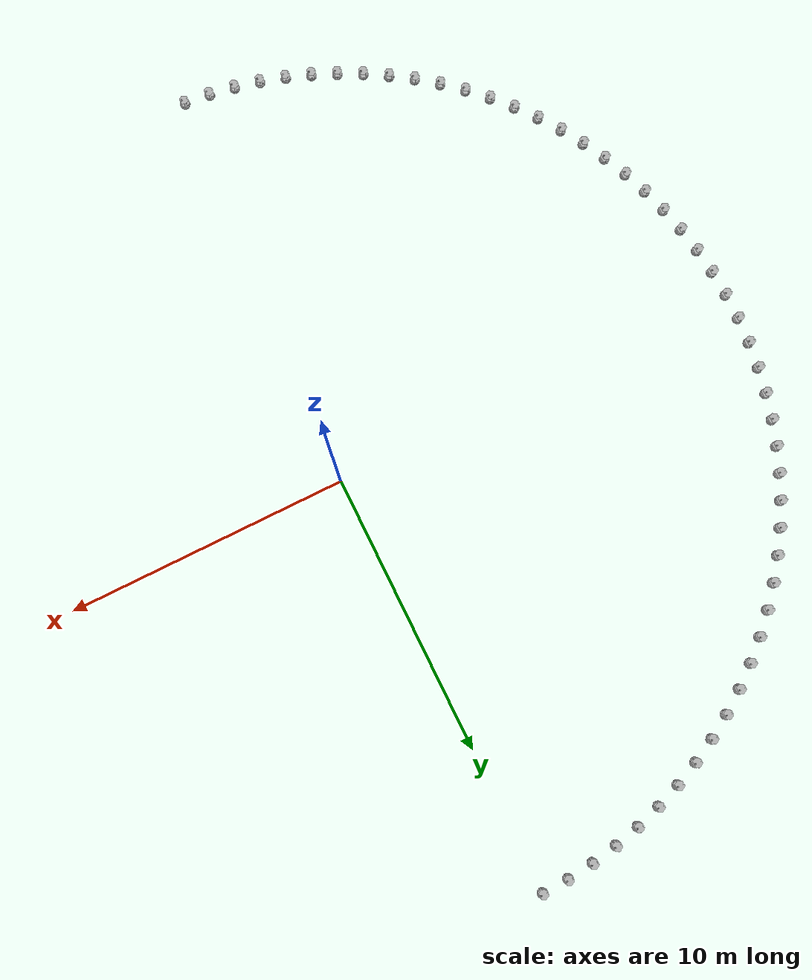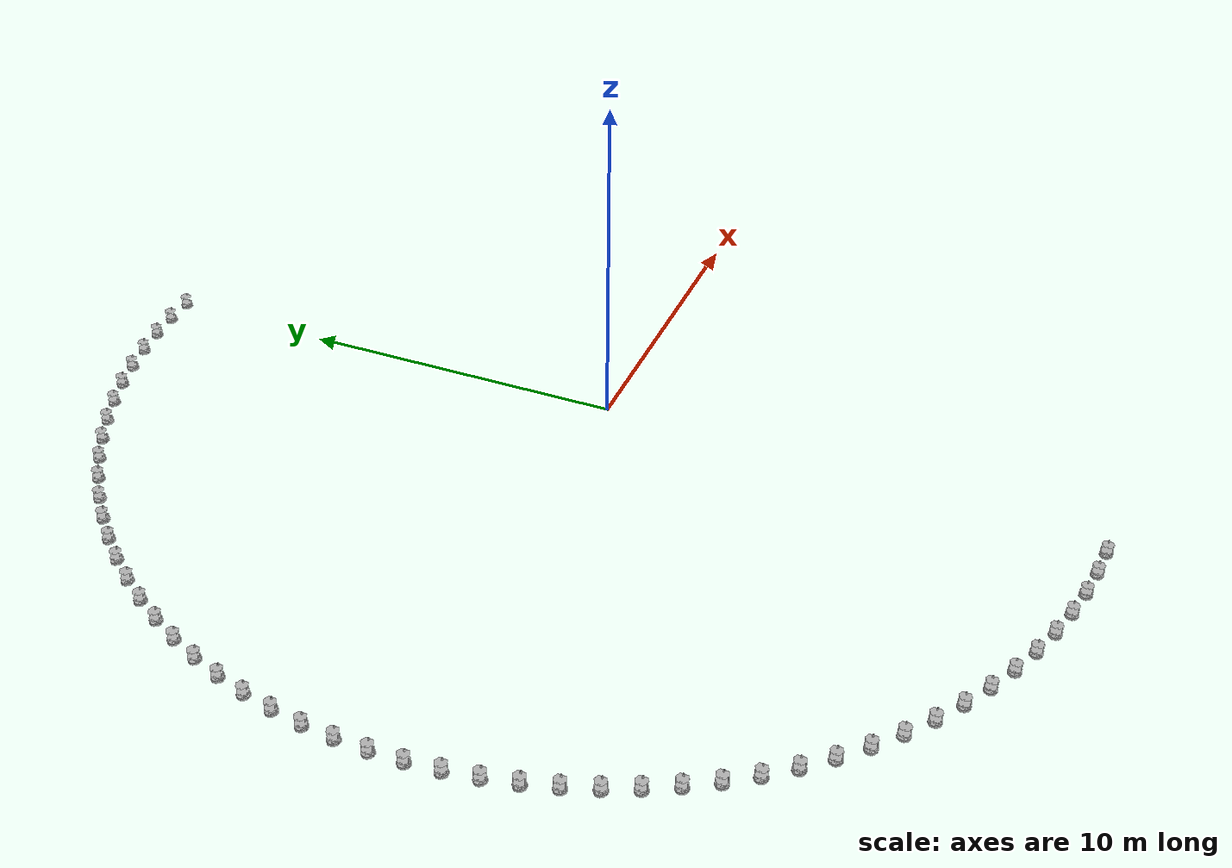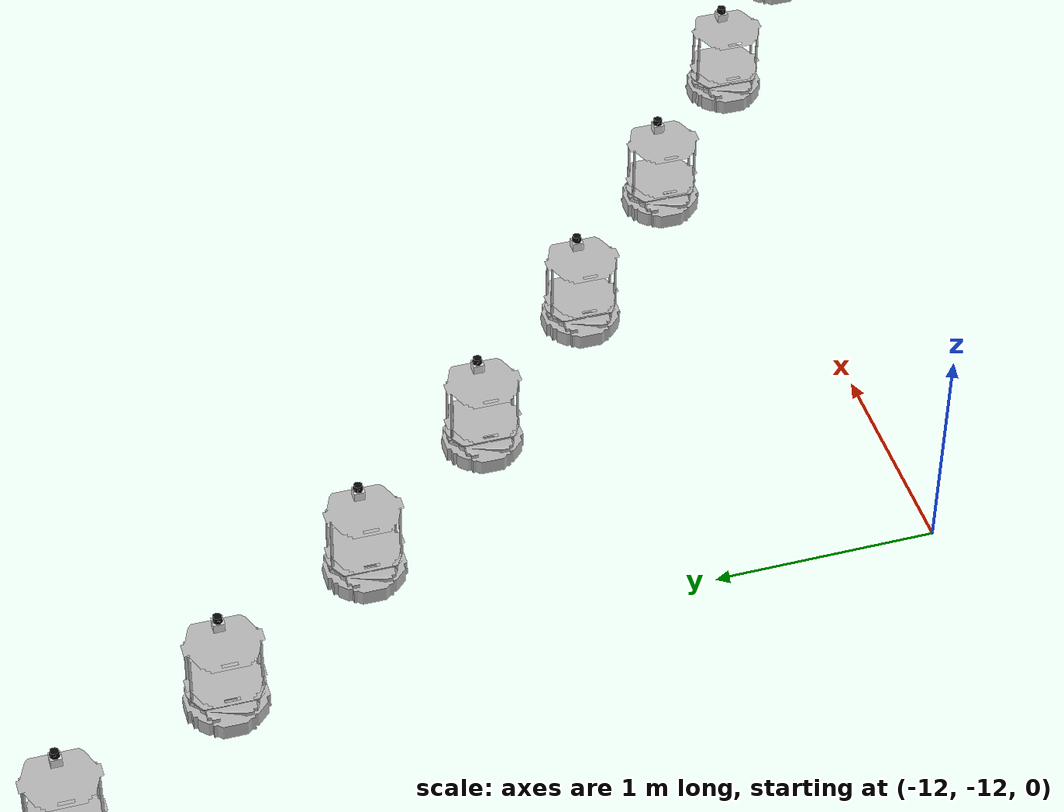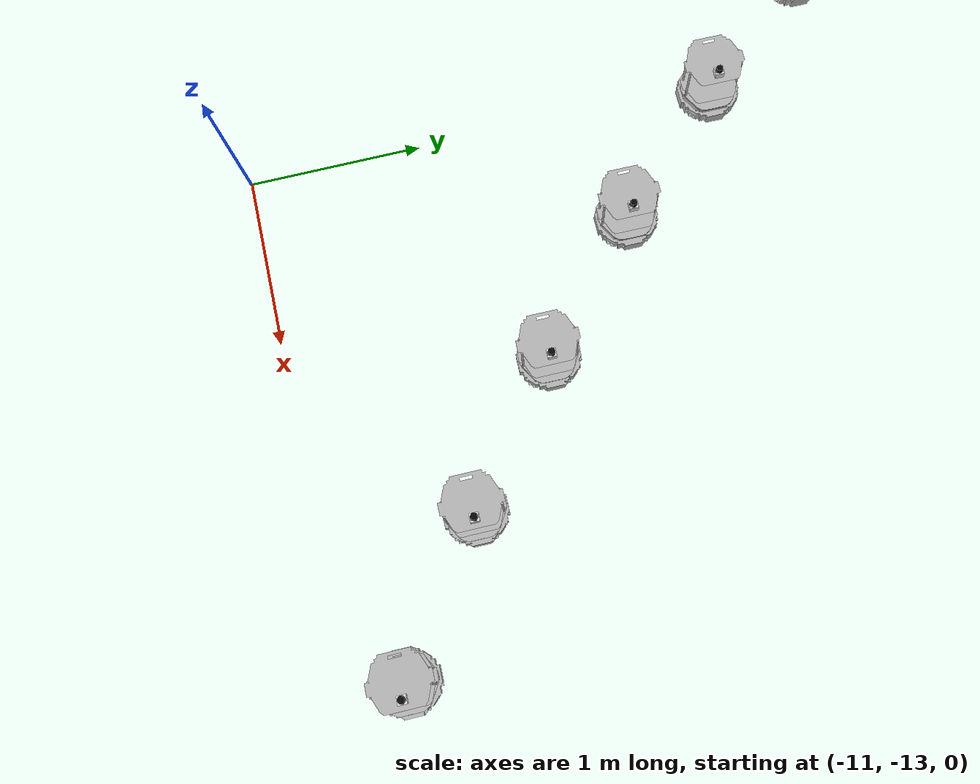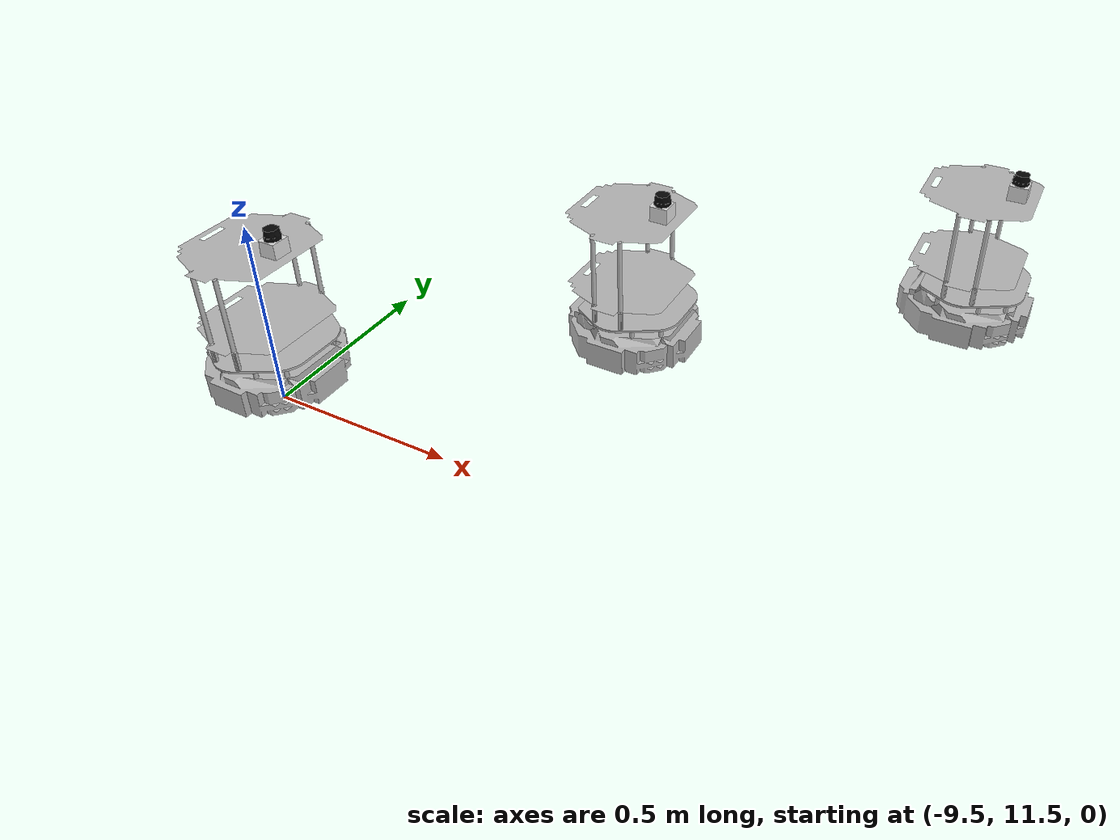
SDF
<sdf version="1.6">
 <world name="default">
  <light name="sun" type="directional">
   <pose>0 0 10 0 -0 0</pose>
   <diffuse>0.8 0.8 0.8 1</diffuse>
   <specular>0.2 0.2 0.2 1</specular>
   <attenuation>
    <range>1000</range>
    <constant>0.9</constant>
    <linear>0.01</linear>
    <quadratic>0.001</quadratic>
   </attenuation>
   <direction>0.5 0.1 -0.9</direction>
  </light>
  <scene><ambient>0.4 0.4 0.4 1</ambient><background>0.7 0.7 0.7 1</background><shadows>1</shadows></scene>
  <physics name="default_physics" default="0" type="ode">
   <max_step_size>0.001</max_step_size>
   <real_time_factor>1</real_time_factor>
   <real_time_update_rate>1000</real_time_update_rate>
  </physics>
  <gravity>0 0 -9.8</gravity>
  <magnetic_field>6e-06 2.3e-05 -4.2e-05</magnetic_field>
  <atmosphere type="adiabatic"/>
  <spherical_coordinates>
   <surface_model>EARTH_WGS84</surface_model>
   <latitude_deg>0</latitude_deg>
   <longitude_deg>0</longitude_deg>
   <elevation>0</elevation>
   <heading_deg>0</heading_deg>
  </spherical_coordinates>
  <model name="robot_62">
   <link name="base_footprint">
    <inertial>
     <pose>0.00554 1.4e-05 0.115513 0 -0 0</pose>
     <mass>4.31731</mass>
     <inertia>
      <ixx>0.123638</ixx>
      <ixy>-3.16036e-06</ixy>
      <ixz>0.00486006</ixz>
      <iyy>0.118098</iyy>
      <iyz>5.27701e-06</iyz>
      <izz>0.0678827</izz>
     </inertia>
    </inertial>
    <collision name="base_footprint_fixed_joint_lump__base_collision">
     <pose>0 0 0.06969 0 -0 0</pose>
     <geometry><cylinder><length>0.10938</length><radius>0.178</radius></cylinder></geometry>
    </collision>
    <collision name="base_footprint_fixed_joint_lump__caster_back_link_collision_1">
     <pose>-0.135 0 0.0192 -1.5708 0 0</pose>
     <geometry><cylinder><length>0.0176</length><radius>0.017</radius></cylinder></geometry>
     <surface>
      <contact><ode><kp>1e+06</kp><kd>100</kd><max_vel>1</max_vel><min_depth>0.001</min_depth></ode></contact>
      <friction><ode><mu>0</mu><mu2>0</mu2></ode></friction>
     </surface>
    </collision>
    <collision name="base_footprint_fixed_joint_lump__caster_front_link_collision_2">
     <pose>0.115 0 0.0172 -1.5708 0 0</pose>
     <geometry><cylinder><length>0.0176</length><radius>0.017</radius></cylinder></geometry>
     <surface>
      <contact><ode><kp>1e+06</kp><kd>100</kd><max_vel>1</max_vel><min_depth>0.001</min_depth></ode></contact>
      <friction><ode><mu>0</mu><mu2>0</mu2></ode></friction>
     </surface>
    </collision>
    <collision name="base_footprint_fixed_joint_lump__hokuyo_link_collision_3">
     <pose>0.08 0 0.4402 0 -0 0</pose>
     <geometry><box><size>0.1 0.1 0.1</size></box></geometry>
    </collision>
    <collision name="base_footprint_fixed_joint_lump__plate_bottom_link_collision_4">
     <pose>0 0 0.1408 0 -0 0</pose>
     <geometry><cylinder><length>0.006</length><radius>0.17</radius></cylinder></geometry>
    </collision>
    <collision name="base_footprint_fixed_joint_lump__plate_middle_link_collision_5">
     <pose>0 0 0.1976 0 -0 0</pose>
     <geometry><cylinder><length>0.006</length><radius>0.17</radius></cylinder></geometry>
    </collision>
    <collision name="base_footprint_fixed_joint_lump__plate_top_link_collision_6">
     <pose>0 0 0.4068 0 -0 0</pose>
     <geometry><cylinder><length>0.006</length><radius>0.17</radius></cylinder></geometry>
    </collision>
    <collision name="base_footprint_fixed_joint_lump__pole_bottom_0_link_collision_7">
     <pose>0.12 0.082 0.113 0 -0 0</pose>
     <geometry><cylinder><length>0.0492</length><radius>0.006</radius></cylinder></geometry>
    </collision>
    <collision name="base_footprint_fixed_joint_lump__pole_bottom_1_link_collision_8">
     <pose>0.055 0.12 0.113 0 -0 0</pose>
     <geometry><cylinder><length>0.0492</length><radius>0.006</radius></cylinder></geometry>
    </collision>
    <collision name="base_footprint_fixed_joint_lump__pole_bottom_2_link_collision_9">
     <pose>-0.055 0.12 0.113 0 -0 0</pose>
     <geometry><cylinder><length>0.0492</length><radius>0.006</radius></cylinder></geometry>
    </collision>
    <collision name="base_footprint_fixed_joint_lump__pole_bottom_3_link_collision_10">
     <pose>0.12 -0.082 0.113 0 -0 0</pose>
     <geometry><cylinder><length>0.0492</length><radius>0.006</radius></cylinder></geometry>
    </collision>
    <collision name="base_footprint_fixed_joint_lump__pole_bottom_4_link_collision_11">
     <pose>0.055 -0.12 0.113 0 -0 0</pose>
     <geometry><cylinder><length>0.0492</length><radius>0.006</radius></cylinder></geometry>
    </collision>
    <collision name="base_footprint_fixed_joint_lump__pole_bottom_5_link_collision_12">
     <pose>-0.055 -0.12 0.113 0 -0 0</pose>
     <geometry><cylinder><length>0.0492</length><radius>0.006</radius></cylinder></geometry>
    </collision>
    <collision name="base_footprint_fixed_joint_lump__pole_middle_0_link_collision_13">
     <pose>0.0381 0.1505 0.1742 0 -0 0</pose>
     <geometry><cylinder><length>0.0608</length><radius>0.006</radius></cylinder></geometry>
    </collision>
    <collision name="base_footprint_fixed_joint_lump__pole_middle_1_link_collision_14">
     <pose>0.0381 -0.1505 0.1742 0 -0 0</pose>
     <geometry><cylinder><length>0.0608</length><radius>0.006</radius></cylinder></geometry>
    </collision>
    <collision name="base_footprint_fixed_joint_lump__pole_middle_2_link_collision_15">
     <pose>-0.0381 0.1505 0.1742 0 -0 0</pose>
     <geometry><cylinder><length>0.0608</length><radius>0.006</radius></cylinder></geometry>
    </collision>
    <collision name="base_footprint_fixed_joint_lump__pole_middle_3_link_collision_16">
     <pose>-0.0381 -0.1505 0.1742 0 -0 0</pose>
     <geometry><cylinder><length>0.0608</length><radius>0.006</radius></cylinder></geometry>
    </collision>
    <collision name="base_footprint_fixed_joint_lump__pole_top_0_link_collision_17">
     <pose>0.0381 0.1505 0.3022 0 -0 0</pose>
     <geometry><cylinder><length>0.2032</length><radius>0.006</radius></cylinder></geometry>
    </collision>
    <collision name="base_footprint_fixed_joint_lump__pole_top_1_link_collision_18">
     <pose>0.0381 -0.1505 0.3022 0 -0 0</pose>
     <geometry><cylinder><length>0.2032</length><radius>0.006</radius></cylinder></geometry>
    </collision>
    <collision name="base_footprint_fixed_joint_lump__pole_top_2_link_collision_19">
     <pose>-0.0381 0.1505 0.3022 0 -0 0</pose>
     <geometry><cylinder><length>0.2032</length><radius>0.006</radius></cylinder></geometry>
    </collision>
    <collision name="base_footprint_fixed_joint_lump__pole_top_3_link_collision_20">
     <pose>-0.0381 -0.1505 0.3022 0 -0 0</pose>
     <geometry><cylinder><length>0.2032</length><radius>0.006</radius></cylinder></geometry>
    </collision>
    <visual name="base_footprint_fixed_joint_lump__base_link_visual">
     <pose>0.001 0 0.06219 0 -0 0</pose>
     <geometry>
      <mesh><scale>1 1 1</scale><uri>/home/chase/ws/src/kobuki/kobuki_description/meshes/main_body.dae</uri></mesh>
     </geometry>
     <material><script><uri>__default__</uri><name>__default__</name></script></material>
    </visual>
    <visual name="base_footprint_fixed_joint_lump__hokuyo_link_visual_1">
     <pose>0.08 0 0.4402 0 -0 0</pose>
     <geometry>
      <mesh>
       <scale>1 1 1</scale>
       <uri>/home/chase/ws/src/turtlebot_hokuyo/turtlebot_description/meshes/sensors/hokuyo.dae</uri>
      </mesh>
     </geometry>
     <material><script><uri>__default__</uri><name>__default__</name></script></material>
    </visual>
    <visual name="base_footprint_fixed_joint_lump__plate_bottom_link_visual_2">
     <pose>0.02364 0 0.1408 0 -0 0</pose>
     <geometry>
      <mesh>
       <scale>1 1 1</scale>
       <uri>/home/chase/ws/src/turtlebot_hokuyo/turtlebot_description/meshes/stacks/hexagons/plate_bottom.dae</uri>
      </mesh>
     </geometry>
    </visual>
    <visual name="base_footprint_fixed_joint_lump__plate_middle_link_visual_3">
     <pose>-0.01364 0 0.1976 0 -0 0</pose>
     <geometry>
      <mesh>
       <scale>1 1 1</scale>
       <uri>/home/chase/ws/src/turtlebot_hokuyo/turtlebot_description/meshes/stacks/hexagons/plate_middle.dae</uri>
      </mesh>
     </geometry>
    </visual>
    <visual name="base_footprint_fixed_joint_lump__plate_top_link_visual_4">
     <pose>-0.01364 0 0.4068 0 -0 0</pose>
     <geometry>
      <mesh>
       <scale>1 1 1</scale>
       <uri>/home/chase/ws/src/turtlebot_hokuyo/turtlebot_description/meshes/stacks/hexagons/plate_top.dae</uri>
      </mesh>
     </geometry>
    </visual>
    <visual name="base_footprint_fixed_joint_lump__pole_bottom_0_link_visual_5">
     <pose>0.12 0.082 0.113 0 -0 0</pose>
     <geometry>
      <mesh>
       <scale>1 1 1</scale>
       <uri>/home/chase/ws/src/turtlebot_hokuyo/turtlebot_description/meshes/stacks/hexagons/pole_bottom.dae</uri>
      </mesh>
     </geometry>
    </visual>
    <visual name="base_footprint_fixed_joint_lump__pole_bottom_1_link_visual_6">
     <pose>0.055 0.12 0.113 0 -0 0</pose>
     <geometry>
      <mesh>
       <scale>1 1 1</scale>
       <uri>/home/chase/ws/src/turtlebot_hokuyo/turtlebot_description/meshes/stacks/hexagons/pole_bottom.dae</uri>
      </mesh>
     </geometry>
    </visual>
    <visual name="base_footprint_fixed_joint_lump__pole_bottom_2_link_visual_7">
     <pose>-0.055 0.12 0.113 0 -0 0</pose>
     <geometry>
      <mesh>
       <scale>1 1 1</scale>
       <uri>/home/chase/ws/src/turtlebot_hokuyo/turtlebot_description/meshes/stacks/hexagons/pole_bottom.dae</uri>
      </mesh>
     </geometry>
    </visual>
    <visual name="base_footprint_fixed_joint_lump__pole_bottom_3_link_visual_8">
     <pose>0.12 -0.082 0.113 0 -0 0</pose>
     <geometry>
      <mesh>
       <scale>1 1 1</scale>
       <uri>/home/chase/ws/src/turtlebot_hokuyo/turtlebot_description/meshes/stacks/hexagons/pole_bottom.dae</uri>
      </mesh>
     </geometry>
    </visual>
    <visual name="base_footprint_fixed_joint_lump__pole_bottom_4_link_visual_9">
     <pose>0.055 -0.12 0.113 0 -0 0</pose>
     <geometry>
      <mesh>
       <scale>1 1 1</scale>
       <uri>/home/chase/ws/src/turtlebot_hokuyo/turtlebot_description/meshes/stacks/hexagons/pole_bottom.dae</uri>
      </mesh>
     </geometry>
    </visual>
    <visual name="base_footprint_fixed_joint_lump__pole_bottom_5_link_visual_10">
     <pose>-0.055 -0.12 0.113 0 -0 0</pose>
     <geometry>
      <mesh>
       <scale>1 1 1</scale>
       <uri>/home/chase/ws/src/turtlebot_hokuyo/turtlebot_description/meshes/stacks/hexagons/pole_bottom.dae</uri>
      </mesh>
     </geometry>
    </visual>
    <visual name="base_footprint_fixed_joint_lump__pole_middle_0_link_visual_11">
     <pose>0.0381 0.1505 0.1742 3.14159 -0 3.14159</pose>
     <geometry>
      <mesh>
       <scale>1 1 1</scale>
       <uri>/home/chase/ws/src/turtlebot_hokuyo/turtlebot_description/meshes/stacks/hexagons/pole_middle.dae</uri>
      </mesh>
     </geometry>
    </visual>
    <visual name="base_footprint_fixed_joint_lump__pole_middle_1_link_visual_12">
     <pose>0.0381 -0.1505 0.1742 3.14159 -0 3.14159</pose>
     <geometry>
      <mesh>
       <scale>1 1 1</scale>
       <uri>/home/chase/ws/src/turtlebot_hokuyo/turtlebot_description/meshes/stacks/hexagons/pole_middle.dae</uri>
      </mesh>
     </geometry>
    </visual>
    <visual name="base_footprint_fixed_joint_lump__pole_middle_2_link_visual_13">
     <pose>-0.0381 0.1505 0.1742 3.14159 -0 3.14159</pose>
     <geometry>
      <mesh>
       <scale>1 1 1</scale>
       <uri>/home/chase/ws/src/turtlebot_hokuyo/turtlebot_description/meshes/stacks/hexagons/pole_middle.dae</uri>
      </mesh>
     </geometry>
    </visual>
    <visual name="base_footprint_fixed_joint_lump__pole_middle_3_link_visual_14">
     <pose>-0.0381 -0.1505 0.1742 3.14159 -0 3.14159</pose>
     <geometry>
      <mesh>
       <scale>1 1 1</scale>
       <uri>/home/chase/ws/src/turtlebot_hokuyo/turtlebot_description/meshes/stacks/hexagons/pole_middle.dae</uri>
      </mesh>
     </geometry>
    </visual>
    <visual name="base_footprint_fixed_joint_lump__pole_top_0_link_visual_15">
     <pose>0.0381 0.1505 0.3022 0 -0 0</pose>
     <geometry>
      <mesh>
       <scale>1 1 1</scale>
       <uri>/home/chase/ws/src/turtlebot_hokuyo/turtlebot_description/meshes/stacks/hexagons/pole_top.dae</uri>
      </mesh>
     </geometry>
    </visual>
    <visual name="base_footprint_fixed_joint_lump__pole_top_1_link_visual_16">
     <pose>0.0381 -0.1505 0.3022 0 -0 0</pose>
     <geometry>
      <mesh>
       <scale>1 1 1</scale>
       <uri>/home/chase/ws/src/turtlebot_hokuyo/turtlebot_description/meshes/stacks/hexagons/pole_top.dae</uri>
      </mesh>
     </geometry>
    </visual>
    <visual name="base_footprint_fixed_joint_lump__pole_top_2_link_visual_17">
     <pose>-0.0381 0.1505 0.3022 0 -0 0</pose>
     <geometry>
      <mesh>
       <scale>1 1 1</scale>
       <uri>/home/chase/ws/src/turtlebot_hokuyo/turtlebot_description/meshes/stacks/hexagons/pole_top.dae</uri>
      </mesh>
     </geometry>
    </visual>
    <visual name="base_footprint_fixed_joint_lump__pole_top_3_link_visual_18">
     <pose>-0.0381 -0.1505 0.3022 0 -0 0</pose>
     <geometry>
      <mesh>
       <scale>1 1 1</scale>
       <uri>/home/chase/ws/src/turtlebot_hokuyo/turtlebot_description/meshes/stacks/hexagons/pole_top.dae</uri>
      </mesh>
     </geometry>
    </visual>
    <sensor name="bumpers" type="contact">
     <always_on>0</always_on>
     <update_rate>0.01</update_rate>
     <visualize>0</visualize>
     <contact>
      <collision>base_footprint_fixed_joint_lump__base_collision</collision>
      <topic>__default_topic__</topic>
     </contact>
     <pose>0 0 0.0102 0 -0 0</pose>
    </sensor>
    <sensor name="cliff_sensor_front" type="ray">
     <always_on>0</always_on>
     <update_rate>0.01</update_rate>
     <visualize>0</visualize>
     <ray>
      <scan>
       <horizontal>
        <samples>50</samples>
        <resolution>1</resolution>
        <min_angle>-0.0436</min_angle>
        <max_angle>0.0436</max_angle>
       </horizontal>
       <vertical><samples>1</samples><min_angle>0</min_angle><max_angle>0</max_angle></vertical>
      </scan>
      <range><min>0.01</min><max>0.15</max><resolution>1</resolution></range>
     </ray>
     <pose>0.156 0 0.0316 3.14159 1.57079 3.14159</pose>
    </sensor>
    <sensor name="cliff_sensor_left" type="ray">
     <always_on>0</always_on>
     <update_rate>0.01</update_rate>
     <visualize>0</visualize>
     <ray>
      <scan>
       <horizontal>
        <samples>50</samples>
        <resolution>1</resolution>
        <min_angle>-0.0436</min_angle>
        <max_angle>0.0436</max_angle>
       </horizontal>
       <vertical><samples>1</samples><min_angle>0</min_angle><max_angle>0</max_angle></vertical>
      </scan>
      <range><min>0.01</min><max>0.15</max><resolution>1</resolution></range>
     </ray>
     <pose>0.08734 0.13601 0.0316 3.14159 1.57079 3.14159</pose>
    </sensor>
    <sensor name="cliff_sensor_right" type="ray">
     <always_on>0</always_on>
     <update_rate>0.01</update_rate>
     <visualize>0</visualize>
     <ray>
      <scan>
       <horizontal>
        <samples>50</samples>
        <resolution>1</resolution>
        <min_angle>-0.0436</min_angle>
        <max_angle>0.0436</max_angle>
       </horizontal>
       <vertical><samples>1</samples><min_angle>0</min_angle><max_angle>0</max_angle></vertical>
      </scan>
      <range><min>0.01</min><max>0.15</max><resolution>1</resolution></range>
     </ray>
     <pose>0.085 -0.13601 0.0316 3.14159 1.57079 3.14159</pose>
    </sensor>
    <sensor name="imu" type="imu">
     <always_on>0</always_on>
     <update_rate>0.01</update_rate>
     <visualize>0</visualize>
     <imu>
      <angular_velocity>
       <x>
        <noise type="gaussian">
         <mean>0</mean>
         <stddev>1.96e-06</stddev>
         <bias_mean>0</bias_mean>
         <bias_stddev>0</bias_stddev>
        </noise>
       </x>
       <y>
        <noise type="gaussian">
         <mean>0</mean>
         <stddev>1.96e-06</stddev>
         <bias_mean>0</bias_mean>
         <bias_stddev>0</bias_stddev>
        </noise>
       </y>
       <z>
        <noise type="gaussian">
         <mean>0</mean>
         <stddev>1.96e-06</stddev>
         <bias_mean>0</bias_mean>
         <bias_stddev>0</bias_stddev>
        </noise>
       </z>
      </angular_velocity>
      <linear_acceleration>
       <x>
        <noise type="gaussian">
         <mean>0</mean>
         <stddev>0.017</stddev>
         <bias_mean>0.1</bias_mean>
         <bias_stddev>0.001</bias_stddev>
        </noise>
       </x>
       <y>
        <noise type="gaussian">
         <mean>0</mean>
         <stddev>0.017</stddev>
         <bias_mean>0.1</bias_mean>
         <bias_stddev>0.001</bias_stddev>
        </noise>
       </y>
       <z>
        <noise type="gaussian">
         <mean>0</mean>
         <stddev>0.017</stddev>
         <bias_mean>0.1</bias_mean>
         <bias_stddev>0.001</bias_stddev>
        </noise>
       </z>
      </linear_acceleration>
     </imu>
     <pose>0.056 0.062 0.0304 0 -0 0</pose>
    </sensor>
    <sensor name="head_hokuyo_sensor" type="gpu_ray">
     <visualize>0</visualize>
     <update_rate>10</update_rate>
     <ray>
      <scan>
       <horizontal>
        <samples>512</samples>
        <resolution>1</resolution>
        <min_angle>-1.57</min_angle>
        <max_angle>1.57</max_angle>
       </horizontal>
      </scan>
      <range><min>0.05</min><max>4</max><resolution>0.1</resolution></range>
      <noise><type>gaussian</type><mean>0</mean><stddev>0.04</stddev></noise>
     </ray>
     <plugin name="gazebo_ros_head_hokuyo_controller" filename="libgazebo_ros_gpu_laser.so">
      <topicName>scan</topicName>
      <frameName>hokuyo_link</frameName>
      <robotNamespace>/robot_62/</robotNamespace>
     </plugin>
     <pose>0.08 0 0.4402 0 -0 0</pose>
    </sensor>
   </link>
   <link name="wheel_left_link">
    <pose>0 0.115 0.0352 -1.5708 0 0</pose>
    <inertial>
     <mass>0.01</mass>
     <inertia><ixx>0.001</ixx><ixy>0</ixy><ixz>0</ixz><iyy>0.001</iyy><iyz>0</iyz><izz>0.001</izz></inertia>
    </inertial>
    <collision name="wheel_left_link_collision">
     <geometry><cylinder><length>0.0206</length><radius>0.0352</radius></cylinder></geometry>
     <surface>
      <contact><ode><kp>1e+06</kp><kd>100</kd><max_vel>1</max_vel><min_depth>0.001</min_depth></ode></contact>
      <friction><ode><mu>1</mu><mu2>1</mu2></ode></friction>
     </surface>
    </collision>
    <visual name="wheel_left_link_visual">
     <geometry>
      <mesh><scale>1 1 1</scale><uri>/home/chase/ws/src/kobuki/kobuki_description/meshes/wheel.dae</uri></mesh>
     </geometry>
     <material><script><uri>__default__</uri><name>__default__</name></script></material>
    </visual>
   </link>
   <joint name="wheel_left_joint" type="revolute">
    <child>wheel_left_link</child>
    <parent>base_footprint</parent>
    <axis>
     <xyz>0 1 0</xyz>
     <limit><lower>-1e+16</lower><upper>1e+16</upper></limit>
     <dynamics><spring_reference>0</spring_reference><spring_stiffness>0</spring_stiffness></dynamics>
     <use_parent_model_frame>1</use_parent_model_frame>
    </axis>
   </joint>
   <link name="wheel_right_link">
    <pose>0 -0.115 0.0352 -1.5708 0 0</pose>
    <inertial>
     <mass>0.01</mass>
     <inertia><ixx>0.001</ixx><ixy>0</ixy><ixz>0</ixz><iyy>0.001</iyy><iyz>0</iyz><izz>0.001</izz></inertia>
    </inertial>
    <collision name="wheel_right_link_collision">
     <geometry><cylinder><length>0.0206</length><radius>0.035</radius></cylinder></geometry>
     <surface>
      <contact><ode><kp>1e+06</kp><kd>100</kd><max_vel>1</max_vel><min_depth>0.001</min_depth></ode></contact>
      <friction><ode><mu>1</mu><mu2>1</mu2></ode></friction>
     </surface>
    </collision>
    <visual name="wheel_right_link_visual">
     <geometry>
      <mesh><scale>1 1 1</scale><uri>/home/chase/ws/src/kobuki/kobuki_description/meshes/wheel.dae</uri></mesh>
     </geometry>
     <material><script><uri>__default__</uri><name>__default__</name></script></material>
    </visual>
   </link>
   <joint name="wheel_right_joint" type="revolute">
    <child>wheel_right_link</child>
    <parent>base_footprint</parent>
    <axis>
     <xyz>0 1 0</xyz>
     <limit><lower>-1e+16</lower><upper>1e+16</upper></limit>
     <dynamics><spring_reference>0</spring_reference><spring_stiffness>0</spring_stiffness></dynamics>
     <use_parent_model_frame>1</use_parent_model_frame>
    </axis>
   </joint>
   <static>0</static>
   <plugin name="kobuki_controller" filename="libgazebo_ros_kobuki.so">
    <publish_tf>1</publish_tf>
    <left_wheel_joint_name>wheel_left_joint</left_wheel_joint_name>
    <right_wheel_joint_name>wheel_right_joint</right_wheel_joint_name>
    <wheel_separation>.230</wheel_separation>
    <wheel_diameter>0.070</wheel_diameter>
    <torque>1.0</torque>
    <velocity_command_timeout>0.6</velocity_command_timeout>
    <cliff_sensor_left_name>cliff_sensor_left</cliff_sensor_left_name>
    <cliff_sensor_center_name>cliff_sensor_front</cliff_sensor_center_name>
    <cliff_sensor_right_name>cliff_sensor_right</cliff_sensor_right_name>
    <cliff_detection_threshold>0.04</cliff_detection_threshold>
    <bumper_name>bumpers</bumper_name>
    <imu_name>imu</imu_name>
    <robotNamespace>/robot_62/</robotNamespace>
   </plugin>
   <pose>-10.9348 -10.2682 -0.000236 0.000772 -0.000346 -0.003564</pose>
  </model>
  <model name="robot_43">
   <link name="base_footprint">
    <inertial>
     <pose>0.00554 1.4e-05 0.115513 0 -0 0</pose>
     <mass>4.31731</mass>
     <inertia>
      <ixx>0.123638</ixx>
      <ixy>-3.16036e-06</ixy>
      <ixz>0.00486006</ixz>
      <iyy>0.118098</iyy>
      <iyz>5.27701e-06</iyz>
      <izz>0.0678827</izz>
     </inertia>
    </inertial>
    <collision name="base_footprint_fixed_joint_lump__base_collision">
     <pose>0 0 0.06969 0 -0 0</pose>
     <geometry><cylinder><length>0.10938</length><radius>0.178</radius></cylinder></geometry>
    </collision>
    <collision name="base_footprint_fixed_joint_lump__caster_back_link_collision_1">
     <pose>-0.135 0 0.0192 -1.5708 0 0</pose>
     <geometry><cylinder><length>0.0176</length><radius>0.017</radius></cylinder></geometry>
     <surface>
      <contact><ode><kp>1e+06</kp><kd>100</kd><max_vel>1</max_vel><min_depth>0.001</min_depth></ode></contact>
      <friction><ode><mu>0</mu><mu2>0</mu2></ode></friction>
     </surface>
    </collision>
    <collision name="base_footprint_fixed_joint_lump__caster_front_link_collision_2">
     <pose>0.115 0 0.0172 -1.5708 0 0</pose>
     <geometry><cylinder><length>0.0176</length><radius>0.017</radius></cylinder></geometry>
     <surface>
      <contact><ode><kp>1e+06</kp><kd>100</kd><max_vel>1</max_vel><min_depth>0.001</min_depth></ode></contact>
      <friction><ode><mu>0</mu><mu2>0</mu2></ode></friction>
     </surface>
    </collision>
    <collision name="base_footprint_fixed_joint_lump__hokuyo_link_collision_3">
     <pose>0.08 0 0.4402 0 -0 0</pose>
     <geometry><box><size>0.1 0.1 0.1</size></box></geometry>
    </collision>
    <collision name="base_footprint_fixed_joint_lump__plate_bottom_link_collision_4">
     <pose>0 0 0.1408 0 -0 0</pose>
     <geometry><cylinder><length>0.006</length><radius>0.17</radius></cylinder></geometry>
    </collision>
    <collision name="base_footprint_fixed_joint_lump__plate_middle_link_collision_5">
     <pose>0 0 0.1976 0 -0 0</pose>
     <geometry><cylinder><length>0.006</length><radius>0.17</radius></cylinder></geometry>
    </collision>
    <collision name="base_footprint_fixed_joint_lump__plate_top_link_collision_6">
     <pose>0 0 0.4068 0 -0 0</pose>
     <geometry><cylinder><length>0.006</length><radius>0.17</radius></cylinder></geometry>
    </collision>
    <collision name="base_footprint_fixed_joint_lump__pole_bottom_0_link_collision_7">
     <pose>0.12 0.082 0.113 0 -0 0</pose>
     <geometry><cylinder><length>0.0492</length><radius>0.006</radius></cylinder></geometry>
    </collision>
    <collision name="base_footprint_fixed_joint_lump__pole_bottom_1_link_collision_8">
     <pose>0.055 0.12 0.113 0 -0 0</pose>
     <geometry><cylinder><length>0.0492</length><radius>0.006</radius></cylinder></geometry>
    </collision>
    <collision name="base_footprint_fixed_joint_lump__pole_bottom_2_link_collision_9">
     <pose>-0.055 0.12 0.113 0 -0 0</pose>
     <geometry><cylinder><length>0.0492</length><radius>0.006</radius></cylinder></geometry>
    </collision>
    <collision name="base_footprint_fixed_joint_lump__pole_bottom_3_link_collision_10">
     <pose>0.12 -0.082 0.113 0 -0 0</pose>
     <geometry><cylinder><length>0.0492</length><radius>0.006</radius></cylinder></geometry>
    </collision>
    <collision name="base_footprint_fixed_joint_lump__pole_bottom_4_link_collision_11">
     <pose>0.055 -0.12 0.113 0 -0 0</pose>
     <geometry><cylinder><length>0.0492</length><radius>0.006</radius></cylinder></geometry>
    </collision>
    <collision name="base_footprint_fixed_joint_lump__pole_bottom_5_link_collision_12">
     <pose>-0.055 -0.12 0.113 0 -0 0</pose>
     <geometry><cylinder><length>0.0492</length><radius>0.006</radius></cylinder></geometry>
    </collision>
    <collision name="base_footprint_fixed_joint_lump__pole_middle_0_link_collision_13">
     <pose>0.0381 0.1505 0.1742 0 -0 0</pose>
     <geometry><cylinder><length>0.0608</length><radius>0.006</radius></cylinder></geometry>
    </collision>
    <collision name="base_footprint_fixed_joint_lump__pole_middle_1_link_collision_14">
     <pose>0.0381 -0.1505 0.1742 0 -0 0</pose>
     <geometry><cylinder><length>0.0608</length><radius>0.006</radius></cylinder></geometry>
    </collision>
    <collision name="base_footprint_fixed_joint_lump__pole_middle_2_link_collision_15">
     <pose>-0.0381 0.1505 0.1742 0 -0 0</pose>
     <geometry><cylinder><length>0.0608</length><radius>0.006</radius></cylinder></geometry>
    </collision>
    <collision name="base_footprint_fixed_joint_lump__pole_middle_3_link_collision_16">
     <pose>-0.0381 -0.1505 0.1742 0 -0 0</pose>
     <geometry><cylinder><length>0.0608</length><radius>0.006</radius></cylinder></geometry>
    </collision>
    <collision name="base_footprint_fixed_joint_lump__pole_top_0_link_collision_17">
     <pose>0.0381 0.1505 0.3022 0 -0 0</pose>
     <geometry><cylinder><length>0.2032</length><radius>0.006</radius></cylinder></geometry>
    </collision>
    <collision name="base_footprint_fixed_joint_lump__pole_top_1_link_collision_18">
     <pose>0.0381 -0.1505 0.3022 0 -0 0</pose>
     <geometry><cylinder><length>0.2032</length><radius>0.006</radius></cylinder></geometry>
    </collision>
    <collision name="base_footprint_fixed_joint_lump__pole_top_2_link_collision_19">
     <pose>-0.0381 0.1505 0.3022 0 -0 0</pose>
     <geometry><cylinder><length>0.2032</length><radius>0.006</radius></cylinder></geometry>
    </collision>
    <collision name="base_footprint_fixed_joint_lump__pole_top_3_link_collision_20">
     <pose>-0.0381 -0.1505 0.3022 0 -0 0</pose>
     <geometry><cylinder><length>0.2032</length><radius>0.006</radius></cylinder></geometry>
    </collision>
    <visual name="base_footprint_fixed_joint_lump__base_link_visual">
     <pose>0.001 0 0.06219 0 -0 0</pose>
     <geometry>
      <mesh><scale>1 1 1</scale><uri>/home/chase/ws/src/kobuki/kobuki_description/meshes/main_body.dae</uri></mesh>
     </geometry>
     <material><script><uri>__default__</uri><name>__default__</name></script></material>
    </visual>
    <visual name="base_footprint_fixed_joint_lump__hokuyo_link_visual_1">
     <pose>0.08 0 0.4402 0 -0 0</pose>
     <geometry>
      <mesh>
       <scale>1 1 1</scale>
       <uri>/home/chase/ws/src/turtlebot_hokuyo/turtlebot_description/meshes/sensors/hokuyo.dae</uri>
      </mesh>
     </geometry>
     <material><script><uri>__default__</uri><name>__default__</name></script></material>
    </visual>
    <visual name="base_footprint_fixed_joint_lump__plate_bottom_link_visual_2">
     <pose>0.02364 0 0.1408 0 -0 0</pose>
     <geometry>
      <mesh>
       <scale>1 1 1</scale>
       <uri>/home/chase/ws/src/turtlebot_hokuyo/turtlebot_description/meshes/stacks/hexagons/plate_bottom.dae</uri>
      </mesh>
     </geometry>
    </visual>
    <visual name="base_footprint_fixed_joint_lump__plate_middle_link_visual_3">
     <pose>-0.01364 0 0.1976 0 -0 0</pose>
     <geometry>
      <mesh>
       <scale>1 1 1</scale>
       <uri>/home/chase/ws/src/turtlebot_hokuyo/turtlebot_description/meshes/stacks/hexagons/plate_middle.dae</uri>
      </mesh>
     </geometry>
    </visual>
    <visual name="base_footprint_fixed_joint_lump__plate_top_link_visual_4">
     <pose>-0.01364 0 0.4068 0 -0 0</pose>
     <geometry>
      <mesh>
       <scale>1 1 1</scale>
       <uri>/home/chase/ws/src/turtlebot_hokuyo/turtlebot_description/meshes/stacks/hexagons/plate_top.dae</uri>
      </mesh>
     </geometry>
    </visual>
    <visual name="base_footprint_fixed_joint_lump__pole_bottom_0_link_visual_5">
     <pose>0.12 0.082 0.113 0 -0 0</pose>
     <geometry>
      <mesh>
       <scale>1 1 1</scale>
       <uri>/home/chase/ws/src/turtlebot_hokuyo/turtlebot_description/meshes/stacks/hexagons/pole_bottom.dae</uri>
      </mesh>
     </geometry>
    </visual>
    <visual name="base_footprint_fixed_joint_lump__pole_bottom_1_link_visual_6">
     <pose>0.055 0.12 0.113 0 -0 0</pose>
     <geometry>
      <mesh>
       <scale>1 1 1</scale>
       <uri>/home/chase/ws/src/turtlebot_hokuyo/turtlebot_description/meshes/stacks/hexagons/pole_bottom.dae</uri>
      </mesh>
     </geometry>
    </visual>
    <visual name="base_footprint_fixed_joint_lump__pole_bottom_2_link_visual_7">
     <pose>-0.055 0.12 0.113 0 -0 0</pose>
     <geometry>
      <mesh>
       <scale>1 1 1</scale>
       <uri>/home/chase/ws/src/turtlebot_hokuyo/turtlebot_description/meshes/stacks/hexagons/pole_bottom.dae</uri>
      </mesh>
     </geometry>
    </visual>
    <visual name="base_footprint_fixed_joint_lump__pole_bottom_3_link_visual_8">
     <pose>0.12 -0.082 0.113 0 -0 0</pose>
     <geometry>
      <mesh>
       <scale>1 1 1</scale>
       <uri>/home/chase/ws/src/turtlebot_hokuyo/turtlebot_description/meshes/stacks/hexagons/pole_bottom.dae</uri>
      </mesh>
     </geometry>
    </visual>
    <visual name="base_footprint_fixed_joint_lump__pole_bottom_4_link_visual_9">
     <pose>0.055 -0.12 0.113 0 -0 0</pose>
     <geometry>
      <mesh>
       <scale>1 1 1</scale>
       <uri>/home/chase/ws/src/turtlebot_hokuyo/turtlebot_description/meshes/stacks/hexagons/pole_bottom.dae</uri>
      </mesh>
     </geometry>
    </visual>
    <visual name="base_footprint_fixed_joint_lump__pole_bottom_5_link_visual_10">
     <pose>-0.055 -0.12 0.113 0 -0 0</pose>
     <geometry>
      <mesh>
       <scale>1 1 1</scale>
       <uri>/home/chase/ws/src/turtlebot_hokuyo/turtlebot_description/meshes/stacks/hexagons/pole_bottom.dae</uri>
      </mesh>
     </geometry>
    </visual>
    <visual name="base_footprint_fixed_joint_lump__pole_middle_0_link_visual_11">
     <pose>0.0381 0.1505 0.1742 3.14159 -0 3.14159</pose>
     <geometry>
      <mesh>
       <scale>1 1 1</scale>
       <uri>/home/chase/ws/src/turtlebot_hokuyo/turtlebot_description/meshes/stacks/hexagons/pole_middle.dae</uri>
      </mesh>
     </geometry>
    </visual>
    <visual name="base_footprint_fixed_joint_lump__pole_middle_1_link_visual_12">
     <pose>0.0381 -0.1505 0.1742 3.14159 -0 3.14159</pose>
     <geometry>
      <mesh>
       <scale>1 1 1</scale>
       <uri>/home/chase/ws/src/turtlebot_hokuyo/turtlebot_description/meshes/stacks/hexagons/pole_middle.dae</uri>
      </mesh>
     </geometry>
    </visual>
    <visual name="base_footprint_fixed_joint_lump__pole_middle_2_link_visual_13">
     <pose>-0.0381 0.1505 0.1742 3.14159 -0 3.14159</pose>
     <geometry>
      <mesh>
       <scale>1 1 1</scale>
       <uri>/home/chase/ws/src/turtlebot_hokuyo/turtlebot_description/meshes/stacks/hexagons/pole_middle.dae</uri>
      </mesh>
     </geometry>
    </visual>
    <visual name="base_footprint_fixed_joint_lump__pole_middle_3_link_visual_14">
     <pose>-0.0381 -0.1505 0.1742 3.14159 -0 3.14159</pose>
     <geometry>
      <mesh>
       <scale>1 1 1</scale>
       <uri>/home/chase/ws/src/turtlebot_hokuyo/turtlebot_description/meshes/stacks/hexagons/pole_middle.dae</uri>
      </mesh>
     </geometry>
    </visual>
    <visual name="base_footprint_fixed_joint_lump__pole_top_0_link_visual_15">
     <pose>0.0381 0.1505 0.3022 0 -0 0</pose>
     <geometry>
      <mesh>
       <scale>1 1 1</scale>
       <uri>/home/chase/ws/src/turtlebot_hokuyo/turtlebot_description/meshes/stacks/hexagons/pole_top.dae</uri>
      </mesh>
     </geometry>
    </visual>
    <visual name="base_footprint_fixed_joint_lump__pole_top_1_link_visual_16">
     <pose>0.0381 -0.1505 0.3022 0 -0 0</pose>
     <geometry>
      <mesh>
       <scale>1 1 1</scale>
       <uri>/home/chase/ws/src/turtlebot_hokuyo/turtlebot_description/meshes/stacks/hexagons/pole_top.dae</uri>
      </mesh>
     </geometry>
    </visual>
    <visual name="base_footprint_fixed_joint_lump__pole_top_2_link_visual_17">
     <pose>-0.0381 0.1505 0.3022 0 -0 0</pose>
     <geometry>
      <mesh>
       <scale>1 1 1</scale>
       <uri>/home/chase/ws/src/turtlebot_hokuyo/turtlebot_description/meshes/stacks/hexagons/pole_top.dae</uri>
      </mesh>
     </geometry>
    </visual>
    <visual name="base_footprint_fixed_joint_lump__pole_top_3_link_visual_18">
     <pose>-0.0381 -0.1505 0.3022 0 -0 0</pose>
     <geometry>
      <mesh>
       <scale>1 1 1</scale>
       <uri>/home/chase/ws/src/turtlebot_hokuyo/turtlebot_description/meshes/stacks/hexagons/pole_top.dae</uri>
      </mesh>
     </geometry>
    </visual>
    <sensor name="bumpers" type="contact">
     <always_on>0</always_on>
     <update_rate>0.01</update_rate>
     <visualize>0</visualize>
     <contact>
      <collision>base_footprint_fixed_joint_lump__base_collision</collision>
      <topic>__default_topic__</topic>
     </contact>
     <pose>0 0 0.0102 0 -0 0</pose>
    </sensor>
    <sensor name="cliff_sensor_front" type="ray">
     <always_on>0</always_on>
     <update_rate>0.01</update_rate>
     <visualize>0</visualize>
     <ray>
      <scan>
       <horizontal>
        <samples>50</samples>
        <resolution>1</resolution>
        <min_angle>-0.0436</min_angle>
        <max_angle>0.0436</max_angle>
       </horizontal>
       <vertical><samples>1</samples><min_angle>0</min_angle><max_angle>0</max_angle></vertical>
      </scan>
      <range><min>0.01</min><max>0.15</max><resolution>1</resolution></range>
     </ray>
     <pose>0.156 0 0.0316 3.14159 1.57079 3.14159</pose>
    </sensor>
    <sensor name="cliff_sensor_left" type="ray">
     <always_on>0</always_on>
     <update_rate>0.01</update_rate>
     <visualize>0</visualize>
     <ray>
      <scan>
       <horizontal>
        <samples>50</samples>
        <resolution>1</resolution>
        <min_angle>-0.0436</min_angle>
        <max_angle>0.0436</max_angle>
       </horizontal>
       <vertical><samples>1</samples><min_angle>0</min_angle><max_angle>0</max_angle></vertical>
      </scan>
      <range><min>0.01</min><max>0.15</max><resolution>1</resolution></range>
     </ray>
     <pose>0.08734 0.13601 0.0316 3.14159 1.57079 3.14159</pose>
    </sensor>
    <sensor name="cliff_sensor_right" type="ray">
     <always_on>0</always_on>
     <update_rate>0.01</update_rate>
     <visualize>0</visualize>
     <ray>
      <scan>
       <horizontal>
        <samples>50</samples>
        <resolution>1</resolution>
        <min_angle>-0.0436</min_angle>
        <max_angle>0.0436</max_angle>
       </horizontal>
       <vertical><samples>1</samples><min_angle>0</min_angle><max_angle>0</max_angle></vertical>
      </scan>
      <range><min>0.01</min><max>0.15</max><resolution>1</resolution></range>
     </ray>
     <pose>0.085 -0.13601 0.0316 3.14159 1.57079 3.14159</pose>
    </sensor>
    <sensor name="imu" type="imu">
     <always_on>0</always_on>
     <update_rate>0.01</update_rate>
     <visualize>0</visualize>
     <imu>
      <angular_velocity>
       <x>
        <noise type="gaussian">
         <mean>0</mean>
         <stddev>1.96e-06</stddev>
         <bias_mean>0</bias_mean>
         <bias_stddev>0</bias_stddev>
        </noise>
       </x>
       <y>
        <noise type="gaussian">
         <mean>0</mean>
         <stddev>1.96e-06</stddev>
         <bias_mean>0</bias_mean>
         <bias_stddev>0</bias_stddev>
        </noise>
       </y>
       <z>
        <noise type="gaussian">
         <mean>0</mean>
         <stddev>1.96e-06</stddev>
         <bias_mean>0</bias_mean>
         <bias_stddev>0</bias_stddev>
        </noise>
       </z>
      </angular_velocity>
      <linear_acceleration>
       <x>
        <noise type="gaussian">
         <mean>0</mean>
         <stddev>0.017</stddev>
         <bias_mean>0.1</bias_mean>
         <bias_stddev>0.001</bias_stddev>
        </noise>
       </x>
       <y>
        <noise type="gaussian">
         <mean>0</mean>
         <stddev>0.017</stddev>
         <bias_mean>0.1</bias_mean>
         <bias_stddev>0.001</bias_stddev>
        </noise>
       </y>
       <z>
        <noise type="gaussian">
         <mean>0</mean>
         <stddev>0.017</stddev>
         <bias_mean>0.1</bias_mean>
         <bias_stddev>0.001</bias_stddev>
        </noise>
       </z>
      </linear_acceleration>
     </imu>
     <pose>0.056 0.062 0.0304 0 -0 0</pose>
    </sensor>
    <sensor name="head_hokuyo_sensor" type="gpu_ray">
     <visualize>0</visualize>
     <update_rate>10</update_rate>
     <ray>
      <scan>
       <horizontal>
        <samples>512</samples>
        <resolution>1</resolution>
        <min_angle>-1.57</min_angle>
        <max_angle>1.57</max_angle>
       </horizontal>
      </scan>
      <range><min>0.05</min><max>4</max><resolution>0.1</resolution></range>
      <noise><type>gaussian</type><mean>0</mean><stddev>0.04</stddev></noise>
     </ray>
     <plugin name="gazebo_ros_head_hokuyo_controller" filename="libgazebo_ros_gpu_laser.so">
      <topicName>scan</topicName>
      <frameName>hokuyo_link</frameName>
      <robotNamespace>/robot_43/</robotNamespace>
     </plugin>
     <pose>0.08 0 0.4402 0 -0 0</pose>
    </sensor>
   </link>
   <link name="wheel_left_link">
    <pose>0 0.115 0.0352 -1.5708 0 0</pose>
    <inertial>
     <mass>0.01</mass>
     <inertia><ixx>0.001</ixx><ixy>0</ixy><ixz>0</ixz><iyy>0.001</iyy><iyz>0</iyz><izz>0.001</izz></inertia>
    </inertial>
    <collision name="wheel_left_link_collision">
     <geometry><cylinder><length>0.0206</length><radius>0.0352</radius></cylinder></geometry>
     <surface>
      <contact><ode><kp>1e+06</kp><kd>100</kd><max_vel>1</max_vel><min_depth>0.001</min_depth></ode></contact>
      <friction><ode><mu>1</mu><mu2>1</mu2></ode></friction>
     </surface>
    </collision>
    <visual name="wheel_left_link_visual">
     <geometry>
      <mesh><scale>1 1 1</scale><uri>/home/chase/ws/src/kobuki/kobuki_description/meshes/wheel.dae</uri></mesh>
     </geometry>
     <material><script><uri>__default__</uri><name>__default__</name></script></material>
    </visual>
   </link>
   <joint name="wheel_left_joint" type="revolute">
    <child>wheel_left_link</child>
    <parent>base_footprint</parent>
    <axis>
     <xyz>0 1 0</xyz>
     <limit><lower>-1e+16</lower><upper>1e+16</upper></limit>
     <dynamics><spring_reference>0</spring_reference><spring_stiffness>0</spring_stiffness></dynamics>
     <use_parent_model_frame>1</use_parent_model_frame>
    </axis>
   </joint>
   <link name="wheel_right_link">
    <pose>0 -0.115 0.0352 -1.5708 0 0</pose>
    <inertial>
     <mass>0.01</mass>
     <inertia><ixx>0.001</ixx><ixy>0</ixy><ixz>0</ixz><iyy>0.001</iyy><iyz>0</iyz><izz>0.001</izz></inertia>
    </inertial>
    <collision name="wheel_right_link_collision">
     <geometry><cylinder><length>0.0206</length><radius>0.035</radius></cylinder></geometry>
     <surface>
      <contact><ode><kp>1e+06</kp><kd>100</kd><max_vel>1</max_vel><min_depth>0.001</min_depth></ode></contact>
      <friction><ode><mu>1</mu><mu2>1</mu2></ode></friction>
     </surface>
    </collision>
    <visual name="wheel_right_link_visual">
     <geometry>
      <mesh><scale>1 1 1</scale><uri>/home/chase/ws/src/kobuki/kobuki_description/meshes/wheel.dae</uri></mesh>
     </geometry>
     <material><script><uri>__default__</uri><name>__default__</name></script></material>
    </visual>
   </link>
   <joint name="wheel_right_joint" type="revolute">
    <child>wheel_right_link</child>
    <parent>base_footprint</parent>
    <axis>
     <xyz>0 1 0</xyz>
     <limit><lower>-1e+16</lower><upper>1e+16</upper></limit>
     <dynamics><spring_reference>0</spring_reference><spring_stiffness>0</spring_stiffness></dynamics>
     <use_parent_model_frame>1</use_parent_model_frame>
    </axis>
   </joint>
   <static>0</static>
   <plugin name="kobuki_controller" filename="libgazebo_ros_kobuki.so">
    <publish_tf>1</publish_tf>
    <left_wheel_joint_name>wheel_left_joint</left_wheel_joint_name>
    <right_wheel_joint_name>wheel_right_joint</right_wheel_joint_name>
    <wheel_separation>.230</wheel_separation>
    <wheel_diameter>0.070</wheel_diameter>
    <torque>1.0</torque>
    <velocity_command_timeout>0.6</velocity_command_timeout>
    <cliff_sensor_left_name>cliff_sensor_left</cliff_sensor_left_name>
    <cliff_sensor_center_name>cliff_sensor_front</cliff_sensor_center_name>
    <cliff_sensor_right_name>cliff_sensor_right</cliff_sensor_right_name>
    <cliff_detection_threshold>0.04</cliff_detection_threshold>
    <bumper_name>bumpers</bumper_name>
    <imu_name>imu</imu_name>
    <robotNamespace>/robot_43/</robotNamespace>
   </plugin>
   <pose>-13.5727 6.38673 -0.000236 0.000786 -0.000352 -0.003557</pose>
  </model>
  <model name="robot_72">
   <link name="base_footprint">
    <inertial>
     <pose>0.00554 1.4e-05 0.115513 0 -0 0</pose>
     <mass>4.31731</mass>
     <inertia>
      <ixx>0.123638</ixx>
      <ixy>-3.16036e-06</ixy>
      <ixz>0.00486006</ixz>
      <iyy>0.118098</iyy>
      <iyz>5.27701e-06</iyz>
      <izz>0.0678827</izz>
     </inertia>
    </inertial>
    <collision name="base_footprint_fixed_joint_lump__base_collision">
     <pose>0 0 0.06969 0 -0 0</pose>
     <geometry><cylinder><length>0.10938</length><radius>0.178</radius></cylinder></geometry>
    </collision>
    <collision name="base_footprint_fixed_joint_lump__caster_back_link_collision_1">
     <pose>-0.135 0 0.0192 -1.5708 0 0</pose>
     <geometry><cylinder><length>0.0176</length><radius>0.017</radius></cylinder></geometry>
     <surface>
      <contact><ode><kp>1e+06</kp><kd>100</kd><max_vel>1</max_vel><min_depth>0.001</min_depth></ode></contact>
      <friction><ode><mu>0</mu><mu2>0</mu2></ode></friction>
     </surface>
    </collision>
    <collision name="base_footprint_fixed_joint_lump__caster_front_link_collision_2">
     <pose>0.115 0 0.0172 -1.5708 0 0</pose>
     <geometry><cylinder><length>0.0176</length><radius>0.017</radius></cylinder></geometry>
     <surface>
      <contact><ode><kp>1e+06</kp><kd>100</kd><max_vel>1</max_vel><min_depth>0.001</min_depth></ode></contact>
      <friction><ode><mu>0</mu><mu2>0</mu2></ode></friction>
     </surface>
    </collision>
    <collision name="base_footprint_fixed_joint_lump__hokuyo_link_collision_3">
     <pose>0.08 0 0.4402 0 -0 0</pose>
     <geometry><box><size>0.1 0.1 0.1</size></box></geometry>
    </collision>
    <collision name="base_footprint_fixed_joint_lump__plate_bottom_link_collision_4">
     <pose>0 0 0.1408 0 -0 0</pose>
     <geometry><cylinder><length>0.006</length><radius>0.17</radius></cylinder></geometry>
    </collision>
    <collision name="base_footprint_fixed_joint_lump__plate_middle_link_collision_5">
     <pose>0 0 0.1976 0 -0 0</pose>
     <geometry><cylinder><length>0.006</length><radius>0.17</radius></cylinder></geometry>
    </collision>
    <collision name="base_footprint_fixed_joint_lump__plate_top_link_collision_6">
     <pose>0 0 0.4068 0 -0 0</pose>
     <geometry><cylinder><length>0.006</length><radius>0.17</radius></cylinder></geometry>
    </collision>
    <collision name="base_footprint_fixed_joint_lump__pole_bottom_0_link_collision_7">
     <pose>0.12 0.082 0.113 0 -0 0</pose>
     <geometry><cylinder><length>0.0492</length><radius>0.006</radius></cylinder></geometry>
    </collision>
    <collision name="base_footprint_fixed_joint_lump__pole_bottom_1_link_collision_8">
     <pose>0.055 0.12 0.113 0 -0 0</pose>
     <geometry><cylinder><length>0.0492</length><radius>0.006</radius></cylinder></geometry>
    </collision>
    <collision name="base_footprint_fixed_joint_lump__pole_bottom_2_link_collision_9">
     <pose>-0.055 0.12 0.113 0 -0 0</pose>
     <geometry><cylinder><length>0.0492</length><radius>0.006</radius></cylinder></geometry>
    </collision>
    <collision name="base_footprint_fixed_joint_lump__pole_bottom_3_link_collision_10">
     <pose>0.12 -0.082 0.113 0 -0 0</pose>
     <geometry><cylinder><length>0.0492</length><radius>0.006</radius></cylinder></geometry>
    </collision>
    <collision name="base_footprint_fixed_joint_lump__pole_bottom_4_link_collision_11">
     <pose>0.055 -0.12 0.113 0 -0 0</pose>
     <geometry><cylinder><length>0.0492</length><radius>0.006</radius></cylinder></geometry>
    </collision>
    <collision name="base_footprint_fixed_joint_lump__pole_bottom_5_link_collision_12">
     <pose>-0.055 -0.12 0.113 0 -0 0</pose>
     <geometry><cylinder><length>0.0492</length><radius>0.006</radius></cylinder></geometry>
    </collision>
    <collision name="base_footprint_fixed_joint_lump__pole_middle_0_link_collision_13">
     <pose>0.0381 0.1505 0.1742 0 -0 0</pose>
     <geometry><cylinder><length>0.0608</length><radius>0.006</radius></cylinder></geometry>
    </collision>
    <collision name="base_footprint_fixed_joint_lump__pole_middle_1_link_collision_14">
     <pose>0.0381 -0.1505 0.1742 0 -0 0</pose>
     <geometry><cylinder><length>0.0608</length><radius>0.006</radius></cylinder></geometry>
    </collision>
    <collision name="base_footprint_fixed_joint_lump__pole_middle_2_link_collision_15">
     <pose>-0.0381 0.1505 0.1742 0 -0 0</pose>
     <geometry><cylinder><length>0.0608</length><radius>0.006</radius></cylinder></geometry>
    </collision>
    <collision name="base_footprint_fixed_joint_lump__pole_middle_3_link_collision_16">
     <pose>-0.0381 -0.1505 0.1742 0 -0 0</pose>
     <geometry><cylinder><length>0.0608</length><radius>0.006</radius></cylinder></geometry>
    </collision>
    <collision name="base_footprint_fixed_joint_lump__pole_top_0_link_collision_17">
     <pose>0.0381 0.1505 0.3022 0 -0 0</pose>
     <geometry><cylinder><length>0.2032</length><radius>0.006</radius></cylinder></geometry>
    </collision>
    <collision name="base_footprint_fixed_joint_lump__pole_top_1_link_collision_18">
     <pose>0.0381 -0.1505 0.3022 0 -0 0</pose>
     <geometry><cylinder><length>0.2032</length><radius>0.006</radius></cylinder></geometry>
    </collision>
    <collision name="base_footprint_fixed_joint_lump__pole_top_2_link_collision_19">
     <pose>-0.0381 0.1505 0.3022 0 -0 0</pose>
     <geometry><cylinder><length>0.2032</length><radius>0.006</radius></cylinder></geometry>
    </collision>
    <collision name="base_footprint_fixed_joint_lump__pole_top_3_link_collision_20">
     <pose>-0.0381 -0.1505 0.3022 0 -0 0</pose>
     <geometry><cylinder><length>0.2032</length><radius>0.006</radius></cylinder></geometry>
    </collision>
    <visual name="base_footprint_fixed_joint_lump__base_link_visual">
     <pose>0.001 0 0.06219 0 -0 0</pose>
     <geometry>
      <mesh><scale>1 1 1</scale><uri>/home/chase/ws/src/kobuki/kobuki_description/meshes/main_body.dae</uri></mesh>
     </geometry>
     <material><script><uri>__default__</uri><name>__default__</name></script></material>
    </visual>
    <visual name="base_footprint_fixed_joint_lump__hokuyo_link_visual_1">
     <pose>0.08 0 0.4402 0 -0 0</pose>
     <geometry>
      <mesh>
       <scale>1 1 1</scale>
       <uri>/home/chase/ws/src/turtlebot_hokuyo/turtlebot_description/meshes/sensors/hokuyo.dae</uri>
      </mesh>
     </geometry>
     <material><script><uri>__default__</uri><name>__default__</name></script></material>
    </visual>
    <visual name="base_footprint_fixed_joint_lump__plate_bottom_link_visual_2">
     <pose>0.02364 0 0.1408 0 -0 0</pose>
     <geometry>
      <mesh>
       <scale>1 1 1</scale>
       <uri>/home/chase/ws/src/turtlebot_hokuyo/turtlebot_description/meshes/stacks/hexagons/plate_bottom.dae</uri>
      </mesh>
     </geometry>
    </visual>
    <visual name="base_footprint_fixed_joint_lump__plate_middle_link_visual_3">
     <pose>-0.01364 0 0.1976 0 -0 0</pose>
     <geometry>
      <mesh>
       <scale>1 1 1</scale>
       <uri>/home/chase/ws/src/turtlebot_hokuyo/turtlebot_description/meshes/stacks/hexagons/plate_middle.dae</uri>
      </mesh>
     </geometry>
    </visual>
    <visual name="base_footprint_fixed_joint_lump__plate_top_link_visual_4">
     <pose>-0.01364 0 0.4068 0 -0 0</pose>
     <geometry>
      <mesh>
       <scale>1 1 1</scale>
       <uri>/home/chase/ws/src/turtlebot_hokuyo/turtlebot_description/meshes/stacks/hexagons/plate_top.dae</uri>
      </mesh>
     </geometry>
    </visual>
    <visual name="base_footprint_fixed_joint_lump__pole_bottom_0_link_visual_5">
     <pose>0.12 0.082 0.113 0 -0 0</pose>
     <geometry>
      <mesh>
       <scale>1 1 1</scale>
       <uri>/home/chase/ws/src/turtlebot_hokuyo/turtlebot_description/meshes/stacks/hexagons/pole_bottom.dae</uri>
      </mesh>
     </geometry>
    </visual>
    <visual name="base_footprint_fixed_joint_lump__pole_bottom_1_link_visual_6">
     <pose>0.055 0.12 0.113 0 -0 0</pose>
     <geometry>
      <mesh>
       <scale>1 1 1</scale>
       <uri>/home/chase/ws/src/turtlebot_hokuyo/turtlebot_description/meshes/stacks/hexagons/pole_bottom.dae</uri>
      </mesh>
     </geometry>
    </visual>
    <visual name="base_footprint_fixed_joint_lump__pole_bottom_2_link_visual_7">
     <pose>-0.055 0.12 0.113 0 -0 0</pose>
     <geometry>
      <mesh>
       <scale>1 1 1</scale>
       <uri>/home/chase/ws/src/turtlebot_hokuyo/turtlebot_description/meshes/stacks/hexagons/pole_bottom.dae</uri>
      </mesh>
     </geometry>
    </visual>
    <visual name="base_footprint_fixed_joint_lump__pole_bottom_3_link_visual_8">
     <pose>0.12 -0.082 0.113 0 -0 0</pose>
     <geometry>
      <mesh>
       <scale>1 1 1</scale>
       <uri>/home/chase/ws/src/turtlebot_hokuyo/turtlebot_description/meshes/stacks/hexagons/pole_bottom.dae</uri>
      </mesh>
     </geometry>
    </visual>
    <visual name="base_footprint_fixed_joint_lump__pole_bottom_4_link_visual_9">
     <pose>0.055 -0.12 0.113 0 -0 0</pose>
     <geometry>
      <mesh>
       <scale>1 1 1</scale>
       <uri>/home/chase/ws/src/turtlebot_hokuyo/turtlebot_description/meshes/stacks/hexagons/pole_bottom.dae</uri>
      </mesh>
     </geometry>
    </visual>
    <visual name="base_footprint_fixed_joint_lump__pole_bottom_5_link_visual_10">
     <pose>-0.055 -0.12 0.113 0 -0 0</pose>
     <geometry>
      <mesh>
       <scale>1 1 1</scale>
       <uri>/home/chase/ws/src/turtlebot_hokuyo/turtlebot_description/meshes/stacks/hexagons/pole_bottom.dae</uri>
      </mesh>
     </geometry>
    </visual>
    <visual name="base_footprint_fixed_joint_lump__pole_middle_0_link_visual_11">
     <pose>0.0381 0.1505 0.1742 3.14159 -0 3.14159</pose>
     <geometry>
      <mesh>
       <scale>1 1 1</scale>
       <uri>/home/chase/ws/src/turtlebot_hokuyo/turtlebot_description/meshes/stacks/hexagons/pole_middle.dae</uri>
      </mesh>
     </geometry>
    </visual>
    <visual name="base_footprint_fixed_joint_lump__pole_middle_1_link_visual_12">
     <pose>0.0381 -0.1505 0.1742 3.14159 -0 3.14159</pose>
     <geometry>
      <mesh>
       <scale>1 1 1</scale>
       <uri>/home/chase/ws/src/turtlebot_hokuyo/turtlebot_description/meshes/stacks/hexagons/pole_middle.dae</uri>
      </mesh>
     </geometry>
    </visual>
    <visual name="base_footprint_fixed_joint_lump__pole_middle_2_link_visual_13">
     <pose>-0.0381 0.1505 0.1742 3.14159 -0 3.14159</pose>
     <geometry>
      <mesh>
       <scale>1 1 1</scale>
       <uri>/home/chase/ws/src/turtlebot_hokuyo/turtlebot_description/meshes/stacks/hexagons/pole_middle.dae</uri>
      </mesh>
     </geometry>
    </visual>
    <visual name="base_footprint_fixed_joint_lump__pole_middle_3_link_visual_14">
     <pose>-0.0381 -0.1505 0.1742 3.14159 -0 3.14159</pose>
     <geometry>
      <mesh>
       <scale>1 1 1</scale>
       <uri>/home/chase/ws/src/turtlebot_hokuyo/turtlebot_description/meshes/stacks/hexagons/pole_middle.dae</uri>
      </mesh>
     </geometry>
    </visual>
    <visual name="base_footprint_fixed_joint_lump__pole_top_0_link_visual_15">
     <pose>0.0381 0.1505 0.3022 0 -0 0</pose>
     <geometry>
      <mesh>
       <scale>1 1 1</scale>
       <uri>/home/chase/ws/src/turtlebot_hokuyo/turtlebot_description/meshes/stacks/hexagons/pole_top.dae</uri>
      </mesh>
     </geometry>
    </visual>
    <visual name="base_footprint_fixed_joint_lump__pole_top_1_link_visual_16">
     <pose>0.0381 -0.1505 0.3022 0 -0 0</pose>
     <geometry>
      <mesh>
       <scale>1 1 1</scale>
       <uri>/home/chase/ws/src/turtlebot_hokuyo/turtlebot_description/meshes/stacks/hexagons/pole_top.dae</uri>
      </mesh>
     </geometry>
    </visual>
    <visual name="base_footprint_fixed_joint_lump__pole_top_2_link_visual_17">
     <pose>-0.0381 0.1505 0.3022 0 -0 0</pose>
     <geometry>
      <mesh>
       <scale>1 1 1</scale>
       <uri>/home/chase/ws/src/turtlebot_hokuyo/turtlebot_description/meshes/stacks/hexagons/pole_top.dae</uri>
      </mesh>
     </geometry>
    </visual>
    <visual name="base_footprint_fixed_joint_lump__pole_top_3_link_visual_18">
     <pose>-0.0381 -0.1505 0.3022 0 -0 0</pose>
     <geometry>
      <mesh>
       <scale>1 1 1</scale>
       <uri>/home/chase/ws/src/turtlebot_hokuyo/turtlebot_description/meshes/stacks/hexagons/pole_top.dae</uri>
      </mesh>
     </geometry>
    </visual>
    <sensor name="bumpers" type="contact">
     <always_on>0</always_on>
     <update_rate>0.01</update_rate>
     <visualize>0</visualize>
     <contact>
      <collision>base_footprint_fixed_joint_lump__base_collision</collision>
      <topic>__default_topic__</topic>
     </contact>
     <pose>0 0 0.0102 0 -0 0</pose>
    </sensor>
    <sensor name="cliff_sensor_front" type="ray">
     <always_on>0</always_on>
     <update_rate>0.01</update_rate>
     <visualize>0</visualize>
     <ray>
      <scan>
       <horizontal>
        <samples>50</samples>
        <resolution>1</resolution>
        <min_angle>-0.0436</min_angle>
        <max_angle>0.0436</max_angle>
       </horizontal>
       <vertical><samples>1</samples><min_angle>0</min_angle><max_angle>0</max_angle></vertical>
      </scan>
      <range><min>0.01</min><max>0.15</max><resolution>1</resolution></range>
     </ray>
     <pose>0.156 0 0.0316 3.14159 1.57079 3.14159</pose>
    </sensor>
    <sensor name="cliff_sensor_left" type="ray">
     <always_on>0</always_on>
     <update_rate>0.01</update_rate>
     <visualize>0</visualize>
     <ray>
      <scan>
       <horizontal>
        <samples>50</samples>
        <resolution>1</resolution>
        <min_angle>-0.0436</min_angle>
        <max_angle>0.0436</max_angle>
       </horizontal>
       <vertical><samples>1</samples><min_angle>0</min_angle><max_angle>0</max_angle></vertical>
      </scan>
      <range><min>0.01</min><max>0.15</max><resolution>1</resolution></range>
     </ray>
     <pose>0.08734 0.13601 0.0316 3.14159 1.57079 3.14159</pose>
    </sensor>
    <sensor name="cliff_sensor_right" type="ray">
     <always_on>0</always_on>
     <update_rate>0.01</update_rate>
     <visualize>0</visualize>
     <ray>
      <scan>
       <horizontal>
        <samples>50</samples>
        <resolution>1</resolution>
        <min_angle>-0.0436</min_angle>
        <max_angle>0.0436</max_angle>
       </horizontal>
       <vertical><samples>1</samples><min_angle>0</min_angle><max_angle>0</max_angle></vertical>
      </scan>
      <range><min>0.01</min><max>0.15</max><resolution>1</resolution></range>
     </ray>
     <pose>0.085 -0.13601 0.0316 3.14159 1.57079 3.14159</pose>
    </sensor>
    <sensor name="imu" type="imu">
     <always_on>0</always_on>
     <update_rate>0.01</update_rate>
     <visualize>0</visualize>
     <imu>
      <angular_velocity>
       <x>
        <noise type="gaussian">
         <mean>0</mean>
         <stddev>1.96e-06</stddev>
         <bias_mean>0</bias_mean>
         <bias_stddev>0</bias_stddev>
        </noise>
       </x>
       <y>
        <noise type="gaussian">
         <mean>0</mean>
         <stddev>1.96e-06</stddev>
         <bias_mean>0</bias_mean>
         <bias_stddev>0</bias_stddev>
        </noise>
       </y>
       <z>
        <noise type="gaussian">
         <mean>0</mean>
         <stddev>1.96e-06</stddev>
         <bias_mean>0</bias_mean>
         <bias_stddev>0</bias_stddev>
        </noise>
       </z>
      </angular_velocity>
      <linear_acceleration>
       <x>
        <noise type="gaussian">
         <mean>0</mean>
         <stddev>0.017</stddev>
         <bias_mean>0.1</bias_mean>
         <bias_stddev>0.001</bias_stddev>
        </noise>
       </x>
       <y>
        <noise type="gaussian">
         <mean>0</mean>
         <stddev>0.017</stddev>
         <bias_mean>0.1</bias_mean>
         <bias_stddev>0.001</bias_stddev>
        </noise>
       </y>
       <z>
        <noise type="gaussian">
         <mean>0</mean>
         <stddev>0.017</stddev>
         <bias_mean>0.1</bias_mean>
         <bias_stddev>0.001</bias_stddev>
        </noise>
       </z>
      </linear_acceleration>
     </imu>
     <pose>0.056 0.062 0.0304 0 -0 0</pose>
    </sensor>
    <sensor name="head_hokuyo_sensor" type="gpu_ray">
     <visualize>0</visualize>
     <update_rate>10</update_rate>
     <ray>
      <scan>
       <horizontal>
        <samples>512</samples>
        <resolution>1</resolution>
        <min_angle>-1.57</min_angle>
        <max_angle>1.57</max_angle>
       </horizontal>
      </scan>
      <range><min>0.05</min><max>4</max><resolution>0.1</resolution></range>
      <noise><type>gaussian</type><mean>0</mean><stddev>0.04</stddev></noise>
     </ray>
     <plugin name="gazebo_ros_head_hokuyo_controller" filename="libgazebo_ros_gpu_laser.so">
      <topicName>scan</topicName>
      <frameName>hokuyo_link</frameName>
      <robotNamespace>/robot_72/</robotNamespace>
     </plugin>
     <pose>0.08 0 0.4402 0 -0 0</pose>
    </sensor>
   </link>
   <link name="wheel_left_link">
    <pose>0 0.115 0.0352 -1.5708 0 0</pose>
    <inertial>
     <mass>0.01</mass>
     <inertia><ixx>0.001</ixx><ixy>0</ixy><ixz>0</ixz><iyy>0.001</iyy><iyz>0</iyz><izz>0.001</izz></inertia>
    </inertial>
    <collision name="wheel_left_link_collision">
     <geometry><cylinder><length>0.0206</length><radius>0.0352</radius></cylinder></geometry>
     <surface>
      <contact><ode><kp>1e+06</kp><kd>100</kd><max_vel>1</max_vel><min_depth>0.001</min_depth></ode></contact>
      <friction><ode><mu>1</mu><mu2>1</mu2></ode></friction>
     </surface>
    </collision>
    <visual name="wheel_left_link_visual">
     <geometry>
      <mesh><scale>1 1 1</scale><uri>/home/chase/ws/src/kobuki/kobuki_description/meshes/wheel.dae</uri></mesh>
     </geometry>
     <material><script><uri>__default__</uri><name>__default__</name></script></material>
    </visual>
   </link>
   <joint name="wheel_left_joint" type="revolute">
    <child>wheel_left_link</child>
    <parent>base_footprint</parent>
    <axis>
     <xyz>0 1 0</xyz>
     <limit><lower>-1e+16</lower><upper>1e+16</upper></limit>
     <dynamics><spring_reference>0</spring_reference><spring_stiffness>0</spring_stiffness></dynamics>
     <use_parent_model_frame>1</use_parent_model_frame>
    </axis>
   </joint>
   <link name="wheel_right_link">
    <pose>0 -0.115 0.0352 -1.5708 0 0</pose>
    <inertial>
     <mass>0.01</mass>
     <inertia><ixx>0.001</ixx><ixy>0</ixy><ixz>0</ixz><iyy>0.001</iyy><iyz>0</iyz><izz>0.001</izz></inertia>
    </inertial>
    <collision name="wheel_right_link_collision">
     <geometry><cylinder><length>0.0206</length><radius>0.035</radius></cylinder></geometry>
     <surface>
      <contact><ode><kp>1e+06</kp><kd>100</kd><max_vel>1</max_vel><min_depth>0.001</min_depth></ode></contact>
      <friction><ode><mu>1</mu><mu2>1</mu2></ode></friction>
     </surface>
    </collision>
    <visual name="wheel_right_link_visual">
     <geometry>
      <mesh><scale>1 1 1</scale><uri>/home/chase/ws/src/kobuki/kobuki_description/meshes/wheel.dae</uri></mesh>
     </geometry>
     <material><script><uri>__default__</uri><name>__default__</name></script></material>
    </visual>
   </link>
   <joint name="wheel_right_joint" type="revolute">
    <child>wheel_right_link</child>
    <parent>base_footprint</parent>
    <axis>
     <xyz>0 1 0</xyz>
     <limit><lower>-1e+16</lower><upper>1e+16</upper></limit>
     <dynamics><spring_reference>0</spring_reference><spring_stiffness>0</spring_stiffness></dynamics>
     <use_parent_model_frame>1</use_parent_model_frame>
    </axis>
   </joint>
   <static>0</static>
   <plugin name="kobuki_controller" filename="libgazebo_ros_kobuki.so">
    <publish_tf>1</publish_tf>
    <left_wheel_joint_name>wheel_left_joint</left_wheel_joint_name>
    <right_wheel_joint_name>wheel_right_joint</right_wheel_joint_name>
    <wheel_separation>.230</wheel_separation>
    <wheel_diameter>0.070</wheel_diameter>
    <torque>1.0</torque>
    <velocity_command_timeout>0.6</velocity_command_timeout>
    <cliff_sensor_left_name>cliff_sensor_left</cliff_sensor_left_name>
    <cliff_sensor_center_name>cliff_sensor_front</cliff_sensor_center_name>
    <cliff_sensor_right_name>cliff_sensor_right</cliff_sensor_right_name>
    <cliff_detection_threshold>0.04</cliff_detection_threshold>
    <bumper_name>bumpers</bumper_name>
    <imu_name>imu</imu_name>
    <robotNamespace>/robot_72/</robotNamespace>
   </plugin>
   <pose>-2.81101 -14.7343 -0.000236 0.00077 -0.000352 -0.003555</pose>
  </model>
  <model name="robot_70">
   <link name="base_footprint">
    <inertial>
     <pose>0.00554 1.4e-05 0.115513 0 -0 0</pose>
     <mass>4.31731</mass>
     <inertia>
      <ixx>0.123638</ixx>
      <ixy>-3.16036e-06</ixy>
      <ixz>0.00486006</ixz>
      <iyy>0.118098</iyy>
      <iyz>5.27701e-06</iyz>
      <izz>0.0678827</izz>
     </inertia>
    </inertial>
    <collision name="base_footprint_fixed_joint_lump__base_collision">
     <pose>0 0 0.06969 0 -0 0</pose>
     <geometry><cylinder><length>0.10938</length><radius>0.178</radius></cylinder></geometry>
    </collision>
    <collision name="base_footprint_fixed_joint_lump__caster_back_link_collision_1">
     <pose>-0.135 0 0.0192 -1.5708 0 0</pose>
     <geometry><cylinder><length>0.0176</length><radius>0.017</radius></cylinder></geometry>
     <surface>
      <contact><ode><kp>1e+06</kp><kd>100</kd><max_vel>1</max_vel><min_depth>0.001</min_depth></ode></contact>
      <friction><ode><mu>0</mu><mu2>0</mu2></ode></friction>
     </surface>
    </collision>
    <collision name="base_footprint_fixed_joint_lump__caster_front_link_collision_2">
     <pose>0.115 0 0.0172 -1.5708 0 0</pose>
     <geometry><cylinder><length>0.0176</length><radius>0.017</radius></cylinder></geometry>
     <surface>
      <contact><ode><kp>1e+06</kp><kd>100</kd><max_vel>1</max_vel><min_depth>0.001</min_depth></ode></contact>
      <friction><ode><mu>0</mu><mu2>0</mu2></ode></friction>
     </surface>
    </collision>
    <collision name="base_footprint_fixed_joint_lump__hokuyo_link_collision_3">
     <pose>0.08 0 0.4402 0 -0 0</pose>
     <geometry><box><size>0.1 0.1 0.1</size></box></geometry>
    </collision>
    <collision name="base_footprint_fixed_joint_lump__plate_bottom_link_collision_4">
     <pose>0 0 0.1408 0 -0 0</pose>
     <geometry><cylinder><length>0.006</length><radius>0.17</radius></cylinder></geometry>
    </collision>
    <collision name="base_footprint_fixed_joint_lump__plate_middle_link_collision_5">
     <pose>0 0 0.1976 0 -0 0</pose>
     <geometry><cylinder><length>0.006</length><radius>0.17</radius></cylinder></geometry>
    </collision>
    <collision name="base_footprint_fixed_joint_lump__plate_top_link_collision_6">
     <pose>0 0 0.4068 0 -0 0</pose>
     <geometry><cylinder><length>0.006</length><radius>0.17</radius></cylinder></geometry>
    </collision>
    <collision name="base_footprint_fixed_joint_lump__pole_bottom_0_link_collision_7">
     <pose>0.12 0.082 0.113 0 -0 0</pose>
     <geometry><cylinder><length>0.0492</length><radius>0.006</radius></cylinder></geometry>
    </collision>
    <collision name="base_footprint_fixed_joint_lump__pole_bottom_1_link_collision_8">
     <pose>0.055 0.12 0.113 0 -0 0</pose>
     <geometry><cylinder><length>0.0492</length><radius>0.006</radius></cylinder></geometry>
    </collision>
    <collision name="base_footprint_fixed_joint_lump__pole_bottom_2_link_collision_9">
     <pose>-0.055 0.12 0.113 0 -0 0</pose>
     <geometry><cylinder><length>0.0492</length><radius>0.006</radius></cylinder></geometry>
    </collision>
    <collision name="base_footprint_fixed_joint_lump__pole_bottom_3_link_collision_10">
     <pose>0.12 -0.082 0.113 0 -0 0</pose>
     <geometry><cylinder><length>0.0492</length><radius>0.006</radius></cylinder></geometry>
    </collision>
    <collision name="base_footprint_fixed_joint_lump__pole_bottom_4_link_collision_11">
     <pose>0.055 -0.12 0.113 0 -0 0</pose>
     <geometry><cylinder><length>0.0492</length><radius>0.006</radius></cylinder></geometry>
    </collision>
    <collision name="base_footprint_fixed_joint_lump__pole_bottom_5_link_collision_12">
     <pose>-0.055 -0.12 0.113 0 -0 0</pose>
     <geometry><cylinder><length>0.0492</length><radius>0.006</radius></cylinder></geometry>
    </collision>
    <collision name="base_footprint_fixed_joint_lump__pole_middle_0_link_collision_13">
     <pose>0.0381 0.1505 0.1742 0 -0 0</pose>
     <geometry><cylinder><length>0.0608</length><radius>0.006</radius></cylinder></geometry>
    </collision>
    <collision name="base_footprint_fixed_joint_lump__pole_middle_1_link_collision_14">
     <pose>0.0381 -0.1505 0.1742 0 -0 0</pose>
     <geometry><cylinder><length>0.0608</length><radius>0.006</radius></cylinder></geometry>
    </collision>
    <collision name="base_footprint_fixed_joint_lump__pole_middle_2_link_collision_15">
     <pose>-0.0381 0.1505 0.1742 0 -0 0</pose>
     <geometry><cylinder><length>0.0608</length><radius>0.006</radius></cylinder></geometry>
    </collision>
    <collision name="base_footprint_fixed_joint_lump__pole_middle_3_link_collision_16">
     <pose>-0.0381 -0.1505 0.1742 0 -0 0</pose>
     <geometry><cylinder><length>0.0608</length><radius>0.006</radius></cylinder></geometry>
    </collision>
    <collision name="base_footprint_fixed_joint_lump__pole_top_0_link_collision_17">
     <pose>0.0381 0.1505 0.3022 0 -0 0</pose>
     <geometry><cylinder><length>0.2032</length><radius>0.006</radius></cylinder></geometry>
    </collision>
    <collision name="base_footprint_fixed_joint_lump__pole_top_1_link_collision_18">
     <pose>0.0381 -0.1505 0.3022 0 -0 0</pose>
     <geometry><cylinder><length>0.2032</length><radius>0.006</radius></cylinder></geometry>
    </collision>
    <collision name="base_footprint_fixed_joint_lump__pole_top_2_link_collision_19">
     <pose>-0.0381 0.1505 0.3022 0 -0 0</pose>
     <geometry><cylinder><length>0.2032</length><radius>0.006</radius></cylinder></geometry>
    </collision>
    <collision name="base_footprint_fixed_joint_lump__pole_top_3_link_collision_20">
     <pose>-0.0381 -0.1505 0.3022 0 -0 0</pose>
     <geometry><cylinder><length>0.2032</length><radius>0.006</radius></cylinder></geometry>
    </collision>
    <visual name="base_footprint_fixed_joint_lump__base_link_visual">
     <pose>0.001 0 0.06219 0 -0 0</pose>
     <geometry>
      <mesh><scale>1 1 1</scale><uri>/home/chase/ws/src/kobuki/kobuki_description/meshes/main_body.dae</uri></mesh>
     </geometry>
     <material><script><uri>__default__</uri><name>__default__</name></script></material>
    </visual>
    <visual name="base_footprint_fixed_joint_lump__hokuyo_link_visual_1">
     <pose>0.08 0 0.4402 0 -0 0</pose>
     <geometry>
      <mesh>
       <scale>1 1 1</scale>
       <uri>/home/chase/ws/src/turtlebot_hokuyo/turtlebot_description/meshes/sensors/hokuyo.dae</uri>
      </mesh>
     </geometry>
     <material><script><uri>__default__</uri><name>__default__</name></script></material>
    </visual>
    <visual name="base_footprint_fixed_joint_lump__plate_bottom_link_visual_2">
     <pose>0.02364 0 0.1408 0 -0 0</pose>
     <geometry>
      <mesh>
       <scale>1 1 1</scale>
       <uri>/home/chase/ws/src/turtlebot_hokuyo/turtlebot_description/meshes/stacks/hexagons/plate_bottom.dae</uri>
      </mesh>
     </geometry>
    </visual>
    <visual name="base_footprint_fixed_joint_lump__plate_middle_link_visual_3">
     <pose>-0.01364 0 0.1976 0 -0 0</pose>
     <geometry>
      <mesh>
       <scale>1 1 1</scale>
       <uri>/home/chase/ws/src/turtlebot_hokuyo/turtlebot_description/meshes/stacks/hexagons/plate_middle.dae</uri>
      </mesh>
     </geometry>
    </visual>
    <visual name="base_footprint_fixed_joint_lump__plate_top_link_visual_4">
     <pose>-0.01364 0 0.4068 0 -0 0</pose>
     <geometry>
      <mesh>
       <scale>1 1 1</scale>
       <uri>/home/chase/ws/src/turtlebot_hokuyo/turtlebot_description/meshes/stacks/hexagons/plate_top.dae</uri>
      </mesh>
     </geometry>
    </visual>
    <visual name="base_footprint_fixed_joint_lump__pole_bottom_0_link_visual_5">
     <pose>0.12 0.082 0.113 0 -0 0</pose>
     <geometry>
      <mesh>
       <scale>1 1 1</scale>
       <uri>/home/chase/ws/src/turtlebot_hokuyo/turtlebot_description/meshes/stacks/hexagons/pole_bottom.dae</uri>
      </mesh>
     </geometry>
    </visual>
    <visual name="base_footprint_fixed_joint_lump__pole_bottom_1_link_visual_6">
     <pose>0.055 0.12 0.113 0 -0 0</pose>
     <geometry>
      <mesh>
       <scale>1 1 1</scale>
       <uri>/home/chase/ws/src/turtlebot_hokuyo/turtlebot_description/meshes/stacks/hexagons/pole_bottom.dae</uri>
      </mesh>
     </geometry>
    </visual>
    <visual name="base_footprint_fixed_joint_lump__pole_bottom_2_link_visual_7">
     <pose>-0.055 0.12 0.113 0 -0 0</pose>
     <geometry>
      <mesh>
       <scale>1 1 1</scale>
       <uri>/home/chase/ws/src/turtlebot_hokuyo/turtlebot_description/meshes/stacks/hexagons/pole_bottom.dae</uri>
      </mesh>
     </geometry>
    </visual>
    <visual name="base_footprint_fixed_joint_lump__pole_bottom_3_link_visual_8">
     <pose>0.12 -0.082 0.113 0 -0 0</pose>
     <geometry>
      <mesh>
       <scale>1 1 1</scale>
       <uri>/home/chase/ws/src/turtlebot_hokuyo/turtlebot_description/meshes/stacks/hexagons/pole_bottom.dae</uri>
      </mesh>
     </geometry>
    </visual>
    <visual name="base_footprint_fixed_joint_lump__pole_bottom_4_link_visual_9">
     <pose>0.055 -0.12 0.113 0 -0 0</pose>
     <geometry>
      <mesh>
       <scale>1 1 1</scale>
       <uri>/home/chase/ws/src/turtlebot_hokuyo/turtlebot_description/meshes/stacks/hexagons/pole_bottom.dae</uri>
      </mesh>
     </geometry>
    </visual>
    <visual name="base_footprint_fixed_joint_lump__pole_bottom_5_link_visual_10">
     <pose>-0.055 -0.12 0.113 0 -0 0</pose>
     <geometry>
      <mesh>
       <scale>1 1 1</scale>
       <uri>/home/chase/ws/src/turtlebot_hokuyo/turtlebot_description/meshes/stacks/hexagons/pole_bottom.dae</uri>
      </mesh>
     </geometry>
    </visual>
    <visual name="base_footprint_fixed_joint_lump__pole_middle_0_link_visual_11">
     <pose>0.0381 0.1505 0.1742 3.14159 -0 3.14159</pose>
     <geometry>
      <mesh>
       <scale>1 1 1</scale>
       <uri>/home/chase/ws/src/turtlebot_hokuyo/turtlebot_description/meshes/stacks/hexagons/pole_middle.dae</uri>
      </mesh>
     </geometry>
    </visual>
    <visual name="base_footprint_fixed_joint_lump__pole_middle_1_link_visual_12">
     <pose>0.0381 -0.1505 0.1742 3.14159 -0 3.14159</pose>
     <geometry>
      <mesh>
       <scale>1 1 1</scale>
       <uri>/home/chase/ws/src/turtlebot_hokuyo/turtlebot_description/meshes/stacks/hexagons/pole_middle.dae</uri>
      </mesh>
     </geometry>
    </visual>
    <visual name="base_footprint_fixed_joint_lump__pole_middle_2_link_visual_13">
     <pose>-0.0381 0.1505 0.1742 3.14159 -0 3.14159</pose>
     <geometry>
      <mesh>
       <scale>1 1 1</scale>
       <uri>/home/chase/ws/src/turtlebot_hokuyo/turtlebot_description/meshes/stacks/hexagons/pole_middle.dae</uri>
      </mesh>
     </geometry>
    </visual>
    <visual name="base_footprint_fixed_joint_lump__pole_middle_3_link_visual_14">
     <pose>-0.0381 -0.1505 0.1742 3.14159 -0 3.14159</pose>
     <geometry>
      <mesh>
       <scale>1 1 1</scale>
       <uri>/home/chase/ws/src/turtlebot_hokuyo/turtlebot_description/meshes/stacks/hexagons/pole_middle.dae</uri>
      </mesh>
     </geometry>
    </visual>
    <visual name="base_footprint_fixed_joint_lump__pole_top_0_link_visual_15">
     <pose>0.0381 0.1505 0.3022 0 -0 0</pose>
     <geometry>
      <mesh>
       <scale>1 1 1</scale>
       <uri>/home/chase/ws/src/turtlebot_hokuyo/turtlebot_description/meshes/stacks/hexagons/pole_top.dae</uri>
      </mesh>
     </geometry>
    </visual>
    <visual name="base_footprint_fixed_joint_lump__pole_top_1_link_visual_16">
     <pose>0.0381 -0.1505 0.3022 0 -0 0</pose>
     <geometry>
      <mesh>
       <scale>1 1 1</scale>
       <uri>/home/chase/ws/src/turtlebot_hokuyo/turtlebot_description/meshes/stacks/hexagons/pole_top.dae</uri>
      </mesh>
     </geometry>
    </visual>
    <visual name="base_footprint_fixed_joint_lump__pole_top_2_link_visual_17">
     <pose>-0.0381 0.1505 0.3022 0 -0 0</pose>
     <geometry>
      <mesh>
       <scale>1 1 1</scale>
       <uri>/home/chase/ws/src/turtlebot_hokuyo/turtlebot_description/meshes/stacks/hexagons/pole_top.dae</uri>
      </mesh>
     </geometry>
    </visual>
    <visual name="base_footprint_fixed_joint_lump__pole_top_3_link_visual_18">
     <pose>-0.0381 -0.1505 0.3022 0 -0 0</pose>
     <geometry>
      <mesh>
       <scale>1 1 1</scale>
       <uri>/home/chase/ws/src/turtlebot_hokuyo/turtlebot_description/meshes/stacks/hexagons/pole_top.dae</uri>
      </mesh>
     </geometry>
    </visual>
    <sensor name="bumpers" type="contact">
     <always_on>0</always_on>
     <update_rate>0.01</update_rate>
     <visualize>0</visualize>
     <contact>
      <collision>base_footprint_fixed_joint_lump__base_collision</collision>
      <topic>__default_topic__</topic>
     </contact>
     <pose>0 0 0.0102 0 -0 0</pose>
    </sensor>
    <sensor name="cliff_sensor_front" type="ray">
     <always_on>0</always_on>
     <update_rate>0.01</update_rate>
     <visualize>0</visualize>
     <ray>
      <scan>
       <horizontal>
        <samples>50</samples>
        <resolution>1</resolution>
        <min_angle>-0.0436</min_angle>
        <max_angle>0.0436</max_angle>
       </horizontal>
       <vertical><samples>1</samples><min_angle>0</min_angle><max_angle>0</max_angle></vertical>
      </scan>
      <range><min>0.01</min><max>0.15</max><resolution>1</resolution></range>
     </ray>
     <pose>0.156 0 0.0316 3.14159 1.57079 3.14159</pose>
    </sensor>
    <sensor name="cliff_sensor_left" type="ray">
     <always_on>0</always_on>
     <update_rate>0.01</update_rate>
     <visualize>0</visualize>
     <ray>
      <scan>
       <horizontal>
        <samples>50</samples>
        <resolution>1</resolution>
        <min_angle>-0.0436</min_angle>
        <max_angle>0.0436</max_angle>
       </horizontal>
       <vertical><samples>1</samples><min_angle>0</min_angle><max_angle>0</max_angle></vertical>
      </scan>
      <range><min>0.01</min><max>0.15</max><resolution>1</resolution></range>
     </ray>
     <pose>0.08734 0.13601 0.0316 3.14159 1.57079 3.14159</pose>
    </sensor>
    <sensor name="cliff_sensor_right" type="ray">
     <always_on>0</always_on>
     <update_rate>0.01</update_rate>
     <visualize>0</visualize>
     <ray>
      <scan>
       <horizontal>
        <samples>50</samples>
        <resolution>1</resolution>
        <min_angle>-0.0436</min_angle>
        <max_angle>0.0436</max_angle>
       </horizontal>
       <vertical><samples>1</samples><min_angle>0</min_angle><max_angle>0</max_angle></vertical>
      </scan>
      <range><min>0.01</min><max>0.15</max><resolution>1</resolution></range>
     </ray>
     <pose>0.085 -0.13601 0.0316 3.14159 1.57079 3.14159</pose>
    </sensor>
    <sensor name="imu" type="imu">
     <always_on>0</always_on>
     <update_rate>0.01</update_rate>
     <visualize>0</visualize>
     <imu>
      <angular_velocity>
       <x>
        <noise type="gaussian">
         <mean>0</mean>
         <stddev>1.96e-06</stddev>
         <bias_mean>0</bias_mean>
         <bias_stddev>0</bias_stddev>
        </noise>
       </x>
       <y>
        <noise type="gaussian">
         <mean>0</mean>
         <stddev>1.96e-06</stddev>
         <bias_mean>0</bias_mean>
         <bias_stddev>0</bias_stddev>
        </noise>
       </y>
       <z>
        <noise type="gaussian">
         <mean>0</mean>
         <stddev>1.96e-06</stddev>
         <bias_mean>0</bias_mean>
         <bias_stddev>0</bias_stddev>
        </noise>
       </z>
      </angular_velocity>
      <linear_acceleration>
       <x>
        <noise type="gaussian">
         <mean>0</mean>
         <stddev>0.017</stddev>
         <bias_mean>0.1</bias_mean>
         <bias_stddev>0.001</bias_stddev>
        </noise>
       </x>
       <y>
        <noise type="gaussian">
         <mean>0</mean>
         <stddev>0.017</stddev>
         <bias_mean>0.1</bias_mean>
         <bias_stddev>0.001</bias_stddev>
        </noise>
       </y>
       <z>
        <noise type="gaussian">
         <mean>0</mean>
         <stddev>0.017</stddev>
         <bias_mean>0.1</bias_mean>
         <bias_stddev>0.001</bias_stddev>
        </noise>
       </z>
      </linear_acceleration>
     </imu>
     <pose>0.056 0.062 0.0304 0 -0 0</pose>
    </sensor>
    <sensor name="head_hokuyo_sensor" type="gpu_ray">
     <visualize>0</visualize>
     <update_rate>10</update_rate>
     <ray>
      <scan>
       <horizontal>
        <samples>512</samples>
        <resolution>1</resolution>
        <min_angle>-1.57</min_angle>
        <max_angle>1.57</max_angle>
       </horizontal>
      </scan>
      <range><min>0.05</min><max>4</max><resolution>0.1</resolution></range>
      <noise><type>gaussian</type><mean>0</mean><stddev>0.04</stddev></noise>
     </ray>
     <plugin name="gazebo_ros_head_hokuyo_controller" filename="libgazebo_ros_gpu_laser.so">
      <topicName>scan</topicName>
      <frameName>hokuyo_link</frameName>
      <robotNamespace>/robot_70/</robotNamespace>
     </plugin>
     <pose>0.08 0 0.4402 0 -0 0</pose>
    </sensor>
   </link>
   <link name="wheel_left_link">
    <pose>0 0.115 0.0352 -1.5708 0 0</pose>
    <inertial>
     <mass>0.01</mass>
     <inertia><ixx>0.001</ixx><ixy>0</ixy><ixz>0</ixz><iyy>0.001</iyy><iyz>0</iyz><izz>0.001</izz></inertia>
    </inertial>
    <collision name="wheel_left_link_collision">
     <geometry><cylinder><length>0.0206</length><radius>0.0352</radius></cylinder></geometry>
     <surface>
      <contact><ode><kp>1e+06</kp><kd>100</kd><max_vel>1</max_vel><min_depth>0.001</min_depth></ode></contact>
      <friction><ode><mu>1</mu><mu2>1</mu2></ode></friction>
     </surface>
    </collision>
    <visual name="wheel_left_link_visual">
     <geometry>
      <mesh><scale>1 1 1</scale><uri>/home/chase/ws/src/kobuki/kobuki_description/meshes/wheel.dae</uri></mesh>
     </geometry>
     <material><script><uri>__default__</uri><name>__default__</name></script></material>
    </visual>
   </link>
   <joint name="wheel_left_joint" type="revolute">
    <child>wheel_left_link</child>
    <parent>base_footprint</parent>
    <axis>
     <xyz>0 1 0</xyz>
     <limit><lower>-1e+16</lower><upper>1e+16</upper></limit>
     <dynamics><spring_reference>0</spring_reference><spring_stiffness>0</spring_stiffness></dynamics>
     <use_parent_model_frame>1</use_parent_model_frame>
    </axis>
   </joint>
   <link name="wheel_right_link">
    <pose>0 -0.115 0.0352 -1.5708 0 0</pose>
    <inertial>
     <mass>0.01</mass>
     <inertia><ixx>0.001</ixx><ixy>0</ixy><ixz>0</ixz><iyy>0.001</iyy><iyz>0</iyz><izz>0.001</izz></inertia>
    </inertial>
    <collision name="wheel_right_link_collision">
     <geometry><cylinder><length>0.0206</length><radius>0.035</radius></cylinder></geometry>
     <surface>
      <contact><ode><kp>1e+06</kp><kd>100</kd><max_vel>1</max_vel><min_depth>0.001</min_depth></ode></contact>
      <friction><ode><mu>1</mu><mu2>1</mu2></ode></friction>
     </surface>
    </collision>
    <visual name="wheel_right_link_visual">
     <geometry>
      <mesh><scale>1 1 1</scale><uri>/home/chase/ws/src/kobuki/kobuki_description/meshes/wheel.dae</uri></mesh>
     </geometry>
     <material><script><uri>__default__</uri><name>__default__</name></script></material>
    </visual>
   </link>
   <joint name="wheel_right_joint" type="revolute">
    <child>wheel_right_link</child>
    <parent>base_footprint</parent>
    <axis>
     <xyz>0 1 0</xyz>
     <limit><lower>-1e+16</lower><upper>1e+16</upper></limit>
     <dynamics><spring_reference>0</spring_reference><spring_stiffness>0</spring_stiffness></dynamics>
     <use_parent_model_frame>1</use_parent_model_frame>
    </axis>
   </joint>
   <static>0</static>
   <plugin name="kobuki_controller" filename="libgazebo_ros_kobuki.so">
    <publish_tf>1</publish_tf>
    <left_wheel_joint_name>wheel_left_joint</left_wheel_joint_name>
    <right_wheel_joint_name>wheel_right_joint</right_wheel_joint_name>
    <wheel_separation>.230</wheel_separation>
    <wheel_diameter>0.070</wheel_diameter>
    <torque>1.0</torque>
    <velocity_command_timeout>0.6</velocity_command_timeout>
    <cliff_sensor_left_name>cliff_sensor_left</cliff_sensor_left_name>
    <cliff_sensor_center_name>cliff_sensor_front</cliff_sensor_center_name>
    <cliff_sensor_right_name>cliff_sensor_right</cliff_sensor_right_name>
    <cliff_detection_threshold>0.04</cliff_detection_threshold>
    <bumper_name>bumpers</bumper_name>
    <imu_name>imu</imu_name>
    <robotNamespace>/robot_70/</robotNamespace>
   </plugin>
   <pose>-4.63553 -14.2658 -0.000235 0.000776 -0.000355 -0.003551</pose>
  </model>
  <model name="robot_42">
   <link name="base_footprint">
    <inertial>
     <pose>0.00554 1.4e-05 0.115513 0 -0 0</pose>
     <mass>4.31731</mass>
     <inertia>
      <ixx>0.123638</ixx>
      <ixy>-3.16036e-06</ixy>
      <ixz>0.00486006</ixz>
      <iyy>0.118098</iyy>
      <iyz>5.27701e-06</iyz>
      <izz>0.0678827</izz>
     </inertia>
    </inertial>
    <collision name="base_footprint_fixed_joint_lump__base_collision">
     <pose>0 0 0.06969 0 -0 0</pose>
     <geometry><cylinder><length>0.10938</length><radius>0.178</radius></cylinder></geometry>
    </collision>
    <collision name="base_footprint_fixed_joint_lump__caster_back_link_collision_1">
     <pose>-0.135 0 0.0192 -1.5708 0 0</pose>
     <geometry><cylinder><length>0.0176</length><radius>0.017</radius></cylinder></geometry>
     <surface>
      <contact><ode><kp>1e+06</kp><kd>100</kd><max_vel>1</max_vel><min_depth>0.001</min_depth></ode></contact>
      <friction><ode><mu>0</mu><mu2>0</mu2></ode></friction>
     </surface>
    </collision>
    <collision name="base_footprint_fixed_joint_lump__caster_front_link_collision_2">
     <pose>0.115 0 0.0172 -1.5708 0 0</pose>
     <geometry><cylinder><length>0.0176</length><radius>0.017</radius></cylinder></geometry>
     <surface>
      <contact><ode><kp>1e+06</kp><kd>100</kd><max_vel>1</max_vel><min_depth>0.001</min_depth></ode></contact>
      <friction><ode><mu>0</mu><mu2>0</mu2></ode></friction>
     </surface>
    </collision>
    <collision name="base_footprint_fixed_joint_lump__hokuyo_link_collision_3">
     <pose>0.08 0 0.4402 0 -0 0</pose>
     <geometry><box><size>0.1 0.1 0.1</size></box></geometry>
    </collision>
    <collision name="base_footprint_fixed_joint_lump__plate_bottom_link_collision_4">
     <pose>0 0 0.1408 0 -0 0</pose>
     <geometry><cylinder><length>0.006</length><radius>0.17</radius></cylinder></geometry>
    </collision>
    <collision name="base_footprint_fixed_joint_lump__plate_middle_link_collision_5">
     <pose>0 0 0.1976 0 -0 0</pose>
     <geometry><cylinder><length>0.006</length><radius>0.17</radius></cylinder></geometry>
    </collision>
    <collision name="base_footprint_fixed_joint_lump__plate_top_link_collision_6">
     <pose>0 0 0.4068 0 -0 0</pose>
     <geometry><cylinder><length>0.006</length><radius>0.17</radius></cylinder></geometry>
    </collision>
    <collision name="base_footprint_fixed_joint_lump__pole_bottom_0_link_collision_7">
     <pose>0.12 0.082 0.113 0 -0 0</pose>
     <geometry><cylinder><length>0.0492</length><radius>0.006</radius></cylinder></geometry>
    </collision>
    <collision name="base_footprint_fixed_joint_lump__pole_bottom_1_link_collision_8">
     <pose>0.055 0.12 0.113 0 -0 0</pose>
     <geometry><cylinder><length>0.0492</length><radius>0.006</radius></cylinder></geometry>
    </collision>
    <collision name="base_footprint_fixed_joint_lump__pole_bottom_2_link_collision_9">
     <pose>-0.055 0.12 0.113 0 -0 0</pose>
     <geometry><cylinder><length>0.0492</length><radius>0.006</radius></cylinder></geometry>
    </collision>
    <collision name="base_footprint_fixed_joint_lump__pole_bottom_3_link_collision_10">
     <pose>0.12 -0.082 0.113 0 -0 0</pose>
     <geometry><cylinder><length>0.0492</length><radius>0.006</radius></cylinder></geometry>
    </collision>
    <collision name="base_footprint_fixed_joint_lump__pole_bottom_4_link_collision_11">
     <pose>0.055 -0.12 0.113 0 -0 0</pose>
     <geometry><cylinder><length>0.0492</length><radius>0.006</radius></cylinder></geometry>
    </collision>
    <collision name="base_footprint_fixed_joint_lump__pole_bottom_5_link_collision_12">
     <pose>-0.055 -0.12 0.113 0 -0 0</pose>
     <geometry><cylinder><length>0.0492</length><radius>0.006</radius></cylinder></geometry>
    </collision>
    <collision name="base_footprint_fixed_joint_lump__pole_middle_0_link_collision_13">
     <pose>0.0381 0.1505 0.1742 0 -0 0</pose>
     <geometry><cylinder><length>0.0608</length><radius>0.006</radius></cylinder></geometry>
    </collision>
    <collision name="base_footprint_fixed_joint_lump__pole_middle_1_link_collision_14">
     <pose>0.0381 -0.1505 0.1742 0 -0 0</pose>
     <geometry><cylinder><length>0.0608</length><radius>0.006</radius></cylinder></geometry>
    </collision>
    <collision name="base_footprint_fixed_joint_lump__pole_middle_2_link_collision_15">
     <pose>-0.0381 0.1505 0.1742 0 -0 0</pose>
     <geometry><cylinder><length>0.0608</length><radius>0.006</radius></cylinder></geometry>
    </collision>
    <collision name="base_footprint_fixed_joint_lump__pole_middle_3_link_collision_16">
     <pose>-0.0381 -0.1505 0.1742 0 -0 0</pose>
     <geometry><cylinder><length>0.0608</length><radius>0.006</radius></cylinder></geometry>
    </collision>
    <collision name="base_footprint_fixed_joint_lump__pole_top_0_link_collision_17">
     <pose>0.0381 0.1505 0.3022 0 -0 0</pose>
     <geometry><cylinder><length>0.2032</length><radius>0.006</radius></cylinder></geometry>
    </collision>
    <collision name="base_footprint_fixed_joint_lump__pole_top_1_link_collision_18">
     <pose>0.0381 -0.1505 0.3022 0 -0 0</pose>
     <geometry><cylinder><length>0.2032</length><radius>0.006</radius></cylinder></geometry>
    </collision>
    <collision name="base_footprint_fixed_joint_lump__pole_top_2_link_collision_19">
     <pose>-0.0381 0.1505 0.3022 0 -0 0</pose>
     <geometry><cylinder><length>0.2032</length><radius>0.006</radius></cylinder></geometry>
    </collision>
    <collision name="base_footprint_fixed_joint_lump__pole_top_3_link_collision_20">
     <pose>-0.0381 -0.1505 0.3022 0 -0 0</pose>
     <geometry><cylinder><length>0.2032</length><radius>0.006</radius></cylinder></geometry>
    </collision>
    <visual name="base_footprint_fixed_joint_lump__base_link_visual">
     <pose>0.001 0 0.06219 0 -0 0</pose>
     <geometry>
      <mesh><scale>1 1 1</scale><uri>/home/chase/ws/src/kobuki/kobuki_description/meshes/main_body.dae</uri></mesh>
     </geometry>
     <material><script><uri>__default__</uri><name>__default__</name></script></material>
    </visual>
    <visual name="base_footprint_fixed_joint_lump__hokuyo_link_visual_1">
     <pose>0.08 0 0.4402 0 -0 0</pose>
     <geometry>
      <mesh>
       <scale>1 1 1</scale>
       <uri>/home/chase/ws/src/turtlebot_hokuyo/turtlebot_description/meshes/sensors/hokuyo.dae</uri>
      </mesh>
     </geometry>
     <material><script><uri>__default__</uri><name>__default__</name></script></material>
    </visual>
    <visual name="base_footprint_fixed_joint_lump__plate_bottom_link_visual_2">
     <pose>0.02364 0 0.1408 0 -0 0</pose>
     <geometry>
      <mesh>
       <scale>1 1 1</scale>
       <uri>/home/chase/ws/src/turtlebot_hokuyo/turtlebot_description/meshes/stacks/hexagons/plate_bottom.dae</uri>
      </mesh>
     </geometry>
    </visual>
    <visual name="base_footprint_fixed_joint_lump__plate_middle_link_visual_3">
     <pose>-0.01364 0 0.1976 0 -0 0</pose>
     <geometry>
      <mesh>
       <scale>1 1 1</scale>
       <uri>/home/chase/ws/src/turtlebot_hokuyo/turtlebot_description/meshes/stacks/hexagons/plate_middle.dae</uri>
      </mesh>
     </geometry>
    </visual>
    <visual name="base_footprint_fixed_joint_lump__plate_top_link_visual_4">
     <pose>-0.01364 0 0.4068 0 -0 0</pose>
     <geometry>
      <mesh>
       <scale>1 1 1</scale>
       <uri>/home/chase/ws/src/turtlebot_hokuyo/turtlebot_description/meshes/stacks/hexagons/plate_top.dae</uri>
      </mesh>
     </geometry>
    </visual>
    <visual name="base_footprint_fixed_joint_lump__pole_bottom_0_link_visual_5">
     <pose>0.12 0.082 0.113 0 -0 0</pose>
     <geometry>
      <mesh>
       <scale>1 1 1</scale>
       <uri>/home/chase/ws/src/turtlebot_hokuyo/turtlebot_description/meshes/stacks/hexagons/pole_bottom.dae</uri>
      </mesh>
     </geometry>
    </visual>
    <visual name="base_footprint_fixed_joint_lump__pole_bottom_1_link_visual_6">
     <pose>0.055 0.12 0.113 0 -0 0</pose>
     <geometry>
      <mesh>
       <scale>1 1 1</scale>
       <uri>/home/chase/ws/src/turtlebot_hokuyo/turtlebot_description/meshes/stacks/hexagons/pole_bottom.dae</uri>
      </mesh>
     </geometry>
    </visual>
    <visual name="base_footprint_fixed_joint_lump__pole_bottom_2_link_visual_7">
     <pose>-0.055 0.12 0.113 0 -0 0</pose>
     <geometry>
      <mesh>
       <scale>1 1 1</scale>
       <uri>/home/chase/ws/src/turtlebot_hokuyo/turtlebot_description/meshes/stacks/hexagons/pole_bottom.dae</uri>
      </mesh>
     </geometry>
    </visual>
    <visual name="base_footprint_fixed_joint_lump__pole_bottom_3_link_visual_8">
     <pose>0.12 -0.082 0.113 0 -0 0</pose>
     <geometry>
      <mesh>
       <scale>1 1 1</scale>
       <uri>/home/chase/ws/src/turtlebot_hokuyo/turtlebot_description/meshes/stacks/hexagons/pole_bottom.dae</uri>
      </mesh>
     </geometry>
    </visual>
    <visual name="base_footprint_fixed_joint_lump__pole_bottom_4_link_visual_9">
     <pose>0.055 -0.12 0.113 0 -0 0</pose>
     <geometry>
      <mesh>
       <scale>1 1 1</scale>
       <uri>/home/chase/ws/src/turtlebot_hokuyo/turtlebot_description/meshes/stacks/hexagons/pole_bottom.dae</uri>
      </mesh>
     </geometry>
    </visual>
    <visual name="base_footprint_fixed_joint_lump__pole_bottom_5_link_visual_10">
     <pose>-0.055 -0.12 0.113 0 -0 0</pose>
     <geometry>
      <mesh>
       <scale>1 1 1</scale>
       <uri>/home/chase/ws/src/turtlebot_hokuyo/turtlebot_description/meshes/stacks/hexagons/pole_bottom.dae</uri>
      </mesh>
     </geometry>
    </visual>
    <visual name="base_footprint_fixed_joint_lump__pole_middle_0_link_visual_11">
     <pose>0.0381 0.1505 0.1742 3.14159 -0 3.14159</pose>
     <geometry>
      <mesh>
       <scale>1 1 1</scale>
       <uri>/home/chase/ws/src/turtlebot_hokuyo/turtlebot_description/meshes/stacks/hexagons/pole_middle.dae</uri>
      </mesh>
     </geometry>
    </visual>
    <visual name="base_footprint_fixed_joint_lump__pole_middle_1_link_visual_12">
     <pose>0.0381 -0.1505 0.1742 3.14159 -0 3.14159</pose>
     <geometry>
      <mesh>
       <scale>1 1 1</scale>
       <uri>/home/chase/ws/src/turtlebot_hokuyo/turtlebot_description/meshes/stacks/hexagons/pole_middle.dae</uri>
      </mesh>
     </geometry>
    </visual>
    <visual name="base_footprint_fixed_joint_lump__pole_middle_2_link_visual_13">
     <pose>-0.0381 0.1505 0.1742 3.14159 -0 3.14159</pose>
     <geometry>
      <mesh>
       <scale>1 1 1</scale>
       <uri>/home/chase/ws/src/turtlebot_hokuyo/turtlebot_description/meshes/stacks/hexagons/pole_middle.dae</uri>
      </mesh>
     </geometry>
    </visual>
    <visual name="base_footprint_fixed_joint_lump__pole_middle_3_link_visual_14">
     <pose>-0.0381 -0.1505 0.1742 3.14159 -0 3.14159</pose>
     <geometry>
      <mesh>
       <scale>1 1 1</scale>
       <uri>/home/chase/ws/src/turtlebot_hokuyo/turtlebot_description/meshes/stacks/hexagons/pole_middle.dae</uri>
      </mesh>
     </geometry>
    </visual>
    <visual name="base_footprint_fixed_joint_lump__pole_top_0_link_visual_15">
     <pose>0.0381 0.1505 0.3022 0 -0 0</pose>
     <geometry>
      <mesh>
       <scale>1 1 1</scale>
       <uri>/home/chase/ws/src/turtlebot_hokuyo/turtlebot_description/meshes/stacks/hexagons/pole_top.dae</uri>
      </mesh>
     </geometry>
    </visual>
    <visual name="base_footprint_fixed_joint_lump__pole_top_1_link_visual_16">
     <pose>0.0381 -0.1505 0.3022 0 -0 0</pose>
     <geometry>
      <mesh>
       <scale>1 1 1</scale>
       <uri>/home/chase/ws/src/turtlebot_hokuyo/turtlebot_description/meshes/stacks/hexagons/pole_top.dae</uri>
      </mesh>
     </geometry>
    </visual>
    <visual name="base_footprint_fixed_joint_lump__pole_top_2_link_visual_17">
     <pose>-0.0381 0.1505 0.3022 0 -0 0</pose>
     <geometry>
      <mesh>
       <scale>1 1 1</scale>
       <uri>/home/chase/ws/src/turtlebot_hokuyo/turtlebot_description/meshes/stacks/hexagons/pole_top.dae</uri>
      </mesh>
     </geometry>
    </visual>
    <visual name="base_footprint_fixed_joint_lump__pole_top_3_link_visual_18">
     <pose>-0.0381 -0.1505 0.3022 0 -0 0</pose>
     <geometry>
      <mesh>
       <scale>1 1 1</scale>
       <uri>/home/chase/ws/src/turtlebot_hokuyo/turtlebot_description/meshes/stacks/hexagons/pole_top.dae</uri>
      </mesh>
     </geometry>
    </visual>
    <sensor name="bumpers" type="contact">
     <always_on>0</always_on>
     <update_rate>0.01</update_rate>
     <visualize>0</visualize>
     <contact>
      <collision>base_footprint_fixed_joint_lump__base_collision</collision>
      <topic>__default_topic__</topic>
     </contact>
     <pose>0 0 0.0102 0 -0 0</pose>
    </sensor>
    <sensor name="cliff_sensor_front" type="ray">
     <always_on>0</always_on>
     <update_rate>0.01</update_rate>
     <visualize>0</visualize>
     <ray>
      <scan>
       <horizontal>
        <samples>50</samples>
        <resolution>1</resolution>
        <min_angle>-0.0436</min_angle>
        <max_angle>0.0436</max_angle>
       </horizontal>
       <vertical><samples>1</samples><min_angle>0</min_angle><max_angle>0</max_angle></vertical>
      </scan>
      <range><min>0.01</min><max>0.15</max><resolution>1</resolution></range>
     </ray>
     <pose>0.156 0 0.0316 3.14159 1.57079 3.14159</pose>
    </sensor>
    <sensor name="cliff_sensor_left" type="ray">
     <always_on>0</always_on>
     <update_rate>0.01</update_rate>
     <visualize>0</visualize>
     <ray>
      <scan>
       <horizontal>
        <samples>50</samples>
        <resolution>1</resolution>
        <min_angle>-0.0436</min_angle>
        <max_angle>0.0436</max_angle>
       </horizontal>
       <vertical><samples>1</samples><min_angle>0</min_angle><max_angle>0</max_angle></vertical>
      </scan>
      <range><min>0.01</min><max>0.15</max><resolution>1</resolution></range>
     </ray>
     <pose>0.08734 0.13601 0.0316 3.14159 1.57079 3.14159</pose>
    </sensor>
    <sensor name="cliff_sensor_right" type="ray">
     <always_on>0</always_on>
     <update_rate>0.01</update_rate>
     <visualize>0</visualize>
     <ray>
      <scan>
       <horizontal>
        <samples>50</samples>
        <resolution>1</resolution>
        <min_angle>-0.0436</min_angle>
        <max_angle>0.0436</max_angle>
       </horizontal>
       <vertical><samples>1</samples><min_angle>0</min_angle><max_angle>0</max_angle></vertical>
      </scan>
      <range><min>0.01</min><max>0.15</max><resolution>1</resolution></range>
     </ray>
     <pose>0.085 -0.13601 0.0316 3.14159 1.57079 3.14159</pose>
    </sensor>
    <sensor name="imu" type="imu">
     <always_on>0</always_on>
     <update_rate>0.01</update_rate>
     <visualize>0</visualize>
     <imu>
      <angular_velocity>
       <x>
        <noise type="gaussian">
         <mean>0</mean>
         <stddev>1.96e-06</stddev>
         <bias_mean>0</bias_mean>
         <bias_stddev>0</bias_stddev>
        </noise>
       </x>
       <y>
        <noise type="gaussian">
         <mean>0</mean>
         <stddev>1.96e-06</stddev>
         <bias_mean>0</bias_mean>
         <bias_stddev>0</bias_stddev>
        </noise>
       </y>
       <z>
        <noise type="gaussian">
         <mean>0</mean>
         <stddev>1.96e-06</stddev>
         <bias_mean>0</bias_mean>
         <bias_stddev>0</bias_stddev>
        </noise>
       </z>
      </angular_velocity>
      <linear_acceleration>
       <x>
        <noise type="gaussian">
         <mean>0</mean>
         <stddev>0.017</stddev>
         <bias_mean>0.1</bias_mean>
         <bias_stddev>0.001</bias_stddev>
        </noise>
       </x>
       <y>
        <noise type="gaussian">
         <mean>0</mean>
         <stddev>0.017</stddev>
         <bias_mean>0.1</bias_mean>
         <bias_stddev>0.001</bias_stddev>
        </noise>
       </y>
       <z>
        <noise type="gaussian">
         <mean>0</mean>
         <stddev>0.017</stddev>
         <bias_mean>0.1</bias_mean>
         <bias_stddev>0.001</bias_stddev>
        </noise>
       </z>
      </linear_acceleration>
     </imu>
     <pose>0.056 0.062 0.0304 0 -0 0</pose>
    </sensor>
    <sensor name="head_hokuyo_sensor" type="gpu_ray">
     <visualize>0</visualize>
     <update_rate>10</update_rate>
     <ray>
      <scan>
       <horizontal>
        <samples>512</samples>
        <resolution>1</resolution>
        <min_angle>-1.57</min_angle>
        <max_angle>1.57</max_angle>
       </horizontal>
      </scan>
      <range><min>0.05</min><max>4</max><resolution>0.1</resolution></range>
      <noise><type>gaussian</type><mean>0</mean><stddev>0.04</stddev></noise>
     </ray>
     <plugin name="gazebo_ros_head_hokuyo_controller" filename="libgazebo_ros_gpu_laser.so">
      <topicName>scan</topicName>
      <frameName>hokuyo_link</frameName>
      <robotNamespace>/robot_42/</robotNamespace>
     </plugin>
     <pose>0.08 0 0.4402 0 -0 0</pose>
    </sensor>
   </link>
   <link name="wheel_left_link">
    <pose>0 0.115 0.0352 -1.5708 0 0</pose>
    <inertial>
     <mass>0.01</mass>
     <inertia><ixx>0.001</ixx><ixy>0</ixy><ixz>0</ixz><iyy>0.001</iyy><iyz>0</iyz><izz>0.001</izz></inertia>
    </inertial>
    <collision name="wheel_left_link_collision">
     <geometry><cylinder><length>0.0206</length><radius>0.0352</radius></cylinder></geometry>
     <surface>
      <contact><ode><kp>1e+06</kp><kd>100</kd><max_vel>1</max_vel><min_depth>0.001</min_depth></ode></contact>
      <friction><ode><mu>1</mu><mu2>1</mu2></ode></friction>
     </surface>
    </collision>
    <visual name="wheel_left_link_visual">
     <geometry>
      <mesh><scale>1 1 1</scale><uri>/home/chase/ws/src/kobuki/kobuki_description/meshes/wheel.dae</uri></mesh>
     </geometry>
     <material><script><uri>__default__</uri><name>__default__</name></script></material>
    </visual>
   </link>
   <joint name="wheel_left_joint" type="revolute">
    <child>wheel_left_link</child>
    <parent>base_footprint</parent>
    <axis>
     <xyz>0 1 0</xyz>
     <limit><lower>-1e+16</lower><upper>1e+16</upper></limit>
     <dynamics><spring_reference>0</spring_reference><spring_stiffness>0</spring_stiffness></dynamics>
     <use_parent_model_frame>1</use_parent_model_frame>
    </axis>
   </joint>
   <link name="wheel_right_link">
    <pose>0 -0.115 0.0352 -1.5708 0 0</pose>
    <inertial>
     <mass>0.01</mass>
     <inertia><ixx>0.001</ixx><ixy>0</ixy><ixz>0</ixz><iyy>0.001</iyy><iyz>0</iyz><izz>0.001</izz></inertia>
    </inertial>
    <collision name="wheel_right_link_collision">
     <geometry><cylinder><length>0.0206</length><radius>0.035</radius></cylinder></geometry>
     <surface>
      <contact><ode><kp>1e+06</kp><kd>100</kd><max_vel>1</max_vel><min_depth>0.001</min_depth></ode></contact>
      <friction><ode><mu>1</mu><mu2>1</mu2></ode></friction>
     </surface>
    </collision>
    <visual name="wheel_right_link_visual">
     <geometry>
      <mesh><scale>1 1 1</scale><uri>/home/chase/ws/src/kobuki/kobuki_description/meshes/wheel.dae</uri></mesh>
     </geometry>
     <material><script><uri>__default__</uri><name>__default__</name></script></material>
    </visual>
   </link>
   <joint name="wheel_right_joint" type="revolute">
    <child>wheel_right_link</child>
    <parent>base_footprint</parent>
    <axis>
     <xyz>0 1 0</xyz>
     <limit><lower>-1e+16</lower><upper>1e+16</upper></limit>
     <dynamics><spring_reference>0</spring_reference><spring_stiffness>0</spring_stiffness></dynamics>
     <use_parent_model_frame>1</use_parent_model_frame>
    </axis>
   </joint>
   <static>0</static>
   <plugin name="kobuki_controller" filename="libgazebo_ros_kobuki.so">
    <publish_tf>1</publish_tf>
    <left_wheel_joint_name>wheel_left_joint</left_wheel_joint_name>
    <right_wheel_joint_name>wheel_right_joint</right_wheel_joint_name>
    <wheel_separation>.230</wheel_separation>
    <wheel_diameter>0.070</wheel_diameter>
    <torque>1.0</torque>
    <velocity_command_timeout>0.6</velocity_command_timeout>
    <cliff_sensor_left_name>cliff_sensor_left</cliff_sensor_left_name>
    <cliff_sensor_center_name>cliff_sensor_front</cliff_sensor_center_name>
    <cliff_sensor_right_name>cliff_sensor_right</cliff_sensor_right_name>
    <cliff_detection_threshold>0.04</cliff_detection_threshold>
    <bumper_name>bumpers</bumper_name>
    <imu_name>imu</imu_name>
    <robotNamespace>/robot_42/</robotNamespace>
   </plugin>
   <pose>-13.1449 7.22635 -0.000236 0.000786 -0.000351 -0.003548</pose>
  </model>
  <model name="robot_44">
   <link name="base_footprint">
    <inertial>
     <pose>0.00554 1.4e-05 0.115513 0 -0 0</pose>
     <mass>4.31731</mass>
     <inertia>
      <ixx>0.123638</ixx>
      <ixy>-3.16036e-06</ixy>
      <ixz>0.00486006</ixz>
      <iyy>0.118098</iyy>
      <iyz>5.27701e-06</iyz>
      <izz>0.0678827</izz>
     </inertia>
    </inertial>
    <collision name="base_footprint_fixed_joint_lump__base_collision">
     <pose>0 0 0.06969 0 -0 0</pose>
     <geometry><cylinder><length>0.10938</length><radius>0.178</radius></cylinder></geometry>
    </collision>
    <collision name="base_footprint_fixed_joint_lump__caster_back_link_collision_1">
     <pose>-0.135 0 0.0192 -1.5708 0 0</pose>
     <geometry><cylinder><length>0.0176</length><radius>0.017</radius></cylinder></geometry>
     <surface>
      <contact><ode><kp>1e+06</kp><kd>100</kd><max_vel>1</max_vel><min_depth>0.001</min_depth></ode></contact>
      <friction><ode><mu>0</mu><mu2>0</mu2></ode></friction>
     </surface>
    </collision>
    <collision name="base_footprint_fixed_joint_lump__caster_front_link_collision_2">
     <pose>0.115 0 0.0172 -1.5708 0 0</pose>
     <geometry><cylinder><length>0.0176</length><radius>0.017</radius></cylinder></geometry>
     <surface>
      <contact><ode><kp>1e+06</kp><kd>100</kd><max_vel>1</max_vel><min_depth>0.001</min_depth></ode></contact>
      <friction><ode><mu>0</mu><mu2>0</mu2></ode></friction>
     </surface>
    </collision>
    <collision name="base_footprint_fixed_joint_lump__hokuyo_link_collision_3">
     <pose>0.08 0 0.4402 0 -0 0</pose>
     <geometry><box><size>0.1 0.1 0.1</size></box></geometry>
    </collision>
    <collision name="base_footprint_fixed_joint_lump__plate_bottom_link_collision_4">
     <pose>0 0 0.1408 0 -0 0</pose>
     <geometry><cylinder><length>0.006</length><radius>0.17</radius></cylinder></geometry>
    </collision>
    <collision name="base_footprint_fixed_joint_lump__plate_middle_link_collision_5">
     <pose>0 0 0.1976 0 -0 0</pose>
     <geometry><cylinder><length>0.006</length><radius>0.17</radius></cylinder></geometry>
    </collision>
    <collision name="base_footprint_fixed_joint_lump__plate_top_link_collision_6">
     <pose>0 0 0.4068 0 -0 0</pose>
     <geometry><cylinder><length>0.006</length><radius>0.17</radius></cylinder></geometry>
    </collision>
    <collision name="base_footprint_fixed_joint_lump__pole_bottom_0_link_collision_7">
     <pose>0.12 0.082 0.113 0 -0 0</pose>
     <geometry><cylinder><length>0.0492</length><radius>0.006</radius></cylinder></geometry>
    </collision>
    <collision name="base_footprint_fixed_joint_lump__pole_bottom_1_link_collision_8">
     <pose>0.055 0.12 0.113 0 -0 0</pose>
     <geometry><cylinder><length>0.0492</length><radius>0.006</radius></cylinder></geometry>
    </collision>
    <collision name="base_footprint_fixed_joint_lump__pole_bottom_2_link_collision_9">
     <pose>-0.055 0.12 0.113 0 -0 0</pose>
     <geometry><cylinder><length>0.0492</length><radius>0.006</radius></cylinder></geometry>
    </collision>
    <collision name="base_footprint_fixed_joint_lump__pole_bottom_3_link_collision_10">
     <pose>0.12 -0.082 0.113 0 -0 0</pose>
     <geometry><cylinder><length>0.0492</length><radius>0.006</radius></cylinder></geometry>
    </collision>
    <collision name="base_footprint_fixed_joint_lump__pole_bottom_4_link_collision_11">
     <pose>0.055 -0.12 0.113 0 -0 0</pose>
     <geometry><cylinder><length>0.0492</length><radius>0.006</radius></cylinder></geometry>
    </collision>
    <collision name="base_footprint_fixed_joint_lump__pole_bottom_5_link_collision_12">
     <pose>-0.055 -0.12 0.113 0 -0 0</pose>
     <geometry><cylinder><length>0.0492</length><radius>0.006</radius></cylinder></geometry>
    </collision>
    <collision name="base_footprint_fixed_joint_lump__pole_middle_0_link_collision_13">
     <pose>0.0381 0.1505 0.1742 0 -0 0</pose>
     <geometry><cylinder><length>0.0608</length><radius>0.006</radius></cylinder></geometry>
    </collision>
    <collision name="base_footprint_fixed_joint_lump__pole_middle_1_link_collision_14">
     <pose>0.0381 -0.1505 0.1742 0 -0 0</pose>
     <geometry><cylinder><length>0.0608</length><radius>0.006</radius></cylinder></geometry>
    </collision>
    <collision name="base_footprint_fixed_joint_lump__pole_middle_2_link_collision_15">
     <pose>-0.0381 0.1505 0.1742 0 -0 0</pose>
     <geometry><cylinder><length>0.0608</length><radius>0.006</radius></cylinder></geometry>
    </collision>
    <collision name="base_footprint_fixed_joint_lump__pole_middle_3_link_collision_16">
     <pose>-0.0381 -0.1505 0.1742 0 -0 0</pose>
     <geometry><cylinder><length>0.0608</length><radius>0.006</radius></cylinder></geometry>
    </collision>
    <collision name="base_footprint_fixed_joint_lump__pole_top_0_link_collision_17">
     <pose>0.0381 0.1505 0.3022 0 -0 0</pose>
     <geometry><cylinder><length>0.2032</length><radius>0.006</radius></cylinder></geometry>
    </collision>
    <collision name="base_footprint_fixed_joint_lump__pole_top_1_link_collision_18">
     <pose>0.0381 -0.1505 0.3022 0 -0 0</pose>
     <geometry><cylinder><length>0.2032</length><radius>0.006</radius></cylinder></geometry>
    </collision>
    <collision name="base_footprint_fixed_joint_lump__pole_top_2_link_collision_19">
     <pose>-0.0381 0.1505 0.3022 0 -0 0</pose>
     <geometry><cylinder><length>0.2032</length><radius>0.006</radius></cylinder></geometry>
    </collision>
    <collision name="base_footprint_fixed_joint_lump__pole_top_3_link_collision_20">
     <pose>-0.0381 -0.1505 0.3022 0 -0 0</pose>
     <geometry><cylinder><length>0.2032</length><radius>0.006</radius></cylinder></geometry>
    </collision>
    <visual name="base_footprint_fixed_joint_lump__base_link_visual">
     <pose>0.001 0 0.06219 0 -0 0</pose>
     <geometry>
      <mesh><scale>1 1 1</scale><uri>/home/chase/ws/src/kobuki/kobuki_description/meshes/main_body.dae</uri></mesh>
     </geometry>
     <material><script><uri>__default__</uri><name>__default__</name></script></material>
    </visual>
    <visual name="base_footprint_fixed_joint_lump__hokuyo_link_visual_1">
     <pose>0.08 0 0.4402 0 -0 0</pose>
     <geometry>
      <mesh>
       <scale>1 1 1</scale>
       <uri>/home/chase/ws/src/turtlebot_hokuyo/turtlebot_description/meshes/sensors/hokuyo.dae</uri>
      </mesh>
     </geometry>
     <material><script><uri>__default__</uri><name>__default__</name></script></material>
    </visual>
    <visual name="base_footprint_fixed_joint_lump__plate_bottom_link_visual_2">
     <pose>0.02364 0 0.1408 0 -0 0</pose>
     <geometry>
      <mesh>
       <scale>1 1 1</scale>
       <uri>/home/chase/ws/src/turtlebot_hokuyo/turtlebot_description/meshes/stacks/hexagons/plate_bottom.dae</uri>
      </mesh>
     </geometry>
    </visual>
    <visual name="base_footprint_fixed_joint_lump__plate_middle_link_visual_3">
     <pose>-0.01364 0 0.1976 0 -0 0</pose>
     <geometry>
      <mesh>
       <scale>1 1 1</scale>
       <uri>/home/chase/ws/src/turtlebot_hokuyo/turtlebot_description/meshes/stacks/hexagons/plate_middle.dae</uri>
      </mesh>
     </geometry>
    </visual>
    <visual name="base_footprint_fixed_joint_lump__plate_top_link_visual_4">
     <pose>-0.01364 0 0.4068 0 -0 0</pose>
     <geometry>
      <mesh>
       <scale>1 1 1</scale>
       <uri>/home/chase/ws/src/turtlebot_hokuyo/turtlebot_description/meshes/stacks/hexagons/plate_top.dae</uri>
      </mesh>
     </geometry>
    </visual>
    <visual name="base_footprint_fixed_joint_lump__pole_bottom_0_link_visual_5">
     <pose>0.12 0.082 0.113 0 -0 0</pose>
     <geometry>
      <mesh>
       <scale>1 1 1</scale>
       <uri>/home/chase/ws/src/turtlebot_hokuyo/turtlebot_description/meshes/stacks/hexagons/pole_bottom.dae</uri>
      </mesh>
     </geometry>
    </visual>
    <visual name="base_footprint_fixed_joint_lump__pole_bottom_1_link_visual_6">
     <pose>0.055 0.12 0.113 0 -0 0</pose>
     <geometry>
      <mesh>
       <scale>1 1 1</scale>
       <uri>/home/chase/ws/src/turtlebot_hokuyo/turtlebot_description/meshes/stacks/hexagons/pole_bottom.dae</uri>
      </mesh>
     </geometry>
    </visual>
    <visual name="base_footprint_fixed_joint_lump__pole_bottom_2_link_visual_7">
     <pose>-0.055 0.12 0.113 0 -0 0</pose>
     <geometry>
      <mesh>
       <scale>1 1 1</scale>
       <uri>/home/chase/ws/src/turtlebot_hokuyo/turtlebot_description/meshes/stacks/hexagons/pole_bottom.dae</uri>
      </mesh>
     </geometry>
    </visual>
    <visual name="base_footprint_fixed_joint_lump__pole_bottom_3_link_visual_8">
     <pose>0.12 -0.082 0.113 0 -0 0</pose>
     <geometry>
      <mesh>
       <scale>1 1 1</scale>
       <uri>/home/chase/ws/src/turtlebot_hokuyo/turtlebot_description/meshes/stacks/hexagons/pole_bottom.dae</uri>
      </mesh>
     </geometry>
    </visual>
    <visual name="base_footprint_fixed_joint_lump__pole_bottom_4_link_visual_9">
     <pose>0.055 -0.12 0.113 0 -0 0</pose>
     <geometry>
      <mesh>
       <scale>1 1 1</scale>
       <uri>/home/chase/ws/src/turtlebot_hokuyo/turtlebot_description/meshes/stacks/hexagons/pole_bottom.dae</uri>
      </mesh>
     </geometry>
    </visual>
    <visual name="base_footprint_fixed_joint_lump__pole_bottom_5_link_visual_10">
     <pose>-0.055 -0.12 0.113 0 -0 0</pose>
     <geometry>
      <mesh>
       <scale>1 1 1</scale>
       <uri>/home/chase/ws/src/turtlebot_hokuyo/turtlebot_description/meshes/stacks/hexagons/pole_bottom.dae</uri>
      </mesh>
     </geometry>
    </visual>
    <visual name="base_footprint_fixed_joint_lump__pole_middle_0_link_visual_11">
     <pose>0.0381 0.1505 0.1742 3.14159 -0 3.14159</pose>
     <geometry>
      <mesh>
       <scale>1 1 1</scale>
       <uri>/home/chase/ws/src/turtlebot_hokuyo/turtlebot_description/meshes/stacks/hexagons/pole_middle.dae</uri>
      </mesh>
     </geometry>
    </visual>
    <visual name="base_footprint_fixed_joint_lump__pole_middle_1_link_visual_12">
     <pose>0.0381 -0.1505 0.1742 3.14159 -0 3.14159</pose>
     <geometry>
      <mesh>
       <scale>1 1 1</scale>
       <uri>/home/chase/ws/src/turtlebot_hokuyo/turtlebot_description/meshes/stacks/hexagons/pole_middle.dae</uri>
      </mesh>
     </geometry>
    </visual>
    <visual name="base_footprint_fixed_joint_lump__pole_middle_2_link_visual_13">
     <pose>-0.0381 0.1505 0.1742 3.14159 -0 3.14159</pose>
     <geometry>
      <mesh>
       <scale>1 1 1</scale>
       <uri>/home/chase/ws/src/turtlebot_hokuyo/turtlebot_description/meshes/stacks/hexagons/pole_middle.dae</uri>
      </mesh>
     </geometry>
    </visual>
    <visual name="base_footprint_fixed_joint_lump__pole_middle_3_link_visual_14">
     <pose>-0.0381 -0.1505 0.1742 3.14159 -0 3.14159</pose>
     <geometry>
      <mesh>
       <scale>1 1 1</scale>
       <uri>/home/chase/ws/src/turtlebot_hokuyo/turtlebot_description/meshes/stacks/hexagons/pole_middle.dae</uri>
      </mesh>
     </geometry>
    </visual>
    <visual name="base_footprint_fixed_joint_lump__pole_top_0_link_visual_15">
     <pose>0.0381 0.1505 0.3022 0 -0 0</pose>
     <geometry>
      <mesh>
       <scale>1 1 1</scale>
       <uri>/home/chase/ws/src/turtlebot_hokuyo/turtlebot_description/meshes/stacks/hexagons/pole_top.dae</uri>
      </mesh>
     </geometry>
    </visual>
    <visual name="base_footprint_fixed_joint_lump__pole_top_1_link_visual_16">
     <pose>0.0381 -0.1505 0.3022 0 -0 0</pose>
     <geometry>
      <mesh>
       <scale>1 1 1</scale>
       <uri>/home/chase/ws/src/turtlebot_hokuyo/turtlebot_description/meshes/stacks/hexagons/pole_top.dae</uri>
      </mesh>
     </geometry>
    </visual>
    <visual name="base_footprint_fixed_joint_lump__pole_top_2_link_visual_17">
     <pose>-0.0381 0.1505 0.3022 0 -0 0</pose>
     <geometry>
      <mesh>
       <scale>1 1 1</scale>
       <uri>/home/chase/ws/src/turtlebot_hokuyo/turtlebot_description/meshes/stacks/hexagons/pole_top.dae</uri>
      </mesh>
     </geometry>
    </visual>
    <visual name="base_footprint_fixed_joint_lump__pole_top_3_link_visual_18">
     <pose>-0.0381 -0.1505 0.3022 0 -0 0</pose>
     <geometry>
      <mesh>
       <scale>1 1 1</scale>
       <uri>/home/chase/ws/src/turtlebot_hokuyo/turtlebot_description/meshes/stacks/hexagons/pole_top.dae</uri>
      </mesh>
     </geometry>
    </visual>
    <sensor name="bumpers" type="contact">
     <always_on>0</always_on>
     <update_rate>0.01</update_rate>
     <visualize>0</visualize>
     <contact>
      <collision>base_footprint_fixed_joint_lump__base_collision</collision>
      <topic>__default_topic__</topic>
     </contact>
     <pose>0 0 0.0102 0 -0 0</pose>
    </sensor>
    <sensor name="cliff_sensor_front" type="ray">
     <always_on>0</always_on>
     <update_rate>0.01</update_rate>
     <visualize>0</visualize>
     <ray>
      <scan>
       <horizontal>
        <samples>50</samples>
        <resolution>1</resolution>
        <min_angle>-0.0436</min_angle>
        <max_angle>0.0436</max_angle>
       </horizontal>
       <vertical><samples>1</samples><min_angle>0</min_angle><max_angle>0</max_angle></vertical>
      </scan>
      <range><min>0.01</min><max>0.15</max><resolution>1</resolution></range>
     </ray>
     <pose>0.156 0 0.0316 3.14159 1.57079 3.14159</pose>
    </sensor>
    <sensor name="cliff_sensor_left" type="ray">
     <always_on>0</always_on>
     <update_rate>0.01</update_rate>
     <visualize>0</visualize>
     <ray>
      <scan>
       <horizontal>
        <samples>50</samples>
        <resolution>1</resolution>
        <min_angle>-0.0436</min_angle>
        <max_angle>0.0436</max_angle>
       </horizontal>
       <vertical><samples>1</samples><min_angle>0</min_angle><max_angle>0</max_angle></vertical>
      </scan>
      <range><min>0.01</min><max>0.15</max><resolution>1</resolution></range>
     </ray>
     <pose>0.08734 0.13601 0.0316 3.14159 1.57079 3.14159</pose>
    </sensor>
    <sensor name="cliff_sensor_right" type="ray">
     <always_on>0</always_on>
     <update_rate>0.01</update_rate>
     <visualize>0</visualize>
     <ray>
      <scan>
       <horizontal>
        <samples>50</samples>
        <resolution>1</resolution>
        <min_angle>-0.0436</min_angle>
        <max_angle>0.0436</max_angle>
       </horizontal>
       <vertical><samples>1</samples><min_angle>0</min_angle><max_angle>0</max_angle></vertical>
      </scan>
      <range><min>0.01</min><max>0.15</max><resolution>1</resolution></range>
     </ray>
     <pose>0.085 -0.13601 0.0316 3.14159 1.57079 3.14159</pose>
    </sensor>
    <sensor name="imu" type="imu">
     <always_on>0</always_on>
     <update_rate>0.01</update_rate>
     <visualize>0</visualize>
     <imu>
      <angular_velocity>
       <x>
        <noise type="gaussian">
         <mean>0</mean>
         <stddev>1.96e-06</stddev>
         <bias_mean>0</bias_mean>
         <bias_stddev>0</bias_stddev>
        </noise>
       </x>
       <y>
        <noise type="gaussian">
         <mean>0</mean>
         <stddev>1.96e-06</stddev>
         <bias_mean>0</bias_mean>
         <bias_stddev>0</bias_stddev>
        </noise>
       </y>
       <z>
        <noise type="gaussian">
         <mean>0</mean>
         <stddev>1.96e-06</stddev>
         <bias_mean>0</bias_mean>
         <bias_stddev>0</bias_stddev>
        </noise>
       </z>
      </angular_velocity>
      <linear_acceleration>
       <x>
        <noise type="gaussian">
         <mean>0</mean>
         <stddev>0.017</stddev>
         <bias_mean>0.1</bias_mean>
         <bias_stddev>0.001</bias_stddev>
        </noise>
       </x>
       <y>
        <noise type="gaussian">
         <mean>0</mean>
         <stddev>0.017</stddev>
         <bias_mean>0.1</bias_mean>
         <bias_stddev>0.001</bias_stddev>
        </noise>
       </y>
       <z>
        <noise type="gaussian">
         <mean>0</mean>
         <stddev>0.017</stddev>
         <bias_mean>0.1</bias_mean>
         <bias_stddev>0.001</bias_stddev>
        </noise>
       </z>
      </linear_acceleration>
     </imu>
     <pose>0.056 0.062 0.0304 0 -0 0</pose>
    </sensor>
    <sensor name="head_hokuyo_sensor" type="gpu_ray">
     <visualize>0</visualize>
     <update_rate>10</update_rate>
     <ray>
      <scan>
       <horizontal>
        <samples>512</samples>
        <resolution>1</resolution>
        <min_angle>-1.57</min_angle>
        <max_angle>1.57</max_angle>
       </horizontal>
      </scan>
      <range><min>0.05</min><max>4</max><resolution>0.1</resolution></range>
      <noise><type>gaussian</type><mean>0</mean><stddev>0.04</stddev></noise>
     </ray>
     <plugin name="gazebo_ros_head_hokuyo_controller" filename="libgazebo_ros_gpu_laser.so">
      <topicName>scan</topicName>
      <frameName>hokuyo_link</frameName>
      <robotNamespace>/robot_44/</robotNamespace>
     </plugin>
     <pose>0.08 0 0.4402 0 -0 0</pose>
    </sensor>
   </link>
   <link name="wheel_left_link">
    <pose>0 0.115 0.0352 -1.5708 0 0</pose>
    <inertial>
     <mass>0.01</mass>
     <inertia><ixx>0.001</ixx><ixy>0</ixy><ixz>0</ixz><iyy>0.001</iyy><iyz>0</iyz><izz>0.001</izz></inertia>
    </inertial>
    <collision name="wheel_left_link_collision">
     <geometry><cylinder><length>0.0206</length><radius>0.0352</radius></cylinder></geometry>
     <surface>
      <contact><ode><kp>1e+06</kp><kd>100</kd><max_vel>1</max_vel><min_depth>0.001</min_depth></ode></contact>
      <friction><ode><mu>1</mu><mu2>1</mu2></ode></friction>
     </surface>
    </collision>
    <visual name="wheel_left_link_visual">
     <geometry>
      <mesh><scale>1 1 1</scale><uri>/home/chase/ws/src/kobuki/kobuki_description/meshes/wheel.dae</uri></mesh>
     </geometry>
     <material><script><uri>__default__</uri><name>__default__</name></script></material>
    </visual>
   </link>
   <joint name="wheel_left_joint" type="revolute">
    <child>wheel_left_link</child>
    <parent>base_footprint</parent>
    <axis>
     <xyz>0 1 0</xyz>
     <limit><lower>-1e+16</lower><upper>1e+16</upper></limit>
     <dynamics><spring_reference>0</spring_reference><spring_stiffness>0</spring_stiffness></dynamics>
     <use_parent_model_frame>1</use_parent_model_frame>
    </axis>
   </joint>
   <link name="wheel_right_link">
    <pose>0 -0.115 0.0352 -1.5708 0 0</pose>
    <inertial>
     <mass>0.01</mass>
     <inertia><ixx>0.001</ixx><ixy>0</ixy><ixz>0</ixz><iyy>0.001</iyy><iyz>0</iyz><izz>0.001</izz></inertia>
    </inertial>
    <collision name="wheel_right_link_collision">
     <geometry><cylinder><length>0.0206</length><radius>0.035</radius></cylinder></geometry>
     <surface>
      <contact><ode><kp>1e+06</kp><kd>100</kd><max_vel>1</max_vel><min_depth>0.001</min_depth></ode></contact>
      <friction><ode><mu>1</mu><mu2>1</mu2></ode></friction>
     </surface>
    </collision>
    <visual name="wheel_right_link_visual">
     <geometry>
      <mesh><scale>1 1 1</scale><uri>/home/chase/ws/src/kobuki/kobuki_description/meshes/wheel.dae</uri></mesh>
     </geometry>
     <material><script><uri>__default__</uri><name>__default__</name></script></material>
    </visual>
   </link>
   <joint name="wheel_right_joint" type="revolute">
    <child>wheel_right_link</child>
    <parent>base_footprint</parent>
    <axis>
     <xyz>0 1 0</xyz>
     <limit><lower>-1e+16</lower><upper>1e+16</upper></limit>
     <dynamics><spring_reference>0</spring_reference><spring_stiffness>0</spring_stiffness></dynamics>
     <use_parent_model_frame>1</use_parent_model_frame>
    </axis>
   </joint>
   <static>0</static>
   <plugin name="kobuki_controller" filename="libgazebo_ros_kobuki.so">
    <publish_tf>1</publish_tf>
    <left_wheel_joint_name>wheel_left_joint</left_wheel_joint_name>
    <right_wheel_joint_name>wheel_right_joint</right_wheel_joint_name>
    <wheel_separation>.230</wheel_separation>
    <wheel_diameter>0.070</wheel_diameter>
    <torque>1.0</torque>
    <velocity_command_timeout>0.6</velocity_command_timeout>
    <cliff_sensor_left_name>cliff_sensor_left</cliff_sensor_left_name>
    <cliff_sensor_center_name>cliff_sensor_front</cliff_sensor_center_name>
    <cliff_sensor_right_name>cliff_sensor_right</cliff_sensor_right_name>
    <cliff_detection_threshold>0.04</cliff_detection_threshold>
    <bumper_name>bumpers</bumper_name>
    <imu_name>imu</imu_name>
    <robotNamespace>/robot_44/</robotNamespace>
   </plugin>
   <pose>-13.9469 5.52191 -0.000235 0.000776 -0.00035 -0.003546</pose>
  </model>
  <model name="robot_49">
   <link name="base_footprint">
    <inertial>
     <pose>0.00554 1.4e-05 0.115513 0 -0 0</pose>
     <mass>4.31731</mass>
     <inertia>
      <ixx>0.123638</ixx>
      <ixy>-3.16036e-06</ixy>
      <ixz>0.00486006</ixz>
      <iyy>0.118098</iyy>
      <iyz>5.27701e-06</iyz>
      <izz>0.0678827</izz>
     </inertia>
    </inertial>
    <collision name="base_footprint_fixed_joint_lump__base_collision">
     <pose>0 0 0.06969 0 -0 0</pose>
     <geometry><cylinder><length>0.10938</length><radius>0.178</radius></cylinder></geometry>
    </collision>
    <collision name="base_footprint_fixed_joint_lump__caster_back_link_collision_1">
     <pose>-0.135 0 0.0192 -1.5708 0 0</pose>
     <geometry><cylinder><length>0.0176</length><radius>0.017</radius></cylinder></geometry>
     <surface>
      <contact><ode><kp>1e+06</kp><kd>100</kd><max_vel>1</max_vel><min_depth>0.001</min_depth></ode></contact>
      <friction><ode><mu>0</mu><mu2>0</mu2></ode></friction>
     </surface>
    </collision>
    <collision name="base_footprint_fixed_joint_lump__caster_front_link_collision_2">
     <pose>0.115 0 0.0172 -1.5708 0 0</pose>
     <geometry><cylinder><length>0.0176</length><radius>0.017</radius></cylinder></geometry>
     <surface>
      <contact><ode><kp>1e+06</kp><kd>100</kd><max_vel>1</max_vel><min_depth>0.001</min_depth></ode></contact>
      <friction><ode><mu>0</mu><mu2>0</mu2></ode></friction>
     </surface>
    </collision>
    <collision name="base_footprint_fixed_joint_lump__hokuyo_link_collision_3">
     <pose>0.08 0 0.4402 0 -0 0</pose>
     <geometry><box><size>0.1 0.1 0.1</size></box></geometry>
    </collision>
    <collision name="base_footprint_fixed_joint_lump__plate_bottom_link_collision_4">
     <pose>0 0 0.1408 0 -0 0</pose>
     <geometry><cylinder><length>0.006</length><radius>0.17</radius></cylinder></geometry>
    </collision>
    <collision name="base_footprint_fixed_joint_lump__plate_middle_link_collision_5">
     <pose>0 0 0.1976 0 -0 0</pose>
     <geometry><cylinder><length>0.006</length><radius>0.17</radius></cylinder></geometry>
    </collision>
    <collision name="base_footprint_fixed_joint_lump__plate_top_link_collision_6">
     <pose>0 0 0.4068 0 -0 0</pose>
     <geometry><cylinder><length>0.006</length><radius>0.17</radius></cylinder></geometry>
    </collision>
    <collision name="base_footprint_fixed_joint_lump__pole_bottom_0_link_collision_7">
     <pose>0.12 0.082 0.113 0 -0 0</pose>
     <geometry><cylinder><length>0.0492</length><radius>0.006</radius></cylinder></geometry>
    </collision>
    <collision name="base_footprint_fixed_joint_lump__pole_bottom_1_link_collision_8">
     <pose>0.055 0.12 0.113 0 -0 0</pose>
     <geometry><cylinder><length>0.0492</length><radius>0.006</radius></cylinder></geometry>
    </collision>
    <collision name="base_footprint_fixed_joint_lump__pole_bottom_2_link_collision_9">
     <pose>-0.055 0.12 0.113 0 -0 0</pose>
     <geometry><cylinder><length>0.0492</length><radius>0.006</radius></cylinder></geometry>
    </collision>
    <collision name="base_footprint_fixed_joint_lump__pole_bottom_3_link_collision_10">
     <pose>0.12 -0.082 0.113 0 -0 0</pose>
     <geometry><cylinder><length>0.0492</length><radius>0.006</radius></cylinder></geometry>
    </collision>
    <collision name="base_footprint_fixed_joint_lump__pole_bottom_4_link_collision_11">
     <pose>0.055 -0.12 0.113 0 -0 0</pose>
     <geometry><cylinder><length>0.0492</length><radius>0.006</radius></cylinder></geometry>
    </collision>
    <collision name="base_footprint_fixed_joint_lump__pole_bottom_5_link_collision_12">
     <pose>-0.055 -0.12 0.113 0 -0 0</pose>
     <geometry><cylinder><length>0.0492</length><radius>0.006</radius></cylinder></geometry>
    </collision>
    <collision name="base_footprint_fixed_joint_lump__pole_middle_0_link_collision_13">
     <pose>0.0381 0.1505 0.1742 0 -0 0</pose>
     <geometry><cylinder><length>0.0608</length><radius>0.006</radius></cylinder></geometry>
    </collision>
    <collision name="base_footprint_fixed_joint_lump__pole_middle_1_link_collision_14">
     <pose>0.0381 -0.1505 0.1742 0 -0 0</pose>
     <geometry><cylinder><length>0.0608</length><radius>0.006</radius></cylinder></geometry>
    </collision>
    <collision name="base_footprint_fixed_joint_lump__pole_middle_2_link_collision_15">
     <pose>-0.0381 0.1505 0.1742 0 -0 0</pose>
     <geometry><cylinder><length>0.0608</length><radius>0.006</radius></cylinder></geometry>
    </collision>
    <collision name="base_footprint_fixed_joint_lump__pole_middle_3_link_collision_16">
     <pose>-0.0381 -0.1505 0.1742 0 -0 0</pose>
     <geometry><cylinder><length>0.0608</length><radius>0.006</radius></cylinder></geometry>
    </collision>
    <collision name="base_footprint_fixed_joint_lump__pole_top_0_link_collision_17">
     <pose>0.0381 0.1505 0.3022 0 -0 0</pose>
     <geometry><cylinder><length>0.2032</length><radius>0.006</radius></cylinder></geometry>
    </collision>
    <collision name="base_footprint_fixed_joint_lump__pole_top_1_link_collision_18">
     <pose>0.0381 -0.1505 0.3022 0 -0 0</pose>
     <geometry><cylinder><length>0.2032</length><radius>0.006</radius></cylinder></geometry>
    </collision>
    <collision name="base_footprint_fixed_joint_lump__pole_top_2_link_collision_19">
     <pose>-0.0381 0.1505 0.3022 0 -0 0</pose>
     <geometry><cylinder><length>0.2032</length><radius>0.006</radius></cylinder></geometry>
    </collision>
    <collision name="base_footprint_fixed_joint_lump__pole_top_3_link_collision_20">
     <pose>-0.0381 -0.1505 0.3022 0 -0 0</pose>
     <geometry><cylinder><length>0.2032</length><radius>0.006</radius></cylinder></geometry>
    </collision>
    <visual name="base_footprint_fixed_joint_lump__base_link_visual">
     <pose>0.001 0 0.06219 0 -0 0</pose>
     <geometry>
      <mesh><scale>1 1 1</scale><uri>/home/chase/ws/src/kobuki/kobuki_description/meshes/main_body.dae</uri></mesh>
     </geometry>
     <material><script><uri>__default__</uri><name>__default__</name></script></material>
    </visual>
    <visual name="base_footprint_fixed_joint_lump__hokuyo_link_visual_1">
     <pose>0.08 0 0.4402 0 -0 0</pose>
     <geometry>
      <mesh>
       <scale>1 1 1</scale>
       <uri>/home/chase/ws/src/turtlebot_hokuyo/turtlebot_description/meshes/sensors/hokuyo.dae</uri>
      </mesh>
     </geometry>
     <material><script><uri>__default__</uri><name>__default__</name></script></material>
    </visual>
    <visual name="base_footprint_fixed_joint_lump__plate_bottom_link_visual_2">
     <pose>0.02364 0 0.1408 0 -0 0</pose>
     <geometry>
      <mesh>
       <scale>1 1 1</scale>
       <uri>/home/chase/ws/src/turtlebot_hokuyo/turtlebot_description/meshes/stacks/hexagons/plate_bottom.dae</uri>
      </mesh>
     </geometry>
    </visual>
    <visual name="base_footprint_fixed_joint_lump__plate_middle_link_visual_3">
     <pose>-0.01364 0 0.1976 0 -0 0</pose>
     <geometry>
      <mesh>
       <scale>1 1 1</scale>
       <uri>/home/chase/ws/src/turtlebot_hokuyo/turtlebot_description/meshes/stacks/hexagons/plate_middle.dae</uri>
      </mesh>
     </geometry>
    </visual>
    <visual name="base_footprint_fixed_joint_lump__plate_top_link_visual_4">
     <pose>-0.01364 0 0.4068 0 -0 0</pose>
     <geometry>
      <mesh>
       <scale>1 1 1</scale>
       <uri>/home/chase/ws/src/turtlebot_hokuyo/turtlebot_description/meshes/stacks/hexagons/plate_top.dae</uri>
      </mesh>
     </geometry>
    </visual>
    <visual name="base_footprint_fixed_joint_lump__pole_bottom_0_link_visual_5">
     <pose>0.12 0.082 0.113 0 -0 0</pose>
     <geometry>
      <mesh>
       <scale>1 1 1</scale>
       <uri>/home/chase/ws/src/turtlebot_hokuyo/turtlebot_description/meshes/stacks/hexagons/pole_bottom.dae</uri>
      </mesh>
     </geometry>
    </visual>
    <visual name="base_footprint_fixed_joint_lump__pole_bottom_1_link_visual_6">
     <pose>0.055 0.12 0.113 0 -0 0</pose>
     <geometry>
      <mesh>
       <scale>1 1 1</scale>
       <uri>/home/chase/ws/src/turtlebot_hokuyo/turtlebot_description/meshes/stacks/hexagons/pole_bottom.dae</uri>
      </mesh>
     </geometry>
    </visual>
    <visual name="base_footprint_fixed_joint_lump__pole_bottom_2_link_visual_7">
     <pose>-0.055 0.12 0.113 0 -0 0</pose>
     <geometry>
      <mesh>
       <scale>1 1 1</scale>
       <uri>/home/chase/ws/src/turtlebot_hokuyo/turtlebot_description/meshes/stacks/hexagons/pole_bottom.dae</uri>
      </mesh>
     </geometry>
    </visual>
    <visual name="base_footprint_fixed_joint_lump__pole_bottom_3_link_visual_8">
     <pose>0.12 -0.082 0.113 0 -0 0</pose>
     <geometry>
      <mesh>
       <scale>1 1 1</scale>
       <uri>/home/chase/ws/src/turtlebot_hokuyo/turtlebot_description/meshes/stacks/hexagons/pole_bottom.dae</uri>
      </mesh>
     </geometry>
    </visual>
    <visual name="base_footprint_fixed_joint_lump__pole_bottom_4_link_visual_9">
     <pose>0.055 -0.12 0.113 0 -0 0</pose>
     <geometry>
      <mesh>
       <scale>1 1 1</scale>
       <uri>/home/chase/ws/src/turtlebot_hokuyo/turtlebot_description/meshes/stacks/hexagons/pole_bottom.dae</uri>
      </mesh>
     </geometry>
    </visual>
    <visual name="base_footprint_fixed_joint_lump__pole_bottom_5_link_visual_10">
     <pose>-0.055 -0.12 0.113 0 -0 0</pose>
     <geometry>
      <mesh>
       <scale>1 1 1</scale>
       <uri>/home/chase/ws/src/turtlebot_hokuyo/turtlebot_description/meshes/stacks/hexagons/pole_bottom.dae</uri>
      </mesh>
     </geometry>
    </visual>
    <visual name="base_footprint_fixed_joint_lump__pole_middle_0_link_visual_11">
     <pose>0.0381 0.1505 0.1742 3.14159 -0 3.14159</pose>
     <geometry>
      <mesh>
       <scale>1 1 1</scale>
       <uri>/home/chase/ws/src/turtlebot_hokuyo/turtlebot_description/meshes/stacks/hexagons/pole_middle.dae</uri>
      </mesh>
     </geometry>
    </visual>
    <visual name="base_footprint_fixed_joint_lump__pole_middle_1_link_visual_12">
     <pose>0.0381 -0.1505 0.1742 3.14159 -0 3.14159</pose>
     <geometry>
      <mesh>
       <scale>1 1 1</scale>
       <uri>/home/chase/ws/src/turtlebot_hokuyo/turtlebot_description/meshes/stacks/hexagons/pole_middle.dae</uri>
      </mesh>
     </geometry>
    </visual>
    <visual name="base_footprint_fixed_joint_lump__pole_middle_2_link_visual_13">
     <pose>-0.0381 0.1505 0.1742 3.14159 -0 3.14159</pose>
     <geometry>
      <mesh>
       <scale>1 1 1</scale>
       <uri>/home/chase/ws/src/turtlebot_hokuyo/turtlebot_description/meshes/stacks/hexagons/pole_middle.dae</uri>
      </mesh>
     </geometry>
    </visual>
    <visual name="base_footprint_fixed_joint_lump__pole_middle_3_link_visual_14">
     <pose>-0.0381 -0.1505 0.1742 3.14159 -0 3.14159</pose>
     <geometry>
      <mesh>
       <scale>1 1 1</scale>
       <uri>/home/chase/ws/src/turtlebot_hokuyo/turtlebot_description/meshes/stacks/hexagons/pole_middle.dae</uri>
      </mesh>
     </geometry>
    </visual>
    <visual name="base_footprint_fixed_joint_lump__pole_top_0_link_visual_15">
     <pose>0.0381 0.1505 0.3022 0 -0 0</pose>
     <geometry>
      <mesh>
       <scale>1 1 1</scale>
       <uri>/home/chase/ws/src/turtlebot_hokuyo/turtlebot_description/meshes/stacks/hexagons/pole_top.dae</uri>
      </mesh>
     </geometry>
    </visual>
    <visual name="base_footprint_fixed_joint_lump__pole_top_1_link_visual_16">
     <pose>0.0381 -0.1505 0.3022 0 -0 0</pose>
     <geometry>
      <mesh>
       <scale>1 1 1</scale>
       <uri>/home/chase/ws/src/turtlebot_hokuyo/turtlebot_description/meshes/stacks/hexagons/pole_top.dae</uri>
      </mesh>
     </geometry>
    </visual>
    <visual name="base_footprint_fixed_joint_lump__pole_top_2_link_visual_17">
     <pose>-0.0381 0.1505 0.3022 0 -0 0</pose>
     <geometry>
      <mesh>
       <scale>1 1 1</scale>
       <uri>/home/chase/ws/src/turtlebot_hokuyo/turtlebot_description/meshes/stacks/hexagons/pole_top.dae</uri>
      </mesh>
     </geometry>
    </visual>
    <visual name="base_footprint_fixed_joint_lump__pole_top_3_link_visual_18">
     <pose>-0.0381 -0.1505 0.3022 0 -0 0</pose>
     <geometry>
      <mesh>
       <scale>1 1 1</scale>
       <uri>/home/chase/ws/src/turtlebot_hokuyo/turtlebot_description/meshes/stacks/hexagons/pole_top.dae</uri>
      </mesh>
     </geometry>
    </visual>
    <sensor name="bumpers" type="contact">
     <always_on>0</always_on>
     <update_rate>0.01</update_rate>
     <visualize>0</visualize>
     <contact>
      <collision>base_footprint_fixed_joint_lump__base_collision</collision>
      <topic>__default_topic__</topic>
     </contact>
     <pose>0 0 0.0102 0 -0 0</pose>
    </sensor>
    <sensor name="cliff_sensor_front" type="ray">
     <always_on>0</always_on>
     <update_rate>0.01</update_rate>
     <visualize>0</visualize>
     <ray>
      <scan>
       <horizontal>
        <samples>50</samples>
        <resolution>1</resolution>
        <min_angle>-0.0436</min_angle>
        <max_angle>0.0436</max_angle>
       </horizontal>
       <vertical><samples>1</samples><min_angle>0</min_angle><max_angle>0</max_angle></vertical>
      </scan>
      <range><min>0.01</min><max>0.15</max><resolution>1</resolution></range>
     </ray>
     <pose>0.156 0 0.0316 3.14159 1.57079 3.14159</pose>
    </sensor>
    <sensor name="cliff_sensor_left" type="ray">
     <always_on>0</always_on>
     <update_rate>0.01</update_rate>
     <visualize>0</visualize>
     <ray>
      <scan>
       <horizontal>
        <samples>50</samples>
        <resolution>1</resolution>
        <min_angle>-0.0436</min_angle>
        <max_angle>0.0436</max_angle>
       </horizontal>
       <vertical><samples>1</samples><min_angle>0</min_angle><max_angle>0</max_angle></vertical>
      </scan>
      <range><min>0.01</min><max>0.15</max><resolution>1</resolution></range>
     </ray>
     <pose>0.08734 0.13601 0.0316 3.14159 1.57079 3.14159</pose>
    </sensor>
    <sensor name="cliff_sensor_right" type="ray">
     <always_on>0</always_on>
     <update_rate>0.01</update_rate>
     <visualize>0</visualize>
     <ray>
      <scan>
       <horizontal>
        <samples>50</samples>
        <resolution>1</resolution>
        <min_angle>-0.0436</min_angle>
        <max_angle>0.0436</max_angle>
       </horizontal>
       <vertical><samples>1</samples><min_angle>0</min_angle><max_angle>0</max_angle></vertical>
      </scan>
      <range><min>0.01</min><max>0.15</max><resolution>1</resolution></range>
     </ray>
     <pose>0.085 -0.13601 0.0316 3.14159 1.57079 3.14159</pose>
    </sensor>
    <sensor name="imu" type="imu">
     <always_on>0</always_on>
     <update_rate>0.01</update_rate>
     <visualize>0</visualize>
     <imu>
      <angular_velocity>
       <x>
        <noise type="gaussian">
         <mean>0</mean>
         <stddev>1.96e-06</stddev>
         <bias_mean>0</bias_mean>
         <bias_stddev>0</bias_stddev>
        </noise>
       </x>
       <y>
        <noise type="gaussian">
         <mean>0</mean>
         <stddev>1.96e-06</stddev>
         <bias_mean>0</bias_mean>
         <bias_stddev>0</bias_stddev>
        </noise>
       </y>
       <z>
        <noise type="gaussian">
         <mean>0</mean>
         <stddev>1.96e-06</stddev>
         <bias_mean>0</bias_mean>
         <bias_stddev>0</bias_stddev>
        </noise>
       </z>
      </angular_velocity>
      <linear_acceleration>
       <x>
        <noise type="gaussian">
         <mean>0</mean>
         <stddev>0.017</stddev>
         <bias_mean>0.1</bias_mean>
         <bias_stddev>0.001</bias_stddev>
        </noise>
       </x>
       <y>
        <noise type="gaussian">
         <mean>0</mean>
         <stddev>0.017</stddev>
         <bias_mean>0.1</bias_mean>
         <bias_stddev>0.001</bias_stddev>
        </noise>
       </y>
       <z>
        <noise type="gaussian">
         <mean>0</mean>
         <stddev>0.017</stddev>
         <bias_mean>0.1</bias_mean>
         <bias_stddev>0.001</bias_stddev>
        </noise>
       </z>
      </linear_acceleration>
     </imu>
     <pose>0.056 0.062 0.0304 0 -0 0</pose>
    </sensor>
    <sensor name="head_hokuyo_sensor" type="gpu_ray">
     <visualize>0</visualize>
     <update_rate>10</update_rate>
     <ray>
      <scan>
       <horizontal>
        <samples>512</samples>
        <resolution>1</resolution>
        <min_angle>-1.57</min_angle>
        <max_angle>1.57</max_angle>
       </horizontal>
      </scan>
      <range><min>0.05</min><max>4</max><resolution>0.1</resolution></range>
      <noise><type>gaussian</type><mean>0</mean><stddev>0.04</stddev></noise>
     </ray>
     <plugin name="gazebo_ros_head_hokuyo_controller" filename="libgazebo_ros_gpu_laser.so">
      <topicName>scan</topicName>
      <frameName>hokuyo_link</frameName>
      <robotNamespace>/robot_49/</robotNamespace>
     </plugin>
     <pose>0.08 0 0.4402 0 -0 0</pose>
    </sensor>
   </link>
   <link name="wheel_left_link">
    <pose>0 0.115 0.0352 -1.5708 0 0</pose>
    <inertial>
     <mass>0.01</mass>
     <inertia><ixx>0.001</ixx><ixy>0</ixy><ixz>0</ixz><iyy>0.001</iyy><iyz>0</iyz><izz>0.001</izz></inertia>
    </inertial>
    <collision name="wheel_left_link_collision">
     <geometry><cylinder><length>0.0206</length><radius>0.0352</radius></cylinder></geometry>
     <surface>
      <contact><ode><kp>1e+06</kp><kd>100</kd><max_vel>1</max_vel><min_depth>0.001</min_depth></ode></contact>
      <friction><ode><mu>1</mu><mu2>1</mu2></ode></friction>
     </surface>
    </collision>
    <visual name="wheel_left_link_visual">
     <geometry>
      <mesh><scale>1 1 1</scale><uri>/home/chase/ws/src/kobuki/kobuki_description/meshes/wheel.dae</uri></mesh>
     </geometry>
     <material><script><uri>__default__</uri><name>__default__</name></script></material>
    </visual>
   </link>
   <joint name="wheel_left_joint" type="revolute">
    <child>wheel_left_link</child>
    <parent>base_footprint</parent>
    <axis>
     <xyz>0 1 0</xyz>
     <limit><lower>-1e+16</lower><upper>1e+16</upper></limit>
     <dynamics><spring_reference>0</spring_reference><spring_stiffness>0</spring_stiffness></dynamics>
     <use_parent_model_frame>1</use_parent_model_frame>
    </axis>
   </joint>
   <link name="wheel_right_link">
    <pose>0 -0.115 0.0352 -1.5708 0 0</pose>
    <inertial>
     <mass>0.01</mass>
     <inertia><ixx>0.001</ixx><ixy>0</ixy><ixz>0</ixz><iyy>0.001</iyy><iyz>0</iyz><izz>0.001</izz></inertia>
    </inertial>
    <collision name="wheel_right_link_collision">
     <geometry><cylinder><length>0.0206</length><radius>0.035</radius></cylinder></geometry>
     <surface>
      <contact><ode><kp>1e+06</kp><kd>100</kd><max_vel>1</max_vel><min_depth>0.001</min_depth></ode></contact>
      <friction><ode><mu>1</mu><mu2>1</mu2></ode></friction>
     </surface>
    </collision>
    <visual name="wheel_right_link_visual">
     <geometry>
      <mesh><scale>1 1 1</scale><uri>/home/chase/ws/src/kobuki/kobuki_description/meshes/wheel.dae</uri></mesh>
     </geometry>
     <material><script><uri>__default__</uri><name>__default__</name></script></material>
    </visual>
   </link>
   <joint name="wheel_right_joint" type="revolute">
    <child>wheel_right_link</child>
    <parent>base_footprint</parent>
    <axis>
     <xyz>0 1 0</xyz>
     <limit><lower>-1e+16</lower><upper>1e+16</upper></limit>
     <dynamics><spring_reference>0</spring_reference><spring_stiffness>0</spring_stiffness></dynamics>
     <use_parent_model_frame>1</use_parent_model_frame>
    </axis>
   </joint>
   <static>0</static>
   <plugin name="kobuki_controller" filename="libgazebo_ros_kobuki.so">
    <publish_tf>1</publish_tf>
    <left_wheel_joint_name>wheel_left_joint</left_wheel_joint_name>
    <right_wheel_joint_name>wheel_right_joint</right_wheel_joint_name>
    <wheel_separation>.230</wheel_separation>
    <wheel_diameter>0.070</wheel_diameter>
    <torque>1.0</torque>
    <velocity_command_timeout>0.6</velocity_command_timeout>
    <cliff_sensor_left_name>cliff_sensor_left</cliff_sensor_left_name>
    <cliff_sensor_center_name>cliff_sensor_front</cliff_sensor_center_name>
    <cliff_sensor_right_name>cliff_sensor_right</cliff_sensor_right_name>
    <cliff_detection_threshold>0.04</cliff_detection_threshold>
    <bumper_name>bumpers</bumper_name>
    <imu_name>imu</imu_name>
    <robotNamespace>/robot_49/</robotNamespace>
   </plugin>
   <pose>-14.9707 0.9419 -0.000236 0.000775 -0.000358 -0.003544</pose>
  </model>
  <model name="robot_74">
   <link name="base_footprint">
    <inertial>
     <pose>0.00554 1.4e-05 0.115513 0 -0 0</pose>
     <mass>4.31731</mass>
     <inertia>
      <ixx>0.123638</ixx>
      <ixy>-3.16036e-06</ixy>
      <ixz>0.00486006</ixz>
      <iyy>0.118098</iyy>
      <iyz>5.27701e-06</iyz>
      <izz>0.0678827</izz>
     </inertia>
    </inertial>
    <collision name="base_footprint_fixed_joint_lump__base_collision">
     <pose>0 0 0.06969 0 -0 0</pose>
     <geometry><cylinder><length>0.10938</length><radius>0.178</radius></cylinder></geometry>
    </collision>
    <collision name="base_footprint_fixed_joint_lump__caster_back_link_collision_1">
     <pose>-0.135 0 0.0192 -1.5708 0 0</pose>
     <geometry><cylinder><length>0.0176</length><radius>0.017</radius></cylinder></geometry>
     <surface>
      <contact><ode><kp>1e+06</kp><kd>100</kd><max_vel>1</max_vel><min_depth>0.001</min_depth></ode></contact>
      <friction><ode><mu>0</mu><mu2>0</mu2></ode></friction>
     </surface>
    </collision>
    <collision name="base_footprint_fixed_joint_lump__caster_front_link_collision_2">
     <pose>0.115 0 0.0172 -1.5708 0 0</pose>
     <geometry><cylinder><length>0.0176</length><radius>0.017</radius></cylinder></geometry>
     <surface>
      <contact><ode><kp>1e+06</kp><kd>100</kd><max_vel>1</max_vel><min_depth>0.001</min_depth></ode></contact>
      <friction><ode><mu>0</mu><mu2>0</mu2></ode></friction>
     </surface>
    </collision>
    <collision name="base_footprint_fixed_joint_lump__hokuyo_link_collision_3">
     <pose>0.08 0 0.4402 0 -0 0</pose>
     <geometry><box><size>0.1 0.1 0.1</size></box></geometry>
    </collision>
    <collision name="base_footprint_fixed_joint_lump__plate_bottom_link_collision_4">
     <pose>0 0 0.1408 0 -0 0</pose>
     <geometry><cylinder><length>0.006</length><radius>0.17</radius></cylinder></geometry>
    </collision>
    <collision name="base_footprint_fixed_joint_lump__plate_middle_link_collision_5">
     <pose>0 0 0.1976 0 -0 0</pose>
     <geometry><cylinder><length>0.006</length><radius>0.17</radius></cylinder></geometry>
    </collision>
    <collision name="base_footprint_fixed_joint_lump__plate_top_link_collision_6">
     <pose>0 0 0.4068 0 -0 0</pose>
     <geometry><cylinder><length>0.006</length><radius>0.17</radius></cylinder></geometry>
    </collision>
    <collision name="base_footprint_fixed_joint_lump__pole_bottom_0_link_collision_7">
     <pose>0.12 0.082 0.113 0 -0 0</pose>
     <geometry><cylinder><length>0.0492</length><radius>0.006</radius></cylinder></geometry>
    </collision>
    <collision name="base_footprint_fixed_joint_lump__pole_bottom_1_link_collision_8">
     <pose>0.055 0.12 0.113 0 -0 0</pose>
     <geometry><cylinder><length>0.0492</length><radius>0.006</radius></cylinder></geometry>
    </collision>
    <collision name="base_footprint_fixed_joint_lump__pole_bottom_2_link_collision_9">
     <pose>-0.055 0.12 0.113 0 -0 0</pose>
     <geometry><cylinder><length>0.0492</length><radius>0.006</radius></cylinder></geometry>
    </collision>
    <collision name="base_footprint_fixed_joint_lump__pole_bottom_3_link_collision_10">
     <pose>0.12 -0.082 0.113 0 -0 0</pose>
     <geometry><cylinder><length>0.0492</length><radius>0.006</radius></cylinder></geometry>
    </collision>
    <collision name="base_footprint_fixed_joint_lump__pole_bottom_4_link_collision_11">
     <pose>0.055 -0.12 0.113 0 -0 0</pose>
     <geometry><cylinder><length>0.0492</length><radius>0.006</radius></cylinder></geometry>
    </collision>
    <collision name="base_footprint_fixed_joint_lump__pole_bottom_5_link_collision_12">
     <pose>-0.055 -0.12 0.113 0 -0 0</pose>
     <geometry><cylinder><length>0.0492</length><radius>0.006</radius></cylinder></geometry>
    </collision>
    <collision name="base_footprint_fixed_joint_lump__pole_middle_0_link_collision_13">
     <pose>0.0381 0.1505 0.1742 0 -0 0</pose>
     <geometry><cylinder><length>0.0608</length><radius>0.006</radius></cylinder></geometry>
    </collision>
    <collision name="base_footprint_fixed_joint_lump__pole_middle_1_link_collision_14">
     <pose>0.0381 -0.1505 0.1742 0 -0 0</pose>
     <geometry><cylinder><length>0.0608</length><radius>0.006</radius></cylinder></geometry>
    </collision>
    <collision name="base_footprint_fixed_joint_lump__pole_middle_2_link_collision_15">
     <pose>-0.0381 0.1505 0.1742 0 -0 0</pose>
     <geometry><cylinder><length>0.0608</length><radius>0.006</radius></cylinder></geometry>
    </collision>
    <collision name="base_footprint_fixed_joint_lump__pole_middle_3_link_collision_16">
     <pose>-0.0381 -0.1505 0.1742 0 -0 0</pose>
     <geometry><cylinder><length>0.0608</length><radius>0.006</radius></cylinder></geometry>
    </collision>
    <collision name="base_footprint_fixed_joint_lump__pole_top_0_link_collision_17">
     <pose>0.0381 0.1505 0.3022 0 -0 0</pose>
     <geometry><cylinder><length>0.2032</length><radius>0.006</radius></cylinder></geometry>
    </collision>
    <collision name="base_footprint_fixed_joint_lump__pole_top_1_link_collision_18">
     <pose>0.0381 -0.1505 0.3022 0 -0 0</pose>
     <geometry><cylinder><length>0.2032</length><radius>0.006</radius></cylinder></geometry>
    </collision>
    <collision name="base_footprint_fixed_joint_lump__pole_top_2_link_collision_19">
     <pose>-0.0381 0.1505 0.3022 0 -0 0</pose>
     <geometry><cylinder><length>0.2032</length><radius>0.006</radius></cylinder></geometry>
    </collision>
    <collision name="base_footprint_fixed_joint_lump__pole_top_3_link_collision_20">
     <pose>-0.0381 -0.1505 0.3022 0 -0 0</pose>
     <geometry><cylinder><length>0.2032</length><radius>0.006</radius></cylinder></geometry>
    </collision>
    <visual name="base_footprint_fixed_joint_lump__base_link_visual">
     <pose>0.001 0 0.06219 0 -0 0</pose>
     <geometry>
      <mesh><scale>1 1 1</scale><uri>/home/chase/ws/src/kobuki/kobuki_description/meshes/main_body.dae</uri></mesh>
     </geometry>
     <material><script><uri>__default__</uri><name>__default__</name></script></material>
    </visual>
    <visual name="base_footprint_fixed_joint_lump__hokuyo_link_visual_1">
     <pose>0.08 0 0.4402 0 -0 0</pose>
     <geometry>
      <mesh>
       <scale>1 1 1</scale>
       <uri>/home/chase/ws/src/turtlebot_hokuyo/turtlebot_description/meshes/sensors/hokuyo.dae</uri>
      </mesh>
     </geometry>
     <material><script><uri>__default__</uri><name>__default__</name></script></material>
    </visual>
    <visual name="base_footprint_fixed_joint_lump__plate_bottom_link_visual_2">
     <pose>0.02364 0 0.1408 0 -0 0</pose>
     <geometry>
      <mesh>
       <scale>1 1 1</scale>
       <uri>/home/chase/ws/src/turtlebot_hokuyo/turtlebot_description/meshes/stacks/hexagons/plate_bottom.dae</uri>
      </mesh>
     </geometry>
    </visual>
    <visual name="base_footprint_fixed_joint_lump__plate_middle_link_visual_3">
     <pose>-0.01364 0 0.1976 0 -0 0</pose>
     <geometry>
      <mesh>
       <scale>1 1 1</scale>
       <uri>/home/chase/ws/src/turtlebot_hokuyo/turtlebot_description/meshes/stacks/hexagons/plate_middle.dae</uri>
      </mesh>
     </geometry>
    </visual>
    <visual name="base_footprint_fixed_joint_lump__plate_top_link_visual_4">
     <pose>-0.01364 0 0.4068 0 -0 0</pose>
     <geometry>
      <mesh>
       <scale>1 1 1</scale>
       <uri>/home/chase/ws/src/turtlebot_hokuyo/turtlebot_description/meshes/stacks/hexagons/plate_top.dae</uri>
      </mesh>
     </geometry>
    </visual>
    <visual name="base_footprint_fixed_joint_lump__pole_bottom_0_link_visual_5">
     <pose>0.12 0.082 0.113 0 -0 0</pose>
     <geometry>
      <mesh>
       <scale>1 1 1</scale>
       <uri>/home/chase/ws/src/turtlebot_hokuyo/turtlebot_description/meshes/stacks/hexagons/pole_bottom.dae</uri>
      </mesh>
     </geometry>
    </visual>
    <visual name="base_footprint_fixed_joint_lump__pole_bottom_1_link_visual_6">
     <pose>0.055 0.12 0.113 0 -0 0</pose>
     <geometry>
      <mesh>
       <scale>1 1 1</scale>
       <uri>/home/chase/ws/src/turtlebot_hokuyo/turtlebot_description/meshes/stacks/hexagons/pole_bottom.dae</uri>
      </mesh>
     </geometry>
    </visual>
    <visual name="base_footprint_fixed_joint_lump__pole_bottom_2_link_visual_7">
     <pose>-0.055 0.12 0.113 0 -0 0</pose>
     <geometry>
      <mesh>
       <scale>1 1 1</scale>
       <uri>/home/chase/ws/src/turtlebot_hokuyo/turtlebot_description/meshes/stacks/hexagons/pole_bottom.dae</uri>
      </mesh>
     </geometry>
    </visual>
    <visual name="base_footprint_fixed_joint_lump__pole_bottom_3_link_visual_8">
     <pose>0.12 -0.082 0.113 0 -0 0</pose>
     <geometry>
      <mesh>
       <scale>1 1 1</scale>
       <uri>/home/chase/ws/src/turtlebot_hokuyo/turtlebot_description/meshes/stacks/hexagons/pole_bottom.dae</uri>
      </mesh>
     </geometry>
    </visual>
    <visual name="base_footprint_fixed_joint_lump__pole_bottom_4_link_visual_9">
     <pose>0.055 -0.12 0.113 0 -0 0</pose>
     <geometry>
      <mesh>
       <scale>1 1 1</scale>
       <uri>/home/chase/ws/src/turtlebot_hokuyo/turtlebot_description/meshes/stacks/hexagons/pole_bottom.dae</uri>
      </mesh>
     </geometry>
    </visual>
    <visual name="base_footprint_fixed_joint_lump__pole_bottom_5_link_visual_10">
     <pose>-0.055 -0.12 0.113 0 -0 0</pose>
     <geometry>
      <mesh>
       <scale>1 1 1</scale>
       <uri>/home/chase/ws/src/turtlebot_hokuyo/turtlebot_description/meshes/stacks/hexagons/pole_bottom.dae</uri>
      </mesh>
     </geometry>
    </visual>
    <visual name="base_footprint_fixed_joint_lump__pole_middle_0_link_visual_11">
     <pose>0.0381 0.1505 0.1742 3.14159 -0 3.14159</pose>
     <geometry>
      <mesh>
       <scale>1 1 1</scale>
       <uri>/home/chase/ws/src/turtlebot_hokuyo/turtlebot_description/meshes/stacks/hexagons/pole_middle.dae</uri>
      </mesh>
     </geometry>
    </visual>
    <visual name="base_footprint_fixed_joint_lump__pole_middle_1_link_visual_12">
     <pose>0.0381 -0.1505 0.1742 3.14159 -0 3.14159</pose>
     <geometry>
      <mesh>
       <scale>1 1 1</scale>
       <uri>/home/chase/ws/src/turtlebot_hokuyo/turtlebot_description/meshes/stacks/hexagons/pole_middle.dae</uri>
      </mesh>
     </geometry>
    </visual>
    <visual name="base_footprint_fixed_joint_lump__pole_middle_2_link_visual_13">
     <pose>-0.0381 0.1505 0.1742 3.14159 -0 3.14159</pose>
     <geometry>
      <mesh>
       <scale>1 1 1</scale>
       <uri>/home/chase/ws/src/turtlebot_hokuyo/turtlebot_description/meshes/stacks/hexagons/pole_middle.dae</uri>
      </mesh>
     </geometry>
    </visual>
    <visual name="base_footprint_fixed_joint_lump__pole_middle_3_link_visual_14">
     <pose>-0.0381 -0.1505 0.1742 3.14159 -0 3.14159</pose>
     <geometry>
      <mesh>
       <scale>1 1 1</scale>
       <uri>/home/chase/ws/src/turtlebot_hokuyo/turtlebot_description/meshes/stacks/hexagons/pole_middle.dae</uri>
      </mesh>
     </geometry>
    </visual>
    <visual name="base_footprint_fixed_joint_lump__pole_top_0_link_visual_15">
     <pose>0.0381 0.1505 0.3022 0 -0 0</pose>
     <geometry>
      <mesh>
       <scale>1 1 1</scale>
       <uri>/home/chase/ws/src/turtlebot_hokuyo/turtlebot_description/meshes/stacks/hexagons/pole_top.dae</uri>
      </mesh>
     </geometry>
    </visual>
    <visual name="base_footprint_fixed_joint_lump__pole_top_1_link_visual_16">
     <pose>0.0381 -0.1505 0.3022 0 -0 0</pose>
     <geometry>
      <mesh>
       <scale>1 1 1</scale>
       <uri>/home/chase/ws/src/turtlebot_hokuyo/turtlebot_description/meshes/stacks/hexagons/pole_top.dae</uri>
      </mesh>
     </geometry>
    </visual>
    <visual name="base_footprint_fixed_joint_lump__pole_top_2_link_visual_17">
     <pose>-0.0381 0.1505 0.3022 0 -0 0</pose>
     <geometry>
      <mesh>
       <scale>1 1 1</scale>
       <uri>/home/chase/ws/src/turtlebot_hokuyo/turtlebot_description/meshes/stacks/hexagons/pole_top.dae</uri>
      </mesh>
     </geometry>
    </visual>
    <visual name="base_footprint_fixed_joint_lump__pole_top_3_link_visual_18">
     <pose>-0.0381 -0.1505 0.3022 0 -0 0</pose>
     <geometry>
      <mesh>
       <scale>1 1 1</scale>
       <uri>/home/chase/ws/src/turtlebot_hokuyo/turtlebot_description/meshes/stacks/hexagons/pole_top.dae</uri>
      </mesh>
     </geometry>
    </visual>
    <sensor name="bumpers" type="contact">
     <always_on>0</always_on>
     <update_rate>0.01</update_rate>
     <visualize>0</visualize>
     <contact>
      <collision>base_footprint_fixed_joint_lump__base_collision</collision>
      <topic>__default_topic__</topic>
     </contact>
     <pose>0 0 0.0102 0 -0 0</pose>
    </sensor>
    <sensor name="cliff_sensor_front" type="ray">
     <always_on>0</always_on>
     <update_rate>0.01</update_rate>
     <visualize>0</visualize>
     <ray>
      <scan>
       <horizontal>
        <samples>50</samples>
        <resolution>1</resolution>
        <min_angle>-0.0436</min_angle>
        <max_angle>0.0436</max_angle>
       </horizontal>
       <vertical><samples>1</samples><min_angle>0</min_angle><max_angle>0</max_angle></vertical>
      </scan>
      <range><min>0.01</min><max>0.15</max><resolution>1</resolution></range>
     </ray>
     <pose>0.156 0 0.0316 3.14159 1.57079 3.14159</pose>
    </sensor>
    <sensor name="cliff_sensor_left" type="ray">
     <always_on>0</always_on>
     <update_rate>0.01</update_rate>
     <visualize>0</visualize>
     <ray>
      <scan>
       <horizontal>
        <samples>50</samples>
        <resolution>1</resolution>
        <min_angle>-0.0436</min_angle>
        <max_angle>0.0436</max_angle>
       </horizontal>
       <vertical><samples>1</samples><min_angle>0</min_angle><max_angle>0</max_angle></vertical>
      </scan>
      <range><min>0.01</min><max>0.15</max><resolution>1</resolution></range>
     </ray>
     <pose>0.08734 0.13601 0.0316 3.14159 1.57079 3.14159</pose>
    </sensor>
    <sensor name="cliff_sensor_right" type="ray">
     <always_on>0</always_on>
     <update_rate>0.01</update_rate>
     <visualize>0</visualize>
     <ray>
      <scan>
       <horizontal>
        <samples>50</samples>
        <resolution>1</resolution>
        <min_angle>-0.0436</min_angle>
        <max_angle>0.0436</max_angle>
       </horizontal>
       <vertical><samples>1</samples><min_angle>0</min_angle><max_angle>0</max_angle></vertical>
      </scan>
      <range><min>0.01</min><max>0.15</max><resolution>1</resolution></range>
     </ray>
     <pose>0.085 -0.13601 0.0316 3.14159 1.57079 3.14159</pose>
    </sensor>
    <sensor name="imu" type="imu">
     <always_on>0</always_on>
     <update_rate>0.01</update_rate>
     <visualize>0</visualize>
     <imu>
      <angular_velocity>
       <x>
        <noise type="gaussian">
         <mean>0</mean>
         <stddev>1.96e-06</stddev>
         <bias_mean>0</bias_mean>
         <bias_stddev>0</bias_stddev>
        </noise>
       </x>
       <y>
        <noise type="gaussian">
         <mean>0</mean>
         <stddev>1.96e-06</stddev>
         <bias_mean>0</bias_mean>
         <bias_stddev>0</bias_stddev>
        </noise>
       </y>
       <z>
        <noise type="gaussian">
         <mean>0</mean>
         <stddev>1.96e-06</stddev>
         <bias_mean>0</bias_mean>
         <bias_stddev>0</bias_stddev>
        </noise>
       </z>
      </angular_velocity>
      <linear_acceleration>
       <x>
        <noise type="gaussian">
         <mean>0</mean>
         <stddev>0.017</stddev>
         <bias_mean>0.1</bias_mean>
         <bias_stddev>0.001</bias_stddev>
        </noise>
       </x>
       <y>
        <noise type="gaussian">
         <mean>0</mean>
         <stddev>0.017</stddev>
         <bias_mean>0.1</bias_mean>
         <bias_stddev>0.001</bias_stddev>
        </noise>
       </y>
       <z>
        <noise type="gaussian">
         <mean>0</mean>
         <stddev>0.017</stddev>
         <bias_mean>0.1</bias_mean>
         <bias_stddev>0.001</bias_stddev>
        </noise>
       </z>
      </linear_acceleration>
     </imu>
     <pose>0.056 0.062 0.0304 0 -0 0</pose>
    </sensor>
    <sensor name="head_hokuyo_sensor" type="gpu_ray">
     <visualize>0</visualize>
     <update_rate>10</update_rate>
     <ray>
      <scan>
       <horizontal>
        <samples>512</samples>
        <resolution>1</resolution>
        <min_angle>-1.57</min_angle>
        <max_angle>1.57</max_angle>
       </horizontal>
      </scan>
      <range><min>0.05</min><max>4</max><resolution>0.1</resolution></range>
      <noise><type>gaussian</type><mean>0</mean><stddev>0.04</stddev></noise>
     </ray>
     <plugin name="gazebo_ros_head_hokuyo_controller" filename="libgazebo_ros_gpu_laser.so">
      <topicName>scan</topicName>
      <frameName>hokuyo_link</frameName>
      <robotNamespace>/robot_74/</robotNamespace>
     </plugin>
     <pose>0.08 0 0.4402 0 -0 0</pose>
    </sensor>
   </link>
   <link name="wheel_left_link">
    <pose>0 0.115 0.0352 -1.5708 0 0</pose>
    <inertial>
     <mass>0.01</mass>
     <inertia><ixx>0.001</ixx><ixy>0</ixy><ixz>0</ixz><iyy>0.001</iyy><iyz>0</iyz><izz>0.001</izz></inertia>
    </inertial>
    <collision name="wheel_left_link_collision">
     <geometry><cylinder><length>0.0206</length><radius>0.0352</radius></cylinder></geometry>
     <surface>
      <contact><ode><kp>1e+06</kp><kd>100</kd><max_vel>1</max_vel><min_depth>0.001</min_depth></ode></contact>
      <friction><ode><mu>1</mu><mu2>1</mu2></ode></friction>
     </surface>
    </collision>
    <visual name="wheel_left_link_visual">
     <geometry>
      <mesh><scale>1 1 1</scale><uri>/home/chase/ws/src/kobuki/kobuki_description/meshes/wheel.dae</uri></mesh>
     </geometry>
     <material><script><uri>__default__</uri><name>__default__</name></script></material>
    </visual>
   </link>
   <joint name="wheel_left_joint" type="revolute">
    <child>wheel_left_link</child>
    <parent>base_footprint</parent>
    <axis>
     <xyz>0 1 0</xyz>
     <limit><lower>-1e+16</lower><upper>1e+16</upper></limit>
     <dynamics><spring_reference>0</spring_reference><spring_stiffness>0</spring_stiffness></dynamics>
     <use_parent_model_frame>1</use_parent_model_frame>
    </axis>
   </joint>
   <link name="wheel_right_link">
    <pose>0 -0.115 0.0352 -1.5708 0 0</pose>
    <inertial>
     <mass>0.01</mass>
     <inertia><ixx>0.001</ixx><ixy>0</ixy><ixz>0</ixz><iyy>0.001</iyy><iyz>0</iyz><izz>0.001</izz></inertia>
    </inertial>
    <collision name="wheel_right_link_collision">
     <geometry><cylinder><length>0.0206</length><radius>0.035</radius></cylinder></geometry>
     <surface>
      <contact><ode><kp>1e+06</kp><kd>100</kd><max_vel>1</max_vel><min_depth>0.001</min_depth></ode></contact>
      <friction><ode><mu>1</mu><mu2>1</mu2></ode></friction>
     </surface>
    </collision>
    <visual name="wheel_right_link_visual">
     <geometry>
      <mesh><scale>1 1 1</scale><uri>/home/chase/ws/src/kobuki/kobuki_description/meshes/wheel.dae</uri></mesh>
     </geometry>
     <material><script><uri>__default__</uri><name>__default__</name></script></material>
    </visual>
   </link>
   <joint name="wheel_right_joint" type="revolute">
    <child>wheel_right_link</child>
    <parent>base_footprint</parent>
    <axis>
     <xyz>0 1 0</xyz>
     <limit><lower>-1e+16</lower><upper>1e+16</upper></limit>
     <dynamics><spring_reference>0</spring_reference><spring_stiffness>0</spring_stiffness></dynamics>
     <use_parent_model_frame>1</use_parent_model_frame>
    </axis>
   </joint>
   <static>0</static>
   <plugin name="kobuki_controller" filename="libgazebo_ros_kobuki.so">
    <publish_tf>1</publish_tf>
    <left_wheel_joint_name>wheel_left_joint</left_wheel_joint_name>
    <right_wheel_joint_name>wheel_right_joint</right_wheel_joint_name>
    <wheel_separation>.230</wheel_separation>
    <wheel_diameter>0.070</wheel_diameter>
    <torque>1.0</torque>
    <velocity_command_timeout>0.6</velocity_command_timeout>
    <cliff_sensor_left_name>cliff_sensor_left</cliff_sensor_left_name>
    <cliff_sensor_center_name>cliff_sensor_front</cliff_sensor_center_name>
    <cliff_sensor_right_name>cliff_sensor_right</cliff_sensor_right_name>
    <cliff_detection_threshold>0.04</cliff_detection_threshold>
    <bumper_name>bumpers</bumper_name>
    <imu_name>imu</imu_name>
    <robotNamespace>/robot_74/</robotNamespace>
   </plugin>
   <pose>-0.942142 -14.9704 -0.000235 0.000774 -0.000357 -0.003541</pose>
  </model>
  <model name="robot_45">
   <link name="base_footprint">
    <inertial>
     <pose>0.00554 1.4e-05 0.115513 0 -0 0</pose>
     <mass>4.31731</mass>
     <inertia>
      <ixx>0.123638</ixx>
      <ixy>-3.16036e-06</ixy>
      <ixz>0.00486006</ixz>
      <iyy>0.118098</iyy>
      <iyz>5.27701e-06</iyz>
      <izz>0.0678827</izz>
     </inertia>
    </inertial>
    <collision name="base_footprint_fixed_joint_lump__base_collision">
     <pose>0 0 0.06969 0 -0 0</pose>
     <geometry><cylinder><length>0.10938</length><radius>0.178</radius></cylinder></geometry>
    </collision>
    <collision name="base_footprint_fixed_joint_lump__caster_back_link_collision_1">
     <pose>-0.135 0 0.0192 -1.5708 0 0</pose>
     <geometry><cylinder><length>0.0176</length><radius>0.017</radius></cylinder></geometry>
     <surface>
      <contact><ode><kp>1e+06</kp><kd>100</kd><max_vel>1</max_vel><min_depth>0.001</min_depth></ode></contact>
      <friction><ode><mu>0</mu><mu2>0</mu2></ode></friction>
     </surface>
    </collision>
    <collision name="base_footprint_fixed_joint_lump__caster_front_link_collision_2">
     <pose>0.115 0 0.0172 -1.5708 0 0</pose>
     <geometry><cylinder><length>0.0176</length><radius>0.017</radius></cylinder></geometry>
     <surface>
      <contact><ode><kp>1e+06</kp><kd>100</kd><max_vel>1</max_vel><min_depth>0.001</min_depth></ode></contact>
      <friction><ode><mu>0</mu><mu2>0</mu2></ode></friction>
     </surface>
    </collision>
    <collision name="base_footprint_fixed_joint_lump__hokuyo_link_collision_3">
     <pose>0.08 0 0.4402 0 -0 0</pose>
     <geometry><box><size>0.1 0.1 0.1</size></box></geometry>
    </collision>
    <collision name="base_footprint_fixed_joint_lump__plate_bottom_link_collision_4">
     <pose>0 0 0.1408 0 -0 0</pose>
     <geometry><cylinder><length>0.006</length><radius>0.17</radius></cylinder></geometry>
    </collision>
    <collision name="base_footprint_fixed_joint_lump__plate_middle_link_collision_5">
     <pose>0 0 0.1976 0 -0 0</pose>
     <geometry><cylinder><length>0.006</length><radius>0.17</radius></cylinder></geometry>
    </collision>
    <collision name="base_footprint_fixed_joint_lump__plate_top_link_collision_6">
     <pose>0 0 0.4068 0 -0 0</pose>
     <geometry><cylinder><length>0.006</length><radius>0.17</radius></cylinder></geometry>
    </collision>
    <collision name="base_footprint_fixed_joint_lump__pole_bottom_0_link_collision_7">
     <pose>0.12 0.082 0.113 0 -0 0</pose>
     <geometry><cylinder><length>0.0492</length><radius>0.006</radius></cylinder></geometry>
    </collision>
    <collision name="base_footprint_fixed_joint_lump__pole_bottom_1_link_collision_8">
     <pose>0.055 0.12 0.113 0 -0 0</pose>
     <geometry><cylinder><length>0.0492</length><radius>0.006</radius></cylinder></geometry>
    </collision>
    <collision name="base_footprint_fixed_joint_lump__pole_bottom_2_link_collision_9">
     <pose>-0.055 0.12 0.113 0 -0 0</pose>
     <geometry><cylinder><length>0.0492</length><radius>0.006</radius></cylinder></geometry>
    </collision>
    <collision name="base_footprint_fixed_joint_lump__pole_bottom_3_link_collision_10">
     <pose>0.12 -0.082 0.113 0 -0 0</pose>
     <geometry><cylinder><length>0.0492</length><radius>0.006</radius></cylinder></geometry>
    </collision>
    <collision name="base_footprint_fixed_joint_lump__pole_bottom_4_link_collision_11">
     <pose>0.055 -0.12 0.113 0 -0 0</pose>
     <geometry><cylinder><length>0.0492</length><radius>0.006</radius></cylinder></geometry>
    </collision>
    <collision name="base_footprint_fixed_joint_lump__pole_bottom_5_link_collision_12">
     <pose>-0.055 -0.12 0.113 0 -0 0</pose>
     <geometry><cylinder><length>0.0492</length><radius>0.006</radius></cylinder></geometry>
    </collision>
    <collision name="base_footprint_fixed_joint_lump__pole_middle_0_link_collision_13">
     <pose>0.0381 0.1505 0.1742 0 -0 0</pose>
     <geometry><cylinder><length>0.0608</length><radius>0.006</radius></cylinder></geometry>
    </collision>
    <collision name="base_footprint_fixed_joint_lump__pole_middle_1_link_collision_14">
     <pose>0.0381 -0.1505 0.1742 0 -0 0</pose>
     <geometry><cylinder><length>0.0608</length><radius>0.006</radius></cylinder></geometry>
    </collision>
    <collision name="base_footprint_fixed_joint_lump__pole_middle_2_link_collision_15">
     <pose>-0.0381 0.1505 0.1742 0 -0 0</pose>
     <geometry><cylinder><length>0.0608</length><radius>0.006</radius></cylinder></geometry>
    </collision>
    <collision name="base_footprint_fixed_joint_lump__pole_middle_3_link_collision_16">
     <pose>-0.0381 -0.1505 0.1742 0 -0 0</pose>
     <geometry><cylinder><length>0.0608</length><radius>0.006</radius></cylinder></geometry>
    </collision>
    <collision name="base_footprint_fixed_joint_lump__pole_top_0_link_collision_17">
     <pose>0.0381 0.1505 0.3022 0 -0 0</pose>
     <geometry><cylinder><length>0.2032</length><radius>0.006</radius></cylinder></geometry>
    </collision>
    <collision name="base_footprint_fixed_joint_lump__pole_top_1_link_collision_18">
     <pose>0.0381 -0.1505 0.3022 0 -0 0</pose>
     <geometry><cylinder><length>0.2032</length><radius>0.006</radius></cylinder></geometry>
    </collision>
    <collision name="base_footprint_fixed_joint_lump__pole_top_2_link_collision_19">
     <pose>-0.0381 0.1505 0.3022 0 -0 0</pose>
     <geometry><cylinder><length>0.2032</length><radius>0.006</radius></cylinder></geometry>
    </collision>
    <collision name="base_footprint_fixed_joint_lump__pole_top_3_link_collision_20">
     <pose>-0.0381 -0.1505 0.3022 0 -0 0</pose>
     <geometry><cylinder><length>0.2032</length><radius>0.006</radius></cylinder></geometry>
    </collision>
    <visual name="base_footprint_fixed_joint_lump__base_link_visual">
     <pose>0.001 0 0.06219 0 -0 0</pose>
     <geometry>
      <mesh><scale>1 1 1</scale><uri>/home/chase/ws/src/kobuki/kobuki_description/meshes/main_body.dae</uri></mesh>
     </geometry>
     <material><script><uri>__default__</uri><name>__default__</name></script></material>
    </visual>
    <visual name="base_footprint_fixed_joint_lump__hokuyo_link_visual_1">
     <pose>0.08 0 0.4402 0 -0 0</pose>
     <geometry>
      <mesh>
       <scale>1 1 1</scale>
       <uri>/home/chase/ws/src/turtlebot_hokuyo/turtlebot_description/meshes/sensors/hokuyo.dae</uri>
      </mesh>
     </geometry>
     <material><script><uri>__default__</uri><name>__default__</name></script></material>
    </visual>
    <visual name="base_footprint_fixed_joint_lump__plate_bottom_link_visual_2">
     <pose>0.02364 0 0.1408 0 -0 0</pose>
     <geometry>
      <mesh>
       <scale>1 1 1</scale>
       <uri>/home/chase/ws/src/turtlebot_hokuyo/turtlebot_description/meshes/stacks/hexagons/plate_bottom.dae</uri>
      </mesh>
     </geometry>
    </visual>
    <visual name="base_footprint_fixed_joint_lump__plate_middle_link_visual_3">
     <pose>-0.01364 0 0.1976 0 -0 0</pose>
     <geometry>
      <mesh>
       <scale>1 1 1</scale>
       <uri>/home/chase/ws/src/turtlebot_hokuyo/turtlebot_description/meshes/stacks/hexagons/plate_middle.dae</uri>
      </mesh>
     </geometry>
    </visual>
    <visual name="base_footprint_fixed_joint_lump__plate_top_link_visual_4">
     <pose>-0.01364 0 0.4068 0 -0 0</pose>
     <geometry>
      <mesh>
       <scale>1 1 1</scale>
       <uri>/home/chase/ws/src/turtlebot_hokuyo/turtlebot_description/meshes/stacks/hexagons/plate_top.dae</uri>
      </mesh>
     </geometry>
    </visual>
    <visual name="base_footprint_fixed_joint_lump__pole_bottom_0_link_visual_5">
     <pose>0.12 0.082 0.113 0 -0 0</pose>
     <geometry>
      <mesh>
       <scale>1 1 1</scale>
       <uri>/home/chase/ws/src/turtlebot_hokuyo/turtlebot_description/meshes/stacks/hexagons/pole_bottom.dae</uri>
      </mesh>
     </geometry>
    </visual>
    <visual name="base_footprint_fixed_joint_lump__pole_bottom_1_link_visual_6">
     <pose>0.055 0.12 0.113 0 -0 0</pose>
     <geometry>
      <mesh>
       <scale>1 1 1</scale>
       <uri>/home/chase/ws/src/turtlebot_hokuyo/turtlebot_description/meshes/stacks/hexagons/pole_bottom.dae</uri>
      </mesh>
     </geometry>
    </visual>
    <visual name="base_footprint_fixed_joint_lump__pole_bottom_2_link_visual_7">
     <pose>-0.055 0.12 0.113 0 -0 0</pose>
     <geometry>
      <mesh>
       <scale>1 1 1</scale>
       <uri>/home/chase/ws/src/turtlebot_hokuyo/turtlebot_description/meshes/stacks/hexagons/pole_bottom.dae</uri>
      </mesh>
     </geometry>
    </visual>
    <visual name="base_footprint_fixed_joint_lump__pole_bottom_3_link_visual_8">
     <pose>0.12 -0.082 0.113 0 -0 0</pose>
     <geometry>
      <mesh>
       <scale>1 1 1</scale>
       <uri>/home/chase/ws/src/turtlebot_hokuyo/turtlebot_description/meshes/stacks/hexagons/pole_bottom.dae</uri>
      </mesh>
     </geometry>
    </visual>
    <visual name="base_footprint_fixed_joint_lump__pole_bottom_4_link_visual_9">
     <pose>0.055 -0.12 0.113 0 -0 0</pose>
     <geometry>
      <mesh>
       <scale>1 1 1</scale>
       <uri>/home/chase/ws/src/turtlebot_hokuyo/turtlebot_description/meshes/stacks/hexagons/pole_bottom.dae</uri>
      </mesh>
     </geometry>
    </visual>
    <visual name="base_footprint_fixed_joint_lump__pole_bottom_5_link_visual_10">
     <pose>-0.055 -0.12 0.113 0 -0 0</pose>
     <geometry>
      <mesh>
       <scale>1 1 1</scale>
       <uri>/home/chase/ws/src/turtlebot_hokuyo/turtlebot_description/meshes/stacks/hexagons/pole_bottom.dae</uri>
      </mesh>
     </geometry>
    </visual>
    <visual name="base_footprint_fixed_joint_lump__pole_middle_0_link_visual_11">
     <pose>0.0381 0.1505 0.1742 3.14159 -0 3.14159</pose>
     <geometry>
      <mesh>
       <scale>1 1 1</scale>
       <uri>/home/chase/ws/src/turtlebot_hokuyo/turtlebot_description/meshes/stacks/hexagons/pole_middle.dae</uri>
      </mesh>
     </geometry>
    </visual>
    <visual name="base_footprint_fixed_joint_lump__pole_middle_1_link_visual_12">
     <pose>0.0381 -0.1505 0.1742 3.14159 -0 3.14159</pose>
     <geometry>
      <mesh>
       <scale>1 1 1</scale>
       <uri>/home/chase/ws/src/turtlebot_hokuyo/turtlebot_description/meshes/stacks/hexagons/pole_middle.dae</uri>
      </mesh>
     </geometry>
    </visual>
    <visual name="base_footprint_fixed_joint_lump__pole_middle_2_link_visual_13">
     <pose>-0.0381 0.1505 0.1742 3.14159 -0 3.14159</pose>
     <geometry>
      <mesh>
       <scale>1 1 1</scale>
       <uri>/home/chase/ws/src/turtlebot_hokuyo/turtlebot_description/meshes/stacks/hexagons/pole_middle.dae</uri>
      </mesh>
     </geometry>
    </visual>
    <visual name="base_footprint_fixed_joint_lump__pole_middle_3_link_visual_14">
     <pose>-0.0381 -0.1505 0.1742 3.14159 -0 3.14159</pose>
     <geometry>
      <mesh>
       <scale>1 1 1</scale>
       <uri>/home/chase/ws/src/turtlebot_hokuyo/turtlebot_description/meshes/stacks/hexagons/pole_middle.dae</uri>
      </mesh>
     </geometry>
    </visual>
    <visual name="base_footprint_fixed_joint_lump__pole_top_0_link_visual_15">
     <pose>0.0381 0.1505 0.3022 0 -0 0</pose>
     <geometry>
      <mesh>
       <scale>1 1 1</scale>
       <uri>/home/chase/ws/src/turtlebot_hokuyo/turtlebot_description/meshes/stacks/hexagons/pole_top.dae</uri>
      </mesh>
     </geometry>
    </visual>
    <visual name="base_footprint_fixed_joint_lump__pole_top_1_link_visual_16">
     <pose>0.0381 -0.1505 0.3022 0 -0 0</pose>
     <geometry>
      <mesh>
       <scale>1 1 1</scale>
       <uri>/home/chase/ws/src/turtlebot_hokuyo/turtlebot_description/meshes/stacks/hexagons/pole_top.dae</uri>
      </mesh>
     </geometry>
    </visual>
    <visual name="base_footprint_fixed_joint_lump__pole_top_2_link_visual_17">
     <pose>-0.0381 0.1505 0.3022 0 -0 0</pose>
     <geometry>
      <mesh>
       <scale>1 1 1</scale>
       <uri>/home/chase/ws/src/turtlebot_hokuyo/turtlebot_description/meshes/stacks/hexagons/pole_top.dae</uri>
      </mesh>
     </geometry>
    </visual>
    <visual name="base_footprint_fixed_joint_lump__pole_top_3_link_visual_18">
     <pose>-0.0381 -0.1505 0.3022 0 -0 0</pose>
     <geometry>
      <mesh>
       <scale>1 1 1</scale>
       <uri>/home/chase/ws/src/turtlebot_hokuyo/turtlebot_description/meshes/stacks/hexagons/pole_top.dae</uri>
      </mesh>
     </geometry>
    </visual>
    <sensor name="bumpers" type="contact">
     <always_on>0</always_on>
     <update_rate>0.01</update_rate>
     <visualize>0</visualize>
     <contact>
      <collision>base_footprint_fixed_joint_lump__base_collision</collision>
      <topic>__default_topic__</topic>
     </contact>
     <pose>0 0 0.0102 0 -0 0</pose>
    </sensor>
    <sensor name="cliff_sensor_front" type="ray">
     <always_on>0</always_on>
     <update_rate>0.01</update_rate>
     <visualize>0</visualize>
     <ray>
      <scan>
       <horizontal>
        <samples>50</samples>
        <resolution>1</resolution>
        <min_angle>-0.0436</min_angle>
        <max_angle>0.0436</max_angle>
       </horizontal>
       <vertical><samples>1</samples><min_angle>0</min_angle><max_angle>0</max_angle></vertical>
      </scan>
      <range><min>0.01</min><max>0.15</max><resolution>1</resolution></range>
     </ray>
     <pose>0.156 0 0.0316 3.14159 1.57079 3.14159</pose>
    </sensor>
    <sensor name="cliff_sensor_left" type="ray">
     <always_on>0</always_on>
     <update_rate>0.01</update_rate>
     <visualize>0</visualize>
     <ray>
      <scan>
       <horizontal>
        <samples>50</samples>
        <resolution>1</resolution>
        <min_angle>-0.0436</min_angle>
        <max_angle>0.0436</max_angle>
       </horizontal>
       <vertical><samples>1</samples><min_angle>0</min_angle><max_angle>0</max_angle></vertical>
      </scan>
      <range><min>0.01</min><max>0.15</max><resolution>1</resolution></range>
     </ray>
     <pose>0.08734 0.13601 0.0316 3.14159 1.57079 3.14159</pose>
    </sensor>
    <sensor name="cliff_sensor_right" type="ray">
     <always_on>0</always_on>
     <update_rate>0.01</update_rate>
     <visualize>0</visualize>
     <ray>
      <scan>
       <horizontal>
        <samples>50</samples>
        <resolution>1</resolution>
        <min_angle>-0.0436</min_angle>
        <max_angle>0.0436</max_angle>
       </horizontal>
       <vertical><samples>1</samples><min_angle>0</min_angle><max_angle>0</max_angle></vertical>
      </scan>
      <range><min>0.01</min><max>0.15</max><resolution>1</resolution></range>
     </ray>
     <pose>0.085 -0.13601 0.0316 3.14159 1.57079 3.14159</pose>
    </sensor>
    <sensor name="imu" type="imu">
     <always_on>0</always_on>
     <update_rate>0.01</update_rate>
     <visualize>0</visualize>
     <imu>
      <angular_velocity>
       <x>
        <noise type="gaussian">
         <mean>0</mean>
         <stddev>1.96e-06</stddev>
         <bias_mean>0</bias_mean>
         <bias_stddev>0</bias_stddev>
        </noise>
       </x>
       <y>
        <noise type="gaussian">
         <mean>0</mean>
         <stddev>1.96e-06</stddev>
         <bias_mean>0</bias_mean>
         <bias_stddev>0</bias_stddev>
        </noise>
       </y>
       <z>
        <noise type="gaussian">
         <mean>0</mean>
         <stddev>1.96e-06</stddev>
         <bias_mean>0</bias_mean>
         <bias_stddev>0</bias_stddev>
        </noise>
       </z>
      </angular_velocity>
      <linear_acceleration>
       <x>
        <noise type="gaussian">
         <mean>0</mean>
         <stddev>0.017</stddev>
         <bias_mean>0.1</bias_mean>
         <bias_stddev>0.001</bias_stddev>
        </noise>
       </x>
       <y>
        <noise type="gaussian">
         <mean>0</mean>
         <stddev>0.017</stddev>
         <bias_mean>0.1</bias_mean>
         <bias_stddev>0.001</bias_stddev>
        </noise>
       </y>
       <z>
        <noise type="gaussian">
         <mean>0</mean>
         <stddev>0.017</stddev>
         <bias_mean>0.1</bias_mean>
         <bias_stddev>0.001</bias_stddev>
        </noise>
       </z>
      </linear_acceleration>
     </imu>
     <pose>0.056 0.062 0.0304 0 -0 0</pose>
    </sensor>
    <sensor name="head_hokuyo_sensor" type="gpu_ray">
     <visualize>0</visualize>
     <update_rate>10</update_rate>
     <ray>
      <scan>
       <horizontal>
        <samples>512</samples>
        <resolution>1</resolution>
        <min_angle>-1.57</min_angle>
        <max_angle>1.57</max_angle>
       </horizontal>
      </scan>
      <range><min>0.05</min><max>4</max><resolution>0.1</resolution></range>
      <noise><type>gaussian</type><mean>0</mean><stddev>0.04</stddev></noise>
     </ray>
     <plugin name="gazebo_ros_head_hokuyo_controller" filename="libgazebo_ros_gpu_laser.so">
      <topicName>scan</topicName>
      <frameName>hokuyo_link</frameName>
      <robotNamespace>/robot_45/</robotNamespace>
     </plugin>
     <pose>0.08 0 0.4402 0 -0 0</pose>
    </sensor>
   </link>
   <link name="wheel_left_link">
    <pose>0 0.115 0.0352 -1.5708 0 0</pose>
    <inertial>
     <mass>0.01</mass>
     <inertia><ixx>0.001</ixx><ixy>0</ixy><ixz>0</ixz><iyy>0.001</iyy><iyz>0</iyz><izz>0.001</izz></inertia>
    </inertial>
    <collision name="wheel_left_link_collision">
     <geometry><cylinder><length>0.0206</length><radius>0.0352</radius></cylinder></geometry>
     <surface>
      <contact><ode><kp>1e+06</kp><kd>100</kd><max_vel>1</max_vel><min_depth>0.001</min_depth></ode></contact>
      <friction><ode><mu>1</mu><mu2>1</mu2></ode></friction>
     </surface>
    </collision>
    <visual name="wheel_left_link_visual">
     <geometry>
      <mesh><scale>1 1 1</scale><uri>/home/chase/ws/src/kobuki/kobuki_description/meshes/wheel.dae</uri></mesh>
     </geometry>
     <material><script><uri>__default__</uri><name>__default__</name></script></material>
    </visual>
   </link>
   <joint name="wheel_left_joint" type="revolute">
    <child>wheel_left_link</child>
    <parent>base_footprint</parent>
    <axis>
     <xyz>0 1 0</xyz>
     <limit><lower>-1e+16</lower><upper>1e+16</upper></limit>
     <dynamics><spring_reference>0</spring_reference><spring_stiffness>0</spring_stiffness></dynamics>
     <use_parent_model_frame>1</use_parent_model_frame>
    </axis>
   </joint>
   <link name="wheel_right_link">
    <pose>0 -0.115 0.0352 -1.5708 0 0</pose>
    <inertial>
     <mass>0.01</mass>
     <inertia><ixx>0.001</ixx><ixy>0</ixy><ixz>0</ixz><iyy>0.001</iyy><iyz>0</iyz><izz>0.001</izz></inertia>
    </inertial>
    <collision name="wheel_right_link_collision">
     <geometry><cylinder><length>0.0206</length><radius>0.035</radius></cylinder></geometry>
     <surface>
      <contact><ode><kp>1e+06</kp><kd>100</kd><max_vel>1</max_vel><min_depth>0.001</min_depth></ode></contact>
      <friction><ode><mu>1</mu><mu2>1</mu2></ode></friction>
     </surface>
    </collision>
    <visual name="wheel_right_link_visual">
     <geometry>
      <mesh><scale>1 1 1</scale><uri>/home/chase/ws/src/kobuki/kobuki_description/meshes/wheel.dae</uri></mesh>
     </geometry>
     <material><script><uri>__default__</uri><name>__default__</name></script></material>
    </visual>
   </link>
   <joint name="wheel_right_joint" type="revolute">
    <child>wheel_right_link</child>
    <parent>base_footprint</parent>
    <axis>
     <xyz>0 1 0</xyz>
     <limit><lower>-1e+16</lower><upper>1e+16</upper></limit>
     <dynamics><spring_reference>0</spring_reference><spring_stiffness>0</spring_stiffness></dynamics>
     <use_parent_model_frame>1</use_parent_model_frame>
    </axis>
   </joint>
   <static>0</static>
   <plugin name="kobuki_controller" filename="libgazebo_ros_kobuki.so">
    <publish_tf>1</publish_tf>
    <left_wheel_joint_name>wheel_left_joint</left_wheel_joint_name>
    <right_wheel_joint_name>wheel_right_joint</right_wheel_joint_name>
    <wheel_separation>.230</wheel_separation>
    <wheel_diameter>0.070</wheel_diameter>
    <torque>1.0</torque>
    <velocity_command_timeout>0.6</velocity_command_timeout>
    <cliff_sensor_left_name>cliff_sensor_left</cliff_sensor_left_name>
    <cliff_sensor_center_name>cliff_sensor_front</cliff_sensor_center_name>
    <cliff_sensor_right_name>cliff_sensor_right</cliff_sensor_right_name>
    <cliff_detection_threshold>0.04</cliff_detection_threshold>
    <bumper_name>bumpers</bumper_name>
    <imu_name>imu</imu_name>
    <robotNamespace>/robot_45/</robotNamespace>
   </plugin>
   <pose>-14.2661 4.63529 -0.000235 0.00078 -0.000346 -0.003541</pose>
  </model>
  <model name="robot_47">
   <link name="base_footprint">
    <inertial>
     <pose>0.00554 1.4e-05 0.115513 0 -0 0</pose>
     <mass>4.31731</mass>
     <inertia>
      <ixx>0.123638</ixx>
      <ixy>-3.16036e-06</ixy>
      <ixz>0.00486006</ixz>
      <iyy>0.118098</iyy>
      <iyz>5.27701e-06</iyz>
      <izz>0.0678827</izz>
     </inertia>
    </inertial>
    <collision name="base_footprint_fixed_joint_lump__base_collision">
     <pose>0 0 0.06969 0 -0 0</pose>
     <geometry><cylinder><length>0.10938</length><radius>0.178</radius></cylinder></geometry>
    </collision>
    <collision name="base_footprint_fixed_joint_lump__caster_back_link_collision_1">
     <pose>-0.135 0 0.0192 -1.5708 0 0</pose>
     <geometry><cylinder><length>0.0176</length><radius>0.017</radius></cylinder></geometry>
     <surface>
      <contact><ode><kp>1e+06</kp><kd>100</kd><max_vel>1</max_vel><min_depth>0.001</min_depth></ode></contact>
      <friction><ode><mu>0</mu><mu2>0</mu2></ode></friction>
     </surface>
    </collision>
    <collision name="base_footprint_fixed_joint_lump__caster_front_link_collision_2">
     <pose>0.115 0 0.0172 -1.5708 0 0</pose>
     <geometry><cylinder><length>0.0176</length><radius>0.017</radius></cylinder></geometry>
     <surface>
      <contact><ode><kp>1e+06</kp><kd>100</kd><max_vel>1</max_vel><min_depth>0.001</min_depth></ode></contact>
      <friction><ode><mu>0</mu><mu2>0</mu2></ode></friction>
     </surface>
    </collision>
    <collision name="base_footprint_fixed_joint_lump__hokuyo_link_collision_3">
     <pose>0.08 0 0.4402 0 -0 0</pose>
     <geometry><box><size>0.1 0.1 0.1</size></box></geometry>
    </collision>
    <collision name="base_footprint_fixed_joint_lump__plate_bottom_link_collision_4">
     <pose>0 0 0.1408 0 -0 0</pose>
     <geometry><cylinder><length>0.006</length><radius>0.17</radius></cylinder></geometry>
    </collision>
    <collision name="base_footprint_fixed_joint_lump__plate_middle_link_collision_5">
     <pose>0 0 0.1976 0 -0 0</pose>
     <geometry><cylinder><length>0.006</length><radius>0.17</radius></cylinder></geometry>
    </collision>
    <collision name="base_footprint_fixed_joint_lump__plate_top_link_collision_6">
     <pose>0 0 0.4068 0 -0 0</pose>
     <geometry><cylinder><length>0.006</length><radius>0.17</radius></cylinder></geometry>
    </collision>
    <collision name="base_footprint_fixed_joint_lump__pole_bottom_0_link_collision_7">
     <pose>0.12 0.082 0.113 0 -0 0</pose>
     <geometry><cylinder><length>0.0492</length><radius>0.006</radius></cylinder></geometry>
    </collision>
    <collision name="base_footprint_fixed_joint_lump__pole_bottom_1_link_collision_8">
     <pose>0.055 0.12 0.113 0 -0 0</pose>
     <geometry><cylinder><length>0.0492</length><radius>0.006</radius></cylinder></geometry>
    </collision>
    <collision name="base_footprint_fixed_joint_lump__pole_bottom_2_link_collision_9">
     <pose>-0.055 0.12 0.113 0 -0 0</pose>
     <geometry><cylinder><length>0.0492</length><radius>0.006</radius></cylinder></geometry>
    </collision>
    <collision name="base_footprint_fixed_joint_lump__pole_bottom_3_link_collision_10">
     <pose>0.12 -0.082 0.113 0 -0 0</pose>
     <geometry><cylinder><length>0.0492</length><radius>0.006</radius></cylinder></geometry>
    </collision>
    <collision name="base_footprint_fixed_joint_lump__pole_bottom_4_link_collision_11">
     <pose>0.055 -0.12 0.113 0 -0 0</pose>
     <geometry><cylinder><length>0.0492</length><radius>0.006</radius></cylinder></geometry>
    </collision>
    <collision name="base_footprint_fixed_joint_lump__pole_bottom_5_link_collision_12">
     <pose>-0.055 -0.12 0.113 0 -0 0</pose>
     <geometry><cylinder><length>0.0492</length><radius>0.006</radius></cylinder></geometry>
    </collision>
    <collision name="base_footprint_fixed_joint_lump__pole_middle_0_link_collision_13">
     <pose>0.0381 0.1505 0.1742 0 -0 0</pose>
     <geometry><cylinder><length>0.0608</length><radius>0.006</radius></cylinder></geometry>
    </collision>
    <collision name="base_footprint_fixed_joint_lump__pole_middle_1_link_collision_14">
     <pose>0.0381 -0.1505 0.1742 0 -0 0</pose>
     <geometry><cylinder><length>0.0608</length><radius>0.006</radius></cylinder></geometry>
    </collision>
    <collision name="base_footprint_fixed_joint_lump__pole_middle_2_link_collision_15">
     <pose>-0.0381 0.1505 0.1742 0 -0 0</pose>
     <geometry><cylinder><length>0.0608</length><radius>0.006</radius></cylinder></geometry>
    </collision>
    <collision name="base_footprint_fixed_joint_lump__pole_middle_3_link_collision_16">
     <pose>-0.0381 -0.1505 0.1742 0 -0 0</pose>
     <geometry><cylinder><length>0.0608</length><radius>0.006</radius></cylinder></geometry>
    </collision>
    <collision name="base_footprint_fixed_joint_lump__pole_top_0_link_collision_17">
     <pose>0.0381 0.1505 0.3022 0 -0 0</pose>
     <geometry><cylinder><length>0.2032</length><radius>0.006</radius></cylinder></geometry>
    </collision>
    <collision name="base_footprint_fixed_joint_lump__pole_top_1_link_collision_18">
     <pose>0.0381 -0.1505 0.3022 0 -0 0</pose>
     <geometry><cylinder><length>0.2032</length><radius>0.006</radius></cylinder></geometry>
    </collision>
    <collision name="base_footprint_fixed_joint_lump__pole_top_2_link_collision_19">
     <pose>-0.0381 0.1505 0.3022 0 -0 0</pose>
     <geometry><cylinder><length>0.2032</length><radius>0.006</radius></cylinder></geometry>
    </collision>
    <collision name="base_footprint_fixed_joint_lump__pole_top_3_link_collision_20">
     <pose>-0.0381 -0.1505 0.3022 0 -0 0</pose>
     <geometry><cylinder><length>0.2032</length><radius>0.006</radius></cylinder></geometry>
    </collision>
    <visual name="base_footprint_fixed_joint_lump__base_link_visual">
     <pose>0.001 0 0.06219 0 -0 0</pose>
     <geometry>
      <mesh><scale>1 1 1</scale><uri>/home/chase/ws/src/kobuki/kobuki_description/meshes/main_body.dae</uri></mesh>
     </geometry>
     <material><script><uri>__default__</uri><name>__default__</name></script></material>
    </visual>
    <visual name="base_footprint_fixed_joint_lump__hokuyo_link_visual_1">
     <pose>0.08 0 0.4402 0 -0 0</pose>
     <geometry>
      <mesh>
       <scale>1 1 1</scale>
       <uri>/home/chase/ws/src/turtlebot_hokuyo/turtlebot_description/meshes/sensors/hokuyo.dae</uri>
      </mesh>
     </geometry>
     <material><script><uri>__default__</uri><name>__default__</name></script></material>
    </visual>
    <visual name="base_footprint_fixed_joint_lump__plate_bottom_link_visual_2">
     <pose>0.02364 0 0.1408 0 -0 0</pose>
     <geometry>
      <mesh>
       <scale>1 1 1</scale>
       <uri>/home/chase/ws/src/turtlebot_hokuyo/turtlebot_description/meshes/stacks/hexagons/plate_bottom.dae</uri>
      </mesh>
     </geometry>
    </visual>
    <visual name="base_footprint_fixed_joint_lump__plate_middle_link_visual_3">
     <pose>-0.01364 0 0.1976 0 -0 0</pose>
     <geometry>
      <mesh>
       <scale>1 1 1</scale>
       <uri>/home/chase/ws/src/turtlebot_hokuyo/turtlebot_description/meshes/stacks/hexagons/plate_middle.dae</uri>
      </mesh>
     </geometry>
    </visual>
    <visual name="base_footprint_fixed_joint_lump__plate_top_link_visual_4">
     <pose>-0.01364 0 0.4068 0 -0 0</pose>
     <geometry>
      <mesh>
       <scale>1 1 1</scale>
       <uri>/home/chase/ws/src/turtlebot_hokuyo/turtlebot_description/meshes/stacks/hexagons/plate_top.dae</uri>
      </mesh>
     </geometry>
    </visual>
    <visual name="base_footprint_fixed_joint_lump__pole_bottom_0_link_visual_5">
     <pose>0.12 0.082 0.113 0 -0 0</pose>
     <geometry>
      <mesh>
       <scale>1 1 1</scale>
       <uri>/home/chase/ws/src/turtlebot_hokuyo/turtlebot_description/meshes/stacks/hexagons/pole_bottom.dae</uri>
      </mesh>
     </geometry>
    </visual>
    <visual name="base_footprint_fixed_joint_lump__pole_bottom_1_link_visual_6">
     <pose>0.055 0.12 0.113 0 -0 0</pose>
     <geometry>
      <mesh>
       <scale>1 1 1</scale>
       <uri>/home/chase/ws/src/turtlebot_hokuyo/turtlebot_description/meshes/stacks/hexagons/pole_bottom.dae</uri>
      </mesh>
     </geometry>
    </visual>
    <visual name="base_footprint_fixed_joint_lump__pole_bottom_2_link_visual_7">
     <pose>-0.055 0.12 0.113 0 -0 0</pose>
     <geometry>
      <mesh>
       <scale>1 1 1</scale>
       <uri>/home/chase/ws/src/turtlebot_hokuyo/turtlebot_description/meshes/stacks/hexagons/pole_bottom.dae</uri>
      </mesh>
     </geometry>
    </visual>
    <visual name="base_footprint_fixed_joint_lump__pole_bottom_3_link_visual_8">
     <pose>0.12 -0.082 0.113 0 -0 0</pose>
     <geometry>
      <mesh>
       <scale>1 1 1</scale>
       <uri>/home/chase/ws/src/turtlebot_hokuyo/turtlebot_description/meshes/stacks/hexagons/pole_bottom.dae</uri>
      </mesh>
     </geometry>
    </visual>
    <visual name="base_footprint_fixed_joint_lump__pole_bottom_4_link_visual_9">
     <pose>0.055 -0.12 0.113 0 -0 0</pose>
     <geometry>
      <mesh>
       <scale>1 1 1</scale>
       <uri>/home/chase/ws/src/turtlebot_hokuyo/turtlebot_description/meshes/stacks/hexagons/pole_bottom.dae</uri>
      </mesh>
     </geometry>
    </visual>
    <visual name="base_footprint_fixed_joint_lump__pole_bottom_5_link_visual_10">
     <pose>-0.055 -0.12 0.113 0 -0 0</pose>
     <geometry>
      <mesh>
       <scale>1 1 1</scale>
       <uri>/home/chase/ws/src/turtlebot_hokuyo/turtlebot_description/meshes/stacks/hexagons/pole_bottom.dae</uri>
      </mesh>
     </geometry>
    </visual>
    <visual name="base_footprint_fixed_joint_lump__pole_middle_0_link_visual_11">
     <pose>0.0381 0.1505 0.1742 3.14159 -0 3.14159</pose>
     <geometry>
      <mesh>
       <scale>1 1 1</scale>
       <uri>/home/chase/ws/src/turtlebot_hokuyo/turtlebot_description/meshes/stacks/hexagons/pole_middle.dae</uri>
      </mesh>
     </geometry>
    </visual>
    <visual name="base_footprint_fixed_joint_lump__pole_middle_1_link_visual_12">
     <pose>0.0381 -0.1505 0.1742 3.14159 -0 3.14159</pose>
     <geometry>
      <mesh>
       <scale>1 1 1</scale>
       <uri>/home/chase/ws/src/turtlebot_hokuyo/turtlebot_description/meshes/stacks/hexagons/pole_middle.dae</uri>
      </mesh>
     </geometry>
    </visual>
    <visual name="base_footprint_fixed_joint_lump__pole_middle_2_link_visual_13">
     <pose>-0.0381 0.1505 0.1742 3.14159 -0 3.14159</pose>
     <geometry>
      <mesh>
       <scale>1 1 1</scale>
       <uri>/home/chase/ws/src/turtlebot_hokuyo/turtlebot_description/meshes/stacks/hexagons/pole_middle.dae</uri>
      </mesh>
     </geometry>
    </visual>
    <visual name="base_footprint_fixed_joint_lump__pole_middle_3_link_visual_14">
     <pose>-0.0381 -0.1505 0.1742 3.14159 -0 3.14159</pose>
     <geometry>
      <mesh>
       <scale>1 1 1</scale>
       <uri>/home/chase/ws/src/turtlebot_hokuyo/turtlebot_description/meshes/stacks/hexagons/pole_middle.dae</uri>
      </mesh>
     </geometry>
    </visual>
    <visual name="base_footprint_fixed_joint_lump__pole_top_0_link_visual_15">
     <pose>0.0381 0.1505 0.3022 0 -0 0</pose>
     <geometry>
      <mesh>
       <scale>1 1 1</scale>
       <uri>/home/chase/ws/src/turtlebot_hokuyo/turtlebot_description/meshes/stacks/hexagons/pole_top.dae</uri>
      </mesh>
     </geometry>
    </visual>
    <visual name="base_footprint_fixed_joint_lump__pole_top_1_link_visual_16">
     <pose>0.0381 -0.1505 0.3022 0 -0 0</pose>
     <geometry>
      <mesh>
       <scale>1 1 1</scale>
       <uri>/home/chase/ws/src/turtlebot_hokuyo/turtlebot_description/meshes/stacks/hexagons/pole_top.dae</uri>
      </mesh>
     </geometry>
    </visual>
    <visual name="base_footprint_fixed_joint_lump__pole_top_2_link_visual_17">
     <pose>-0.0381 0.1505 0.3022 0 -0 0</pose>
     <geometry>
      <mesh>
       <scale>1 1 1</scale>
       <uri>/home/chase/ws/src/turtlebot_hokuyo/turtlebot_description/meshes/stacks/hexagons/pole_top.dae</uri>
      </mesh>
     </geometry>
    </visual>
    <visual name="base_footprint_fixed_joint_lump__pole_top_3_link_visual_18">
     <pose>-0.0381 -0.1505 0.3022 0 -0 0</pose>
     <geometry>
      <mesh>
       <scale>1 1 1</scale>
       <uri>/home/chase/ws/src/turtlebot_hokuyo/turtlebot_description/meshes/stacks/hexagons/pole_top.dae</uri>
      </mesh>
     </geometry>
    </visual>
    <sensor name="bumpers" type="contact">
     <always_on>0</always_on>
     <update_rate>0.01</update_rate>
     <visualize>0</visualize>
     <contact>
      <collision>base_footprint_fixed_joint_lump__base_collision</collision>
      <topic>__default_topic__</topic>
     </contact>
     <pose>0 0 0.0102 0 -0 0</pose>
    </sensor>
    <sensor name="cliff_sensor_front" type="ray">
     <always_on>0</always_on>
     <update_rate>0.01</update_rate>
     <visualize>0</visualize>
     <ray>
      <scan>
       <horizontal>
        <samples>50</samples>
        <resolution>1</resolution>
        <min_angle>-0.0436</min_angle>
        <max_angle>0.0436</max_angle>
       </horizontal>
       <vertical><samples>1</samples><min_angle>0</min_angle><max_angle>0</max_angle></vertical>
      </scan>
      <range><min>0.01</min><max>0.15</max><resolution>1</resolution></range>
     </ray>
     <pose>0.156 0 0.0316 3.14159 1.57079 3.14159</pose>
    </sensor>
    <sensor name="cliff_sensor_left" type="ray">
     <always_on>0</always_on>
     <update_rate>0.01</update_rate>
     <visualize>0</visualize>
     <ray>
      <scan>
       <horizontal>
        <samples>50</samples>
        <resolution>1</resolution>
        <min_angle>-0.0436</min_angle>
        <max_angle>0.0436</max_angle>
       </horizontal>
       <vertical><samples>1</samples><min_angle>0</min_angle><max_angle>0</max_angle></vertical>
      </scan>
      <range><min>0.01</min><max>0.15</max><resolution>1</resolution></range>
     </ray>
     <pose>0.08734 0.13601 0.0316 3.14159 1.57079 3.14159</pose>
    </sensor>
    <sensor name="cliff_sensor_right" type="ray">
     <always_on>0</always_on>
     <update_rate>0.01</update_rate>
     <visualize>0</visualize>
     <ray>
      <scan>
       <horizontal>
        <samples>50</samples>
        <resolution>1</resolution>
        <min_angle>-0.0436</min_angle>
        <max_angle>0.0436</max_angle>
       </horizontal>
       <vertical><samples>1</samples><min_angle>0</min_angle><max_angle>0</max_angle></vertical>
      </scan>
      <range><min>0.01</min><max>0.15</max><resolution>1</resolution></range>
     </ray>
     <pose>0.085 -0.13601 0.0316 3.14159 1.57079 3.14159</pose>
    </sensor>
    <sensor name="imu" type="imu">
     <always_on>0</always_on>
     <update_rate>0.01</update_rate>
     <visualize>0</visualize>
     <imu>
      <angular_velocity>
       <x>
        <noise type="gaussian">
         <mean>0</mean>
         <stddev>1.96e-06</stddev>
         <bias_mean>0</bias_mean>
         <bias_stddev>0</bias_stddev>
        </noise>
       </x>
       <y>
        <noise type="gaussian">
         <mean>0</mean>
         <stddev>1.96e-06</stddev>
         <bias_mean>0</bias_mean>
         <bias_stddev>0</bias_stddev>
        </noise>
       </y>
       <z>
        <noise type="gaussian">
         <mean>0</mean>
         <stddev>1.96e-06</stddev>
         <bias_mean>0</bias_mean>
         <bias_stddev>0</bias_stddev>
        </noise>
       </z>
      </angular_velocity>
      <linear_acceleration>
       <x>
        <noise type="gaussian">
         <mean>0</mean>
         <stddev>0.017</stddev>
         <bias_mean>0.1</bias_mean>
         <bias_stddev>0.001</bias_stddev>
        </noise>
       </x>
       <y>
        <noise type="gaussian">
         <mean>0</mean>
         <stddev>0.017</stddev>
         <bias_mean>0.1</bias_mean>
         <bias_stddev>0.001</bias_stddev>
        </noise>
       </y>
       <z>
        <noise type="gaussian">
         <mean>0</mean>
         <stddev>0.017</stddev>
         <bias_mean>0.1</bias_mean>
         <bias_stddev>0.001</bias_stddev>
        </noise>
       </z>
      </linear_acceleration>
     </imu>
     <pose>0.056 0.062 0.0304 0 -0 0</pose>
    </sensor>
    <sensor name="head_hokuyo_sensor" type="gpu_ray">
     <visualize>0</visualize>
     <update_rate>10</update_rate>
     <ray>
      <scan>
       <horizontal>
        <samples>512</samples>
        <resolution>1</resolution>
        <min_angle>-1.57</min_angle>
        <max_angle>1.57</max_angle>
       </horizontal>
      </scan>
      <range><min>0.05</min><max>4</max><resolution>0.1</resolution></range>
      <noise><type>gaussian</type><mean>0</mean><stddev>0.04</stddev></noise>
     </ray>
     <plugin name="gazebo_ros_head_hokuyo_controller" filename="libgazebo_ros_gpu_laser.so">
      <topicName>scan</topicName>
      <frameName>hokuyo_link</frameName>
      <robotNamespace>/robot_47/</robotNamespace>
     </plugin>
     <pose>0.08 0 0.4402 0 -0 0</pose>
    </sensor>
   </link>
   <link name="wheel_left_link">
    <pose>0 0.115 0.0352 -1.5708 0 0</pose>
    <inertial>
     <mass>0.01</mass>
     <inertia><ixx>0.001</ixx><ixy>0</ixy><ixz>0</ixz><iyy>0.001</iyy><iyz>0</iyz><izz>0.001</izz></inertia>
    </inertial>
    <collision name="wheel_left_link_collision">
     <geometry><cylinder><length>0.0206</length><radius>0.0352</radius></cylinder></geometry>
     <surface>
      <contact><ode><kp>1e+06</kp><kd>100</kd><max_vel>1</max_vel><min_depth>0.001</min_depth></ode></contact>
      <friction><ode><mu>1</mu><mu2>1</mu2></ode></friction>
     </surface>
    </collision>
    <visual name="wheel_left_link_visual">
     <geometry>
      <mesh><scale>1 1 1</scale><uri>/home/chase/ws/src/kobuki/kobuki_description/meshes/wheel.dae</uri></mesh>
     </geometry>
     <material><script><uri>__default__</uri><name>__default__</name></script></material>
    </visual>
   </link>
   <joint name="wheel_left_joint" type="revolute">
    <child>wheel_left_link</child>
    <parent>base_footprint</parent>
    <axis>
     <xyz>0 1 0</xyz>
     <limit><lower>-1e+16</lower><upper>1e+16</upper></limit>
     <dynamics><spring_reference>0</spring_reference><spring_stiffness>0</spring_stiffness></dynamics>
     <use_parent_model_frame>1</use_parent_model_frame>
    </axis>
   </joint>
   <link name="wheel_right_link">
    <pose>0 -0.115 0.0352 -1.5708 0 0</pose>
    <inertial>
     <mass>0.01</mass>
     <inertia><ixx>0.001</ixx><ixy>0</ixy><ixz>0</ixz><iyy>0.001</iyy><iyz>0</iyz><izz>0.001</izz></inertia>
    </inertial>
    <collision name="wheel_right_link_collision">
     <geometry><cylinder><length>0.0206</length><radius>0.035</radius></cylinder></geometry>
     <surface>
      <contact><ode><kp>1e+06</kp><kd>100</kd><max_vel>1</max_vel><min_depth>0.001</min_depth></ode></contact>
      <friction><ode><mu>1</mu><mu2>1</mu2></ode></friction>
     </surface>
    </collision>
    <visual name="wheel_right_link_visual">
     <geometry>
      <mesh><scale>1 1 1</scale><uri>/home/chase/ws/src/kobuki/kobuki_description/meshes/wheel.dae</uri></mesh>
     </geometry>
     <material><script><uri>__default__</uri><name>__default__</name></script></material>
    </visual>
   </link>
   <joint name="wheel_right_joint" type="revolute">
    <child>wheel_right_link</child>
    <parent>base_footprint</parent>
    <axis>
     <xyz>0 1 0</xyz>
     <limit><lower>-1e+16</lower><upper>1e+16</upper></limit>
     <dynamics><spring_reference>0</spring_reference><spring_stiffness>0</spring_stiffness></dynamics>
     <use_parent_model_frame>1</use_parent_model_frame>
    </axis>
   </joint>
   <static>0</static>
   <plugin name="kobuki_controller" filename="libgazebo_ros_kobuki.so">
    <publish_tf>1</publish_tf>
    <left_wheel_joint_name>wheel_left_joint</left_wheel_joint_name>
    <right_wheel_joint_name>wheel_right_joint</right_wheel_joint_name>
    <wheel_separation>.230</wheel_separation>
    <wheel_diameter>0.070</wheel_diameter>
    <torque>1.0</torque>
    <velocity_command_timeout>0.6</velocity_command_timeout>
    <cliff_sensor_left_name>cliff_sensor_left</cliff_sensor_left_name>
    <cliff_sensor_center_name>cliff_sensor_front</cliff_sensor_center_name>
    <cliff_sensor_right_name>cliff_sensor_right</cliff_sensor_right_name>
    <cliff_detection_threshold>0.04</cliff_detection_threshold>
    <bumper_name>bumpers</bumper_name>
    <imu_name>imu</imu_name>
    <robotNamespace>/robot_47/</robotNamespace>
   </plugin>
   <pose>-14.7346 2.81076 -0.000236 0.000783 -0.000346 -0.003541</pose>
  </model>
  <model name="robot_51">
   <link name="base_footprint">
    <inertial>
     <pose>0.00554 1.4e-05 0.115513 0 -0 0</pose>
     <mass>4.31731</mass>
     <inertia>
      <ixx>0.123638</ixx>
      <ixy>-3.16036e-06</ixy>
      <ixz>0.00486006</ixz>
      <iyy>0.118098</iyy>
      <iyz>5.27701e-06</iyz>
      <izz>0.0678827</izz>
     </inertia>
    </inertial>
    <collision name="base_footprint_fixed_joint_lump__base_collision">
     <pose>0 0 0.06969 0 -0 0</pose>
     <geometry><cylinder><length>0.10938</length><radius>0.178</radius></cylinder></geometry>
    </collision>
    <collision name="base_footprint_fixed_joint_lump__caster_back_link_collision_1">
     <pose>-0.135 0 0.0192 -1.5708 0 0</pose>
     <geometry><cylinder><length>0.0176</length><radius>0.017</radius></cylinder></geometry>
     <surface>
      <contact><ode><kp>1e+06</kp><kd>100</kd><max_vel>1</max_vel><min_depth>0.001</min_depth></ode></contact>
      <friction><ode><mu>0</mu><mu2>0</mu2></ode></friction>
     </surface>
    </collision>
    <collision name="base_footprint_fixed_joint_lump__caster_front_link_collision_2">
     <pose>0.115 0 0.0172 -1.5708 0 0</pose>
     <geometry><cylinder><length>0.0176</length><radius>0.017</radius></cylinder></geometry>
     <surface>
      <contact><ode><kp>1e+06</kp><kd>100</kd><max_vel>1</max_vel><min_depth>0.001</min_depth></ode></contact>
      <friction><ode><mu>0</mu><mu2>0</mu2></ode></friction>
     </surface>
    </collision>
    <collision name="base_footprint_fixed_joint_lump__hokuyo_link_collision_3">
     <pose>0.08 0 0.4402 0 -0 0</pose>
     <geometry><box><size>0.1 0.1 0.1</size></box></geometry>
    </collision>
    <collision name="base_footprint_fixed_joint_lump__plate_bottom_link_collision_4">
     <pose>0 0 0.1408 0 -0 0</pose>
     <geometry><cylinder><length>0.006</length><radius>0.17</radius></cylinder></geometry>
    </collision>
    <collision name="base_footprint_fixed_joint_lump__plate_middle_link_collision_5">
     <pose>0 0 0.1976 0 -0 0</pose>
     <geometry><cylinder><length>0.006</length><radius>0.17</radius></cylinder></geometry>
    </collision>
    <collision name="base_footprint_fixed_joint_lump__plate_top_link_collision_6">
     <pose>0 0 0.4068 0 -0 0</pose>
     <geometry><cylinder><length>0.006</length><radius>0.17</radius></cylinder></geometry>
    </collision>
    <collision name="base_footprint_fixed_joint_lump__pole_bottom_0_link_collision_7">
     <pose>0.12 0.082 0.113 0 -0 0</pose>
     <geometry><cylinder><length>0.0492</length><radius>0.006</radius></cylinder></geometry>
    </collision>
    <collision name="base_footprint_fixed_joint_lump__pole_bottom_1_link_collision_8">
     <pose>0.055 0.12 0.113 0 -0 0</pose>
     <geometry><cylinder><length>0.0492</length><radius>0.006</radius></cylinder></geometry>
    </collision>
    <collision name="base_footprint_fixed_joint_lump__pole_bottom_2_link_collision_9">
     <pose>-0.055 0.12 0.113 0 -0 0</pose>
     <geometry><cylinder><length>0.0492</length><radius>0.006</radius></cylinder></geometry>
    </collision>
    <collision name="base_footprint_fixed_joint_lump__pole_bottom_3_link_collision_10">
     <pose>0.12 -0.082 0.113 0 -0 0</pose>
     <geometry><cylinder><length>0.0492</length><radius>0.006</radius></cylinder></geometry>
    </collision>
    <collision name="base_footprint_fixed_joint_lump__pole_bottom_4_link_collision_11">
     <pose>0.055 -0.12 0.113 0 -0 0</pose>
     <geometry><cylinder><length>0.0492</length><radius>0.006</radius></cylinder></geometry>
    </collision>
    <collision name="base_footprint_fixed_joint_lump__pole_bottom_5_link_collision_12">
     <pose>-0.055 -0.12 0.113 0 -0 0</pose>
     <geometry><cylinder><length>0.0492</length><radius>0.006</radius></cylinder></geometry>
    </collision>
    <collision name="base_footprint_fixed_joint_lump__pole_middle_0_link_collision_13">
     <pose>0.0381 0.1505 0.1742 0 -0 0</pose>
     <geometry><cylinder><length>0.0608</length><radius>0.006</radius></cylinder></geometry>
    </collision>
    <collision name="base_footprint_fixed_joint_lump__pole_middle_1_link_collision_14">
     <pose>0.0381 -0.1505 0.1742 0 -0 0</pose>
     <geometry><cylinder><length>0.0608</length><radius>0.006</radius></cylinder></geometry>
    </collision>
    <collision name="base_footprint_fixed_joint_lump__pole_middle_2_link_collision_15">
     <pose>-0.0381 0.1505 0.1742 0 -0 0</pose>
     <geometry><cylinder><length>0.0608</length><radius>0.006</radius></cylinder></geometry>
    </collision>
    <collision name="base_footprint_fixed_joint_lump__pole_middle_3_link_collision_16">
     <pose>-0.0381 -0.1505 0.1742 0 -0 0</pose>
     <geometry><cylinder><length>0.0608</length><radius>0.006</radius></cylinder></geometry>
    </collision>
    <collision name="base_footprint_fixed_joint_lump__pole_top_0_link_collision_17">
     <pose>0.0381 0.1505 0.3022 0 -0 0</pose>
     <geometry><cylinder><length>0.2032</length><radius>0.006</radius></cylinder></geometry>
    </collision>
    <collision name="base_footprint_fixed_joint_lump__pole_top_1_link_collision_18">
     <pose>0.0381 -0.1505 0.3022 0 -0 0</pose>
     <geometry><cylinder><length>0.2032</length><radius>0.006</radius></cylinder></geometry>
    </collision>
    <collision name="base_footprint_fixed_joint_lump__pole_top_2_link_collision_19">
     <pose>-0.0381 0.1505 0.3022 0 -0 0</pose>
     <geometry><cylinder><length>0.2032</length><radius>0.006</radius></cylinder></geometry>
    </collision>
    <collision name="base_footprint_fixed_joint_lump__pole_top_3_link_collision_20">
     <pose>-0.0381 -0.1505 0.3022 0 -0 0</pose>
     <geometry><cylinder><length>0.2032</length><radius>0.006</radius></cylinder></geometry>
    </collision>
    <visual name="base_footprint_fixed_joint_lump__base_link_visual">
     <pose>0.001 0 0.06219 0 -0 0</pose>
     <geometry>
      <mesh><scale>1 1 1</scale><uri>/home/chase/ws/src/kobuki/kobuki_description/meshes/main_body.dae</uri></mesh>
     </geometry>
     <material><script><uri>__default__</uri><name>__default__</name></script></material>
    </visual>
    <visual name="base_footprint_fixed_joint_lump__hokuyo_link_visual_1">
     <pose>0.08 0 0.4402 0 -0 0</pose>
     <geometry>
      <mesh>
       <scale>1 1 1</scale>
       <uri>/home/chase/ws/src/turtlebot_hokuyo/turtlebot_description/meshes/sensors/hokuyo.dae</uri>
      </mesh>
     </geometry>
     <material><script><uri>__default__</uri><name>__default__</name></script></material>
    </visual>
    <visual name="base_footprint_fixed_joint_lump__plate_bottom_link_visual_2">
     <pose>0.02364 0 0.1408 0 -0 0</pose>
     <geometry>
      <mesh>
       <scale>1 1 1</scale>
       <uri>/home/chase/ws/src/turtlebot_hokuyo/turtlebot_description/meshes/stacks/hexagons/plate_bottom.dae</uri>
      </mesh>
     </geometry>
    </visual>
    <visual name="base_footprint_fixed_joint_lump__plate_middle_link_visual_3">
     <pose>-0.01364 0 0.1976 0 -0 0</pose>
     <geometry>
      <mesh>
       <scale>1 1 1</scale>
       <uri>/home/chase/ws/src/turtlebot_hokuyo/turtlebot_description/meshes/stacks/hexagons/plate_middle.dae</uri>
      </mesh>
     </geometry>
    </visual>
    <visual name="base_footprint_fixed_joint_lump__plate_top_link_visual_4">
     <pose>-0.01364 0 0.4068 0 -0 0</pose>
     <geometry>
      <mesh>
       <scale>1 1 1</scale>
       <uri>/home/chase/ws/src/turtlebot_hokuyo/turtlebot_description/meshes/stacks/hexagons/plate_top.dae</uri>
      </mesh>
     </geometry>
    </visual>
    <visual name="base_footprint_fixed_joint_lump__pole_bottom_0_link_visual_5">
     <pose>0.12 0.082 0.113 0 -0 0</pose>
     <geometry>
      <mesh>
       <scale>1 1 1</scale>
       <uri>/home/chase/ws/src/turtlebot_hokuyo/turtlebot_description/meshes/stacks/hexagons/pole_bottom.dae</uri>
      </mesh>
     </geometry>
    </visual>
    <visual name="base_footprint_fixed_joint_lump__pole_bottom_1_link_visual_6">
     <pose>0.055 0.12 0.113 0 -0 0</pose>
     <geometry>
      <mesh>
       <scale>1 1 1</scale>
       <uri>/home/chase/ws/src/turtlebot_hokuyo/turtlebot_description/meshes/stacks/hexagons/pole_bottom.dae</uri>
      </mesh>
     </geometry>
    </visual>
    <visual name="base_footprint_fixed_joint_lump__pole_bottom_2_link_visual_7">
     <pose>-0.055 0.12 0.113 0 -0 0</pose>
     <geometry>
      <mesh>
       <scale>1 1 1</scale>
       <uri>/home/chase/ws/src/turtlebot_hokuyo/turtlebot_description/meshes/stacks/hexagons/pole_bottom.dae</uri>
      </mesh>
     </geometry>
    </visual>
    <visual name="base_footprint_fixed_joint_lump__pole_bottom_3_link_visual_8">
     <pose>0.12 -0.082 0.113 0 -0 0</pose>
     <geometry>
      <mesh>
       <scale>1 1 1</scale>
       <uri>/home/chase/ws/src/turtlebot_hokuyo/turtlebot_description/meshes/stacks/hexagons/pole_bottom.dae</uri>
      </mesh>
     </geometry>
    </visual>
    <visual name="base_footprint_fixed_joint_lump__pole_bottom_4_link_visual_9">
     <pose>0.055 -0.12 0.113 0 -0 0</pose>
     <geometry>
      <mesh>
       <scale>1 1 1</scale>
       <uri>/home/chase/ws/src/turtlebot_hokuyo/turtlebot_description/meshes/stacks/hexagons/pole_bottom.dae</uri>
      </mesh>
     </geometry>
    </visual>
    <visual name="base_footprint_fixed_joint_lump__pole_bottom_5_link_visual_10">
     <pose>-0.055 -0.12 0.113 0 -0 0</pose>
     <geometry>
      <mesh>
       <scale>1 1 1</scale>
       <uri>/home/chase/ws/src/turtlebot_hokuyo/turtlebot_description/meshes/stacks/hexagons/pole_bottom.dae</uri>
      </mesh>
     </geometry>
    </visual>
    <visual name="base_footprint_fixed_joint_lump__pole_middle_0_link_visual_11">
     <pose>0.0381 0.1505 0.1742 3.14159 -0 3.14159</pose>
     <geometry>
      <mesh>
       <scale>1 1 1</scale>
       <uri>/home/chase/ws/src/turtlebot_hokuyo/turtlebot_description/meshes/stacks/hexagons/pole_middle.dae</uri>
      </mesh>
     </geometry>
    </visual>
    <visual name="base_footprint_fixed_joint_lump__pole_middle_1_link_visual_12">
     <pose>0.0381 -0.1505 0.1742 3.14159 -0 3.14159</pose>
     <geometry>
      <mesh>
       <scale>1 1 1</scale>
       <uri>/home/chase/ws/src/turtlebot_hokuyo/turtlebot_description/meshes/stacks/hexagons/pole_middle.dae</uri>
      </mesh>
     </geometry>
    </visual>
    <visual name="base_footprint_fixed_joint_lump__pole_middle_2_link_visual_13">
     <pose>-0.0381 0.1505 0.1742 3.14159 -0 3.14159</pose>
     <geometry>
      <mesh>
       <scale>1 1 1</scale>
       <uri>/home/chase/ws/src/turtlebot_hokuyo/turtlebot_description/meshes/stacks/hexagons/pole_middle.dae</uri>
      </mesh>
     </geometry>
    </visual>
    <visual name="base_footprint_fixed_joint_lump__pole_middle_3_link_visual_14">
     <pose>-0.0381 -0.1505 0.1742 3.14159 -0 3.14159</pose>
     <geometry>
      <mesh>
       <scale>1 1 1</scale>
       <uri>/home/chase/ws/src/turtlebot_hokuyo/turtlebot_description/meshes/stacks/hexagons/pole_middle.dae</uri>
      </mesh>
     </geometry>
    </visual>
    <visual name="base_footprint_fixed_joint_lump__pole_top_0_link_visual_15">
     <pose>0.0381 0.1505 0.3022 0 -0 0</pose>
     <geometry>
      <mesh>
       <scale>1 1 1</scale>
       <uri>/home/chase/ws/src/turtlebot_hokuyo/turtlebot_description/meshes/stacks/hexagons/pole_top.dae</uri>
      </mesh>
     </geometry>
    </visual>
    <visual name="base_footprint_fixed_joint_lump__pole_top_1_link_visual_16">
     <pose>0.0381 -0.1505 0.3022 0 -0 0</pose>
     <geometry>
      <mesh>
       <scale>1 1 1</scale>
       <uri>/home/chase/ws/src/turtlebot_hokuyo/turtlebot_description/meshes/stacks/hexagons/pole_top.dae</uri>
      </mesh>
     </geometry>
    </visual>
    <visual name="base_footprint_fixed_joint_lump__pole_top_2_link_visual_17">
     <pose>-0.0381 0.1505 0.3022 0 -0 0</pose>
     <geometry>
      <mesh>
       <scale>1 1 1</scale>
       <uri>/home/chase/ws/src/turtlebot_hokuyo/turtlebot_description/meshes/stacks/hexagons/pole_top.dae</uri>
      </mesh>
     </geometry>
    </visual>
    <visual name="base_footprint_fixed_joint_lump__pole_top_3_link_visual_18">
     <pose>-0.0381 -0.1505 0.3022 0 -0 0</pose>
     <geometry>
      <mesh>
       <scale>1 1 1</scale>
       <uri>/home/chase/ws/src/turtlebot_hokuyo/turtlebot_description/meshes/stacks/hexagons/pole_top.dae</uri>
      </mesh>
     </geometry>
    </visual>
    <sensor name="bumpers" type="contact">
     <always_on>0</always_on>
     <update_rate>0.01</update_rate>
     <visualize>0</visualize>
     <contact>
      <collision>base_footprint_fixed_joint_lump__base_collision</collision>
      <topic>__default_topic__</topic>
     </contact>
     <pose>0 0 0.0102 0 -0 0</pose>
    </sensor>
    <sensor name="cliff_sensor_front" type="ray">
     <always_on>0</always_on>
     <update_rate>0.01</update_rate>
     <visualize>0</visualize>
     <ray>
      <scan>
       <horizontal>
        <samples>50</samples>
        <resolution>1</resolution>
        <min_angle>-0.0436</min_angle>
        <max_angle>0.0436</max_angle>
       </horizontal>
       <vertical><samples>1</samples><min_angle>0</min_angle><max_angle>0</max_angle></vertical>
      </scan>
      <range><min>0.01</min><max>0.15</max><resolution>1</resolution></range>
     </ray>
     <pose>0.156 0 0.0316 3.14159 1.57079 3.14159</pose>
    </sensor>
    <sensor name="cliff_sensor_left" type="ray">
     <always_on>0</always_on>
     <update_rate>0.01</update_rate>
     <visualize>0</visualize>
     <ray>
      <scan>
       <horizontal>
        <samples>50</samples>
        <resolution>1</resolution>
        <min_angle>-0.0436</min_angle>
        <max_angle>0.0436</max_angle>
       </horizontal>
       <vertical><samples>1</samples><min_angle>0</min_angle><max_angle>0</max_angle></vertical>
      </scan>
      <range><min>0.01</min><max>0.15</max><resolution>1</resolution></range>
     </ray>
     <pose>0.08734 0.13601 0.0316 3.14159 1.57079 3.14159</pose>
    </sensor>
    <sensor name="cliff_sensor_right" type="ray">
     <always_on>0</always_on>
     <update_rate>0.01</update_rate>
     <visualize>0</visualize>
     <ray>
      <scan>
       <horizontal>
        <samples>50</samples>
        <resolution>1</resolution>
        <min_angle>-0.0436</min_angle>
        <max_angle>0.0436</max_angle>
       </horizontal>
       <vertical><samples>1</samples><min_angle>0</min_angle><max_angle>0</max_angle></vertical>
      </scan>
      <range><min>0.01</min><max>0.15</max><resolution>1</resolution></range>
     </ray>
     <pose>0.085 -0.13601 0.0316 3.14159 1.57079 3.14159</pose>
    </sensor>
    <sensor name="imu" type="imu">
     <always_on>0</always_on>
     <update_rate>0.01</update_rate>
     <visualize>0</visualize>
     <imu>
      <angular_velocity>
       <x>
        <noise type="gaussian">
         <mean>0</mean>
         <stddev>1.96e-06</stddev>
         <bias_mean>0</bias_mean>
         <bias_stddev>0</bias_stddev>
        </noise>
       </x>
       <y>
        <noise type="gaussian">
         <mean>0</mean>
         <stddev>1.96e-06</stddev>
         <bias_mean>0</bias_mean>
         <bias_stddev>0</bias_stddev>
        </noise>
       </y>
       <z>
        <noise type="gaussian">
         <mean>0</mean>
         <stddev>1.96e-06</stddev>
         <bias_mean>0</bias_mean>
         <bias_stddev>0</bias_stddev>
        </noise>
       </z>
      </angular_velocity>
      <linear_acceleration>
       <x>
        <noise type="gaussian">
         <mean>0</mean>
         <stddev>0.017</stddev>
         <bias_mean>0.1</bias_mean>
         <bias_stddev>0.001</bias_stddev>
        </noise>
       </x>
       <y>
        <noise type="gaussian">
         <mean>0</mean>
         <stddev>0.017</stddev>
         <bias_mean>0.1</bias_mean>
         <bias_stddev>0.001</bias_stddev>
        </noise>
       </y>
       <z>
        <noise type="gaussian">
         <mean>0</mean>
         <stddev>0.017</stddev>
         <bias_mean>0.1</bias_mean>
         <bias_stddev>0.001</bias_stddev>
        </noise>
       </z>
      </linear_acceleration>
     </imu>
     <pose>0.056 0.062 0.0304 0 -0 0</pose>
    </sensor>
    <sensor name="head_hokuyo_sensor" type="gpu_ray">
     <visualize>0</visualize>
     <update_rate>10</update_rate>
     <ray>
      <scan>
       <horizontal>
        <samples>512</samples>
        <resolution>1</resolution>
        <min_angle>-1.57</min_angle>
        <max_angle>1.57</max_angle>
       </horizontal>
      </scan>
      <range><min>0.05</min><max>4</max><resolution>0.1</resolution></range>
      <noise><type>gaussian</type><mean>0</mean><stddev>0.04</stddev></noise>
     </ray>
     <plugin name="gazebo_ros_head_hokuyo_controller" filename="libgazebo_ros_gpu_laser.so">
      <topicName>scan</topicName>
      <frameName>hokuyo_link</frameName>
      <robotNamespace>/robot_51/</robotNamespace>
     </plugin>
     <pose>0.08 0 0.4402 0 -0 0</pose>
    </sensor>
   </link>
   <link name="wheel_left_link">
    <pose>0 0.115 0.0352 -1.5708 0 0</pose>
    <inertial>
     <mass>0.01</mass>
     <inertia><ixx>0.001</ixx><ixy>0</ixy><ixz>0</ixz><iyy>0.001</iyy><iyz>0</iyz><izz>0.001</izz></inertia>
    </inertial>
    <collision name="wheel_left_link_collision">
     <geometry><cylinder><length>0.0206</length><radius>0.0352</radius></cylinder></geometry>
     <surface>
      <contact><ode><kp>1e+06</kp><kd>100</kd><max_vel>1</max_vel><min_depth>0.001</min_depth></ode></contact>
      <friction><ode><mu>1</mu><mu2>1</mu2></ode></friction>
     </surface>
    </collision>
    <visual name="wheel_left_link_visual">
     <geometry>
      <mesh><scale>1 1 1</scale><uri>/home/chase/ws/src/kobuki/kobuki_description/meshes/wheel.dae</uri></mesh>
     </geometry>
     <material><script><uri>__default__</uri><name>__default__</name></script></material>
    </visual>
   </link>
   <joint name="wheel_left_joint" type="revolute">
    <child>wheel_left_link</child>
    <parent>base_footprint</parent>
    <axis>
     <xyz>0 1 0</xyz>
     <limit><lower>-1e+16</lower><upper>1e+16</upper></limit>
     <dynamics><spring_reference>0</spring_reference><spring_stiffness>0</spring_stiffness></dynamics>
     <use_parent_model_frame>1</use_parent_model_frame>
    </axis>
   </joint>
   <link name="wheel_right_link">
    <pose>0 -0.115 0.0352 -1.5708 0 0</pose>
    <inertial>
     <mass>0.01</mass>
     <inertia><ixx>0.001</ixx><ixy>0</ixy><ixz>0</ixz><iyy>0.001</iyy><iyz>0</iyz><izz>0.001</izz></inertia>
    </inertial>
    <collision name="wheel_right_link_collision">
     <geometry><cylinder><length>0.0206</length><radius>0.035</radius></cylinder></geometry>
     <surface>
      <contact><ode><kp>1e+06</kp><kd>100</kd><max_vel>1</max_vel><min_depth>0.001</min_depth></ode></contact>
      <friction><ode><mu>1</mu><mu2>1</mu2></ode></friction>
     </surface>
    </collision>
    <visual name="wheel_right_link_visual">
     <geometry>
      <mesh><scale>1 1 1</scale><uri>/home/chase/ws/src/kobuki/kobuki_description/meshes/wheel.dae</uri></mesh>
     </geometry>
     <material><script><uri>__default__</uri><name>__default__</name></script></material>
    </visual>
   </link>
   <joint name="wheel_right_joint" type="revolute">
    <child>wheel_right_link</child>
    <parent>base_footprint</parent>
    <axis>
     <xyz>0 1 0</xyz>
     <limit><lower>-1e+16</lower><upper>1e+16</upper></limit>
     <dynamics><spring_reference>0</spring_reference><spring_stiffness>0</spring_stiffness></dynamics>
     <use_parent_model_frame>1</use_parent_model_frame>
    </axis>
   </joint>
   <static>0</static>
   <plugin name="kobuki_controller" filename="libgazebo_ros_kobuki.so">
    <publish_tf>1</publish_tf>
    <left_wheel_joint_name>wheel_left_joint</left_wheel_joint_name>
    <right_wheel_joint_name>wheel_right_joint</right_wheel_joint_name>
    <wheel_separation>.230</wheel_separation>
    <wheel_diameter>0.070</wheel_diameter>
    <torque>1.0</torque>
    <velocity_command_timeout>0.6</velocity_command_timeout>
    <cliff_sensor_left_name>cliff_sensor_left</cliff_sensor_left_name>
    <cliff_sensor_center_name>cliff_sensor_front</cliff_sensor_center_name>
    <cliff_sensor_right_name>cliff_sensor_right</cliff_sensor_right_name>
    <cliff_detection_threshold>0.04</cliff_detection_threshold>
    <bumper_name>bumpers</bumper_name>
    <imu_name>imu</imu_name>
    <robotNamespace>/robot_51/</robotNamespace>
   </plugin>
   <pose>-14.9707 -0.941818 -0.000236 0.000771 -0.000349 -0.003535</pose>
  </model>
  <model name="robot_69">
   <link name="base_footprint">
    <inertial>
     <pose>0.00554 1.4e-05 0.115513 0 -0 0</pose>
     <mass>4.31731</mass>
     <inertia>
      <ixx>0.123638</ixx>
      <ixy>-3.16036e-06</ixy>
      <ixz>0.00486006</ixz>
      <iyy>0.118098</iyy>
      <iyz>5.27701e-06</iyz>
      <izz>0.0678827</izz>
     </inertia>
    </inertial>
    <collision name="base_footprint_fixed_joint_lump__base_collision">
     <pose>0 0 0.06969 0 -0 0</pose>
     <geometry><cylinder><length>0.10938</length><radius>0.178</radius></cylinder></geometry>
    </collision>
    <collision name="base_footprint_fixed_joint_lump__caster_back_link_collision_1">
     <pose>-0.135 0 0.0192 -1.5708 0 0</pose>
     <geometry><cylinder><length>0.0176</length><radius>0.017</radius></cylinder></geometry>
     <surface>
      <contact><ode><kp>1e+06</kp><kd>100</kd><max_vel>1</max_vel><min_depth>0.001</min_depth></ode></contact>
      <friction><ode><mu>0</mu><mu2>0</mu2></ode></friction>
     </surface>
    </collision>
    <collision name="base_footprint_fixed_joint_lump__caster_front_link_collision_2">
     <pose>0.115 0 0.0172 -1.5708 0 0</pose>
     <geometry><cylinder><length>0.0176</length><radius>0.017</radius></cylinder></geometry>
     <surface>
      <contact><ode><kp>1e+06</kp><kd>100</kd><max_vel>1</max_vel><min_depth>0.001</min_depth></ode></contact>
      <friction><ode><mu>0</mu><mu2>0</mu2></ode></friction>
     </surface>
    </collision>
    <collision name="base_footprint_fixed_joint_lump__hokuyo_link_collision_3">
     <pose>0.08 0 0.4402 0 -0 0</pose>
     <geometry><box><size>0.1 0.1 0.1</size></box></geometry>
    </collision>
    <collision name="base_footprint_fixed_joint_lump__plate_bottom_link_collision_4">
     <pose>0 0 0.1408 0 -0 0</pose>
     <geometry><cylinder><length>0.006</length><radius>0.17</radius></cylinder></geometry>
    </collision>
    <collision name="base_footprint_fixed_joint_lump__plate_middle_link_collision_5">
     <pose>0 0 0.1976 0 -0 0</pose>
     <geometry><cylinder><length>0.006</length><radius>0.17</radius></cylinder></geometry>
    </collision>
    <collision name="base_footprint_fixed_joint_lump__plate_top_link_collision_6">
     <pose>0 0 0.4068 0 -0 0</pose>
     <geometry><cylinder><length>0.006</length><radius>0.17</radius></cylinder></geometry>
    </collision>
    <collision name="base_footprint_fixed_joint_lump__pole_bottom_0_link_collision_7">
     <pose>0.12 0.082 0.113 0 -0 0</pose>
     <geometry><cylinder><length>0.0492</length><radius>0.006</radius></cylinder></geometry>
    </collision>
    <collision name="base_footprint_fixed_joint_lump__pole_bottom_1_link_collision_8">
     <pose>0.055 0.12 0.113 0 -0 0</pose>
     <geometry><cylinder><length>0.0492</length><radius>0.006</radius></cylinder></geometry>
    </collision>
    <collision name="base_footprint_fixed_joint_lump__pole_bottom_2_link_collision_9">
     <pose>-0.055 0.12 0.113 0 -0 0</pose>
     <geometry><cylinder><length>0.0492</length><radius>0.006</radius></cylinder></geometry>
    </collision>
    <collision name="base_footprint_fixed_joint_lump__pole_bottom_3_link_collision_10">
     <pose>0.12 -0.082 0.113 0 -0 0</pose>
     <geometry><cylinder><length>0.0492</length><radius>0.006</radius></cylinder></geometry>
    </collision>
    <collision name="base_footprint_fixed_joint_lump__pole_bottom_4_link_collision_11">
     <pose>0.055 -0.12 0.113 0 -0 0</pose>
     <geometry><cylinder><length>0.0492</length><radius>0.006</radius></cylinder></geometry>
    </collision>
    <collision name="base_footprint_fixed_joint_lump__pole_bottom_5_link_collision_12">
     <pose>-0.055 -0.12 0.113 0 -0 0</pose>
     <geometry><cylinder><length>0.0492</length><radius>0.006</radius></cylinder></geometry>
    </collision>
    <collision name="base_footprint_fixed_joint_lump__pole_middle_0_link_collision_13">
     <pose>0.0381 0.1505 0.1742 0 -0 0</pose>
     <geometry><cylinder><length>0.0608</length><radius>0.006</radius></cylinder></geometry>
    </collision>
    <collision name="base_footprint_fixed_joint_lump__pole_middle_1_link_collision_14">
     <pose>0.0381 -0.1505 0.1742 0 -0 0</pose>
     <geometry><cylinder><length>0.0608</length><radius>0.006</radius></cylinder></geometry>
    </collision>
    <collision name="base_footprint_fixed_joint_lump__pole_middle_2_link_collision_15">
     <pose>-0.0381 0.1505 0.1742 0 -0 0</pose>
     <geometry><cylinder><length>0.0608</length><radius>0.006</radius></cylinder></geometry>
    </collision>
    <collision name="base_footprint_fixed_joint_lump__pole_middle_3_link_collision_16">
     <pose>-0.0381 -0.1505 0.1742 0 -0 0</pose>
     <geometry><cylinder><length>0.0608</length><radius>0.006</radius></cylinder></geometry>
    </collision>
    <collision name="base_footprint_fixed_joint_lump__pole_top_0_link_collision_17">
     <pose>0.0381 0.1505 0.3022 0 -0 0</pose>
     <geometry><cylinder><length>0.2032</length><radius>0.006</radius></cylinder></geometry>
    </collision>
    <collision name="base_footprint_fixed_joint_lump__pole_top_1_link_collision_18">
     <pose>0.0381 -0.1505 0.3022 0 -0 0</pose>
     <geometry><cylinder><length>0.2032</length><radius>0.006</radius></cylinder></geometry>
    </collision>
    <collision name="base_footprint_fixed_joint_lump__pole_top_2_link_collision_19">
     <pose>-0.0381 0.1505 0.3022 0 -0 0</pose>
     <geometry><cylinder><length>0.2032</length><radius>0.006</radius></cylinder></geometry>
    </collision>
    <collision name="base_footprint_fixed_joint_lump__pole_top_3_link_collision_20">
     <pose>-0.0381 -0.1505 0.3022 0 -0 0</pose>
     <geometry><cylinder><length>0.2032</length><radius>0.006</radius></cylinder></geometry>
    </collision>
    <visual name="base_footprint_fixed_joint_lump__base_link_visual">
     <pose>0.001 0 0.06219 0 -0 0</pose>
     <geometry>
      <mesh><scale>1 1 1</scale><uri>/home/chase/ws/src/kobuki/kobuki_description/meshes/main_body.dae</uri></mesh>
     </geometry>
     <material><script><uri>__default__</uri><name>__default__</name></script></material>
    </visual>
    <visual name="base_footprint_fixed_joint_lump__hokuyo_link_visual_1">
     <pose>0.08 0 0.4402 0 -0 0</pose>
     <geometry>
      <mesh>
       <scale>1 1 1</scale>
       <uri>/home/chase/ws/src/turtlebot_hokuyo/turtlebot_description/meshes/sensors/hokuyo.dae</uri>
      </mesh>
     </geometry>
     <material><script><uri>__default__</uri><name>__default__</name></script></material>
    </visual>
    <visual name="base_footprint_fixed_joint_lump__plate_bottom_link_visual_2">
     <pose>0.02364 0 0.1408 0 -0 0</pose>
     <geometry>
      <mesh>
       <scale>1 1 1</scale>
       <uri>/home/chase/ws/src/turtlebot_hokuyo/turtlebot_description/meshes/stacks/hexagons/plate_bottom.dae</uri>
      </mesh>
     </geometry>
    </visual>
    <visual name="base_footprint_fixed_joint_lump__plate_middle_link_visual_3">
     <pose>-0.01364 0 0.1976 0 -0 0</pose>
     <geometry>
      <mesh>
       <scale>1 1 1</scale>
       <uri>/home/chase/ws/src/turtlebot_hokuyo/turtlebot_description/meshes/stacks/hexagons/plate_middle.dae</uri>
      </mesh>
     </geometry>
    </visual>
    <visual name="base_footprint_fixed_joint_lump__plate_top_link_visual_4">
     <pose>-0.01364 0 0.4068 0 -0 0</pose>
     <geometry>
      <mesh>
       <scale>1 1 1</scale>
       <uri>/home/chase/ws/src/turtlebot_hokuyo/turtlebot_description/meshes/stacks/hexagons/plate_top.dae</uri>
      </mesh>
     </geometry>
    </visual>
    <visual name="base_footprint_fixed_joint_lump__pole_bottom_0_link_visual_5">
     <pose>0.12 0.082 0.113 0 -0 0</pose>
     <geometry>
      <mesh>
       <scale>1 1 1</scale>
       <uri>/home/chase/ws/src/turtlebot_hokuyo/turtlebot_description/meshes/stacks/hexagons/pole_bottom.dae</uri>
      </mesh>
     </geometry>
    </visual>
    <visual name="base_footprint_fixed_joint_lump__pole_bottom_1_link_visual_6">
     <pose>0.055 0.12 0.113 0 -0 0</pose>
     <geometry>
      <mesh>
       <scale>1 1 1</scale>
       <uri>/home/chase/ws/src/turtlebot_hokuyo/turtlebot_description/meshes/stacks/hexagons/pole_bottom.dae</uri>
      </mesh>
     </geometry>
    </visual>
    <visual name="base_footprint_fixed_joint_lump__pole_bottom_2_link_visual_7">
     <pose>-0.055 0.12 0.113 0 -0 0</pose>
     <geometry>
      <mesh>
       <scale>1 1 1</scale>
       <uri>/home/chase/ws/src/turtlebot_hokuyo/turtlebot_description/meshes/stacks/hexagons/pole_bottom.dae</uri>
      </mesh>
     </geometry>
    </visual>
    <visual name="base_footprint_fixed_joint_lump__pole_bottom_3_link_visual_8">
     <pose>0.12 -0.082 0.113 0 -0 0</pose>
     <geometry>
      <mesh>
       <scale>1 1 1</scale>
       <uri>/home/chase/ws/src/turtlebot_hokuyo/turtlebot_description/meshes/stacks/hexagons/pole_bottom.dae</uri>
      </mesh>
     </geometry>
    </visual>
    <visual name="base_footprint_fixed_joint_lump__pole_bottom_4_link_visual_9">
     <pose>0.055 -0.12 0.113 0 -0 0</pose>
     <geometry>
      <mesh>
       <scale>1 1 1</scale>
       <uri>/home/chase/ws/src/turtlebot_hokuyo/turtlebot_description/meshes/stacks/hexagons/pole_bottom.dae</uri>
      </mesh>
     </geometry>
    </visual>
    <visual name="base_footprint_fixed_joint_lump__pole_bottom_5_link_visual_10">
     <pose>-0.055 -0.12 0.113 0 -0 0</pose>
     <geometry>
      <mesh>
       <scale>1 1 1</scale>
       <uri>/home/chase/ws/src/turtlebot_hokuyo/turtlebot_description/meshes/stacks/hexagons/pole_bottom.dae</uri>
      </mesh>
     </geometry>
    </visual>
    <visual name="base_footprint_fixed_joint_lump__pole_middle_0_link_visual_11">
     <pose>0.0381 0.1505 0.1742 3.14159 -0 3.14159</pose>
     <geometry>
      <mesh>
       <scale>1 1 1</scale>
       <uri>/home/chase/ws/src/turtlebot_hokuyo/turtlebot_description/meshes/stacks/hexagons/pole_middle.dae</uri>
      </mesh>
     </geometry>
    </visual>
    <visual name="base_footprint_fixed_joint_lump__pole_middle_1_link_visual_12">
     <pose>0.0381 -0.1505 0.1742 3.14159 -0 3.14159</pose>
     <geometry>
      <mesh>
       <scale>1 1 1</scale>
       <uri>/home/chase/ws/src/turtlebot_hokuyo/turtlebot_description/meshes/stacks/hexagons/pole_middle.dae</uri>
      </mesh>
     </geometry>
    </visual>
    <visual name="base_footprint_fixed_joint_lump__pole_middle_2_link_visual_13">
     <pose>-0.0381 0.1505 0.1742 3.14159 -0 3.14159</pose>
     <geometry>
      <mesh>
       <scale>1 1 1</scale>
       <uri>/home/chase/ws/src/turtlebot_hokuyo/turtlebot_description/meshes/stacks/hexagons/pole_middle.dae</uri>
      </mesh>
     </geometry>
    </visual>
    <visual name="base_footprint_fixed_joint_lump__pole_middle_3_link_visual_14">
     <pose>-0.0381 -0.1505 0.1742 3.14159 -0 3.14159</pose>
     <geometry>
      <mesh>
       <scale>1 1 1</scale>
       <uri>/home/chase/ws/src/turtlebot_hokuyo/turtlebot_description/meshes/stacks/hexagons/pole_middle.dae</uri>
      </mesh>
     </geometry>
    </visual>
    <visual name="base_footprint_fixed_joint_lump__pole_top_0_link_visual_15">
     <pose>0.0381 0.1505 0.3022 0 -0 0</pose>
     <geometry>
      <mesh>
       <scale>1 1 1</scale>
       <uri>/home/chase/ws/src/turtlebot_hokuyo/turtlebot_description/meshes/stacks/hexagons/pole_top.dae</uri>
      </mesh>
     </geometry>
    </visual>
    <visual name="base_footprint_fixed_joint_lump__pole_top_1_link_visual_16">
     <pose>0.0381 -0.1505 0.3022 0 -0 0</pose>
     <geometry>
      <mesh>
       <scale>1 1 1</scale>
       <uri>/home/chase/ws/src/turtlebot_hokuyo/turtlebot_description/meshes/stacks/hexagons/pole_top.dae</uri>
      </mesh>
     </geometry>
    </visual>
    <visual name="base_footprint_fixed_joint_lump__pole_top_2_link_visual_17">
     <pose>-0.0381 0.1505 0.3022 0 -0 0</pose>
     <geometry>
      <mesh>
       <scale>1 1 1</scale>
       <uri>/home/chase/ws/src/turtlebot_hokuyo/turtlebot_description/meshes/stacks/hexagons/pole_top.dae</uri>
      </mesh>
     </geometry>
    </visual>
    <visual name="base_footprint_fixed_joint_lump__pole_top_3_link_visual_18">
     <pose>-0.0381 -0.1505 0.3022 0 -0 0</pose>
     <geometry>
      <mesh>
       <scale>1 1 1</scale>
       <uri>/home/chase/ws/src/turtlebot_hokuyo/turtlebot_description/meshes/stacks/hexagons/pole_top.dae</uri>
      </mesh>
     </geometry>
    </visual>
    <sensor name="bumpers" type="contact">
     <always_on>0</always_on>
     <update_rate>0.01</update_rate>
     <visualize>0</visualize>
     <contact>
      <collision>base_footprint_fixed_joint_lump__base_collision</collision>
      <topic>__default_topic__</topic>
     </contact>
     <pose>0 0 0.0102 0 -0 0</pose>
    </sensor>
    <sensor name="cliff_sensor_front" type="ray">
     <always_on>0</always_on>
     <update_rate>0.01</update_rate>
     <visualize>0</visualize>
     <ray>
      <scan>
       <horizontal>
        <samples>50</samples>
        <resolution>1</resolution>
        <min_angle>-0.0436</min_angle>
        <max_angle>0.0436</max_angle>
       </horizontal>
       <vertical><samples>1</samples><min_angle>0</min_angle><max_angle>0</max_angle></vertical>
      </scan>
      <range><min>0.01</min><max>0.15</max><resolution>1</resolution></range>
     </ray>
     <pose>0.156 0 0.0316 3.14159 1.57079 3.14159</pose>
    </sensor>
    <sensor name="cliff_sensor_left" type="ray">
     <always_on>0</always_on>
     <update_rate>0.01</update_rate>
     <visualize>0</visualize>
     <ray>
      <scan>
       <horizontal>
        <samples>50</samples>
        <resolution>1</resolution>
        <min_angle>-0.0436</min_angle>
        <max_angle>0.0436</max_angle>
       </horizontal>
       <vertical><samples>1</samples><min_angle>0</min_angle><max_angle>0</max_angle></vertical>
      </scan>
      <range><min>0.01</min><max>0.15</max><resolution>1</resolution></range>
     </ray>
     <pose>0.08734 0.13601 0.0316 3.14159 1.57079 3.14159</pose>
    </sensor>
    <sensor name="cliff_sensor_right" type="ray">
     <always_on>0</always_on>
     <update_rate>0.01</update_rate>
     <visualize>0</visualize>
     <ray>
      <scan>
       <horizontal>
        <samples>50</samples>
        <resolution>1</resolution>
        <min_angle>-0.0436</min_angle>
        <max_angle>0.0436</max_angle>
       </horizontal>
       <vertical><samples>1</samples><min_angle>0</min_angle><max_angle>0</max_angle></vertical>
      </scan>
      <range><min>0.01</min><max>0.15</max><resolution>1</resolution></range>
     </ray>
     <pose>0.085 -0.13601 0.0316 3.14159 1.57079 3.14159</pose>
    </sensor>
    <sensor name="imu" type="imu">
     <always_on>0</always_on>
     <update_rate>0.01</update_rate>
     <visualize>0</visualize>
     <imu>
      <angular_velocity>
       <x>
        <noise type="gaussian">
         <mean>0</mean>
         <stddev>1.96e-06</stddev>
         <bias_mean>0</bias_mean>
         <bias_stddev>0</bias_stddev>
        </noise>
       </x>
       <y>
        <noise type="gaussian">
         <mean>0</mean>
         <stddev>1.96e-06</stddev>
         <bias_mean>0</bias_mean>
         <bias_stddev>0</bias_stddev>
        </noise>
       </y>
       <z>
        <noise type="gaussian">
         <mean>0</mean>
         <stddev>1.96e-06</stddev>
         <bias_mean>0</bias_mean>
         <bias_stddev>0</bias_stddev>
        </noise>
       </z>
      </angular_velocity>
      <linear_acceleration>
       <x>
        <noise type="gaussian">
         <mean>0</mean>
         <stddev>0.017</stddev>
         <bias_mean>0.1</bias_mean>
         <bias_stddev>0.001</bias_stddev>
        </noise>
       </x>
       <y>
        <noise type="gaussian">
         <mean>0</mean>
         <stddev>0.017</stddev>
         <bias_mean>0.1</bias_mean>
         <bias_stddev>0.001</bias_stddev>
        </noise>
       </y>
       <z>
        <noise type="gaussian">
         <mean>0</mean>
         <stddev>0.017</stddev>
         <bias_mean>0.1</bias_mean>
         <bias_stddev>0.001</bias_stddev>
        </noise>
       </z>
      </linear_acceleration>
     </imu>
     <pose>0.056 0.062 0.0304 0 -0 0</pose>
    </sensor>
    <sensor name="head_hokuyo_sensor" type="gpu_ray">
     <visualize>0</visualize>
     <update_rate>10</update_rate>
     <ray>
      <scan>
       <horizontal>
        <samples>512</samples>
        <resolution>1</resolution>
        <min_angle>-1.57</min_angle>
        <max_angle>1.57</max_angle>
       </horizontal>
      </scan>
      <range><min>0.05</min><max>4</max><resolution>0.1</resolution></range>
      <noise><type>gaussian</type><mean>0</mean><stddev>0.04</stddev></noise>
     </ray>
     <plugin name="gazebo_ros_head_hokuyo_controller" filename="libgazebo_ros_gpu_laser.so">
      <topicName>scan</topicName>
      <frameName>hokuyo_link</frameName>
      <robotNamespace>/robot_69/</robotNamespace>
     </plugin>
     <pose>0.08 0 0.4402 0 -0 0</pose>
    </sensor>
   </link>
   <link name="wheel_left_link">
    <pose>0 0.115 0.0352 -1.5708 0 0</pose>
    <inertial>
     <mass>0.01</mass>
     <inertia><ixx>0.001</ixx><ixy>0</ixy><ixz>0</ixz><iyy>0.001</iyy><iyz>0</iyz><izz>0.001</izz></inertia>
    </inertial>
    <collision name="wheel_left_link_collision">
     <geometry><cylinder><length>0.0206</length><radius>0.0352</radius></cylinder></geometry>
     <surface>
      <contact><ode><kp>1e+06</kp><kd>100</kd><max_vel>1</max_vel><min_depth>0.001</min_depth></ode></contact>
      <friction><ode><mu>1</mu><mu2>1</mu2></ode></friction>
     </surface>
    </collision>
    <visual name="wheel_left_link_visual">
     <geometry>
      <mesh><scale>1 1 1</scale><uri>/home/chase/ws/src/kobuki/kobuki_description/meshes/wheel.dae</uri></mesh>
     </geometry>
     <material><script><uri>__default__</uri><name>__default__</name></script></material>
    </visual>
   </link>
   <joint name="wheel_left_joint" type="revolute">
    <child>wheel_left_link</child>
    <parent>base_footprint</parent>
    <axis>
     <xyz>0 1 0</xyz>
     <limit><lower>-1e+16</lower><upper>1e+16</upper></limit>
     <dynamics><spring_reference>0</spring_reference><spring_stiffness>0</spring_stiffness></dynamics>
     <use_parent_model_frame>1</use_parent_model_frame>
    </axis>
   </joint>
   <link name="wheel_right_link">
    <pose>0 -0.115 0.0352 -1.5708 0 0</pose>
    <inertial>
     <mass>0.01</mass>
     <inertia><ixx>0.001</ixx><ixy>0</ixy><ixz>0</ixz><iyy>0.001</iyy><iyz>0</iyz><izz>0.001</izz></inertia>
    </inertial>
    <collision name="wheel_right_link_collision">
     <geometry><cylinder><length>0.0206</length><radius>0.035</radius></cylinder></geometry>
     <surface>
      <contact><ode><kp>1e+06</kp><kd>100</kd><max_vel>1</max_vel><min_depth>0.001</min_depth></ode></contact>
      <friction><ode><mu>1</mu><mu2>1</mu2></ode></friction>
     </surface>
    </collision>
    <visual name="wheel_right_link_visual">
     <geometry>
      <mesh><scale>1 1 1</scale><uri>/home/chase/ws/src/kobuki/kobuki_description/meshes/wheel.dae</uri></mesh>
     </geometry>
     <material><script><uri>__default__</uri><name>__default__</name></script></material>
    </visual>
   </link>
   <joint name="wheel_right_joint" type="revolute">
    <child>wheel_right_link</child>
    <parent>base_footprint</parent>
    <axis>
     <xyz>0 1 0</xyz>
     <limit><lower>-1e+16</lower><upper>1e+16</upper></limit>
     <dynamics><spring_reference>0</spring_reference><spring_stiffness>0</spring_stiffness></dynamics>
     <use_parent_model_frame>1</use_parent_model_frame>
    </axis>
   </joint>
   <static>0</static>
   <plugin name="kobuki_controller" filename="libgazebo_ros_kobuki.so">
    <publish_tf>1</publish_tf>
    <left_wheel_joint_name>wheel_left_joint</left_wheel_joint_name>
    <right_wheel_joint_name>wheel_right_joint</right_wheel_joint_name>
    <wheel_separation>.230</wheel_separation>
    <wheel_diameter>0.070</wheel_diameter>
    <torque>1.0</torque>
    <velocity_command_timeout>0.6</velocity_command_timeout>
    <cliff_sensor_left_name>cliff_sensor_left</cliff_sensor_left_name>
    <cliff_sensor_center_name>cliff_sensor_front</cliff_sensor_center_name>
    <cliff_sensor_right_name>cliff_sensor_right</cliff_sensor_right_name>
    <cliff_detection_threshold>0.04</cliff_detection_threshold>
    <bumper_name>bumpers</bumper_name>
    <imu_name>imu</imu_name>
    <robotNamespace>/robot_69/</robotNamespace>
   </plugin>
   <pose>-5.52215 -13.9466 -0.000235 0.000786 -0.000355 -0.003535</pose>
  </model>
  <model name="robot_37">
   <link name="base_footprint">
    <inertial>
     <pose>0.00554 1.4e-05 0.115513 0 -0 0</pose>
     <mass>4.31731</mass>
     <inertia>
      <ixx>0.123638</ixx>
      <ixy>-3.16036e-06</ixy>
      <ixz>0.00486006</ixz>
      <iyy>0.118098</iyy>
      <iyz>5.27701e-06</iyz>
      <izz>0.0678827</izz>
     </inertia>
    </inertial>
    <collision name="base_footprint_fixed_joint_lump__base_collision">
     <pose>0 0 0.06969 0 -0 0</pose>
     <geometry><cylinder><length>0.10938</length><radius>0.178</radius></cylinder></geometry>
    </collision>
    <collision name="base_footprint_fixed_joint_lump__caster_back_link_collision_1">
     <pose>-0.135 0 0.0192 -1.5708 0 0</pose>
     <geometry><cylinder><length>0.0176</length><radius>0.017</radius></cylinder></geometry>
     <surface>
      <contact><ode><kp>1e+06</kp><kd>100</kd><max_vel>1</max_vel><min_depth>0.001</min_depth></ode></contact>
      <friction><ode><mu>0</mu><mu2>0</mu2></ode></friction>
     </surface>
    </collision>
    <collision name="base_footprint_fixed_joint_lump__caster_front_link_collision_2">
     <pose>0.115 0 0.0172 -1.5708 0 0</pose>
     <geometry><cylinder><length>0.0176</length><radius>0.017</radius></cylinder></geometry>
     <surface>
      <contact><ode><kp>1e+06</kp><kd>100</kd><max_vel>1</max_vel><min_depth>0.001</min_depth></ode></contact>
      <friction><ode><mu>0</mu><mu2>0</mu2></ode></friction>
     </surface>
    </collision>
    <collision name="base_footprint_fixed_joint_lump__hokuyo_link_collision_3">
     <pose>0.08 0 0.4402 0 -0 0</pose>
     <geometry><box><size>0.1 0.1 0.1</size></box></geometry>
    </collision>
    <collision name="base_footprint_fixed_joint_lump__plate_bottom_link_collision_4">
     <pose>0 0 0.1408 0 -0 0</pose>
     <geometry><cylinder><length>0.006</length><radius>0.17</radius></cylinder></geometry>
    </collision>
    <collision name="base_footprint_fixed_joint_lump__plate_middle_link_collision_5">
     <pose>0 0 0.1976 0 -0 0</pose>
     <geometry><cylinder><length>0.006</length><radius>0.17</radius></cylinder></geometry>
    </collision>
    <collision name="base_footprint_fixed_joint_lump__plate_top_link_collision_6">
     <pose>0 0 0.4068 0 -0 0</pose>
     <geometry><cylinder><length>0.006</length><radius>0.17</radius></cylinder></geometry>
    </collision>
    <collision name="base_footprint_fixed_joint_lump__pole_bottom_0_link_collision_7">
     <pose>0.12 0.082 0.113 0 -0 0</pose>
     <geometry><cylinder><length>0.0492</length><radius>0.006</radius></cylinder></geometry>
    </collision>
    <collision name="base_footprint_fixed_joint_lump__pole_bottom_1_link_collision_8">
     <pose>0.055 0.12 0.113 0 -0 0</pose>
     <geometry><cylinder><length>0.0492</length><radius>0.006</radius></cylinder></geometry>
    </collision>
    <collision name="base_footprint_fixed_joint_lump__pole_bottom_2_link_collision_9">
     <pose>-0.055 0.12 0.113 0 -0 0</pose>
     <geometry><cylinder><length>0.0492</length><radius>0.006</radius></cylinder></geometry>
    </collision>
    <collision name="base_footprint_fixed_joint_lump__pole_bottom_3_link_collision_10">
     <pose>0.12 -0.082 0.113 0 -0 0</pose>
     <geometry><cylinder><length>0.0492</length><radius>0.006</radius></cylinder></geometry>
    </collision>
    <collision name="base_footprint_fixed_joint_lump__pole_bottom_4_link_collision_11">
     <pose>0.055 -0.12 0.113 0 -0 0</pose>
     <geometry><cylinder><length>0.0492</length><radius>0.006</radius></cylinder></geometry>
    </collision>
    <collision name="base_footprint_fixed_joint_lump__pole_bottom_5_link_collision_12">
     <pose>-0.055 -0.12 0.113 0 -0 0</pose>
     <geometry><cylinder><length>0.0492</length><radius>0.006</radius></cylinder></geometry>
    </collision>
    <collision name="base_footprint_fixed_joint_lump__pole_middle_0_link_collision_13">
     <pose>0.0381 0.1505 0.1742 0 -0 0</pose>
     <geometry><cylinder><length>0.0608</length><radius>0.006</radius></cylinder></geometry>
    </collision>
    <collision name="base_footprint_fixed_joint_lump__pole_middle_1_link_collision_14">
     <pose>0.0381 -0.1505 0.1742 0 -0 0</pose>
     <geometry><cylinder><length>0.0608</length><radius>0.006</radius></cylinder></geometry>
    </collision>
    <collision name="base_footprint_fixed_joint_lump__pole_middle_2_link_collision_15">
     <pose>-0.0381 0.1505 0.1742 0 -0 0</pose>
     <geometry><cylinder><length>0.0608</length><radius>0.006</radius></cylinder></geometry>
    </collision>
    <collision name="base_footprint_fixed_joint_lump__pole_middle_3_link_collision_16">
     <pose>-0.0381 -0.1505 0.1742 0 -0 0</pose>
     <geometry><cylinder><length>0.0608</length><radius>0.006</radius></cylinder></geometry>
    </collision>
    <collision name="base_footprint_fixed_joint_lump__pole_top_0_link_collision_17">
     <pose>0.0381 0.1505 0.3022 0 -0 0</pose>
     <geometry><cylinder><length>0.2032</length><radius>0.006</radius></cylinder></geometry>
    </collision>
    <collision name="base_footprint_fixed_joint_lump__pole_top_1_link_collision_18">
     <pose>0.0381 -0.1505 0.3022 0 -0 0</pose>
     <geometry><cylinder><length>0.2032</length><radius>0.006</radius></cylinder></geometry>
    </collision>
    <collision name="base_footprint_fixed_joint_lump__pole_top_2_link_collision_19">
     <pose>-0.0381 0.1505 0.3022 0 -0 0</pose>
     <geometry><cylinder><length>0.2032</length><radius>0.006</radius></cylinder></geometry>
    </collision>
    <collision name="base_footprint_fixed_joint_lump__pole_top_3_link_collision_20">
     <pose>-0.0381 -0.1505 0.3022 0 -0 0</pose>
     <geometry><cylinder><length>0.2032</length><radius>0.006</radius></cylinder></geometry>
    </collision>
    <visual name="base_footprint_fixed_joint_lump__base_link_visual">
     <pose>0.001 0 0.06219 0 -0 0</pose>
     <geometry>
      <mesh><scale>1 1 1</scale><uri>/home/chase/ws/src/kobuki/kobuki_description/meshes/main_body.dae</uri></mesh>
     </geometry>
     <material><script><uri>__default__</uri><name>__default__</name></script></material>
    </visual>
    <visual name="base_footprint_fixed_joint_lump__hokuyo_link_visual_1">
     <pose>0.08 0 0.4402 0 -0 0</pose>
     <geometry>
      <mesh>
       <scale>1 1 1</scale>
       <uri>/home/chase/ws/src/turtlebot_hokuyo/turtlebot_description/meshes/sensors/hokuyo.dae</uri>
      </mesh>
     </geometry>
     <material><script><uri>__default__</uri><name>__default__</name></script></material>
    </visual>
    <visual name="base_footprint_fixed_joint_lump__plate_bottom_link_visual_2">
     <pose>0.02364 0 0.1408 0 -0 0</pose>
     <geometry>
      <mesh>
       <scale>1 1 1</scale>
       <uri>/home/chase/ws/src/turtlebot_hokuyo/turtlebot_description/meshes/stacks/hexagons/plate_bottom.dae</uri>
      </mesh>
     </geometry>
    </visual>
    <visual name="base_footprint_fixed_joint_lump__plate_middle_link_visual_3">
     <pose>-0.01364 0 0.1976 0 -0 0</pose>
     <geometry>
      <mesh>
       <scale>1 1 1</scale>
       <uri>/home/chase/ws/src/turtlebot_hokuyo/turtlebot_description/meshes/stacks/hexagons/plate_middle.dae</uri>
      </mesh>
     </geometry>
    </visual>
    <visual name="base_footprint_fixed_joint_lump__plate_top_link_visual_4">
     <pose>-0.01364 0 0.4068 0 -0 0</pose>
     <geometry>
      <mesh>
       <scale>1 1 1</scale>
       <uri>/home/chase/ws/src/turtlebot_hokuyo/turtlebot_description/meshes/stacks/hexagons/plate_top.dae</uri>
      </mesh>
     </geometry>
    </visual>
    <visual name="base_footprint_fixed_joint_lump__pole_bottom_0_link_visual_5">
     <pose>0.12 0.082 0.113 0 -0 0</pose>
     <geometry>
      <mesh>
       <scale>1 1 1</scale>
       <uri>/home/chase/ws/src/turtlebot_hokuyo/turtlebot_description/meshes/stacks/hexagons/pole_bottom.dae</uri>
      </mesh>
     </geometry>
    </visual>
    <visual name="base_footprint_fixed_joint_lump__pole_bottom_1_link_visual_6">
     <pose>0.055 0.12 0.113 0 -0 0</pose>
     <geometry>
      <mesh>
       <scale>1 1 1</scale>
       <uri>/home/chase/ws/src/turtlebot_hokuyo/turtlebot_description/meshes/stacks/hexagons/pole_bottom.dae</uri>
      </mesh>
     </geometry>
    </visual>
    <visual name="base_footprint_fixed_joint_lump__pole_bottom_2_link_visual_7">
     <pose>-0.055 0.12 0.113 0 -0 0</pose>
     <geometry>
      <mesh>
       <scale>1 1 1</scale>
       <uri>/home/chase/ws/src/turtlebot_hokuyo/turtlebot_description/meshes/stacks/hexagons/pole_bottom.dae</uri>
      </mesh>
     </geometry>
    </visual>
    <visual name="base_footprint_fixed_joint_lump__pole_bottom_3_link_visual_8">
     <pose>0.12 -0.082 0.113 0 -0 0</pose>
     <geometry>
      <mesh>
       <scale>1 1 1</scale>
       <uri>/home/chase/ws/src/turtlebot_hokuyo/turtlebot_description/meshes/stacks/hexagons/pole_bottom.dae</uri>
      </mesh>
     </geometry>
    </visual>
    <visual name="base_footprint_fixed_joint_lump__pole_bottom_4_link_visual_9">
     <pose>0.055 -0.12 0.113 0 -0 0</pose>
     <geometry>
      <mesh>
       <scale>1 1 1</scale>
       <uri>/home/chase/ws/src/turtlebot_hokuyo/turtlebot_description/meshes/stacks/hexagons/pole_bottom.dae</uri>
      </mesh>
     </geometry>
    </visual>
    <visual name="base_footprint_fixed_joint_lump__pole_bottom_5_link_visual_10">
     <pose>-0.055 -0.12 0.113 0 -0 0</pose>
     <geometry>
      <mesh>
       <scale>1 1 1</scale>
       <uri>/home/chase/ws/src/turtlebot_hokuyo/turtlebot_description/meshes/stacks/hexagons/pole_bottom.dae</uri>
      </mesh>
     </geometry>
    </visual>
    <visual name="base_footprint_fixed_joint_lump__pole_middle_0_link_visual_11">
     <pose>0.0381 0.1505 0.1742 3.14159 -0 3.14159</pose>
     <geometry>
      <mesh>
       <scale>1 1 1</scale>
       <uri>/home/chase/ws/src/turtlebot_hokuyo/turtlebot_description/meshes/stacks/hexagons/pole_middle.dae</uri>
      </mesh>
     </geometry>
    </visual>
    <visual name="base_footprint_fixed_joint_lump__pole_middle_1_link_visual_12">
     <pose>0.0381 -0.1505 0.1742 3.14159 -0 3.14159</pose>
     <geometry>
      <mesh>
       <scale>1 1 1</scale>
       <uri>/home/chase/ws/src/turtlebot_hokuyo/turtlebot_description/meshes/stacks/hexagons/pole_middle.dae</uri>
      </mesh>
     </geometry>
    </visual>
    <visual name="base_footprint_fixed_joint_lump__pole_middle_2_link_visual_13">
     <pose>-0.0381 0.1505 0.1742 3.14159 -0 3.14159</pose>
     <geometry>
      <mesh>
       <scale>1 1 1</scale>
       <uri>/home/chase/ws/src/turtlebot_hokuyo/turtlebot_description/meshes/stacks/hexagons/pole_middle.dae</uri>
      </mesh>
     </geometry>
    </visual>
    <visual name="base_footprint_fixed_joint_lump__pole_middle_3_link_visual_14">
     <pose>-0.0381 -0.1505 0.1742 3.14159 -0 3.14159</pose>
     <geometry>
      <mesh>
       <scale>1 1 1</scale>
       <uri>/home/chase/ws/src/turtlebot_hokuyo/turtlebot_description/meshes/stacks/hexagons/pole_middle.dae</uri>
      </mesh>
     </geometry>
    </visual>
    <visual name="base_footprint_fixed_joint_lump__pole_top_0_link_visual_15">
     <pose>0.0381 0.1505 0.3022 0 -0 0</pose>
     <geometry>
      <mesh>
       <scale>1 1 1</scale>
       <uri>/home/chase/ws/src/turtlebot_hokuyo/turtlebot_description/meshes/stacks/hexagons/pole_top.dae</uri>
      </mesh>
     </geometry>
    </visual>
    <visual name="base_footprint_fixed_joint_lump__pole_top_1_link_visual_16">
     <pose>0.0381 -0.1505 0.3022 0 -0 0</pose>
     <geometry>
      <mesh>
       <scale>1 1 1</scale>
       <uri>/home/chase/ws/src/turtlebot_hokuyo/turtlebot_description/meshes/stacks/hexagons/pole_top.dae</uri>
      </mesh>
     </geometry>
    </visual>
    <visual name="base_footprint_fixed_joint_lump__pole_top_2_link_visual_17">
     <pose>-0.0381 0.1505 0.3022 0 -0 0</pose>
     <geometry>
      <mesh>
       <scale>1 1 1</scale>
       <uri>/home/chase/ws/src/turtlebot_hokuyo/turtlebot_description/meshes/stacks/hexagons/pole_top.dae</uri>
      </mesh>
     </geometry>
    </visual>
    <visual name="base_footprint_fixed_joint_lump__pole_top_3_link_visual_18">
     <pose>-0.0381 -0.1505 0.3022 0 -0 0</pose>
     <geometry>
      <mesh>
       <scale>1 1 1</scale>
       <uri>/home/chase/ws/src/turtlebot_hokuyo/turtlebot_description/meshes/stacks/hexagons/pole_top.dae</uri>
      </mesh>
     </geometry>
    </visual>
    <sensor name="bumpers" type="contact">
     <always_on>0</always_on>
     <update_rate>0.01</update_rate>
     <visualize>0</visualize>
     <contact>
      <collision>base_footprint_fixed_joint_lump__base_collision</collision>
      <topic>__default_topic__</topic>
     </contact>
     <pose>0 0 0.0102 0 -0 0</pose>
    </sensor>
    <sensor name="cliff_sensor_front" type="ray">
     <always_on>0</always_on>
     <update_rate>0.01</update_rate>
     <visualize>0</visualize>
     <ray>
      <scan>
       <horizontal>
        <samples>50</samples>
        <resolution>1</resolution>
        <min_angle>-0.0436</min_angle>
        <max_angle>0.0436</max_angle>
       </horizontal>
       <vertical><samples>1</samples><min_angle>0</min_angle><max_angle>0</max_angle></vertical>
      </scan>
      <range><min>0.01</min><max>0.15</max><resolution>1</resolution></range>
     </ray>
     <pose>0.156 0 0.0316 3.14159 1.57079 3.14159</pose>
    </sensor>
    <sensor name="cliff_sensor_left" type="ray">
     <always_on>0</always_on>
     <update_rate>0.01</update_rate>
     <visualize>0</visualize>
     <ray>
      <scan>
       <horizontal>
        <samples>50</samples>
        <resolution>1</resolution>
        <min_angle>-0.0436</min_angle>
        <max_angle>0.0436</max_angle>
       </horizontal>
       <vertical><samples>1</samples><min_angle>0</min_angle><max_angle>0</max_angle></vertical>
      </scan>
      <range><min>0.01</min><max>0.15</max><resolution>1</resolution></range>
     </ray>
     <pose>0.08734 0.13601 0.0316 3.14159 1.57079 3.14159</pose>
    </sensor>
    <sensor name="cliff_sensor_right" type="ray">
     <always_on>0</always_on>
     <update_rate>0.01</update_rate>
     <visualize>0</visualize>
     <ray>
      <scan>
       <horizontal>
        <samples>50</samples>
        <resolution>1</resolution>
        <min_angle>-0.0436</min_angle>
        <max_angle>0.0436</max_angle>
       </horizontal>
       <vertical><samples>1</samples><min_angle>0</min_angle><max_angle>0</max_angle></vertical>
      </scan>
      <range><min>0.01</min><max>0.15</max><resolution>1</resolution></range>
     </ray>
     <pose>0.085 -0.13601 0.0316 3.14159 1.57079 3.14159</pose>
    </sensor>
    <sensor name="imu" type="imu">
     <always_on>0</always_on>
     <update_rate>0.01</update_rate>
     <visualize>0</visualize>
     <imu>
      <angular_velocity>
       <x>
        <noise type="gaussian">
         <mean>0</mean>
         <stddev>1.96e-06</stddev>
         <bias_mean>0</bias_mean>
         <bias_stddev>0</bias_stddev>
        </noise>
       </x>
       <y>
        <noise type="gaussian">
         <mean>0</mean>
         <stddev>1.96e-06</stddev>
         <bias_mean>0</bias_mean>
         <bias_stddev>0</bias_stddev>
        </noise>
       </y>
       <z>
        <noise type="gaussian">
         <mean>0</mean>
         <stddev>1.96e-06</stddev>
         <bias_mean>0</bias_mean>
         <bias_stddev>0</bias_stddev>
        </noise>
       </z>
      </angular_velocity>
      <linear_acceleration>
       <x>
        <noise type="gaussian">
         <mean>0</mean>
         <stddev>0.017</stddev>
         <bias_mean>0.1</bias_mean>
         <bias_stddev>0.001</bias_stddev>
        </noise>
       </x>
       <y>
        <noise type="gaussian">
         <mean>0</mean>
         <stddev>0.017</stddev>
         <bias_mean>0.1</bias_mean>
         <bias_stddev>0.001</bias_stddev>
        </noise>
       </y>
       <z>
        <noise type="gaussian">
         <mean>0</mean>
         <stddev>0.017</stddev>
         <bias_mean>0.1</bias_mean>
         <bias_stddev>0.001</bias_stddev>
        </noise>
       </z>
      </linear_acceleration>
     </imu>
     <pose>0.056 0.062 0.0304 0 -0 0</pose>
    </sensor>
    <sensor name="head_hokuyo_sensor" type="gpu_ray">
     <visualize>0</visualize>
     <update_rate>10</update_rate>
     <ray>
      <scan>
       <horizontal>
        <samples>512</samples>
        <resolution>1</resolution>
        <min_angle>-1.57</min_angle>
        <max_angle>1.57</max_angle>
       </horizontal>
      </scan>
      <range><min>0.05</min><max>4</max><resolution>0.1</resolution></range>
      <noise><type>gaussian</type><mean>0</mean><stddev>0.04</stddev></noise>
     </ray>
     <plugin name="gazebo_ros_head_hokuyo_controller" filename="libgazebo_ros_gpu_laser.so">
      <topicName>scan</topicName>
      <frameName>hokuyo_link</frameName>
      <robotNamespace>/robot_37/</robotNamespace>
     </plugin>
     <pose>0.08 0 0.4402 0 -0 0</pose>
    </sensor>
   </link>
   <link name="wheel_left_link">
    <pose>0 0.115 0.0352 -1.5708 0 0</pose>
    <inertial>
     <mass>0.01</mass>
     <inertia><ixx>0.001</ixx><ixy>0</ixy><ixz>0</ixz><iyy>0.001</iyy><iyz>0</iyz><izz>0.001</izz></inertia>
    </inertial>
    <collision name="wheel_left_link_collision">
     <geometry><cylinder><length>0.0206</length><radius>0.0352</radius></cylinder></geometry>
     <surface>
      <contact><ode><kp>1e+06</kp><kd>100</kd><max_vel>1</max_vel><min_depth>0.001</min_depth></ode></contact>
      <friction><ode><mu>1</mu><mu2>1</mu2></ode></friction>
     </surface>
    </collision>
    <visual name="wheel_left_link_visual">
     <geometry>
      <mesh><scale>1 1 1</scale><uri>/home/chase/ws/src/kobuki/kobuki_description/meshes/wheel.dae</uri></mesh>
     </geometry>
     <material><script><uri>__default__</uri><name>__default__</name></script></material>
    </visual>
   </link>
   <joint name="wheel_left_joint" type="revolute">
    <child>wheel_left_link</child>
    <parent>base_footprint</parent>
    <axis>
     <xyz>0 1 0</xyz>
     <limit><lower>-1e+16</lower><upper>1e+16</upper></limit>
     <dynamics><spring_reference>0</spring_reference><spring_stiffness>0</spring_stiffness></dynamics>
     <use_parent_model_frame>1</use_parent_model_frame>
    </axis>
   </joint>
   <link name="wheel_right_link">
    <pose>0 -0.115 0.0352 -1.5708 0 0</pose>
    <inertial>
     <mass>0.01</mass>
     <inertia><ixx>0.001</ixx><ixy>0</ixy><ixz>0</ixz><iyy>0.001</iyy><iyz>0</iyz><izz>0.001</izz></inertia>
    </inertial>
    <collision name="wheel_right_link_collision">
     <geometry><cylinder><length>0.0206</length><radius>0.035</radius></cylinder></geometry>
     <surface>
      <contact><ode><kp>1e+06</kp><kd>100</kd><max_vel>1</max_vel><min_depth>0.001</min_depth></ode></contact>
      <friction><ode><mu>1</mu><mu2>1</mu2></ode></friction>
     </surface>
    </collision>
    <visual name="wheel_right_link_visual">
     <geometry>
      <mesh><scale>1 1 1</scale><uri>/home/chase/ws/src/kobuki/kobuki_description/meshes/wheel.dae</uri></mesh>
     </geometry>
     <material><script><uri>__default__</uri><name>__default__</name></script></material>
    </visual>
   </link>
   <joint name="wheel_right_joint" type="revolute">
    <child>wheel_right_link</child>
    <parent>base_footprint</parent>
    <axis>
     <xyz>0 1 0</xyz>
     <limit><lower>-1e+16</lower><upper>1e+16</upper></limit>
     <dynamics><spring_reference>0</spring_reference><spring_stiffness>0</spring_stiffness></dynamics>
     <use_parent_model_frame>1</use_parent_model_frame>
    </axis>
   </joint>
   <static>0</static>
   <plugin name="kobuki_controller" filename="libgazebo_ros_kobuki.so">
    <publish_tf>1</publish_tf>
    <left_wheel_joint_name>wheel_left_joint</left_wheel_joint_name>
    <right_wheel_joint_name>wheel_right_joint</right_wheel_joint_name>
    <wheel_separation>.230</wheel_separation>
    <wheel_diameter>0.070</wheel_diameter>
    <torque>1.0</torque>
    <velocity_command_timeout>0.6</velocity_command_timeout>
    <cliff_sensor_left_name>cliff_sensor_left</cliff_sensor_left_name>
    <cliff_sensor_center_name>cliff_sensor_front</cliff_sensor_center_name>
    <cliff_sensor_right_name>cliff_sensor_right</cliff_sensor_right_name>
    <cliff_detection_threshold>0.04</cliff_detection_threshold>
    <bumper_name>bumpers</bumper_name>
    <imu_name>imu</imu_name>
    <robotNamespace>/robot_37/</robotNamespace>
   </plugin>
   <pose>-10.2685 10.9345 -0.000236 0.000776 -0.000352 -0.003533</pose>
  </model>
  <model name="robot_25">
   <link name="base_footprint">
    <inertial>
     <pose>0.00554 1.4e-05 0.115513 0 -0 0</pose>
     <mass>4.31731</mass>
     <inertia>
      <ixx>0.123638</ixx>
      <ixy>-3.16036e-06</ixy>
      <ixz>0.00486006</ixz>
      <iyy>0.118098</iyy>
      <iyz>5.27701e-06</iyz>
      <izz>0.0678827</izz>
     </inertia>
    </inertial>
    <collision name="base_footprint_fixed_joint_lump__base_collision">
     <pose>0 0 0.06969 0 -0 0</pose>
     <geometry><cylinder><length>0.10938</length><radius>0.178</radius></cylinder></geometry>
    </collision>
    <collision name="base_footprint_fixed_joint_lump__caster_back_link_collision_1">
     <pose>-0.135 0 0.0192 -1.5708 0 0</pose>
     <geometry><cylinder><length>0.0176</length><radius>0.017</radius></cylinder></geometry>
     <surface>
      <contact><ode><kp>1e+06</kp><kd>100</kd><max_vel>1</max_vel><min_depth>0.001</min_depth></ode></contact>
      <friction><ode><mu>0</mu><mu2>0</mu2></ode></friction>
     </surface>
    </collision>
    <collision name="base_footprint_fixed_joint_lump__caster_front_link_collision_2">
     <pose>0.115 0 0.0172 -1.5708 0 0</pose>
     <geometry><cylinder><length>0.0176</length><radius>0.017</radius></cylinder></geometry>
     <surface>
      <contact><ode><kp>1e+06</kp><kd>100</kd><max_vel>1</max_vel><min_depth>0.001</min_depth></ode></contact>
      <friction><ode><mu>0</mu><mu2>0</mu2></ode></friction>
     </surface>
    </collision>
    <collision name="base_footprint_fixed_joint_lump__hokuyo_link_collision_3">
     <pose>0.08 0 0.4402 0 -0 0</pose>
     <geometry><box><size>0.1 0.1 0.1</size></box></geometry>
    </collision>
    <collision name="base_footprint_fixed_joint_lump__plate_bottom_link_collision_4">
     <pose>0 0 0.1408 0 -0 0</pose>
     <geometry><cylinder><length>0.006</length><radius>0.17</radius></cylinder></geometry>
    </collision>
    <collision name="base_footprint_fixed_joint_lump__plate_middle_link_collision_5">
     <pose>0 0 0.1976 0 -0 0</pose>
     <geometry><cylinder><length>0.006</length><radius>0.17</radius></cylinder></geometry>
    </collision>
    <collision name="base_footprint_fixed_joint_lump__plate_top_link_collision_6">
     <pose>0 0 0.4068 0 -0 0</pose>
     <geometry><cylinder><length>0.006</length><radius>0.17</radius></cylinder></geometry>
    </collision>
    <collision name="base_footprint_fixed_joint_lump__pole_bottom_0_link_collision_7">
     <pose>0.12 0.082 0.113 0 -0 0</pose>
     <geometry><cylinder><length>0.0492</length><radius>0.006</radius></cylinder></geometry>
    </collision>
    <collision name="base_footprint_fixed_joint_lump__pole_bottom_1_link_collision_8">
     <pose>0.055 0.12 0.113 0 -0 0</pose>
     <geometry><cylinder><length>0.0492</length><radius>0.006</radius></cylinder></geometry>
    </collision>
    <collision name="base_footprint_fixed_joint_lump__pole_bottom_2_link_collision_9">
     <pose>-0.055 0.12 0.113 0 -0 0</pose>
     <geometry><cylinder><length>0.0492</length><radius>0.006</radius></cylinder></geometry>
    </collision>
    <collision name="base_footprint_fixed_joint_lump__pole_bottom_3_link_collision_10">
     <pose>0.12 -0.082 0.113 0 -0 0</pose>
     <geometry><cylinder><length>0.0492</length><radius>0.006</radius></cylinder></geometry>
    </collision>
    <collision name="base_footprint_fixed_joint_lump__pole_bottom_4_link_collision_11">
     <pose>0.055 -0.12 0.113 0 -0 0</pose>
     <geometry><cylinder><length>0.0492</length><radius>0.006</radius></cylinder></geometry>
    </collision>
    <collision name="base_footprint_fixed_joint_lump__pole_bottom_5_link_collision_12">
     <pose>-0.055 -0.12 0.113 0 -0 0</pose>
     <geometry><cylinder><length>0.0492</length><radius>0.006</radius></cylinder></geometry>
    </collision>
    <collision name="base_footprint_fixed_joint_lump__pole_middle_0_link_collision_13">
     <pose>0.0381 0.1505 0.1742 0 -0 0</pose>
     <geometry><cylinder><length>0.0608</length><radius>0.006</radius></cylinder></geometry>
    </collision>
    <collision name="base_footprint_fixed_joint_lump__pole_middle_1_link_collision_14">
     <pose>0.0381 -0.1505 0.1742 0 -0 0</pose>
     <geometry><cylinder><length>0.0608</length><radius>0.006</radius></cylinder></geometry>
    </collision>
    <collision name="base_footprint_fixed_joint_lump__pole_middle_2_link_collision_15">
     <pose>-0.0381 0.1505 0.1742 0 -0 0</pose>
     <geometry><cylinder><length>0.0608</length><radius>0.006</radius></cylinder></geometry>
    </collision>
    <collision name="base_footprint_fixed_joint_lump__pole_middle_3_link_collision_16">
     <pose>-0.0381 -0.1505 0.1742 0 -0 0</pose>
     <geometry><cylinder><length>0.0608</length><radius>0.006</radius></cylinder></geometry>
    </collision>
    <collision name="base_footprint_fixed_joint_lump__pole_top_0_link_collision_17">
     <pose>0.0381 0.1505 0.3022 0 -0 0</pose>
     <geometry><cylinder><length>0.2032</length><radius>0.006</radius></cylinder></geometry>
    </collision>
    <collision name="base_footprint_fixed_joint_lump__pole_top_1_link_collision_18">
     <pose>0.0381 -0.1505 0.3022 0 -0 0</pose>
     <geometry><cylinder><length>0.2032</length><radius>0.006</radius></cylinder></geometry>
    </collision>
    <collision name="base_footprint_fixed_joint_lump__pole_top_2_link_collision_19">
     <pose>-0.0381 0.1505 0.3022 0 -0 0</pose>
     <geometry><cylinder><length>0.2032</length><radius>0.006</radius></cylinder></geometry>
    </collision>
    <collision name="base_footprint_fixed_joint_lump__pole_top_3_link_collision_20">
     <pose>-0.0381 -0.1505 0.3022 0 -0 0</pose>
     <geometry><cylinder><length>0.2032</length><radius>0.006</radius></cylinder></geometry>
    </collision>
    <visual name="base_footprint_fixed_joint_lump__base_link_visual">
     <pose>0.001 0 0.06219 0 -0 0</pose>
     <geometry>
      <mesh><scale>1 1 1</scale><uri>/home/chase/ws/src/kobuki/kobuki_description/meshes/main_body.dae</uri></mesh>
     </geometry>
     <material><script><uri>__default__</uri><name>__default__</name></script></material>
    </visual>
    <visual name="base_footprint_fixed_joint_lump__hokuyo_link_visual_1">
     <pose>0.08 0 0.4402 0 -0 0</pose>
     <geometry>
      <mesh>
       <scale>1 1 1</scale>
       <uri>/home/chase/ws/src/turtlebot_hokuyo/turtlebot_description/meshes/sensors/hokuyo.dae</uri>
      </mesh>
     </geometry>
     <material><script><uri>__default__</uri><name>__default__</name></script></material>
    </visual>
    <visual name="base_footprint_fixed_joint_lump__plate_bottom_link_visual_2">
     <pose>0.02364 0 0.1408 0 -0 0</pose>
     <geometry>
      <mesh>
       <scale>1 1 1</scale>
       <uri>/home/chase/ws/src/turtlebot_hokuyo/turtlebot_description/meshes/stacks/hexagons/plate_bottom.dae</uri>
      </mesh>
     </geometry>
    </visual>
    <visual name="base_footprint_fixed_joint_lump__plate_middle_link_visual_3">
     <pose>-0.01364 0 0.1976 0 -0 0</pose>
     <geometry>
      <mesh>
       <scale>1 1 1</scale>
       <uri>/home/chase/ws/src/turtlebot_hokuyo/turtlebot_description/meshes/stacks/hexagons/plate_middle.dae</uri>
      </mesh>
     </geometry>
    </visual>
    <visual name="base_footprint_fixed_joint_lump__plate_top_link_visual_4">
     <pose>-0.01364 0 0.4068 0 -0 0</pose>
     <geometry>
      <mesh>
       <scale>1 1 1</scale>
       <uri>/home/chase/ws/src/turtlebot_hokuyo/turtlebot_description/meshes/stacks/hexagons/plate_top.dae</uri>
      </mesh>
     </geometry>
    </visual>
    <visual name="base_footprint_fixed_joint_lump__pole_bottom_0_link_visual_5">
     <pose>0.12 0.082 0.113 0 -0 0</pose>
     <geometry>
      <mesh>
       <scale>1 1 1</scale>
       <uri>/home/chase/ws/src/turtlebot_hokuyo/turtlebot_description/meshes/stacks/hexagons/pole_bottom.dae</uri>
      </mesh>
     </geometry>
    </visual>
    <visual name="base_footprint_fixed_joint_lump__pole_bottom_1_link_visual_6">
     <pose>0.055 0.12 0.113 0 -0 0</pose>
     <geometry>
      <mesh>
       <scale>1 1 1</scale>
       <uri>/home/chase/ws/src/turtlebot_hokuyo/turtlebot_description/meshes/stacks/hexagons/pole_bottom.dae</uri>
      </mesh>
     </geometry>
    </visual>
    <visual name="base_footprint_fixed_joint_lump__pole_bottom_2_link_visual_7">
     <pose>-0.055 0.12 0.113 0 -0 0</pose>
     <geometry>
      <mesh>
       <scale>1 1 1</scale>
       <uri>/home/chase/ws/src/turtlebot_hokuyo/turtlebot_description/meshes/stacks/hexagons/pole_bottom.dae</uri>
      </mesh>
     </geometry>
    </visual>
    <visual name="base_footprint_fixed_joint_lump__pole_bottom_3_link_visual_8">
     <pose>0.12 -0.082 0.113 0 -0 0</pose>
     <geometry>
      <mesh>
       <scale>1 1 1</scale>
       <uri>/home/chase/ws/src/turtlebot_hokuyo/turtlebot_description/meshes/stacks/hexagons/pole_bottom.dae</uri>
      </mesh>
     </geometry>
    </visual>
    <visual name="base_footprint_fixed_joint_lump__pole_bottom_4_link_visual_9">
     <pose>0.055 -0.12 0.113 0 -0 0</pose>
     <geometry>
      <mesh>
       <scale>1 1 1</scale>
       <uri>/home/chase/ws/src/turtlebot_hokuyo/turtlebot_description/meshes/stacks/hexagons/pole_bottom.dae</uri>
      </mesh>
     </geometry>
    </visual>
    <visual name="base_footprint_fixed_joint_lump__pole_bottom_5_link_visual_10">
     <pose>-0.055 -0.12 0.113 0 -0 0</pose>
     <geometry>
      <mesh>
       <scale>1 1 1</scale>
       <uri>/home/chase/ws/src/turtlebot_hokuyo/turtlebot_description/meshes/stacks/hexagons/pole_bottom.dae</uri>
      </mesh>
     </geometry>
    </visual>
    <visual name="base_footprint_fixed_joint_lump__pole_middle_0_link_visual_11">
     <pose>0.0381 0.1505 0.1742 3.14159 -0 3.14159</pose>
     <geometry>
      <mesh>
       <scale>1 1 1</scale>
       <uri>/home/chase/ws/src/turtlebot_hokuyo/turtlebot_description/meshes/stacks/hexagons/pole_middle.dae</uri>
      </mesh>
     </geometry>
    </visual>
    <visual name="base_footprint_fixed_joint_lump__pole_middle_1_link_visual_12">
     <pose>0.0381 -0.1505 0.1742 3.14159 -0 3.14159</pose>
     <geometry>
      <mesh>
       <scale>1 1 1</scale>
       <uri>/home/chase/ws/src/turtlebot_hokuyo/turtlebot_description/meshes/stacks/hexagons/pole_middle.dae</uri>
      </mesh>
     </geometry>
    </visual>
    <visual name="base_footprint_fixed_joint_lump__pole_middle_2_link_visual_13">
     <pose>-0.0381 0.1505 0.1742 3.14159 -0 3.14159</pose>
     <geometry>
      <mesh>
       <scale>1 1 1</scale>
       <uri>/home/chase/ws/src/turtlebot_hokuyo/turtlebot_description/meshes/stacks/hexagons/pole_middle.dae</uri>
      </mesh>
     </geometry>
    </visual>
    <visual name="base_footprint_fixed_joint_lump__pole_middle_3_link_visual_14">
     <pose>-0.0381 -0.1505 0.1742 3.14159 -0 3.14159</pose>
     <geometry>
      <mesh>
       <scale>1 1 1</scale>
       <uri>/home/chase/ws/src/turtlebot_hokuyo/turtlebot_description/meshes/stacks/hexagons/pole_middle.dae</uri>
      </mesh>
     </geometry>
    </visual>
    <visual name="base_footprint_fixed_joint_lump__pole_top_0_link_visual_15">
     <pose>0.0381 0.1505 0.3022 0 -0 0</pose>
     <geometry>
      <mesh>
       <scale>1 1 1</scale>
       <uri>/home/chase/ws/src/turtlebot_hokuyo/turtlebot_description/meshes/stacks/hexagons/pole_top.dae</uri>
      </mesh>
     </geometry>
    </visual>
    <visual name="base_footprint_fixed_joint_lump__pole_top_1_link_visual_16">
     <pose>0.0381 -0.1505 0.3022 0 -0 0</pose>
     <geometry>
      <mesh>
       <scale>1 1 1</scale>
       <uri>/home/chase/ws/src/turtlebot_hokuyo/turtlebot_description/meshes/stacks/hexagons/pole_top.dae</uri>
      </mesh>
     </geometry>
    </visual>
    <visual name="base_footprint_fixed_joint_lump__pole_top_2_link_visual_17">
     <pose>-0.0381 0.1505 0.3022 0 -0 0</pose>
     <geometry>
      <mesh>
       <scale>1 1 1</scale>
       <uri>/home/chase/ws/src/turtlebot_hokuyo/turtlebot_description/meshes/stacks/hexagons/pole_top.dae</uri>
      </mesh>
     </geometry>
    </visual>
    <visual name="base_footprint_fixed_joint_lump__pole_top_3_link_visual_18">
     <pose>-0.0381 -0.1505 0.3022 0 -0 0</pose>
     <geometry>
      <mesh>
       <scale>1 1 1</scale>
       <uri>/home/chase/ws/src/turtlebot_hokuyo/turtlebot_description/meshes/stacks/hexagons/pole_top.dae</uri>
      </mesh>
     </geometry>
    </visual>
    <sensor name="bumpers" type="contact">
     <always_on>0</always_on>
     <update_rate>0.01</update_rate>
     <visualize>0</visualize>
     <contact>
      <collision>base_footprint_fixed_joint_lump__base_collision</collision>
      <topic>__default_topic__</topic>
     </contact>
     <pose>0 0 0.0102 0 -0 0</pose>
    </sensor>
    <sensor name="cliff_sensor_front" type="ray">
     <always_on>0</always_on>
     <update_rate>0.01</update_rate>
     <visualize>0</visualize>
     <ray>
      <scan>
       <horizontal>
        <samples>50</samples>
        <resolution>1</resolution>
        <min_angle>-0.0436</min_angle>
        <max_angle>0.0436</max_angle>
       </horizontal>
       <vertical><samples>1</samples><min_angle>0</min_angle><max_angle>0</max_angle></vertical>
      </scan>
      <range><min>0.01</min><max>0.15</max><resolution>1</resolution></range>
     </ray>
     <pose>0.156 0 0.0316 3.14159 1.57079 3.14159</pose>
    </sensor>
    <sensor name="cliff_sensor_left" type="ray">
     <always_on>0</always_on>
     <update_rate>0.01</update_rate>
     <visualize>0</visualize>
     <ray>
      <scan>
       <horizontal>
        <samples>50</samples>
        <resolution>1</resolution>
        <min_angle>-0.0436</min_angle>
        <max_angle>0.0436</max_angle>
       </horizontal>
       <vertical><samples>1</samples><min_angle>0</min_angle><max_angle>0</max_angle></vertical>
      </scan>
      <range><min>0.01</min><max>0.15</max><resolution>1</resolution></range>
     </ray>
     <pose>0.08734 0.13601 0.0316 3.14159 1.57079 3.14159</pose>
    </sensor>
    <sensor name="cliff_sensor_right" type="ray">
     <always_on>0</always_on>
     <update_rate>0.01</update_rate>
     <visualize>0</visualize>
     <ray>
      <scan>
       <horizontal>
        <samples>50</samples>
        <resolution>1</resolution>
        <min_angle>-0.0436</min_angle>
        <max_angle>0.0436</max_angle>
       </horizontal>
       <vertical><samples>1</samples><min_angle>0</min_angle><max_angle>0</max_angle></vertical>
      </scan>
      <range><min>0.01</min><max>0.15</max><resolution>1</resolution></range>
     </ray>
     <pose>0.085 -0.13601 0.0316 3.14159 1.57079 3.14159</pose>
    </sensor>
    <sensor name="imu" type="imu">
     <always_on>0</always_on>
     <update_rate>0.01</update_rate>
     <visualize>0</visualize>
     <imu>
      <angular_velocity>
       <x>
        <noise type="gaussian">
         <mean>0</mean>
         <stddev>1.96e-06</stddev>
         <bias_mean>0</bias_mean>
         <bias_stddev>0</bias_stddev>
        </noise>
       </x>
       <y>
        <noise type="gaussian">
         <mean>0</mean>
         <stddev>1.96e-06</stddev>
         <bias_mean>0</bias_mean>
         <bias_stddev>0</bias_stddev>
        </noise>
       </y>
       <z>
        <noise type="gaussian">
         <mean>0</mean>
         <stddev>1.96e-06</stddev>
         <bias_mean>0</bias_mean>
         <bias_stddev>0</bias_stddev>
        </noise>
       </z>
      </angular_velocity>
      <linear_acceleration>
       <x>
        <noise type="gaussian">
         <mean>0</mean>
         <stddev>0.017</stddev>
         <bias_mean>0.1</bias_mean>
         <bias_stddev>0.001</bias_stddev>
        </noise>
       </x>
       <y>
        <noise type="gaussian">
         <mean>0</mean>
         <stddev>0.017</stddev>
         <bias_mean>0.1</bias_mean>
         <bias_stddev>0.001</bias_stddev>
        </noise>
       </y>
       <z>
        <noise type="gaussian">
         <mean>0</mean>
         <stddev>0.017</stddev>
         <bias_mean>0.1</bias_mean>
         <bias_stddev>0.001</bias_stddev>
        </noise>
       </z>
      </linear_acceleration>
     </imu>
     <pose>0.056 0.062 0.0304 0 -0 0</pose>
    </sensor>
    <sensor name="head_hokuyo_sensor" type="gpu_ray">
     <visualize>0</visualize>
     <update_rate>10</update_rate>
     <ray>
      <scan>
       <horizontal>
        <samples>512</samples>
        <resolution>1</resolution>
        <min_angle>-1.57</min_angle>
        <max_angle>1.57</max_angle>
       </horizontal>
      </scan>
      <range><min>0.05</min><max>4</max><resolution>0.1</resolution></range>
      <noise><type>gaussian</type><mean>0</mean><stddev>0.04</stddev></noise>
     </ray>
     <plugin name="gazebo_ros_head_hokuyo_controller" filename="libgazebo_ros_gpu_laser.so">
      <topicName>scan</topicName>
      <frameName>hokuyo_link</frameName>
      <robotNamespace>/robot_25/</robotNamespace>
     </plugin>
     <pose>0.08 0 0.4402 0 -0 0</pose>
    </sensor>
   </link>
   <link name="wheel_left_link">
    <pose>0 0.115 0.0352 -1.5708 0 0</pose>
    <inertial>
     <mass>0.01</mass>
     <inertia><ixx>0.001</ixx><ixy>0</ixy><ixz>0</ixz><iyy>0.001</iyy><iyz>0</iyz><izz>0.001</izz></inertia>
    </inertial>
    <collision name="wheel_left_link_collision">
     <geometry><cylinder><length>0.0206</length><radius>0.0352</radius></cylinder></geometry>
     <surface>
      <contact><ode><kp>1e+06</kp><kd>100</kd><max_vel>1</max_vel><min_depth>0.001</min_depth></ode></contact>
      <friction><ode><mu>1</mu><mu2>1</mu2></ode></friction>
     </surface>
    </collision>
    <visual name="wheel_left_link_visual">
     <geometry>
      <mesh><scale>1 1 1</scale><uri>/home/chase/ws/src/kobuki/kobuki_description/meshes/wheel.dae</uri></mesh>
     </geometry>
     <material><script><uri>__default__</uri><name>__default__</name></script></material>
    </visual>
   </link>
   <joint name="wheel_left_joint" type="revolute">
    <child>wheel_left_link</child>
    <parent>base_footprint</parent>
    <axis>
     <xyz>0 1 0</xyz>
     <limit><lower>-1e+16</lower><upper>1e+16</upper></limit>
     <dynamics><spring_reference>0</spring_reference><spring_stiffness>0</spring_stiffness></dynamics>
     <use_parent_model_frame>1</use_parent_model_frame>
    </axis>
   </joint>
   <link name="wheel_right_link">
    <pose>0 -0.115 0.0352 -1.5708 0 0</pose>
    <inertial>
     <mass>0.01</mass>
     <inertia><ixx>0.001</ixx><ixy>0</ixy><ixz>0</ixz><iyy>0.001</iyy><iyz>0</iyz><izz>0.001</izz></inertia>
    </inertial>
    <collision name="wheel_right_link_collision">
     <geometry><cylinder><length>0.0206</length><radius>0.035</radius></cylinder></geometry>
     <surface>
      <contact><ode><kp>1e+06</kp><kd>100</kd><max_vel>1</max_vel><min_depth>0.001</min_depth></ode></contact>
      <friction><ode><mu>1</mu><mu2>1</mu2></ode></friction>
     </surface>
    </collision>
    <visual name="wheel_right_link_visual">
     <geometry>
      <mesh><scale>1 1 1</scale><uri>/home/chase/ws/src/kobuki/kobuki_description/meshes/wheel.dae</uri></mesh>
     </geometry>
     <material><script><uri>__default__</uri><name>__default__</name></script></material>
    </visual>
   </link>
   <joint name="wheel_right_joint" type="revolute">
    <child>wheel_right_link</child>
    <parent>base_footprint</parent>
    <axis>
     <xyz>0 1 0</xyz>
     <limit><lower>-1e+16</lower><upper>1e+16</upper></limit>
     <dynamics><spring_reference>0</spring_reference><spring_stiffness>0</spring_stiffness></dynamics>
     <use_parent_model_frame>1</use_parent_model_frame>
    </axis>
   </joint>
   <static>0</static>
   <plugin name="kobuki_controller" filename="libgazebo_ros_kobuki.so">
    <publish_tf>1</publish_tf>
    <left_wheel_joint_name>wheel_left_joint</left_wheel_joint_name>
    <right_wheel_joint_name>wheel_right_joint</right_wheel_joint_name>
    <wheel_separation>.230</wheel_separation>
    <wheel_diameter>0.070</wheel_diameter>
    <torque>1.0</torque>
    <velocity_command_timeout>0.6</velocity_command_timeout>
    <cliff_sensor_left_name>cliff_sensor_left</cliff_sensor_left_name>
    <cliff_sensor_center_name>cliff_sensor_front</cliff_sensor_center_name>
    <cliff_sensor_right_name>cliff_sensor_right</cliff_sensor_right_name>
    <cliff_detection_threshold>0.04</cliff_detection_threshold>
    <bumper_name>bumpers</bumper_name>
    <imu_name>imu</imu_name>
    <robotNamespace>/robot_25/</robotNamespace>
   </plugin>
   <pose>-0.000283 15 -0.000236 0.000779 -0.000358 -0.003532</pose>
  </model>
  <model name="robot_27">
   <link name="base_footprint">
    <inertial>
     <pose>0.00554 1.4e-05 0.115513 0 -0 0</pose>
     <mass>4.31731</mass>
     <inertia>
      <ixx>0.123638</ixx>
      <ixy>-3.16036e-06</ixy>
      <ixz>0.00486006</ixz>
      <iyy>0.118098</iyy>
      <iyz>5.27701e-06</iyz>
      <izz>0.0678827</izz>
     </inertia>
    </inertial>
    <collision name="base_footprint_fixed_joint_lump__base_collision">
     <pose>0 0 0.06969 0 -0 0</pose>
     <geometry><cylinder><length>0.10938</length><radius>0.178</radius></cylinder></geometry>
    </collision>
    <collision name="base_footprint_fixed_joint_lump__caster_back_link_collision_1">
     <pose>-0.135 0 0.0192 -1.5708 0 0</pose>
     <geometry><cylinder><length>0.0176</length><radius>0.017</radius></cylinder></geometry>
     <surface>
      <contact><ode><kp>1e+06</kp><kd>100</kd><max_vel>1</max_vel><min_depth>0.001</min_depth></ode></contact>
      <friction><ode><mu>0</mu><mu2>0</mu2></ode></friction>
     </surface>
    </collision>
    <collision name="base_footprint_fixed_joint_lump__caster_front_link_collision_2">
     <pose>0.115 0 0.0172 -1.5708 0 0</pose>
     <geometry><cylinder><length>0.0176</length><radius>0.017</radius></cylinder></geometry>
     <surface>
      <contact><ode><kp>1e+06</kp><kd>100</kd><max_vel>1</max_vel><min_depth>0.001</min_depth></ode></contact>
      <friction><ode><mu>0</mu><mu2>0</mu2></ode></friction>
     </surface>
    </collision>
    <collision name="base_footprint_fixed_joint_lump__hokuyo_link_collision_3">
     <pose>0.08 0 0.4402 0 -0 0</pose>
     <geometry><box><size>0.1 0.1 0.1</size></box></geometry>
    </collision>
    <collision name="base_footprint_fixed_joint_lump__plate_bottom_link_collision_4">
     <pose>0 0 0.1408 0 -0 0</pose>
     <geometry><cylinder><length>0.006</length><radius>0.17</radius></cylinder></geometry>
    </collision>
    <collision name="base_footprint_fixed_joint_lump__plate_middle_link_collision_5">
     <pose>0 0 0.1976 0 -0 0</pose>
     <geometry><cylinder><length>0.006</length><radius>0.17</radius></cylinder></geometry>
    </collision>
    <collision name="base_footprint_fixed_joint_lump__plate_top_link_collision_6">
     <pose>0 0 0.4068 0 -0 0</pose>
     <geometry><cylinder><length>0.006</length><radius>0.17</radius></cylinder></geometry>
    </collision>
    <collision name="base_footprint_fixed_joint_lump__pole_bottom_0_link_collision_7">
     <pose>0.12 0.082 0.113 0 -0 0</pose>
     <geometry><cylinder><length>0.0492</length><radius>0.006</radius></cylinder></geometry>
    </collision>
    <collision name="base_footprint_fixed_joint_lump__pole_bottom_1_link_collision_8">
     <pose>0.055 0.12 0.113 0 -0 0</pose>
     <geometry><cylinder><length>0.0492</length><radius>0.006</radius></cylinder></geometry>
    </collision>
    <collision name="base_footprint_fixed_joint_lump__pole_bottom_2_link_collision_9">
     <pose>-0.055 0.12 0.113 0 -0 0</pose>
     <geometry><cylinder><length>0.0492</length><radius>0.006</radius></cylinder></geometry>
    </collision>
    <collision name="base_footprint_fixed_joint_lump__pole_bottom_3_link_collision_10">
     <pose>0.12 -0.082 0.113 0 -0 0</pose>
     <geometry><cylinder><length>0.0492</length><radius>0.006</radius></cylinder></geometry>
    </collision>
    <collision name="base_footprint_fixed_joint_lump__pole_bottom_4_link_collision_11">
     <pose>0.055 -0.12 0.113 0 -0 0</pose>
     <geometry><cylinder><length>0.0492</length><radius>0.006</radius></cylinder></geometry>
    </collision>
    <collision name="base_footprint_fixed_joint_lump__pole_bottom_5_link_collision_12">
     <pose>-0.055 -0.12 0.113 0 -0 0</pose>
     <geometry><cylinder><length>0.0492</length><radius>0.006</radius></cylinder></geometry>
    </collision>
    <collision name="base_footprint_fixed_joint_lump__pole_middle_0_link_collision_13">
     <pose>0.0381 0.1505 0.1742 0 -0 0</pose>
     <geometry><cylinder><length>0.0608</length><radius>0.006</radius></cylinder></geometry>
    </collision>
    <collision name="base_footprint_fixed_joint_lump__pole_middle_1_link_collision_14">
     <pose>0.0381 -0.1505 0.1742 0 -0 0</pose>
     <geometry><cylinder><length>0.0608</length><radius>0.006</radius></cylinder></geometry>
    </collision>
    <collision name="base_footprint_fixed_joint_lump__pole_middle_2_link_collision_15">
     <pose>-0.0381 0.1505 0.1742 0 -0 0</pose>
     <geometry><cylinder><length>0.0608</length><radius>0.006</radius></cylinder></geometry>
    </collision>
    <collision name="base_footprint_fixed_joint_lump__pole_middle_3_link_collision_16">
     <pose>-0.0381 -0.1505 0.1742 0 -0 0</pose>
     <geometry><cylinder><length>0.0608</length><radius>0.006</radius></cylinder></geometry>
    </collision>
    <collision name="base_footprint_fixed_joint_lump__pole_top_0_link_collision_17">
     <pose>0.0381 0.1505 0.3022 0 -0 0</pose>
     <geometry><cylinder><length>0.2032</length><radius>0.006</radius></cylinder></geometry>
    </collision>
    <collision name="base_footprint_fixed_joint_lump__pole_top_1_link_collision_18">
     <pose>0.0381 -0.1505 0.3022 0 -0 0</pose>
     <geometry><cylinder><length>0.2032</length><radius>0.006</radius></cylinder></geometry>
    </collision>
    <collision name="base_footprint_fixed_joint_lump__pole_top_2_link_collision_19">
     <pose>-0.0381 0.1505 0.3022 0 -0 0</pose>
     <geometry><cylinder><length>0.2032</length><radius>0.006</radius></cylinder></geometry>
    </collision>
    <collision name="base_footprint_fixed_joint_lump__pole_top_3_link_collision_20">
     <pose>-0.0381 -0.1505 0.3022 0 -0 0</pose>
     <geometry><cylinder><length>0.2032</length><radius>0.006</radius></cylinder></geometry>
    </collision>
    <visual name="base_footprint_fixed_joint_lump__base_link_visual">
     <pose>0.001 0 0.06219 0 -0 0</pose>
     <geometry>
      <mesh><scale>1 1 1</scale><uri>/home/chase/ws/src/kobuki/kobuki_description/meshes/main_body.dae</uri></mesh>
     </geometry>
     <material><script><uri>__default__</uri><name>__default__</name></script></material>
    </visual>
    <visual name="base_footprint_fixed_joint_lump__hokuyo_link_visual_1">
     <pose>0.08 0 0.4402 0 -0 0</pose>
     <geometry>
      <mesh>
       <scale>1 1 1</scale>
       <uri>/home/chase/ws/src/turtlebot_hokuyo/turtlebot_description/meshes/sensors/hokuyo.dae</uri>
      </mesh>
     </geometry>
     <material><script><uri>__default__</uri><name>__default__</name></script></material>
    </visual>
    <visual name="base_footprint_fixed_joint_lump__plate_bottom_link_visual_2">
     <pose>0.02364 0 0.1408 0 -0 0</pose>
     <geometry>
      <mesh>
       <scale>1 1 1</scale>
       <uri>/home/chase/ws/src/turtlebot_hokuyo/turtlebot_description/meshes/stacks/hexagons/plate_bottom.dae</uri>
      </mesh>
     </geometry>
    </visual>
    <visual name="base_footprint_fixed_joint_lump__plate_middle_link_visual_3">
     <pose>-0.01364 0 0.1976 0 -0 0</pose>
     <geometry>
      <mesh>
       <scale>1 1 1</scale>
       <uri>/home/chase/ws/src/turtlebot_hokuyo/turtlebot_description/meshes/stacks/hexagons/plate_middle.dae</uri>
      </mesh>
     </geometry>
    </visual>
    <visual name="base_footprint_fixed_joint_lump__plate_top_link_visual_4">
     <pose>-0.01364 0 0.4068 0 -0 0</pose>
     <geometry>
      <mesh>
       <scale>1 1 1</scale>
       <uri>/home/chase/ws/src/turtlebot_hokuyo/turtlebot_description/meshes/stacks/hexagons/plate_top.dae</uri>
      </mesh>
     </geometry>
    </visual>
    <visual name="base_footprint_fixed_joint_lump__pole_bottom_0_link_visual_5">
     <pose>0.12 0.082 0.113 0 -0 0</pose>
     <geometry>
      <mesh>
       <scale>1 1 1</scale>
       <uri>/home/chase/ws/src/turtlebot_hokuyo/turtlebot_description/meshes/stacks/hexagons/pole_bottom.dae</uri>
      </mesh>
     </geometry>
    </visual>
    <visual name="base_footprint_fixed_joint_lump__pole_bottom_1_link_visual_6">
     <pose>0.055 0.12 0.113 0 -0 0</pose>
     <geometry>
      <mesh>
       <scale>1 1 1</scale>
       <uri>/home/chase/ws/src/turtlebot_hokuyo/turtlebot_description/meshes/stacks/hexagons/pole_bottom.dae</uri>
      </mesh>
     </geometry>
    </visual>
    <visual name="base_footprint_fixed_joint_lump__pole_bottom_2_link_visual_7">
     <pose>-0.055 0.12 0.113 0 -0 0</pose>
     <geometry>
      <mesh>
       <scale>1 1 1</scale>
       <uri>/home/chase/ws/src/turtlebot_hokuyo/turtlebot_description/meshes/stacks/hexagons/pole_bottom.dae</uri>
      </mesh>
     </geometry>
    </visual>
    <visual name="base_footprint_fixed_joint_lump__pole_bottom_3_link_visual_8">
     <pose>0.12 -0.082 0.113 0 -0 0</pose>
     <geometry>
      <mesh>
       <scale>1 1 1</scale>
       <uri>/home/chase/ws/src/turtlebot_hokuyo/turtlebot_description/meshes/stacks/hexagons/pole_bottom.dae</uri>
      </mesh>
     </geometry>
    </visual>
    <visual name="base_footprint_fixed_joint_lump__pole_bottom_4_link_visual_9">
     <pose>0.055 -0.12 0.113 0 -0 0</pose>
     <geometry>
      <mesh>
       <scale>1 1 1</scale>
       <uri>/home/chase/ws/src/turtlebot_hokuyo/turtlebot_description/meshes/stacks/hexagons/pole_bottom.dae</uri>
      </mesh>
     </geometry>
    </visual>
    <visual name="base_footprint_fixed_joint_lump__pole_bottom_5_link_visual_10">
     <pose>-0.055 -0.12 0.113 0 -0 0</pose>
     <geometry>
      <mesh>
       <scale>1 1 1</scale>
       <uri>/home/chase/ws/src/turtlebot_hokuyo/turtlebot_description/meshes/stacks/hexagons/pole_bottom.dae</uri>
      </mesh>
     </geometry>
    </visual>
    <visual name="base_footprint_fixed_joint_lump__pole_middle_0_link_visual_11">
     <pose>0.0381 0.1505 0.1742 3.14159 -0 3.14159</pose>
     <geometry>
      <mesh>
       <scale>1 1 1</scale>
       <uri>/home/chase/ws/src/turtlebot_hokuyo/turtlebot_description/meshes/stacks/hexagons/pole_middle.dae</uri>
      </mesh>
     </geometry>
    </visual>
    <visual name="base_footprint_fixed_joint_lump__pole_middle_1_link_visual_12">
     <pose>0.0381 -0.1505 0.1742 3.14159 -0 3.14159</pose>
     <geometry>
      <mesh>
       <scale>1 1 1</scale>
       <uri>/home/chase/ws/src/turtlebot_hokuyo/turtlebot_description/meshes/stacks/hexagons/pole_middle.dae</uri>
      </mesh>
     </geometry>
    </visual>
    <visual name="base_footprint_fixed_joint_lump__pole_middle_2_link_visual_13">
     <pose>-0.0381 0.1505 0.1742 3.14159 -0 3.14159</pose>
     <geometry>
      <mesh>
       <scale>1 1 1</scale>
       <uri>/home/chase/ws/src/turtlebot_hokuyo/turtlebot_description/meshes/stacks/hexagons/pole_middle.dae</uri>
      </mesh>
     </geometry>
    </visual>
    <visual name="base_footprint_fixed_joint_lump__pole_middle_3_link_visual_14">
     <pose>-0.0381 -0.1505 0.1742 3.14159 -0 3.14159</pose>
     <geometry>
      <mesh>
       <scale>1 1 1</scale>
       <uri>/home/chase/ws/src/turtlebot_hokuyo/turtlebot_description/meshes/stacks/hexagons/pole_middle.dae</uri>
      </mesh>
     </geometry>
    </visual>
    <visual name="base_footprint_fixed_joint_lump__pole_top_0_link_visual_15">
     <pose>0.0381 0.1505 0.3022 0 -0 0</pose>
     <geometry>
      <mesh>
       <scale>1 1 1</scale>
       <uri>/home/chase/ws/src/turtlebot_hokuyo/turtlebot_description/meshes/stacks/hexagons/pole_top.dae</uri>
      </mesh>
     </geometry>
    </visual>
    <visual name="base_footprint_fixed_joint_lump__pole_top_1_link_visual_16">
     <pose>0.0381 -0.1505 0.3022 0 -0 0</pose>
     <geometry>
      <mesh>
       <scale>1 1 1</scale>
       <uri>/home/chase/ws/src/turtlebot_hokuyo/turtlebot_description/meshes/stacks/hexagons/pole_top.dae</uri>
      </mesh>
     </geometry>
    </visual>
    <visual name="base_footprint_fixed_joint_lump__pole_top_2_link_visual_17">
     <pose>-0.0381 0.1505 0.3022 0 -0 0</pose>
     <geometry>
      <mesh>
       <scale>1 1 1</scale>
       <uri>/home/chase/ws/src/turtlebot_hokuyo/turtlebot_description/meshes/stacks/hexagons/pole_top.dae</uri>
      </mesh>
     </geometry>
    </visual>
    <visual name="base_footprint_fixed_joint_lump__pole_top_3_link_visual_18">
     <pose>-0.0381 -0.1505 0.3022 0 -0 0</pose>
     <geometry>
      <mesh>
       <scale>1 1 1</scale>
       <uri>/home/chase/ws/src/turtlebot_hokuyo/turtlebot_description/meshes/stacks/hexagons/pole_top.dae</uri>
      </mesh>
     </geometry>
    </visual>
    <sensor name="bumpers" type="contact">
     <always_on>0</always_on>
     <update_rate>0.01</update_rate>
     <visualize>0</visualize>
     <contact>
      <collision>base_footprint_fixed_joint_lump__base_collision</collision>
      <topic>__default_topic__</topic>
     </contact>
     <pose>0 0 0.0102 0 -0 0</pose>
    </sensor>
    <sensor name="cliff_sensor_front" type="ray">
     <always_on>0</always_on>
     <update_rate>0.01</update_rate>
     <visualize>0</visualize>
     <ray>
      <scan>
       <horizontal>
        <samples>50</samples>
        <resolution>1</resolution>
        <min_angle>-0.0436</min_angle>
        <max_angle>0.0436</max_angle>
       </horizontal>
       <vertical><samples>1</samples><min_angle>0</min_angle><max_angle>0</max_angle></vertical>
      </scan>
      <range><min>0.01</min><max>0.15</max><resolution>1</resolution></range>
     </ray>
     <pose>0.156 0 0.0316 3.14159 1.57079 3.14159</pose>
    </sensor>
    <sensor name="cliff_sensor_left" type="ray">
     <always_on>0</always_on>
     <update_rate>0.01</update_rate>
     <visualize>0</visualize>
     <ray>
      <scan>
       <horizontal>
        <samples>50</samples>
        <resolution>1</resolution>
        <min_angle>-0.0436</min_angle>
        <max_angle>0.0436</max_angle>
       </horizontal>
       <vertical><samples>1</samples><min_angle>0</min_angle><max_angle>0</max_angle></vertical>
      </scan>
      <range><min>0.01</min><max>0.15</max><resolution>1</resolution></range>
     </ray>
     <pose>0.08734 0.13601 0.0316 3.14159 1.57079 3.14159</pose>
    </sensor>
    <sensor name="cliff_sensor_right" type="ray">
     <always_on>0</always_on>
     <update_rate>0.01</update_rate>
     <visualize>0</visualize>
     <ray>
      <scan>
       <horizontal>
        <samples>50</samples>
        <resolution>1</resolution>
        <min_angle>-0.0436</min_angle>
        <max_angle>0.0436</max_angle>
       </horizontal>
       <vertical><samples>1</samples><min_angle>0</min_angle><max_angle>0</max_angle></vertical>
      </scan>
      <range><min>0.01</min><max>0.15</max><resolution>1</resolution></range>
     </ray>
     <pose>0.085 -0.13601 0.0316 3.14159 1.57079 3.14159</pose>
    </sensor>
    <sensor name="imu" type="imu">
     <always_on>0</always_on>
     <update_rate>0.01</update_rate>
     <visualize>0</visualize>
     <imu>
      <angular_velocity>
       <x>
        <noise type="gaussian">
         <mean>0</mean>
         <stddev>1.96e-06</stddev>
         <bias_mean>0</bias_mean>
         <bias_stddev>0</bias_stddev>
        </noise>
       </x>
       <y>
        <noise type="gaussian">
         <mean>0</mean>
         <stddev>1.96e-06</stddev>
         <bias_mean>0</bias_mean>
         <bias_stddev>0</bias_stddev>
        </noise>
       </y>
       <z>
        <noise type="gaussian">
         <mean>0</mean>
         <stddev>1.96e-06</stddev>
         <bias_mean>0</bias_mean>
         <bias_stddev>0</bias_stddev>
        </noise>
       </z>
      </angular_velocity>
      <linear_acceleration>
       <x>
        <noise type="gaussian">
         <mean>0</mean>
         <stddev>0.017</stddev>
         <bias_mean>0.1</bias_mean>
         <bias_stddev>0.001</bias_stddev>
        </noise>
       </x>
       <y>
        <noise type="gaussian">
         <mean>0</mean>
         <stddev>0.017</stddev>
         <bias_mean>0.1</bias_mean>
         <bias_stddev>0.001</bias_stddev>
        </noise>
       </y>
       <z>
        <noise type="gaussian">
         <mean>0</mean>
         <stddev>0.017</stddev>
         <bias_mean>0.1</bias_mean>
         <bias_stddev>0.001</bias_stddev>
        </noise>
       </z>
      </linear_acceleration>
     </imu>
     <pose>0.056 0.062 0.0304 0 -0 0</pose>
    </sensor>
    <sensor name="head_hokuyo_sensor" type="gpu_ray">
     <visualize>0</visualize>
     <update_rate>10</update_rate>
     <ray>
      <scan>
       <horizontal>
        <samples>512</samples>
        <resolution>1</resolution>
        <min_angle>-1.57</min_angle>
        <max_angle>1.57</max_angle>
       </horizontal>
      </scan>
      <range><min>0.05</min><max>4</max><resolution>0.1</resolution></range>
      <noise><type>gaussian</type><mean>0</mean><stddev>0.04</stddev></noise>
     </ray>
     <plugin name="gazebo_ros_head_hokuyo_controller" filename="libgazebo_ros_gpu_laser.so">
      <topicName>scan</topicName>
      <frameName>hokuyo_link</frameName>
      <robotNamespace>/robot_27/</robotNamespace>
     </plugin>
     <pose>0.08 0 0.4402 0 -0 0</pose>
    </sensor>
   </link>
   <link name="wheel_left_link">
    <pose>0 0.115 0.0352 -1.5708 0 0</pose>
    <inertial>
     <mass>0.01</mass>
     <inertia><ixx>0.001</ixx><ixy>0</ixy><ixz>0</ixz><iyy>0.001</iyy><iyz>0</iyz><izz>0.001</izz></inertia>
    </inertial>
    <collision name="wheel_left_link_collision">
     <geometry><cylinder><length>0.0206</length><radius>0.0352</radius></cylinder></geometry>
     <surface>
      <contact><ode><kp>1e+06</kp><kd>100</kd><max_vel>1</max_vel><min_depth>0.001</min_depth></ode></contact>
      <friction><ode><mu>1</mu><mu2>1</mu2></ode></friction>
     </surface>
    </collision>
    <visual name="wheel_left_link_visual">
     <geometry>
      <mesh><scale>1 1 1</scale><uri>/home/chase/ws/src/kobuki/kobuki_description/meshes/wheel.dae</uri></mesh>
     </geometry>
     <material><script><uri>__default__</uri><name>__default__</name></script></material>
    </visual>
   </link>
   <joint name="wheel_left_joint" type="revolute">
    <child>wheel_left_link</child>
    <parent>base_footprint</parent>
    <axis>
     <xyz>0 1 0</xyz>
     <limit><lower>-1e+16</lower><upper>1e+16</upper></limit>
     <dynamics><spring_reference>0</spring_reference><spring_stiffness>0</spring_stiffness></dynamics>
     <use_parent_model_frame>1</use_parent_model_frame>
    </axis>
   </joint>
   <link name="wheel_right_link">
    <pose>0 -0.115 0.0352 -1.5708 0 0</pose>
    <inertial>
     <mass>0.01</mass>
     <inertia><ixx>0.001</ixx><ixy>0</ixy><ixz>0</ixz><iyy>0.001</iyy><iyz>0</iyz><izz>0.001</izz></inertia>
    </inertial>
    <collision name="wheel_right_link_collision">
     <geometry><cylinder><length>0.0206</length><radius>0.035</radius></cylinder></geometry>
     <surface>
      <contact><ode><kp>1e+06</kp><kd>100</kd><max_vel>1</max_vel><min_depth>0.001</min_depth></ode></contact>
      <friction><ode><mu>1</mu><mu2>1</mu2></ode></friction>
     </surface>
    </collision>
    <visual name="wheel_right_link_visual">
     <geometry>
      <mesh><scale>1 1 1</scale><uri>/home/chase/ws/src/kobuki/kobuki_description/meshes/wheel.dae</uri></mesh>
     </geometry>
     <material><script><uri>__default__</uri><name>__default__</name></script></material>
    </visual>
   </link>
   <joint name="wheel_right_joint" type="revolute">
    <child>wheel_right_link</child>
    <parent>base_footprint</parent>
    <axis>
     <xyz>0 1 0</xyz>
     <limit><lower>-1e+16</lower><upper>1e+16</upper></limit>
     <dynamics><spring_reference>0</spring_reference><spring_stiffness>0</spring_stiffness></dynamics>
     <use_parent_model_frame>1</use_parent_model_frame>
    </axis>
   </joint>
   <static>0</static>
   <plugin name="kobuki_controller" filename="libgazebo_ros_kobuki.so">
    <publish_tf>1</publish_tf>
    <left_wheel_joint_name>wheel_left_joint</left_wheel_joint_name>
    <right_wheel_joint_name>wheel_right_joint</right_wheel_joint_name>
    <wheel_separation>.230</wheel_separation>
    <wheel_diameter>0.070</wheel_diameter>
    <torque>1.0</torque>
    <velocity_command_timeout>0.6</velocity_command_timeout>
    <cliff_sensor_left_name>cliff_sensor_left</cliff_sensor_left_name>
    <cliff_sensor_center_name>cliff_sensor_front</cliff_sensor_center_name>
    <cliff_sensor_right_name>cliff_sensor_right</cliff_sensor_right_name>
    <cliff_detection_threshold>0.04</cliff_detection_threshold>
    <bumper_name>bumpers</bumper_name>
    <imu_name>imu</imu_name>
    <robotNamespace>/robot_27/</robotNamespace>
   </plugin>
   <pose>-1.88028 14.8817 -0.000236 0.000779 -0.000347 -0.003532</pose>
  </model>
  <model name="robot_32">
   <link name="base_footprint">
    <inertial>
     <pose>0.00554 1.4e-05 0.115513 0 -0 0</pose>
     <mass>4.31731</mass>
     <inertia>
      <ixx>0.123638</ixx>
      <ixy>-3.16036e-06</ixy>
      <ixz>0.00486006</ixz>
      <iyy>0.118098</iyy>
      <iyz>5.27701e-06</iyz>
      <izz>0.0678827</izz>
     </inertia>
    </inertial>
    <collision name="base_footprint_fixed_joint_lump__base_collision">
     <pose>0 0 0.06969 0 -0 0</pose>
     <geometry><cylinder><length>0.10938</length><radius>0.178</radius></cylinder></geometry>
    </collision>
    <collision name="base_footprint_fixed_joint_lump__caster_back_link_collision_1">
     <pose>-0.135 0 0.0192 -1.5708 0 0</pose>
     <geometry><cylinder><length>0.0176</length><radius>0.017</radius></cylinder></geometry>
     <surface>
      <contact><ode><kp>1e+06</kp><kd>100</kd><max_vel>1</max_vel><min_depth>0.001</min_depth></ode></contact>
      <friction><ode><mu>0</mu><mu2>0</mu2></ode></friction>
     </surface>
    </collision>
    <collision name="base_footprint_fixed_joint_lump__caster_front_link_collision_2">
     <pose>0.115 0 0.0172 -1.5708 0 0</pose>
     <geometry><cylinder><length>0.0176</length><radius>0.017</radius></cylinder></geometry>
     <surface>
      <contact><ode><kp>1e+06</kp><kd>100</kd><max_vel>1</max_vel><min_depth>0.001</min_depth></ode></contact>
      <friction><ode><mu>0</mu><mu2>0</mu2></ode></friction>
     </surface>
    </collision>
    <collision name="base_footprint_fixed_joint_lump__hokuyo_link_collision_3">
     <pose>0.08 0 0.4402 0 -0 0</pose>
     <geometry><box><size>0.1 0.1 0.1</size></box></geometry>
    </collision>
    <collision name="base_footprint_fixed_joint_lump__plate_bottom_link_collision_4">
     <pose>0 0 0.1408 0 -0 0</pose>
     <geometry><cylinder><length>0.006</length><radius>0.17</radius></cylinder></geometry>
    </collision>
    <collision name="base_footprint_fixed_joint_lump__plate_middle_link_collision_5">
     <pose>0 0 0.1976 0 -0 0</pose>
     <geometry><cylinder><length>0.006</length><radius>0.17</radius></cylinder></geometry>
    </collision>
    <collision name="base_footprint_fixed_joint_lump__plate_top_link_collision_6">
     <pose>0 0 0.4068 0 -0 0</pose>
     <geometry><cylinder><length>0.006</length><radius>0.17</radius></cylinder></geometry>
    </collision>
    <collision name="base_footprint_fixed_joint_lump__pole_bottom_0_link_collision_7">
     <pose>0.12 0.082 0.113 0 -0 0</pose>
     <geometry><cylinder><length>0.0492</length><radius>0.006</radius></cylinder></geometry>
    </collision>
    <collision name="base_footprint_fixed_joint_lump__pole_bottom_1_link_collision_8">
     <pose>0.055 0.12 0.113 0 -0 0</pose>
     <geometry><cylinder><length>0.0492</length><radius>0.006</radius></cylinder></geometry>
    </collision>
    <collision name="base_footprint_fixed_joint_lump__pole_bottom_2_link_collision_9">
     <pose>-0.055 0.12 0.113 0 -0 0</pose>
     <geometry><cylinder><length>0.0492</length><radius>0.006</radius></cylinder></geometry>
    </collision>
    <collision name="base_footprint_fixed_joint_lump__pole_bottom_3_link_collision_10">
     <pose>0.12 -0.082 0.113 0 -0 0</pose>
     <geometry><cylinder><length>0.0492</length><radius>0.006</radius></cylinder></geometry>
    </collision>
    <collision name="base_footprint_fixed_joint_lump__pole_bottom_4_link_collision_11">
     <pose>0.055 -0.12 0.113 0 -0 0</pose>
     <geometry><cylinder><length>0.0492</length><radius>0.006</radius></cylinder></geometry>
    </collision>
    <collision name="base_footprint_fixed_joint_lump__pole_bottom_5_link_collision_12">
     <pose>-0.055 -0.12 0.113 0 -0 0</pose>
     <geometry><cylinder><length>0.0492</length><radius>0.006</radius></cylinder></geometry>
    </collision>
    <collision name="base_footprint_fixed_joint_lump__pole_middle_0_link_collision_13">
     <pose>0.0381 0.1505 0.1742 0 -0 0</pose>
     <geometry><cylinder><length>0.0608</length><radius>0.006</radius></cylinder></geometry>
    </collision>
    <collision name="base_footprint_fixed_joint_lump__pole_middle_1_link_collision_14">
     <pose>0.0381 -0.1505 0.1742 0 -0 0</pose>
     <geometry><cylinder><length>0.0608</length><radius>0.006</radius></cylinder></geometry>
    </collision>
    <collision name="base_footprint_fixed_joint_lump__pole_middle_2_link_collision_15">
     <pose>-0.0381 0.1505 0.1742 0 -0 0</pose>
     <geometry><cylinder><length>0.0608</length><radius>0.006</radius></cylinder></geometry>
    </collision>
    <collision name="base_footprint_fixed_joint_lump__pole_middle_3_link_collision_16">
     <pose>-0.0381 -0.1505 0.1742 0 -0 0</pose>
     <geometry><cylinder><length>0.0608</length><radius>0.006</radius></cylinder></geometry>
    </collision>
    <collision name="base_footprint_fixed_joint_lump__pole_top_0_link_collision_17">
     <pose>0.0381 0.1505 0.3022 0 -0 0</pose>
     <geometry><cylinder><length>0.2032</length><radius>0.006</radius></cylinder></geometry>
    </collision>
    <collision name="base_footprint_fixed_joint_lump__pole_top_1_link_collision_18">
     <pose>0.0381 -0.1505 0.3022 0 -0 0</pose>
     <geometry><cylinder><length>0.2032</length><radius>0.006</radius></cylinder></geometry>
    </collision>
    <collision name="base_footprint_fixed_joint_lump__pole_top_2_link_collision_19">
     <pose>-0.0381 0.1505 0.3022 0 -0 0</pose>
     <geometry><cylinder><length>0.2032</length><radius>0.006</radius></cylinder></geometry>
    </collision>
    <collision name="base_footprint_fixed_joint_lump__pole_top_3_link_collision_20">
     <pose>-0.0381 -0.1505 0.3022 0 -0 0</pose>
     <geometry><cylinder><length>0.2032</length><radius>0.006</radius></cylinder></geometry>
    </collision>
    <visual name="base_footprint_fixed_joint_lump__base_link_visual">
     <pose>0.001 0 0.06219 0 -0 0</pose>
     <geometry>
      <mesh><scale>1 1 1</scale><uri>/home/chase/ws/src/kobuki/kobuki_description/meshes/main_body.dae</uri></mesh>
     </geometry>
     <material><script><uri>__default__</uri><name>__default__</name></script></material>
    </visual>
    <visual name="base_footprint_fixed_joint_lump__hokuyo_link_visual_1">
     <pose>0.08 0 0.4402 0 -0 0</pose>
     <geometry>
      <mesh>
       <scale>1 1 1</scale>
       <uri>/home/chase/ws/src/turtlebot_hokuyo/turtlebot_description/meshes/sensors/hokuyo.dae</uri>
      </mesh>
     </geometry>
     <material><script><uri>__default__</uri><name>__default__</name></script></material>
    </visual>
    <visual name="base_footprint_fixed_joint_lump__plate_bottom_link_visual_2">
     <pose>0.02364 0 0.1408 0 -0 0</pose>
     <geometry>
      <mesh>
       <scale>1 1 1</scale>
       <uri>/home/chase/ws/src/turtlebot_hokuyo/turtlebot_description/meshes/stacks/hexagons/plate_bottom.dae</uri>
      </mesh>
     </geometry>
    </visual>
    <visual name="base_footprint_fixed_joint_lump__plate_middle_link_visual_3">
     <pose>-0.01364 0 0.1976 0 -0 0</pose>
     <geometry>
      <mesh>
       <scale>1 1 1</scale>
       <uri>/home/chase/ws/src/turtlebot_hokuyo/turtlebot_description/meshes/stacks/hexagons/plate_middle.dae</uri>
      </mesh>
     </geometry>
    </visual>
    <visual name="base_footprint_fixed_joint_lump__plate_top_link_visual_4">
     <pose>-0.01364 0 0.4068 0 -0 0</pose>
     <geometry>
      <mesh>
       <scale>1 1 1</scale>
       <uri>/home/chase/ws/src/turtlebot_hokuyo/turtlebot_description/meshes/stacks/hexagons/plate_top.dae</uri>
      </mesh>
     </geometry>
    </visual>
    <visual name="base_footprint_fixed_joint_lump__pole_bottom_0_link_visual_5">
     <pose>0.12 0.082 0.113 0 -0 0</pose>
     <geometry>
      <mesh>
       <scale>1 1 1</scale>
       <uri>/home/chase/ws/src/turtlebot_hokuyo/turtlebot_description/meshes/stacks/hexagons/pole_bottom.dae</uri>
      </mesh>
     </geometry>
    </visual>
    <visual name="base_footprint_fixed_joint_lump__pole_bottom_1_link_visual_6">
     <pose>0.055 0.12 0.113 0 -0 0</pose>
     <geometry>
      <mesh>
       <scale>1 1 1</scale>
       <uri>/home/chase/ws/src/turtlebot_hokuyo/turtlebot_description/meshes/stacks/hexagons/pole_bottom.dae</uri>
      </mesh>
     </geometry>
    </visual>
    <visual name="base_footprint_fixed_joint_lump__pole_bottom_2_link_visual_7">
     <pose>-0.055 0.12 0.113 0 -0 0</pose>
     <geometry>
      <mesh>
       <scale>1 1 1</scale>
       <uri>/home/chase/ws/src/turtlebot_hokuyo/turtlebot_description/meshes/stacks/hexagons/pole_bottom.dae</uri>
      </mesh>
     </geometry>
    </visual>
    <visual name="base_footprint_fixed_joint_lump__pole_bottom_3_link_visual_8">
     <pose>0.12 -0.082 0.113 0 -0 0</pose>
     <geometry>
      <mesh>
       <scale>1 1 1</scale>
       <uri>/home/chase/ws/src/turtlebot_hokuyo/turtlebot_description/meshes/stacks/hexagons/pole_bottom.dae</uri>
      </mesh>
     </geometry>
    </visual>
    <visual name="base_footprint_fixed_joint_lump__pole_bottom_4_link_visual_9">
     <pose>0.055 -0.12 0.113 0 -0 0</pose>
     <geometry>
      <mesh>
       <scale>1 1 1</scale>
       <uri>/home/chase/ws/src/turtlebot_hokuyo/turtlebot_description/meshes/stacks/hexagons/pole_bottom.dae</uri>
      </mesh>
     </geometry>
    </visual>
    <visual name="base_footprint_fixed_joint_lump__pole_bottom_5_link_visual_10">
     <pose>-0.055 -0.12 0.113 0 -0 0</pose>
     <geometry>
      <mesh>
       <scale>1 1 1</scale>
       <uri>/home/chase/ws/src/turtlebot_hokuyo/turtlebot_description/meshes/stacks/hexagons/pole_bottom.dae</uri>
      </mesh>
     </geometry>
    </visual>
    <visual name="base_footprint_fixed_joint_lump__pole_middle_0_link_visual_11">
     <pose>0.0381 0.1505 0.1742 3.14159 -0 3.14159</pose>
     <geometry>
      <mesh>
       <scale>1 1 1</scale>
       <uri>/home/chase/ws/src/turtlebot_hokuyo/turtlebot_description/meshes/stacks/hexagons/pole_middle.dae</uri>
      </mesh>
     </geometry>
    </visual>
    <visual name="base_footprint_fixed_joint_lump__pole_middle_1_link_visual_12">
     <pose>0.0381 -0.1505 0.1742 3.14159 -0 3.14159</pose>
     <geometry>
      <mesh>
       <scale>1 1 1</scale>
       <uri>/home/chase/ws/src/turtlebot_hokuyo/turtlebot_description/meshes/stacks/hexagons/pole_middle.dae</uri>
      </mesh>
     </geometry>
    </visual>
    <visual name="base_footprint_fixed_joint_lump__pole_middle_2_link_visual_13">
     <pose>-0.0381 0.1505 0.1742 3.14159 -0 3.14159</pose>
     <geometry>
      <mesh>
       <scale>1 1 1</scale>
       <uri>/home/chase/ws/src/turtlebot_hokuyo/turtlebot_description/meshes/stacks/hexagons/pole_middle.dae</uri>
      </mesh>
     </geometry>
    </visual>
    <visual name="base_footprint_fixed_joint_lump__pole_middle_3_link_visual_14">
     <pose>-0.0381 -0.1505 0.1742 3.14159 -0 3.14159</pose>
     <geometry>
      <mesh>
       <scale>1 1 1</scale>
       <uri>/home/chase/ws/src/turtlebot_hokuyo/turtlebot_description/meshes/stacks/hexagons/pole_middle.dae</uri>
      </mesh>
     </geometry>
    </visual>
    <visual name="base_footprint_fixed_joint_lump__pole_top_0_link_visual_15">
     <pose>0.0381 0.1505 0.3022 0 -0 0</pose>
     <geometry>
      <mesh>
       <scale>1 1 1</scale>
       <uri>/home/chase/ws/src/turtlebot_hokuyo/turtlebot_description/meshes/stacks/hexagons/pole_top.dae</uri>
      </mesh>
     </geometry>
    </visual>
    <visual name="base_footprint_fixed_joint_lump__pole_top_1_link_visual_16">
     <pose>0.0381 -0.1505 0.3022 0 -0 0</pose>
     <geometry>
      <mesh>
       <scale>1 1 1</scale>
       <uri>/home/chase/ws/src/turtlebot_hokuyo/turtlebot_description/meshes/stacks/hexagons/pole_top.dae</uri>
      </mesh>
     </geometry>
    </visual>
    <visual name="base_footprint_fixed_joint_lump__pole_top_2_link_visual_17">
     <pose>-0.0381 0.1505 0.3022 0 -0 0</pose>
     <geometry>
      <mesh>
       <scale>1 1 1</scale>
       <uri>/home/chase/ws/src/turtlebot_hokuyo/turtlebot_description/meshes/stacks/hexagons/pole_top.dae</uri>
      </mesh>
     </geometry>
    </visual>
    <visual name="base_footprint_fixed_joint_lump__pole_top_3_link_visual_18">
     <pose>-0.0381 -0.1505 0.3022 0 -0 0</pose>
     <geometry>
      <mesh>
       <scale>1 1 1</scale>
       <uri>/home/chase/ws/src/turtlebot_hokuyo/turtlebot_description/meshes/stacks/hexagons/pole_top.dae</uri>
      </mesh>
     </geometry>
    </visual>
    <sensor name="bumpers" type="contact">
     <always_on>0</always_on>
     <update_rate>0.01</update_rate>
     <visualize>0</visualize>
     <contact>
      <collision>base_footprint_fixed_joint_lump__base_collision</collision>
      <topic>__default_topic__</topic>
     </contact>
     <pose>0 0 0.0102 0 -0 0</pose>
    </sensor>
    <sensor name="cliff_sensor_front" type="ray">
     <always_on>0</always_on>
     <update_rate>0.01</update_rate>
     <visualize>0</visualize>
     <ray>
      <scan>
       <horizontal>
        <samples>50</samples>
        <resolution>1</resolution>
        <min_angle>-0.0436</min_angle>
        <max_angle>0.0436</max_angle>
       </horizontal>
       <vertical><samples>1</samples><min_angle>0</min_angle><max_angle>0</max_angle></vertical>
      </scan>
      <range><min>0.01</min><max>0.15</max><resolution>1</resolution></range>
     </ray>
     <pose>0.156 0 0.0316 3.14159 1.57079 3.14159</pose>
    </sensor>
    <sensor name="cliff_sensor_left" type="ray">
     <always_on>0</always_on>
     <update_rate>0.01</update_rate>
     <visualize>0</visualize>
     <ray>
      <scan>
       <horizontal>
        <samples>50</samples>
        <resolution>1</resolution>
        <min_angle>-0.0436</min_angle>
        <max_angle>0.0436</max_angle>
       </horizontal>
       <vertical><samples>1</samples><min_angle>0</min_angle><max_angle>0</max_angle></vertical>
      </scan>
      <range><min>0.01</min><max>0.15</max><resolution>1</resolution></range>
     </ray>
     <pose>0.08734 0.13601 0.0316 3.14159 1.57079 3.14159</pose>
    </sensor>
    <sensor name="cliff_sensor_right" type="ray">
     <always_on>0</always_on>
     <update_rate>0.01</update_rate>
     <visualize>0</visualize>
     <ray>
      <scan>
       <horizontal>
        <samples>50</samples>
        <resolution>1</resolution>
        <min_angle>-0.0436</min_angle>
        <max_angle>0.0436</max_angle>
       </horizontal>
       <vertical><samples>1</samples><min_angle>0</min_angle><max_angle>0</max_angle></vertical>
      </scan>
      <range><min>0.01</min><max>0.15</max><resolution>1</resolution></range>
     </ray>
     <pose>0.085 -0.13601 0.0316 3.14159 1.57079 3.14159</pose>
    </sensor>
    <sensor name="imu" type="imu">
     <always_on>0</always_on>
     <update_rate>0.01</update_rate>
     <visualize>0</visualize>
     <imu>
      <angular_velocity>
       <x>
        <noise type="gaussian">
         <mean>0</mean>
         <stddev>1.96e-06</stddev>
         <bias_mean>0</bias_mean>
         <bias_stddev>0</bias_stddev>
        </noise>
       </x>
       <y>
        <noise type="gaussian">
         <mean>0</mean>
         <stddev>1.96e-06</stddev>
         <bias_mean>0</bias_mean>
         <bias_stddev>0</bias_stddev>
        </noise>
       </y>
       <z>
        <noise type="gaussian">
         <mean>0</mean>
         <stddev>1.96e-06</stddev>
         <bias_mean>0</bias_mean>
         <bias_stddev>0</bias_stddev>
        </noise>
       </z>
      </angular_velocity>
      <linear_acceleration>
       <x>
        <noise type="gaussian">
         <mean>0</mean>
         <stddev>0.017</stddev>
         <bias_mean>0.1</bias_mean>
         <bias_stddev>0.001</bias_stddev>
        </noise>
       </x>
       <y>
        <noise type="gaussian">
         <mean>0</mean>
         <stddev>0.017</stddev>
         <bias_mean>0.1</bias_mean>
         <bias_stddev>0.001</bias_stddev>
        </noise>
       </y>
       <z>
        <noise type="gaussian">
         <mean>0</mean>
         <stddev>0.017</stddev>
         <bias_mean>0.1</bias_mean>
         <bias_stddev>0.001</bias_stddev>
        </noise>
       </z>
      </linear_acceleration>
     </imu>
     <pose>0.056 0.062 0.0304 0 -0 0</pose>
    </sensor>
    <sensor name="head_hokuyo_sensor" type="gpu_ray">
     <visualize>0</visualize>
     <update_rate>10</update_rate>
     <ray>
      <scan>
       <horizontal>
        <samples>512</samples>
        <resolution>1</resolution>
        <min_angle>-1.57</min_angle>
        <max_angle>1.57</max_angle>
       </horizontal>
      </scan>
      <range><min>0.05</min><max>4</max><resolution>0.1</resolution></range>
      <noise><type>gaussian</type><mean>0</mean><stddev>0.04</stddev></noise>
     </ray>
     <plugin name="gazebo_ros_head_hokuyo_controller" filename="libgazebo_ros_gpu_laser.so">
      <topicName>scan</topicName>
      <frameName>hokuyo_link</frameName>
      <robotNamespace>/robot_32/</robotNamespace>
     </plugin>
     <pose>0.08 0 0.4402 0 -0 0</pose>
    </sensor>
   </link>
   <link name="wheel_left_link">
    <pose>0 0.115 0.0352 -1.5708 0 0</pose>
    <inertial>
     <mass>0.01</mass>
     <inertia><ixx>0.001</ixx><ixy>0</ixy><ixz>0</ixz><iyy>0.001</iyy><iyz>0</iyz><izz>0.001</izz></inertia>
    </inertial>
    <collision name="wheel_left_link_collision">
     <geometry><cylinder><length>0.0206</length><radius>0.0352</radius></cylinder></geometry>
     <surface>
      <contact><ode><kp>1e+06</kp><kd>100</kd><max_vel>1</max_vel><min_depth>0.001</min_depth></ode></contact>
      <friction><ode><mu>1</mu><mu2>1</mu2></ode></friction>
     </surface>
    </collision>
    <visual name="wheel_left_link_visual">
     <geometry>
      <mesh><scale>1 1 1</scale><uri>/home/chase/ws/src/kobuki/kobuki_description/meshes/wheel.dae</uri></mesh>
     </geometry>
     <material><script><uri>__default__</uri><name>__default__</name></script></material>
    </visual>
   </link>
   <joint name="wheel_left_joint" type="revolute">
    <child>wheel_left_link</child>
    <parent>base_footprint</parent>
    <axis>
     <xyz>0 1 0</xyz>
     <limit><lower>-1e+16</lower><upper>1e+16</upper></limit>
     <dynamics><spring_reference>0</spring_reference><spring_stiffness>0</spring_stiffness></dynamics>
     <use_parent_model_frame>1</use_parent_model_frame>
    </axis>
   </joint>
   <link name="wheel_right_link">
    <pose>0 -0.115 0.0352 -1.5708 0 0</pose>
    <inertial>
     <mass>0.01</mass>
     <inertia><ixx>0.001</ixx><ixy>0</ixy><ixz>0</ixz><iyy>0.001</iyy><iyz>0</iyz><izz>0.001</izz></inertia>
    </inertial>
    <collision name="wheel_right_link_collision">
     <geometry><cylinder><length>0.0206</length><radius>0.035</radius></cylinder></geometry>
     <surface>
      <contact><ode><kp>1e+06</kp><kd>100</kd><max_vel>1</max_vel><min_depth>0.001</min_depth></ode></contact>
      <friction><ode><mu>1</mu><mu2>1</mu2></ode></friction>
     </surface>
    </collision>
    <visual name="wheel_right_link_visual">
     <geometry>
      <mesh><scale>1 1 1</scale><uri>/home/chase/ws/src/kobuki/kobuki_description/meshes/wheel.dae</uri></mesh>
     </geometry>
     <material><script><uri>__default__</uri><name>__default__</name></script></material>
    </visual>
   </link>
   <joint name="wheel_right_joint" type="revolute">
    <child>wheel_right_link</child>
    <parent>base_footprint</parent>
    <axis>
     <xyz>0 1 0</xyz>
     <limit><lower>-1e+16</lower><upper>1e+16</upper></limit>
     <dynamics><spring_reference>0</spring_reference><spring_stiffness>0</spring_stiffness></dynamics>
     <use_parent_model_frame>1</use_parent_model_frame>
    </axis>
   </joint>
   <static>0</static>
   <plugin name="kobuki_controller" filename="libgazebo_ros_kobuki.so">
    <publish_tf>1</publish_tf>
    <left_wheel_joint_name>wheel_left_joint</left_wheel_joint_name>
    <right_wheel_joint_name>wheel_right_joint</right_wheel_joint_name>
    <wheel_separation>.230</wheel_separation>
    <wheel_diameter>0.070</wheel_diameter>
    <torque>1.0</torque>
    <velocity_command_timeout>0.6</velocity_command_timeout>
    <cliff_sensor_left_name>cliff_sensor_left</cliff_sensor_left_name>
    <cliff_sensor_center_name>cliff_sensor_front</cliff_sensor_center_name>
    <cliff_sensor_right_name>cliff_sensor_right</cliff_sensor_right_name>
    <cliff_detection_threshold>0.04</cliff_detection_threshold>
    <bumper_name>bumpers</bumper_name>
    <imu_name>imu</imu_name>
    <robotNamespace>/robot_32/</robotNamespace>
   </plugin>
   <pose>-6.38697 13.5724 -0.000236 0.00078 -0.000348 -0.003531</pose>
  </model>
  <model name="robot_46">
   <link name="base_footprint">
    <inertial>
     <pose>0.00554 1.4e-05 0.115513 0 -0 0</pose>
     <mass>4.31731</mass>
     <inertia>
      <ixx>0.123638</ixx>
      <ixy>-3.16036e-06</ixy>
      <ixz>0.00486006</ixz>
      <iyy>0.118098</iyy>
      <iyz>5.27701e-06</iyz>
      <izz>0.0678827</izz>
     </inertia>
    </inertial>
    <collision name="base_footprint_fixed_joint_lump__base_collision">
     <pose>0 0 0.06969 0 -0 0</pose>
     <geometry><cylinder><length>0.10938</length><radius>0.178</radius></cylinder></geometry>
    </collision>
    <collision name="base_footprint_fixed_joint_lump__caster_back_link_collision_1">
     <pose>-0.135 0 0.0192 -1.5708 0 0</pose>
     <geometry><cylinder><length>0.0176</length><radius>0.017</radius></cylinder></geometry>
     <surface>
      <contact><ode><kp>1e+06</kp><kd>100</kd><max_vel>1</max_vel><min_depth>0.001</min_depth></ode></contact>
      <friction><ode><mu>0</mu><mu2>0</mu2></ode></friction>
     </surface>
    </collision>
    <collision name="base_footprint_fixed_joint_lump__caster_front_link_collision_2">
     <pose>0.115 0 0.0172 -1.5708 0 0</pose>
     <geometry><cylinder><length>0.0176</length><radius>0.017</radius></cylinder></geometry>
     <surface>
      <contact><ode><kp>1e+06</kp><kd>100</kd><max_vel>1</max_vel><min_depth>0.001</min_depth></ode></contact>
      <friction><ode><mu>0</mu><mu2>0</mu2></ode></friction>
     </surface>
    </collision>
    <collision name="base_footprint_fixed_joint_lump__hokuyo_link_collision_3">
     <pose>0.08 0 0.4402 0 -0 0</pose>
     <geometry><box><size>0.1 0.1 0.1</size></box></geometry>
    </collision>
    <collision name="base_footprint_fixed_joint_lump__plate_bottom_link_collision_4">
     <pose>0 0 0.1408 0 -0 0</pose>
     <geometry><cylinder><length>0.006</length><radius>0.17</radius></cylinder></geometry>
    </collision>
    <collision name="base_footprint_fixed_joint_lump__plate_middle_link_collision_5">
     <pose>0 0 0.1976 0 -0 0</pose>
     <geometry><cylinder><length>0.006</length><radius>0.17</radius></cylinder></geometry>
    </collision>
    <collision name="base_footprint_fixed_joint_lump__plate_top_link_collision_6">
     <pose>0 0 0.4068 0 -0 0</pose>
     <geometry><cylinder><length>0.006</length><radius>0.17</radius></cylinder></geometry>
    </collision>
    <collision name="base_footprint_fixed_joint_lump__pole_bottom_0_link_collision_7">
     <pose>0.12 0.082 0.113 0 -0 0</pose>
     <geometry><cylinder><length>0.0492</length><radius>0.006</radius></cylinder></geometry>
    </collision>
    <collision name="base_footprint_fixed_joint_lump__pole_bottom_1_link_collision_8">
     <pose>0.055 0.12 0.113 0 -0 0</pose>
     <geometry><cylinder><length>0.0492</length><radius>0.006</radius></cylinder></geometry>
    </collision>
    <collision name="base_footprint_fixed_joint_lump__pole_bottom_2_link_collision_9">
     <pose>-0.055 0.12 0.113 0 -0 0</pose>
     <geometry><cylinder><length>0.0492</length><radius>0.006</radius></cylinder></geometry>
    </collision>
    <collision name="base_footprint_fixed_joint_lump__pole_bottom_3_link_collision_10">
     <pose>0.12 -0.082 0.113 0 -0 0</pose>
     <geometry><cylinder><length>0.0492</length><radius>0.006</radius></cylinder></geometry>
    </collision>
    <collision name="base_footprint_fixed_joint_lump__pole_bottom_4_link_collision_11">
     <pose>0.055 -0.12 0.113 0 -0 0</pose>
     <geometry><cylinder><length>0.0492</length><radius>0.006</radius></cylinder></geometry>
    </collision>
    <collision name="base_footprint_fixed_joint_lump__pole_bottom_5_link_collision_12">
     <pose>-0.055 -0.12 0.113 0 -0 0</pose>
     <geometry><cylinder><length>0.0492</length><radius>0.006</radius></cylinder></geometry>
    </collision>
    <collision name="base_footprint_fixed_joint_lump__pole_middle_0_link_collision_13">
     <pose>0.0381 0.1505 0.1742 0 -0 0</pose>
     <geometry><cylinder><length>0.0608</length><radius>0.006</radius></cylinder></geometry>
    </collision>
    <collision name="base_footprint_fixed_joint_lump__pole_middle_1_link_collision_14">
     <pose>0.0381 -0.1505 0.1742 0 -0 0</pose>
     <geometry><cylinder><length>0.0608</length><radius>0.006</radius></cylinder></geometry>
    </collision>
    <collision name="base_footprint_fixed_joint_lump__pole_middle_2_link_collision_15">
     <pose>-0.0381 0.1505 0.1742 0 -0 0</pose>
     <geometry><cylinder><length>0.0608</length><radius>0.006</radius></cylinder></geometry>
    </collision>
    <collision name="base_footprint_fixed_joint_lump__pole_middle_3_link_collision_16">
     <pose>-0.0381 -0.1505 0.1742 0 -0 0</pose>
     <geometry><cylinder><length>0.0608</length><radius>0.006</radius></cylinder></geometry>
    </collision>
    <collision name="base_footprint_fixed_joint_lump__pole_top_0_link_collision_17">
     <pose>0.0381 0.1505 0.3022 0 -0 0</pose>
     <geometry><cylinder><length>0.2032</length><radius>0.006</radius></cylinder></geometry>
    </collision>
    <collision name="base_footprint_fixed_joint_lump__pole_top_1_link_collision_18">
     <pose>0.0381 -0.1505 0.3022 0 -0 0</pose>
     <geometry><cylinder><length>0.2032</length><radius>0.006</radius></cylinder></geometry>
    </collision>
    <collision name="base_footprint_fixed_joint_lump__pole_top_2_link_collision_19">
     <pose>-0.0381 0.1505 0.3022 0 -0 0</pose>
     <geometry><cylinder><length>0.2032</length><radius>0.006</radius></cylinder></geometry>
    </collision>
    <collision name="base_footprint_fixed_joint_lump__pole_top_3_link_collision_20">
     <pose>-0.0381 -0.1505 0.3022 0 -0 0</pose>
     <geometry><cylinder><length>0.2032</length><radius>0.006</radius></cylinder></geometry>
    </collision>
    <visual name="base_footprint_fixed_joint_lump__base_link_visual">
     <pose>0.001 0 0.06219 0 -0 0</pose>
     <geometry>
      <mesh><scale>1 1 1</scale><uri>/home/chase/ws/src/kobuki/kobuki_description/meshes/main_body.dae</uri></mesh>
     </geometry>
     <material><script><uri>__default__</uri><name>__default__</name></script></material>
    </visual>
    <visual name="base_footprint_fixed_joint_lump__hokuyo_link_visual_1">
     <pose>0.08 0 0.4402 0 -0 0</pose>
     <geometry>
      <mesh>
       <scale>1 1 1</scale>
       <uri>/home/chase/ws/src/turtlebot_hokuyo/turtlebot_description/meshes/sensors/hokuyo.dae</uri>
      </mesh>
     </geometry>
     <material><script><uri>__default__</uri><name>__default__</name></script></material>
    </visual>
    <visual name="base_footprint_fixed_joint_lump__plate_bottom_link_visual_2">
     <pose>0.02364 0 0.1408 0 -0 0</pose>
     <geometry>
      <mesh>
       <scale>1 1 1</scale>
       <uri>/home/chase/ws/src/turtlebot_hokuyo/turtlebot_description/meshes/stacks/hexagons/plate_bottom.dae</uri>
      </mesh>
     </geometry>
    </visual>
    <visual name="base_footprint_fixed_joint_lump__plate_middle_link_visual_3">
     <pose>-0.01364 0 0.1976 0 -0 0</pose>
     <geometry>
      <mesh>
       <scale>1 1 1</scale>
       <uri>/home/chase/ws/src/turtlebot_hokuyo/turtlebot_description/meshes/stacks/hexagons/plate_middle.dae</uri>
      </mesh>
     </geometry>
    </visual>
    <visual name="base_footprint_fixed_joint_lump__plate_top_link_visual_4">
     <pose>-0.01364 0 0.4068 0 -0 0</pose>
     <geometry>
      <mesh>
       <scale>1 1 1</scale>
       <uri>/home/chase/ws/src/turtlebot_hokuyo/turtlebot_description/meshes/stacks/hexagons/plate_top.dae</uri>
      </mesh>
     </geometry>
    </visual>
    <visual name="base_footprint_fixed_joint_lump__pole_bottom_0_link_visual_5">
     <pose>0.12 0.082 0.113 0 -0 0</pose>
     <geometry>
      <mesh>
       <scale>1 1 1</scale>
       <uri>/home/chase/ws/src/turtlebot_hokuyo/turtlebot_description/meshes/stacks/hexagons/pole_bottom.dae</uri>
      </mesh>
     </geometry>
    </visual>
    <visual name="base_footprint_fixed_joint_lump__pole_bottom_1_link_visual_6">
     <pose>0.055 0.12 0.113 0 -0 0</pose>
     <geometry>
      <mesh>
       <scale>1 1 1</scale>
       <uri>/home/chase/ws/src/turtlebot_hokuyo/turtlebot_description/meshes/stacks/hexagons/pole_bottom.dae</uri>
      </mesh>
     </geometry>
    </visual>
    <visual name="base_footprint_fixed_joint_lump__pole_bottom_2_link_visual_7">
     <pose>-0.055 0.12 0.113 0 -0 0</pose>
     <geometry>
      <mesh>
       <scale>1 1 1</scale>
       <uri>/home/chase/ws/src/turtlebot_hokuyo/turtlebot_description/meshes/stacks/hexagons/pole_bottom.dae</uri>
      </mesh>
     </geometry>
    </visual>
    <visual name="base_footprint_fixed_joint_lump__pole_bottom_3_link_visual_8">
     <pose>0.12 -0.082 0.113 0 -0 0</pose>
     <geometry>
      <mesh>
       <scale>1 1 1</scale>
       <uri>/home/chase/ws/src/turtlebot_hokuyo/turtlebot_description/meshes/stacks/hexagons/pole_bottom.dae</uri>
      </mesh>
     </geometry>
    </visual>
    <visual name="base_footprint_fixed_joint_lump__pole_bottom_4_link_visual_9">
     <pose>0.055 -0.12 0.113 0 -0 0</pose>
     <geometry>
      <mesh>
       <scale>1 1 1</scale>
       <uri>/home/chase/ws/src/turtlebot_hokuyo/turtlebot_description/meshes/stacks/hexagons/pole_bottom.dae</uri>
      </mesh>
     </geometry>
    </visual>
    <visual name="base_footprint_fixed_joint_lump__pole_bottom_5_link_visual_10">
     <pose>-0.055 -0.12 0.113 0 -0 0</pose>
     <geometry>
      <mesh>
       <scale>1 1 1</scale>
       <uri>/home/chase/ws/src/turtlebot_hokuyo/turtlebot_description/meshes/stacks/hexagons/pole_bottom.dae</uri>
      </mesh>
     </geometry>
    </visual>
    <visual name="base_footprint_fixed_joint_lump__pole_middle_0_link_visual_11">
     <pose>0.0381 0.1505 0.1742 3.14159 -0 3.14159</pose>
     <geometry>
      <mesh>
       <scale>1 1 1</scale>
       <uri>/home/chase/ws/src/turtlebot_hokuyo/turtlebot_description/meshes/stacks/hexagons/pole_middle.dae</uri>
      </mesh>
     </geometry>
    </visual>
    <visual name="base_footprint_fixed_joint_lump__pole_middle_1_link_visual_12">
     <pose>0.0381 -0.1505 0.1742 3.14159 -0 3.14159</pose>
     <geometry>
      <mesh>
       <scale>1 1 1</scale>
       <uri>/home/chase/ws/src/turtlebot_hokuyo/turtlebot_description/meshes/stacks/hexagons/pole_middle.dae</uri>
      </mesh>
     </geometry>
    </visual>
    <visual name="base_footprint_fixed_joint_lump__pole_middle_2_link_visual_13">
     <pose>-0.0381 0.1505 0.1742 3.14159 -0 3.14159</pose>
     <geometry>
      <mesh>
       <scale>1 1 1</scale>
       <uri>/home/chase/ws/src/turtlebot_hokuyo/turtlebot_description/meshes/stacks/hexagons/pole_middle.dae</uri>
      </mesh>
     </geometry>
    </visual>
    <visual name="base_footprint_fixed_joint_lump__pole_middle_3_link_visual_14">
     <pose>-0.0381 -0.1505 0.1742 3.14159 -0 3.14159</pose>
     <geometry>
      <mesh>
       <scale>1 1 1</scale>
       <uri>/home/chase/ws/src/turtlebot_hokuyo/turtlebot_description/meshes/stacks/hexagons/pole_middle.dae</uri>
      </mesh>
     </geometry>
    </visual>
    <visual name="base_footprint_fixed_joint_lump__pole_top_0_link_visual_15">
     <pose>0.0381 0.1505 0.3022 0 -0 0</pose>
     <geometry>
      <mesh>
       <scale>1 1 1</scale>
       <uri>/home/chase/ws/src/turtlebot_hokuyo/turtlebot_description/meshes/stacks/hexagons/pole_top.dae</uri>
      </mesh>
     </geometry>
    </visual>
    <visual name="base_footprint_fixed_joint_lump__pole_top_1_link_visual_16">
     <pose>0.0381 -0.1505 0.3022 0 -0 0</pose>
     <geometry>
      <mesh>
       <scale>1 1 1</scale>
       <uri>/home/chase/ws/src/turtlebot_hokuyo/turtlebot_description/meshes/stacks/hexagons/pole_top.dae</uri>
      </mesh>
     </geometry>
    </visual>
    <visual name="base_footprint_fixed_joint_lump__pole_top_2_link_visual_17">
     <pose>-0.0381 0.1505 0.3022 0 -0 0</pose>
     <geometry>
      <mesh>
       <scale>1 1 1</scale>
       <uri>/home/chase/ws/src/turtlebot_hokuyo/turtlebot_description/meshes/stacks/hexagons/pole_top.dae</uri>
      </mesh>
     </geometry>
    </visual>
    <visual name="base_footprint_fixed_joint_lump__pole_top_3_link_visual_18">
     <pose>-0.0381 -0.1505 0.3022 0 -0 0</pose>
     <geometry>
      <mesh>
       <scale>1 1 1</scale>
       <uri>/home/chase/ws/src/turtlebot_hokuyo/turtlebot_description/meshes/stacks/hexagons/pole_top.dae</uri>
      </mesh>
     </geometry>
    </visual>
    <sensor name="bumpers" type="contact">
     <always_on>0</always_on>
     <update_rate>0.01</update_rate>
     <visualize>0</visualize>
     <contact>
      <collision>base_footprint_fixed_joint_lump__base_collision</collision>
      <topic>__default_topic__</topic>
     </contact>
     <pose>0 0 0.0102 0 -0 0</pose>
    </sensor>
    <sensor name="cliff_sensor_front" type="ray">
     <always_on>0</always_on>
     <update_rate>0.01</update_rate>
     <visualize>0</visualize>
     <ray>
      <scan>
       <horizontal>
        <samples>50</samples>
        <resolution>1</resolution>
        <min_angle>-0.0436</min_angle>
        <max_angle>0.0436</max_angle>
       </horizontal>
       <vertical><samples>1</samples><min_angle>0</min_angle><max_angle>0</max_angle></vertical>
      </scan>
      <range><min>0.01</min><max>0.15</max><resolution>1</resolution></range>
     </ray>
     <pose>0.156 0 0.0316 3.14159 1.57079 3.14159</pose>
    </sensor>
    <sensor name="cliff_sensor_left" type="ray">
     <always_on>0</always_on>
     <update_rate>0.01</update_rate>
     <visualize>0</visualize>
     <ray>
      <scan>
       <horizontal>
        <samples>50</samples>
        <resolution>1</resolution>
        <min_angle>-0.0436</min_angle>
        <max_angle>0.0436</max_angle>
       </horizontal>
       <vertical><samples>1</samples><min_angle>0</min_angle><max_angle>0</max_angle></vertical>
      </scan>
      <range><min>0.01</min><max>0.15</max><resolution>1</resolution></range>
     </ray>
     <pose>0.08734 0.13601 0.0316 3.14159 1.57079 3.14159</pose>
    </sensor>
    <sensor name="cliff_sensor_right" type="ray">
     <always_on>0</always_on>
     <update_rate>0.01</update_rate>
     <visualize>0</visualize>
     <ray>
      <scan>
       <horizontal>
        <samples>50</samples>
        <resolution>1</resolution>
        <min_angle>-0.0436</min_angle>
        <max_angle>0.0436</max_angle>
       </horizontal>
       <vertical><samples>1</samples><min_angle>0</min_angle><max_angle>0</max_angle></vertical>
      </scan>
      <range><min>0.01</min><max>0.15</max><resolution>1</resolution></range>
     </ray>
     <pose>0.085 -0.13601 0.0316 3.14159 1.57079 3.14159</pose>
    </sensor>
    <sensor name="imu" type="imu">
     <always_on>0</always_on>
     <update_rate>0.01</update_rate>
     <visualize>0</visualize>
     <imu>
      <angular_velocity>
       <x>
        <noise type="gaussian">
         <mean>0</mean>
         <stddev>1.96e-06</stddev>
         <bias_mean>0</bias_mean>
         <bias_stddev>0</bias_stddev>
        </noise>
       </x>
       <y>
        <noise type="gaussian">
         <mean>0</mean>
         <stddev>1.96e-06</stddev>
         <bias_mean>0</bias_mean>
         <bias_stddev>0</bias_stddev>
        </noise>
       </y>
       <z>
        <noise type="gaussian">
         <mean>0</mean>
         <stddev>1.96e-06</stddev>
         <bias_mean>0</bias_mean>
         <bias_stddev>0</bias_stddev>
        </noise>
       </z>
      </angular_velocity>
      <linear_acceleration>
       <x>
        <noise type="gaussian">
         <mean>0</mean>
         <stddev>0.017</stddev>
         <bias_mean>0.1</bias_mean>
         <bias_stddev>0.001</bias_stddev>
        </noise>
       </x>
       <y>
        <noise type="gaussian">
         <mean>0</mean>
         <stddev>0.017</stddev>
         <bias_mean>0.1</bias_mean>
         <bias_stddev>0.001</bias_stddev>
        </noise>
       </y>
       <z>
        <noise type="gaussian">
         <mean>0</mean>
         <stddev>0.017</stddev>
         <bias_mean>0.1</bias_mean>
         <bias_stddev>0.001</bias_stddev>
        </noise>
       </z>
      </linear_acceleration>
     </imu>
     <pose>0.056 0.062 0.0304 0 -0 0</pose>
    </sensor>
    <sensor name="head_hokuyo_sensor" type="gpu_ray">
     <visualize>0</visualize>
     <update_rate>10</update_rate>
     <ray>
      <scan>
       <horizontal>
        <samples>512</samples>
        <resolution>1</resolution>
        <min_angle>-1.57</min_angle>
        <max_angle>1.57</max_angle>
       </horizontal>
      </scan>
      <range><min>0.05</min><max>4</max><resolution>0.1</resolution></range>
      <noise><type>gaussian</type><mean>0</mean><stddev>0.04</stddev></noise>
     </ray>
     <plugin name="gazebo_ros_head_hokuyo_controller" filename="libgazebo_ros_gpu_laser.so">
      <topicName>scan</topicName>
      <frameName>hokuyo_link</frameName>
      <robotNamespace>/robot_46/</robotNamespace>
     </plugin>
     <pose>0.08 0 0.4402 0 -0 0</pose>
    </sensor>
   </link>
   <link name="wheel_left_link">
    <pose>0 0.115 0.0352 -1.5708 0 0</pose>
    <inertial>
     <mass>0.01</mass>
     <inertia><ixx>0.001</ixx><ixy>0</ixy><ixz>0</ixz><iyy>0.001</iyy><iyz>0</iyz><izz>0.001</izz></inertia>
    </inertial>
    <collision name="wheel_left_link_collision">
     <geometry><cylinder><length>0.0206</length><radius>0.0352</radius></cylinder></geometry>
     <surface>
      <contact><ode><kp>1e+06</kp><kd>100</kd><max_vel>1</max_vel><min_depth>0.001</min_depth></ode></contact>
      <friction><ode><mu>1</mu><mu2>1</mu2></ode></friction>
     </surface>
    </collision>
    <visual name="wheel_left_link_visual">
     <geometry>
      <mesh><scale>1 1 1</scale><uri>/home/chase/ws/src/kobuki/kobuki_description/meshes/wheel.dae</uri></mesh>
     </geometry>
     <material><script><uri>__default__</uri><name>__default__</name></script></material>
    </visual>
   </link>
   <joint name="wheel_left_joint" type="revolute">
    <child>wheel_left_link</child>
    <parent>base_footprint</parent>
    <axis>
     <xyz>0 1 0</xyz>
     <limit><lower>-1e+16</lower><upper>1e+16</upper></limit>
     <dynamics><spring_reference>0</spring_reference><spring_stiffness>0</spring_stiffness></dynamics>
     <use_parent_model_frame>1</use_parent_model_frame>
    </axis>
   </joint>
   <link name="wheel_right_link">
    <pose>0 -0.115 0.0352 -1.5708 0 0</pose>
    <inertial>
     <mass>0.01</mass>
     <inertia><ixx>0.001</ixx><ixy>0</ixy><ixz>0</ixz><iyy>0.001</iyy><iyz>0</iyz><izz>0.001</izz></inertia>
    </inertial>
    <collision name="wheel_right_link_collision">
     <geometry><cylinder><length>0.0206</length><radius>0.035</radius></cylinder></geometry>
     <surface>
      <contact><ode><kp>1e+06</kp><kd>100</kd><max_vel>1</max_vel><min_depth>0.001</min_depth></ode></contact>
      <friction><ode><mu>1</mu><mu2>1</mu2></ode></friction>
     </surface>
    </collision>
    <visual name="wheel_right_link_visual">
     <geometry>
      <mesh><scale>1 1 1</scale><uri>/home/chase/ws/src/kobuki/kobuki_description/meshes/wheel.dae</uri></mesh>
     </geometry>
     <material><script><uri>__default__</uri><name>__default__</name></script></material>
    </visual>
   </link>
   <joint name="wheel_right_joint" type="revolute">
    <child>wheel_right_link</child>
    <parent>base_footprint</parent>
    <axis>
     <xyz>0 1 0</xyz>
     <limit><lower>-1e+16</lower><upper>1e+16</upper></limit>
     <dynamics><spring_reference>0</spring_reference><spring_stiffness>0</spring_stiffness></dynamics>
     <use_parent_model_frame>1</use_parent_model_frame>
    </axis>
   </joint>
   <static>0</static>
   <plugin name="kobuki_controller" filename="libgazebo_ros_kobuki.so">
    <publish_tf>1</publish_tf>
    <left_wheel_joint_name>wheel_left_joint</left_wheel_joint_name>
    <right_wheel_joint_name>wheel_right_joint</right_wheel_joint_name>
    <wheel_separation>.230</wheel_separation>
    <wheel_diameter>0.070</wheel_diameter>
    <torque>1.0</torque>
    <velocity_command_timeout>0.6</velocity_command_timeout>
    <cliff_sensor_left_name>cliff_sensor_left</cliff_sensor_left_name>
    <cliff_sensor_center_name>cliff_sensor_front</cliff_sensor_center_name>
    <cliff_sensor_right_name>cliff_sensor_right</cliff_sensor_right_name>
    <cliff_detection_threshold>0.04</cliff_detection_threshold>
    <bumper_name>bumpers</bumper_name>
    <imu_name>imu</imu_name>
    <robotNamespace>/robot_46/</robotNamespace>
   </plugin>
   <pose>-14.529 3.73039 -0.000235 0.000778 -0.000347 -0.003531</pose>
  </model>
  <model name="robot_53">
   <link name="base_footprint">
    <inertial>
     <pose>0.00554 1.4e-05 0.115513 0 -0 0</pose>
     <mass>4.31731</mass>
     <inertia>
      <ixx>0.123638</ixx>
      <ixy>-3.16036e-06</ixy>
      <ixz>0.00486006</ixz>
      <iyy>0.118098</iyy>
      <iyz>5.27701e-06</iyz>
      <izz>0.0678827</izz>
     </inertia>
    </inertial>
    <collision name="base_footprint_fixed_joint_lump__base_collision">
     <pose>0 0 0.06969 0 -0 0</pose>
     <geometry><cylinder><length>0.10938</length><radius>0.178</radius></cylinder></geometry>
    </collision>
    <collision name="base_footprint_fixed_joint_lump__caster_back_link_collision_1">
     <pose>-0.135 0 0.0192 -1.5708 0 0</pose>
     <geometry><cylinder><length>0.0176</length><radius>0.017</radius></cylinder></geometry>
     <surface>
      <contact><ode><kp>1e+06</kp><kd>100</kd><max_vel>1</max_vel><min_depth>0.001</min_depth></ode></contact>
      <friction><ode><mu>0</mu><mu2>0</mu2></ode></friction>
     </surface>
    </collision>
    <collision name="base_footprint_fixed_joint_lump__caster_front_link_collision_2">
     <pose>0.115 0 0.0172 -1.5708 0 0</pose>
     <geometry><cylinder><length>0.0176</length><radius>0.017</radius></cylinder></geometry>
     <surface>
      <contact><ode><kp>1e+06</kp><kd>100</kd><max_vel>1</max_vel><min_depth>0.001</min_depth></ode></contact>
      <friction><ode><mu>0</mu><mu2>0</mu2></ode></friction>
     </surface>
    </collision>
    <collision name="base_footprint_fixed_joint_lump__hokuyo_link_collision_3">
     <pose>0.08 0 0.4402 0 -0 0</pose>
     <geometry><box><size>0.1 0.1 0.1</size></box></geometry>
    </collision>
    <collision name="base_footprint_fixed_joint_lump__plate_bottom_link_collision_4">
     <pose>0 0 0.1408 0 -0 0</pose>
     <geometry><cylinder><length>0.006</length><radius>0.17</radius></cylinder></geometry>
    </collision>
    <collision name="base_footprint_fixed_joint_lump__plate_middle_link_collision_5">
     <pose>0 0 0.1976 0 -0 0</pose>
     <geometry><cylinder><length>0.006</length><radius>0.17</radius></cylinder></geometry>
    </collision>
    <collision name="base_footprint_fixed_joint_lump__plate_top_link_collision_6">
     <pose>0 0 0.4068 0 -0 0</pose>
     <geometry><cylinder><length>0.006</length><radius>0.17</radius></cylinder></geometry>
    </collision>
    <collision name="base_footprint_fixed_joint_lump__pole_bottom_0_link_collision_7">
     <pose>0.12 0.082 0.113 0 -0 0</pose>
     <geometry><cylinder><length>0.0492</length><radius>0.006</radius></cylinder></geometry>
    </collision>
    <collision name="base_footprint_fixed_joint_lump__pole_bottom_1_link_collision_8">
     <pose>0.055 0.12 0.113 0 -0 0</pose>
     <geometry><cylinder><length>0.0492</length><radius>0.006</radius></cylinder></geometry>
    </collision>
    <collision name="base_footprint_fixed_joint_lump__pole_bottom_2_link_collision_9">
     <pose>-0.055 0.12 0.113 0 -0 0</pose>
     <geometry><cylinder><length>0.0492</length><radius>0.006</radius></cylinder></geometry>
    </collision>
    <collision name="base_footprint_fixed_joint_lump__pole_bottom_3_link_collision_10">
     <pose>0.12 -0.082 0.113 0 -0 0</pose>
     <geometry><cylinder><length>0.0492</length><radius>0.006</radius></cylinder></geometry>
    </collision>
    <collision name="base_footprint_fixed_joint_lump__pole_bottom_4_link_collision_11">
     <pose>0.055 -0.12 0.113 0 -0 0</pose>
     <geometry><cylinder><length>0.0492</length><radius>0.006</radius></cylinder></geometry>
    </collision>
    <collision name="base_footprint_fixed_joint_lump__pole_bottom_5_link_collision_12">
     <pose>-0.055 -0.12 0.113 0 -0 0</pose>
     <geometry><cylinder><length>0.0492</length><radius>0.006</radius></cylinder></geometry>
    </collision>
    <collision name="base_footprint_fixed_joint_lump__pole_middle_0_link_collision_13">
     <pose>0.0381 0.1505 0.1742 0 -0 0</pose>
     <geometry><cylinder><length>0.0608</length><radius>0.006</radius></cylinder></geometry>
    </collision>
    <collision name="base_footprint_fixed_joint_lump__pole_middle_1_link_collision_14">
     <pose>0.0381 -0.1505 0.1742 0 -0 0</pose>
     <geometry><cylinder><length>0.0608</length><radius>0.006</radius></cylinder></geometry>
    </collision>
    <collision name="base_footprint_fixed_joint_lump__pole_middle_2_link_collision_15">
     <pose>-0.0381 0.1505 0.1742 0 -0 0</pose>
     <geometry><cylinder><length>0.0608</length><radius>0.006</radius></cylinder></geometry>
    </collision>
    <collision name="base_footprint_fixed_joint_lump__pole_middle_3_link_collision_16">
     <pose>-0.0381 -0.1505 0.1742 0 -0 0</pose>
     <geometry><cylinder><length>0.0608</length><radius>0.006</radius></cylinder></geometry>
    </collision>
    <collision name="base_footprint_fixed_joint_lump__pole_top_0_link_collision_17">
     <pose>0.0381 0.1505 0.3022 0 -0 0</pose>
     <geometry><cylinder><length>0.2032</length><radius>0.006</radius></cylinder></geometry>
    </collision>
    <collision name="base_footprint_fixed_joint_lump__pole_top_1_link_collision_18">
     <pose>0.0381 -0.1505 0.3022 0 -0 0</pose>
     <geometry><cylinder><length>0.2032</length><radius>0.006</radius></cylinder></geometry>
    </collision>
    <collision name="base_footprint_fixed_joint_lump__pole_top_2_link_collision_19">
     <pose>-0.0381 0.1505 0.3022 0 -0 0</pose>
     <geometry><cylinder><length>0.2032</length><radius>0.006</radius></cylinder></geometry>
    </collision>
    <collision name="base_footprint_fixed_joint_lump__pole_top_3_link_collision_20">
     <pose>-0.0381 -0.1505 0.3022 0 -0 0</pose>
     <geometry><cylinder><length>0.2032</length><radius>0.006</radius></cylinder></geometry>
    </collision>
    <visual name="base_footprint_fixed_joint_lump__base_link_visual">
     <pose>0.001 0 0.06219 0 -0 0</pose>
     <geometry>
      <mesh><scale>1 1 1</scale><uri>/home/chase/ws/src/kobuki/kobuki_description/meshes/main_body.dae</uri></mesh>
     </geometry>
     <material><script><uri>__default__</uri><name>__default__</name></script></material>
    </visual>
    <visual name="base_footprint_fixed_joint_lump__hokuyo_link_visual_1">
     <pose>0.08 0 0.4402 0 -0 0</pose>
     <geometry>
      <mesh>
       <scale>1 1 1</scale>
       <uri>/home/chase/ws/src/turtlebot_hokuyo/turtlebot_description/meshes/sensors/hokuyo.dae</uri>
      </mesh>
     </geometry>
     <material><script><uri>__default__</uri><name>__default__</name></script></material>
    </visual>
    <visual name="base_footprint_fixed_joint_lump__plate_bottom_link_visual_2">
     <pose>0.02364 0 0.1408 0 -0 0</pose>
     <geometry>
      <mesh>
       <scale>1 1 1</scale>
       <uri>/home/chase/ws/src/turtlebot_hokuyo/turtlebot_description/meshes/stacks/hexagons/plate_bottom.dae</uri>
      </mesh>
     </geometry>
    </visual>
    <visual name="base_footprint_fixed_joint_lump__plate_middle_link_visual_3">
     <pose>-0.01364 0 0.1976 0 -0 0</pose>
     <geometry>
      <mesh>
       <scale>1 1 1</scale>
       <uri>/home/chase/ws/src/turtlebot_hokuyo/turtlebot_description/meshes/stacks/hexagons/plate_middle.dae</uri>
      </mesh>
     </geometry>
    </visual>
    <visual name="base_footprint_fixed_joint_lump__plate_top_link_visual_4">
     <pose>-0.01364 0 0.4068 0 -0 0</pose>
     <geometry>
      <mesh>
       <scale>1 1 1</scale>
       <uri>/home/chase/ws/src/turtlebot_hokuyo/turtlebot_description/meshes/stacks/hexagons/plate_top.dae</uri>
      </mesh>
     </geometry>
    </visual>
    <visual name="base_footprint_fixed_joint_lump__pole_bottom_0_link_visual_5">
     <pose>0.12 0.082 0.113 0 -0 0</pose>
     <geometry>
      <mesh>
       <scale>1 1 1</scale>
       <uri>/home/chase/ws/src/turtlebot_hokuyo/turtlebot_description/meshes/stacks/hexagons/pole_bottom.dae</uri>
      </mesh>
     </geometry>
    </visual>
    <visual name="base_footprint_fixed_joint_lump__pole_bottom_1_link_visual_6">
     <pose>0.055 0.12 0.113 0 -0 0</pose>
     <geometry>
      <mesh>
       <scale>1 1 1</scale>
       <uri>/home/chase/ws/src/turtlebot_hokuyo/turtlebot_description/meshes/stacks/hexagons/pole_bottom.dae</uri>
      </mesh>
     </geometry>
    </visual>
    <visual name="base_footprint_fixed_joint_lump__pole_bottom_2_link_visual_7">
     <pose>-0.055 0.12 0.113 0 -0 0</pose>
     <geometry>
      <mesh>
       <scale>1 1 1</scale>
       <uri>/home/chase/ws/src/turtlebot_hokuyo/turtlebot_description/meshes/stacks/hexagons/pole_bottom.dae</uri>
      </mesh>
     </geometry>
    </visual>
    <visual name="base_footprint_fixed_joint_lump__pole_bottom_3_link_visual_8">
     <pose>0.12 -0.082 0.113 0 -0 0</pose>
     <geometry>
      <mesh>
       <scale>1 1 1</scale>
       <uri>/home/chase/ws/src/turtlebot_hokuyo/turtlebot_description/meshes/stacks/hexagons/pole_bottom.dae</uri>
      </mesh>
     </geometry>
    </visual>
    <visual name="base_footprint_fixed_joint_lump__pole_bottom_4_link_visual_9">
     <pose>0.055 -0.12 0.113 0 -0 0</pose>
     <geometry>
      <mesh>
       <scale>1 1 1</scale>
       <uri>/home/chase/ws/src/turtlebot_hokuyo/turtlebot_description/meshes/stacks/hexagons/pole_bottom.dae</uri>
      </mesh>
     </geometry>
    </visual>
    <visual name="base_footprint_fixed_joint_lump__pole_bottom_5_link_visual_10">
     <pose>-0.055 -0.12 0.113 0 -0 0</pose>
     <geometry>
      <mesh>
       <scale>1 1 1</scale>
       <uri>/home/chase/ws/src/turtlebot_hokuyo/turtlebot_description/meshes/stacks/hexagons/pole_bottom.dae</uri>
      </mesh>
     </geometry>
    </visual>
    <visual name="base_footprint_fixed_joint_lump__pole_middle_0_link_visual_11">
     <pose>0.0381 0.1505 0.1742 3.14159 -0 3.14159</pose>
     <geometry>
      <mesh>
       <scale>1 1 1</scale>
       <uri>/home/chase/ws/src/turtlebot_hokuyo/turtlebot_description/meshes/stacks/hexagons/pole_middle.dae</uri>
      </mesh>
     </geometry>
    </visual>
    <visual name="base_footprint_fixed_joint_lump__pole_middle_1_link_visual_12">
     <pose>0.0381 -0.1505 0.1742 3.14159 -0 3.14159</pose>
     <geometry>
      <mesh>
       <scale>1 1 1</scale>
       <uri>/home/chase/ws/src/turtlebot_hokuyo/turtlebot_description/meshes/stacks/hexagons/pole_middle.dae</uri>
      </mesh>
     </geometry>
    </visual>
    <visual name="base_footprint_fixed_joint_lump__pole_middle_2_link_visual_13">
     <pose>-0.0381 0.1505 0.1742 3.14159 -0 3.14159</pose>
     <geometry>
      <mesh>
       <scale>1 1 1</scale>
       <uri>/home/chase/ws/src/turtlebot_hokuyo/turtlebot_description/meshes/stacks/hexagons/pole_middle.dae</uri>
      </mesh>
     </geometry>
    </visual>
    <visual name="base_footprint_fixed_joint_lump__pole_middle_3_link_visual_14">
     <pose>-0.0381 -0.1505 0.1742 3.14159 -0 3.14159</pose>
     <geometry>
      <mesh>
       <scale>1 1 1</scale>
       <uri>/home/chase/ws/src/turtlebot_hokuyo/turtlebot_description/meshes/stacks/hexagons/pole_middle.dae</uri>
      </mesh>
     </geometry>
    </visual>
    <visual name="base_footprint_fixed_joint_lump__pole_top_0_link_visual_15">
     <pose>0.0381 0.1505 0.3022 0 -0 0</pose>
     <geometry>
      <mesh>
       <scale>1 1 1</scale>
       <uri>/home/chase/ws/src/turtlebot_hokuyo/turtlebot_description/meshes/stacks/hexagons/pole_top.dae</uri>
      </mesh>
     </geometry>
    </visual>
    <visual name="base_footprint_fixed_joint_lump__pole_top_1_link_visual_16">
     <pose>0.0381 -0.1505 0.3022 0 -0 0</pose>
     <geometry>
      <mesh>
       <scale>1 1 1</scale>
       <uri>/home/chase/ws/src/turtlebot_hokuyo/turtlebot_description/meshes/stacks/hexagons/pole_top.dae</uri>
      </mesh>
     </geometry>
    </visual>
    <visual name="base_footprint_fixed_joint_lump__pole_top_2_link_visual_17">
     <pose>-0.0381 0.1505 0.3022 0 -0 0</pose>
     <geometry>
      <mesh>
       <scale>1 1 1</scale>
       <uri>/home/chase/ws/src/turtlebot_hokuyo/turtlebot_description/meshes/stacks/hexagons/pole_top.dae</uri>
      </mesh>
     </geometry>
    </visual>
    <visual name="base_footprint_fixed_joint_lump__pole_top_3_link_visual_18">
     <pose>-0.0381 -0.1505 0.3022 0 -0 0</pose>
     <geometry>
      <mesh>
       <scale>1 1 1</scale>
       <uri>/home/chase/ws/src/turtlebot_hokuyo/turtlebot_description/meshes/stacks/hexagons/pole_top.dae</uri>
      </mesh>
     </geometry>
    </visual>
    <sensor name="bumpers" type="contact">
     <always_on>0</always_on>
     <update_rate>0.01</update_rate>
     <visualize>0</visualize>
     <contact>
      <collision>base_footprint_fixed_joint_lump__base_collision</collision>
      <topic>__default_topic__</topic>
     </contact>
     <pose>0 0 0.0102 0 -0 0</pose>
    </sensor>
    <sensor name="cliff_sensor_front" type="ray">
     <always_on>0</always_on>
     <update_rate>0.01</update_rate>
     <visualize>0</visualize>
     <ray>
      <scan>
       <horizontal>
        <samples>50</samples>
        <resolution>1</resolution>
        <min_angle>-0.0436</min_angle>
        <max_angle>0.0436</max_angle>
       </horizontal>
       <vertical><samples>1</samples><min_angle>0</min_angle><max_angle>0</max_angle></vertical>
      </scan>
      <range><min>0.01</min><max>0.15</max><resolution>1</resolution></range>
     </ray>
     <pose>0.156 0 0.0316 3.14159 1.57079 3.14159</pose>
    </sensor>
    <sensor name="cliff_sensor_left" type="ray">
     <always_on>0</always_on>
     <update_rate>0.01</update_rate>
     <visualize>0</visualize>
     <ray>
      <scan>
       <horizontal>
        <samples>50</samples>
        <resolution>1</resolution>
        <min_angle>-0.0436</min_angle>
        <max_angle>0.0436</max_angle>
       </horizontal>
       <vertical><samples>1</samples><min_angle>0</min_angle><max_angle>0</max_angle></vertical>
      </scan>
      <range><min>0.01</min><max>0.15</max><resolution>1</resolution></range>
     </ray>
     <pose>0.08734 0.13601 0.0316 3.14159 1.57079 3.14159</pose>
    </sensor>
    <sensor name="cliff_sensor_right" type="ray">
     <always_on>0</always_on>
     <update_rate>0.01</update_rate>
     <visualize>0</visualize>
     <ray>
      <scan>
       <horizontal>
        <samples>50</samples>
        <resolution>1</resolution>
        <min_angle>-0.0436</min_angle>
        <max_angle>0.0436</max_angle>
       </horizontal>
       <vertical><samples>1</samples><min_angle>0</min_angle><max_angle>0</max_angle></vertical>
      </scan>
      <range><min>0.01</min><max>0.15</max><resolution>1</resolution></range>
     </ray>
     <pose>0.085 -0.13601 0.0316 3.14159 1.57079 3.14159</pose>
    </sensor>
    <sensor name="imu" type="imu">
     <always_on>0</always_on>
     <update_rate>0.01</update_rate>
     <visualize>0</visualize>
     <imu>
      <angular_velocity>
       <x>
        <noise type="gaussian">
         <mean>0</mean>
         <stddev>1.96e-06</stddev>
         <bias_mean>0</bias_mean>
         <bias_stddev>0</bias_stddev>
        </noise>
       </x>
       <y>
        <noise type="gaussian">
         <mean>0</mean>
         <stddev>1.96e-06</stddev>
         <bias_mean>0</bias_mean>
         <bias_stddev>0</bias_stddev>
        </noise>
       </y>
       <z>
        <noise type="gaussian">
         <mean>0</mean>
         <stddev>1.96e-06</stddev>
         <bias_mean>0</bias_mean>
         <bias_stddev>0</bias_stddev>
        </noise>
       </z>
      </angular_velocity>
      <linear_acceleration>
       <x>
        <noise type="gaussian">
         <mean>0</mean>
         <stddev>0.017</stddev>
         <bias_mean>0.1</bias_mean>
         <bias_stddev>0.001</bias_stddev>
        </noise>
       </x>
       <y>
        <noise type="gaussian">
         <mean>0</mean>
         <stddev>0.017</stddev>
         <bias_mean>0.1</bias_mean>
         <bias_stddev>0.001</bias_stddev>
        </noise>
       </y>
       <z>
        <noise type="gaussian">
         <mean>0</mean>
         <stddev>0.017</stddev>
         <bias_mean>0.1</bias_mean>
         <bias_stddev>0.001</bias_stddev>
        </noise>
       </z>
      </linear_acceleration>
     </imu>
     <pose>0.056 0.062 0.0304 0 -0 0</pose>
    </sensor>
    <sensor name="head_hokuyo_sensor" type="gpu_ray">
     <visualize>0</visualize>
     <update_rate>10</update_rate>
     <ray>
      <scan>
       <horizontal>
        <samples>512</samples>
        <resolution>1</resolution>
        <min_angle>-1.57</min_angle>
        <max_angle>1.57</max_angle>
       </horizontal>
      </scan>
      <range><min>0.05</min><max>4</max><resolution>0.1</resolution></range>
      <noise><type>gaussian</type><mean>0</mean><stddev>0.04</stddev></noise>
     </ray>
     <plugin name="gazebo_ros_head_hokuyo_controller" filename="libgazebo_ros_gpu_laser.so">
      <topicName>scan</topicName>
      <frameName>hokuyo_link</frameName>
      <robotNamespace>/robot_53/</robotNamespace>
     </plugin>
     <pose>0.08 0 0.4402 0 -0 0</pose>
    </sensor>
   </link>
   <link name="wheel_left_link">
    <pose>0 0.115 0.0352 -1.5708 0 0</pose>
    <inertial>
     <mass>0.01</mass>
     <inertia><ixx>0.001</ixx><ixy>0</ixy><ixz>0</ixz><iyy>0.001</iyy><iyz>0</iyz><izz>0.001</izz></inertia>
    </inertial>
    <collision name="wheel_left_link_collision">
     <geometry><cylinder><length>0.0206</length><radius>0.0352</radius></cylinder></geometry>
     <surface>
      <contact><ode><kp>1e+06</kp><kd>100</kd><max_vel>1</max_vel><min_depth>0.001</min_depth></ode></contact>
      <friction><ode><mu>1</mu><mu2>1</mu2></ode></friction>
     </surface>
    </collision>
    <visual name="wheel_left_link_visual">
     <geometry>
      <mesh><scale>1 1 1</scale><uri>/home/chase/ws/src/kobuki/kobuki_description/meshes/wheel.dae</uri></mesh>
     </geometry>
     <material><script><uri>__default__</uri><name>__default__</name></script></material>
    </visual>
   </link>
   <joint name="wheel_left_joint" type="revolute">
    <child>wheel_left_link</child>
    <parent>base_footprint</parent>
    <axis>
     <xyz>0 1 0</xyz>
     <limit><lower>-1e+16</lower><upper>1e+16</upper></limit>
     <dynamics><spring_reference>0</spring_reference><spring_stiffness>0</spring_stiffness></dynamics>
     <use_parent_model_frame>1</use_parent_model_frame>
    </axis>
   </joint>
   <link name="wheel_right_link">
    <pose>0 -0.115 0.0352 -1.5708 0 0</pose>
    <inertial>
     <mass>0.01</mass>
     <inertia><ixx>0.001</ixx><ixy>0</ixy><ixz>0</ixz><iyy>0.001</iyy><iyz>0</iyz><izz>0.001</izz></inertia>
    </inertial>
    <collision name="wheel_right_link_collision">
     <geometry><cylinder><length>0.0206</length><radius>0.035</radius></cylinder></geometry>
     <surface>
      <contact><ode><kp>1e+06</kp><kd>100</kd><max_vel>1</max_vel><min_depth>0.001</min_depth></ode></contact>
      <friction><ode><mu>1</mu><mu2>1</mu2></ode></friction>
     </surface>
    </collision>
    <visual name="wheel_right_link_visual">
     <geometry>
      <mesh><scale>1 1 1</scale><uri>/home/chase/ws/src/kobuki/kobuki_description/meshes/wheel.dae</uri></mesh>
     </geometry>
     <material><script><uri>__default__</uri><name>__default__</name></script></material>
    </visual>
   </link>
   <joint name="wheel_right_joint" type="revolute">
    <child>wheel_right_link</child>
    <parent>base_footprint</parent>
    <axis>
     <xyz>0 1 0</xyz>
     <limit><lower>-1e+16</lower><upper>1e+16</upper></limit>
     <dynamics><spring_reference>0</spring_reference><spring_stiffness>0</spring_stiffness></dynamics>
     <use_parent_model_frame>1</use_parent_model_frame>
    </axis>
   </joint>
   <static>0</static>
   <plugin name="kobuki_controller" filename="libgazebo_ros_kobuki.so">
    <publish_tf>1</publish_tf>
    <left_wheel_joint_name>wheel_left_joint</left_wheel_joint_name>
    <right_wheel_joint_name>wheel_right_joint</right_wheel_joint_name>
    <wheel_separation>.230</wheel_separation>
    <wheel_diameter>0.070</wheel_diameter>
    <torque>1.0</torque>
    <velocity_command_timeout>0.6</velocity_command_timeout>
    <cliff_sensor_left_name>cliff_sensor_left</cliff_sensor_left_name>
    <cliff_sensor_center_name>cliff_sensor_front</cliff_sensor_center_name>
    <cliff_sensor_right_name>cliff_sensor_right</cliff_sensor_right_name>
    <cliff_detection_threshold>0.04</cliff_detection_threshold>
    <bumper_name>bumpers</bumper_name>
    <imu_name>imu</imu_name>
    <robotNamespace>/robot_53/</robotNamespace>
   </plugin>
   <pose>-14.7346 -2.81068 -0.000236 0.000777 -0.000352 -0.00353</pose>
  </model>
  <model name="robot_36">
   <link name="base_footprint">
    <inertial>
     <pose>0.00554 1.4e-05 0.115513 0 -0 0</pose>
     <mass>4.31731</mass>
     <inertia>
      <ixx>0.123638</ixx>
      <ixy>-3.16036e-06</ixy>
      <ixz>0.00486006</ixz>
      <iyy>0.118098</iyy>
      <iyz>5.27701e-06</iyz>
      <izz>0.0678827</izz>
     </inertia>
    </inertial>
    <collision name="base_footprint_fixed_joint_lump__base_collision">
     <pose>0 0 0.06969 0 -0 0</pose>
     <geometry><cylinder><length>0.10938</length><radius>0.178</radius></cylinder></geometry>
    </collision>
    <collision name="base_footprint_fixed_joint_lump__caster_back_link_collision_1">
     <pose>-0.135 0 0.0192 -1.5708 0 0</pose>
     <geometry><cylinder><length>0.0176</length><radius>0.017</radius></cylinder></geometry>
     <surface>
      <contact><ode><kp>1e+06</kp><kd>100</kd><max_vel>1</max_vel><min_depth>0.001</min_depth></ode></contact>
      <friction><ode><mu>0</mu><mu2>0</mu2></ode></friction>
     </surface>
    </collision>
    <collision name="base_footprint_fixed_joint_lump__caster_front_link_collision_2">
     <pose>0.115 0 0.0172 -1.5708 0 0</pose>
     <geometry><cylinder><length>0.0176</length><radius>0.017</radius></cylinder></geometry>
     <surface>
      <contact><ode><kp>1e+06</kp><kd>100</kd><max_vel>1</max_vel><min_depth>0.001</min_depth></ode></contact>
      <friction><ode><mu>0</mu><mu2>0</mu2></ode></friction>
     </surface>
    </collision>
    <collision name="base_footprint_fixed_joint_lump__hokuyo_link_collision_3">
     <pose>0.08 0 0.4402 0 -0 0</pose>
     <geometry><box><size>0.1 0.1 0.1</size></box></geometry>
    </collision>
    <collision name="base_footprint_fixed_joint_lump__plate_bottom_link_collision_4">
     <pose>0 0 0.1408 0 -0 0</pose>
     <geometry><cylinder><length>0.006</length><radius>0.17</radius></cylinder></geometry>
    </collision>
    <collision name="base_footprint_fixed_joint_lump__plate_middle_link_collision_5">
     <pose>0 0 0.1976 0 -0 0</pose>
     <geometry><cylinder><length>0.006</length><radius>0.17</radius></cylinder></geometry>
    </collision>
    <collision name="base_footprint_fixed_joint_lump__plate_top_link_collision_6">
     <pose>0 0 0.4068 0 -0 0</pose>
     <geometry><cylinder><length>0.006</length><radius>0.17</radius></cylinder></geometry>
    </collision>
    <collision name="base_footprint_fixed_joint_lump__pole_bottom_0_link_collision_7">
     <pose>0.12 0.082 0.113 0 -0 0</pose>
     <geometry><cylinder><length>0.0492</length><radius>0.006</radius></cylinder></geometry>
    </collision>
    <collision name="base_footprint_fixed_joint_lump__pole_bottom_1_link_collision_8">
     <pose>0.055 0.12 0.113 0 -0 0</pose>
     <geometry><cylinder><length>0.0492</length><radius>0.006</radius></cylinder></geometry>
    </collision>
    <collision name="base_footprint_fixed_joint_lump__pole_bottom_2_link_collision_9">
     <pose>-0.055 0.12 0.113 0 -0 0</pose>
     <geometry><cylinder><length>0.0492</length><radius>0.006</radius></cylinder></geometry>
    </collision>
    <collision name="base_footprint_fixed_joint_lump__pole_bottom_3_link_collision_10">
     <pose>0.12 -0.082 0.113 0 -0 0</pose>
     <geometry><cylinder><length>0.0492</length><radius>0.006</radius></cylinder></geometry>
    </collision>
    <collision name="base_footprint_fixed_joint_lump__pole_bottom_4_link_collision_11">
     <pose>0.055 -0.12 0.113 0 -0 0</pose>
     <geometry><cylinder><length>0.0492</length><radius>0.006</radius></cylinder></geometry>
    </collision>
    <collision name="base_footprint_fixed_joint_lump__pole_bottom_5_link_collision_12">
     <pose>-0.055 -0.12 0.113 0 -0 0</pose>
     <geometry><cylinder><length>0.0492</length><radius>0.006</radius></cylinder></geometry>
    </collision>
    <collision name="base_footprint_fixed_joint_lump__pole_middle_0_link_collision_13">
     <pose>0.0381 0.1505 0.1742 0 -0 0</pose>
     <geometry><cylinder><length>0.0608</length><radius>0.006</radius></cylinder></geometry>
    </collision>
    <collision name="base_footprint_fixed_joint_lump__pole_middle_1_link_collision_14">
     <pose>0.0381 -0.1505 0.1742 0 -0 0</pose>
     <geometry><cylinder><length>0.0608</length><radius>0.006</radius></cylinder></geometry>
    </collision>
    <collision name="base_footprint_fixed_joint_lump__pole_middle_2_link_collision_15">
     <pose>-0.0381 0.1505 0.1742 0 -0 0</pose>
     <geometry><cylinder><length>0.0608</length><radius>0.006</radius></cylinder></geometry>
    </collision>
    <collision name="base_footprint_fixed_joint_lump__pole_middle_3_link_collision_16">
     <pose>-0.0381 -0.1505 0.1742 0 -0 0</pose>
     <geometry><cylinder><length>0.0608</length><radius>0.006</radius></cylinder></geometry>
    </collision>
    <collision name="base_footprint_fixed_joint_lump__pole_top_0_link_collision_17">
     <pose>0.0381 0.1505 0.3022 0 -0 0</pose>
     <geometry><cylinder><length>0.2032</length><radius>0.006</radius></cylinder></geometry>
    </collision>
    <collision name="base_footprint_fixed_joint_lump__pole_top_1_link_collision_18">
     <pose>0.0381 -0.1505 0.3022 0 -0 0</pose>
     <geometry><cylinder><length>0.2032</length><radius>0.006</radius></cylinder></geometry>
    </collision>
    <collision name="base_footprint_fixed_joint_lump__pole_top_2_link_collision_19">
     <pose>-0.0381 0.1505 0.3022 0 -0 0</pose>
     <geometry><cylinder><length>0.2032</length><radius>0.006</radius></cylinder></geometry>
    </collision>
    <collision name="base_footprint_fixed_joint_lump__pole_top_3_link_collision_20">
     <pose>-0.0381 -0.1505 0.3022 0 -0 0</pose>
     <geometry><cylinder><length>0.2032</length><radius>0.006</radius></cylinder></geometry>
    </collision>
    <visual name="base_footprint_fixed_joint_lump__base_link_visual">
     <pose>0.001 0 0.06219 0 -0 0</pose>
     <geometry>
      <mesh><scale>1 1 1</scale><uri>/home/chase/ws/src/kobuki/kobuki_description/meshes/main_body.dae</uri></mesh>
     </geometry>
     <material><script><uri>__default__</uri><name>__default__</name></script></material>
    </visual>
    <visual name="base_footprint_fixed_joint_lump__hokuyo_link_visual_1">
     <pose>0.08 0 0.4402 0 -0 0</pose>
     <geometry>
      <mesh>
       <scale>1 1 1</scale>
       <uri>/home/chase/ws/src/turtlebot_hokuyo/turtlebot_description/meshes/sensors/hokuyo.dae</uri>
      </mesh>
     </geometry>
     <material><script><uri>__default__</uri><name>__default__</name></script></material>
    </visual>
    <visual name="base_footprint_fixed_joint_lump__plate_bottom_link_visual_2">
     <pose>0.02364 0 0.1408 0 -0 0</pose>
     <geometry>
      <mesh>
       <scale>1 1 1</scale>
       <uri>/home/chase/ws/src/turtlebot_hokuyo/turtlebot_description/meshes/stacks/hexagons/plate_bottom.dae</uri>
      </mesh>
     </geometry>
    </visual>
    <visual name="base_footprint_fixed_joint_lump__plate_middle_link_visual_3">
     <pose>-0.01364 0 0.1976 0 -0 0</pose>
     <geometry>
      <mesh>
       <scale>1 1 1</scale>
       <uri>/home/chase/ws/src/turtlebot_hokuyo/turtlebot_description/meshes/stacks/hexagons/plate_middle.dae</uri>
      </mesh>
     </geometry>
    </visual>
    <visual name="base_footprint_fixed_joint_lump__plate_top_link_visual_4">
     <pose>-0.01364 0 0.4068 0 -0 0</pose>
     <geometry>
      <mesh>
       <scale>1 1 1</scale>
       <uri>/home/chase/ws/src/turtlebot_hokuyo/turtlebot_description/meshes/stacks/hexagons/plate_top.dae</uri>
      </mesh>
     </geometry>
    </visual>
    <visual name="base_footprint_fixed_joint_lump__pole_bottom_0_link_visual_5">
     <pose>0.12 0.082 0.113 0 -0 0</pose>
     <geometry>
      <mesh>
       <scale>1 1 1</scale>
       <uri>/home/chase/ws/src/turtlebot_hokuyo/turtlebot_description/meshes/stacks/hexagons/pole_bottom.dae</uri>
      </mesh>
     </geometry>
    </visual>
    <visual name="base_footprint_fixed_joint_lump__pole_bottom_1_link_visual_6">
     <pose>0.055 0.12 0.113 0 -0 0</pose>
     <geometry>
      <mesh>
       <scale>1 1 1</scale>
       <uri>/home/chase/ws/src/turtlebot_hokuyo/turtlebot_description/meshes/stacks/hexagons/pole_bottom.dae</uri>
      </mesh>
     </geometry>
    </visual>
    <visual name="base_footprint_fixed_joint_lump__pole_bottom_2_link_visual_7">
     <pose>-0.055 0.12 0.113 0 -0 0</pose>
     <geometry>
      <mesh>
       <scale>1 1 1</scale>
       <uri>/home/chase/ws/src/turtlebot_hokuyo/turtlebot_description/meshes/stacks/hexagons/pole_bottom.dae</uri>
      </mesh>
     </geometry>
    </visual>
    <visual name="base_footprint_fixed_joint_lump__pole_bottom_3_link_visual_8">
     <pose>0.12 -0.082 0.113 0 -0 0</pose>
     <geometry>
      <mesh>
       <scale>1 1 1</scale>
       <uri>/home/chase/ws/src/turtlebot_hokuyo/turtlebot_description/meshes/stacks/hexagons/pole_bottom.dae</uri>
      </mesh>
     </geometry>
    </visual>
    <visual name="base_footprint_fixed_joint_lump__pole_bottom_4_link_visual_9">
     <pose>0.055 -0.12 0.113 0 -0 0</pose>
     <geometry>
      <mesh>
       <scale>1 1 1</scale>
       <uri>/home/chase/ws/src/turtlebot_hokuyo/turtlebot_description/meshes/stacks/hexagons/pole_bottom.dae</uri>
      </mesh>
     </geometry>
    </visual>
    <visual name="base_footprint_fixed_joint_lump__pole_bottom_5_link_visual_10">
     <pose>-0.055 -0.12 0.113 0 -0 0</pose>
     <geometry>
      <mesh>
       <scale>1 1 1</scale>
       <uri>/home/chase/ws/src/turtlebot_hokuyo/turtlebot_description/meshes/stacks/hexagons/pole_bottom.dae</uri>
      </mesh>
     </geometry>
    </visual>
    <visual name="base_footprint_fixed_joint_lump__pole_middle_0_link_visual_11">
     <pose>0.0381 0.1505 0.1742 3.14159 -0 3.14159</pose>
     <geometry>
      <mesh>
       <scale>1 1 1</scale>
       <uri>/home/chase/ws/src/turtlebot_hokuyo/turtlebot_description/meshes/stacks/hexagons/pole_middle.dae</uri>
      </mesh>
     </geometry>
    </visual>
    <visual name="base_footprint_fixed_joint_lump__pole_middle_1_link_visual_12">
     <pose>0.0381 -0.1505 0.1742 3.14159 -0 3.14159</pose>
     <geometry>
      <mesh>
       <scale>1 1 1</scale>
       <uri>/home/chase/ws/src/turtlebot_hokuyo/turtlebot_description/meshes/stacks/hexagons/pole_middle.dae</uri>
      </mesh>
     </geometry>
    </visual>
    <visual name="base_footprint_fixed_joint_lump__pole_middle_2_link_visual_13">
     <pose>-0.0381 0.1505 0.1742 3.14159 -0 3.14159</pose>
     <geometry>
      <mesh>
       <scale>1 1 1</scale>
       <uri>/home/chase/ws/src/turtlebot_hokuyo/turtlebot_description/meshes/stacks/hexagons/pole_middle.dae</uri>
      </mesh>
     </geometry>
    </visual>
    <visual name="base_footprint_fixed_joint_lump__pole_middle_3_link_visual_14">
     <pose>-0.0381 -0.1505 0.1742 3.14159 -0 3.14159</pose>
     <geometry>
      <mesh>
       <scale>1 1 1</scale>
       <uri>/home/chase/ws/src/turtlebot_hokuyo/turtlebot_description/meshes/stacks/hexagons/pole_middle.dae</uri>
      </mesh>
     </geometry>
    </visual>
    <visual name="base_footprint_fixed_joint_lump__pole_top_0_link_visual_15">
     <pose>0.0381 0.1505 0.3022 0 -0 0</pose>
     <geometry>
      <mesh>
       <scale>1 1 1</scale>
       <uri>/home/chase/ws/src/turtlebot_hokuyo/turtlebot_description/meshes/stacks/hexagons/pole_top.dae</uri>
      </mesh>
     </geometry>
    </visual>
    <visual name="base_footprint_fixed_joint_lump__pole_top_1_link_visual_16">
     <pose>0.0381 -0.1505 0.3022 0 -0 0</pose>
     <geometry>
      <mesh>
       <scale>1 1 1</scale>
       <uri>/home/chase/ws/src/turtlebot_hokuyo/turtlebot_description/meshes/stacks/hexagons/pole_top.dae</uri>
      </mesh>
     </geometry>
    </visual>
    <visual name="base_footprint_fixed_joint_lump__pole_top_2_link_visual_17">
     <pose>-0.0381 0.1505 0.3022 0 -0 0</pose>
     <geometry>
      <mesh>
       <scale>1 1 1</scale>
       <uri>/home/chase/ws/src/turtlebot_hokuyo/turtlebot_description/meshes/stacks/hexagons/pole_top.dae</uri>
      </mesh>
     </geometry>
    </visual>
    <visual name="base_footprint_fixed_joint_lump__pole_top_3_link_visual_18">
     <pose>-0.0381 -0.1505 0.3022 0 -0 0</pose>
     <geometry>
      <mesh>
       <scale>1 1 1</scale>
       <uri>/home/chase/ws/src/turtlebot_hokuyo/turtlebot_description/meshes/stacks/hexagons/pole_top.dae</uri>
      </mesh>
     </geometry>
    </visual>
    <sensor name="bumpers" type="contact">
     <always_on>0</always_on>
     <update_rate>0.01</update_rate>
     <visualize>0</visualize>
     <contact>
      <collision>base_footprint_fixed_joint_lump__base_collision</collision>
      <topic>__default_topic__</topic>
     </contact>
     <pose>0 0 0.0102 0 -0 0</pose>
    </sensor>
    <sensor name="cliff_sensor_front" type="ray">
     <always_on>0</always_on>
     <update_rate>0.01</update_rate>
     <visualize>0</visualize>
     <ray>
      <scan>
       <horizontal>
        <samples>50</samples>
        <resolution>1</resolution>
        <min_angle>-0.0436</min_angle>
        <max_angle>0.0436</max_angle>
       </horizontal>
       <vertical><samples>1</samples><min_angle>0</min_angle><max_angle>0</max_angle></vertical>
      </scan>
      <range><min>0.01</min><max>0.15</max><resolution>1</resolution></range>
     </ray>
     <pose>0.156 0 0.0316 3.14159 1.57079 3.14159</pose>
    </sensor>
    <sensor name="cliff_sensor_left" type="ray">
     <always_on>0</always_on>
     <update_rate>0.01</update_rate>
     <visualize>0</visualize>
     <ray>
      <scan>
       <horizontal>
        <samples>50</samples>
        <resolution>1</resolution>
        <min_angle>-0.0436</min_angle>
        <max_angle>0.0436</max_angle>
       </horizontal>
       <vertical><samples>1</samples><min_angle>0</min_angle><max_angle>0</max_angle></vertical>
      </scan>
      <range><min>0.01</min><max>0.15</max><resolution>1</resolution></range>
     </ray>
     <pose>0.08734 0.13601 0.0316 3.14159 1.57079 3.14159</pose>
    </sensor>
    <sensor name="cliff_sensor_right" type="ray">
     <always_on>0</always_on>
     <update_rate>0.01</update_rate>
     <visualize>0</visualize>
     <ray>
      <scan>
       <horizontal>
        <samples>50</samples>
        <resolution>1</resolution>
        <min_angle>-0.0436</min_angle>
        <max_angle>0.0436</max_angle>
       </horizontal>
       <vertical><samples>1</samples><min_angle>0</min_angle><max_angle>0</max_angle></vertical>
      </scan>
      <range><min>0.01</min><max>0.15</max><resolution>1</resolution></range>
     </ray>
     <pose>0.085 -0.13601 0.0316 3.14159 1.57079 3.14159</pose>
    </sensor>
    <sensor name="imu" type="imu">
     <always_on>0</always_on>
     <update_rate>0.01</update_rate>
     <visualize>0</visualize>
     <imu>
      <angular_velocity>
       <x>
        <noise type="gaussian">
         <mean>0</mean>
         <stddev>1.96e-06</stddev>
         <bias_mean>0</bias_mean>
         <bias_stddev>0</bias_stddev>
        </noise>
       </x>
       <y>
        <noise type="gaussian">
         <mean>0</mean>
         <stddev>1.96e-06</stddev>
         <bias_mean>0</bias_mean>
         <bias_stddev>0</bias_stddev>
        </noise>
       </y>
       <z>
        <noise type="gaussian">
         <mean>0</mean>
         <stddev>1.96e-06</stddev>
         <bias_mean>0</bias_mean>
         <bias_stddev>0</bias_stddev>
        </noise>
       </z>
      </angular_velocity>
      <linear_acceleration>
       <x>
        <noise type="gaussian">
         <mean>0</mean>
         <stddev>0.017</stddev>
         <bias_mean>0.1</bias_mean>
         <bias_stddev>0.001</bias_stddev>
        </noise>
       </x>
       <y>
        <noise type="gaussian">
         <mean>0</mean>
         <stddev>0.017</stddev>
         <bias_mean>0.1</bias_mean>
         <bias_stddev>0.001</bias_stddev>
        </noise>
       </y>
       <z>
        <noise type="gaussian">
         <mean>0</mean>
         <stddev>0.017</stddev>
         <bias_mean>0.1</bias_mean>
         <bias_stddev>0.001</bias_stddev>
        </noise>
       </z>
      </linear_acceleration>
     </imu>
     <pose>0.056 0.062 0.0304 0 -0 0</pose>
    </sensor>
    <sensor name="head_hokuyo_sensor" type="gpu_ray">
     <visualize>0</visualize>
     <update_rate>10</update_rate>
     <ray>
      <scan>
       <horizontal>
        <samples>512</samples>
        <resolution>1</resolution>
        <min_angle>-1.57</min_angle>
        <max_angle>1.57</max_angle>
       </horizontal>
      </scan>
      <range><min>0.05</min><max>4</max><resolution>0.1</resolution></range>
      <noise><type>gaussian</type><mean>0</mean><stddev>0.04</stddev></noise>
     </ray>
     <plugin name="gazebo_ros_head_hokuyo_controller" filename="libgazebo_ros_gpu_laser.so">
      <topicName>scan</topicName>
      <frameName>hokuyo_link</frameName>
      <robotNamespace>/robot_36/</robotNamespace>
     </plugin>
     <pose>0.08 0 0.4402 0 -0 0</pose>
    </sensor>
   </link>
   <link name="wheel_left_link">
    <pose>0 0.115 0.0352 -1.5708 0 0</pose>
    <inertial>
     <mass>0.01</mass>
     <inertia><ixx>0.001</ixx><ixy>0</ixy><ixz>0</ixz><iyy>0.001</iyy><iyz>0</iyz><izz>0.001</izz></inertia>
    </inertial>
    <collision name="wheel_left_link_collision">
     <geometry><cylinder><length>0.0206</length><radius>0.0352</radius></cylinder></geometry>
     <surface>
      <contact><ode><kp>1e+06</kp><kd>100</kd><max_vel>1</max_vel><min_depth>0.001</min_depth></ode></contact>
      <friction><ode><mu>1</mu><mu2>1</mu2></ode></friction>
     </surface>
    </collision>
    <visual name="wheel_left_link_visual">
     <geometry>
      <mesh><scale>1 1 1</scale><uri>/home/chase/ws/src/kobuki/kobuki_description/meshes/wheel.dae</uri></mesh>
     </geometry>
     <material><script><uri>__default__</uri><name>__default__</name></script></material>
    </visual>
   </link>
   <joint name="wheel_left_joint" type="revolute">
    <child>wheel_left_link</child>
    <parent>base_footprint</parent>
    <axis>
     <xyz>0 1 0</xyz>
     <limit><lower>-1e+16</lower><upper>1e+16</upper></limit>
     <dynamics><spring_reference>0</spring_reference><spring_stiffness>0</spring_stiffness></dynamics>
     <use_parent_model_frame>1</use_parent_model_frame>
    </axis>
   </joint>
   <link name="wheel_right_link">
    <pose>0 -0.115 0.0352 -1.5708 0 0</pose>
    <inertial>
     <mass>0.01</mass>
     <inertia><ixx>0.001</ixx><ixy>0</ixy><ixz>0</ixz><iyy>0.001</iyy><iyz>0</iyz><izz>0.001</izz></inertia>
    </inertial>
    <collision name="wheel_right_link_collision">
     <geometry><cylinder><length>0.0206</length><radius>0.035</radius></cylinder></geometry>
     <surface>
      <contact><ode><kp>1e+06</kp><kd>100</kd><max_vel>1</max_vel><min_depth>0.001</min_depth></ode></contact>
      <friction><ode><mu>1</mu><mu2>1</mu2></ode></friction>
     </surface>
    </collision>
    <visual name="wheel_right_link_visual">
     <geometry>
      <mesh><scale>1 1 1</scale><uri>/home/chase/ws/src/kobuki/kobuki_description/meshes/wheel.dae</uri></mesh>
     </geometry>
     <material><script><uri>__default__</uri><name>__default__</name></script></material>
    </visual>
   </link>
   <joint name="wheel_right_joint" type="revolute">
    <child>wheel_right_link</child>
    <parent>base_footprint</parent>
    <axis>
     <xyz>0 1 0</xyz>
     <limit><lower>-1e+16</lower><upper>1e+16</upper></limit>
     <dynamics><spring_reference>0</spring_reference><spring_stiffness>0</spring_stiffness></dynamics>
     <use_parent_model_frame>1</use_parent_model_frame>
    </axis>
   </joint>
   <static>0</static>
   <plugin name="kobuki_controller" filename="libgazebo_ros_kobuki.so">
    <publish_tf>1</publish_tf>
    <left_wheel_joint_name>wheel_left_joint</left_wheel_joint_name>
    <right_wheel_joint_name>wheel_right_joint</right_wheel_joint_name>
    <wheel_separation>.230</wheel_separation>
    <wheel_diameter>0.070</wheel_diameter>
    <torque>1.0</torque>
    <velocity_command_timeout>0.6</velocity_command_timeout>
    <cliff_sensor_left_name>cliff_sensor_left</cliff_sensor_left_name>
    <cliff_sensor_center_name>cliff_sensor_front</cliff_sensor_center_name>
    <cliff_sensor_right_name>cliff_sensor_right</cliff_sensor_right_name>
    <cliff_detection_threshold>0.04</cliff_detection_threshold>
    <bumper_name>bumpers</bumper_name>
    <imu_name>imu</imu_name>
    <robotNamespace>/robot_36/</robotNamespace>
   </plugin>
   <pose>-9.56164 11.5577 -0.000236 0.000772 -0.000359 -0.003529</pose>
  </model>
  <model name="robot_34">
   <link name="base_footprint">
    <inertial>
     <pose>0.00554 1.4e-05 0.115513 0 -0 0</pose>
     <mass>4.31731</mass>
     <inertia>
      <ixx>0.123638</ixx>
      <ixy>-3.16036e-06</ixy>
      <ixz>0.00486006</ixz>
      <iyy>0.118098</iyy>
      <iyz>5.27701e-06</iyz>
      <izz>0.0678827</izz>
     </inertia>
    </inertial>
    <collision name="base_footprint_fixed_joint_lump__base_collision">
     <pose>0 0 0.06969 0 -0 0</pose>
     <geometry><cylinder><length>0.10938</length><radius>0.178</radius></cylinder></geometry>
    </collision>
    <collision name="base_footprint_fixed_joint_lump__caster_back_link_collision_1">
     <pose>-0.135 0 0.0192 -1.5708 0 0</pose>
     <geometry><cylinder><length>0.0176</length><radius>0.017</radius></cylinder></geometry>
     <surface>
      <contact><ode><kp>1e+06</kp><kd>100</kd><max_vel>1</max_vel><min_depth>0.001</min_depth></ode></contact>
      <friction><ode><mu>0</mu><mu2>0</mu2></ode></friction>
     </surface>
    </collision>
    <collision name="base_footprint_fixed_joint_lump__caster_front_link_collision_2">
     <pose>0.115 0 0.0172 -1.5708 0 0</pose>
     <geometry><cylinder><length>0.0176</length><radius>0.017</radius></cylinder></geometry>
     <surface>
      <contact><ode><kp>1e+06</kp><kd>100</kd><max_vel>1</max_vel><min_depth>0.001</min_depth></ode></contact>
      <friction><ode><mu>0</mu><mu2>0</mu2></ode></friction>
     </surface>
    </collision>
    <collision name="base_footprint_fixed_joint_lump__hokuyo_link_collision_3">
     <pose>0.08 0 0.4402 0 -0 0</pose>
     <geometry><box><size>0.1 0.1 0.1</size></box></geometry>
    </collision>
    <collision name="base_footprint_fixed_joint_lump__plate_bottom_link_collision_4">
     <pose>0 0 0.1408 0 -0 0</pose>
     <geometry><cylinder><length>0.006</length><radius>0.17</radius></cylinder></geometry>
    </collision>
    <collision name="base_footprint_fixed_joint_lump__plate_middle_link_collision_5">
     <pose>0 0 0.1976 0 -0 0</pose>
     <geometry><cylinder><length>0.006</length><radius>0.17</radius></cylinder></geometry>
    </collision>
    <collision name="base_footprint_fixed_joint_lump__plate_top_link_collision_6">
     <pose>0 0 0.4068 0 -0 0</pose>
     <geometry><cylinder><length>0.006</length><radius>0.17</radius></cylinder></geometry>
    </collision>
    <collision name="base_footprint_fixed_joint_lump__pole_bottom_0_link_collision_7">
     <pose>0.12 0.082 0.113 0 -0 0</pose>
     <geometry><cylinder><length>0.0492</length><radius>0.006</radius></cylinder></geometry>
    </collision>
    <collision name="base_footprint_fixed_joint_lump__pole_bottom_1_link_collision_8">
     <pose>0.055 0.12 0.113 0 -0 0</pose>
     <geometry><cylinder><length>0.0492</length><radius>0.006</radius></cylinder></geometry>
    </collision>
    <collision name="base_footprint_fixed_joint_lump__pole_bottom_2_link_collision_9">
     <pose>-0.055 0.12 0.113 0 -0 0</pose>
     <geometry><cylinder><length>0.0492</length><radius>0.006</radius></cylinder></geometry>
    </collision>
    <collision name="base_footprint_fixed_joint_lump__pole_bottom_3_link_collision_10">
     <pose>0.12 -0.082 0.113 0 -0 0</pose>
     <geometry><cylinder><length>0.0492</length><radius>0.006</radius></cylinder></geometry>
    </collision>
    <collision name="base_footprint_fixed_joint_lump__pole_bottom_4_link_collision_11">
     <pose>0.055 -0.12 0.113 0 -0 0</pose>
     <geometry><cylinder><length>0.0492</length><radius>0.006</radius></cylinder></geometry>
    </collision>
    <collision name="base_footprint_fixed_joint_lump__pole_bottom_5_link_collision_12">
     <pose>-0.055 -0.12 0.113 0 -0 0</pose>
     <geometry><cylinder><length>0.0492</length><radius>0.006</radius></cylinder></geometry>
    </collision>
    <collision name="base_footprint_fixed_joint_lump__pole_middle_0_link_collision_13">
     <pose>0.0381 0.1505 0.1742 0 -0 0</pose>
     <geometry><cylinder><length>0.0608</length><radius>0.006</radius></cylinder></geometry>
    </collision>
    <collision name="base_footprint_fixed_joint_lump__pole_middle_1_link_collision_14">
     <pose>0.0381 -0.1505 0.1742 0 -0 0</pose>
     <geometry><cylinder><length>0.0608</length><radius>0.006</radius></cylinder></geometry>
    </collision>
    <collision name="base_footprint_fixed_joint_lump__pole_middle_2_link_collision_15">
     <pose>-0.0381 0.1505 0.1742 0 -0 0</pose>
     <geometry><cylinder><length>0.0608</length><radius>0.006</radius></cylinder></geometry>
    </collision>
    <collision name="base_footprint_fixed_joint_lump__pole_middle_3_link_collision_16">
     <pose>-0.0381 -0.1505 0.1742 0 -0 0</pose>
     <geometry><cylinder><length>0.0608</length><radius>0.006</radius></cylinder></geometry>
    </collision>
    <collision name="base_footprint_fixed_joint_lump__pole_top_0_link_collision_17">
     <pose>0.0381 0.1505 0.3022 0 -0 0</pose>
     <geometry><cylinder><length>0.2032</length><radius>0.006</radius></cylinder></geometry>
    </collision>
    <collision name="base_footprint_fixed_joint_lump__pole_top_1_link_collision_18">
     <pose>0.0381 -0.1505 0.3022 0 -0 0</pose>
     <geometry><cylinder><length>0.2032</length><radius>0.006</radius></cylinder></geometry>
    </collision>
    <collision name="base_footprint_fixed_joint_lump__pole_top_2_link_collision_19">
     <pose>-0.0381 0.1505 0.3022 0 -0 0</pose>
     <geometry><cylinder><length>0.2032</length><radius>0.006</radius></cylinder></geometry>
    </collision>
    <collision name="base_footprint_fixed_joint_lump__pole_top_3_link_collision_20">
     <pose>-0.0381 -0.1505 0.3022 0 -0 0</pose>
     <geometry><cylinder><length>0.2032</length><radius>0.006</radius></cylinder></geometry>
    </collision>
    <visual name="base_footprint_fixed_joint_lump__base_link_visual">
     <pose>0.001 0 0.06219 0 -0 0</pose>
     <geometry>
      <mesh><scale>1 1 1</scale><uri>/home/chase/ws/src/kobuki/kobuki_description/meshes/main_body.dae</uri></mesh>
     </geometry>
     <material><script><uri>__default__</uri><name>__default__</name></script></material>
    </visual>
    <visual name="base_footprint_fixed_joint_lump__hokuyo_link_visual_1">
     <pose>0.08 0 0.4402 0 -0 0</pose>
     <geometry>
      <mesh>
       <scale>1 1 1</scale>
       <uri>/home/chase/ws/src/turtlebot_hokuyo/turtlebot_description/meshes/sensors/hokuyo.dae</uri>
      </mesh>
     </geometry>
     <material><script><uri>__default__</uri><name>__default__</name></script></material>
    </visual>
    <visual name="base_footprint_fixed_joint_lump__plate_bottom_link_visual_2">
     <pose>0.02364 0 0.1408 0 -0 0</pose>
     <geometry>
      <mesh>
       <scale>1 1 1</scale>
       <uri>/home/chase/ws/src/turtlebot_hokuyo/turtlebot_description/meshes/stacks/hexagons/plate_bottom.dae</uri>
      </mesh>
     </geometry>
    </visual>
    <visual name="base_footprint_fixed_joint_lump__plate_middle_link_visual_3">
     <pose>-0.01364 0 0.1976 0 -0 0</pose>
     <geometry>
      <mesh>
       <scale>1 1 1</scale>
       <uri>/home/chase/ws/src/turtlebot_hokuyo/turtlebot_description/meshes/stacks/hexagons/plate_middle.dae</uri>
      </mesh>
     </geometry>
    </visual>
    <visual name="base_footprint_fixed_joint_lump__plate_top_link_visual_4">
     <pose>-0.01364 0 0.4068 0 -0 0</pose>
     <geometry>
      <mesh>
       <scale>1 1 1</scale>
       <uri>/home/chase/ws/src/turtlebot_hokuyo/turtlebot_description/meshes/stacks/hexagons/plate_top.dae</uri>
      </mesh>
     </geometry>
    </visual>
    <visual name="base_footprint_fixed_joint_lump__pole_bottom_0_link_visual_5">
     <pose>0.12 0.082 0.113 0 -0 0</pose>
     <geometry>
      <mesh>
       <scale>1 1 1</scale>
       <uri>/home/chase/ws/src/turtlebot_hokuyo/turtlebot_description/meshes/stacks/hexagons/pole_bottom.dae</uri>
      </mesh>
     </geometry>
    </visual>
    <visual name="base_footprint_fixed_joint_lump__pole_bottom_1_link_visual_6">
     <pose>0.055 0.12 0.113 0 -0 0</pose>
     <geometry>
      <mesh>
       <scale>1 1 1</scale>
       <uri>/home/chase/ws/src/turtlebot_hokuyo/turtlebot_description/meshes/stacks/hexagons/pole_bottom.dae</uri>
      </mesh>
     </geometry>
    </visual>
    <visual name="base_footprint_fixed_joint_lump__pole_bottom_2_link_visual_7">
     <pose>-0.055 0.12 0.113 0 -0 0</pose>
     <geometry>
      <mesh>
       <scale>1 1 1</scale>
       <uri>/home/chase/ws/src/turtlebot_hokuyo/turtlebot_description/meshes/stacks/hexagons/pole_bottom.dae</uri>
      </mesh>
     </geometry>
    </visual>
    <visual name="base_footprint_fixed_joint_lump__pole_bottom_3_link_visual_8">
     <pose>0.12 -0.082 0.113 0 -0 0</pose>
     <geometry>
      <mesh>
       <scale>1 1 1</scale>
       <uri>/home/chase/ws/src/turtlebot_hokuyo/turtlebot_description/meshes/stacks/hexagons/pole_bottom.dae</uri>
      </mesh>
     </geometry>
    </visual>
    <visual name="base_footprint_fixed_joint_lump__pole_bottom_4_link_visual_9">
     <pose>0.055 -0.12 0.113 0 -0 0</pose>
     <geometry>
      <mesh>
       <scale>1 1 1</scale>
       <uri>/home/chase/ws/src/turtlebot_hokuyo/turtlebot_description/meshes/stacks/hexagons/pole_bottom.dae</uri>
      </mesh>
     </geometry>
    </visual>
    <visual name="base_footprint_fixed_joint_lump__pole_bottom_5_link_visual_10">
     <pose>-0.055 -0.12 0.113 0 -0 0</pose>
     <geometry>
      <mesh>
       <scale>1 1 1</scale>
       <uri>/home/chase/ws/src/turtlebot_hokuyo/turtlebot_description/meshes/stacks/hexagons/pole_bottom.dae</uri>
      </mesh>
     </geometry>
    </visual>
    <visual name="base_footprint_fixed_joint_lump__pole_middle_0_link_visual_11">
     <pose>0.0381 0.1505 0.1742 3.14159 -0 3.14159</pose>
     <geometry>
      <mesh>
       <scale>1 1 1</scale>
       <uri>/home/chase/ws/src/turtlebot_hokuyo/turtlebot_description/meshes/stacks/hexagons/pole_middle.dae</uri>
      </mesh>
     </geometry>
    </visual>
    <visual name="base_footprint_fixed_joint_lump__pole_middle_1_link_visual_12">
     <pose>0.0381 -0.1505 0.1742 3.14159 -0 3.14159</pose>
     <geometry>
      <mesh>
       <scale>1 1 1</scale>
       <uri>/home/chase/ws/src/turtlebot_hokuyo/turtlebot_description/meshes/stacks/hexagons/pole_middle.dae</uri>
      </mesh>
     </geometry>
    </visual>
    <visual name="base_footprint_fixed_joint_lump__pole_middle_2_link_visual_13">
     <pose>-0.0381 0.1505 0.1742 3.14159 -0 3.14159</pose>
     <geometry>
      <mesh>
       <scale>1 1 1</scale>
       <uri>/home/chase/ws/src/turtlebot_hokuyo/turtlebot_description/meshes/stacks/hexagons/pole_middle.dae</uri>
      </mesh>
     </geometry>
    </visual>
    <visual name="base_footprint_fixed_joint_lump__pole_middle_3_link_visual_14">
     <pose>-0.0381 -0.1505 0.1742 3.14159 -0 3.14159</pose>
     <geometry>
      <mesh>
       <scale>1 1 1</scale>
       <uri>/home/chase/ws/src/turtlebot_hokuyo/turtlebot_description/meshes/stacks/hexagons/pole_middle.dae</uri>
      </mesh>
     </geometry>
    </visual>
    <visual name="base_footprint_fixed_joint_lump__pole_top_0_link_visual_15">
     <pose>0.0381 0.1505 0.3022 0 -0 0</pose>
     <geometry>
      <mesh>
       <scale>1 1 1</scale>
       <uri>/home/chase/ws/src/turtlebot_hokuyo/turtlebot_description/meshes/stacks/hexagons/pole_top.dae</uri>
      </mesh>
     </geometry>
    </visual>
    <visual name="base_footprint_fixed_joint_lump__pole_top_1_link_visual_16">
     <pose>0.0381 -0.1505 0.3022 0 -0 0</pose>
     <geometry>
      <mesh>
       <scale>1 1 1</scale>
       <uri>/home/chase/ws/src/turtlebot_hokuyo/turtlebot_description/meshes/stacks/hexagons/pole_top.dae</uri>
      </mesh>
     </geometry>
    </visual>
    <visual name="base_footprint_fixed_joint_lump__pole_top_2_link_visual_17">
     <pose>-0.0381 0.1505 0.3022 0 -0 0</pose>
     <geometry>
      <mesh>
       <scale>1 1 1</scale>
       <uri>/home/chase/ws/src/turtlebot_hokuyo/turtlebot_description/meshes/stacks/hexagons/pole_top.dae</uri>
      </mesh>
     </geometry>
    </visual>
    <visual name="base_footprint_fixed_joint_lump__pole_top_3_link_visual_18">
     <pose>-0.0381 -0.1505 0.3022 0 -0 0</pose>
     <geometry>
      <mesh>
       <scale>1 1 1</scale>
       <uri>/home/chase/ws/src/turtlebot_hokuyo/turtlebot_description/meshes/stacks/hexagons/pole_top.dae</uri>
      </mesh>
     </geometry>
    </visual>
    <sensor name="bumpers" type="contact">
     <always_on>0</always_on>
     <update_rate>0.01</update_rate>
     <visualize>0</visualize>
     <contact>
      <collision>base_footprint_fixed_joint_lump__base_collision</collision>
      <topic>__default_topic__</topic>
     </contact>
     <pose>0 0 0.0102 0 -0 0</pose>
    </sensor>
    <sensor name="cliff_sensor_front" type="ray">
     <always_on>0</always_on>
     <update_rate>0.01</update_rate>
     <visualize>0</visualize>
     <ray>
      <scan>
       <horizontal>
        <samples>50</samples>
        <resolution>1</resolution>
        <min_angle>-0.0436</min_angle>
        <max_angle>0.0436</max_angle>
       </horizontal>
       <vertical><samples>1</samples><min_angle>0</min_angle><max_angle>0</max_angle></vertical>
      </scan>
      <range><min>0.01</min><max>0.15</max><resolution>1</resolution></range>
     </ray>
     <pose>0.156 0 0.0316 3.14159 1.57079 3.14159</pose>
    </sensor>
    <sensor name="cliff_sensor_left" type="ray">
     <always_on>0</always_on>
     <update_rate>0.01</update_rate>
     <visualize>0</visualize>
     <ray>
      <scan>
       <horizontal>
        <samples>50</samples>
        <resolution>1</resolution>
        <min_angle>-0.0436</min_angle>
        <max_angle>0.0436</max_angle>
       </horizontal>
       <vertical><samples>1</samples><min_angle>0</min_angle><max_angle>0</max_angle></vertical>
      </scan>
      <range><min>0.01</min><max>0.15</max><resolution>1</resolution></range>
     </ray>
     <pose>0.08734 0.13601 0.0316 3.14159 1.57079 3.14159</pose>
    </sensor>
    <sensor name="cliff_sensor_right" type="ray">
     <always_on>0</always_on>
     <update_rate>0.01</update_rate>
     <visualize>0</visualize>
     <ray>
      <scan>
       <horizontal>
        <samples>50</samples>
        <resolution>1</resolution>
        <min_angle>-0.0436</min_angle>
        <max_angle>0.0436</max_angle>
       </horizontal>
       <vertical><samples>1</samples><min_angle>0</min_angle><max_angle>0</max_angle></vertical>
      </scan>
      <range><min>0.01</min><max>0.15</max><resolution>1</resolution></range>
     </ray>
     <pose>0.085 -0.13601 0.0316 3.14159 1.57079 3.14159</pose>
    </sensor>
    <sensor name="imu" type="imu">
     <always_on>0</always_on>
     <update_rate>0.01</update_rate>
     <visualize>0</visualize>
     <imu>
      <angular_velocity>
       <x>
        <noise type="gaussian">
         <mean>0</mean>
         <stddev>1.96e-06</stddev>
         <bias_mean>0</bias_mean>
         <bias_stddev>0</bias_stddev>
        </noise>
       </x>
       <y>
        <noise type="gaussian">
         <mean>0</mean>
         <stddev>1.96e-06</stddev>
         <bias_mean>0</bias_mean>
         <bias_stddev>0</bias_stddev>
        </noise>
       </y>
       <z>
        <noise type="gaussian">
         <mean>0</mean>
         <stddev>1.96e-06</stddev>
         <bias_mean>0</bias_mean>
         <bias_stddev>0</bias_stddev>
        </noise>
       </z>
      </angular_velocity>
      <linear_acceleration>
       <x>
        <noise type="gaussian">
         <mean>0</mean>
         <stddev>0.017</stddev>
         <bias_mean>0.1</bias_mean>
         <bias_stddev>0.001</bias_stddev>
        </noise>
       </x>
       <y>
        <noise type="gaussian">
         <mean>0</mean>
         <stddev>0.017</stddev>
         <bias_mean>0.1</bias_mean>
         <bias_stddev>0.001</bias_stddev>
        </noise>
       </y>
       <z>
        <noise type="gaussian">
         <mean>0</mean>
         <stddev>0.017</stddev>
         <bias_mean>0.1</bias_mean>
         <bias_stddev>0.001</bias_stddev>
        </noise>
       </z>
      </linear_acceleration>
     </imu>
     <pose>0.056 0.062 0.0304 0 -0 0</pose>
    </sensor>
    <sensor name="head_hokuyo_sensor" type="gpu_ray">
     <visualize>0</visualize>
     <update_rate>10</update_rate>
     <ray>
      <scan>
       <horizontal>
        <samples>512</samples>
        <resolution>1</resolution>
        <min_angle>-1.57</min_angle>
        <max_angle>1.57</max_angle>
       </horizontal>
      </scan>
      <range><min>0.05</min><max>4</max><resolution>0.1</resolution></range>
      <noise><type>gaussian</type><mean>0</mean><stddev>0.04</stddev></noise>
     </ray>
     <plugin name="gazebo_ros_head_hokuyo_controller" filename="libgazebo_ros_gpu_laser.so">
      <topicName>scan</topicName>
      <frameName>hokuyo_link</frameName>
      <robotNamespace>/robot_34/</robotNamespace>
     </plugin>
     <pose>0.08 0 0.4402 0 -0 0</pose>
    </sensor>
   </link>
   <link name="wheel_left_link">
    <pose>0 0.115 0.0352 -1.5708 0 0</pose>
    <inertial>
     <mass>0.01</mass>
     <inertia><ixx>0.001</ixx><ixy>0</ixy><ixz>0</ixz><iyy>0.001</iyy><iyz>0</iyz><izz>0.001</izz></inertia>
    </inertial>
    <collision name="wheel_left_link_collision">
     <geometry><cylinder><length>0.0206</length><radius>0.0352</radius></cylinder></geometry>
     <surface>
      <contact><ode><kp>1e+06</kp><kd>100</kd><max_vel>1</max_vel><min_depth>0.001</min_depth></ode></contact>
      <friction><ode><mu>1</mu><mu2>1</mu2></ode></friction>
     </surface>
    </collision>
    <visual name="wheel_left_link_visual">
     <geometry>
      <mesh><scale>1 1 1</scale><uri>/home/chase/ws/src/kobuki/kobuki_description/meshes/wheel.dae</uri></mesh>
     </geometry>
     <material><script><uri>__default__</uri><name>__default__</name></script></material>
    </visual>
   </link>
   <joint name="wheel_left_joint" type="revolute">
    <child>wheel_left_link</child>
    <parent>base_footprint</parent>
    <axis>
     <xyz>0 1 0</xyz>
     <limit><lower>-1e+16</lower><upper>1e+16</upper></limit>
     <dynamics><spring_reference>0</spring_reference><spring_stiffness>0</spring_stiffness></dynamics>
     <use_parent_model_frame>1</use_parent_model_frame>
    </axis>
   </joint>
   <link name="wheel_right_link">
    <pose>0 -0.115 0.0352 -1.5708 0 0</pose>
    <inertial>
     <mass>0.01</mass>
     <inertia><ixx>0.001</ixx><ixy>0</ixy><ixz>0</ixz><iyy>0.001</iyy><iyz>0</iyz><izz>0.001</izz></inertia>
    </inertial>
    <collision name="wheel_right_link_collision">
     <geometry><cylinder><length>0.0206</length><radius>0.035</radius></cylinder></geometry>
     <surface>
      <contact><ode><kp>1e+06</kp><kd>100</kd><max_vel>1</max_vel><min_depth>0.001</min_depth></ode></contact>
      <friction><ode><mu>1</mu><mu2>1</mu2></ode></friction>
     </surface>
    </collision>
    <visual name="wheel_right_link_visual">
     <geometry>
      <mesh><scale>1 1 1</scale><uri>/home/chase/ws/src/kobuki/kobuki_description/meshes/wheel.dae</uri></mesh>
     </geometry>
     <material><script><uri>__default__</uri><name>__default__</name></script></material>
    </visual>
   </link>
   <joint name="wheel_right_joint" type="revolute">
    <child>wheel_right_link</child>
    <parent>base_footprint</parent>
    <axis>
     <xyz>0 1 0</xyz>
     <limit><lower>-1e+16</lower><upper>1e+16</upper></limit>
     <dynamics><spring_reference>0</spring_reference><spring_stiffness>0</spring_stiffness></dynamics>
     <use_parent_model_frame>1</use_parent_model_frame>
    </axis>
   </joint>
   <static>0</static>
   <plugin name="kobuki_controller" filename="libgazebo_ros_kobuki.so">
    <publish_tf>1</publish_tf>
    <left_wheel_joint_name>wheel_left_joint</left_wheel_joint_name>
    <right_wheel_joint_name>wheel_right_joint</right_wheel_joint_name>
    <wheel_separation>.230</wheel_separation>
    <wheel_diameter>0.070</wheel_diameter>
    <torque>1.0</torque>
    <velocity_command_timeout>0.6</velocity_command_timeout>
    <cliff_sensor_left_name>cliff_sensor_left</cliff_sensor_left_name>
    <cliff_sensor_center_name>cliff_sensor_front</cliff_sensor_center_name>
    <cliff_sensor_right_name>cliff_sensor_right</cliff_sensor_right_name>
    <cliff_detection_threshold>0.04</cliff_detection_threshold>
    <bumper_name>bumpers</bumper_name>
    <imu_name>imu</imu_name>
    <robotNamespace>/robot_34/</robotNamespace>
   </plugin>
   <pose>-8.03768 12.6649 -0.000236 0.000778 -0.000351 -0.003529</pose>
  </model>
  <model name="robot_30">
   <link name="base_footprint">
    <inertial>
     <pose>0.00554 1.4e-05 0.115513 0 -0 0</pose>
     <mass>4.31731</mass>
     <inertia>
      <ixx>0.123638</ixx>
      <ixy>-3.16036e-06</ixy>
      <ixz>0.00486006</ixz>
      <iyy>0.118098</iyy>
      <iyz>5.27701e-06</iyz>
      <izz>0.0678827</izz>
     </inertia>
    </inertial>
    <collision name="base_footprint_fixed_joint_lump__base_collision">
     <pose>0 0 0.06969 0 -0 0</pose>
     <geometry><cylinder><length>0.10938</length><radius>0.178</radius></cylinder></geometry>
    </collision>
    <collision name="base_footprint_fixed_joint_lump__caster_back_link_collision_1">
     <pose>-0.135 0 0.0192 -1.5708 0 0</pose>
     <geometry><cylinder><length>0.0176</length><radius>0.017</radius></cylinder></geometry>
     <surface>
      <contact><ode><kp>1e+06</kp><kd>100</kd><max_vel>1</max_vel><min_depth>0.001</min_depth></ode></contact>
      <friction><ode><mu>0</mu><mu2>0</mu2></ode></friction>
     </surface>
    </collision>
    <collision name="base_footprint_fixed_joint_lump__caster_front_link_collision_2">
     <pose>0.115 0 0.0172 -1.5708 0 0</pose>
     <geometry><cylinder><length>0.0176</length><radius>0.017</radius></cylinder></geometry>
     <surface>
      <contact><ode><kp>1e+06</kp><kd>100</kd><max_vel>1</max_vel><min_depth>0.001</min_depth></ode></contact>
      <friction><ode><mu>0</mu><mu2>0</mu2></ode></friction>
     </surface>
    </collision>
    <collision name="base_footprint_fixed_joint_lump__hokuyo_link_collision_3">
     <pose>0.08 0 0.4402 0 -0 0</pose>
     <geometry><box><size>0.1 0.1 0.1</size></box></geometry>
    </collision>
    <collision name="base_footprint_fixed_joint_lump__plate_bottom_link_collision_4">
     <pose>0 0 0.1408 0 -0 0</pose>
     <geometry><cylinder><length>0.006</length><radius>0.17</radius></cylinder></geometry>
    </collision>
    <collision name="base_footprint_fixed_joint_lump__plate_middle_link_collision_5">
     <pose>0 0 0.1976 0 -0 0</pose>
     <geometry><cylinder><length>0.006</length><radius>0.17</radius></cylinder></geometry>
    </collision>
    <collision name="base_footprint_fixed_joint_lump__plate_top_link_collision_6">
     <pose>0 0 0.4068 0 -0 0</pose>
     <geometry><cylinder><length>0.006</length><radius>0.17</radius></cylinder></geometry>
    </collision>
    <collision name="base_footprint_fixed_joint_lump__pole_bottom_0_link_collision_7">
     <pose>0.12 0.082 0.113 0 -0 0</pose>
     <geometry><cylinder><length>0.0492</length><radius>0.006</radius></cylinder></geometry>
    </collision>
    <collision name="base_footprint_fixed_joint_lump__pole_bottom_1_link_collision_8">
     <pose>0.055 0.12 0.113 0 -0 0</pose>
     <geometry><cylinder><length>0.0492</length><radius>0.006</radius></cylinder></geometry>
    </collision>
    <collision name="base_footprint_fixed_joint_lump__pole_bottom_2_link_collision_9">
     <pose>-0.055 0.12 0.113 0 -0 0</pose>
     <geometry><cylinder><length>0.0492</length><radius>0.006</radius></cylinder></geometry>
    </collision>
    <collision name="base_footprint_fixed_joint_lump__pole_bottom_3_link_collision_10">
     <pose>0.12 -0.082 0.113 0 -0 0</pose>
     <geometry><cylinder><length>0.0492</length><radius>0.006</radius></cylinder></geometry>
    </collision>
    <collision name="base_footprint_fixed_joint_lump__pole_bottom_4_link_collision_11">
     <pose>0.055 -0.12 0.113 0 -0 0</pose>
     <geometry><cylinder><length>0.0492</length><radius>0.006</radius></cylinder></geometry>
    </collision>
    <collision name="base_footprint_fixed_joint_lump__pole_bottom_5_link_collision_12">
     <pose>-0.055 -0.12 0.113 0 -0 0</pose>
     <geometry><cylinder><length>0.0492</length><radius>0.006</radius></cylinder></geometry>
    </collision>
    <collision name="base_footprint_fixed_joint_lump__pole_middle_0_link_collision_13">
     <pose>0.0381 0.1505 0.1742 0 -0 0</pose>
     <geometry><cylinder><length>0.0608</length><radius>0.006</radius></cylinder></geometry>
    </collision>
    <collision name="base_footprint_fixed_joint_lump__pole_middle_1_link_collision_14">
     <pose>0.0381 -0.1505 0.1742 0 -0 0</pose>
     <geometry><cylinder><length>0.0608</length><radius>0.006</radius></cylinder></geometry>
    </collision>
    <collision name="base_footprint_fixed_joint_lump__pole_middle_2_link_collision_15">
     <pose>-0.0381 0.1505 0.1742 0 -0 0</pose>
     <geometry><cylinder><length>0.0608</length><radius>0.006</radius></cylinder></geometry>
    </collision>
    <collision name="base_footprint_fixed_joint_lump__pole_middle_3_link_collision_16">
     <pose>-0.0381 -0.1505 0.1742 0 -0 0</pose>
     <geometry><cylinder><length>0.0608</length><radius>0.006</radius></cylinder></geometry>
    </collision>
    <collision name="base_footprint_fixed_joint_lump__pole_top_0_link_collision_17">
     <pose>0.0381 0.1505 0.3022 0 -0 0</pose>
     <geometry><cylinder><length>0.2032</length><radius>0.006</radius></cylinder></geometry>
    </collision>
    <collision name="base_footprint_fixed_joint_lump__pole_top_1_link_collision_18">
     <pose>0.0381 -0.1505 0.3022 0 -0 0</pose>
     <geometry><cylinder><length>0.2032</length><radius>0.006</radius></cylinder></geometry>
    </collision>
    <collision name="base_footprint_fixed_joint_lump__pole_top_2_link_collision_19">
     <pose>-0.0381 0.1505 0.3022 0 -0 0</pose>
     <geometry><cylinder><length>0.2032</length><radius>0.006</radius></cylinder></geometry>
    </collision>
    <collision name="base_footprint_fixed_joint_lump__pole_top_3_link_collision_20">
     <pose>-0.0381 -0.1505 0.3022 0 -0 0</pose>
     <geometry><cylinder><length>0.2032</length><radius>0.006</radius></cylinder></geometry>
    </collision>
    <visual name="base_footprint_fixed_joint_lump__base_link_visual">
     <pose>0.001 0 0.06219 0 -0 0</pose>
     <geometry>
      <mesh><scale>1 1 1</scale><uri>/home/chase/ws/src/kobuki/kobuki_description/meshes/main_body.dae</uri></mesh>
     </geometry>
     <material><script><uri>__default__</uri><name>__default__</name></script></material>
    </visual>
    <visual name="base_footprint_fixed_joint_lump__hokuyo_link_visual_1">
     <pose>0.08 0 0.4402 0 -0 0</pose>
     <geometry>
      <mesh>
       <scale>1 1 1</scale>
       <uri>/home/chase/ws/src/turtlebot_hokuyo/turtlebot_description/meshes/sensors/hokuyo.dae</uri>
      </mesh>
     </geometry>
     <material><script><uri>__default__</uri><name>__default__</name></script></material>
    </visual>
    <visual name="base_footprint_fixed_joint_lump__plate_bottom_link_visual_2">
     <pose>0.02364 0 0.1408 0 -0 0</pose>
     <geometry>
      <mesh>
       <scale>1 1 1</scale>
       <uri>/home/chase/ws/src/turtlebot_hokuyo/turtlebot_description/meshes/stacks/hexagons/plate_bottom.dae</uri>
      </mesh>
     </geometry>
    </visual>
    <visual name="base_footprint_fixed_joint_lump__plate_middle_link_visual_3">
     <pose>-0.01364 0 0.1976 0 -0 0</pose>
     <geometry>
      <mesh>
       <scale>1 1 1</scale>
       <uri>/home/chase/ws/src/turtlebot_hokuyo/turtlebot_description/meshes/stacks/hexagons/plate_middle.dae</uri>
      </mesh>
     </geometry>
    </visual>
    <visual name="base_footprint_fixed_joint_lump__plate_top_link_visual_4">
     <pose>-0.01364 0 0.4068 0 -0 0</pose>
     <geometry>
      <mesh>
       <scale>1 1 1</scale>
       <uri>/home/chase/ws/src/turtlebot_hokuyo/turtlebot_description/meshes/stacks/hexagons/plate_top.dae</uri>
      </mesh>
     </geometry>
    </visual>
    <visual name="base_footprint_fixed_joint_lump__pole_bottom_0_link_visual_5">
     <pose>0.12 0.082 0.113 0 -0 0</pose>
     <geometry>
      <mesh>
       <scale>1 1 1</scale>
       <uri>/home/chase/ws/src/turtlebot_hokuyo/turtlebot_description/meshes/stacks/hexagons/pole_bottom.dae</uri>
      </mesh>
     </geometry>
    </visual>
    <visual name="base_footprint_fixed_joint_lump__pole_bottom_1_link_visual_6">
     <pose>0.055 0.12 0.113 0 -0 0</pose>
     <geometry>
      <mesh>
       <scale>1 1 1</scale>
       <uri>/home/chase/ws/src/turtlebot_hokuyo/turtlebot_description/meshes/stacks/hexagons/pole_bottom.dae</uri>
      </mesh>
     </geometry>
    </visual>
    <visual name="base_footprint_fixed_joint_lump__pole_bottom_2_link_visual_7">
     <pose>-0.055 0.12 0.113 0 -0 0</pose>
     <geometry>
      <mesh>
       <scale>1 1 1</scale>
       <uri>/home/chase/ws/src/turtlebot_hokuyo/turtlebot_description/meshes/stacks/hexagons/pole_bottom.dae</uri>
      </mesh>
     </geometry>
    </visual>
    <visual name="base_footprint_fixed_joint_lump__pole_bottom_3_link_visual_8">
     <pose>0.12 -0.082 0.113 0 -0 0</pose>
     <geometry>
      <mesh>
       <scale>1 1 1</scale>
       <uri>/home/chase/ws/src/turtlebot_hokuyo/turtlebot_description/meshes/stacks/hexagons/pole_bottom.dae</uri>
      </mesh>
     </geometry>
    </visual>
    <visual name="base_footprint_fixed_joint_lump__pole_bottom_4_link_visual_9">
     <pose>0.055 -0.12 0.113 0 -0 0</pose>
     <geometry>
      <mesh>
       <scale>1 1 1</scale>
       <uri>/home/chase/ws/src/turtlebot_hokuyo/turtlebot_description/meshes/stacks/hexagons/pole_bottom.dae</uri>
      </mesh>
     </geometry>
    </visual>
    <visual name="base_footprint_fixed_joint_lump__pole_bottom_5_link_visual_10">
     <pose>-0.055 -0.12 0.113 0 -0 0</pose>
     <geometry>
      <mesh>
       <scale>1 1 1</scale>
       <uri>/home/chase/ws/src/turtlebot_hokuyo/turtlebot_description/meshes/stacks/hexagons/pole_bottom.dae</uri>
      </mesh>
     </geometry>
    </visual>
    <visual name="base_footprint_fixed_joint_lump__pole_middle_0_link_visual_11">
     <pose>0.0381 0.1505 0.1742 3.14159 -0 3.14159</pose>
     <geometry>
      <mesh>
       <scale>1 1 1</scale>
       <uri>/home/chase/ws/src/turtlebot_hokuyo/turtlebot_description/meshes/stacks/hexagons/pole_middle.dae</uri>
      </mesh>
     </geometry>
    </visual>
    <visual name="base_footprint_fixed_joint_lump__pole_middle_1_link_visual_12">
     <pose>0.0381 -0.1505 0.1742 3.14159 -0 3.14159</pose>
     <geometry>
      <mesh>
       <scale>1 1 1</scale>
       <uri>/home/chase/ws/src/turtlebot_hokuyo/turtlebot_description/meshes/stacks/hexagons/pole_middle.dae</uri>
      </mesh>
     </geometry>
    </visual>
    <visual name="base_footprint_fixed_joint_lump__pole_middle_2_link_visual_13">
     <pose>-0.0381 0.1505 0.1742 3.14159 -0 3.14159</pose>
     <geometry>
      <mesh>
       <scale>1 1 1</scale>
       <uri>/home/chase/ws/src/turtlebot_hokuyo/turtlebot_description/meshes/stacks/hexagons/pole_middle.dae</uri>
      </mesh>
     </geometry>
    </visual>
    <visual name="base_footprint_fixed_joint_lump__pole_middle_3_link_visual_14">
     <pose>-0.0381 -0.1505 0.1742 3.14159 -0 3.14159</pose>
     <geometry>
      <mesh>
       <scale>1 1 1</scale>
       <uri>/home/chase/ws/src/turtlebot_hokuyo/turtlebot_description/meshes/stacks/hexagons/pole_middle.dae</uri>
      </mesh>
     </geometry>
    </visual>
    <visual name="base_footprint_fixed_joint_lump__pole_top_0_link_visual_15">
     <pose>0.0381 0.1505 0.3022 0 -0 0</pose>
     <geometry>
      <mesh>
       <scale>1 1 1</scale>
       <uri>/home/chase/ws/src/turtlebot_hokuyo/turtlebot_description/meshes/stacks/hexagons/pole_top.dae</uri>
      </mesh>
     </geometry>
    </visual>
    <visual name="base_footprint_fixed_joint_lump__pole_top_1_link_visual_16">
     <pose>0.0381 -0.1505 0.3022 0 -0 0</pose>
     <geometry>
      <mesh>
       <scale>1 1 1</scale>
       <uri>/home/chase/ws/src/turtlebot_hokuyo/turtlebot_description/meshes/stacks/hexagons/pole_top.dae</uri>
      </mesh>
     </geometry>
    </visual>
    <visual name="base_footprint_fixed_joint_lump__pole_top_2_link_visual_17">
     <pose>-0.0381 0.1505 0.3022 0 -0 0</pose>
     <geometry>
      <mesh>
       <scale>1 1 1</scale>
       <uri>/home/chase/ws/src/turtlebot_hokuyo/turtlebot_description/meshes/stacks/hexagons/pole_top.dae</uri>
      </mesh>
     </geometry>
    </visual>
    <visual name="base_footprint_fixed_joint_lump__pole_top_3_link_visual_18">
     <pose>-0.0381 -0.1505 0.3022 0 -0 0</pose>
     <geometry>
      <mesh>
       <scale>1 1 1</scale>
       <uri>/home/chase/ws/src/turtlebot_hokuyo/turtlebot_description/meshes/stacks/hexagons/pole_top.dae</uri>
      </mesh>
     </geometry>
    </visual>
    <sensor name="bumpers" type="contact">
     <always_on>0</always_on>
     <update_rate>0.01</update_rate>
     <visualize>0</visualize>
     <contact>
      <collision>base_footprint_fixed_joint_lump__base_collision</collision>
      <topic>__default_topic__</topic>
     </contact>
     <pose>0 0 0.0102 0 -0 0</pose>
    </sensor>
    <sensor name="cliff_sensor_front" type="ray">
     <always_on>0</always_on>
     <update_rate>0.01</update_rate>
     <visualize>0</visualize>
     <ray>
      <scan>
       <horizontal>
        <samples>50</samples>
        <resolution>1</resolution>
        <min_angle>-0.0436</min_angle>
        <max_angle>0.0436</max_angle>
       </horizontal>
       <vertical><samples>1</samples><min_angle>0</min_angle><max_angle>0</max_angle></vertical>
      </scan>
      <range><min>0.01</min><max>0.15</max><resolution>1</resolution></range>
     </ray>
     <pose>0.156 0 0.0316 3.14159 1.57079 3.14159</pose>
    </sensor>
    <sensor name="cliff_sensor_left" type="ray">
     <always_on>0</always_on>
     <update_rate>0.01</update_rate>
     <visualize>0</visualize>
     <ray>
      <scan>
       <horizontal>
        <samples>50</samples>
        <resolution>1</resolution>
        <min_angle>-0.0436</min_angle>
        <max_angle>0.0436</max_angle>
       </horizontal>
       <vertical><samples>1</samples><min_angle>0</min_angle><max_angle>0</max_angle></vertical>
      </scan>
      <range><min>0.01</min><max>0.15</max><resolution>1</resolution></range>
     </ray>
     <pose>0.08734 0.13601 0.0316 3.14159 1.57079 3.14159</pose>
    </sensor>
    <sensor name="cliff_sensor_right" type="ray">
     <always_on>0</always_on>
     <update_rate>0.01</update_rate>
     <visualize>0</visualize>
     <ray>
      <scan>
       <horizontal>
        <samples>50</samples>
        <resolution>1</resolution>
        <min_angle>-0.0436</min_angle>
        <max_angle>0.0436</max_angle>
       </horizontal>
       <vertical><samples>1</samples><min_angle>0</min_angle><max_angle>0</max_angle></vertical>
      </scan>
      <range><min>0.01</min><max>0.15</max><resolution>1</resolution></range>
     </ray>
     <pose>0.085 -0.13601 0.0316 3.14159 1.57079 3.14159</pose>
    </sensor>
    <sensor name="imu" type="imu">
     <always_on>0</always_on>
     <update_rate>0.01</update_rate>
     <visualize>0</visualize>
     <imu>
      <angular_velocity>
       <x>
        <noise type="gaussian">
         <mean>0</mean>
         <stddev>1.96e-06</stddev>
         <bias_mean>0</bias_mean>
         <bias_stddev>0</bias_stddev>
        </noise>
       </x>
       <y>
        <noise type="gaussian">
         <mean>0</mean>
         <stddev>1.96e-06</stddev>
         <bias_mean>0</bias_mean>
         <bias_stddev>0</bias_stddev>
        </noise>
       </y>
       <z>
        <noise type="gaussian">
         <mean>0</mean>
         <stddev>1.96e-06</stddev>
         <bias_mean>0</bias_mean>
         <bias_stddev>0</bias_stddev>
        </noise>
       </z>
      </angular_velocity>
      <linear_acceleration>
       <x>
        <noise type="gaussian">
         <mean>0</mean>
         <stddev>0.017</stddev>
         <bias_mean>0.1</bias_mean>
         <bias_stddev>0.001</bias_stddev>
        </noise>
       </x>
       <y>
        <noise type="gaussian">
         <mean>0</mean>
         <stddev>0.017</stddev>
         <bias_mean>0.1</bias_mean>
         <bias_stddev>0.001</bias_stddev>
        </noise>
       </y>
       <z>
        <noise type="gaussian">
         <mean>0</mean>
         <stddev>0.017</stddev>
         <bias_mean>0.1</bias_mean>
         <bias_stddev>0.001</bias_stddev>
        </noise>
       </z>
      </linear_acceleration>
     </imu>
     <pose>0.056 0.062 0.0304 0 -0 0</pose>
    </sensor>
    <sensor name="head_hokuyo_sensor" type="gpu_ray">
     <visualize>0</visualize>
     <update_rate>10</update_rate>
     <ray>
      <scan>
       <horizontal>
        <samples>512</samples>
        <resolution>1</resolution>
        <min_angle>-1.57</min_angle>
        <max_angle>1.57</max_angle>
       </horizontal>
      </scan>
      <range><min>0.05</min><max>4</max><resolution>0.1</resolution></range>
      <noise><type>gaussian</type><mean>0</mean><stddev>0.04</stddev></noise>
     </ray>
     <plugin name="gazebo_ros_head_hokuyo_controller" filename="libgazebo_ros_gpu_laser.so">
      <topicName>scan</topicName>
      <frameName>hokuyo_link</frameName>
      <robotNamespace>/robot_30/</robotNamespace>
     </plugin>
     <pose>0.08 0 0.4402 0 -0 0</pose>
    </sensor>
   </link>
   <link name="wheel_left_link">
    <pose>0 0.115 0.0352 -1.5708 0 0</pose>
    <inertial>
     <mass>0.01</mass>
     <inertia><ixx>0.001</ixx><ixy>0</ixy><ixz>0</ixz><iyy>0.001</iyy><iyz>0</iyz><izz>0.001</izz></inertia>
    </inertial>
    <collision name="wheel_left_link_collision">
     <geometry><cylinder><length>0.0206</length><radius>0.0352</radius></cylinder></geometry>
     <surface>
      <contact><ode><kp>1e+06</kp><kd>100</kd><max_vel>1</max_vel><min_depth>0.001</min_depth></ode></contact>
      <friction><ode><mu>1</mu><mu2>1</mu2></ode></friction>
     </surface>
    </collision>
    <visual name="wheel_left_link_visual">
     <geometry>
      <mesh><scale>1 1 1</scale><uri>/home/chase/ws/src/kobuki/kobuki_description/meshes/wheel.dae</uri></mesh>
     </geometry>
     <material><script><uri>__default__</uri><name>__default__</name></script></material>
    </visual>
   </link>
   <joint name="wheel_left_joint" type="revolute">
    <child>wheel_left_link</child>
    <parent>base_footprint</parent>
    <axis>
     <xyz>0 1 0</xyz>
     <limit><lower>-1e+16</lower><upper>1e+16</upper></limit>
     <dynamics><spring_reference>0</spring_reference><spring_stiffness>0</spring_stiffness></dynamics>
     <use_parent_model_frame>1</use_parent_model_frame>
    </axis>
   </joint>
   <link name="wheel_right_link">
    <pose>0 -0.115 0.0352 -1.5708 0 0</pose>
    <inertial>
     <mass>0.01</mass>
     <inertia><ixx>0.001</ixx><ixy>0</ixy><ixz>0</ixz><iyy>0.001</iyy><iyz>0</iyz><izz>0.001</izz></inertia>
    </inertial>
    <collision name="wheel_right_link_collision">
     <geometry><cylinder><length>0.0206</length><radius>0.035</radius></cylinder></geometry>
     <surface>
      <contact><ode><kp>1e+06</kp><kd>100</kd><max_vel>1</max_vel><min_depth>0.001</min_depth></ode></contact>
      <friction><ode><mu>1</mu><mu2>1</mu2></ode></friction>
     </surface>
    </collision>
    <visual name="wheel_right_link_visual">
     <geometry>
      <mesh><scale>1 1 1</scale><uri>/home/chase/ws/src/kobuki/kobuki_description/meshes/wheel.dae</uri></mesh>
     </geometry>
     <material><script><uri>__default__</uri><name>__default__</name></script></material>
    </visual>
   </link>
   <joint name="wheel_right_joint" type="revolute">
    <child>wheel_right_link</child>
    <parent>base_footprint</parent>
    <axis>
     <xyz>0 1 0</xyz>
     <limit><lower>-1e+16</lower><upper>1e+16</upper></limit>
     <dynamics><spring_reference>0</spring_reference><spring_stiffness>0</spring_stiffness></dynamics>
     <use_parent_model_frame>1</use_parent_model_frame>
    </axis>
   </joint>
   <static>0</static>
   <plugin name="kobuki_controller" filename="libgazebo_ros_kobuki.so">
    <publish_tf>1</publish_tf>
    <left_wheel_joint_name>wheel_left_joint</left_wheel_joint_name>
    <right_wheel_joint_name>wheel_right_joint</right_wheel_joint_name>
    <wheel_separation>.230</wheel_separation>
    <wheel_diameter>0.070</wheel_diameter>
    <torque>1.0</torque>
    <velocity_command_timeout>0.6</velocity_command_timeout>
    <cliff_sensor_left_name>cliff_sensor_left</cliff_sensor_left_name>
    <cliff_sensor_center_name>cliff_sensor_front</cliff_sensor_center_name>
    <cliff_sensor_right_name>cliff_sensor_right</cliff_sensor_right_name>
    <cliff_detection_threshold>0.04</cliff_detection_threshold>
    <bumper_name>bumpers</bumper_name>
    <imu_name>imu</imu_name>
    <robotNamespace>/robot_30/</robotNamespace>
   </plugin>
   <pose>-4.63553 14.2658 -0.000235 0.000779 -0.000349 -0.003529</pose>
  </model>
  <model name="robot_31">
   <link name="base_footprint">
    <inertial>
     <pose>0.00554 1.4e-05 0.115513 0 -0 0</pose>
     <mass>4.31731</mass>
     <inertia>
      <ixx>0.123638</ixx>
      <ixy>-3.16036e-06</ixy>
      <ixz>0.00486006</ixz>
      <iyy>0.118098</iyy>
      <iyz>5.27701e-06</iyz>
      <izz>0.0678827</izz>
     </inertia>
    </inertial>
    <collision name="base_footprint_fixed_joint_lump__base_collision">
     <pose>0 0 0.06969 0 -0 0</pose>
     <geometry><cylinder><length>0.10938</length><radius>0.178</radius></cylinder></geometry>
    </collision>
    <collision name="base_footprint_fixed_joint_lump__caster_back_link_collision_1">
     <pose>-0.135 0 0.0192 -1.5708 0 0</pose>
     <geometry><cylinder><length>0.0176</length><radius>0.017</radius></cylinder></geometry>
     <surface>
      <contact><ode><kp>1e+06</kp><kd>100</kd><max_vel>1</max_vel><min_depth>0.001</min_depth></ode></contact>
      <friction><ode><mu>0</mu><mu2>0</mu2></ode></friction>
     </surface>
    </collision>
    <collision name="base_footprint_fixed_joint_lump__caster_front_link_collision_2">
     <pose>0.115 0 0.0172 -1.5708 0 0</pose>
     <geometry><cylinder><length>0.0176</length><radius>0.017</radius></cylinder></geometry>
     <surface>
      <contact><ode><kp>1e+06</kp><kd>100</kd><max_vel>1</max_vel><min_depth>0.001</min_depth></ode></contact>
      <friction><ode><mu>0</mu><mu2>0</mu2></ode></friction>
     </surface>
    </collision>
    <collision name="base_footprint_fixed_joint_lump__hokuyo_link_collision_3">
     <pose>0.08 0 0.4402 0 -0 0</pose>
     <geometry><box><size>0.1 0.1 0.1</size></box></geometry>
    </collision>
    <collision name="base_footprint_fixed_joint_lump__plate_bottom_link_collision_4">
     <pose>0 0 0.1408 0 -0 0</pose>
     <geometry><cylinder><length>0.006</length><radius>0.17</radius></cylinder></geometry>
    </collision>
    <collision name="base_footprint_fixed_joint_lump__plate_middle_link_collision_5">
     <pose>0 0 0.1976 0 -0 0</pose>
     <geometry><cylinder><length>0.006</length><radius>0.17</radius></cylinder></geometry>
    </collision>
    <collision name="base_footprint_fixed_joint_lump__plate_top_link_collision_6">
     <pose>0 0 0.4068 0 -0 0</pose>
     <geometry><cylinder><length>0.006</length><radius>0.17</radius></cylinder></geometry>
    </collision>
    <collision name="base_footprint_fixed_joint_lump__pole_bottom_0_link_collision_7">
     <pose>0.12 0.082 0.113 0 -0 0</pose>
     <geometry><cylinder><length>0.0492</length><radius>0.006</radius></cylinder></geometry>
    </collision>
    <collision name="base_footprint_fixed_joint_lump__pole_bottom_1_link_collision_8">
     <pose>0.055 0.12 0.113 0 -0 0</pose>
     <geometry><cylinder><length>0.0492</length><radius>0.006</radius></cylinder></geometry>
    </collision>
    <collision name="base_footprint_fixed_joint_lump__pole_bottom_2_link_collision_9">
     <pose>-0.055 0.12 0.113 0 -0 0</pose>
     <geometry><cylinder><length>0.0492</length><radius>0.006</radius></cylinder></geometry>
    </collision>
    <collision name="base_footprint_fixed_joint_lump__pole_bottom_3_link_collision_10">
     <pose>0.12 -0.082 0.113 0 -0 0</pose>
     <geometry><cylinder><length>0.0492</length><radius>0.006</radius></cylinder></geometry>
    </collision>
    <collision name="base_footprint_fixed_joint_lump__pole_bottom_4_link_collision_11">
     <pose>0.055 -0.12 0.113 0 -0 0</pose>
     <geometry><cylinder><length>0.0492</length><radius>0.006</radius></cylinder></geometry>
    </collision>
    <collision name="base_footprint_fixed_joint_lump__pole_bottom_5_link_collision_12">
     <pose>-0.055 -0.12 0.113 0 -0 0</pose>
     <geometry><cylinder><length>0.0492</length><radius>0.006</radius></cylinder></geometry>
    </collision>
    <collision name="base_footprint_fixed_joint_lump__pole_middle_0_link_collision_13">
     <pose>0.0381 0.1505 0.1742 0 -0 0</pose>
     <geometry><cylinder><length>0.0608</length><radius>0.006</radius></cylinder></geometry>
    </collision>
    <collision name="base_footprint_fixed_joint_lump__pole_middle_1_link_collision_14">
     <pose>0.0381 -0.1505 0.1742 0 -0 0</pose>
     <geometry><cylinder><length>0.0608</length><radius>0.006</radius></cylinder></geometry>
    </collision>
    <collision name="base_footprint_fixed_joint_lump__pole_middle_2_link_collision_15">
     <pose>-0.0381 0.1505 0.1742 0 -0 0</pose>
     <geometry><cylinder><length>0.0608</length><radius>0.006</radius></cylinder></geometry>
    </collision>
    <collision name="base_footprint_fixed_joint_lump__pole_middle_3_link_collision_16">
     <pose>-0.0381 -0.1505 0.1742 0 -0 0</pose>
     <geometry><cylinder><length>0.0608</length><radius>0.006</radius></cylinder></geometry>
    </collision>
    <collision name="base_footprint_fixed_joint_lump__pole_top_0_link_collision_17">
     <pose>0.0381 0.1505 0.3022 0 -0 0</pose>
     <geometry><cylinder><length>0.2032</length><radius>0.006</radius></cylinder></geometry>
    </collision>
    <collision name="base_footprint_fixed_joint_lump__pole_top_1_link_collision_18">
     <pose>0.0381 -0.1505 0.3022 0 -0 0</pose>
     <geometry><cylinder><length>0.2032</length><radius>0.006</radius></cylinder></geometry>
    </collision>
    <collision name="base_footprint_fixed_joint_lump__pole_top_2_link_collision_19">
     <pose>-0.0381 0.1505 0.3022 0 -0 0</pose>
     <geometry><cylinder><length>0.2032</length><radius>0.006</radius></cylinder></geometry>
    </collision>
    <collision name="base_footprint_fixed_joint_lump__pole_top_3_link_collision_20">
     <pose>-0.0381 -0.1505 0.3022 0 -0 0</pose>
     <geometry><cylinder><length>0.2032</length><radius>0.006</radius></cylinder></geometry>
    </collision>
    <visual name="base_footprint_fixed_joint_lump__base_link_visual">
     <pose>0.001 0 0.06219 0 -0 0</pose>
     <geometry>
      <mesh><scale>1 1 1</scale><uri>/home/chase/ws/src/kobuki/kobuki_description/meshes/main_body.dae</uri></mesh>
     </geometry>
     <material><script><uri>__default__</uri><name>__default__</name></script></material>
    </visual>
    <visual name="base_footprint_fixed_joint_lump__hokuyo_link_visual_1">
     <pose>0.08 0 0.4402 0 -0 0</pose>
     <geometry>
      <mesh>
       <scale>1 1 1</scale>
       <uri>/home/chase/ws/src/turtlebot_hokuyo/turtlebot_description/meshes/sensors/hokuyo.dae</uri>
      </mesh>
     </geometry>
     <material><script><uri>__default__</uri><name>__default__</name></script></material>
    </visual>
    <visual name="base_footprint_fixed_joint_lump__plate_bottom_link_visual_2">
     <pose>0.02364 0 0.1408 0 -0 0</pose>
     <geometry>
      <mesh>
       <scale>1 1 1</scale>
       <uri>/home/chase/ws/src/turtlebot_hokuyo/turtlebot_description/meshes/stacks/hexagons/plate_bottom.dae</uri>
      </mesh>
     </geometry>
    </visual>
    <visual name="base_footprint_fixed_joint_lump__plate_middle_link_visual_3">
     <pose>-0.01364 0 0.1976 0 -0 0</pose>
     <geometry>
      <mesh>
       <scale>1 1 1</scale>
       <uri>/home/chase/ws/src/turtlebot_hokuyo/turtlebot_description/meshes/stacks/hexagons/plate_middle.dae</uri>
      </mesh>
     </geometry>
    </visual>
    <visual name="base_footprint_fixed_joint_lump__plate_top_link_visual_4">
     <pose>-0.01364 0 0.4068 0 -0 0</pose>
     <geometry>
      <mesh>
       <scale>1 1 1</scale>
       <uri>/home/chase/ws/src/turtlebot_hokuyo/turtlebot_description/meshes/stacks/hexagons/plate_top.dae</uri>
      </mesh>
     </geometry>
    </visual>
    <visual name="base_footprint_fixed_joint_lump__pole_bottom_0_link_visual_5">
     <pose>0.12 0.082 0.113 0 -0 0</pose>
     <geometry>
      <mesh>
       <scale>1 1 1</scale>
       <uri>/home/chase/ws/src/turtlebot_hokuyo/turtlebot_description/meshes/stacks/hexagons/pole_bottom.dae</uri>
      </mesh>
     </geometry>
    </visual>
    <visual name="base_footprint_fixed_joint_lump__pole_bottom_1_link_visual_6">
     <pose>0.055 0.12 0.113 0 -0 0</pose>
     <geometry>
      <mesh>
       <scale>1 1 1</scale>
       <uri>/home/chase/ws/src/turtlebot_hokuyo/turtlebot_description/meshes/stacks/hexagons/pole_bottom.dae</uri>
      </mesh>
     </geometry>
    </visual>
    <visual name="base_footprint_fixed_joint_lump__pole_bottom_2_link_visual_7">
     <pose>-0.055 0.12 0.113 0 -0 0</pose>
     <geometry>
      <mesh>
       <scale>1 1 1</scale>
       <uri>/home/chase/ws/src/turtlebot_hokuyo/turtlebot_description/meshes/stacks/hexagons/pole_bottom.dae</uri>
      </mesh>
     </geometry>
    </visual>
    <visual name="base_footprint_fixed_joint_lump__pole_bottom_3_link_visual_8">
     <pose>0.12 -0.082 0.113 0 -0 0</pose>
     <geometry>
      <mesh>
       <scale>1 1 1</scale>
       <uri>/home/chase/ws/src/turtlebot_hokuyo/turtlebot_description/meshes/stacks/hexagons/pole_bottom.dae</uri>
      </mesh>
     </geometry>
    </visual>
    <visual name="base_footprint_fixed_joint_lump__pole_bottom_4_link_visual_9">
     <pose>0.055 -0.12 0.113 0 -0 0</pose>
     <geometry>
      <mesh>
       <scale>1 1 1</scale>
       <uri>/home/chase/ws/src/turtlebot_hokuyo/turtlebot_description/meshes/stacks/hexagons/pole_bottom.dae</uri>
      </mesh>
     </geometry>
    </visual>
    <visual name="base_footprint_fixed_joint_lump__pole_bottom_5_link_visual_10">
     <pose>-0.055 -0.12 0.113 0 -0 0</pose>
     <geometry>
      <mesh>
       <scale>1 1 1</scale>
       <uri>/home/chase/ws/src/turtlebot_hokuyo/turtlebot_description/meshes/stacks/hexagons/pole_bottom.dae</uri>
      </mesh>
     </geometry>
    </visual>
    <visual name="base_footprint_fixed_joint_lump__pole_middle_0_link_visual_11">
     <pose>0.0381 0.1505 0.1742 3.14159 -0 3.14159</pose>
     <geometry>
      <mesh>
       <scale>1 1 1</scale>
       <uri>/home/chase/ws/src/turtlebot_hokuyo/turtlebot_description/meshes/stacks/hexagons/pole_middle.dae</uri>
      </mesh>
     </geometry>
    </visual>
    <visual name="base_footprint_fixed_joint_lump__pole_middle_1_link_visual_12">
     <pose>0.0381 -0.1505 0.1742 3.14159 -0 3.14159</pose>
     <geometry>
      <mesh>
       <scale>1 1 1</scale>
       <uri>/home/chase/ws/src/turtlebot_hokuyo/turtlebot_description/meshes/stacks/hexagons/pole_middle.dae</uri>
      </mesh>
     </geometry>
    </visual>
    <visual name="base_footprint_fixed_joint_lump__pole_middle_2_link_visual_13">
     <pose>-0.0381 0.1505 0.1742 3.14159 -0 3.14159</pose>
     <geometry>
      <mesh>
       <scale>1 1 1</scale>
       <uri>/home/chase/ws/src/turtlebot_hokuyo/turtlebot_description/meshes/stacks/hexagons/pole_middle.dae</uri>
      </mesh>
     </geometry>
    </visual>
    <visual name="base_footprint_fixed_joint_lump__pole_middle_3_link_visual_14">
     <pose>-0.0381 -0.1505 0.1742 3.14159 -0 3.14159</pose>
     <geometry>
      <mesh>
       <scale>1 1 1</scale>
       <uri>/home/chase/ws/src/turtlebot_hokuyo/turtlebot_description/meshes/stacks/hexagons/pole_middle.dae</uri>
      </mesh>
     </geometry>
    </visual>
    <visual name="base_footprint_fixed_joint_lump__pole_top_0_link_visual_15">
     <pose>0.0381 0.1505 0.3022 0 -0 0</pose>
     <geometry>
      <mesh>
       <scale>1 1 1</scale>
       <uri>/home/chase/ws/src/turtlebot_hokuyo/turtlebot_description/meshes/stacks/hexagons/pole_top.dae</uri>
      </mesh>
     </geometry>
    </visual>
    <visual name="base_footprint_fixed_joint_lump__pole_top_1_link_visual_16">
     <pose>0.0381 -0.1505 0.3022 0 -0 0</pose>
     <geometry>
      <mesh>
       <scale>1 1 1</scale>
       <uri>/home/chase/ws/src/turtlebot_hokuyo/turtlebot_description/meshes/stacks/hexagons/pole_top.dae</uri>
      </mesh>
     </geometry>
    </visual>
    <visual name="base_footprint_fixed_joint_lump__pole_top_2_link_visual_17">
     <pose>-0.0381 0.1505 0.3022 0 -0 0</pose>
     <geometry>
      <mesh>
       <scale>1 1 1</scale>
       <uri>/home/chase/ws/src/turtlebot_hokuyo/turtlebot_description/meshes/stacks/hexagons/pole_top.dae</uri>
      </mesh>
     </geometry>
    </visual>
    <visual name="base_footprint_fixed_joint_lump__pole_top_3_link_visual_18">
     <pose>-0.0381 -0.1505 0.3022 0 -0 0</pose>
     <geometry>
      <mesh>
       <scale>1 1 1</scale>
       <uri>/home/chase/ws/src/turtlebot_hokuyo/turtlebot_description/meshes/stacks/hexagons/pole_top.dae</uri>
      </mesh>
     </geometry>
    </visual>
    <sensor name="bumpers" type="contact">
     <always_on>0</always_on>
     <update_rate>0.01</update_rate>
     <visualize>0</visualize>
     <contact>
      <collision>base_footprint_fixed_joint_lump__base_collision</collision>
      <topic>__default_topic__</topic>
     </contact>
     <pose>0 0 0.0102 0 -0 0</pose>
    </sensor>
    <sensor name="cliff_sensor_front" type="ray">
     <always_on>0</always_on>
     <update_rate>0.01</update_rate>
     <visualize>0</visualize>
     <ray>
      <scan>
       <horizontal>
        <samples>50</samples>
        <resolution>1</resolution>
        <min_angle>-0.0436</min_angle>
        <max_angle>0.0436</max_angle>
       </horizontal>
       <vertical><samples>1</samples><min_angle>0</min_angle><max_angle>0</max_angle></vertical>
      </scan>
      <range><min>0.01</min><max>0.15</max><resolution>1</resolution></range>
     </ray>
     <pose>0.156 0 0.0316 3.14159 1.57079 3.14159</pose>
    </sensor>
    <sensor name="cliff_sensor_left" type="ray">
     <always_on>0</always_on>
     <update_rate>0.01</update_rate>
     <visualize>0</visualize>
     <ray>
      <scan>
       <horizontal>
        <samples>50</samples>
        <resolution>1</resolution>
        <min_angle>-0.0436</min_angle>
        <max_angle>0.0436</max_angle>
       </horizontal>
       <vertical><samples>1</samples><min_angle>0</min_angle><max_angle>0</max_angle></vertical>
      </scan>
      <range><min>0.01</min><max>0.15</max><resolution>1</resolution></range>
     </ray>
     <pose>0.08734 0.13601 0.0316 3.14159 1.57079 3.14159</pose>
    </sensor>
    <sensor name="cliff_sensor_right" type="ray">
     <always_on>0</always_on>
     <update_rate>0.01</update_rate>
     <visualize>0</visualize>
     <ray>
      <scan>
       <horizontal>
        <samples>50</samples>
        <resolution>1</resolution>
        <min_angle>-0.0436</min_angle>
        <max_angle>0.0436</max_angle>
       </horizontal>
       <vertical><samples>1</samples><min_angle>0</min_angle><max_angle>0</max_angle></vertical>
      </scan>
      <range><min>0.01</min><max>0.15</max><resolution>1</resolution></range>
     </ray>
     <pose>0.085 -0.13601 0.0316 3.14159 1.57079 3.14159</pose>
    </sensor>
    <sensor name="imu" type="imu">
     <always_on>0</always_on>
     <update_rate>0.01</update_rate>
     <visualize>0</visualize>
     <imu>
      <angular_velocity>
       <x>
        <noise type="gaussian">
         <mean>0</mean>
         <stddev>1.96e-06</stddev>
         <bias_mean>0</bias_mean>
         <bias_stddev>0</bias_stddev>
        </noise>
       </x>
       <y>
        <noise type="gaussian">
         <mean>0</mean>
         <stddev>1.96e-06</stddev>
         <bias_mean>0</bias_mean>
         <bias_stddev>0</bias_stddev>
        </noise>
       </y>
       <z>
        <noise type="gaussian">
         <mean>0</mean>
         <stddev>1.96e-06</stddev>
         <bias_mean>0</bias_mean>
         <bias_stddev>0</bias_stddev>
        </noise>
       </z>
      </angular_velocity>
      <linear_acceleration>
       <x>
        <noise type="gaussian">
         <mean>0</mean>
         <stddev>0.017</stddev>
         <bias_mean>0.1</bias_mean>
         <bias_stddev>0.001</bias_stddev>
        </noise>
       </x>
       <y>
        <noise type="gaussian">
         <mean>0</mean>
         <stddev>0.017</stddev>
         <bias_mean>0.1</bias_mean>
         <bias_stddev>0.001</bias_stddev>
        </noise>
       </y>
       <z>
        <noise type="gaussian">
         <mean>0</mean>
         <stddev>0.017</stddev>
         <bias_mean>0.1</bias_mean>
         <bias_stddev>0.001</bias_stddev>
        </noise>
       </z>
      </linear_acceleration>
     </imu>
     <pose>0.056 0.062 0.0304 0 -0 0</pose>
    </sensor>
    <sensor name="head_hokuyo_sensor" type="gpu_ray">
     <visualize>0</visualize>
     <update_rate>10</update_rate>
     <ray>
      <scan>
       <horizontal>
        <samples>512</samples>
        <resolution>1</resolution>
        <min_angle>-1.57</min_angle>
        <max_angle>1.57</max_angle>
       </horizontal>
      </scan>
      <range><min>0.05</min><max>4</max><resolution>0.1</resolution></range>
      <noise><type>gaussian</type><mean>0</mean><stddev>0.04</stddev></noise>
     </ray>
     <plugin name="gazebo_ros_head_hokuyo_controller" filename="libgazebo_ros_gpu_laser.so">
      <topicName>scan</topicName>
      <frameName>hokuyo_link</frameName>
      <robotNamespace>/robot_31/</robotNamespace>
     </plugin>
     <pose>0.08 0 0.4402 0 -0 0</pose>
    </sensor>
   </link>
   <link name="wheel_left_link">
    <pose>0 0.115 0.0352 -1.5708 0 0</pose>
    <inertial>
     <mass>0.01</mass>
     <inertia><ixx>0.001</ixx><ixy>0</ixy><ixz>0</ixz><iyy>0.001</iyy><iyz>0</iyz><izz>0.001</izz></inertia>
    </inertial>
    <collision name="wheel_left_link_collision">
     <geometry><cylinder><length>0.0206</length><radius>0.0352</radius></cylinder></geometry>
     <surface>
      <contact><ode><kp>1e+06</kp><kd>100</kd><max_vel>1</max_vel><min_depth>0.001</min_depth></ode></contact>
      <friction><ode><mu>1</mu><mu2>1</mu2></ode></friction>
     </surface>
    </collision>
    <visual name="wheel_left_link_visual">
     <geometry>
      <mesh><scale>1 1 1</scale><uri>/home/chase/ws/src/kobuki/kobuki_description/meshes/wheel.dae</uri></mesh>
     </geometry>
     <material><script><uri>__default__</uri><name>__default__</name></script></material>
    </visual>
   </link>
   <joint name="wheel_left_joint" type="revolute">
    <child>wheel_left_link</child>
    <parent>base_footprint</parent>
    <axis>
     <xyz>0 1 0</xyz>
     <limit><lower>-1e+16</lower><upper>1e+16</upper></limit>
     <dynamics><spring_reference>0</spring_reference><spring_stiffness>0</spring_stiffness></dynamics>
     <use_parent_model_frame>1</use_parent_model_frame>
    </axis>
   </joint>
   <link name="wheel_right_link">
    <pose>0 -0.115 0.0352 -1.5708 0 0</pose>
    <inertial>
     <mass>0.01</mass>
     <inertia><ixx>0.001</ixx><ixy>0</ixy><ixz>0</ixz><iyy>0.001</iyy><iyz>0</iyz><izz>0.001</izz></inertia>
    </inertial>
    <collision name="wheel_right_link_collision">
     <geometry><cylinder><length>0.0206</length><radius>0.035</radius></cylinder></geometry>
     <surface>
      <contact><ode><kp>1e+06</kp><kd>100</kd><max_vel>1</max_vel><min_depth>0.001</min_depth></ode></contact>
      <friction><ode><mu>1</mu><mu2>1</mu2></ode></friction>
     </surface>
    </collision>
    <visual name="wheel_right_link_visual">
     <geometry>
      <mesh><scale>1 1 1</scale><uri>/home/chase/ws/src/kobuki/kobuki_description/meshes/wheel.dae</uri></mesh>
     </geometry>
     <material><script><uri>__default__</uri><name>__default__</name></script></material>
    </visual>
   </link>
   <joint name="wheel_right_joint" type="revolute">
    <child>wheel_right_link</child>
    <parent>base_footprint</parent>
    <axis>
     <xyz>0 1 0</xyz>
     <limit><lower>-1e+16</lower><upper>1e+16</upper></limit>
     <dynamics><spring_reference>0</spring_reference><spring_stiffness>0</spring_stiffness></dynamics>
     <use_parent_model_frame>1</use_parent_model_frame>
    </axis>
   </joint>
   <static>0</static>
   <plugin name="kobuki_controller" filename="libgazebo_ros_kobuki.so">
    <publish_tf>1</publish_tf>
    <left_wheel_joint_name>wheel_left_joint</left_wheel_joint_name>
    <right_wheel_joint_name>wheel_right_joint</right_wheel_joint_name>
    <wheel_separation>.230</wheel_separation>
    <wheel_diameter>0.070</wheel_diameter>
    <torque>1.0</torque>
    <velocity_command_timeout>0.6</velocity_command_timeout>
    <cliff_sensor_left_name>cliff_sensor_left</cliff_sensor_left_name>
    <cliff_sensor_center_name>cliff_sensor_front</cliff_sensor_center_name>
    <cliff_sensor_right_name>cliff_sensor_right</cliff_sensor_right_name>
    <cliff_detection_threshold>0.04</cliff_detection_threshold>
    <bumper_name>bumpers</bumper_name>
    <imu_name>imu</imu_name>
    <robotNamespace>/robot_31/</robotNamespace>
   </plugin>
   <pose>-5.52215 13.9466 -0.000236 0.000772 -0.000357 -0.003528</pose>
  </model>
  <model name="robot_41">
   <link name="base_footprint">
    <inertial>
     <pose>0.00554 1.4e-05 0.115513 0 -0 0</pose>
     <mass>4.31731</mass>
     <inertia>
      <ixx>0.123638</ixx>
      <ixy>-3.16036e-06</ixy>
      <ixz>0.00486006</ixz>
      <iyy>0.118098</iyy>
      <iyz>5.27701e-06</iyz>
      <izz>0.0678827</izz>
     </inertia>
    </inertial>
    <collision name="base_footprint_fixed_joint_lump__base_collision">
     <pose>0 0 0.06969 0 -0 0</pose>
     <geometry><cylinder><length>0.10938</length><radius>0.178</radius></cylinder></geometry>
    </collision>
    <collision name="base_footprint_fixed_joint_lump__caster_back_link_collision_1">
     <pose>-0.135 0 0.0192 -1.5708 0 0</pose>
     <geometry><cylinder><length>0.0176</length><radius>0.017</radius></cylinder></geometry>
     <surface>
      <contact><ode><kp>1e+06</kp><kd>100</kd><max_vel>1</max_vel><min_depth>0.001</min_depth></ode></contact>
      <friction><ode><mu>0</mu><mu2>0</mu2></ode></friction>
     </surface>
    </collision>
    <collision name="base_footprint_fixed_joint_lump__caster_front_link_collision_2">
     <pose>0.115 0 0.0172 -1.5708 0 0</pose>
     <geometry><cylinder><length>0.0176</length><radius>0.017</radius></cylinder></geometry>
     <surface>
      <contact><ode><kp>1e+06</kp><kd>100</kd><max_vel>1</max_vel><min_depth>0.001</min_depth></ode></contact>
      <friction><ode><mu>0</mu><mu2>0</mu2></ode></friction>
     </surface>
    </collision>
    <collision name="base_footprint_fixed_joint_lump__hokuyo_link_collision_3">
     <pose>0.08 0 0.4402 0 -0 0</pose>
     <geometry><box><size>0.1 0.1 0.1</size></box></geometry>
    </collision>
    <collision name="base_footprint_fixed_joint_lump__plate_bottom_link_collision_4">
     <pose>0 0 0.1408 0 -0 0</pose>
     <geometry><cylinder><length>0.006</length><radius>0.17</radius></cylinder></geometry>
    </collision>
    <collision name="base_footprint_fixed_joint_lump__plate_middle_link_collision_5">
     <pose>0 0 0.1976 0 -0 0</pose>
     <geometry><cylinder><length>0.006</length><radius>0.17</radius></cylinder></geometry>
    </collision>
    <collision name="base_footprint_fixed_joint_lump__plate_top_link_collision_6">
     <pose>0 0 0.4068 0 -0 0</pose>
     <geometry><cylinder><length>0.006</length><radius>0.17</radius></cylinder></geometry>
    </collision>
    <collision name="base_footprint_fixed_joint_lump__pole_bottom_0_link_collision_7">
     <pose>0.12 0.082 0.113 0 -0 0</pose>
     <geometry><cylinder><length>0.0492</length><radius>0.006</radius></cylinder></geometry>
    </collision>
    <collision name="base_footprint_fixed_joint_lump__pole_bottom_1_link_collision_8">
     <pose>0.055 0.12 0.113 0 -0 0</pose>
     <geometry><cylinder><length>0.0492</length><radius>0.006</radius></cylinder></geometry>
    </collision>
    <collision name="base_footprint_fixed_joint_lump__pole_bottom_2_link_collision_9">
     <pose>-0.055 0.12 0.113 0 -0 0</pose>
     <geometry><cylinder><length>0.0492</length><radius>0.006</radius></cylinder></geometry>
    </collision>
    <collision name="base_footprint_fixed_joint_lump__pole_bottom_3_link_collision_10">
     <pose>0.12 -0.082 0.113 0 -0 0</pose>
     <geometry><cylinder><length>0.0492</length><radius>0.006</radius></cylinder></geometry>
    </collision>
    <collision name="base_footprint_fixed_joint_lump__pole_bottom_4_link_collision_11">
     <pose>0.055 -0.12 0.113 0 -0 0</pose>
     <geometry><cylinder><length>0.0492</length><radius>0.006</radius></cylinder></geometry>
    </collision>
    <collision name="base_footprint_fixed_joint_lump__pole_bottom_5_link_collision_12">
     <pose>-0.055 -0.12 0.113 0 -0 0</pose>
     <geometry><cylinder><length>0.0492</length><radius>0.006</radius></cylinder></geometry>
    </collision>
    <collision name="base_footprint_fixed_joint_lump__pole_middle_0_link_collision_13">
     <pose>0.0381 0.1505 0.1742 0 -0 0</pose>
     <geometry><cylinder><length>0.0608</length><radius>0.006</radius></cylinder></geometry>
    </collision>
    <collision name="base_footprint_fixed_joint_lump__pole_middle_1_link_collision_14">
     <pose>0.0381 -0.1505 0.1742 0 -0 0</pose>
     <geometry><cylinder><length>0.0608</length><radius>0.006</radius></cylinder></geometry>
    </collision>
    <collision name="base_footprint_fixed_joint_lump__pole_middle_2_link_collision_15">
     <pose>-0.0381 0.1505 0.1742 0 -0 0</pose>
     <geometry><cylinder><length>0.0608</length><radius>0.006</radius></cylinder></geometry>
    </collision>
    <collision name="base_footprint_fixed_joint_lump__pole_middle_3_link_collision_16">
     <pose>-0.0381 -0.1505 0.1742 0 -0 0</pose>
     <geometry><cylinder><length>0.0608</length><radius>0.006</radius></cylinder></geometry>
    </collision>
    <collision name="base_footprint_fixed_joint_lump__pole_top_0_link_collision_17">
     <pose>0.0381 0.1505 0.3022 0 -0 0</pose>
     <geometry><cylinder><length>0.2032</length><radius>0.006</radius></cylinder></geometry>
    </collision>
    <collision name="base_footprint_fixed_joint_lump__pole_top_1_link_collision_18">
     <pose>0.0381 -0.1505 0.3022 0 -0 0</pose>
     <geometry><cylinder><length>0.2032</length><radius>0.006</radius></cylinder></geometry>
    </collision>
    <collision name="base_footprint_fixed_joint_lump__pole_top_2_link_collision_19">
     <pose>-0.0381 0.1505 0.3022 0 -0 0</pose>
     <geometry><cylinder><length>0.2032</length><radius>0.006</radius></cylinder></geometry>
    </collision>
    <collision name="base_footprint_fixed_joint_lump__pole_top_3_link_collision_20">
     <pose>-0.0381 -0.1505 0.3022 0 -0 0</pose>
     <geometry><cylinder><length>0.2032</length><radius>0.006</radius></cylinder></geometry>
    </collision>
    <visual name="base_footprint_fixed_joint_lump__base_link_visual">
     <pose>0.001 0 0.06219 0 -0 0</pose>
     <geometry>
      <mesh><scale>1 1 1</scale><uri>/home/chase/ws/src/kobuki/kobuki_description/meshes/main_body.dae</uri></mesh>
     </geometry>
     <material><script><uri>__default__</uri><name>__default__</name></script></material>
    </visual>
    <visual name="base_footprint_fixed_joint_lump__hokuyo_link_visual_1">
     <pose>0.08 0 0.4402 0 -0 0</pose>
     <geometry>
      <mesh>
       <scale>1 1 1</scale>
       <uri>/home/chase/ws/src/turtlebot_hokuyo/turtlebot_description/meshes/sensors/hokuyo.dae</uri>
      </mesh>
     </geometry>
     <material><script><uri>__default__</uri><name>__default__</name></script></material>
    </visual>
    <visual name="base_footprint_fixed_joint_lump__plate_bottom_link_visual_2">
     <pose>0.02364 0 0.1408 0 -0 0</pose>
     <geometry>
      <mesh>
       <scale>1 1 1</scale>
       <uri>/home/chase/ws/src/turtlebot_hokuyo/turtlebot_description/meshes/stacks/hexagons/plate_bottom.dae</uri>
      </mesh>
     </geometry>
    </visual>
    <visual name="base_footprint_fixed_joint_lump__plate_middle_link_visual_3">
     <pose>-0.01364 0 0.1976 0 -0 0</pose>
     <geometry>
      <mesh>
       <scale>1 1 1</scale>
       <uri>/home/chase/ws/src/turtlebot_hokuyo/turtlebot_description/meshes/stacks/hexagons/plate_middle.dae</uri>
      </mesh>
     </geometry>
    </visual>
    <visual name="base_footprint_fixed_joint_lump__plate_top_link_visual_4">
     <pose>-0.01364 0 0.4068 0 -0 0</pose>
     <geometry>
      <mesh>
       <scale>1 1 1</scale>
       <uri>/home/chase/ws/src/turtlebot_hokuyo/turtlebot_description/meshes/stacks/hexagons/plate_top.dae</uri>
      </mesh>
     </geometry>
    </visual>
    <visual name="base_footprint_fixed_joint_lump__pole_bottom_0_link_visual_5">
     <pose>0.12 0.082 0.113 0 -0 0</pose>
     <geometry>
      <mesh>
       <scale>1 1 1</scale>
       <uri>/home/chase/ws/src/turtlebot_hokuyo/turtlebot_description/meshes/stacks/hexagons/pole_bottom.dae</uri>
      </mesh>
     </geometry>
    </visual>
    <visual name="base_footprint_fixed_joint_lump__pole_bottom_1_link_visual_6">
     <pose>0.055 0.12 0.113 0 -0 0</pose>
     <geometry>
      <mesh>
       <scale>1 1 1</scale>
       <uri>/home/chase/ws/src/turtlebot_hokuyo/turtlebot_description/meshes/stacks/hexagons/pole_bottom.dae</uri>
      </mesh>
     </geometry>
    </visual>
    <visual name="base_footprint_fixed_joint_lump__pole_bottom_2_link_visual_7">
     <pose>-0.055 0.12 0.113 0 -0 0</pose>
     <geometry>
      <mesh>
       <scale>1 1 1</scale>
       <uri>/home/chase/ws/src/turtlebot_hokuyo/turtlebot_description/meshes/stacks/hexagons/pole_bottom.dae</uri>
      </mesh>
     </geometry>
    </visual>
    <visual name="base_footprint_fixed_joint_lump__pole_bottom_3_link_visual_8">
     <pose>0.12 -0.082 0.113 0 -0 0</pose>
     <geometry>
      <mesh>
       <scale>1 1 1</scale>
       <uri>/home/chase/ws/src/turtlebot_hokuyo/turtlebot_description/meshes/stacks/hexagons/pole_bottom.dae</uri>
      </mesh>
     </geometry>
    </visual>
    <visual name="base_footprint_fixed_joint_lump__pole_bottom_4_link_visual_9">
     <pose>0.055 -0.12 0.113 0 -0 0</pose>
     <geometry>
      <mesh>
       <scale>1 1 1</scale>
       <uri>/home/chase/ws/src/turtlebot_hokuyo/turtlebot_description/meshes/stacks/hexagons/pole_bottom.dae</uri>
      </mesh>
     </geometry>
    </visual>
    <visual name="base_footprint_fixed_joint_lump__pole_bottom_5_link_visual_10">
     <pose>-0.055 -0.12 0.113 0 -0 0</pose>
     <geometry>
      <mesh>
       <scale>1 1 1</scale>
       <uri>/home/chase/ws/src/turtlebot_hokuyo/turtlebot_description/meshes/stacks/hexagons/pole_bottom.dae</uri>
      </mesh>
     </geometry>
    </visual>
    <visual name="base_footprint_fixed_joint_lump__pole_middle_0_link_visual_11">
     <pose>0.0381 0.1505 0.1742 3.14159 -0 3.14159</pose>
     <geometry>
      <mesh>
       <scale>1 1 1</scale>
       <uri>/home/chase/ws/src/turtlebot_hokuyo/turtlebot_description/meshes/stacks/hexagons/pole_middle.dae</uri>
      </mesh>
     </geometry>
    </visual>
    <visual name="base_footprint_fixed_joint_lump__pole_middle_1_link_visual_12">
     <pose>0.0381 -0.1505 0.1742 3.14159 -0 3.14159</pose>
     <geometry>
      <mesh>
       <scale>1 1 1</scale>
       <uri>/home/chase/ws/src/turtlebot_hokuyo/turtlebot_description/meshes/stacks/hexagons/pole_middle.dae</uri>
      </mesh>
     </geometry>
    </visual>
    <visual name="base_footprint_fixed_joint_lump__pole_middle_2_link_visual_13">
     <pose>-0.0381 0.1505 0.1742 3.14159 -0 3.14159</pose>
     <geometry>
      <mesh>
       <scale>1 1 1</scale>
       <uri>/home/chase/ws/src/turtlebot_hokuyo/turtlebot_description/meshes/stacks/hexagons/pole_middle.dae</uri>
      </mesh>
     </geometry>
    </visual>
    <visual name="base_footprint_fixed_joint_lump__pole_middle_3_link_visual_14">
     <pose>-0.0381 -0.1505 0.1742 3.14159 -0 3.14159</pose>
     <geometry>
      <mesh>
       <scale>1 1 1</scale>
       <uri>/home/chase/ws/src/turtlebot_hokuyo/turtlebot_description/meshes/stacks/hexagons/pole_middle.dae</uri>
      </mesh>
     </geometry>
    </visual>
    <visual name="base_footprint_fixed_joint_lump__pole_top_0_link_visual_15">
     <pose>0.0381 0.1505 0.3022 0 -0 0</pose>
     <geometry>
      <mesh>
       <scale>1 1 1</scale>
       <uri>/home/chase/ws/src/turtlebot_hokuyo/turtlebot_description/meshes/stacks/hexagons/pole_top.dae</uri>
      </mesh>
     </geometry>
    </visual>
    <visual name="base_footprint_fixed_joint_lump__pole_top_1_link_visual_16">
     <pose>0.0381 -0.1505 0.3022 0 -0 0</pose>
     <geometry>
      <mesh>
       <scale>1 1 1</scale>
       <uri>/home/chase/ws/src/turtlebot_hokuyo/turtlebot_description/meshes/stacks/hexagons/pole_top.dae</uri>
      </mesh>
     </geometry>
    </visual>
    <visual name="base_footprint_fixed_joint_lump__pole_top_2_link_visual_17">
     <pose>-0.0381 0.1505 0.3022 0 -0 0</pose>
     <geometry>
      <mesh>
       <scale>1 1 1</scale>
       <uri>/home/chase/ws/src/turtlebot_hokuyo/turtlebot_description/meshes/stacks/hexagons/pole_top.dae</uri>
      </mesh>
     </geometry>
    </visual>
    <visual name="base_footprint_fixed_joint_lump__pole_top_3_link_visual_18">
     <pose>-0.0381 -0.1505 0.3022 0 -0 0</pose>
     <geometry>
      <mesh>
       <scale>1 1 1</scale>
       <uri>/home/chase/ws/src/turtlebot_hokuyo/turtlebot_description/meshes/stacks/hexagons/pole_top.dae</uri>
      </mesh>
     </geometry>
    </visual>
    <sensor name="bumpers" type="contact">
     <always_on>0</always_on>
     <update_rate>0.01</update_rate>
     <visualize>0</visualize>
     <contact>
      <collision>base_footprint_fixed_joint_lump__base_collision</collision>
      <topic>__default_topic__</topic>
     </contact>
     <pose>0 0 0.0102 0 -0 0</pose>
    </sensor>
    <sensor name="cliff_sensor_front" type="ray">
     <always_on>0</always_on>
     <update_rate>0.01</update_rate>
     <visualize>0</visualize>
     <ray>
      <scan>
       <horizontal>
        <samples>50</samples>
        <resolution>1</resolution>
        <min_angle>-0.0436</min_angle>
        <max_angle>0.0436</max_angle>
       </horizontal>
       <vertical><samples>1</samples><min_angle>0</min_angle><max_angle>0</max_angle></vertical>
      </scan>
      <range><min>0.01</min><max>0.15</max><resolution>1</resolution></range>
     </ray>
     <pose>0.156 0 0.0316 3.14159 1.57079 3.14159</pose>
    </sensor>
    <sensor name="cliff_sensor_left" type="ray">
     <always_on>0</always_on>
     <update_rate>0.01</update_rate>
     <visualize>0</visualize>
     <ray>
      <scan>
       <horizontal>
        <samples>50</samples>
        <resolution>1</resolution>
        <min_angle>-0.0436</min_angle>
        <max_angle>0.0436</max_angle>
       </horizontal>
       <vertical><samples>1</samples><min_angle>0</min_angle><max_angle>0</max_angle></vertical>
      </scan>
      <range><min>0.01</min><max>0.15</max><resolution>1</resolution></range>
     </ray>
     <pose>0.08734 0.13601 0.0316 3.14159 1.57079 3.14159</pose>
    </sensor>
    <sensor name="cliff_sensor_right" type="ray">
     <always_on>0</always_on>
     <update_rate>0.01</update_rate>
     <visualize>0</visualize>
     <ray>
      <scan>
       <horizontal>
        <samples>50</samples>
        <resolution>1</resolution>
        <min_angle>-0.0436</min_angle>
        <max_angle>0.0436</max_angle>
       </horizontal>
       <vertical><samples>1</samples><min_angle>0</min_angle><max_angle>0</max_angle></vertical>
      </scan>
      <range><min>0.01</min><max>0.15</max><resolution>1</resolution></range>
     </ray>
     <pose>0.085 -0.13601 0.0316 3.14159 1.57079 3.14159</pose>
    </sensor>
    <sensor name="imu" type="imu">
     <always_on>0</always_on>
     <update_rate>0.01</update_rate>
     <visualize>0</visualize>
     <imu>
      <angular_velocity>
       <x>
        <noise type="gaussian">
         <mean>0</mean>
         <stddev>1.96e-06</stddev>
         <bias_mean>0</bias_mean>
         <bias_stddev>0</bias_stddev>
        </noise>
       </x>
       <y>
        <noise type="gaussian">
         <mean>0</mean>
         <stddev>1.96e-06</stddev>
         <bias_mean>0</bias_mean>
         <bias_stddev>0</bias_stddev>
        </noise>
       </y>
       <z>
        <noise type="gaussian">
         <mean>0</mean>
         <stddev>1.96e-06</stddev>
         <bias_mean>0</bias_mean>
         <bias_stddev>0</bias_stddev>
        </noise>
       </z>
      </angular_velocity>
      <linear_acceleration>
       <x>
        <noise type="gaussian">
         <mean>0</mean>
         <stddev>0.017</stddev>
         <bias_mean>0.1</bias_mean>
         <bias_stddev>0.001</bias_stddev>
        </noise>
       </x>
       <y>
        <noise type="gaussian">
         <mean>0</mean>
         <stddev>0.017</stddev>
         <bias_mean>0.1</bias_mean>
         <bias_stddev>0.001</bias_stddev>
        </noise>
       </y>
       <z>
        <noise type="gaussian">
         <mean>0</mean>
         <stddev>0.017</stddev>
         <bias_mean>0.1</bias_mean>
         <bias_stddev>0.001</bias_stddev>
        </noise>
       </z>
      </linear_acceleration>
     </imu>
     <pose>0.056 0.062 0.0304 0 -0 0</pose>
    </sensor>
    <sensor name="head_hokuyo_sensor" type="gpu_ray">
     <visualize>0</visualize>
     <update_rate>10</update_rate>
     <ray>
      <scan>
       <horizontal>
        <samples>512</samples>
        <resolution>1</resolution>
        <min_angle>-1.57</min_angle>
        <max_angle>1.57</max_angle>
       </horizontal>
      </scan>
      <range><min>0.05</min><max>4</max><resolution>0.1</resolution></range>
      <noise><type>gaussian</type><mean>0</mean><stddev>0.04</stddev></noise>
     </ray>
     <plugin name="gazebo_ros_head_hokuyo_controller" filename="libgazebo_ros_gpu_laser.so">
      <topicName>scan</topicName>
      <frameName>hokuyo_link</frameName>
      <robotNamespace>/robot_41/</robotNamespace>
     </plugin>
     <pose>0.08 0 0.4402 0 -0 0</pose>
    </sensor>
   </link>
   <link name="wheel_left_link">
    <pose>0 0.115 0.0352 -1.5708 0 0</pose>
    <inertial>
     <mass>0.01</mass>
     <inertia><ixx>0.001</ixx><ixy>0</ixy><ixz>0</ixz><iyy>0.001</iyy><iyz>0</iyz><izz>0.001</izz></inertia>
    </inertial>
    <collision name="wheel_left_link_collision">
     <geometry><cylinder><length>0.0206</length><radius>0.0352</radius></cylinder></geometry>
     <surface>
      <contact><ode><kp>1e+06</kp><kd>100</kd><max_vel>1</max_vel><min_depth>0.001</min_depth></ode></contact>
      <friction><ode><mu>1</mu><mu2>1</mu2></ode></friction>
     </surface>
    </collision>
    <visual name="wheel_left_link_visual">
     <geometry>
      <mesh><scale>1 1 1</scale><uri>/home/chase/ws/src/kobuki/kobuki_description/meshes/wheel.dae</uri></mesh>
     </geometry>
     <material><script><uri>__default__</uri><name>__default__</name></script></material>
    </visual>
   </link>
   <joint name="wheel_left_joint" type="revolute">
    <child>wheel_left_link</child>
    <parent>base_footprint</parent>
    <axis>
     <xyz>0 1 0</xyz>
     <limit><lower>-1e+16</lower><upper>1e+16</upper></limit>
     <dynamics><spring_reference>0</spring_reference><spring_stiffness>0</spring_stiffness></dynamics>
     <use_parent_model_frame>1</use_parent_model_frame>
    </axis>
   </joint>
   <link name="wheel_right_link">
    <pose>0 -0.115 0.0352 -1.5708 0 0</pose>
    <inertial>
     <mass>0.01</mass>
     <inertia><ixx>0.001</ixx><ixy>0</ixy><ixz>0</ixz><iyy>0.001</iyy><iyz>0</iyz><izz>0.001</izz></inertia>
    </inertial>
    <collision name="wheel_right_link_collision">
     <geometry><cylinder><length>0.0206</length><radius>0.035</radius></cylinder></geometry>
     <surface>
      <contact><ode><kp>1e+06</kp><kd>100</kd><max_vel>1</max_vel><min_depth>0.001</min_depth></ode></contact>
      <friction><ode><mu>1</mu><mu2>1</mu2></ode></friction>
     </surface>
    </collision>
    <visual name="wheel_right_link_visual">
     <geometry>
      <mesh><scale>1 1 1</scale><uri>/home/chase/ws/src/kobuki/kobuki_description/meshes/wheel.dae</uri></mesh>
     </geometry>
     <material><script><uri>__default__</uri><name>__default__</name></script></material>
    </visual>
   </link>
   <joint name="wheel_right_joint" type="revolute">
    <child>wheel_right_link</child>
    <parent>base_footprint</parent>
    <axis>
     <xyz>0 1 0</xyz>
     <limit><lower>-1e+16</lower><upper>1e+16</upper></limit>
     <dynamics><spring_reference>0</spring_reference><spring_stiffness>0</spring_stiffness></dynamics>
     <use_parent_model_frame>1</use_parent_model_frame>
    </axis>
   </joint>
   <static>0</static>
   <plugin name="kobuki_controller" filename="libgazebo_ros_kobuki.so">
    <publish_tf>1</publish_tf>
    <left_wheel_joint_name>wheel_left_joint</left_wheel_joint_name>
    <right_wheel_joint_name>wheel_right_joint</right_wheel_joint_name>
    <wheel_separation>.230</wheel_separation>
    <wheel_diameter>0.070</wheel_diameter>
    <torque>1.0</torque>
    <velocity_command_timeout>0.6</velocity_command_timeout>
    <cliff_sensor_left_name>cliff_sensor_left</cliff_sensor_left_name>
    <cliff_sensor_center_name>cliff_sensor_front</cliff_sensor_center_name>
    <cliff_sensor_right_name>cliff_sensor_right</cliff_sensor_right_name>
    <cliff_detection_threshold>0.04</cliff_detection_threshold>
    <bumper_name>bumpers</bumper_name>
    <imu_name>imu</imu_name>
    <robotNamespace>/robot_41/</robotNamespace>
   </plugin>
   <pose>-12.6652 8.03744 -0.000235 0.000785 -0.000346 -0.003529</pose>
  </model>
  <model name="robot_35">
   <link name="base_footprint">
    <inertial>
     <pose>0.00554 1.4e-05 0.115513 0 -0 0</pose>
     <mass>4.31731</mass>
     <inertia>
      <ixx>0.123638</ixx>
      <ixy>-3.16036e-06</ixy>
      <ixz>0.00486006</ixz>
      <iyy>0.118098</iyy>
      <iyz>5.27701e-06</iyz>
      <izz>0.0678827</izz>
     </inertia>
    </inertial>
    <collision name="base_footprint_fixed_joint_lump__base_collision">
     <pose>0 0 0.06969 0 -0 0</pose>
     <geometry><cylinder><length>0.10938</length><radius>0.178</radius></cylinder></geometry>
    </collision>
    <collision name="base_footprint_fixed_joint_lump__caster_back_link_collision_1">
     <pose>-0.135 0 0.0192 -1.5708 0 0</pose>
     <geometry><cylinder><length>0.0176</length><radius>0.017</radius></cylinder></geometry>
     <surface>
      <contact><ode><kp>1e+06</kp><kd>100</kd><max_vel>1</max_vel><min_depth>0.001</min_depth></ode></contact>
      <friction><ode><mu>0</mu><mu2>0</mu2></ode></friction>
     </surface>
    </collision>
    <collision name="base_footprint_fixed_joint_lump__caster_front_link_collision_2">
     <pose>0.115 0 0.0172 -1.5708 0 0</pose>
     <geometry><cylinder><length>0.0176</length><radius>0.017</radius></cylinder></geometry>
     <surface>
      <contact><ode><kp>1e+06</kp><kd>100</kd><max_vel>1</max_vel><min_depth>0.001</min_depth></ode></contact>
      <friction><ode><mu>0</mu><mu2>0</mu2></ode></friction>
     </surface>
    </collision>
    <collision name="base_footprint_fixed_joint_lump__hokuyo_link_collision_3">
     <pose>0.08 0 0.4402 0 -0 0</pose>
     <geometry><box><size>0.1 0.1 0.1</size></box></geometry>
    </collision>
    <collision name="base_footprint_fixed_joint_lump__plate_bottom_link_collision_4">
     <pose>0 0 0.1408 0 -0 0</pose>
     <geometry><cylinder><length>0.006</length><radius>0.17</radius></cylinder></geometry>
    </collision>
    <collision name="base_footprint_fixed_joint_lump__plate_middle_link_collision_5">
     <pose>0 0 0.1976 0 -0 0</pose>
     <geometry><cylinder><length>0.006</length><radius>0.17</radius></cylinder></geometry>
    </collision>
    <collision name="base_footprint_fixed_joint_lump__plate_top_link_collision_6">
     <pose>0 0 0.4068 0 -0 0</pose>
     <geometry><cylinder><length>0.006</length><radius>0.17</radius></cylinder></geometry>
    </collision>
    <collision name="base_footprint_fixed_joint_lump__pole_bottom_0_link_collision_7">
     <pose>0.12 0.082 0.113 0 -0 0</pose>
     <geometry><cylinder><length>0.0492</length><radius>0.006</radius></cylinder></geometry>
    </collision>
    <collision name="base_footprint_fixed_joint_lump__pole_bottom_1_link_collision_8">
     <pose>0.055 0.12 0.113 0 -0 0</pose>
     <geometry><cylinder><length>0.0492</length><radius>0.006</radius></cylinder></geometry>
    </collision>
    <collision name="base_footprint_fixed_joint_lump__pole_bottom_2_link_collision_9">
     <pose>-0.055 0.12 0.113 0 -0 0</pose>
     <geometry><cylinder><length>0.0492</length><radius>0.006</radius></cylinder></geometry>
    </collision>
    <collision name="base_footprint_fixed_joint_lump__pole_bottom_3_link_collision_10">
     <pose>0.12 -0.082 0.113 0 -0 0</pose>
     <geometry><cylinder><length>0.0492</length><radius>0.006</radius></cylinder></geometry>
    </collision>
    <collision name="base_footprint_fixed_joint_lump__pole_bottom_4_link_collision_11">
     <pose>0.055 -0.12 0.113 0 -0 0</pose>
     <geometry><cylinder><length>0.0492</length><radius>0.006</radius></cylinder></geometry>
    </collision>
    <collision name="base_footprint_fixed_joint_lump__pole_bottom_5_link_collision_12">
     <pose>-0.055 -0.12 0.113 0 -0 0</pose>
     <geometry><cylinder><length>0.0492</length><radius>0.006</radius></cylinder></geometry>
    </collision>
    <collision name="base_footprint_fixed_joint_lump__pole_middle_0_link_collision_13">
     <pose>0.0381 0.1505 0.1742 0 -0 0</pose>
     <geometry><cylinder><length>0.0608</length><radius>0.006</radius></cylinder></geometry>
    </collision>
    <collision name="base_footprint_fixed_joint_lump__pole_middle_1_link_collision_14">
     <pose>0.0381 -0.1505 0.1742 0 -0 0</pose>
     <geometry><cylinder><length>0.0608</length><radius>0.006</radius></cylinder></geometry>
    </collision>
    <collision name="base_footprint_fixed_joint_lump__pole_middle_2_link_collision_15">
     <pose>-0.0381 0.1505 0.1742 0 -0 0</pose>
     <geometry><cylinder><length>0.0608</length><radius>0.006</radius></cylinder></geometry>
    </collision>
    <collision name="base_footprint_fixed_joint_lump__pole_middle_3_link_collision_16">
     <pose>-0.0381 -0.1505 0.1742 0 -0 0</pose>
     <geometry><cylinder><length>0.0608</length><radius>0.006</radius></cylinder></geometry>
    </collision>
    <collision name="base_footprint_fixed_joint_lump__pole_top_0_link_collision_17">
     <pose>0.0381 0.1505 0.3022 0 -0 0</pose>
     <geometry><cylinder><length>0.2032</length><radius>0.006</radius></cylinder></geometry>
    </collision>
    <collision name="base_footprint_fixed_joint_lump__pole_top_1_link_collision_18">
     <pose>0.0381 -0.1505 0.3022 0 -0 0</pose>
     <geometry><cylinder><length>0.2032</length><radius>0.006</radius></cylinder></geometry>
    </collision>
    <collision name="base_footprint_fixed_joint_lump__pole_top_2_link_collision_19">
     <pose>-0.0381 0.1505 0.3022 0 -0 0</pose>
     <geometry><cylinder><length>0.2032</length><radius>0.006</radius></cylinder></geometry>
    </collision>
    <collision name="base_footprint_fixed_joint_lump__pole_top_3_link_collision_20">
     <pose>-0.0381 -0.1505 0.3022 0 -0 0</pose>
     <geometry><cylinder><length>0.2032</length><radius>0.006</radius></cylinder></geometry>
    </collision>
    <visual name="base_footprint_fixed_joint_lump__base_link_visual">
     <pose>0.001 0 0.06219 0 -0 0</pose>
     <geometry>
      <mesh><scale>1 1 1</scale><uri>/home/chase/ws/src/kobuki/kobuki_description/meshes/main_body.dae</uri></mesh>
     </geometry>
     <material><script><uri>__default__</uri><name>__default__</name></script></material>
    </visual>
    <visual name="base_footprint_fixed_joint_lump__hokuyo_link_visual_1">
     <pose>0.08 0 0.4402 0 -0 0</pose>
     <geometry>
      <mesh>
       <scale>1 1 1</scale>
       <uri>/home/chase/ws/src/turtlebot_hokuyo/turtlebot_description/meshes/sensors/hokuyo.dae</uri>
      </mesh>
     </geometry>
     <material><script><uri>__default__</uri><name>__default__</name></script></material>
    </visual>
    <visual name="base_footprint_fixed_joint_lump__plate_bottom_link_visual_2">
     <pose>0.02364 0 0.1408 0 -0 0</pose>
     <geometry>
      <mesh>
       <scale>1 1 1</scale>
       <uri>/home/chase/ws/src/turtlebot_hokuyo/turtlebot_description/meshes/stacks/hexagons/plate_bottom.dae</uri>
      </mesh>
     </geometry>
    </visual>
    <visual name="base_footprint_fixed_joint_lump__plate_middle_link_visual_3">
     <pose>-0.01364 0 0.1976 0 -0 0</pose>
     <geometry>
      <mesh>
       <scale>1 1 1</scale>
       <uri>/home/chase/ws/src/turtlebot_hokuyo/turtlebot_description/meshes/stacks/hexagons/plate_middle.dae</uri>
      </mesh>
     </geometry>
    </visual>
    <visual name="base_footprint_fixed_joint_lump__plate_top_link_visual_4">
     <pose>-0.01364 0 0.4068 0 -0 0</pose>
     <geometry>
      <mesh>
       <scale>1 1 1</scale>
       <uri>/home/chase/ws/src/turtlebot_hokuyo/turtlebot_description/meshes/stacks/hexagons/plate_top.dae</uri>
      </mesh>
     </geometry>
    </visual>
    <visual name="base_footprint_fixed_joint_lump__pole_bottom_0_link_visual_5">
     <pose>0.12 0.082 0.113 0 -0 0</pose>
     <geometry>
      <mesh>
       <scale>1 1 1</scale>
       <uri>/home/chase/ws/src/turtlebot_hokuyo/turtlebot_description/meshes/stacks/hexagons/pole_bottom.dae</uri>
      </mesh>
     </geometry>
    </visual>
    <visual name="base_footprint_fixed_joint_lump__pole_bottom_1_link_visual_6">
     <pose>0.055 0.12 0.113 0 -0 0</pose>
     <geometry>
      <mesh>
       <scale>1 1 1</scale>
       <uri>/home/chase/ws/src/turtlebot_hokuyo/turtlebot_description/meshes/stacks/hexagons/pole_bottom.dae</uri>
      </mesh>
     </geometry>
    </visual>
    <visual name="base_footprint_fixed_joint_lump__pole_bottom_2_link_visual_7">
     <pose>-0.055 0.12 0.113 0 -0 0</pose>
     <geometry>
      <mesh>
       <scale>1 1 1</scale>
       <uri>/home/chase/ws/src/turtlebot_hokuyo/turtlebot_description/meshes/stacks/hexagons/pole_bottom.dae</uri>
      </mesh>
     </geometry>
    </visual>
    <visual name="base_footprint_fixed_joint_lump__pole_bottom_3_link_visual_8">
     <pose>0.12 -0.082 0.113 0 -0 0</pose>
     <geometry>
      <mesh>
       <scale>1 1 1</scale>
       <uri>/home/chase/ws/src/turtlebot_hokuyo/turtlebot_description/meshes/stacks/hexagons/pole_bottom.dae</uri>
      </mesh>
     </geometry>
    </visual>
    <visual name="base_footprint_fixed_joint_lump__pole_bottom_4_link_visual_9">
     <pose>0.055 -0.12 0.113 0 -0 0</pose>
     <geometry>
      <mesh>
       <scale>1 1 1</scale>
       <uri>/home/chase/ws/src/turtlebot_hokuyo/turtlebot_description/meshes/stacks/hexagons/pole_bottom.dae</uri>
      </mesh>
     </geometry>
    </visual>
    <visual name="base_footprint_fixed_joint_lump__pole_bottom_5_link_visual_10">
     <pose>-0.055 -0.12 0.113 0 -0 0</pose>
     <geometry>
      <mesh>
       <scale>1 1 1</scale>
       <uri>/home/chase/ws/src/turtlebot_hokuyo/turtlebot_description/meshes/stacks/hexagons/pole_bottom.dae</uri>
      </mesh>
     </geometry>
    </visual>
    <visual name="base_footprint_fixed_joint_lump__pole_middle_0_link_visual_11">
     <pose>0.0381 0.1505 0.1742 3.14159 -0 3.14159</pose>
     <geometry>
      <mesh>
       <scale>1 1 1</scale>
       <uri>/home/chase/ws/src/turtlebot_hokuyo/turtlebot_description/meshes/stacks/hexagons/pole_middle.dae</uri>
      </mesh>
     </geometry>
    </visual>
    <visual name="base_footprint_fixed_joint_lump__pole_middle_1_link_visual_12">
     <pose>0.0381 -0.1505 0.1742 3.14159 -0 3.14159</pose>
     <geometry>
      <mesh>
       <scale>1 1 1</scale>
       <uri>/home/chase/ws/src/turtlebot_hokuyo/turtlebot_description/meshes/stacks/hexagons/pole_middle.dae</uri>
      </mesh>
     </geometry>
    </visual>
    <visual name="base_footprint_fixed_joint_lump__pole_middle_2_link_visual_13">
     <pose>-0.0381 0.1505 0.1742 3.14159 -0 3.14159</pose>
     <geometry>
      <mesh>
       <scale>1 1 1</scale>
       <uri>/home/chase/ws/src/turtlebot_hokuyo/turtlebot_description/meshes/stacks/hexagons/pole_middle.dae</uri>
      </mesh>
     </geometry>
    </visual>
    <visual name="base_footprint_fixed_joint_lump__pole_middle_3_link_visual_14">
     <pose>-0.0381 -0.1505 0.1742 3.14159 -0 3.14159</pose>
     <geometry>
      <mesh>
       <scale>1 1 1</scale>
       <uri>/home/chase/ws/src/turtlebot_hokuyo/turtlebot_description/meshes/stacks/hexagons/pole_middle.dae</uri>
      </mesh>
     </geometry>
    </visual>
    <visual name="base_footprint_fixed_joint_lump__pole_top_0_link_visual_15">
     <pose>0.0381 0.1505 0.3022 0 -0 0</pose>
     <geometry>
      <mesh>
       <scale>1 1 1</scale>
       <uri>/home/chase/ws/src/turtlebot_hokuyo/turtlebot_description/meshes/stacks/hexagons/pole_top.dae</uri>
      </mesh>
     </geometry>
    </visual>
    <visual name="base_footprint_fixed_joint_lump__pole_top_1_link_visual_16">
     <pose>0.0381 -0.1505 0.3022 0 -0 0</pose>
     <geometry>
      <mesh>
       <scale>1 1 1</scale>
       <uri>/home/chase/ws/src/turtlebot_hokuyo/turtlebot_description/meshes/stacks/hexagons/pole_top.dae</uri>
      </mesh>
     </geometry>
    </visual>
    <visual name="base_footprint_fixed_joint_lump__pole_top_2_link_visual_17">
     <pose>-0.0381 0.1505 0.3022 0 -0 0</pose>
     <geometry>
      <mesh>
       <scale>1 1 1</scale>
       <uri>/home/chase/ws/src/turtlebot_hokuyo/turtlebot_description/meshes/stacks/hexagons/pole_top.dae</uri>
      </mesh>
     </geometry>
    </visual>
    <visual name="base_footprint_fixed_joint_lump__pole_top_3_link_visual_18">
     <pose>-0.0381 -0.1505 0.3022 0 -0 0</pose>
     <geometry>
      <mesh>
       <scale>1 1 1</scale>
       <uri>/home/chase/ws/src/turtlebot_hokuyo/turtlebot_description/meshes/stacks/hexagons/pole_top.dae</uri>
      </mesh>
     </geometry>
    </visual>
    <sensor name="bumpers" type="contact">
     <always_on>0</always_on>
     <update_rate>0.01</update_rate>
     <visualize>0</visualize>
     <contact>
      <collision>base_footprint_fixed_joint_lump__base_collision</collision>
      <topic>__default_topic__</topic>
     </contact>
     <pose>0 0 0.0102 0 -0 0</pose>
    </sensor>
    <sensor name="cliff_sensor_front" type="ray">
     <always_on>0</always_on>
     <update_rate>0.01</update_rate>
     <visualize>0</visualize>
     <ray>
      <scan>
       <horizontal>
        <samples>50</samples>
        <resolution>1</resolution>
        <min_angle>-0.0436</min_angle>
        <max_angle>0.0436</max_angle>
       </horizontal>
       <vertical><samples>1</samples><min_angle>0</min_angle><max_angle>0</max_angle></vertical>
      </scan>
      <range><min>0.01</min><max>0.15</max><resolution>1</resolution></range>
     </ray>
     <pose>0.156 0 0.0316 3.14159 1.57079 3.14159</pose>
    </sensor>
    <sensor name="cliff_sensor_left" type="ray">
     <always_on>0</always_on>
     <update_rate>0.01</update_rate>
     <visualize>0</visualize>
     <ray>
      <scan>
       <horizontal>
        <samples>50</samples>
        <resolution>1</resolution>
        <min_angle>-0.0436</min_angle>
        <max_angle>0.0436</max_angle>
       </horizontal>
       <vertical><samples>1</samples><min_angle>0</min_angle><max_angle>0</max_angle></vertical>
      </scan>
      <range><min>0.01</min><max>0.15</max><resolution>1</resolution></range>
     </ray>
     <pose>0.08734 0.13601 0.0316 3.14159 1.57079 3.14159</pose>
    </sensor>
    <sensor name="cliff_sensor_right" type="ray">
     <always_on>0</always_on>
     <update_rate>0.01</update_rate>
     <visualize>0</visualize>
     <ray>
      <scan>
       <horizontal>
        <samples>50</samples>
        <resolution>1</resolution>
        <min_angle>-0.0436</min_angle>
        <max_angle>0.0436</max_angle>
       </horizontal>
       <vertical><samples>1</samples><min_angle>0</min_angle><max_angle>0</max_angle></vertical>
      </scan>
      <range><min>0.01</min><max>0.15</max><resolution>1</resolution></range>
     </ray>
     <pose>0.085 -0.13601 0.0316 3.14159 1.57079 3.14159</pose>
    </sensor>
    <sensor name="imu" type="imu">
     <always_on>0</always_on>
     <update_rate>0.01</update_rate>
     <visualize>0</visualize>
     <imu>
      <angular_velocity>
       <x>
        <noise type="gaussian">
         <mean>0</mean>
         <stddev>1.96e-06</stddev>
         <bias_mean>0</bias_mean>
         <bias_stddev>0</bias_stddev>
        </noise>
       </x>
       <y>
        <noise type="gaussian">
         <mean>0</mean>
         <stddev>1.96e-06</stddev>
         <bias_mean>0</bias_mean>
         <bias_stddev>0</bias_stddev>
        </noise>
       </y>
       <z>
        <noise type="gaussian">
         <mean>0</mean>
         <stddev>1.96e-06</stddev>
         <bias_mean>0</bias_mean>
         <bias_stddev>0</bias_stddev>
        </noise>
       </z>
      </angular_velocity>
      <linear_acceleration>
       <x>
        <noise type="gaussian">
         <mean>0</mean>
         <stddev>0.017</stddev>
         <bias_mean>0.1</bias_mean>
         <bias_stddev>0.001</bias_stddev>
        </noise>
       </x>
       <y>
        <noise type="gaussian">
         <mean>0</mean>
         <stddev>0.017</stddev>
         <bias_mean>0.1</bias_mean>
         <bias_stddev>0.001</bias_stddev>
        </noise>
       </y>
       <z>
        <noise type="gaussian">
         <mean>0</mean>
         <stddev>0.017</stddev>
         <bias_mean>0.1</bias_mean>
         <bias_stddev>0.001</bias_stddev>
        </noise>
       </z>
      </linear_acceleration>
     </imu>
     <pose>0.056 0.062 0.0304 0 -0 0</pose>
    </sensor>
    <sensor name="head_hokuyo_sensor" type="gpu_ray">
     <visualize>0</visualize>
     <update_rate>10</update_rate>
     <ray>
      <scan>
       <horizontal>
        <samples>512</samples>
        <resolution>1</resolution>
        <min_angle>-1.57</min_angle>
        <max_angle>1.57</max_angle>
       </horizontal>
      </scan>
      <range><min>0.05</min><max>4</max><resolution>0.1</resolution></range>
      <noise><type>gaussian</type><mean>0</mean><stddev>0.04</stddev></noise>
     </ray>
     <plugin name="gazebo_ros_head_hokuyo_controller" filename="libgazebo_ros_gpu_laser.so">
      <topicName>scan</topicName>
      <frameName>hokuyo_link</frameName>
      <robotNamespace>/robot_35/</robotNamespace>
     </plugin>
     <pose>0.08 0 0.4402 0 -0 0</pose>
    </sensor>
   </link>
   <link name="wheel_left_link">
    <pose>0 0.115 0.0352 -1.5708 0 0</pose>
    <inertial>
     <mass>0.01</mass>
     <inertia><ixx>0.001</ixx><ixy>0</ixy><ixz>0</ixz><iyy>0.001</iyy><iyz>0</iyz><izz>0.001</izz></inertia>
    </inertial>
    <collision name="wheel_left_link_collision">
     <geometry><cylinder><length>0.0206</length><radius>0.0352</radius></cylinder></geometry>
     <surface>
      <contact><ode><kp>1e+06</kp><kd>100</kd><max_vel>1</max_vel><min_depth>0.001</min_depth></ode></contact>
      <friction><ode><mu>1</mu><mu2>1</mu2></ode></friction>
     </surface>
    </collision>
    <visual name="wheel_left_link_visual">
     <geometry>
      <mesh><scale>1 1 1</scale><uri>/home/chase/ws/src/kobuki/kobuki_description/meshes/wheel.dae</uri></mesh>
     </geometry>
     <material><script><uri>__default__</uri><name>__default__</name></script></material>
    </visual>
   </link>
   <joint name="wheel_left_joint" type="revolute">
    <child>wheel_left_link</child>
    <parent>base_footprint</parent>
    <axis>
     <xyz>0 1 0</xyz>
     <limit><lower>-1e+16</lower><upper>1e+16</upper></limit>
     <dynamics><spring_reference>0</spring_reference><spring_stiffness>0</spring_stiffness></dynamics>
     <use_parent_model_frame>1</use_parent_model_frame>
    </axis>
   </joint>
   <link name="wheel_right_link">
    <pose>0 -0.115 0.0352 -1.5708 0 0</pose>
    <inertial>
     <mass>0.01</mass>
     <inertia><ixx>0.001</ixx><ixy>0</ixy><ixz>0</ixz><iyy>0.001</iyy><iyz>0</iyz><izz>0.001</izz></inertia>
    </inertial>
    <collision name="wheel_right_link_collision">
     <geometry><cylinder><length>0.0206</length><radius>0.035</radius></cylinder></geometry>
     <surface>
      <contact><ode><kp>1e+06</kp><kd>100</kd><max_vel>1</max_vel><min_depth>0.001</min_depth></ode></contact>
      <friction><ode><mu>1</mu><mu2>1</mu2></ode></friction>
     </surface>
    </collision>
    <visual name="wheel_right_link_visual">
     <geometry>
      <mesh><scale>1 1 1</scale><uri>/home/chase/ws/src/kobuki/kobuki_description/meshes/wheel.dae</uri></mesh>
     </geometry>
     <material><script><uri>__default__</uri><name>__default__</name></script></material>
    </visual>
   </link>
   <joint name="wheel_right_joint" type="revolute">
    <child>wheel_right_link</child>
    <parent>base_footprint</parent>
    <axis>
     <xyz>0 1 0</xyz>
     <limit><lower>-1e+16</lower><upper>1e+16</upper></limit>
     <dynamics><spring_reference>0</spring_reference><spring_stiffness>0</spring_stiffness></dynamics>
     <use_parent_model_frame>1</use_parent_model_frame>
    </axis>
   </joint>
   <static>0</static>
   <plugin name="kobuki_controller" filename="libgazebo_ros_kobuki.so">
    <publish_tf>1</publish_tf>
    <left_wheel_joint_name>wheel_left_joint</left_wheel_joint_name>
    <right_wheel_joint_name>wheel_right_joint</right_wheel_joint_name>
    <wheel_separation>.230</wheel_separation>
    <wheel_diameter>0.070</wheel_diameter>
    <torque>1.0</torque>
    <velocity_command_timeout>0.6</velocity_command_timeout>
    <cliff_sensor_left_name>cliff_sensor_left</cliff_sensor_left_name>
    <cliff_sensor_center_name>cliff_sensor_front</cliff_sensor_center_name>
    <cliff_sensor_right_name>cliff_sensor_right</cliff_sensor_right_name>
    <cliff_detection_threshold>0.04</cliff_detection_threshold>
    <bumper_name>bumpers</bumper_name>
    <imu_name>imu</imu_name>
    <robotNamespace>/robot_35/</robotNamespace>
   </plugin>
   <pose>-8.81706 12.1353 -0.000236 0.000768 -0.000352 -0.003527</pose>
  </model>
  <model name="robot_33">
   <link name="base_footprint">
    <inertial>
     <pose>0.00554 1.4e-05 0.115513 0 -0 0</pose>
     <mass>4.31731</mass>
     <inertia>
      <ixx>0.123638</ixx>
      <ixy>-3.16036e-06</ixy>
      <ixz>0.00486006</ixz>
      <iyy>0.118098</iyy>
      <iyz>5.27701e-06</iyz>
      <izz>0.0678827</izz>
     </inertia>
    </inertial>
    <collision name="base_footprint_fixed_joint_lump__base_collision">
     <pose>0 0 0.06969 0 -0 0</pose>
     <geometry><cylinder><length>0.10938</length><radius>0.178</radius></cylinder></geometry>
    </collision>
    <collision name="base_footprint_fixed_joint_lump__caster_back_link_collision_1">
     <pose>-0.135 0 0.0192 -1.5708 0 0</pose>
     <geometry><cylinder><length>0.0176</length><radius>0.017</radius></cylinder></geometry>
     <surface>
      <contact><ode><kp>1e+06</kp><kd>100</kd><max_vel>1</max_vel><min_depth>0.001</min_depth></ode></contact>
      <friction><ode><mu>0</mu><mu2>0</mu2></ode></friction>
     </surface>
    </collision>
    <collision name="base_footprint_fixed_joint_lump__caster_front_link_collision_2">
     <pose>0.115 0 0.0172 -1.5708 0 0</pose>
     <geometry><cylinder><length>0.0176</length><radius>0.017</radius></cylinder></geometry>
     <surface>
      <contact><ode><kp>1e+06</kp><kd>100</kd><max_vel>1</max_vel><min_depth>0.001</min_depth></ode></contact>
      <friction><ode><mu>0</mu><mu2>0</mu2></ode></friction>
     </surface>
    </collision>
    <collision name="base_footprint_fixed_joint_lump__hokuyo_link_collision_3">
     <pose>0.08 0 0.4402 0 -0 0</pose>
     <geometry><box><size>0.1 0.1 0.1</size></box></geometry>
    </collision>
    <collision name="base_footprint_fixed_joint_lump__plate_bottom_link_collision_4">
     <pose>0 0 0.1408 0 -0 0</pose>
     <geometry><cylinder><length>0.006</length><radius>0.17</radius></cylinder></geometry>
    </collision>
    <collision name="base_footprint_fixed_joint_lump__plate_middle_link_collision_5">
     <pose>0 0 0.1976 0 -0 0</pose>
     <geometry><cylinder><length>0.006</length><radius>0.17</radius></cylinder></geometry>
    </collision>
    <collision name="base_footprint_fixed_joint_lump__plate_top_link_collision_6">
     <pose>0 0 0.4068 0 -0 0</pose>
     <geometry><cylinder><length>0.006</length><radius>0.17</radius></cylinder></geometry>
    </collision>
    <collision name="base_footprint_fixed_joint_lump__pole_bottom_0_link_collision_7">
     <pose>0.12 0.082 0.113 0 -0 0</pose>
     <geometry><cylinder><length>0.0492</length><radius>0.006</radius></cylinder></geometry>
    </collision>
    <collision name="base_footprint_fixed_joint_lump__pole_bottom_1_link_collision_8">
     <pose>0.055 0.12 0.113 0 -0 0</pose>
     <geometry><cylinder><length>0.0492</length><radius>0.006</radius></cylinder></geometry>
    </collision>
    <collision name="base_footprint_fixed_joint_lump__pole_bottom_2_link_collision_9">
     <pose>-0.055 0.12 0.113 0 -0 0</pose>
     <geometry><cylinder><length>0.0492</length><radius>0.006</radius></cylinder></geometry>
    </collision>
    <collision name="base_footprint_fixed_joint_lump__pole_bottom_3_link_collision_10">
     <pose>0.12 -0.082 0.113 0 -0 0</pose>
     <geometry><cylinder><length>0.0492</length><radius>0.006</radius></cylinder></geometry>
    </collision>
    <collision name="base_footprint_fixed_joint_lump__pole_bottom_4_link_collision_11">
     <pose>0.055 -0.12 0.113 0 -0 0</pose>
     <geometry><cylinder><length>0.0492</length><radius>0.006</radius></cylinder></geometry>
    </collision>
    <collision name="base_footprint_fixed_joint_lump__pole_bottom_5_link_collision_12">
     <pose>-0.055 -0.12 0.113 0 -0 0</pose>
     <geometry><cylinder><length>0.0492</length><radius>0.006</radius></cylinder></geometry>
    </collision>
    <collision name="base_footprint_fixed_joint_lump__pole_middle_0_link_collision_13">
     <pose>0.0381 0.1505 0.1742 0 -0 0</pose>
     <geometry><cylinder><length>0.0608</length><radius>0.006</radius></cylinder></geometry>
    </collision>
    <collision name="base_footprint_fixed_joint_lump__pole_middle_1_link_collision_14">
     <pose>0.0381 -0.1505 0.1742 0 -0 0</pose>
     <geometry><cylinder><length>0.0608</length><radius>0.006</radius></cylinder></geometry>
    </collision>
    <collision name="base_footprint_fixed_joint_lump__pole_middle_2_link_collision_15">
     <pose>-0.0381 0.1505 0.1742 0 -0 0</pose>
     <geometry><cylinder><length>0.0608</length><radius>0.006</radius></cylinder></geometry>
    </collision>
    <collision name="base_footprint_fixed_joint_lump__pole_middle_3_link_collision_16">
     <pose>-0.0381 -0.1505 0.1742 0 -0 0</pose>
     <geometry><cylinder><length>0.0608</length><radius>0.006</radius></cylinder></geometry>
    </collision>
    <collision name="base_footprint_fixed_joint_lump__pole_top_0_link_collision_17">
     <pose>0.0381 0.1505 0.3022 0 -0 0</pose>
     <geometry><cylinder><length>0.2032</length><radius>0.006</radius></cylinder></geometry>
    </collision>
    <collision name="base_footprint_fixed_joint_lump__pole_top_1_link_collision_18">
     <pose>0.0381 -0.1505 0.3022 0 -0 0</pose>
     <geometry><cylinder><length>0.2032</length><radius>0.006</radius></cylinder></geometry>
    </collision>
    <collision name="base_footprint_fixed_joint_lump__pole_top_2_link_collision_19">
     <pose>-0.0381 0.1505 0.3022 0 -0 0</pose>
     <geometry><cylinder><length>0.2032</length><radius>0.006</radius></cylinder></geometry>
    </collision>
    <collision name="base_footprint_fixed_joint_lump__pole_top_3_link_collision_20">
     <pose>-0.0381 -0.1505 0.3022 0 -0 0</pose>
     <geometry><cylinder><length>0.2032</length><radius>0.006</radius></cylinder></geometry>
    </collision>
    <visual name="base_footprint_fixed_joint_lump__base_link_visual">
     <pose>0.001 0 0.06219 0 -0 0</pose>
     <geometry>
      <mesh><scale>1 1 1</scale><uri>/home/chase/ws/src/kobuki/kobuki_description/meshes/main_body.dae</uri></mesh>
     </geometry>
     <material><script><uri>__default__</uri><name>__default__</name></script></material>
    </visual>
    <visual name="base_footprint_fixed_joint_lump__hokuyo_link_visual_1">
     <pose>0.08 0 0.4402 0 -0 0</pose>
     <geometry>
      <mesh>
       <scale>1 1 1</scale>
       <uri>/home/chase/ws/src/turtlebot_hokuyo/turtlebot_description/meshes/sensors/hokuyo.dae</uri>
      </mesh>
     </geometry>
     <material><script><uri>__default__</uri><name>__default__</name></script></material>
    </visual>
    <visual name="base_footprint_fixed_joint_lump__plate_bottom_link_visual_2">
     <pose>0.02364 0 0.1408 0 -0 0</pose>
     <geometry>
      <mesh>
       <scale>1 1 1</scale>
       <uri>/home/chase/ws/src/turtlebot_hokuyo/turtlebot_description/meshes/stacks/hexagons/plate_bottom.dae</uri>
      </mesh>
     </geometry>
    </visual>
    <visual name="base_footprint_fixed_joint_lump__plate_middle_link_visual_3">
     <pose>-0.01364 0 0.1976 0 -0 0</pose>
     <geometry>
      <mesh>
       <scale>1 1 1</scale>
       <uri>/home/chase/ws/src/turtlebot_hokuyo/turtlebot_description/meshes/stacks/hexagons/plate_middle.dae</uri>
      </mesh>
     </geometry>
    </visual>
    <visual name="base_footprint_fixed_joint_lump__plate_top_link_visual_4">
     <pose>-0.01364 0 0.4068 0 -0 0</pose>
     <geometry>
      <mesh>
       <scale>1 1 1</scale>
       <uri>/home/chase/ws/src/turtlebot_hokuyo/turtlebot_description/meshes/stacks/hexagons/plate_top.dae</uri>
      </mesh>
     </geometry>
    </visual>
    <visual name="base_footprint_fixed_joint_lump__pole_bottom_0_link_visual_5">
     <pose>0.12 0.082 0.113 0 -0 0</pose>
     <geometry>
      <mesh>
       <scale>1 1 1</scale>
       <uri>/home/chase/ws/src/turtlebot_hokuyo/turtlebot_description/meshes/stacks/hexagons/pole_bottom.dae</uri>
      </mesh>
     </geometry>
    </visual>
    <visual name="base_footprint_fixed_joint_lump__pole_bottom_1_link_visual_6">
     <pose>0.055 0.12 0.113 0 -0 0</pose>
     <geometry>
      <mesh>
       <scale>1 1 1</scale>
       <uri>/home/chase/ws/src/turtlebot_hokuyo/turtlebot_description/meshes/stacks/hexagons/pole_bottom.dae</uri>
      </mesh>
     </geometry>
    </visual>
    <visual name="base_footprint_fixed_joint_lump__pole_bottom_2_link_visual_7">
     <pose>-0.055 0.12 0.113 0 -0 0</pose>
     <geometry>
      <mesh>
       <scale>1 1 1</scale>
       <uri>/home/chase/ws/src/turtlebot_hokuyo/turtlebot_description/meshes/stacks/hexagons/pole_bottom.dae</uri>
      </mesh>
     </geometry>
    </visual>
    <visual name="base_footprint_fixed_joint_lump__pole_bottom_3_link_visual_8">
     <pose>0.12 -0.082 0.113 0 -0 0</pose>
     <geometry>
      <mesh>
       <scale>1 1 1</scale>
       <uri>/home/chase/ws/src/turtlebot_hokuyo/turtlebot_description/meshes/stacks/hexagons/pole_bottom.dae</uri>
      </mesh>
     </geometry>
    </visual>
    <visual name="base_footprint_fixed_joint_lump__pole_bottom_4_link_visual_9">
     <pose>0.055 -0.12 0.113 0 -0 0</pose>
     <geometry>
      <mesh>
       <scale>1 1 1</scale>
       <uri>/home/chase/ws/src/turtlebot_hokuyo/turtlebot_description/meshes/stacks/hexagons/pole_bottom.dae</uri>
      </mesh>
     </geometry>
    </visual>
    <visual name="base_footprint_fixed_joint_lump__pole_bottom_5_link_visual_10">
     <pose>-0.055 -0.12 0.113 0 -0 0</pose>
     <geometry>
      <mesh>
       <scale>1 1 1</scale>
       <uri>/home/chase/ws/src/turtlebot_hokuyo/turtlebot_description/meshes/stacks/hexagons/pole_bottom.dae</uri>
      </mesh>
     </geometry>
    </visual>
    <visual name="base_footprint_fixed_joint_lump__pole_middle_0_link_visual_11">
     <pose>0.0381 0.1505 0.1742 3.14159 -0 3.14159</pose>
     <geometry>
      <mesh>
       <scale>1 1 1</scale>
       <uri>/home/chase/ws/src/turtlebot_hokuyo/turtlebot_description/meshes/stacks/hexagons/pole_middle.dae</uri>
      </mesh>
     </geometry>
    </visual>
    <visual name="base_footprint_fixed_joint_lump__pole_middle_1_link_visual_12">
     <pose>0.0381 -0.1505 0.1742 3.14159 -0 3.14159</pose>
     <geometry>
      <mesh>
       <scale>1 1 1</scale>
       <uri>/home/chase/ws/src/turtlebot_hokuyo/turtlebot_description/meshes/stacks/hexagons/pole_middle.dae</uri>
      </mesh>
     </geometry>
    </visual>
    <visual name="base_footprint_fixed_joint_lump__pole_middle_2_link_visual_13">
     <pose>-0.0381 0.1505 0.1742 3.14159 -0 3.14159</pose>
     <geometry>
      <mesh>
       <scale>1 1 1</scale>
       <uri>/home/chase/ws/src/turtlebot_hokuyo/turtlebot_description/meshes/stacks/hexagons/pole_middle.dae</uri>
      </mesh>
     </geometry>
    </visual>
    <visual name="base_footprint_fixed_joint_lump__pole_middle_3_link_visual_14">
     <pose>-0.0381 -0.1505 0.1742 3.14159 -0 3.14159</pose>
     <geometry>
      <mesh>
       <scale>1 1 1</scale>
       <uri>/home/chase/ws/src/turtlebot_hokuyo/turtlebot_description/meshes/stacks/hexagons/pole_middle.dae</uri>
      </mesh>
     </geometry>
    </visual>
    <visual name="base_footprint_fixed_joint_lump__pole_top_0_link_visual_15">
     <pose>0.0381 0.1505 0.3022 0 -0 0</pose>
     <geometry>
      <mesh>
       <scale>1 1 1</scale>
       <uri>/home/chase/ws/src/turtlebot_hokuyo/turtlebot_description/meshes/stacks/hexagons/pole_top.dae</uri>
      </mesh>
     </geometry>
    </visual>
    <visual name="base_footprint_fixed_joint_lump__pole_top_1_link_visual_16">
     <pose>0.0381 -0.1505 0.3022 0 -0 0</pose>
     <geometry>
      <mesh>
       <scale>1 1 1</scale>
       <uri>/home/chase/ws/src/turtlebot_hokuyo/turtlebot_description/meshes/stacks/hexagons/pole_top.dae</uri>
      </mesh>
     </geometry>
    </visual>
    <visual name="base_footprint_fixed_joint_lump__pole_top_2_link_visual_17">
     <pose>-0.0381 0.1505 0.3022 0 -0 0</pose>
     <geometry>
      <mesh>
       <scale>1 1 1</scale>
       <uri>/home/chase/ws/src/turtlebot_hokuyo/turtlebot_description/meshes/stacks/hexagons/pole_top.dae</uri>
      </mesh>
     </geometry>
    </visual>
    <visual name="base_footprint_fixed_joint_lump__pole_top_3_link_visual_18">
     <pose>-0.0381 -0.1505 0.3022 0 -0 0</pose>
     <geometry>
      <mesh>
       <scale>1 1 1</scale>
       <uri>/home/chase/ws/src/turtlebot_hokuyo/turtlebot_description/meshes/stacks/hexagons/pole_top.dae</uri>
      </mesh>
     </geometry>
    </visual>
    <sensor name="bumpers" type="contact">
     <always_on>0</always_on>
     <update_rate>0.01</update_rate>
     <visualize>0</visualize>
     <contact>
      <collision>base_footprint_fixed_joint_lump__base_collision</collision>
      <topic>__default_topic__</topic>
     </contact>
     <pose>0 0 0.0102 0 -0 0</pose>
    </sensor>
    <sensor name="cliff_sensor_front" type="ray">
     <always_on>0</always_on>
     <update_rate>0.01</update_rate>
     <visualize>0</visualize>
     <ray>
      <scan>
       <horizontal>
        <samples>50</samples>
        <resolution>1</resolution>
        <min_angle>-0.0436</min_angle>
        <max_angle>0.0436</max_angle>
       </horizontal>
       <vertical><samples>1</samples><min_angle>0</min_angle><max_angle>0</max_angle></vertical>
      </scan>
      <range><min>0.01</min><max>0.15</max><resolution>1</resolution></range>
     </ray>
     <pose>0.156 0 0.0316 3.14159 1.57079 3.14159</pose>
    </sensor>
    <sensor name="cliff_sensor_left" type="ray">
     <always_on>0</always_on>
     <update_rate>0.01</update_rate>
     <visualize>0</visualize>
     <ray>
      <scan>
       <horizontal>
        <samples>50</samples>
        <resolution>1</resolution>
        <min_angle>-0.0436</min_angle>
        <max_angle>0.0436</max_angle>
       </horizontal>
       <vertical><samples>1</samples><min_angle>0</min_angle><max_angle>0</max_angle></vertical>
      </scan>
      <range><min>0.01</min><max>0.15</max><resolution>1</resolution></range>
     </ray>
     <pose>0.08734 0.13601 0.0316 3.14159 1.57079 3.14159</pose>
    </sensor>
    <sensor name="cliff_sensor_right" type="ray">
     <always_on>0</always_on>
     <update_rate>0.01</update_rate>
     <visualize>0</visualize>
     <ray>
      <scan>
       <horizontal>
        <samples>50</samples>
        <resolution>1</resolution>
        <min_angle>-0.0436</min_angle>
        <max_angle>0.0436</max_angle>
       </horizontal>
       <vertical><samples>1</samples><min_angle>0</min_angle><max_angle>0</max_angle></vertical>
      </scan>
      <range><min>0.01</min><max>0.15</max><resolution>1</resolution></range>
     </ray>
     <pose>0.085 -0.13601 0.0316 3.14159 1.57079 3.14159</pose>
    </sensor>
    <sensor name="imu" type="imu">
     <always_on>0</always_on>
     <update_rate>0.01</update_rate>
     <visualize>0</visualize>
     <imu>
      <angular_velocity>
       <x>
        <noise type="gaussian">
         <mean>0</mean>
         <stddev>1.96e-06</stddev>
         <bias_mean>0</bias_mean>
         <bias_stddev>0</bias_stddev>
        </noise>
       </x>
       <y>
        <noise type="gaussian">
         <mean>0</mean>
         <stddev>1.96e-06</stddev>
         <bias_mean>0</bias_mean>
         <bias_stddev>0</bias_stddev>
        </noise>
       </y>
       <z>
        <noise type="gaussian">
         <mean>0</mean>
         <stddev>1.96e-06</stddev>
         <bias_mean>0</bias_mean>
         <bias_stddev>0</bias_stddev>
        </noise>
       </z>
      </angular_velocity>
      <linear_acceleration>
       <x>
        <noise type="gaussian">
         <mean>0</mean>
         <stddev>0.017</stddev>
         <bias_mean>0.1</bias_mean>
         <bias_stddev>0.001</bias_stddev>
        </noise>
       </x>
       <y>
        <noise type="gaussian">
         <mean>0</mean>
         <stddev>0.017</stddev>
         <bias_mean>0.1</bias_mean>
         <bias_stddev>0.001</bias_stddev>
        </noise>
       </y>
       <z>
        <noise type="gaussian">
         <mean>0</mean>
         <stddev>0.017</stddev>
         <bias_mean>0.1</bias_mean>
         <bias_stddev>0.001</bias_stddev>
        </noise>
       </z>
      </linear_acceleration>
     </imu>
     <pose>0.056 0.062 0.0304 0 -0 0</pose>
    </sensor>
    <sensor name="head_hokuyo_sensor" type="gpu_ray">
     <visualize>0</visualize>
     <update_rate>10</update_rate>
     <ray>
      <scan>
       <horizontal>
        <samples>512</samples>
        <resolution>1</resolution>
        <min_angle>-1.57</min_angle>
        <max_angle>1.57</max_angle>
       </horizontal>
      </scan>
      <range><min>0.05</min><max>4</max><resolution>0.1</resolution></range>
      <noise><type>gaussian</type><mean>0</mean><stddev>0.04</stddev></noise>
     </ray>
     <plugin name="gazebo_ros_head_hokuyo_controller" filename="libgazebo_ros_gpu_laser.so">
      <topicName>scan</topicName>
      <frameName>hokuyo_link</frameName>
      <robotNamespace>/robot_33/</robotNamespace>
     </plugin>
     <pose>0.08 0 0.4402 0 -0 0</pose>
    </sensor>
   </link>
   <link name="wheel_left_link">
    <pose>0 0.115 0.0352 -1.5708 0 0</pose>
    <inertial>
     <mass>0.01</mass>
     <inertia><ixx>0.001</ixx><ixy>0</ixy><ixz>0</ixz><iyy>0.001</iyy><iyz>0</iyz><izz>0.001</izz></inertia>
    </inertial>
    <collision name="wheel_left_link_collision">
     <geometry><cylinder><length>0.0206</length><radius>0.0352</radius></cylinder></geometry>
     <surface>
      <contact><ode><kp>1e+06</kp><kd>100</kd><max_vel>1</max_vel><min_depth>0.001</min_depth></ode></contact>
      <friction><ode><mu>1</mu><mu2>1</mu2></ode></friction>
     </surface>
    </collision>
    <visual name="wheel_left_link_visual">
     <geometry>
      <mesh><scale>1 1 1</scale><uri>/home/chase/ws/src/kobuki/kobuki_description/meshes/wheel.dae</uri></mesh>
     </geometry>
     <material><script><uri>__default__</uri><name>__default__</name></script></material>
    </visual>
   </link>
   <joint name="wheel_left_joint" type="revolute">
    <child>wheel_left_link</child>
    <parent>base_footprint</parent>
    <axis>
     <xyz>0 1 0</xyz>
     <limit><lower>-1e+16</lower><upper>1e+16</upper></limit>
     <dynamics><spring_reference>0</spring_reference><spring_stiffness>0</spring_stiffness></dynamics>
     <use_parent_model_frame>1</use_parent_model_frame>
    </axis>
   </joint>
   <link name="wheel_right_link">
    <pose>0 -0.115 0.0352 -1.5708 0 0</pose>
    <inertial>
     <mass>0.01</mass>
     <inertia><ixx>0.001</ixx><ixy>0</ixy><ixz>0</ixz><iyy>0.001</iyy><iyz>0</iyz><izz>0.001</izz></inertia>
    </inertial>
    <collision name="wheel_right_link_collision">
     <geometry><cylinder><length>0.0206</length><radius>0.035</radius></cylinder></geometry>
     <surface>
      <contact><ode><kp>1e+06</kp><kd>100</kd><max_vel>1</max_vel><min_depth>0.001</min_depth></ode></contact>
      <friction><ode><mu>1</mu><mu2>1</mu2></ode></friction>
     </surface>
    </collision>
    <visual name="wheel_right_link_visual">
     <geometry>
      <mesh><scale>1 1 1</scale><uri>/home/chase/ws/src/kobuki/kobuki_description/meshes/wheel.dae</uri></mesh>
     </geometry>
     <material><script><uri>__default__</uri><name>__default__</name></script></material>
    </visual>
   </link>
   <joint name="wheel_right_joint" type="revolute">
    <child>wheel_right_link</child>
    <parent>base_footprint</parent>
    <axis>
     <xyz>0 1 0</xyz>
     <limit><lower>-1e+16</lower><upper>1e+16</upper></limit>
     <dynamics><spring_reference>0</spring_reference><spring_stiffness>0</spring_stiffness></dynamics>
     <use_parent_model_frame>1</use_parent_model_frame>
    </axis>
   </joint>
   <static>0</static>
   <plugin name="kobuki_controller" filename="libgazebo_ros_kobuki.so">
    <publish_tf>1</publish_tf>
    <left_wheel_joint_name>wheel_left_joint</left_wheel_joint_name>
    <right_wheel_joint_name>wheel_right_joint</right_wheel_joint_name>
    <wheel_separation>.230</wheel_separation>
    <wheel_diameter>0.070</wheel_diameter>
    <torque>1.0</torque>
    <velocity_command_timeout>0.6</velocity_command_timeout>
    <cliff_sensor_left_name>cliff_sensor_left</cliff_sensor_left_name>
    <cliff_sensor_center_name>cliff_sensor_front</cliff_sensor_center_name>
    <cliff_sensor_right_name>cliff_sensor_right</cliff_sensor_right_name>
    <cliff_detection_threshold>0.04</cliff_detection_threshold>
    <bumper_name>bumpers</bumper_name>
    <imu_name>imu</imu_name>
    <robotNamespace>/robot_33/</robotNamespace>
   </plugin>
   <pose>-7.22659 13.1446 -0.000236 0.000783 -0.000352 -0.003527</pose>
  </model>
  <model name="robot_29">
   <link name="base_footprint">
    <inertial>
     <pose>0.00554 1.4e-05 0.115513 0 -0 0</pose>
     <mass>4.31731</mass>
     <inertia>
      <ixx>0.123638</ixx>
      <ixy>-3.16036e-06</ixy>
      <ixz>0.00486006</ixz>
      <iyy>0.118098</iyy>
      <iyz>5.27701e-06</iyz>
      <izz>0.0678827</izz>
     </inertia>
    </inertial>
    <collision name="base_footprint_fixed_joint_lump__base_collision">
     <pose>0 0 0.06969 0 -0 0</pose>
     <geometry><cylinder><length>0.10938</length><radius>0.178</radius></cylinder></geometry>
    </collision>
    <collision name="base_footprint_fixed_joint_lump__caster_back_link_collision_1">
     <pose>-0.135 0 0.0192 -1.5708 0 0</pose>
     <geometry><cylinder><length>0.0176</length><radius>0.017</radius></cylinder></geometry>
     <surface>
      <contact><ode><kp>1e+06</kp><kd>100</kd><max_vel>1</max_vel><min_depth>0.001</min_depth></ode></contact>
      <friction><ode><mu>0</mu><mu2>0</mu2></ode></friction>
     </surface>
    </collision>
    <collision name="base_footprint_fixed_joint_lump__caster_front_link_collision_2">
     <pose>0.115 0 0.0172 -1.5708 0 0</pose>
     <geometry><cylinder><length>0.0176</length><radius>0.017</radius></cylinder></geometry>
     <surface>
      <contact><ode><kp>1e+06</kp><kd>100</kd><max_vel>1</max_vel><min_depth>0.001</min_depth></ode></contact>
      <friction><ode><mu>0</mu><mu2>0</mu2></ode></friction>
     </surface>
    </collision>
    <collision name="base_footprint_fixed_joint_lump__hokuyo_link_collision_3">
     <pose>0.08 0 0.4402 0 -0 0</pose>
     <geometry><box><size>0.1 0.1 0.1</size></box></geometry>
    </collision>
    <collision name="base_footprint_fixed_joint_lump__plate_bottom_link_collision_4">
     <pose>0 0 0.1408 0 -0 0</pose>
     <geometry><cylinder><length>0.006</length><radius>0.17</radius></cylinder></geometry>
    </collision>
    <collision name="base_footprint_fixed_joint_lump__plate_middle_link_collision_5">
     <pose>0 0 0.1976 0 -0 0</pose>
     <geometry><cylinder><length>0.006</length><radius>0.17</radius></cylinder></geometry>
    </collision>
    <collision name="base_footprint_fixed_joint_lump__plate_top_link_collision_6">
     <pose>0 0 0.4068 0 -0 0</pose>
     <geometry><cylinder><length>0.006</length><radius>0.17</radius></cylinder></geometry>
    </collision>
    <collision name="base_footprint_fixed_joint_lump__pole_bottom_0_link_collision_7">
     <pose>0.12 0.082 0.113 0 -0 0</pose>
     <geometry><cylinder><length>0.0492</length><radius>0.006</radius></cylinder></geometry>
    </collision>
    <collision name="base_footprint_fixed_joint_lump__pole_bottom_1_link_collision_8">
     <pose>0.055 0.12 0.113 0 -0 0</pose>
     <geometry><cylinder><length>0.0492</length><radius>0.006</radius></cylinder></geometry>
    </collision>
    <collision name="base_footprint_fixed_joint_lump__pole_bottom_2_link_collision_9">
     <pose>-0.055 0.12 0.113 0 -0 0</pose>
     <geometry><cylinder><length>0.0492</length><radius>0.006</radius></cylinder></geometry>
    </collision>
    <collision name="base_footprint_fixed_joint_lump__pole_bottom_3_link_collision_10">
     <pose>0.12 -0.082 0.113 0 -0 0</pose>
     <geometry><cylinder><length>0.0492</length><radius>0.006</radius></cylinder></geometry>
    </collision>
    <collision name="base_footprint_fixed_joint_lump__pole_bottom_4_link_collision_11">
     <pose>0.055 -0.12 0.113 0 -0 0</pose>
     <geometry><cylinder><length>0.0492</length><radius>0.006</radius></cylinder></geometry>
    </collision>
    <collision name="base_footprint_fixed_joint_lump__pole_bottom_5_link_collision_12">
     <pose>-0.055 -0.12 0.113 0 -0 0</pose>
     <geometry><cylinder><length>0.0492</length><radius>0.006</radius></cylinder></geometry>
    </collision>
    <collision name="base_footprint_fixed_joint_lump__pole_middle_0_link_collision_13">
     <pose>0.0381 0.1505 0.1742 0 -0 0</pose>
     <geometry><cylinder><length>0.0608</length><radius>0.006</radius></cylinder></geometry>
    </collision>
    <collision name="base_footprint_fixed_joint_lump__pole_middle_1_link_collision_14">
     <pose>0.0381 -0.1505 0.1742 0 -0 0</pose>
     <geometry><cylinder><length>0.0608</length><radius>0.006</radius></cylinder></geometry>
    </collision>
    <collision name="base_footprint_fixed_joint_lump__pole_middle_2_link_collision_15">
     <pose>-0.0381 0.1505 0.1742 0 -0 0</pose>
     <geometry><cylinder><length>0.0608</length><radius>0.006</radius></cylinder></geometry>
    </collision>
    <collision name="base_footprint_fixed_joint_lump__pole_middle_3_link_collision_16">
     <pose>-0.0381 -0.1505 0.1742 0 -0 0</pose>
     <geometry><cylinder><length>0.0608</length><radius>0.006</radius></cylinder></geometry>
    </collision>
    <collision name="base_footprint_fixed_joint_lump__pole_top_0_link_collision_17">
     <pose>0.0381 0.1505 0.3022 0 -0 0</pose>
     <geometry><cylinder><length>0.2032</length><radius>0.006</radius></cylinder></geometry>
    </collision>
    <collision name="base_footprint_fixed_joint_lump__pole_top_1_link_collision_18">
     <pose>0.0381 -0.1505 0.3022 0 -0 0</pose>
     <geometry><cylinder><length>0.2032</length><radius>0.006</radius></cylinder></geometry>
    </collision>
    <collision name="base_footprint_fixed_joint_lump__pole_top_2_link_collision_19">
     <pose>-0.0381 0.1505 0.3022 0 -0 0</pose>
     <geometry><cylinder><length>0.2032</length><radius>0.006</radius></cylinder></geometry>
    </collision>
    <collision name="base_footprint_fixed_joint_lump__pole_top_3_link_collision_20">
     <pose>-0.0381 -0.1505 0.3022 0 -0 0</pose>
     <geometry><cylinder><length>0.2032</length><radius>0.006</radius></cylinder></geometry>
    </collision>
    <visual name="base_footprint_fixed_joint_lump__base_link_visual">
     <pose>0.001 0 0.06219 0 -0 0</pose>
     <geometry>
      <mesh><scale>1 1 1</scale><uri>/home/chase/ws/src/kobuki/kobuki_description/meshes/main_body.dae</uri></mesh>
     </geometry>
     <material><script><uri>__default__</uri><name>__default__</name></script></material>
    </visual>
    <visual name="base_footprint_fixed_joint_lump__hokuyo_link_visual_1">
     <pose>0.08 0 0.4402 0 -0 0</pose>
     <geometry>
      <mesh>
       <scale>1 1 1</scale>
       <uri>/home/chase/ws/src/turtlebot_hokuyo/turtlebot_description/meshes/sensors/hokuyo.dae</uri>
      </mesh>
     </geometry>
     <material><script><uri>__default__</uri><name>__default__</name></script></material>
    </visual>
    <visual name="base_footprint_fixed_joint_lump__plate_bottom_link_visual_2">
     <pose>0.02364 0 0.1408 0 -0 0</pose>
     <geometry>
      <mesh>
       <scale>1 1 1</scale>
       <uri>/home/chase/ws/src/turtlebot_hokuyo/turtlebot_description/meshes/stacks/hexagons/plate_bottom.dae</uri>
      </mesh>
     </geometry>
    </visual>
    <visual name="base_footprint_fixed_joint_lump__plate_middle_link_visual_3">
     <pose>-0.01364 0 0.1976 0 -0 0</pose>
     <geometry>
      <mesh>
       <scale>1 1 1</scale>
       <uri>/home/chase/ws/src/turtlebot_hokuyo/turtlebot_description/meshes/stacks/hexagons/plate_middle.dae</uri>
      </mesh>
     </geometry>
    </visual>
    <visual name="base_footprint_fixed_joint_lump__plate_top_link_visual_4">
     <pose>-0.01364 0 0.4068 0 -0 0</pose>
     <geometry>
      <mesh>
       <scale>1 1 1</scale>
       <uri>/home/chase/ws/src/turtlebot_hokuyo/turtlebot_description/meshes/stacks/hexagons/plate_top.dae</uri>
      </mesh>
     </geometry>
    </visual>
    <visual name="base_footprint_fixed_joint_lump__pole_bottom_0_link_visual_5">
     <pose>0.12 0.082 0.113 0 -0 0</pose>
     <geometry>
      <mesh>
       <scale>1 1 1</scale>
       <uri>/home/chase/ws/src/turtlebot_hokuyo/turtlebot_description/meshes/stacks/hexagons/pole_bottom.dae</uri>
      </mesh>
     </geometry>
    </visual>
    <visual name="base_footprint_fixed_joint_lump__pole_bottom_1_link_visual_6">
     <pose>0.055 0.12 0.113 0 -0 0</pose>
     <geometry>
      <mesh>
       <scale>1 1 1</scale>
       <uri>/home/chase/ws/src/turtlebot_hokuyo/turtlebot_description/meshes/stacks/hexagons/pole_bottom.dae</uri>
      </mesh>
     </geometry>
    </visual>
    <visual name="base_footprint_fixed_joint_lump__pole_bottom_2_link_visual_7">
     <pose>-0.055 0.12 0.113 0 -0 0</pose>
     <geometry>
      <mesh>
       <scale>1 1 1</scale>
       <uri>/home/chase/ws/src/turtlebot_hokuyo/turtlebot_description/meshes/stacks/hexagons/pole_bottom.dae</uri>
      </mesh>
     </geometry>
    </visual>
    <visual name="base_footprint_fixed_joint_lump__pole_bottom_3_link_visual_8">
     <pose>0.12 -0.082 0.113 0 -0 0</pose>
     <geometry>
      <mesh>
       <scale>1 1 1</scale>
       <uri>/home/chase/ws/src/turtlebot_hokuyo/turtlebot_description/meshes/stacks/hexagons/pole_bottom.dae</uri>
      </mesh>
     </geometry>
    </visual>
    <visual name="base_footprint_fixed_joint_lump__pole_bottom_4_link_visual_9">
     <pose>0.055 -0.12 0.113 0 -0 0</pose>
     <geometry>
      <mesh>
       <scale>1 1 1</scale>
       <uri>/home/chase/ws/src/turtlebot_hokuyo/turtlebot_description/meshes/stacks/hexagons/pole_bottom.dae</uri>
      </mesh>
     </geometry>
    </visual>
    <visual name="base_footprint_fixed_joint_lump__pole_bottom_5_link_visual_10">
     <pose>-0.055 -0.12 0.113 0 -0 0</pose>
     <geometry>
      <mesh>
       <scale>1 1 1</scale>
       <uri>/home/chase/ws/src/turtlebot_hokuyo/turtlebot_description/meshes/stacks/hexagons/pole_bottom.dae</uri>
      </mesh>
     </geometry>
    </visual>
    <visual name="base_footprint_fixed_joint_lump__pole_middle_0_link_visual_11">
     <pose>0.0381 0.1505 0.1742 3.14159 -0 3.14159</pose>
     <geometry>
      <mesh>
       <scale>1 1 1</scale>
       <uri>/home/chase/ws/src/turtlebot_hokuyo/turtlebot_description/meshes/stacks/hexagons/pole_middle.dae</uri>
      </mesh>
     </geometry>
    </visual>
    <visual name="base_footprint_fixed_joint_lump__pole_middle_1_link_visual_12">
     <pose>0.0381 -0.1505 0.1742 3.14159 -0 3.14159</pose>
     <geometry>
      <mesh>
       <scale>1 1 1</scale>
       <uri>/home/chase/ws/src/turtlebot_hokuyo/turtlebot_description/meshes/stacks/hexagons/pole_middle.dae</uri>
      </mesh>
     </geometry>
    </visual>
    <visual name="base_footprint_fixed_joint_lump__pole_middle_2_link_visual_13">
     <pose>-0.0381 0.1505 0.1742 3.14159 -0 3.14159</pose>
     <geometry>
      <mesh>
       <scale>1 1 1</scale>
       <uri>/home/chase/ws/src/turtlebot_hokuyo/turtlebot_description/meshes/stacks/hexagons/pole_middle.dae</uri>
      </mesh>
     </geometry>
    </visual>
    <visual name="base_footprint_fixed_joint_lump__pole_middle_3_link_visual_14">
     <pose>-0.0381 -0.1505 0.1742 3.14159 -0 3.14159</pose>
     <geometry>
      <mesh>
       <scale>1 1 1</scale>
       <uri>/home/chase/ws/src/turtlebot_hokuyo/turtlebot_description/meshes/stacks/hexagons/pole_middle.dae</uri>
      </mesh>
     </geometry>
    </visual>
    <visual name="base_footprint_fixed_joint_lump__pole_top_0_link_visual_15">
     <pose>0.0381 0.1505 0.3022 0 -0 0</pose>
     <geometry>
      <mesh>
       <scale>1 1 1</scale>
       <uri>/home/chase/ws/src/turtlebot_hokuyo/turtlebot_description/meshes/stacks/hexagons/pole_top.dae</uri>
      </mesh>
     </geometry>
    </visual>
    <visual name="base_footprint_fixed_joint_lump__pole_top_1_link_visual_16">
     <pose>0.0381 -0.1505 0.3022 0 -0 0</pose>
     <geometry>
      <mesh>
       <scale>1 1 1</scale>
       <uri>/home/chase/ws/src/turtlebot_hokuyo/turtlebot_description/meshes/stacks/hexagons/pole_top.dae</uri>
      </mesh>
     </geometry>
    </visual>
    <visual name="base_footprint_fixed_joint_lump__pole_top_2_link_visual_17">
     <pose>-0.0381 0.1505 0.3022 0 -0 0</pose>
     <geometry>
      <mesh>
       <scale>1 1 1</scale>
       <uri>/home/chase/ws/src/turtlebot_hokuyo/turtlebot_description/meshes/stacks/hexagons/pole_top.dae</uri>
      </mesh>
     </geometry>
    </visual>
    <visual name="base_footprint_fixed_joint_lump__pole_top_3_link_visual_18">
     <pose>-0.0381 -0.1505 0.3022 0 -0 0</pose>
     <geometry>
      <mesh>
       <scale>1 1 1</scale>
       <uri>/home/chase/ws/src/turtlebot_hokuyo/turtlebot_description/meshes/stacks/hexagons/pole_top.dae</uri>
      </mesh>
     </geometry>
    </visual>
    <sensor name="bumpers" type="contact">
     <always_on>0</always_on>
     <update_rate>0.01</update_rate>
     <visualize>0</visualize>
     <contact>
      <collision>base_footprint_fixed_joint_lump__base_collision</collision>
      <topic>__default_topic__</topic>
     </contact>
     <pose>0 0 0.0102 0 -0 0</pose>
    </sensor>
    <sensor name="cliff_sensor_front" type="ray">
     <always_on>0</always_on>
     <update_rate>0.01</update_rate>
     <visualize>0</visualize>
     <ray>
      <scan>
       <horizontal>
        <samples>50</samples>
        <resolution>1</resolution>
        <min_angle>-0.0436</min_angle>
        <max_angle>0.0436</max_angle>
       </horizontal>
       <vertical><samples>1</samples><min_angle>0</min_angle><max_angle>0</max_angle></vertical>
      </scan>
      <range><min>0.01</min><max>0.15</max><resolution>1</resolution></range>
     </ray>
     <pose>0.156 0 0.0316 3.14159 1.57079 3.14159</pose>
    </sensor>
    <sensor name="cliff_sensor_left" type="ray">
     <always_on>0</always_on>
     <update_rate>0.01</update_rate>
     <visualize>0</visualize>
     <ray>
      <scan>
       <horizontal>
        <samples>50</samples>
        <resolution>1</resolution>
        <min_angle>-0.0436</min_angle>
        <max_angle>0.0436</max_angle>
       </horizontal>
       <vertical><samples>1</samples><min_angle>0</min_angle><max_angle>0</max_angle></vertical>
      </scan>
      <range><min>0.01</min><max>0.15</max><resolution>1</resolution></range>
     </ray>
     <pose>0.08734 0.13601 0.0316 3.14159 1.57079 3.14159</pose>
    </sensor>
    <sensor name="cliff_sensor_right" type="ray">
     <always_on>0</always_on>
     <update_rate>0.01</update_rate>
     <visualize>0</visualize>
     <ray>
      <scan>
       <horizontal>
        <samples>50</samples>
        <resolution>1</resolution>
        <min_angle>-0.0436</min_angle>
        <max_angle>0.0436</max_angle>
       </horizontal>
       <vertical><samples>1</samples><min_angle>0</min_angle><max_angle>0</max_angle></vertical>
      </scan>
      <range><min>0.01</min><max>0.15</max><resolution>1</resolution></range>
     </ray>
     <pose>0.085 -0.13601 0.0316 3.14159 1.57079 3.14159</pose>
    </sensor>
    <sensor name="imu" type="imu">
     <always_on>0</always_on>
     <update_rate>0.01</update_rate>
     <visualize>0</visualize>
     <imu>
      <angular_velocity>
       <x>
        <noise type="gaussian">
         <mean>0</mean>
         <stddev>1.96e-06</stddev>
         <bias_mean>0</bias_mean>
         <bias_stddev>0</bias_stddev>
        </noise>
       </x>
       <y>
        <noise type="gaussian">
         <mean>0</mean>
         <stddev>1.96e-06</stddev>
         <bias_mean>0</bias_mean>
         <bias_stddev>0</bias_stddev>
        </noise>
       </y>
       <z>
        <noise type="gaussian">
         <mean>0</mean>
         <stddev>1.96e-06</stddev>
         <bias_mean>0</bias_mean>
         <bias_stddev>0</bias_stddev>
        </noise>
       </z>
      </angular_velocity>
      <linear_acceleration>
       <x>
        <noise type="gaussian">
         <mean>0</mean>
         <stddev>0.017</stddev>
         <bias_mean>0.1</bias_mean>
         <bias_stddev>0.001</bias_stddev>
        </noise>
       </x>
       <y>
        <noise type="gaussian">
         <mean>0</mean>
         <stddev>0.017</stddev>
         <bias_mean>0.1</bias_mean>
         <bias_stddev>0.001</bias_stddev>
        </noise>
       </y>
       <z>
        <noise type="gaussian">
         <mean>0</mean>
         <stddev>0.017</stddev>
         <bias_mean>0.1</bias_mean>
         <bias_stddev>0.001</bias_stddev>
        </noise>
       </z>
      </linear_acceleration>
     </imu>
     <pose>0.056 0.062 0.0304 0 -0 0</pose>
    </sensor>
    <sensor name="head_hokuyo_sensor" type="gpu_ray">
     <visualize>0</visualize>
     <update_rate>10</update_rate>
     <ray>
      <scan>
       <horizontal>
        <samples>512</samples>
        <resolution>1</resolution>
        <min_angle>-1.57</min_angle>
        <max_angle>1.57</max_angle>
       </horizontal>
      </scan>
      <range><min>0.05</min><max>4</max><resolution>0.1</resolution></range>
      <noise><type>gaussian</type><mean>0</mean><stddev>0.04</stddev></noise>
     </ray>
     <plugin name="gazebo_ros_head_hokuyo_controller" filename="libgazebo_ros_gpu_laser.so">
      <topicName>scan</topicName>
      <frameName>hokuyo_link</frameName>
      <robotNamespace>/robot_29/</robotNamespace>
     </plugin>
     <pose>0.08 0 0.4402 0 -0 0</pose>
    </sensor>
   </link>
   <link name="wheel_left_link">
    <pose>0 0.115 0.0352 -1.5708 0 0</pose>
    <inertial>
     <mass>0.01</mass>
     <inertia><ixx>0.001</ixx><ixy>0</ixy><ixz>0</ixz><iyy>0.001</iyy><iyz>0</iyz><izz>0.001</izz></inertia>
    </inertial>
    <collision name="wheel_left_link_collision">
     <geometry><cylinder><length>0.0206</length><radius>0.0352</radius></cylinder></geometry>
     <surface>
      <contact><ode><kp>1e+06</kp><kd>100</kd><max_vel>1</max_vel><min_depth>0.001</min_depth></ode></contact>
      <friction><ode><mu>1</mu><mu2>1</mu2></ode></friction>
     </surface>
    </collision>
    <visual name="wheel_left_link_visual">
     <geometry>
      <mesh><scale>1 1 1</scale><uri>/home/chase/ws/src/kobuki/kobuki_description/meshes/wheel.dae</uri></mesh>
     </geometry>
     <material><script><uri>__default__</uri><name>__default__</name></script></material>
    </visual>
   </link>
   <joint name="wheel_left_joint" type="revolute">
    <child>wheel_left_link</child>
    <parent>base_footprint</parent>
    <axis>
     <xyz>0 1 0</xyz>
     <limit><lower>-1e+16</lower><upper>1e+16</upper></limit>
     <dynamics><spring_reference>0</spring_reference><spring_stiffness>0</spring_stiffness></dynamics>
     <use_parent_model_frame>1</use_parent_model_frame>
    </axis>
   </joint>
   <link name="wheel_right_link">
    <pose>0 -0.115 0.0352 -1.5708 0 0</pose>
    <inertial>
     <mass>0.01</mass>
     <inertia><ixx>0.001</ixx><ixy>0</ixy><ixz>0</ixz><iyy>0.001</iyy><iyz>0</iyz><izz>0.001</izz></inertia>
    </inertial>
    <collision name="wheel_right_link_collision">
     <geometry><cylinder><length>0.0206</length><radius>0.035</radius></cylinder></geometry>
     <surface>
      <contact><ode><kp>1e+06</kp><kd>100</kd><max_vel>1</max_vel><min_depth>0.001</min_depth></ode></contact>
      <friction><ode><mu>1</mu><mu2>1</mu2></ode></friction>
     </surface>
    </collision>
    <visual name="wheel_right_link_visual">
     <geometry>
      <mesh><scale>1 1 1</scale><uri>/home/chase/ws/src/kobuki/kobuki_description/meshes/wheel.dae</uri></mesh>
     </geometry>
     <material><script><uri>__default__</uri><name>__default__</name></script></material>
    </visual>
   </link>
   <joint name="wheel_right_joint" type="revolute">
    <child>wheel_right_link</child>
    <parent>base_footprint</parent>
    <axis>
     <xyz>0 1 0</xyz>
     <limit><lower>-1e+16</lower><upper>1e+16</upper></limit>
     <dynamics><spring_reference>0</spring_reference><spring_stiffness>0</spring_stiffness></dynamics>
     <use_parent_model_frame>1</use_parent_model_frame>
    </axis>
   </joint>
   <static>0</static>
   <plugin name="kobuki_controller" filename="libgazebo_ros_kobuki.so">
    <publish_tf>1</publish_tf>
    <left_wheel_joint_name>wheel_left_joint</left_wheel_joint_name>
    <right_wheel_joint_name>wheel_right_joint</right_wheel_joint_name>
    <wheel_separation>.230</wheel_separation>
    <wheel_diameter>0.070</wheel_diameter>
    <torque>1.0</torque>
    <velocity_command_timeout>0.6</velocity_command_timeout>
    <cliff_sensor_left_name>cliff_sensor_left</cliff_sensor_left_name>
    <cliff_sensor_center_name>cliff_sensor_front</cliff_sensor_center_name>
    <cliff_sensor_right_name>cliff_sensor_right</cliff_sensor_right_name>
    <cliff_detection_threshold>0.04</cliff_detection_threshold>
    <bumper_name>bumpers</bumper_name>
    <imu_name>imu</imu_name>
    <robotNamespace>/robot_29/</robotNamespace>
   </plugin>
   <pose>-3.73063 14.5287 -0.000235 0.000784 -0.000349 -0.003527</pose>
  </model>
  <model name="robot_39">
   <link name="base_footprint">
    <inertial>
     <pose>0.00554 1.4e-05 0.115513 0 -0 0</pose>
     <mass>4.31731</mass>
     <inertia>
      <ixx>0.123638</ixx>
      <ixy>-3.16036e-06</ixy>
      <ixz>0.00486006</ixz>
      <iyy>0.118098</iyy>
      <iyz>5.27701e-06</iyz>
      <izz>0.0678827</izz>
     </inertia>
    </inertial>
    <collision name="base_footprint_fixed_joint_lump__base_collision">
     <pose>0 0 0.06969 0 -0 0</pose>
     <geometry><cylinder><length>0.10938</length><radius>0.178</radius></cylinder></geometry>
    </collision>
    <collision name="base_footprint_fixed_joint_lump__caster_back_link_collision_1">
     <pose>-0.135 0 0.0192 -1.5708 0 0</pose>
     <geometry><cylinder><length>0.0176</length><radius>0.017</radius></cylinder></geometry>
     <surface>
      <contact><ode><kp>1e+06</kp><kd>100</kd><max_vel>1</max_vel><min_depth>0.001</min_depth></ode></contact>
      <friction><ode><mu>0</mu><mu2>0</mu2></ode></friction>
     </surface>
    </collision>
    <collision name="base_footprint_fixed_joint_lump__caster_front_link_collision_2">
     <pose>0.115 0 0.0172 -1.5708 0 0</pose>
     <geometry><cylinder><length>0.0176</length><radius>0.017</radius></cylinder></geometry>
     <surface>
      <contact><ode><kp>1e+06</kp><kd>100</kd><max_vel>1</max_vel><min_depth>0.001</min_depth></ode></contact>
      <friction><ode><mu>0</mu><mu2>0</mu2></ode></friction>
     </surface>
    </collision>
    <collision name="base_footprint_fixed_joint_lump__hokuyo_link_collision_3">
     <pose>0.08 0 0.4402 0 -0 0</pose>
     <geometry><box><size>0.1 0.1 0.1</size></box></geometry>
    </collision>
    <collision name="base_footprint_fixed_joint_lump__plate_bottom_link_collision_4">
     <pose>0 0 0.1408 0 -0 0</pose>
     <geometry><cylinder><length>0.006</length><radius>0.17</radius></cylinder></geometry>
    </collision>
    <collision name="base_footprint_fixed_joint_lump__plate_middle_link_collision_5">
     <pose>0 0 0.1976 0 -0 0</pose>
     <geometry><cylinder><length>0.006</length><radius>0.17</radius></cylinder></geometry>
    </collision>
    <collision name="base_footprint_fixed_joint_lump__plate_top_link_collision_6">
     <pose>0 0 0.4068 0 -0 0</pose>
     <geometry><cylinder><length>0.006</length><radius>0.17</radius></cylinder></geometry>
    </collision>
    <collision name="base_footprint_fixed_joint_lump__pole_bottom_0_link_collision_7">
     <pose>0.12 0.082 0.113 0 -0 0</pose>
     <geometry><cylinder><length>0.0492</length><radius>0.006</radius></cylinder></geometry>
    </collision>
    <collision name="base_footprint_fixed_joint_lump__pole_bottom_1_link_collision_8">
     <pose>0.055 0.12 0.113 0 -0 0</pose>
     <geometry><cylinder><length>0.0492</length><radius>0.006</radius></cylinder></geometry>
    </collision>
    <collision name="base_footprint_fixed_joint_lump__pole_bottom_2_link_collision_9">
     <pose>-0.055 0.12 0.113 0 -0 0</pose>
     <geometry><cylinder><length>0.0492</length><radius>0.006</radius></cylinder></geometry>
    </collision>
    <collision name="base_footprint_fixed_joint_lump__pole_bottom_3_link_collision_10">
     <pose>0.12 -0.082 0.113 0 -0 0</pose>
     <geometry><cylinder><length>0.0492</length><radius>0.006</radius></cylinder></geometry>
    </collision>
    <collision name="base_footprint_fixed_joint_lump__pole_bottom_4_link_collision_11">
     <pose>0.055 -0.12 0.113 0 -0 0</pose>
     <geometry><cylinder><length>0.0492</length><radius>0.006</radius></cylinder></geometry>
    </collision>
    <collision name="base_footprint_fixed_joint_lump__pole_bottom_5_link_collision_12">
     <pose>-0.055 -0.12 0.113 0 -0 0</pose>
     <geometry><cylinder><length>0.0492</length><radius>0.006</radius></cylinder></geometry>
    </collision>
    <collision name="base_footprint_fixed_joint_lump__pole_middle_0_link_collision_13">
     <pose>0.0381 0.1505 0.1742 0 -0 0</pose>
     <geometry><cylinder><length>0.0608</length><radius>0.006</radius></cylinder></geometry>
    </collision>
    <collision name="base_footprint_fixed_joint_lump__pole_middle_1_link_collision_14">
     <pose>0.0381 -0.1505 0.1742 0 -0 0</pose>
     <geometry><cylinder><length>0.0608</length><radius>0.006</radius></cylinder></geometry>
    </collision>
    <collision name="base_footprint_fixed_joint_lump__pole_middle_2_link_collision_15">
     <pose>-0.0381 0.1505 0.1742 0 -0 0</pose>
     <geometry><cylinder><length>0.0608</length><radius>0.006</radius></cylinder></geometry>
    </collision>
    <collision name="base_footprint_fixed_joint_lump__pole_middle_3_link_collision_16">
     <pose>-0.0381 -0.1505 0.1742 0 -0 0</pose>
     <geometry><cylinder><length>0.0608</length><radius>0.006</radius></cylinder></geometry>
    </collision>
    <collision name="base_footprint_fixed_joint_lump__pole_top_0_link_collision_17">
     <pose>0.0381 0.1505 0.3022 0 -0 0</pose>
     <geometry><cylinder><length>0.2032</length><radius>0.006</radius></cylinder></geometry>
    </collision>
    <collision name="base_footprint_fixed_joint_lump__pole_top_1_link_collision_18">
     <pose>0.0381 -0.1505 0.3022 0 -0 0</pose>
     <geometry><cylinder><length>0.2032</length><radius>0.006</radius></cylinder></geometry>
    </collision>
    <collision name="base_footprint_fixed_joint_lump__pole_top_2_link_collision_19">
     <pose>-0.0381 0.1505 0.3022 0 -0 0</pose>
     <geometry><cylinder><length>0.2032</length><radius>0.006</radius></cylinder></geometry>
    </collision>
    <collision name="base_footprint_fixed_joint_lump__pole_top_3_link_collision_20">
     <pose>-0.0381 -0.1505 0.3022 0 -0 0</pose>
     <geometry><cylinder><length>0.2032</length><radius>0.006</radius></cylinder></geometry>
    </collision>
    <visual name="base_footprint_fixed_joint_lump__base_link_visual">
     <pose>0.001 0 0.06219 0 -0 0</pose>
     <geometry>
      <mesh><scale>1 1 1</scale><uri>/home/chase/ws/src/kobuki/kobuki_description/meshes/main_body.dae</uri></mesh>
     </geometry>
     <material><script><uri>__default__</uri><name>__default__</name></script></material>
    </visual>
    <visual name="base_footprint_fixed_joint_lump__hokuyo_link_visual_1">
     <pose>0.08 0 0.4402 0 -0 0</pose>
     <geometry>
      <mesh>
       <scale>1 1 1</scale>
       <uri>/home/chase/ws/src/turtlebot_hokuyo/turtlebot_description/meshes/sensors/hokuyo.dae</uri>
      </mesh>
     </geometry>
     <material><script><uri>__default__</uri><name>__default__</name></script></material>
    </visual>
    <visual name="base_footprint_fixed_joint_lump__plate_bottom_link_visual_2">
     <pose>0.02364 0 0.1408 0 -0 0</pose>
     <geometry>
      <mesh>
       <scale>1 1 1</scale>
       <uri>/home/chase/ws/src/turtlebot_hokuyo/turtlebot_description/meshes/stacks/hexagons/plate_bottom.dae</uri>
      </mesh>
     </geometry>
    </visual>
    <visual name="base_footprint_fixed_joint_lump__plate_middle_link_visual_3">
     <pose>-0.01364 0 0.1976 0 -0 0</pose>
     <geometry>
      <mesh>
       <scale>1 1 1</scale>
       <uri>/home/chase/ws/src/turtlebot_hokuyo/turtlebot_description/meshes/stacks/hexagons/plate_middle.dae</uri>
      </mesh>
     </geometry>
    </visual>
    <visual name="base_footprint_fixed_joint_lump__plate_top_link_visual_4">
     <pose>-0.01364 0 0.4068 0 -0 0</pose>
     <geometry>
      <mesh>
       <scale>1 1 1</scale>
       <uri>/home/chase/ws/src/turtlebot_hokuyo/turtlebot_description/meshes/stacks/hexagons/plate_top.dae</uri>
      </mesh>
     </geometry>
    </visual>
    <visual name="base_footprint_fixed_joint_lump__pole_bottom_0_link_visual_5">
     <pose>0.12 0.082 0.113 0 -0 0</pose>
     <geometry>
      <mesh>
       <scale>1 1 1</scale>
       <uri>/home/chase/ws/src/turtlebot_hokuyo/turtlebot_description/meshes/stacks/hexagons/pole_bottom.dae</uri>
      </mesh>
     </geometry>
    </visual>
    <visual name="base_footprint_fixed_joint_lump__pole_bottom_1_link_visual_6">
     <pose>0.055 0.12 0.113 0 -0 0</pose>
     <geometry>
      <mesh>
       <scale>1 1 1</scale>
       <uri>/home/chase/ws/src/turtlebot_hokuyo/turtlebot_description/meshes/stacks/hexagons/pole_bottom.dae</uri>
      </mesh>
     </geometry>
    </visual>
    <visual name="base_footprint_fixed_joint_lump__pole_bottom_2_link_visual_7">
     <pose>-0.055 0.12 0.113 0 -0 0</pose>
     <geometry>
      <mesh>
       <scale>1 1 1</scale>
       <uri>/home/chase/ws/src/turtlebot_hokuyo/turtlebot_description/meshes/stacks/hexagons/pole_bottom.dae</uri>
      </mesh>
     </geometry>
    </visual>
    <visual name="base_footprint_fixed_joint_lump__pole_bottom_3_link_visual_8">
     <pose>0.12 -0.082 0.113 0 -0 0</pose>
     <geometry>
      <mesh>
       <scale>1 1 1</scale>
       <uri>/home/chase/ws/src/turtlebot_hokuyo/turtlebot_description/meshes/stacks/hexagons/pole_bottom.dae</uri>
      </mesh>
     </geometry>
    </visual>
    <visual name="base_footprint_fixed_joint_lump__pole_bottom_4_link_visual_9">
     <pose>0.055 -0.12 0.113 0 -0 0</pose>
     <geometry>
      <mesh>
       <scale>1 1 1</scale>
       <uri>/home/chase/ws/src/turtlebot_hokuyo/turtlebot_description/meshes/stacks/hexagons/pole_bottom.dae</uri>
      </mesh>
     </geometry>
    </visual>
    <visual name="base_footprint_fixed_joint_lump__pole_bottom_5_link_visual_10">
     <pose>-0.055 -0.12 0.113 0 -0 0</pose>
     <geometry>
      <mesh>
       <scale>1 1 1</scale>
       <uri>/home/chase/ws/src/turtlebot_hokuyo/turtlebot_description/meshes/stacks/hexagons/pole_bottom.dae</uri>
      </mesh>
     </geometry>
    </visual>
    <visual name="base_footprint_fixed_joint_lump__pole_middle_0_link_visual_11">
     <pose>0.0381 0.1505 0.1742 3.14159 -0 3.14159</pose>
     <geometry>
      <mesh>
       <scale>1 1 1</scale>
       <uri>/home/chase/ws/src/turtlebot_hokuyo/turtlebot_description/meshes/stacks/hexagons/pole_middle.dae</uri>
      </mesh>
     </geometry>
    </visual>
    <visual name="base_footprint_fixed_joint_lump__pole_middle_1_link_visual_12">
     <pose>0.0381 -0.1505 0.1742 3.14159 -0 3.14159</pose>
     <geometry>
      <mesh>
       <scale>1 1 1</scale>
       <uri>/home/chase/ws/src/turtlebot_hokuyo/turtlebot_description/meshes/stacks/hexagons/pole_middle.dae</uri>
      </mesh>
     </geometry>
    </visual>
    <visual name="base_footprint_fixed_joint_lump__pole_middle_2_link_visual_13">
     <pose>-0.0381 0.1505 0.1742 3.14159 -0 3.14159</pose>
     <geometry>
      <mesh>
       <scale>1 1 1</scale>
       <uri>/home/chase/ws/src/turtlebot_hokuyo/turtlebot_description/meshes/stacks/hexagons/pole_middle.dae</uri>
      </mesh>
     </geometry>
    </visual>
    <visual name="base_footprint_fixed_joint_lump__pole_middle_3_link_visual_14">
     <pose>-0.0381 -0.1505 0.1742 3.14159 -0 3.14159</pose>
     <geometry>
      <mesh>
       <scale>1 1 1</scale>
       <uri>/home/chase/ws/src/turtlebot_hokuyo/turtlebot_description/meshes/stacks/hexagons/pole_middle.dae</uri>
      </mesh>
     </geometry>
    </visual>
    <visual name="base_footprint_fixed_joint_lump__pole_top_0_link_visual_15">
     <pose>0.0381 0.1505 0.3022 0 -0 0</pose>
     <geometry>
      <mesh>
       <scale>1 1 1</scale>
       <uri>/home/chase/ws/src/turtlebot_hokuyo/turtlebot_description/meshes/stacks/hexagons/pole_top.dae</uri>
      </mesh>
     </geometry>
    </visual>
    <visual name="base_footprint_fixed_joint_lump__pole_top_1_link_visual_16">
     <pose>0.0381 -0.1505 0.3022 0 -0 0</pose>
     <geometry>
      <mesh>
       <scale>1 1 1</scale>
       <uri>/home/chase/ws/src/turtlebot_hokuyo/turtlebot_description/meshes/stacks/hexagons/pole_top.dae</uri>
      </mesh>
     </geometry>
    </visual>
    <visual name="base_footprint_fixed_joint_lump__pole_top_2_link_visual_17">
     <pose>-0.0381 0.1505 0.3022 0 -0 0</pose>
     <geometry>
      <mesh>
       <scale>1 1 1</scale>
       <uri>/home/chase/ws/src/turtlebot_hokuyo/turtlebot_description/meshes/stacks/hexagons/pole_top.dae</uri>
      </mesh>
     </geometry>
    </visual>
    <visual name="base_footprint_fixed_joint_lump__pole_top_3_link_visual_18">
     <pose>-0.0381 -0.1505 0.3022 0 -0 0</pose>
     <geometry>
      <mesh>
       <scale>1 1 1</scale>
       <uri>/home/chase/ws/src/turtlebot_hokuyo/turtlebot_description/meshes/stacks/hexagons/pole_top.dae</uri>
      </mesh>
     </geometry>
    </visual>
    <sensor name="bumpers" type="contact">
     <always_on>0</always_on>
     <update_rate>0.01</update_rate>
     <visualize>0</visualize>
     <contact>
      <collision>base_footprint_fixed_joint_lump__base_collision</collision>
      <topic>__default_topic__</topic>
     </contact>
     <pose>0 0 0.0102 0 -0 0</pose>
    </sensor>
    <sensor name="cliff_sensor_front" type="ray">
     <always_on>0</always_on>
     <update_rate>0.01</update_rate>
     <visualize>0</visualize>
     <ray>
      <scan>
       <horizontal>
        <samples>50</samples>
        <resolution>1</resolution>
        <min_angle>-0.0436</min_angle>
        <max_angle>0.0436</max_angle>
       </horizontal>
       <vertical><samples>1</samples><min_angle>0</min_angle><max_angle>0</max_angle></vertical>
      </scan>
      <range><min>0.01</min><max>0.15</max><resolution>1</resolution></range>
     </ray>
     <pose>0.156 0 0.0316 3.14159 1.57079 3.14159</pose>
    </sensor>
    <sensor name="cliff_sensor_left" type="ray">
     <always_on>0</always_on>
     <update_rate>0.01</update_rate>
     <visualize>0</visualize>
     <ray>
      <scan>
       <horizontal>
        <samples>50</samples>
        <resolution>1</resolution>
        <min_angle>-0.0436</min_angle>
        <max_angle>0.0436</max_angle>
       </horizontal>
       <vertical><samples>1</samples><min_angle>0</min_angle><max_angle>0</max_angle></vertical>
      </scan>
      <range><min>0.01</min><max>0.15</max><resolution>1</resolution></range>
     </ray>
     <pose>0.08734 0.13601 0.0316 3.14159 1.57079 3.14159</pose>
    </sensor>
    <sensor name="cliff_sensor_right" type="ray">
     <always_on>0</always_on>
     <update_rate>0.01</update_rate>
     <visualize>0</visualize>
     <ray>
      <scan>
       <horizontal>
        <samples>50</samples>
        <resolution>1</resolution>
        <min_angle>-0.0436</min_angle>
        <max_angle>0.0436</max_angle>
       </horizontal>
       <vertical><samples>1</samples><min_angle>0</min_angle><max_angle>0</max_angle></vertical>
      </scan>
      <range><min>0.01</min><max>0.15</max><resolution>1</resolution></range>
     </ray>
     <pose>0.085 -0.13601 0.0316 3.14159 1.57079 3.14159</pose>
    </sensor>
    <sensor name="imu" type="imu">
     <always_on>0</always_on>
     <update_rate>0.01</update_rate>
     <visualize>0</visualize>
     <imu>
      <angular_velocity>
       <x>
        <noise type="gaussian">
         <mean>0</mean>
         <stddev>1.96e-06</stddev>
         <bias_mean>0</bias_mean>
         <bias_stddev>0</bias_stddev>
        </noise>
       </x>
       <y>
        <noise type="gaussian">
         <mean>0</mean>
         <stddev>1.96e-06</stddev>
         <bias_mean>0</bias_mean>
         <bias_stddev>0</bias_stddev>
        </noise>
       </y>
       <z>
        <noise type="gaussian">
         <mean>0</mean>
         <stddev>1.96e-06</stddev>
         <bias_mean>0</bias_mean>
         <bias_stddev>0</bias_stddev>
        </noise>
       </z>
      </angular_velocity>
      <linear_acceleration>
       <x>
        <noise type="gaussian">
         <mean>0</mean>
         <stddev>0.017</stddev>
         <bias_mean>0.1</bias_mean>
         <bias_stddev>0.001</bias_stddev>
        </noise>
       </x>
       <y>
        <noise type="gaussian">
         <mean>0</mean>
         <stddev>0.017</stddev>
         <bias_mean>0.1</bias_mean>
         <bias_stddev>0.001</bias_stddev>
        </noise>
       </y>
       <z>
        <noise type="gaussian">
         <mean>0</mean>
         <stddev>0.017</stddev>
         <bias_mean>0.1</bias_mean>
         <bias_stddev>0.001</bias_stddev>
        </noise>
       </z>
      </linear_acceleration>
     </imu>
     <pose>0.056 0.062 0.0304 0 -0 0</pose>
    </sensor>
    <sensor name="head_hokuyo_sensor" type="gpu_ray">
     <visualize>0</visualize>
     <update_rate>10</update_rate>
     <ray>
      <scan>
       <horizontal>
        <samples>512</samples>
        <resolution>1</resolution>
        <min_angle>-1.57</min_angle>
        <max_angle>1.57</max_angle>
       </horizontal>
      </scan>
      <range><min>0.05</min><max>4</max><resolution>0.1</resolution></range>
      <noise><type>gaussian</type><mean>0</mean><stddev>0.04</stddev></noise>
     </ray>
     <plugin name="gazebo_ros_head_hokuyo_controller" filename="libgazebo_ros_gpu_laser.so">
      <topicName>scan</topicName>
      <frameName>hokuyo_link</frameName>
      <robotNamespace>/robot_39/</robotNamespace>
     </plugin>
     <pose>0.08 0 0.4402 0 -0 0</pose>
    </sensor>
   </link>
   <link name="wheel_left_link">
    <pose>0 0.115 0.0352 -1.5708 0 0</pose>
    <inertial>
     <mass>0.01</mass>
     <inertia><ixx>0.001</ixx><ixy>0</ixy><ixz>0</ixz><iyy>0.001</iyy><iyz>0</iyz><izz>0.001</izz></inertia>
    </inertial>
    <collision name="wheel_left_link_collision">
     <geometry><cylinder><length>0.0206</length><radius>0.0352</radius></cylinder></geometry>
     <surface>
      <contact><ode><kp>1e+06</kp><kd>100</kd><max_vel>1</max_vel><min_depth>0.001</min_depth></ode></contact>
      <friction><ode><mu>1</mu><mu2>1</mu2></ode></friction>
     </surface>
    </collision>
    <visual name="wheel_left_link_visual">
     <geometry>
      <mesh><scale>1 1 1</scale><uri>/home/chase/ws/src/kobuki/kobuki_description/meshes/wheel.dae</uri></mesh>
     </geometry>
     <material><script><uri>__default__</uri><name>__default__</name></script></material>
    </visual>
   </link>
   <joint name="wheel_left_joint" type="revolute">
    <child>wheel_left_link</child>
    <parent>base_footprint</parent>
    <axis>
     <xyz>0 1 0</xyz>
     <limit><lower>-1e+16</lower><upper>1e+16</upper></limit>
     <dynamics><spring_reference>0</spring_reference><spring_stiffness>0</spring_stiffness></dynamics>
     <use_parent_model_frame>1</use_parent_model_frame>
    </axis>
   </joint>
   <link name="wheel_right_link">
    <pose>0 -0.115 0.0352 -1.5708 0 0</pose>
    <inertial>
     <mass>0.01</mass>
     <inertia><ixx>0.001</ixx><ixy>0</ixy><ixz>0</ixz><iyy>0.001</iyy><iyz>0</iyz><izz>0.001</izz></inertia>
    </inertial>
    <collision name="wheel_right_link_collision">
     <geometry><cylinder><length>0.0206</length><radius>0.035</radius></cylinder></geometry>
     <surface>
      <contact><ode><kp>1e+06</kp><kd>100</kd><max_vel>1</max_vel><min_depth>0.001</min_depth></ode></contact>
      <friction><ode><mu>1</mu><mu2>1</mu2></ode></friction>
     </surface>
    </collision>
    <visual name="wheel_right_link_visual">
     <geometry>
      <mesh><scale>1 1 1</scale><uri>/home/chase/ws/src/kobuki/kobuki_description/meshes/wheel.dae</uri></mesh>
     </geometry>
     <material><script><uri>__default__</uri><name>__default__</name></script></material>
    </visual>
   </link>
   <joint name="wheel_right_joint" type="revolute">
    <child>wheel_right_link</child>
    <parent>base_footprint</parent>
    <axis>
     <xyz>0 1 0</xyz>
     <limit><lower>-1e+16</lower><upper>1e+16</upper></limit>
     <dynamics><spring_reference>0</spring_reference><spring_stiffness>0</spring_stiffness></dynamics>
     <use_parent_model_frame>1</use_parent_model_frame>
    </axis>
   </joint>
   <static>0</static>
   <plugin name="kobuki_controller" filename="libgazebo_ros_kobuki.so">
    <publish_tf>1</publish_tf>
    <left_wheel_joint_name>wheel_left_joint</left_wheel_joint_name>
    <right_wheel_joint_name>wheel_right_joint</right_wheel_joint_name>
    <wheel_separation>.230</wheel_separation>
    <wheel_diameter>0.070</wheel_diameter>
    <torque>1.0</torque>
    <velocity_command_timeout>0.6</velocity_command_timeout>
    <cliff_sensor_left_name>cliff_sensor_left</cliff_sensor_left_name>
    <cliff_sensor_center_name>cliff_sensor_front</cliff_sensor_center_name>
    <cliff_sensor_right_name>cliff_sensor_right</cliff_sensor_right_name>
    <cliff_detection_threshold>0.04</cliff_detection_threshold>
    <bumper_name>bumpers</bumper_name>
    <imu_name>imu</imu_name>
    <robotNamespace>/robot_39/</robotNamespace>
   </plugin>
   <pose>-11.558 9.5614 -0.000236 0.000779 -0.000353 -0.003527</pose>
  </model>
  <model name="robot_40">
   <link name="base_footprint">
    <inertial>
     <pose>0.00554 1.4e-05 0.115513 0 -0 0</pose>
     <mass>4.31731</mass>
     <inertia>
      <ixx>0.123638</ixx>
      <ixy>-3.16036e-06</ixy>
      <ixz>0.00486006</ixz>
      <iyy>0.118098</iyy>
      <iyz>5.27701e-06</iyz>
      <izz>0.0678827</izz>
     </inertia>
    </inertial>
    <collision name="base_footprint_fixed_joint_lump__base_collision">
     <pose>0 0 0.06969 0 -0 0</pose>
     <geometry><cylinder><length>0.10938</length><radius>0.178</radius></cylinder></geometry>
    </collision>
    <collision name="base_footprint_fixed_joint_lump__caster_back_link_collision_1">
     <pose>-0.135 0 0.0192 -1.5708 0 0</pose>
     <geometry><cylinder><length>0.0176</length><radius>0.017</radius></cylinder></geometry>
     <surface>
      <contact><ode><kp>1e+06</kp><kd>100</kd><max_vel>1</max_vel><min_depth>0.001</min_depth></ode></contact>
      <friction><ode><mu>0</mu><mu2>0</mu2></ode></friction>
     </surface>
    </collision>
    <collision name="base_footprint_fixed_joint_lump__caster_front_link_collision_2">
     <pose>0.115 0 0.0172 -1.5708 0 0</pose>
     <geometry><cylinder><length>0.0176</length><radius>0.017</radius></cylinder></geometry>
     <surface>
      <contact><ode><kp>1e+06</kp><kd>100</kd><max_vel>1</max_vel><min_depth>0.001</min_depth></ode></contact>
      <friction><ode><mu>0</mu><mu2>0</mu2></ode></friction>
     </surface>
    </collision>
    <collision name="base_footprint_fixed_joint_lump__hokuyo_link_collision_3">
     <pose>0.08 0 0.4402 0 -0 0</pose>
     <geometry><box><size>0.1 0.1 0.1</size></box></geometry>
    </collision>
    <collision name="base_footprint_fixed_joint_lump__plate_bottom_link_collision_4">
     <pose>0 0 0.1408 0 -0 0</pose>
     <geometry><cylinder><length>0.006</length><radius>0.17</radius></cylinder></geometry>
    </collision>
    <collision name="base_footprint_fixed_joint_lump__plate_middle_link_collision_5">
     <pose>0 0 0.1976 0 -0 0</pose>
     <geometry><cylinder><length>0.006</length><radius>0.17</radius></cylinder></geometry>
    </collision>
    <collision name="base_footprint_fixed_joint_lump__plate_top_link_collision_6">
     <pose>0 0 0.4068 0 -0 0</pose>
     <geometry><cylinder><length>0.006</length><radius>0.17</radius></cylinder></geometry>
    </collision>
    <collision name="base_footprint_fixed_joint_lump__pole_bottom_0_link_collision_7">
     <pose>0.12 0.082 0.113 0 -0 0</pose>
     <geometry><cylinder><length>0.0492</length><radius>0.006</radius></cylinder></geometry>
    </collision>
    <collision name="base_footprint_fixed_joint_lump__pole_bottom_1_link_collision_8">
     <pose>0.055 0.12 0.113 0 -0 0</pose>
     <geometry><cylinder><length>0.0492</length><radius>0.006</radius></cylinder></geometry>
    </collision>
    <collision name="base_footprint_fixed_joint_lump__pole_bottom_2_link_collision_9">
     <pose>-0.055 0.12 0.113 0 -0 0</pose>
     <geometry><cylinder><length>0.0492</length><radius>0.006</radius></cylinder></geometry>
    </collision>
    <collision name="base_footprint_fixed_joint_lump__pole_bottom_3_link_collision_10">
     <pose>0.12 -0.082 0.113 0 -0 0</pose>
     <geometry><cylinder><length>0.0492</length><radius>0.006</radius></cylinder></geometry>
    </collision>
    <collision name="base_footprint_fixed_joint_lump__pole_bottom_4_link_collision_11">
     <pose>0.055 -0.12 0.113 0 -0 0</pose>
     <geometry><cylinder><length>0.0492</length><radius>0.006</radius></cylinder></geometry>
    </collision>
    <collision name="base_footprint_fixed_joint_lump__pole_bottom_5_link_collision_12">
     <pose>-0.055 -0.12 0.113 0 -0 0</pose>
     <geometry><cylinder><length>0.0492</length><radius>0.006</radius></cylinder></geometry>
    </collision>
    <collision name="base_footprint_fixed_joint_lump__pole_middle_0_link_collision_13">
     <pose>0.0381 0.1505 0.1742 0 -0 0</pose>
     <geometry><cylinder><length>0.0608</length><radius>0.006</radius></cylinder></geometry>
    </collision>
    <collision name="base_footprint_fixed_joint_lump__pole_middle_1_link_collision_14">
     <pose>0.0381 -0.1505 0.1742 0 -0 0</pose>
     <geometry><cylinder><length>0.0608</length><radius>0.006</radius></cylinder></geometry>
    </collision>
    <collision name="base_footprint_fixed_joint_lump__pole_middle_2_link_collision_15">
     <pose>-0.0381 0.1505 0.1742 0 -0 0</pose>
     <geometry><cylinder><length>0.0608</length><radius>0.006</radius></cylinder></geometry>
    </collision>
    <collision name="base_footprint_fixed_joint_lump__pole_middle_3_link_collision_16">
     <pose>-0.0381 -0.1505 0.1742 0 -0 0</pose>
     <geometry><cylinder><length>0.0608</length><radius>0.006</radius></cylinder></geometry>
    </collision>
    <collision name="base_footprint_fixed_joint_lump__pole_top_0_link_collision_17">
     <pose>0.0381 0.1505 0.3022 0 -0 0</pose>
     <geometry><cylinder><length>0.2032</length><radius>0.006</radius></cylinder></geometry>
    </collision>
    <collision name="base_footprint_fixed_joint_lump__pole_top_1_link_collision_18">
     <pose>0.0381 -0.1505 0.3022 0 -0 0</pose>
     <geometry><cylinder><length>0.2032</length><radius>0.006</radius></cylinder></geometry>
    </collision>
    <collision name="base_footprint_fixed_joint_lump__pole_top_2_link_collision_19">
     <pose>-0.0381 0.1505 0.3022 0 -0 0</pose>
     <geometry><cylinder><length>0.2032</length><radius>0.006</radius></cylinder></geometry>
    </collision>
    <collision name="base_footprint_fixed_joint_lump__pole_top_3_link_collision_20">
     <pose>-0.0381 -0.1505 0.3022 0 -0 0</pose>
     <geometry><cylinder><length>0.2032</length><radius>0.006</radius></cylinder></geometry>
    </collision>
    <visual name="base_footprint_fixed_joint_lump__base_link_visual">
     <pose>0.001 0 0.06219 0 -0 0</pose>
     <geometry>
      <mesh><scale>1 1 1</scale><uri>/home/chase/ws/src/kobuki/kobuki_description/meshes/main_body.dae</uri></mesh>
     </geometry>
     <material><script><uri>__default__</uri><name>__default__</name></script></material>
    </visual>
    <visual name="base_footprint_fixed_joint_lump__hokuyo_link_visual_1">
     <pose>0.08 0 0.4402 0 -0 0</pose>
     <geometry>
      <mesh>
       <scale>1 1 1</scale>
       <uri>/home/chase/ws/src/turtlebot_hokuyo/turtlebot_description/meshes/sensors/hokuyo.dae</uri>
      </mesh>
     </geometry>
     <material><script><uri>__default__</uri><name>__default__</name></script></material>
    </visual>
    <visual name="base_footprint_fixed_joint_lump__plate_bottom_link_visual_2">
     <pose>0.02364 0 0.1408 0 -0 0</pose>
     <geometry>
      <mesh>
       <scale>1 1 1</scale>
       <uri>/home/chase/ws/src/turtlebot_hokuyo/turtlebot_description/meshes/stacks/hexagons/plate_bottom.dae</uri>
      </mesh>
     </geometry>
    </visual>
    <visual name="base_footprint_fixed_joint_lump__plate_middle_link_visual_3">
     <pose>-0.01364 0 0.1976 0 -0 0</pose>
     <geometry>
      <mesh>
       <scale>1 1 1</scale>
       <uri>/home/chase/ws/src/turtlebot_hokuyo/turtlebot_description/meshes/stacks/hexagons/plate_middle.dae</uri>
      </mesh>
     </geometry>
    </visual>
    <visual name="base_footprint_fixed_joint_lump__plate_top_link_visual_4">
     <pose>-0.01364 0 0.4068 0 -0 0</pose>
     <geometry>
      <mesh>
       <scale>1 1 1</scale>
       <uri>/home/chase/ws/src/turtlebot_hokuyo/turtlebot_description/meshes/stacks/hexagons/plate_top.dae</uri>
      </mesh>
     </geometry>
    </visual>
    <visual name="base_footprint_fixed_joint_lump__pole_bottom_0_link_visual_5">
     <pose>0.12 0.082 0.113 0 -0 0</pose>
     <geometry>
      <mesh>
       <scale>1 1 1</scale>
       <uri>/home/chase/ws/src/turtlebot_hokuyo/turtlebot_description/meshes/stacks/hexagons/pole_bottom.dae</uri>
      </mesh>
     </geometry>
    </visual>
    <visual name="base_footprint_fixed_joint_lump__pole_bottom_1_link_visual_6">
     <pose>0.055 0.12 0.113 0 -0 0</pose>
     <geometry>
      <mesh>
       <scale>1 1 1</scale>
       <uri>/home/chase/ws/src/turtlebot_hokuyo/turtlebot_description/meshes/stacks/hexagons/pole_bottom.dae</uri>
      </mesh>
     </geometry>
    </visual>
    <visual name="base_footprint_fixed_joint_lump__pole_bottom_2_link_visual_7">
     <pose>-0.055 0.12 0.113 0 -0 0</pose>
     <geometry>
      <mesh>
       <scale>1 1 1</scale>
       <uri>/home/chase/ws/src/turtlebot_hokuyo/turtlebot_description/meshes/stacks/hexagons/pole_bottom.dae</uri>
      </mesh>
     </geometry>
    </visual>
    <visual name="base_footprint_fixed_joint_lump__pole_bottom_3_link_visual_8">
     <pose>0.12 -0.082 0.113 0 -0 0</pose>
     <geometry>
      <mesh>
       <scale>1 1 1</scale>
       <uri>/home/chase/ws/src/turtlebot_hokuyo/turtlebot_description/meshes/stacks/hexagons/pole_bottom.dae</uri>
      </mesh>
     </geometry>
    </visual>
    <visual name="base_footprint_fixed_joint_lump__pole_bottom_4_link_visual_9">
     <pose>0.055 -0.12 0.113 0 -0 0</pose>
     <geometry>
      <mesh>
       <scale>1 1 1</scale>
       <uri>/home/chase/ws/src/turtlebot_hokuyo/turtlebot_description/meshes/stacks/hexagons/pole_bottom.dae</uri>
      </mesh>
     </geometry>
    </visual>
    <visual name="base_footprint_fixed_joint_lump__pole_bottom_5_link_visual_10">
     <pose>-0.055 -0.12 0.113 0 -0 0</pose>
     <geometry>
      <mesh>
       <scale>1 1 1</scale>
       <uri>/home/chase/ws/src/turtlebot_hokuyo/turtlebot_description/meshes/stacks/hexagons/pole_bottom.dae</uri>
      </mesh>
     </geometry>
    </visual>
    <visual name="base_footprint_fixed_joint_lump__pole_middle_0_link_visual_11">
     <pose>0.0381 0.1505 0.1742 3.14159 -0 3.14159</pose>
     <geometry>
      <mesh>
       <scale>1 1 1</scale>
       <uri>/home/chase/ws/src/turtlebot_hokuyo/turtlebot_description/meshes/stacks/hexagons/pole_middle.dae</uri>
      </mesh>
     </geometry>
    </visual>
    <visual name="base_footprint_fixed_joint_lump__pole_middle_1_link_visual_12">
     <pose>0.0381 -0.1505 0.1742 3.14159 -0 3.14159</pose>
     <geometry>
      <mesh>
       <scale>1 1 1</scale>
       <uri>/home/chase/ws/src/turtlebot_hokuyo/turtlebot_description/meshes/stacks/hexagons/pole_middle.dae</uri>
      </mesh>
     </geometry>
    </visual>
    <visual name="base_footprint_fixed_joint_lump__pole_middle_2_link_visual_13">
     <pose>-0.0381 0.1505 0.1742 3.14159 -0 3.14159</pose>
     <geometry>
      <mesh>
       <scale>1 1 1</scale>
       <uri>/home/chase/ws/src/turtlebot_hokuyo/turtlebot_description/meshes/stacks/hexagons/pole_middle.dae</uri>
      </mesh>
     </geometry>
    </visual>
    <visual name="base_footprint_fixed_joint_lump__pole_middle_3_link_visual_14">
     <pose>-0.0381 -0.1505 0.1742 3.14159 -0 3.14159</pose>
     <geometry>
      <mesh>
       <scale>1 1 1</scale>
       <uri>/home/chase/ws/src/turtlebot_hokuyo/turtlebot_description/meshes/stacks/hexagons/pole_middle.dae</uri>
      </mesh>
     </geometry>
    </visual>
    <visual name="base_footprint_fixed_joint_lump__pole_top_0_link_visual_15">
     <pose>0.0381 0.1505 0.3022 0 -0 0</pose>
     <geometry>
      <mesh>
       <scale>1 1 1</scale>
       <uri>/home/chase/ws/src/turtlebot_hokuyo/turtlebot_description/meshes/stacks/hexagons/pole_top.dae</uri>
      </mesh>
     </geometry>
    </visual>
    <visual name="base_footprint_fixed_joint_lump__pole_top_1_link_visual_16">
     <pose>0.0381 -0.1505 0.3022 0 -0 0</pose>
     <geometry>
      <mesh>
       <scale>1 1 1</scale>
       <uri>/home/chase/ws/src/turtlebot_hokuyo/turtlebot_description/meshes/stacks/hexagons/pole_top.dae</uri>
      </mesh>
     </geometry>
    </visual>
    <visual name="base_footprint_fixed_joint_lump__pole_top_2_link_visual_17">
     <pose>-0.0381 0.1505 0.3022 0 -0 0</pose>
     <geometry>
      <mesh>
       <scale>1 1 1</scale>
       <uri>/home/chase/ws/src/turtlebot_hokuyo/turtlebot_description/meshes/stacks/hexagons/pole_top.dae</uri>
      </mesh>
     </geometry>
    </visual>
    <visual name="base_footprint_fixed_joint_lump__pole_top_3_link_visual_18">
     <pose>-0.0381 -0.1505 0.3022 0 -0 0</pose>
     <geometry>
      <mesh>
       <scale>1 1 1</scale>
       <uri>/home/chase/ws/src/turtlebot_hokuyo/turtlebot_description/meshes/stacks/hexagons/pole_top.dae</uri>
      </mesh>
     </geometry>
    </visual>
    <sensor name="bumpers" type="contact">
     <always_on>0</always_on>
     <update_rate>0.01</update_rate>
     <visualize>0</visualize>
     <contact>
      <collision>base_footprint_fixed_joint_lump__base_collision</collision>
      <topic>__default_topic__</topic>
     </contact>
     <pose>0 0 0.0102 0 -0 0</pose>
    </sensor>
    <sensor name="cliff_sensor_front" type="ray">
     <always_on>0</always_on>
     <update_rate>0.01</update_rate>
     <visualize>0</visualize>
     <ray>
      <scan>
       <horizontal>
        <samples>50</samples>
        <resolution>1</resolution>
        <min_angle>-0.0436</min_angle>
        <max_angle>0.0436</max_angle>
       </horizontal>
       <vertical><samples>1</samples><min_angle>0</min_angle><max_angle>0</max_angle></vertical>
      </scan>
      <range><min>0.01</min><max>0.15</max><resolution>1</resolution></range>
     </ray>
     <pose>0.156 0 0.0316 3.14159 1.57079 3.14159</pose>
    </sensor>
    <sensor name="cliff_sensor_left" type="ray">
     <always_on>0</always_on>
     <update_rate>0.01</update_rate>
     <visualize>0</visualize>
     <ray>
      <scan>
       <horizontal>
        <samples>50</samples>
        <resolution>1</resolution>
        <min_angle>-0.0436</min_angle>
        <max_angle>0.0436</max_angle>
       </horizontal>
       <vertical><samples>1</samples><min_angle>0</min_angle><max_angle>0</max_angle></vertical>
      </scan>
      <range><min>0.01</min><max>0.15</max><resolution>1</resolution></range>
     </ray>
     <pose>0.08734 0.13601 0.0316 3.14159 1.57079 3.14159</pose>
    </sensor>
    <sensor name="cliff_sensor_right" type="ray">
     <always_on>0</always_on>
     <update_rate>0.01</update_rate>
     <visualize>0</visualize>
     <ray>
      <scan>
       <horizontal>
        <samples>50</samples>
        <resolution>1</resolution>
        <min_angle>-0.0436</min_angle>
        <max_angle>0.0436</max_angle>
       </horizontal>
       <vertical><samples>1</samples><min_angle>0</min_angle><max_angle>0</max_angle></vertical>
      </scan>
      <range><min>0.01</min><max>0.15</max><resolution>1</resolution></range>
     </ray>
     <pose>0.085 -0.13601 0.0316 3.14159 1.57079 3.14159</pose>
    </sensor>
    <sensor name="imu" type="imu">
     <always_on>0</always_on>
     <update_rate>0.01</update_rate>
     <visualize>0</visualize>
     <imu>
      <angular_velocity>
       <x>
        <noise type="gaussian">
         <mean>0</mean>
         <stddev>1.96e-06</stddev>
         <bias_mean>0</bias_mean>
         <bias_stddev>0</bias_stddev>
        </noise>
       </x>
       <y>
        <noise type="gaussian">
         <mean>0</mean>
         <stddev>1.96e-06</stddev>
         <bias_mean>0</bias_mean>
         <bias_stddev>0</bias_stddev>
        </noise>
       </y>
       <z>
        <noise type="gaussian">
         <mean>0</mean>
         <stddev>1.96e-06</stddev>
         <bias_mean>0</bias_mean>
         <bias_stddev>0</bias_stddev>
        </noise>
       </z>
      </angular_velocity>
      <linear_acceleration>
       <x>
        <noise type="gaussian">
         <mean>0</mean>
         <stddev>0.017</stddev>
         <bias_mean>0.1</bias_mean>
         <bias_stddev>0.001</bias_stddev>
        </noise>
       </x>
       <y>
        <noise type="gaussian">
         <mean>0</mean>
         <stddev>0.017</stddev>
         <bias_mean>0.1</bias_mean>
         <bias_stddev>0.001</bias_stddev>
        </noise>
       </y>
       <z>
        <noise type="gaussian">
         <mean>0</mean>
         <stddev>0.017</stddev>
         <bias_mean>0.1</bias_mean>
         <bias_stddev>0.001</bias_stddev>
        </noise>
       </z>
      </linear_acceleration>
     </imu>
     <pose>0.056 0.062 0.0304 0 -0 0</pose>
    </sensor>
    <sensor name="head_hokuyo_sensor" type="gpu_ray">
     <visualize>0</visualize>
     <update_rate>10</update_rate>
     <ray>
      <scan>
       <horizontal>
        <samples>512</samples>
        <resolution>1</resolution>
        <min_angle>-1.57</min_angle>
        <max_angle>1.57</max_angle>
       </horizontal>
      </scan>
      <range><min>0.05</min><max>4</max><resolution>0.1</resolution></range>
      <noise><type>gaussian</type><mean>0</mean><stddev>0.04</stddev></noise>
     </ray>
     <plugin name="gazebo_ros_head_hokuyo_controller" filename="libgazebo_ros_gpu_laser.so">
      <topicName>scan</topicName>
      <frameName>hokuyo_link</frameName>
      <robotNamespace>/robot_40/</robotNamespace>
     </plugin>
     <pose>0.08 0 0.4402 0 -0 0</pose>
    </sensor>
   </link>
   <link name="wheel_left_link">
    <pose>0 0.115 0.0352 -1.5708 0 0</pose>
    <inertial>
     <mass>0.01</mass>
     <inertia><ixx>0.001</ixx><ixy>0</ixy><ixz>0</ixz><iyy>0.001</iyy><iyz>0</iyz><izz>0.001</izz></inertia>
    </inertial>
    <collision name="wheel_left_link_collision">
     <geometry><cylinder><length>0.0206</length><radius>0.0352</radius></cylinder></geometry>
     <surface>
      <contact><ode><kp>1e+06</kp><kd>100</kd><max_vel>1</max_vel><min_depth>0.001</min_depth></ode></contact>
      <friction><ode><mu>1</mu><mu2>1</mu2></ode></friction>
     </surface>
    </collision>
    <visual name="wheel_left_link_visual">
     <geometry>
      <mesh><scale>1 1 1</scale><uri>/home/chase/ws/src/kobuki/kobuki_description/meshes/wheel.dae</uri></mesh>
     </geometry>
     <material><script><uri>__default__</uri><name>__default__</name></script></material>
    </visual>
   </link>
   <joint name="wheel_left_joint" type="revolute">
    <child>wheel_left_link</child>
    <parent>base_footprint</parent>
    <axis>
     <xyz>0 1 0</xyz>
     <limit><lower>-1e+16</lower><upper>1e+16</upper></limit>
     <dynamics><spring_reference>0</spring_reference><spring_stiffness>0</spring_stiffness></dynamics>
     <use_parent_model_frame>1</use_parent_model_frame>
    </axis>
   </joint>
   <link name="wheel_right_link">
    <pose>0 -0.115 0.0352 -1.5708 0 0</pose>
    <inertial>
     <mass>0.01</mass>
     <inertia><ixx>0.001</ixx><ixy>0</ixy><ixz>0</ixz><iyy>0.001</iyy><iyz>0</iyz><izz>0.001</izz></inertia>
    </inertial>
    <collision name="wheel_right_link_collision">
     <geometry><cylinder><length>0.0206</length><radius>0.035</radius></cylinder></geometry>
     <surface>
      <contact><ode><kp>1e+06</kp><kd>100</kd><max_vel>1</max_vel><min_depth>0.001</min_depth></ode></contact>
      <friction><ode><mu>1</mu><mu2>1</mu2></ode></friction>
     </surface>
    </collision>
    <visual name="wheel_right_link_visual">
     <geometry>
      <mesh><scale>1 1 1</scale><uri>/home/chase/ws/src/kobuki/kobuki_description/meshes/wheel.dae</uri></mesh>
     </geometry>
     <material><script><uri>__default__</uri><name>__default__</name></script></material>
    </visual>
   </link>
   <joint name="wheel_right_joint" type="revolute">
    <child>wheel_right_link</child>
    <parent>base_footprint</parent>
    <axis>
     <xyz>0 1 0</xyz>
     <limit><lower>-1e+16</lower><upper>1e+16</upper></limit>
     <dynamics><spring_reference>0</spring_reference><spring_stiffness>0</spring_stiffness></dynamics>
     <use_parent_model_frame>1</use_parent_model_frame>
    </axis>
   </joint>
   <static>0</static>
   <plugin name="kobuki_controller" filename="libgazebo_ros_kobuki.so">
    <publish_tf>1</publish_tf>
    <left_wheel_joint_name>wheel_left_joint</left_wheel_joint_name>
    <right_wheel_joint_name>wheel_right_joint</right_wheel_joint_name>
    <wheel_separation>.230</wheel_separation>
    <wheel_diameter>0.070</wheel_diameter>
    <torque>1.0</torque>
    <velocity_command_timeout>0.6</velocity_command_timeout>
    <cliff_sensor_left_name>cliff_sensor_left</cliff_sensor_left_name>
    <cliff_sensor_center_name>cliff_sensor_front</cliff_sensor_center_name>
    <cliff_sensor_right_name>cliff_sensor_right</cliff_sensor_right_name>
    <cliff_detection_threshold>0.04</cliff_detection_threshold>
    <bumper_name>bumpers</bumper_name>
    <imu_name>imu</imu_name>
    <robotNamespace>/robot_40/</robotNamespace>
   </plugin>
   <pose>-12.1356 8.81682 -0.000236 0.000774 -0.000349 -0.003526</pose>
  </model>
  <model name="robot_50">
   <link name="base_footprint">
    <inertial>
     <pose>0.00554 1.4e-05 0.115513 0 -0 0</pose>
     <mass>4.31731</mass>
     <inertia>
      <ixx>0.123638</ixx>
      <ixy>-3.16036e-06</ixy>
      <ixz>0.00486006</ixz>
      <iyy>0.118098</iyy>
      <iyz>5.27701e-06</iyz>
      <izz>0.0678827</izz>
     </inertia>
    </inertial>
    <collision name="base_footprint_fixed_joint_lump__base_collision">
     <pose>0 0 0.06969 0 -0 0</pose>
     <geometry><cylinder><length>0.10938</length><radius>0.178</radius></cylinder></geometry>
    </collision>
    <collision name="base_footprint_fixed_joint_lump__caster_back_link_collision_1">
     <pose>-0.135 0 0.0192 -1.5708 0 0</pose>
     <geometry><cylinder><length>0.0176</length><radius>0.017</radius></cylinder></geometry>
     <surface>
      <contact><ode><kp>1e+06</kp><kd>100</kd><max_vel>1</max_vel><min_depth>0.001</min_depth></ode></contact>
      <friction><ode><mu>0</mu><mu2>0</mu2></ode></friction>
     </surface>
    </collision>
    <collision name="base_footprint_fixed_joint_lump__caster_front_link_collision_2">
     <pose>0.115 0 0.0172 -1.5708 0 0</pose>
     <geometry><cylinder><length>0.0176</length><radius>0.017</radius></cylinder></geometry>
     <surface>
      <contact><ode><kp>1e+06</kp><kd>100</kd><max_vel>1</max_vel><min_depth>0.001</min_depth></ode></contact>
      <friction><ode><mu>0</mu><mu2>0</mu2></ode></friction>
     </surface>
    </collision>
    <collision name="base_footprint_fixed_joint_lump__hokuyo_link_collision_3">
     <pose>0.08 0 0.4402 0 -0 0</pose>
     <geometry><box><size>0.1 0.1 0.1</size></box></geometry>
    </collision>
    <collision name="base_footprint_fixed_joint_lump__plate_bottom_link_collision_4">
     <pose>0 0 0.1408 0 -0 0</pose>
     <geometry><cylinder><length>0.006</length><radius>0.17</radius></cylinder></geometry>
    </collision>
    <collision name="base_footprint_fixed_joint_lump__plate_middle_link_collision_5">
     <pose>0 0 0.1976 0 -0 0</pose>
     <geometry><cylinder><length>0.006</length><radius>0.17</radius></cylinder></geometry>
    </collision>
    <collision name="base_footprint_fixed_joint_lump__plate_top_link_collision_6">
     <pose>0 0 0.4068 0 -0 0</pose>
     <geometry><cylinder><length>0.006</length><radius>0.17</radius></cylinder></geometry>
    </collision>
    <collision name="base_footprint_fixed_joint_lump__pole_bottom_0_link_collision_7">
     <pose>0.12 0.082 0.113 0 -0 0</pose>
     <geometry><cylinder><length>0.0492</length><radius>0.006</radius></cylinder></geometry>
    </collision>
    <collision name="base_footprint_fixed_joint_lump__pole_bottom_1_link_collision_8">
     <pose>0.055 0.12 0.113 0 -0 0</pose>
     <geometry><cylinder><length>0.0492</length><radius>0.006</radius></cylinder></geometry>
    </collision>
    <collision name="base_footprint_fixed_joint_lump__pole_bottom_2_link_collision_9">
     <pose>-0.055 0.12 0.113 0 -0 0</pose>
     <geometry><cylinder><length>0.0492</length><radius>0.006</radius></cylinder></geometry>
    </collision>
    <collision name="base_footprint_fixed_joint_lump__pole_bottom_3_link_collision_10">
     <pose>0.12 -0.082 0.113 0 -0 0</pose>
     <geometry><cylinder><length>0.0492</length><radius>0.006</radius></cylinder></geometry>
    </collision>
    <collision name="base_footprint_fixed_joint_lump__pole_bottom_4_link_collision_11">
     <pose>0.055 -0.12 0.113 0 -0 0</pose>
     <geometry><cylinder><length>0.0492</length><radius>0.006</radius></cylinder></geometry>
    </collision>
    <collision name="base_footprint_fixed_joint_lump__pole_bottom_5_link_collision_12">
     <pose>-0.055 -0.12 0.113 0 -0 0</pose>
     <geometry><cylinder><length>0.0492</length><radius>0.006</radius></cylinder></geometry>
    </collision>
    <collision name="base_footprint_fixed_joint_lump__pole_middle_0_link_collision_13">
     <pose>0.0381 0.1505 0.1742 0 -0 0</pose>
     <geometry><cylinder><length>0.0608</length><radius>0.006</radius></cylinder></geometry>
    </collision>
    <collision name="base_footprint_fixed_joint_lump__pole_middle_1_link_collision_14">
     <pose>0.0381 -0.1505 0.1742 0 -0 0</pose>
     <geometry><cylinder><length>0.0608</length><radius>0.006</radius></cylinder></geometry>
    </collision>
    <collision name="base_footprint_fixed_joint_lump__pole_middle_2_link_collision_15">
     <pose>-0.0381 0.1505 0.1742 0 -0 0</pose>
     <geometry><cylinder><length>0.0608</length><radius>0.006</radius></cylinder></geometry>
    </collision>
    <collision name="base_footprint_fixed_joint_lump__pole_middle_3_link_collision_16">
     <pose>-0.0381 -0.1505 0.1742 0 -0 0</pose>
     <geometry><cylinder><length>0.0608</length><radius>0.006</radius></cylinder></geometry>
    </collision>
    <collision name="base_footprint_fixed_joint_lump__pole_top_0_link_collision_17">
     <pose>0.0381 0.1505 0.3022 0 -0 0</pose>
     <geometry><cylinder><length>0.2032</length><radius>0.006</radius></cylinder></geometry>
    </collision>
    <collision name="base_footprint_fixed_joint_lump__pole_top_1_link_collision_18">
     <pose>0.0381 -0.1505 0.3022 0 -0 0</pose>
     <geometry><cylinder><length>0.2032</length><radius>0.006</radius></cylinder></geometry>
    </collision>
    <collision name="base_footprint_fixed_joint_lump__pole_top_2_link_collision_19">
     <pose>-0.0381 0.1505 0.3022 0 -0 0</pose>
     <geometry><cylinder><length>0.2032</length><radius>0.006</radius></cylinder></geometry>
    </collision>
    <collision name="base_footprint_fixed_joint_lump__pole_top_3_link_collision_20">
     <pose>-0.0381 -0.1505 0.3022 0 -0 0</pose>
     <geometry><cylinder><length>0.2032</length><radius>0.006</radius></cylinder></geometry>
    </collision>
    <visual name="base_footprint_fixed_joint_lump__base_link_visual">
     <pose>0.001 0 0.06219 0 -0 0</pose>
     <geometry>
      <mesh><scale>1 1 1</scale><uri>/home/chase/ws/src/kobuki/kobuki_description/meshes/main_body.dae</uri></mesh>
     </geometry>
     <material><script><uri>__default__</uri><name>__default__</name></script></material>
    </visual>
    <visual name="base_footprint_fixed_joint_lump__hokuyo_link_visual_1">
     <pose>0.08 0 0.4402 0 -0 0</pose>
     <geometry>
      <mesh>
       <scale>1 1 1</scale>
       <uri>/home/chase/ws/src/turtlebot_hokuyo/turtlebot_description/meshes/sensors/hokuyo.dae</uri>
      </mesh>
     </geometry>
     <material><script><uri>__default__</uri><name>__default__</name></script></material>
    </visual>
    <visual name="base_footprint_fixed_joint_lump__plate_bottom_link_visual_2">
     <pose>0.02364 0 0.1408 0 -0 0</pose>
     <geometry>
      <mesh>
       <scale>1 1 1</scale>
       <uri>/home/chase/ws/src/turtlebot_hokuyo/turtlebot_description/meshes/stacks/hexagons/plate_bottom.dae</uri>
      </mesh>
     </geometry>
    </visual>
    <visual name="base_footprint_fixed_joint_lump__plate_middle_link_visual_3">
     <pose>-0.01364 0 0.1976 0 -0 0</pose>
     <geometry>
      <mesh>
       <scale>1 1 1</scale>
       <uri>/home/chase/ws/src/turtlebot_hokuyo/turtlebot_description/meshes/stacks/hexagons/plate_middle.dae</uri>
      </mesh>
     </geometry>
    </visual>
    <visual name="base_footprint_fixed_joint_lump__plate_top_link_visual_4">
     <pose>-0.01364 0 0.4068 0 -0 0</pose>
     <geometry>
      <mesh>
       <scale>1 1 1</scale>
       <uri>/home/chase/ws/src/turtlebot_hokuyo/turtlebot_description/meshes/stacks/hexagons/plate_top.dae</uri>
      </mesh>
     </geometry>
    </visual>
    <visual name="base_footprint_fixed_joint_lump__pole_bottom_0_link_visual_5">
     <pose>0.12 0.082 0.113 0 -0 0</pose>
     <geometry>
      <mesh>
       <scale>1 1 1</scale>
       <uri>/home/chase/ws/src/turtlebot_hokuyo/turtlebot_description/meshes/stacks/hexagons/pole_bottom.dae</uri>
      </mesh>
     </geometry>
    </visual>
    <visual name="base_footprint_fixed_joint_lump__pole_bottom_1_link_visual_6">
     <pose>0.055 0.12 0.113 0 -0 0</pose>
     <geometry>
      <mesh>
       <scale>1 1 1</scale>
       <uri>/home/chase/ws/src/turtlebot_hokuyo/turtlebot_description/meshes/stacks/hexagons/pole_bottom.dae</uri>
      </mesh>
     </geometry>
    </visual>
    <visual name="base_footprint_fixed_joint_lump__pole_bottom_2_link_visual_7">
     <pose>-0.055 0.12 0.113 0 -0 0</pose>
     <geometry>
      <mesh>
       <scale>1 1 1</scale>
       <uri>/home/chase/ws/src/turtlebot_hokuyo/turtlebot_description/meshes/stacks/hexagons/pole_bottom.dae</uri>
      </mesh>
     </geometry>
    </visual>
    <visual name="base_footprint_fixed_joint_lump__pole_bottom_3_link_visual_8">
     <pose>0.12 -0.082 0.113 0 -0 0</pose>
     <geometry>
      <mesh>
       <scale>1 1 1</scale>
       <uri>/home/chase/ws/src/turtlebot_hokuyo/turtlebot_description/meshes/stacks/hexagons/pole_bottom.dae</uri>
      </mesh>
     </geometry>
    </visual>
    <visual name="base_footprint_fixed_joint_lump__pole_bottom_4_link_visual_9">
     <pose>0.055 -0.12 0.113 0 -0 0</pose>
     <geometry>
      <mesh>
       <scale>1 1 1</scale>
       <uri>/home/chase/ws/src/turtlebot_hokuyo/turtlebot_description/meshes/stacks/hexagons/pole_bottom.dae</uri>
      </mesh>
     </geometry>
    </visual>
    <visual name="base_footprint_fixed_joint_lump__pole_bottom_5_link_visual_10">
     <pose>-0.055 -0.12 0.113 0 -0 0</pose>
     <geometry>
      <mesh>
       <scale>1 1 1</scale>
       <uri>/home/chase/ws/src/turtlebot_hokuyo/turtlebot_description/meshes/stacks/hexagons/pole_bottom.dae</uri>
      </mesh>
     </geometry>
    </visual>
    <visual name="base_footprint_fixed_joint_lump__pole_middle_0_link_visual_11">
     <pose>0.0381 0.1505 0.1742 3.14159 -0 3.14159</pose>
     <geometry>
      <mesh>
       <scale>1 1 1</scale>
       <uri>/home/chase/ws/src/turtlebot_hokuyo/turtlebot_description/meshes/stacks/hexagons/pole_middle.dae</uri>
      </mesh>
     </geometry>
    </visual>
    <visual name="base_footprint_fixed_joint_lump__pole_middle_1_link_visual_12">
     <pose>0.0381 -0.1505 0.1742 3.14159 -0 3.14159</pose>
     <geometry>
      <mesh>
       <scale>1 1 1</scale>
       <uri>/home/chase/ws/src/turtlebot_hokuyo/turtlebot_description/meshes/stacks/hexagons/pole_middle.dae</uri>
      </mesh>
     </geometry>
    </visual>
    <visual name="base_footprint_fixed_joint_lump__pole_middle_2_link_visual_13">
     <pose>-0.0381 0.1505 0.1742 3.14159 -0 3.14159</pose>
     <geometry>
      <mesh>
       <scale>1 1 1</scale>
       <uri>/home/chase/ws/src/turtlebot_hokuyo/turtlebot_description/meshes/stacks/hexagons/pole_middle.dae</uri>
      </mesh>
     </geometry>
    </visual>
    <visual name="base_footprint_fixed_joint_lump__pole_middle_3_link_visual_14">
     <pose>-0.0381 -0.1505 0.1742 3.14159 -0 3.14159</pose>
     <geometry>
      <mesh>
       <scale>1 1 1</scale>
       <uri>/home/chase/ws/src/turtlebot_hokuyo/turtlebot_description/meshes/stacks/hexagons/pole_middle.dae</uri>
      </mesh>
     </geometry>
    </visual>
    <visual name="base_footprint_fixed_joint_lump__pole_top_0_link_visual_15">
     <pose>0.0381 0.1505 0.3022 0 -0 0</pose>
     <geometry>
      <mesh>
       <scale>1 1 1</scale>
       <uri>/home/chase/ws/src/turtlebot_hokuyo/turtlebot_description/meshes/stacks/hexagons/pole_top.dae</uri>
      </mesh>
     </geometry>
    </visual>
    <visual name="base_footprint_fixed_joint_lump__pole_top_1_link_visual_16">
     <pose>0.0381 -0.1505 0.3022 0 -0 0</pose>
     <geometry>
      <mesh>
       <scale>1 1 1</scale>
       <uri>/home/chase/ws/src/turtlebot_hokuyo/turtlebot_description/meshes/stacks/hexagons/pole_top.dae</uri>
      </mesh>
     </geometry>
    </visual>
    <visual name="base_footprint_fixed_joint_lump__pole_top_2_link_visual_17">
     <pose>-0.0381 0.1505 0.3022 0 -0 0</pose>
     <geometry>
      <mesh>
       <scale>1 1 1</scale>
       <uri>/home/chase/ws/src/turtlebot_hokuyo/turtlebot_description/meshes/stacks/hexagons/pole_top.dae</uri>
      </mesh>
     </geometry>
    </visual>
    <visual name="base_footprint_fixed_joint_lump__pole_top_3_link_visual_18">
     <pose>-0.0381 -0.1505 0.3022 0 -0 0</pose>
     <geometry>
      <mesh>
       <scale>1 1 1</scale>
       <uri>/home/chase/ws/src/turtlebot_hokuyo/turtlebot_description/meshes/stacks/hexagons/pole_top.dae</uri>
      </mesh>
     </geometry>
    </visual>
    <sensor name="bumpers" type="contact">
     <always_on>0</always_on>
     <update_rate>0.01</update_rate>
     <visualize>0</visualize>
     <contact>
      <collision>base_footprint_fixed_joint_lump__base_collision</collision>
      <topic>__default_topic__</topic>
     </contact>
     <pose>0 0 0.0102 0 -0 0</pose>
    </sensor>
    <sensor name="cliff_sensor_front" type="ray">
     <always_on>0</always_on>
     <update_rate>0.01</update_rate>
     <visualize>0</visualize>
     <ray>
      <scan>
       <horizontal>
        <samples>50</samples>
        <resolution>1</resolution>
        <min_angle>-0.0436</min_angle>
        <max_angle>0.0436</max_angle>
       </horizontal>
       <vertical><samples>1</samples><min_angle>0</min_angle><max_angle>0</max_angle></vertical>
      </scan>
      <range><min>0.01</min><max>0.15</max><resolution>1</resolution></range>
     </ray>
     <pose>0.156 0 0.0316 3.14159 1.57079 3.14159</pose>
    </sensor>
    <sensor name="cliff_sensor_left" type="ray">
     <always_on>0</always_on>
     <update_rate>0.01</update_rate>
     <visualize>0</visualize>
     <ray>
      <scan>
       <horizontal>
        <samples>50</samples>
        <resolution>1</resolution>
        <min_angle>-0.0436</min_angle>
        <max_angle>0.0436</max_angle>
       </horizontal>
       <vertical><samples>1</samples><min_angle>0</min_angle><max_angle>0</max_angle></vertical>
      </scan>
      <range><min>0.01</min><max>0.15</max><resolution>1</resolution></range>
     </ray>
     <pose>0.08734 0.13601 0.0316 3.14159 1.57079 3.14159</pose>
    </sensor>
    <sensor name="cliff_sensor_right" type="ray">
     <always_on>0</always_on>
     <update_rate>0.01</update_rate>
     <visualize>0</visualize>
     <ray>
      <scan>
       <horizontal>
        <samples>50</samples>
        <resolution>1</resolution>
        <min_angle>-0.0436</min_angle>
        <max_angle>0.0436</max_angle>
       </horizontal>
       <vertical><samples>1</samples><min_angle>0</min_angle><max_angle>0</max_angle></vertical>
      </scan>
      <range><min>0.01</min><max>0.15</max><resolution>1</resolution></range>
     </ray>
     <pose>0.085 -0.13601 0.0316 3.14159 1.57079 3.14159</pose>
    </sensor>
    <sensor name="imu" type="imu">
     <always_on>0</always_on>
     <update_rate>0.01</update_rate>
     <visualize>0</visualize>
     <imu>
      <angular_velocity>
       <x>
        <noise type="gaussian">
         <mean>0</mean>
         <stddev>1.96e-06</stddev>
         <bias_mean>0</bias_mean>
         <bias_stddev>0</bias_stddev>
        </noise>
       </x>
       <y>
        <noise type="gaussian">
         <mean>0</mean>
         <stddev>1.96e-06</stddev>
         <bias_mean>0</bias_mean>
         <bias_stddev>0</bias_stddev>
        </noise>
       </y>
       <z>
        <noise type="gaussian">
         <mean>0</mean>
         <stddev>1.96e-06</stddev>
         <bias_mean>0</bias_mean>
         <bias_stddev>0</bias_stddev>
        </noise>
       </z>
      </angular_velocity>
      <linear_acceleration>
       <x>
        <noise type="gaussian">
         <mean>0</mean>
         <stddev>0.017</stddev>
         <bias_mean>0.1</bias_mean>
         <bias_stddev>0.001</bias_stddev>
        </noise>
       </x>
       <y>
        <noise type="gaussian">
         <mean>0</mean>
         <stddev>0.017</stddev>
         <bias_mean>0.1</bias_mean>
         <bias_stddev>0.001</bias_stddev>
        </noise>
       </y>
       <z>
        <noise type="gaussian">
         <mean>0</mean>
         <stddev>0.017</stddev>
         <bias_mean>0.1</bias_mean>
         <bias_stddev>0.001</bias_stddev>
        </noise>
       </z>
      </linear_acceleration>
     </imu>
     <pose>0.056 0.062 0.0304 0 -0 0</pose>
    </sensor>
    <sensor name="head_hokuyo_sensor" type="gpu_ray">
     <visualize>0</visualize>
     <update_rate>10</update_rate>
     <ray>
      <scan>
       <horizontal>
        <samples>512</samples>
        <resolution>1</resolution>
        <min_angle>-1.57</min_angle>
        <max_angle>1.57</max_angle>
       </horizontal>
      </scan>
      <range><min>0.05</min><max>4</max><resolution>0.1</resolution></range>
      <noise><type>gaussian</type><mean>0</mean><stddev>0.04</stddev></noise>
     </ray>
     <plugin name="gazebo_ros_head_hokuyo_controller" filename="libgazebo_ros_gpu_laser.so">
      <topicName>scan</topicName>
      <frameName>hokuyo_link</frameName>
      <robotNamespace>/robot_50/</robotNamespace>
     </plugin>
     <pose>0.08 0 0.4402 0 -0 0</pose>
    </sensor>
   </link>
   <link name="wheel_left_link">
    <pose>0 0.115 0.0352 -1.5708 0 0</pose>
    <inertial>
     <mass>0.01</mass>
     <inertia><ixx>0.001</ixx><ixy>0</ixy><ixz>0</ixz><iyy>0.001</iyy><iyz>0</iyz><izz>0.001</izz></inertia>
    </inertial>
    <collision name="wheel_left_link_collision">
     <geometry><cylinder><length>0.0206</length><radius>0.0352</radius></cylinder></geometry>
     <surface>
      <contact><ode><kp>1e+06</kp><kd>100</kd><max_vel>1</max_vel><min_depth>0.001</min_depth></ode></contact>
      <friction><ode><mu>1</mu><mu2>1</mu2></ode></friction>
     </surface>
    </collision>
    <visual name="wheel_left_link_visual">
     <geometry>
      <mesh><scale>1 1 1</scale><uri>/home/chase/ws/src/kobuki/kobuki_description/meshes/wheel.dae</uri></mesh>
     </geometry>
     <material><script><uri>__default__</uri><name>__default__</name></script></material>
    </visual>
   </link>
   <joint name="wheel_left_joint" type="revolute">
    <child>wheel_left_link</child>
    <parent>base_footprint</parent>
    <axis>
     <xyz>0 1 0</xyz>
     <limit><lower>-1e+16</lower><upper>1e+16</upper></limit>
     <dynamics><spring_reference>0</spring_reference><spring_stiffness>0</spring_stiffness></dynamics>
     <use_parent_model_frame>1</use_parent_model_frame>
    </axis>
   </joint>
   <link name="wheel_right_link">
    <pose>0 -0.115 0.0352 -1.5708 0 0</pose>
    <inertial>
     <mass>0.01</mass>
     <inertia><ixx>0.001</ixx><ixy>0</ixy><ixz>0</ixz><iyy>0.001</iyy><iyz>0</iyz><izz>0.001</izz></inertia>
    </inertial>
    <collision name="wheel_right_link_collision">
     <geometry><cylinder><length>0.0206</length><radius>0.035</radius></cylinder></geometry>
     <surface>
      <contact><ode><kp>1e+06</kp><kd>100</kd><max_vel>1</max_vel><min_depth>0.001</min_depth></ode></contact>
      <friction><ode><mu>1</mu><mu2>1</mu2></ode></friction>
     </surface>
    </collision>
    <visual name="wheel_right_link_visual">
     <geometry>
      <mesh><scale>1 1 1</scale><uri>/home/chase/ws/src/kobuki/kobuki_description/meshes/wheel.dae</uri></mesh>
     </geometry>
     <material><script><uri>__default__</uri><name>__default__</name></script></material>
    </visual>
   </link>
   <joint name="wheel_right_joint" type="revolute">
    <child>wheel_right_link</child>
    <parent>base_footprint</parent>
    <axis>
     <xyz>0 1 0</xyz>
     <limit><lower>-1e+16</lower><upper>1e+16</upper></limit>
     <dynamics><spring_reference>0</spring_reference><spring_stiffness>0</spring_stiffness></dynamics>
     <use_parent_model_frame>1</use_parent_model_frame>
    </axis>
   </joint>
   <static>0</static>
   <plugin name="kobuki_controller" filename="libgazebo_ros_kobuki.so">
    <publish_tf>1</publish_tf>
    <left_wheel_joint_name>wheel_left_joint</left_wheel_joint_name>
    <right_wheel_joint_name>wheel_right_joint</right_wheel_joint_name>
    <wheel_separation>.230</wheel_separation>
    <wheel_diameter>0.070</wheel_diameter>
    <torque>1.0</torque>
    <velocity_command_timeout>0.6</velocity_command_timeout>
    <cliff_sensor_left_name>cliff_sensor_left</cliff_sensor_left_name>
    <cliff_sensor_center_name>cliff_sensor_front</cliff_sensor_center_name>
    <cliff_sensor_right_name>cliff_sensor_right</cliff_sensor_right_name>
    <cliff_detection_threshold>0.04</cliff_detection_threshold>
    <bumper_name>bumpers</bumper_name>
    <imu_name>imu</imu_name>
    <robotNamespace>/robot_50/</robotNamespace>
   </plugin>
   <pose>-15.0003 4.1e-05 -0.000236 0.00078 -0.000348 -0.003526</pose>
  </model>
  <model name="robot_28">
   <link name="base_footprint">
    <inertial>
     <pose>0.00554 1.4e-05 0.115513 0 -0 0</pose>
     <mass>4.31731</mass>
     <inertia>
      <ixx>0.123638</ixx>
      <ixy>-3.16036e-06</ixy>
      <ixz>0.00486006</ixz>
      <iyy>0.118098</iyy>
      <iyz>5.27701e-06</iyz>
      <izz>0.0678827</izz>
     </inertia>
    </inertial>
    <collision name="base_footprint_fixed_joint_lump__base_collision">
     <pose>0 0 0.06969 0 -0 0</pose>
     <geometry><cylinder><length>0.10938</length><radius>0.178</radius></cylinder></geometry>
    </collision>
    <collision name="base_footprint_fixed_joint_lump__caster_back_link_collision_1">
     <pose>-0.135 0 0.0192 -1.5708 0 0</pose>
     <geometry><cylinder><length>0.0176</length><radius>0.017</radius></cylinder></geometry>
     <surface>
      <contact><ode><kp>1e+06</kp><kd>100</kd><max_vel>1</max_vel><min_depth>0.001</min_depth></ode></contact>
      <friction><ode><mu>0</mu><mu2>0</mu2></ode></friction>
     </surface>
    </collision>
    <collision name="base_footprint_fixed_joint_lump__caster_front_link_collision_2">
     <pose>0.115 0 0.0172 -1.5708 0 0</pose>
     <geometry><cylinder><length>0.0176</length><radius>0.017</radius></cylinder></geometry>
     <surface>
      <contact><ode><kp>1e+06</kp><kd>100</kd><max_vel>1</max_vel><min_depth>0.001</min_depth></ode></contact>
      <friction><ode><mu>0</mu><mu2>0</mu2></ode></friction>
     </surface>
    </collision>
    <collision name="base_footprint_fixed_joint_lump__hokuyo_link_collision_3">
     <pose>0.08 0 0.4402 0 -0 0</pose>
     <geometry><box><size>0.1 0.1 0.1</size></box></geometry>
    </collision>
    <collision name="base_footprint_fixed_joint_lump__plate_bottom_link_collision_4">
     <pose>0 0 0.1408 0 -0 0</pose>
     <geometry><cylinder><length>0.006</length><radius>0.17</radius></cylinder></geometry>
    </collision>
    <collision name="base_footprint_fixed_joint_lump__plate_middle_link_collision_5">
     <pose>0 0 0.1976 0 -0 0</pose>
     <geometry><cylinder><length>0.006</length><radius>0.17</radius></cylinder></geometry>
    </collision>
    <collision name="base_footprint_fixed_joint_lump__plate_top_link_collision_6">
     <pose>0 0 0.4068 0 -0 0</pose>
     <geometry><cylinder><length>0.006</length><radius>0.17</radius></cylinder></geometry>
    </collision>
    <collision name="base_footprint_fixed_joint_lump__pole_bottom_0_link_collision_7">
     <pose>0.12 0.082 0.113 0 -0 0</pose>
     <geometry><cylinder><length>0.0492</length><radius>0.006</radius></cylinder></geometry>
    </collision>
    <collision name="base_footprint_fixed_joint_lump__pole_bottom_1_link_collision_8">
     <pose>0.055 0.12 0.113 0 -0 0</pose>
     <geometry><cylinder><length>0.0492</length><radius>0.006</radius></cylinder></geometry>
    </collision>
    <collision name="base_footprint_fixed_joint_lump__pole_bottom_2_link_collision_9">
     <pose>-0.055 0.12 0.113 0 -0 0</pose>
     <geometry><cylinder><length>0.0492</length><radius>0.006</radius></cylinder></geometry>
    </collision>
    <collision name="base_footprint_fixed_joint_lump__pole_bottom_3_link_collision_10">
     <pose>0.12 -0.082 0.113 0 -0 0</pose>
     <geometry><cylinder><length>0.0492</length><radius>0.006</radius></cylinder></geometry>
    </collision>
    <collision name="base_footprint_fixed_joint_lump__pole_bottom_4_link_collision_11">
     <pose>0.055 -0.12 0.113 0 -0 0</pose>
     <geometry><cylinder><length>0.0492</length><radius>0.006</radius></cylinder></geometry>
    </collision>
    <collision name="base_footprint_fixed_joint_lump__pole_bottom_5_link_collision_12">
     <pose>-0.055 -0.12 0.113 0 -0 0</pose>
     <geometry><cylinder><length>0.0492</length><radius>0.006</radius></cylinder></geometry>
    </collision>
    <collision name="base_footprint_fixed_joint_lump__pole_middle_0_link_collision_13">
     <pose>0.0381 0.1505 0.1742 0 -0 0</pose>
     <geometry><cylinder><length>0.0608</length><radius>0.006</radius></cylinder></geometry>
    </collision>
    <collision name="base_footprint_fixed_joint_lump__pole_middle_1_link_collision_14">
     <pose>0.0381 -0.1505 0.1742 0 -0 0</pose>
     <geometry><cylinder><length>0.0608</length><radius>0.006</radius></cylinder></geometry>
    </collision>
    <collision name="base_footprint_fixed_joint_lump__pole_middle_2_link_collision_15">
     <pose>-0.0381 0.1505 0.1742 0 -0 0</pose>
     <geometry><cylinder><length>0.0608</length><radius>0.006</radius></cylinder></geometry>
    </collision>
    <collision name="base_footprint_fixed_joint_lump__pole_middle_3_link_collision_16">
     <pose>-0.0381 -0.1505 0.1742 0 -0 0</pose>
     <geometry><cylinder><length>0.0608</length><radius>0.006</radius></cylinder></geometry>
    </collision>
    <collision name="base_footprint_fixed_joint_lump__pole_top_0_link_collision_17">
     <pose>0.0381 0.1505 0.3022 0 -0 0</pose>
     <geometry><cylinder><length>0.2032</length><radius>0.006</radius></cylinder></geometry>
    </collision>
    <collision name="base_footprint_fixed_joint_lump__pole_top_1_link_collision_18">
     <pose>0.0381 -0.1505 0.3022 0 -0 0</pose>
     <geometry><cylinder><length>0.2032</length><radius>0.006</radius></cylinder></geometry>
    </collision>
    <collision name="base_footprint_fixed_joint_lump__pole_top_2_link_collision_19">
     <pose>-0.0381 0.1505 0.3022 0 -0 0</pose>
     <geometry><cylinder><length>0.2032</length><radius>0.006</radius></cylinder></geometry>
    </collision>
    <collision name="base_footprint_fixed_joint_lump__pole_top_3_link_collision_20">
     <pose>-0.0381 -0.1505 0.3022 0 -0 0</pose>
     <geometry><cylinder><length>0.2032</length><radius>0.006</radius></cylinder></geometry>
    </collision>
    <visual name="base_footprint_fixed_joint_lump__base_link_visual">
     <pose>0.001 0 0.06219 0 -0 0</pose>
     <geometry>
      <mesh><scale>1 1 1</scale><uri>/home/chase/ws/src/kobuki/kobuki_description/meshes/main_body.dae</uri></mesh>
     </geometry>
     <material><script><uri>__default__</uri><name>__default__</name></script></material>
    </visual>
    <visual name="base_footprint_fixed_joint_lump__hokuyo_link_visual_1">
     <pose>0.08 0 0.4402 0 -0 0</pose>
     <geometry>
      <mesh>
       <scale>1 1 1</scale>
       <uri>/home/chase/ws/src/turtlebot_hokuyo/turtlebot_description/meshes/sensors/hokuyo.dae</uri>
      </mesh>
     </geometry>
     <material><script><uri>__default__</uri><name>__default__</name></script></material>
    </visual>
    <visual name="base_footprint_fixed_joint_lump__plate_bottom_link_visual_2">
     <pose>0.02364 0 0.1408 0 -0 0</pose>
     <geometry>
      <mesh>
       <scale>1 1 1</scale>
       <uri>/home/chase/ws/src/turtlebot_hokuyo/turtlebot_description/meshes/stacks/hexagons/plate_bottom.dae</uri>
      </mesh>
     </geometry>
    </visual>
    <visual name="base_footprint_fixed_joint_lump__plate_middle_link_visual_3">
     <pose>-0.01364 0 0.1976 0 -0 0</pose>
     <geometry>
      <mesh>
       <scale>1 1 1</scale>
       <uri>/home/chase/ws/src/turtlebot_hokuyo/turtlebot_description/meshes/stacks/hexagons/plate_middle.dae</uri>
      </mesh>
     </geometry>
    </visual>
    <visual name="base_footprint_fixed_joint_lump__plate_top_link_visual_4">
     <pose>-0.01364 0 0.4068 0 -0 0</pose>
     <geometry>
      <mesh>
       <scale>1 1 1</scale>
       <uri>/home/chase/ws/src/turtlebot_hokuyo/turtlebot_description/meshes/stacks/hexagons/plate_top.dae</uri>
      </mesh>
     </geometry>
    </visual>
    <visual name="base_footprint_fixed_joint_lump__pole_bottom_0_link_visual_5">
     <pose>0.12 0.082 0.113 0 -0 0</pose>
     <geometry>
      <mesh>
       <scale>1 1 1</scale>
       <uri>/home/chase/ws/src/turtlebot_hokuyo/turtlebot_description/meshes/stacks/hexagons/pole_bottom.dae</uri>
      </mesh>
     </geometry>
    </visual>
    <visual name="base_footprint_fixed_joint_lump__pole_bottom_1_link_visual_6">
     <pose>0.055 0.12 0.113 0 -0 0</pose>
     <geometry>
      <mesh>
       <scale>1 1 1</scale>
       <uri>/home/chase/ws/src/turtlebot_hokuyo/turtlebot_description/meshes/stacks/hexagons/pole_bottom.dae</uri>
      </mesh>
     </geometry>
    </visual>
    <visual name="base_footprint_fixed_joint_lump__pole_bottom_2_link_visual_7">
     <pose>-0.055 0.12 0.113 0 -0 0</pose>
     <geometry>
      <mesh>
       <scale>1 1 1</scale>
       <uri>/home/chase/ws/src/turtlebot_hokuyo/turtlebot_description/meshes/stacks/hexagons/pole_bottom.dae</uri>
      </mesh>
     </geometry>
    </visual>
    <visual name="base_footprint_fixed_joint_lump__pole_bottom_3_link_visual_8">
     <pose>0.12 -0.082 0.113 0 -0 0</pose>
     <geometry>
      <mesh>
       <scale>1 1 1</scale>
       <uri>/home/chase/ws/src/turtlebot_hokuyo/turtlebot_description/meshes/stacks/hexagons/pole_bottom.dae</uri>
      </mesh>
     </geometry>
    </visual>
    <visual name="base_footprint_fixed_joint_lump__pole_bottom_4_link_visual_9">
     <pose>0.055 -0.12 0.113 0 -0 0</pose>
     <geometry>
      <mesh>
       <scale>1 1 1</scale>
       <uri>/home/chase/ws/src/turtlebot_hokuyo/turtlebot_description/meshes/stacks/hexagons/pole_bottom.dae</uri>
      </mesh>
     </geometry>
    </visual>
    <visual name="base_footprint_fixed_joint_lump__pole_bottom_5_link_visual_10">
     <pose>-0.055 -0.12 0.113 0 -0 0</pose>
     <geometry>
      <mesh>
       <scale>1 1 1</scale>
       <uri>/home/chase/ws/src/turtlebot_hokuyo/turtlebot_description/meshes/stacks/hexagons/pole_bottom.dae</uri>
      </mesh>
     </geometry>
    </visual>
    <visual name="base_footprint_fixed_joint_lump__pole_middle_0_link_visual_11">
     <pose>0.0381 0.1505 0.1742 3.14159 -0 3.14159</pose>
     <geometry>
      <mesh>
       <scale>1 1 1</scale>
       <uri>/home/chase/ws/src/turtlebot_hokuyo/turtlebot_description/meshes/stacks/hexagons/pole_middle.dae</uri>
      </mesh>
     </geometry>
    </visual>
    <visual name="base_footprint_fixed_joint_lump__pole_middle_1_link_visual_12">
     <pose>0.0381 -0.1505 0.1742 3.14159 -0 3.14159</pose>
     <geometry>
      <mesh>
       <scale>1 1 1</scale>
       <uri>/home/chase/ws/src/turtlebot_hokuyo/turtlebot_description/meshes/stacks/hexagons/pole_middle.dae</uri>
      </mesh>
     </geometry>
    </visual>
    <visual name="base_footprint_fixed_joint_lump__pole_middle_2_link_visual_13">
     <pose>-0.0381 0.1505 0.1742 3.14159 -0 3.14159</pose>
     <geometry>
      <mesh>
       <scale>1 1 1</scale>
       <uri>/home/chase/ws/src/turtlebot_hokuyo/turtlebot_description/meshes/stacks/hexagons/pole_middle.dae</uri>
      </mesh>
     </geometry>
    </visual>
    <visual name="base_footprint_fixed_joint_lump__pole_middle_3_link_visual_14">
     <pose>-0.0381 -0.1505 0.1742 3.14159 -0 3.14159</pose>
     <geometry>
      <mesh>
       <scale>1 1 1</scale>
       <uri>/home/chase/ws/src/turtlebot_hokuyo/turtlebot_description/meshes/stacks/hexagons/pole_middle.dae</uri>
      </mesh>
     </geometry>
    </visual>
    <visual name="base_footprint_fixed_joint_lump__pole_top_0_link_visual_15">
     <pose>0.0381 0.1505 0.3022 0 -0 0</pose>
     <geometry>
      <mesh>
       <scale>1 1 1</scale>
       <uri>/home/chase/ws/src/turtlebot_hokuyo/turtlebot_description/meshes/stacks/hexagons/pole_top.dae</uri>
      </mesh>
     </geometry>
    </visual>
    <visual name="base_footprint_fixed_joint_lump__pole_top_1_link_visual_16">
     <pose>0.0381 -0.1505 0.3022 0 -0 0</pose>
     <geometry>
      <mesh>
       <scale>1 1 1</scale>
       <uri>/home/chase/ws/src/turtlebot_hokuyo/turtlebot_description/meshes/stacks/hexagons/pole_top.dae</uri>
      </mesh>
     </geometry>
    </visual>
    <visual name="base_footprint_fixed_joint_lump__pole_top_2_link_visual_17">
     <pose>-0.0381 0.1505 0.3022 0 -0 0</pose>
     <geometry>
      <mesh>
       <scale>1 1 1</scale>
       <uri>/home/chase/ws/src/turtlebot_hokuyo/turtlebot_description/meshes/stacks/hexagons/pole_top.dae</uri>
      </mesh>
     </geometry>
    </visual>
    <visual name="base_footprint_fixed_joint_lump__pole_top_3_link_visual_18">
     <pose>-0.0381 -0.1505 0.3022 0 -0 0</pose>
     <geometry>
      <mesh>
       <scale>1 1 1</scale>
       <uri>/home/chase/ws/src/turtlebot_hokuyo/turtlebot_description/meshes/stacks/hexagons/pole_top.dae</uri>
      </mesh>
     </geometry>
    </visual>
    <sensor name="bumpers" type="contact">
     <always_on>0</always_on>
     <update_rate>0.01</update_rate>
     <visualize>0</visualize>
     <contact>
      <collision>base_footprint_fixed_joint_lump__base_collision</collision>
      <topic>__default_topic__</topic>
     </contact>
     <pose>0 0 0.0102 0 -0 0</pose>
    </sensor>
    <sensor name="cliff_sensor_front" type="ray">
     <always_on>0</always_on>
     <update_rate>0.01</update_rate>
     <visualize>0</visualize>
     <ray>
      <scan>
       <horizontal>
        <samples>50</samples>
        <resolution>1</resolution>
        <min_angle>-0.0436</min_angle>
        <max_angle>0.0436</max_angle>
       </horizontal>
       <vertical><samples>1</samples><min_angle>0</min_angle><max_angle>0</max_angle></vertical>
      </scan>
      <range><min>0.01</min><max>0.15</max><resolution>1</resolution></range>
     </ray>
     <pose>0.156 0 0.0316 3.14159 1.57079 3.14159</pose>
    </sensor>
    <sensor name="cliff_sensor_left" type="ray">
     <always_on>0</always_on>
     <update_rate>0.01</update_rate>
     <visualize>0</visualize>
     <ray>
      <scan>
       <horizontal>
        <samples>50</samples>
        <resolution>1</resolution>
        <min_angle>-0.0436</min_angle>
        <max_angle>0.0436</max_angle>
       </horizontal>
       <vertical><samples>1</samples><min_angle>0</min_angle><max_angle>0</max_angle></vertical>
      </scan>
      <range><min>0.01</min><max>0.15</max><resolution>1</resolution></range>
     </ray>
     <pose>0.08734 0.13601 0.0316 3.14159 1.57079 3.14159</pose>
    </sensor>
    <sensor name="cliff_sensor_right" type="ray">
     <always_on>0</always_on>
     <update_rate>0.01</update_rate>
     <visualize>0</visualize>
     <ray>
      <scan>
       <horizontal>
        <samples>50</samples>
        <resolution>1</resolution>
        <min_angle>-0.0436</min_angle>
        <max_angle>0.0436</max_angle>
       </horizontal>
       <vertical><samples>1</samples><min_angle>0</min_angle><max_angle>0</max_angle></vertical>
      </scan>
      <range><min>0.01</min><max>0.15</max><resolution>1</resolution></range>
     </ray>
     <pose>0.085 -0.13601 0.0316 3.14159 1.57079 3.14159</pose>
    </sensor>
    <sensor name="imu" type="imu">
     <always_on>0</always_on>
     <update_rate>0.01</update_rate>
     <visualize>0</visualize>
     <imu>
      <angular_velocity>
       <x>
        <noise type="gaussian">
         <mean>0</mean>
         <stddev>1.96e-06</stddev>
         <bias_mean>0</bias_mean>
         <bias_stddev>0</bias_stddev>
        </noise>
       </x>
       <y>
        <noise type="gaussian">
         <mean>0</mean>
         <stddev>1.96e-06</stddev>
         <bias_mean>0</bias_mean>
         <bias_stddev>0</bias_stddev>
        </noise>
       </y>
       <z>
        <noise type="gaussian">
         <mean>0</mean>
         <stddev>1.96e-06</stddev>
         <bias_mean>0</bias_mean>
         <bias_stddev>0</bias_stddev>
        </noise>
       </z>
      </angular_velocity>
      <linear_acceleration>
       <x>
        <noise type="gaussian">
         <mean>0</mean>
         <stddev>0.017</stddev>
         <bias_mean>0.1</bias_mean>
         <bias_stddev>0.001</bias_stddev>
        </noise>
       </x>
       <y>
        <noise type="gaussian">
         <mean>0</mean>
         <stddev>0.017</stddev>
         <bias_mean>0.1</bias_mean>
         <bias_stddev>0.001</bias_stddev>
        </noise>
       </y>
       <z>
        <noise type="gaussian">
         <mean>0</mean>
         <stddev>0.017</stddev>
         <bias_mean>0.1</bias_mean>
         <bias_stddev>0.001</bias_stddev>
        </noise>
       </z>
      </linear_acceleration>
     </imu>
     <pose>0.056 0.062 0.0304 0 -0 0</pose>
    </sensor>
    <sensor name="head_hokuyo_sensor" type="gpu_ray">
     <visualize>0</visualize>
     <update_rate>10</update_rate>
     <ray>
      <scan>
       <horizontal>
        <samples>512</samples>
        <resolution>1</resolution>
        <min_angle>-1.57</min_angle>
        <max_angle>1.57</max_angle>
       </horizontal>
      </scan>
      <range><min>0.05</min><max>4</max><resolution>0.1</resolution></range>
      <noise><type>gaussian</type><mean>0</mean><stddev>0.04</stddev></noise>
     </ray>
     <plugin name="gazebo_ros_head_hokuyo_controller" filename="libgazebo_ros_gpu_laser.so">
      <topicName>scan</topicName>
      <frameName>hokuyo_link</frameName>
      <robotNamespace>/robot_28/</robotNamespace>
     </plugin>
     <pose>0.08 0 0.4402 0 -0 0</pose>
    </sensor>
   </link>
   <link name="wheel_left_link">
    <pose>0 0.115 0.0352 -1.5708 0 0</pose>
    <inertial>
     <mass>0.01</mass>
     <inertia><ixx>0.001</ixx><ixy>0</ixy><ixz>0</ixz><iyy>0.001</iyy><iyz>0</iyz><izz>0.001</izz></inertia>
    </inertial>
    <collision name="wheel_left_link_collision">
     <geometry><cylinder><length>0.0206</length><radius>0.0352</radius></cylinder></geometry>
     <surface>
      <contact><ode><kp>1e+06</kp><kd>100</kd><max_vel>1</max_vel><min_depth>0.001</min_depth></ode></contact>
      <friction><ode><mu>1</mu><mu2>1</mu2></ode></friction>
     </surface>
    </collision>
    <visual name="wheel_left_link_visual">
     <geometry>
      <mesh><scale>1 1 1</scale><uri>/home/chase/ws/src/kobuki/kobuki_description/meshes/wheel.dae</uri></mesh>
     </geometry>
     <material><script><uri>__default__</uri><name>__default__</name></script></material>
    </visual>
   </link>
   <joint name="wheel_left_joint" type="revolute">
    <child>wheel_left_link</child>
    <parent>base_footprint</parent>
    <axis>
     <xyz>0 1 0</xyz>
     <limit><lower>-1e+16</lower><upper>1e+16</upper></limit>
     <dynamics><spring_reference>0</spring_reference><spring_stiffness>0</spring_stiffness></dynamics>
     <use_parent_model_frame>1</use_parent_model_frame>
    </axis>
   </joint>
   <link name="wheel_right_link">
    <pose>0 -0.115 0.0352 -1.5708 0 0</pose>
    <inertial>
     <mass>0.01</mass>
     <inertia><ixx>0.001</ixx><ixy>0</ixy><ixz>0</ixz><iyy>0.001</iyy><iyz>0</iyz><izz>0.001</izz></inertia>
    </inertial>
    <collision name="wheel_right_link_collision">
     <geometry><cylinder><length>0.0206</length><radius>0.035</radius></cylinder></geometry>
     <surface>
      <contact><ode><kp>1e+06</kp><kd>100</kd><max_vel>1</max_vel><min_depth>0.001</min_depth></ode></contact>
      <friction><ode><mu>1</mu><mu2>1</mu2></ode></friction>
     </surface>
    </collision>
    <visual name="wheel_right_link_visual">
     <geometry>
      <mesh><scale>1 1 1</scale><uri>/home/chase/ws/src/kobuki/kobuki_description/meshes/wheel.dae</uri></mesh>
     </geometry>
     <material><script><uri>__default__</uri><name>__default__</name></script></material>
    </visual>
   </link>
   <joint name="wheel_right_joint" type="revolute">
    <child>wheel_right_link</child>
    <parent>base_footprint</parent>
    <axis>
     <xyz>0 1 0</xyz>
     <limit><lower>-1e+16</lower><upper>1e+16</upper></limit>
     <dynamics><spring_reference>0</spring_reference><spring_stiffness>0</spring_stiffness></dynamics>
     <use_parent_model_frame>1</use_parent_model_frame>
    </axis>
   </joint>
   <static>0</static>
   <plugin name="kobuki_controller" filename="libgazebo_ros_kobuki.so">
    <publish_tf>1</publish_tf>
    <left_wheel_joint_name>wheel_left_joint</left_wheel_joint_name>
    <right_wheel_joint_name>wheel_right_joint</right_wheel_joint_name>
    <wheel_separation>.230</wheel_separation>
    <wheel_diameter>0.070</wheel_diameter>
    <torque>1.0</torque>
    <velocity_command_timeout>0.6</velocity_command_timeout>
    <cliff_sensor_left_name>cliff_sensor_left</cliff_sensor_left_name>
    <cliff_sensor_center_name>cliff_sensor_front</cliff_sensor_center_name>
    <cliff_sensor_right_name>cliff_sensor_right</cliff_sensor_right_name>
    <cliff_detection_threshold>0.04</cliff_detection_threshold>
    <bumper_name>bumpers</bumper_name>
    <imu_name>imu</imu_name>
    <robotNamespace>/robot_28/</robotNamespace>
   </plugin>
   <pose>-2.811 14.7343 -0.000236 0.000779 -0.000351 -0.003525</pose>
  </model>
  <model name="robot_26">
   <link name="base_footprint">
    <inertial>
     <pose>0.00554 1.4e-05 0.115513 0 -0 0</pose>
     <mass>4.31731</mass>
     <inertia>
      <ixx>0.123638</ixx>
      <ixy>-3.16036e-06</ixy>
      <ixz>0.00486006</ixz>
      <iyy>0.118098</iyy>
      <iyz>5.27701e-06</iyz>
      <izz>0.0678827</izz>
     </inertia>
    </inertial>
    <collision name="base_footprint_fixed_joint_lump__base_collision">
     <pose>0 0 0.06969 0 -0 0</pose>
     <geometry><cylinder><length>0.10938</length><radius>0.178</radius></cylinder></geometry>
    </collision>
    <collision name="base_footprint_fixed_joint_lump__caster_back_link_collision_1">
     <pose>-0.135 0 0.0192 -1.5708 0 0</pose>
     <geometry><cylinder><length>0.0176</length><radius>0.017</radius></cylinder></geometry>
     <surface>
      <contact><ode><kp>1e+06</kp><kd>100</kd><max_vel>1</max_vel><min_depth>0.001</min_depth></ode></contact>
      <friction><ode><mu>0</mu><mu2>0</mu2></ode></friction>
     </surface>
    </collision>
    <collision name="base_footprint_fixed_joint_lump__caster_front_link_collision_2">
     <pose>0.115 0 0.0172 -1.5708 0 0</pose>
     <geometry><cylinder><length>0.0176</length><radius>0.017</radius></cylinder></geometry>
     <surface>
      <contact><ode><kp>1e+06</kp><kd>100</kd><max_vel>1</max_vel><min_depth>0.001</min_depth></ode></contact>
      <friction><ode><mu>0</mu><mu2>0</mu2></ode></friction>
     </surface>
    </collision>
    <collision name="base_footprint_fixed_joint_lump__hokuyo_link_collision_3">
     <pose>0.08 0 0.4402 0 -0 0</pose>
     <geometry><box><size>0.1 0.1 0.1</size></box></geometry>
    </collision>
    <collision name="base_footprint_fixed_joint_lump__plate_bottom_link_collision_4">
     <pose>0 0 0.1408 0 -0 0</pose>
     <geometry><cylinder><length>0.006</length><radius>0.17</radius></cylinder></geometry>
    </collision>
    <collision name="base_footprint_fixed_joint_lump__plate_middle_link_collision_5">
     <pose>0 0 0.1976 0 -0 0</pose>
     <geometry><cylinder><length>0.006</length><radius>0.17</radius></cylinder></geometry>
    </collision>
    <collision name="base_footprint_fixed_joint_lump__plate_top_link_collision_6">
     <pose>0 0 0.4068 0 -0 0</pose>
     <geometry><cylinder><length>0.006</length><radius>0.17</radius></cylinder></geometry>
    </collision>
    <collision name="base_footprint_fixed_joint_lump__pole_bottom_0_link_collision_7">
     <pose>0.12 0.082 0.113 0 -0 0</pose>
     <geometry><cylinder><length>0.0492</length><radius>0.006</radius></cylinder></geometry>
    </collision>
    <collision name="base_footprint_fixed_joint_lump__pole_bottom_1_link_collision_8">
     <pose>0.055 0.12 0.113 0 -0 0</pose>
     <geometry><cylinder><length>0.0492</length><radius>0.006</radius></cylinder></geometry>
    </collision>
    <collision name="base_footprint_fixed_joint_lump__pole_bottom_2_link_collision_9">
     <pose>-0.055 0.12 0.113 0 -0 0</pose>
     <geometry><cylinder><length>0.0492</length><radius>0.006</radius></cylinder></geometry>
    </collision>
    <collision name="base_footprint_fixed_joint_lump__pole_bottom_3_link_collision_10">
     <pose>0.12 -0.082 0.113 0 -0 0</pose>
     <geometry><cylinder><length>0.0492</length><radius>0.006</radius></cylinder></geometry>
    </collision>
    <collision name="base_footprint_fixed_joint_lump__pole_bottom_4_link_collision_11">
     <pose>0.055 -0.12 0.113 0 -0 0</pose>
     <geometry><cylinder><length>0.0492</length><radius>0.006</radius></cylinder></geometry>
    </collision>
    <collision name="base_footprint_fixed_joint_lump__pole_bottom_5_link_collision_12">
     <pose>-0.055 -0.12 0.113 0 -0 0</pose>
     <geometry><cylinder><length>0.0492</length><radius>0.006</radius></cylinder></geometry>
    </collision>
    <collision name="base_footprint_fixed_joint_lump__pole_middle_0_link_collision_13">
     <pose>0.0381 0.1505 0.1742 0 -0 0</pose>
     <geometry><cylinder><length>0.0608</length><radius>0.006</radius></cylinder></geometry>
    </collision>
    <collision name="base_footprint_fixed_joint_lump__pole_middle_1_link_collision_14">
     <pose>0.0381 -0.1505 0.1742 0 -0 0</pose>
     <geometry><cylinder><length>0.0608</length><radius>0.006</radius></cylinder></geometry>
    </collision>
    <collision name="base_footprint_fixed_joint_lump__pole_middle_2_link_collision_15">
     <pose>-0.0381 0.1505 0.1742 0 -0 0</pose>
     <geometry><cylinder><length>0.0608</length><radius>0.006</radius></cylinder></geometry>
    </collision>
    <collision name="base_footprint_fixed_joint_lump__pole_middle_3_link_collision_16">
     <pose>-0.0381 -0.1505 0.1742 0 -0 0</pose>
     <geometry><cylinder><length>0.0608</length><radius>0.006</radius></cylinder></geometry>
    </collision>
    <collision name="base_footprint_fixed_joint_lump__pole_top_0_link_collision_17">
     <pose>0.0381 0.1505 0.3022 0 -0 0</pose>
     <geometry><cylinder><length>0.2032</length><radius>0.006</radius></cylinder></geometry>
    </collision>
    <collision name="base_footprint_fixed_joint_lump__pole_top_1_link_collision_18">
     <pose>0.0381 -0.1505 0.3022 0 -0 0</pose>
     <geometry><cylinder><length>0.2032</length><radius>0.006</radius></cylinder></geometry>
    </collision>
    <collision name="base_footprint_fixed_joint_lump__pole_top_2_link_collision_19">
     <pose>-0.0381 0.1505 0.3022 0 -0 0</pose>
     <geometry><cylinder><length>0.2032</length><radius>0.006</radius></cylinder></geometry>
    </collision>
    <collision name="base_footprint_fixed_joint_lump__pole_top_3_link_collision_20">
     <pose>-0.0381 -0.1505 0.3022 0 -0 0</pose>
     <geometry><cylinder><length>0.2032</length><radius>0.006</radius></cylinder></geometry>
    </collision>
    <visual name="base_footprint_fixed_joint_lump__base_link_visual">
     <pose>0.001 0 0.06219 0 -0 0</pose>
     <geometry>
      <mesh><scale>1 1 1</scale><uri>/home/chase/ws/src/kobuki/kobuki_description/meshes/main_body.dae</uri></mesh>
     </geometry>
     <material><script><uri>__default__</uri><name>__default__</name></script></material>
    </visual>
    <visual name="base_footprint_fixed_joint_lump__hokuyo_link_visual_1">
     <pose>0.08 0 0.4402 0 -0 0</pose>
     <geometry>
      <mesh>
       <scale>1 1 1</scale>
       <uri>/home/chase/ws/src/turtlebot_hokuyo/turtlebot_description/meshes/sensors/hokuyo.dae</uri>
      </mesh>
     </geometry>
     <material><script><uri>__default__</uri><name>__default__</name></script></material>
    </visual>
    <visual name="base_footprint_fixed_joint_lump__plate_bottom_link_visual_2">
     <pose>0.02364 0 0.1408 0 -0 0</pose>
     <geometry>
      <mesh>
       <scale>1 1 1</scale>
       <uri>/home/chase/ws/src/turtlebot_hokuyo/turtlebot_description/meshes/stacks/hexagons/plate_bottom.dae</uri>
      </mesh>
     </geometry>
    </visual>
    <visual name="base_footprint_fixed_joint_lump__plate_middle_link_visual_3">
     <pose>-0.01364 0 0.1976 0 -0 0</pose>
     <geometry>
      <mesh>
       <scale>1 1 1</scale>
       <uri>/home/chase/ws/src/turtlebot_hokuyo/turtlebot_description/meshes/stacks/hexagons/plate_middle.dae</uri>
      </mesh>
     </geometry>
    </visual>
    <visual name="base_footprint_fixed_joint_lump__plate_top_link_visual_4">
     <pose>-0.01364 0 0.4068 0 -0 0</pose>
     <geometry>
      <mesh>
       <scale>1 1 1</scale>
       <uri>/home/chase/ws/src/turtlebot_hokuyo/turtlebot_description/meshes/stacks/hexagons/plate_top.dae</uri>
      </mesh>
     </geometry>
    </visual>
    <visual name="base_footprint_fixed_joint_lump__pole_bottom_0_link_visual_5">
     <pose>0.12 0.082 0.113 0 -0 0</pose>
     <geometry>
      <mesh>
       <scale>1 1 1</scale>
       <uri>/home/chase/ws/src/turtlebot_hokuyo/turtlebot_description/meshes/stacks/hexagons/pole_bottom.dae</uri>
      </mesh>
     </geometry>
    </visual>
    <visual name="base_footprint_fixed_joint_lump__pole_bottom_1_link_visual_6">
     <pose>0.055 0.12 0.113 0 -0 0</pose>
     <geometry>
      <mesh>
       <scale>1 1 1</scale>
       <uri>/home/chase/ws/src/turtlebot_hokuyo/turtlebot_description/meshes/stacks/hexagons/pole_bottom.dae</uri>
      </mesh>
     </geometry>
    </visual>
    <visual name="base_footprint_fixed_joint_lump__pole_bottom_2_link_visual_7">
     <pose>-0.055 0.12 0.113 0 -0 0</pose>
     <geometry>
      <mesh>
       <scale>1 1 1</scale>
       <uri>/home/chase/ws/src/turtlebot_hokuyo/turtlebot_description/meshes/stacks/hexagons/pole_bottom.dae</uri>
      </mesh>
     </geometry>
    </visual>
    <visual name="base_footprint_fixed_joint_lump__pole_bottom_3_link_visual_8">
     <pose>0.12 -0.082 0.113 0 -0 0</pose>
     <geometry>
      <mesh>
       <scale>1 1 1</scale>
       <uri>/home/chase/ws/src/turtlebot_hokuyo/turtlebot_description/meshes/stacks/hexagons/pole_bottom.dae</uri>
      </mesh>
     </geometry>
    </visual>
    <visual name="base_footprint_fixed_joint_lump__pole_bottom_4_link_visual_9">
     <pose>0.055 -0.12 0.113 0 -0 0</pose>
     <geometry>
      <mesh>
       <scale>1 1 1</scale>
       <uri>/home/chase/ws/src/turtlebot_hokuyo/turtlebot_description/meshes/stacks/hexagons/pole_bottom.dae</uri>
      </mesh>
     </geometry>
    </visual>
    <visual name="base_footprint_fixed_joint_lump__pole_bottom_5_link_visual_10">
     <pose>-0.055 -0.12 0.113 0 -0 0</pose>
     <geometry>
      <mesh>
       <scale>1 1 1</scale>
       <uri>/home/chase/ws/src/turtlebot_hokuyo/turtlebot_description/meshes/stacks/hexagons/pole_bottom.dae</uri>
      </mesh>
     </geometry>
    </visual>
    <visual name="base_footprint_fixed_joint_lump__pole_middle_0_link_visual_11">
     <pose>0.0381 0.1505 0.1742 3.14159 -0 3.14159</pose>
     <geometry>
      <mesh>
       <scale>1 1 1</scale>
       <uri>/home/chase/ws/src/turtlebot_hokuyo/turtlebot_description/meshes/stacks/hexagons/pole_middle.dae</uri>
      </mesh>
     </geometry>
    </visual>
    <visual name="base_footprint_fixed_joint_lump__pole_middle_1_link_visual_12">
     <pose>0.0381 -0.1505 0.1742 3.14159 -0 3.14159</pose>
     <geometry>
      <mesh>
       <scale>1 1 1</scale>
       <uri>/home/chase/ws/src/turtlebot_hokuyo/turtlebot_description/meshes/stacks/hexagons/pole_middle.dae</uri>
      </mesh>
     </geometry>
    </visual>
    <visual name="base_footprint_fixed_joint_lump__pole_middle_2_link_visual_13">
     <pose>-0.0381 0.1505 0.1742 3.14159 -0 3.14159</pose>
     <geometry>
      <mesh>
       <scale>1 1 1</scale>
       <uri>/home/chase/ws/src/turtlebot_hokuyo/turtlebot_description/meshes/stacks/hexagons/pole_middle.dae</uri>
      </mesh>
     </geometry>
    </visual>
    <visual name="base_footprint_fixed_joint_lump__pole_middle_3_link_visual_14">
     <pose>-0.0381 -0.1505 0.1742 3.14159 -0 3.14159</pose>
     <geometry>
      <mesh>
       <scale>1 1 1</scale>
       <uri>/home/chase/ws/src/turtlebot_hokuyo/turtlebot_description/meshes/stacks/hexagons/pole_middle.dae</uri>
      </mesh>
     </geometry>
    </visual>
    <visual name="base_footprint_fixed_joint_lump__pole_top_0_link_visual_15">
     <pose>0.0381 0.1505 0.3022 0 -0 0</pose>
     <geometry>
      <mesh>
       <scale>1 1 1</scale>
       <uri>/home/chase/ws/src/turtlebot_hokuyo/turtlebot_description/meshes/stacks/hexagons/pole_top.dae</uri>
      </mesh>
     </geometry>
    </visual>
    <visual name="base_footprint_fixed_joint_lump__pole_top_1_link_visual_16">
     <pose>0.0381 -0.1505 0.3022 0 -0 0</pose>
     <geometry>
      <mesh>
       <scale>1 1 1</scale>
       <uri>/home/chase/ws/src/turtlebot_hokuyo/turtlebot_description/meshes/stacks/hexagons/pole_top.dae</uri>
      </mesh>
     </geometry>
    </visual>
    <visual name="base_footprint_fixed_joint_lump__pole_top_2_link_visual_17">
     <pose>-0.0381 0.1505 0.3022 0 -0 0</pose>
     <geometry>
      <mesh>
       <scale>1 1 1</scale>
       <uri>/home/chase/ws/src/turtlebot_hokuyo/turtlebot_description/meshes/stacks/hexagons/pole_top.dae</uri>
      </mesh>
     </geometry>
    </visual>
    <visual name="base_footprint_fixed_joint_lump__pole_top_3_link_visual_18">
     <pose>-0.0381 -0.1505 0.3022 0 -0 0</pose>
     <geometry>
      <mesh>
       <scale>1 1 1</scale>
       <uri>/home/chase/ws/src/turtlebot_hokuyo/turtlebot_description/meshes/stacks/hexagons/pole_top.dae</uri>
      </mesh>
     </geometry>
    </visual>
    <sensor name="bumpers" type="contact">
     <always_on>0</always_on>
     <update_rate>0.01</update_rate>
     <visualize>0</visualize>
     <contact>
      <collision>base_footprint_fixed_joint_lump__base_collision</collision>
      <topic>__default_topic__</topic>
     </contact>
     <pose>0 0 0.0102 0 -0 0</pose>
    </sensor>
    <sensor name="cliff_sensor_front" type="ray">
     <always_on>0</always_on>
     <update_rate>0.01</update_rate>
     <visualize>0</visualize>
     <ray>
      <scan>
       <horizontal>
        <samples>50</samples>
        <resolution>1</resolution>
        <min_angle>-0.0436</min_angle>
        <max_angle>0.0436</max_angle>
       </horizontal>
       <vertical><samples>1</samples><min_angle>0</min_angle><max_angle>0</max_angle></vertical>
      </scan>
      <range><min>0.01</min><max>0.15</max><resolution>1</resolution></range>
     </ray>
     <pose>0.156 0 0.0316 3.14159 1.57079 3.14159</pose>
    </sensor>
    <sensor name="cliff_sensor_left" type="ray">
     <always_on>0</always_on>
     <update_rate>0.01</update_rate>
     <visualize>0</visualize>
     <ray>
      <scan>
       <horizontal>
        <samples>50</samples>
        <resolution>1</resolution>
        <min_angle>-0.0436</min_angle>
        <max_angle>0.0436</max_angle>
       </horizontal>
       <vertical><samples>1</samples><min_angle>0</min_angle><max_angle>0</max_angle></vertical>
      </scan>
      <range><min>0.01</min><max>0.15</max><resolution>1</resolution></range>
     </ray>
     <pose>0.08734 0.13601 0.0316 3.14159 1.57079 3.14159</pose>
    </sensor>
    <sensor name="cliff_sensor_right" type="ray">
     <always_on>0</always_on>
     <update_rate>0.01</update_rate>
     <visualize>0</visualize>
     <ray>
      <scan>
       <horizontal>
        <samples>50</samples>
        <resolution>1</resolution>
        <min_angle>-0.0436</min_angle>
        <max_angle>0.0436</max_angle>
       </horizontal>
       <vertical><samples>1</samples><min_angle>0</min_angle><max_angle>0</max_angle></vertical>
      </scan>
      <range><min>0.01</min><max>0.15</max><resolution>1</resolution></range>
     </ray>
     <pose>0.085 -0.13601 0.0316 3.14159 1.57079 3.14159</pose>
    </sensor>
    <sensor name="imu" type="imu">
     <always_on>0</always_on>
     <update_rate>0.01</update_rate>
     <visualize>0</visualize>
     <imu>
      <angular_velocity>
       <x>
        <noise type="gaussian">
         <mean>0</mean>
         <stddev>1.96e-06</stddev>
         <bias_mean>0</bias_mean>
         <bias_stddev>0</bias_stddev>
        </noise>
       </x>
       <y>
        <noise type="gaussian">
         <mean>0</mean>
         <stddev>1.96e-06</stddev>
         <bias_mean>0</bias_mean>
         <bias_stddev>0</bias_stddev>
        </noise>
       </y>
       <z>
        <noise type="gaussian">
         <mean>0</mean>
         <stddev>1.96e-06</stddev>
         <bias_mean>0</bias_mean>
         <bias_stddev>0</bias_stddev>
        </noise>
       </z>
      </angular_velocity>
      <linear_acceleration>
       <x>
        <noise type="gaussian">
         <mean>0</mean>
         <stddev>0.017</stddev>
         <bias_mean>0.1</bias_mean>
         <bias_stddev>0.001</bias_stddev>
        </noise>
       </x>
       <y>
        <noise type="gaussian">
         <mean>0</mean>
         <stddev>0.017</stddev>
         <bias_mean>0.1</bias_mean>
         <bias_stddev>0.001</bias_stddev>
        </noise>
       </y>
       <z>
        <noise type="gaussian">
         <mean>0</mean>
         <stddev>0.017</stddev>
         <bias_mean>0.1</bias_mean>
         <bias_stddev>0.001</bias_stddev>
        </noise>
       </z>
      </linear_acceleration>
     </imu>
     <pose>0.056 0.062 0.0304 0 -0 0</pose>
    </sensor>
    <sensor name="head_hokuyo_sensor" type="gpu_ray">
     <visualize>0</visualize>
     <update_rate>10</update_rate>
     <ray>
      <scan>
       <horizontal>
        <samples>512</samples>
        <resolution>1</resolution>
        <min_angle>-1.57</min_angle>
        <max_angle>1.57</max_angle>
       </horizontal>
      </scan>
      <range><min>0.05</min><max>4</max><resolution>0.1</resolution></range>
      <noise><type>gaussian</type><mean>0</mean><stddev>0.04</stddev></noise>
     </ray>
     <plugin name="gazebo_ros_head_hokuyo_controller" filename="libgazebo_ros_gpu_laser.so">
      <topicName>scan</topicName>
      <frameName>hokuyo_link</frameName>
      <robotNamespace>/robot_26/</robotNamespace>
     </plugin>
     <pose>0.08 0 0.4402 0 -0 0</pose>
    </sensor>
   </link>
   <link name="wheel_left_link">
    <pose>0 0.115 0.0352 -1.5708 0 0</pose>
    <inertial>
     <mass>0.01</mass>
     <inertia><ixx>0.001</ixx><ixy>0</ixy><ixz>0</ixz><iyy>0.001</iyy><iyz>0</iyz><izz>0.001</izz></inertia>
    </inertial>
    <collision name="wheel_left_link_collision">
     <geometry><cylinder><length>0.0206</length><radius>0.0352</radius></cylinder></geometry>
     <surface>
      <contact><ode><kp>1e+06</kp><kd>100</kd><max_vel>1</max_vel><min_depth>0.001</min_depth></ode></contact>
      <friction><ode><mu>1</mu><mu2>1</mu2></ode></friction>
     </surface>
    </collision>
    <visual name="wheel_left_link_visual">
     <geometry>
      <mesh><scale>1 1 1</scale><uri>/home/chase/ws/src/kobuki/kobuki_description/meshes/wheel.dae</uri></mesh>
     </geometry>
     <material><script><uri>__default__</uri><name>__default__</name></script></material>
    </visual>
   </link>
   <joint name="wheel_left_joint" type="revolute">
    <child>wheel_left_link</child>
    <parent>base_footprint</parent>
    <axis>
     <xyz>0 1 0</xyz>
     <limit><lower>-1e+16</lower><upper>1e+16</upper></limit>
     <dynamics><spring_reference>0</spring_reference><spring_stiffness>0</spring_stiffness></dynamics>
     <use_parent_model_frame>1</use_parent_model_frame>
    </axis>
   </joint>
   <link name="wheel_right_link">
    <pose>0 -0.115 0.0352 -1.5708 0 0</pose>
    <inertial>
     <mass>0.01</mass>
     <inertia><ixx>0.001</ixx><ixy>0</ixy><ixz>0</ixz><iyy>0.001</iyy><iyz>0</iyz><izz>0.001</izz></inertia>
    </inertial>
    <collision name="wheel_right_link_collision">
     <geometry><cylinder><length>0.0206</length><radius>0.035</radius></cylinder></geometry>
     <surface>
      <contact><ode><kp>1e+06</kp><kd>100</kd><max_vel>1</max_vel><min_depth>0.001</min_depth></ode></contact>
      <friction><ode><mu>1</mu><mu2>1</mu2></ode></friction>
     </surface>
    </collision>
    <visual name="wheel_right_link_visual">
     <geometry>
      <mesh><scale>1 1 1</scale><uri>/home/chase/ws/src/kobuki/kobuki_description/meshes/wheel.dae</uri></mesh>
     </geometry>
     <material><script><uri>__default__</uri><name>__default__</name></script></material>
    </visual>
   </link>
   <joint name="wheel_right_joint" type="revolute">
    <child>wheel_right_link</child>
    <parent>base_footprint</parent>
    <axis>
     <xyz>0 1 0</xyz>
     <limit><lower>-1e+16</lower><upper>1e+16</upper></limit>
     <dynamics><spring_reference>0</spring_reference><spring_stiffness>0</spring_stiffness></dynamics>
     <use_parent_model_frame>1</use_parent_model_frame>
    </axis>
   </joint>
   <static>0</static>
   <plugin name="kobuki_controller" filename="libgazebo_ros_kobuki.so">
    <publish_tf>1</publish_tf>
    <left_wheel_joint_name>wheel_left_joint</left_wheel_joint_name>
    <right_wheel_joint_name>wheel_right_joint</right_wheel_joint_name>
    <wheel_separation>.230</wheel_separation>
    <wheel_diameter>0.070</wheel_diameter>
    <torque>1.0</torque>
    <velocity_command_timeout>0.6</velocity_command_timeout>
    <cliff_sensor_left_name>cliff_sensor_left</cliff_sensor_left_name>
    <cliff_sensor_center_name>cliff_sensor_front</cliff_sensor_center_name>
    <cliff_sensor_right_name>cliff_sensor_right</cliff_sensor_right_name>
    <cliff_detection_threshold>0.04</cliff_detection_threshold>
    <bumper_name>bumpers</bumper_name>
    <imu_name>imu</imu_name>
    <robotNamespace>/robot_26/</robotNamespace>
   </plugin>
   <pose>-0.942141 14.9704 -0.000235 0.000785 -0.000355 -0.003525</pose>
  </model>
  <model name="robot_48">
   <link name="base_footprint">
    <inertial>
     <pose>0.00554 1.4e-05 0.115513 0 -0 0</pose>
     <mass>4.31731</mass>
     <inertia>
      <ixx>0.123638</ixx>
      <ixy>-3.16036e-06</ixy>
      <ixz>0.00486006</ixz>
      <iyy>0.118098</iyy>
      <iyz>5.27701e-06</iyz>
      <izz>0.0678827</izz>
     </inertia>
    </inertial>
    <collision name="base_footprint_fixed_joint_lump__base_collision">
     <pose>0 0 0.06969 0 -0 0</pose>
     <geometry><cylinder><length>0.10938</length><radius>0.178</radius></cylinder></geometry>
    </collision>
    <collision name="base_footprint_fixed_joint_lump__caster_back_link_collision_1">
     <pose>-0.135 0 0.0192 -1.5708 0 0</pose>
     <geometry><cylinder><length>0.0176</length><radius>0.017</radius></cylinder></geometry>
     <surface>
      <contact><ode><kp>1e+06</kp><kd>100</kd><max_vel>1</max_vel><min_depth>0.001</min_depth></ode></contact>
      <friction><ode><mu>0</mu><mu2>0</mu2></ode></friction>
     </surface>
    </collision>
    <collision name="base_footprint_fixed_joint_lump__caster_front_link_collision_2">
     <pose>0.115 0 0.0172 -1.5708 0 0</pose>
     <geometry><cylinder><length>0.0176</length><radius>0.017</radius></cylinder></geometry>
     <surface>
      <contact><ode><kp>1e+06</kp><kd>100</kd><max_vel>1</max_vel><min_depth>0.001</min_depth></ode></contact>
      <friction><ode><mu>0</mu><mu2>0</mu2></ode></friction>
     </surface>
    </collision>
    <collision name="base_footprint_fixed_joint_lump__hokuyo_link_collision_3">
     <pose>0.08 0 0.4402 0 -0 0</pose>
     <geometry><box><size>0.1 0.1 0.1</size></box></geometry>
    </collision>
    <collision name="base_footprint_fixed_joint_lump__plate_bottom_link_collision_4">
     <pose>0 0 0.1408 0 -0 0</pose>
     <geometry><cylinder><length>0.006</length><radius>0.17</radius></cylinder></geometry>
    </collision>
    <collision name="base_footprint_fixed_joint_lump__plate_middle_link_collision_5">
     <pose>0 0 0.1976 0 -0 0</pose>
     <geometry><cylinder><length>0.006</length><radius>0.17</radius></cylinder></geometry>
    </collision>
    <collision name="base_footprint_fixed_joint_lump__plate_top_link_collision_6">
     <pose>0 0 0.4068 0 -0 0</pose>
     <geometry><cylinder><length>0.006</length><radius>0.17</radius></cylinder></geometry>
    </collision>
    <collision name="base_footprint_fixed_joint_lump__pole_bottom_0_link_collision_7">
     <pose>0.12 0.082 0.113 0 -0 0</pose>
     <geometry><cylinder><length>0.0492</length><radius>0.006</radius></cylinder></geometry>
    </collision>
    <collision name="base_footprint_fixed_joint_lump__pole_bottom_1_link_collision_8">
     <pose>0.055 0.12 0.113 0 -0 0</pose>
     <geometry><cylinder><length>0.0492</length><radius>0.006</radius></cylinder></geometry>
    </collision>
    <collision name="base_footprint_fixed_joint_lump__pole_bottom_2_link_collision_9">
     <pose>-0.055 0.12 0.113 0 -0 0</pose>
     <geometry><cylinder><length>0.0492</length><radius>0.006</radius></cylinder></geometry>
    </collision>
    <collision name="base_footprint_fixed_joint_lump__pole_bottom_3_link_collision_10">
     <pose>0.12 -0.082 0.113 0 -0 0</pose>
     <geometry><cylinder><length>0.0492</length><radius>0.006</radius></cylinder></geometry>
    </collision>
    <collision name="base_footprint_fixed_joint_lump__pole_bottom_4_link_collision_11">
     <pose>0.055 -0.12 0.113 0 -0 0</pose>
     <geometry><cylinder><length>0.0492</length><radius>0.006</radius></cylinder></geometry>
    </collision>
    <collision name="base_footprint_fixed_joint_lump__pole_bottom_5_link_collision_12">
     <pose>-0.055 -0.12 0.113 0 -0 0</pose>
     <geometry><cylinder><length>0.0492</length><radius>0.006</radius></cylinder></geometry>
    </collision>
    <collision name="base_footprint_fixed_joint_lump__pole_middle_0_link_collision_13">
     <pose>0.0381 0.1505 0.1742 0 -0 0</pose>
     <geometry><cylinder><length>0.0608</length><radius>0.006</radius></cylinder></geometry>
    </collision>
    <collision name="base_footprint_fixed_joint_lump__pole_middle_1_link_collision_14">
     <pose>0.0381 -0.1505 0.1742 0 -0 0</pose>
     <geometry><cylinder><length>0.0608</length><radius>0.006</radius></cylinder></geometry>
    </collision>
    <collision name="base_footprint_fixed_joint_lump__pole_middle_2_link_collision_15">
     <pose>-0.0381 0.1505 0.1742 0 -0 0</pose>
     <geometry><cylinder><length>0.0608</length><radius>0.006</radius></cylinder></geometry>
    </collision>
    <collision name="base_footprint_fixed_joint_lump__pole_middle_3_link_collision_16">
     <pose>-0.0381 -0.1505 0.1742 0 -0 0</pose>
     <geometry><cylinder><length>0.0608</length><radius>0.006</radius></cylinder></geometry>
    </collision>
    <collision name="base_footprint_fixed_joint_lump__pole_top_0_link_collision_17">
     <pose>0.0381 0.1505 0.3022 0 -0 0</pose>
     <geometry><cylinder><length>0.2032</length><radius>0.006</radius></cylinder></geometry>
    </collision>
    <collision name="base_footprint_fixed_joint_lump__pole_top_1_link_collision_18">
     <pose>0.0381 -0.1505 0.3022 0 -0 0</pose>
     <geometry><cylinder><length>0.2032</length><radius>0.006</radius></cylinder></geometry>
    </collision>
    <collision name="base_footprint_fixed_joint_lump__pole_top_2_link_collision_19">
     <pose>-0.0381 0.1505 0.3022 0 -0 0</pose>
     <geometry><cylinder><length>0.2032</length><radius>0.006</radius></cylinder></geometry>
    </collision>
    <collision name="base_footprint_fixed_joint_lump__pole_top_3_link_collision_20">
     <pose>-0.0381 -0.1505 0.3022 0 -0 0</pose>
     <geometry><cylinder><length>0.2032</length><radius>0.006</radius></cylinder></geometry>
    </collision>
    <visual name="base_footprint_fixed_joint_lump__base_link_visual">
     <pose>0.001 0 0.06219 0 -0 0</pose>
     <geometry>
      <mesh><scale>1 1 1</scale><uri>/home/chase/ws/src/kobuki/kobuki_description/meshes/main_body.dae</uri></mesh>
     </geometry>
     <material><script><uri>__default__</uri><name>__default__</name></script></material>
    </visual>
    <visual name="base_footprint_fixed_joint_lump__hokuyo_link_visual_1">
     <pose>0.08 0 0.4402 0 -0 0</pose>
     <geometry>
      <mesh>
       <scale>1 1 1</scale>
       <uri>/home/chase/ws/src/turtlebot_hokuyo/turtlebot_description/meshes/sensors/hokuyo.dae</uri>
      </mesh>
     </geometry>
     <material><script><uri>__default__</uri><name>__default__</name></script></material>
    </visual>
    <visual name="base_footprint_fixed_joint_lump__plate_bottom_link_visual_2">
     <pose>0.02364 0 0.1408 0 -0 0</pose>
     <geometry>
      <mesh>
       <scale>1 1 1</scale>
       <uri>/home/chase/ws/src/turtlebot_hokuyo/turtlebot_description/meshes/stacks/hexagons/plate_bottom.dae</uri>
      </mesh>
     </geometry>
    </visual>
    <visual name="base_footprint_fixed_joint_lump__plate_middle_link_visual_3">
     <pose>-0.01364 0 0.1976 0 -0 0</pose>
     <geometry>
      <mesh>
       <scale>1 1 1</scale>
       <uri>/home/chase/ws/src/turtlebot_hokuyo/turtlebot_description/meshes/stacks/hexagons/plate_middle.dae</uri>
      </mesh>
     </geometry>
    </visual>
    <visual name="base_footprint_fixed_joint_lump__plate_top_link_visual_4">
     <pose>-0.01364 0 0.4068 0 -0 0</pose>
     <geometry>
      <mesh>
       <scale>1 1 1</scale>
       <uri>/home/chase/ws/src/turtlebot_hokuyo/turtlebot_description/meshes/stacks/hexagons/plate_top.dae</uri>
      </mesh>
     </geometry>
    </visual>
    <visual name="base_footprint_fixed_joint_lump__pole_bottom_0_link_visual_5">
     <pose>0.12 0.082 0.113 0 -0 0</pose>
     <geometry>
      <mesh>
       <scale>1 1 1</scale>
       <uri>/home/chase/ws/src/turtlebot_hokuyo/turtlebot_description/meshes/stacks/hexagons/pole_bottom.dae</uri>
      </mesh>
     </geometry>
    </visual>
    <visual name="base_footprint_fixed_joint_lump__pole_bottom_1_link_visual_6">
     <pose>0.055 0.12 0.113 0 -0 0</pose>
     <geometry>
      <mesh>
       <scale>1 1 1</scale>
       <uri>/home/chase/ws/src/turtlebot_hokuyo/turtlebot_description/meshes/stacks/hexagons/pole_bottom.dae</uri>
      </mesh>
     </geometry>
    </visual>
    <visual name="base_footprint_fixed_joint_lump__pole_bottom_2_link_visual_7">
     <pose>-0.055 0.12 0.113 0 -0 0</pose>
     <geometry>
      <mesh>
       <scale>1 1 1</scale>
       <uri>/home/chase/ws/src/turtlebot_hokuyo/turtlebot_description/meshes/stacks/hexagons/pole_bottom.dae</uri>
      </mesh>
     </geometry>
    </visual>
    <visual name="base_footprint_fixed_joint_lump__pole_bottom_3_link_visual_8">
     <pose>0.12 -0.082 0.113 0 -0 0</pose>
     <geometry>
      <mesh>
       <scale>1 1 1</scale>
       <uri>/home/chase/ws/src/turtlebot_hokuyo/turtlebot_description/meshes/stacks/hexagons/pole_bottom.dae</uri>
      </mesh>
     </geometry>
    </visual>
    <visual name="base_footprint_fixed_joint_lump__pole_bottom_4_link_visual_9">
     <pose>0.055 -0.12 0.113 0 -0 0</pose>
     <geometry>
      <mesh>
       <scale>1 1 1</scale>
       <uri>/home/chase/ws/src/turtlebot_hokuyo/turtlebot_description/meshes/stacks/hexagons/pole_bottom.dae</uri>
      </mesh>
     </geometry>
    </visual>
    <visual name="base_footprint_fixed_joint_lump__pole_bottom_5_link_visual_10">
     <pose>-0.055 -0.12 0.113 0 -0 0</pose>
     <geometry>
      <mesh>
       <scale>1 1 1</scale>
       <uri>/home/chase/ws/src/turtlebot_hokuyo/turtlebot_description/meshes/stacks/hexagons/pole_bottom.dae</uri>
      </mesh>
     </geometry>
    </visual>
    <visual name="base_footprint_fixed_joint_lump__pole_middle_0_link_visual_11">
     <pose>0.0381 0.1505 0.1742 3.14159 -0 3.14159</pose>
     <geometry>
      <mesh>
       <scale>1 1 1</scale>
       <uri>/home/chase/ws/src/turtlebot_hokuyo/turtlebot_description/meshes/stacks/hexagons/pole_middle.dae</uri>
      </mesh>
     </geometry>
    </visual>
    <visual name="base_footprint_fixed_joint_lump__pole_middle_1_link_visual_12">
     <pose>0.0381 -0.1505 0.1742 3.14159 -0 3.14159</pose>
     <geometry>
      <mesh>
       <scale>1 1 1</scale>
       <uri>/home/chase/ws/src/turtlebot_hokuyo/turtlebot_description/meshes/stacks/hexagons/pole_middle.dae</uri>
      </mesh>
     </geometry>
    </visual>
    <visual name="base_footprint_fixed_joint_lump__pole_middle_2_link_visual_13">
     <pose>-0.0381 0.1505 0.1742 3.14159 -0 3.14159</pose>
     <geometry>
      <mesh>
       <scale>1 1 1</scale>
       <uri>/home/chase/ws/src/turtlebot_hokuyo/turtlebot_description/meshes/stacks/hexagons/pole_middle.dae</uri>
      </mesh>
     </geometry>
    </visual>
    <visual name="base_footprint_fixed_joint_lump__pole_middle_3_link_visual_14">
     <pose>-0.0381 -0.1505 0.1742 3.14159 -0 3.14159</pose>
     <geometry>
      <mesh>
       <scale>1 1 1</scale>
       <uri>/home/chase/ws/src/turtlebot_hokuyo/turtlebot_description/meshes/stacks/hexagons/pole_middle.dae</uri>
      </mesh>
     </geometry>
    </visual>
    <visual name="base_footprint_fixed_joint_lump__pole_top_0_link_visual_15">
     <pose>0.0381 0.1505 0.3022 0 -0 0</pose>
     <geometry>
      <mesh>
       <scale>1 1 1</scale>
       <uri>/home/chase/ws/src/turtlebot_hokuyo/turtlebot_description/meshes/stacks/hexagons/pole_top.dae</uri>
      </mesh>
     </geometry>
    </visual>
    <visual name="base_footprint_fixed_joint_lump__pole_top_1_link_visual_16">
     <pose>0.0381 -0.1505 0.3022 0 -0 0</pose>
     <geometry>
      <mesh>
       <scale>1 1 1</scale>
       <uri>/home/chase/ws/src/turtlebot_hokuyo/turtlebot_description/meshes/stacks/hexagons/pole_top.dae</uri>
      </mesh>
     </geometry>
    </visual>
    <visual name="base_footprint_fixed_joint_lump__pole_top_2_link_visual_17">
     <pose>-0.0381 0.1505 0.3022 0 -0 0</pose>
     <geometry>
      <mesh>
       <scale>1 1 1</scale>
       <uri>/home/chase/ws/src/turtlebot_hokuyo/turtlebot_description/meshes/stacks/hexagons/pole_top.dae</uri>
      </mesh>
     </geometry>
    </visual>
    <visual name="base_footprint_fixed_joint_lump__pole_top_3_link_visual_18">
     <pose>-0.0381 -0.1505 0.3022 0 -0 0</pose>
     <geometry>
      <mesh>
       <scale>1 1 1</scale>
       <uri>/home/chase/ws/src/turtlebot_hokuyo/turtlebot_description/meshes/stacks/hexagons/pole_top.dae</uri>
      </mesh>
     </geometry>
    </visual>
    <sensor name="bumpers" type="contact">
     <always_on>0</always_on>
     <update_rate>0.01</update_rate>
     <visualize>0</visualize>
     <contact>
      <collision>base_footprint_fixed_joint_lump__base_collision</collision>
      <topic>__default_topic__</topic>
     </contact>
     <pose>0 0 0.0102 0 -0 0</pose>
    </sensor>
    <sensor name="cliff_sensor_front" type="ray">
     <always_on>0</always_on>
     <update_rate>0.01</update_rate>
     <visualize>0</visualize>
     <ray>
      <scan>
       <horizontal>
        <samples>50</samples>
        <resolution>1</resolution>
        <min_angle>-0.0436</min_angle>
        <max_angle>0.0436</max_angle>
       </horizontal>
       <vertical><samples>1</samples><min_angle>0</min_angle><max_angle>0</max_angle></vertical>
      </scan>
      <range><min>0.01</min><max>0.15</max><resolution>1</resolution></range>
     </ray>
     <pose>0.156 0 0.0316 3.14159 1.57079 3.14159</pose>
    </sensor>
    <sensor name="cliff_sensor_left" type="ray">
     <always_on>0</always_on>
     <update_rate>0.01</update_rate>
     <visualize>0</visualize>
     <ray>
      <scan>
       <horizontal>
        <samples>50</samples>
        <resolution>1</resolution>
        <min_angle>-0.0436</min_angle>
        <max_angle>0.0436</max_angle>
       </horizontal>
       <vertical><samples>1</samples><min_angle>0</min_angle><max_angle>0</max_angle></vertical>
      </scan>
      <range><min>0.01</min><max>0.15</max><resolution>1</resolution></range>
     </ray>
     <pose>0.08734 0.13601 0.0316 3.14159 1.57079 3.14159</pose>
    </sensor>
    <sensor name="cliff_sensor_right" type="ray">
     <always_on>0</always_on>
     <update_rate>0.01</update_rate>
     <visualize>0</visualize>
     <ray>
      <scan>
       <horizontal>
        <samples>50</samples>
        <resolution>1</resolution>
        <min_angle>-0.0436</min_angle>
        <max_angle>0.0436</max_angle>
       </horizontal>
       <vertical><samples>1</samples><min_angle>0</min_angle><max_angle>0</max_angle></vertical>
      </scan>
      <range><min>0.01</min><max>0.15</max><resolution>1</resolution></range>
     </ray>
     <pose>0.085 -0.13601 0.0316 3.14159 1.57079 3.14159</pose>
    </sensor>
    <sensor name="imu" type="imu">
     <always_on>0</always_on>
     <update_rate>0.01</update_rate>
     <visualize>0</visualize>
     <imu>
      <angular_velocity>
       <x>
        <noise type="gaussian">
         <mean>0</mean>
         <stddev>1.96e-06</stddev>
         <bias_mean>0</bias_mean>
         <bias_stddev>0</bias_stddev>
        </noise>
       </x>
       <y>
        <noise type="gaussian">
         <mean>0</mean>
         <stddev>1.96e-06</stddev>
         <bias_mean>0</bias_mean>
         <bias_stddev>0</bias_stddev>
        </noise>
       </y>
       <z>
        <noise type="gaussian">
         <mean>0</mean>
         <stddev>1.96e-06</stddev>
         <bias_mean>0</bias_mean>
         <bias_stddev>0</bias_stddev>
        </noise>
       </z>
      </angular_velocity>
      <linear_acceleration>
       <x>
        <noise type="gaussian">
         <mean>0</mean>
         <stddev>0.017</stddev>
         <bias_mean>0.1</bias_mean>
         <bias_stddev>0.001</bias_stddev>
        </noise>
       </x>
       <y>
        <noise type="gaussian">
         <mean>0</mean>
         <stddev>0.017</stddev>
         <bias_mean>0.1</bias_mean>
         <bias_stddev>0.001</bias_stddev>
        </noise>
       </y>
       <z>
        <noise type="gaussian">
         <mean>0</mean>
         <stddev>0.017</stddev>
         <bias_mean>0.1</bias_mean>
         <bias_stddev>0.001</bias_stddev>
        </noise>
       </z>
      </linear_acceleration>
     </imu>
     <pose>0.056 0.062 0.0304 0 -0 0</pose>
    </sensor>
    <sensor name="head_hokuyo_sensor" type="gpu_ray">
     <visualize>0</visualize>
     <update_rate>10</update_rate>
     <ray>
      <scan>
       <horizontal>
        <samples>512</samples>
        <resolution>1</resolution>
        <min_angle>-1.57</min_angle>
        <max_angle>1.57</max_angle>
       </horizontal>
      </scan>
      <range><min>0.05</min><max>4</max><resolution>0.1</resolution></range>
      <noise><type>gaussian</type><mean>0</mean><stddev>0.04</stddev></noise>
     </ray>
     <plugin name="gazebo_ros_head_hokuyo_controller" filename="libgazebo_ros_gpu_laser.so">
      <topicName>scan</topicName>
      <frameName>hokuyo_link</frameName>
      <robotNamespace>/robot_48/</robotNamespace>
     </plugin>
     <pose>0.08 0 0.4402 0 -0 0</pose>
    </sensor>
   </link>
   <link name="wheel_left_link">
    <pose>0 0.115 0.0352 -1.5708 0 0</pose>
    <inertial>
     <mass>0.01</mass>
     <inertia><ixx>0.001</ixx><ixy>0</ixy><ixz>0</ixz><iyy>0.001</iyy><iyz>0</iyz><izz>0.001</izz></inertia>
    </inertial>
    <collision name="wheel_left_link_collision">
     <geometry><cylinder><length>0.0206</length><radius>0.0352</radius></cylinder></geometry>
     <surface>
      <contact><ode><kp>1e+06</kp><kd>100</kd><max_vel>1</max_vel><min_depth>0.001</min_depth></ode></contact>
      <friction><ode><mu>1</mu><mu2>1</mu2></ode></friction>
     </surface>
    </collision>
    <visual name="wheel_left_link_visual">
     <geometry>
      <mesh><scale>1 1 1</scale><uri>/home/chase/ws/src/kobuki/kobuki_description/meshes/wheel.dae</uri></mesh>
     </geometry>
     <material><script><uri>__default__</uri><name>__default__</name></script></material>
    </visual>
   </link>
   <joint name="wheel_left_joint" type="revolute">
    <child>wheel_left_link</child>
    <parent>base_footprint</parent>
    <axis>
     <xyz>0 1 0</xyz>
     <limit><lower>-1e+16</lower><upper>1e+16</upper></limit>
     <dynamics><spring_reference>0</spring_reference><spring_stiffness>0</spring_stiffness></dynamics>
     <use_parent_model_frame>1</use_parent_model_frame>
    </axis>
   </joint>
   <link name="wheel_right_link">
    <pose>0 -0.115 0.0352 -1.5708 0 0</pose>
    <inertial>
     <mass>0.01</mass>
     <inertia><ixx>0.001</ixx><ixy>0</ixy><ixz>0</ixz><iyy>0.001</iyy><iyz>0</iyz><izz>0.001</izz></inertia>
    </inertial>
    <collision name="wheel_right_link_collision">
     <geometry><cylinder><length>0.0206</length><radius>0.035</radius></cylinder></geometry>
     <surface>
      <contact><ode><kp>1e+06</kp><kd>100</kd><max_vel>1</max_vel><min_depth>0.001</min_depth></ode></contact>
      <friction><ode><mu>1</mu><mu2>1</mu2></ode></friction>
     </surface>
    </collision>
    <visual name="wheel_right_link_visual">
     <geometry>
      <mesh><scale>1 1 1</scale><uri>/home/chase/ws/src/kobuki/kobuki_description/meshes/wheel.dae</uri></mesh>
     </geometry>
     <material><script><uri>__default__</uri><name>__default__</name></script></material>
    </visual>
   </link>
   <joint name="wheel_right_joint" type="revolute">
    <child>wheel_right_link</child>
    <parent>base_footprint</parent>
    <axis>
     <xyz>0 1 0</xyz>
     <limit><lower>-1e+16</lower><upper>1e+16</upper></limit>
     <dynamics><spring_reference>0</spring_reference><spring_stiffness>0</spring_stiffness></dynamics>
     <use_parent_model_frame>1</use_parent_model_frame>
    </axis>
   </joint>
   <static>0</static>
   <plugin name="kobuki_controller" filename="libgazebo_ros_kobuki.so">
    <publish_tf>1</publish_tf>
    <left_wheel_joint_name>wheel_left_joint</left_wheel_joint_name>
    <right_wheel_joint_name>wheel_right_joint</right_wheel_joint_name>
    <wheel_separation>.230</wheel_separation>
    <wheel_diameter>0.070</wheel_diameter>
    <torque>1.0</torque>
    <velocity_command_timeout>0.6</velocity_command_timeout>
    <cliff_sensor_left_name>cliff_sensor_left</cliff_sensor_left_name>
    <cliff_sensor_center_name>cliff_sensor_front</cliff_sensor_center_name>
    <cliff_sensor_right_name>cliff_sensor_right</cliff_sensor_right_name>
    <cliff_detection_threshold>0.04</cliff_detection_threshold>
    <bumper_name>bumpers</bumper_name>
    <imu_name>imu</imu_name>
    <robotNamespace>/robot_48/</robotNamespace>
   </plugin>
   <pose>-14.882 1.88004 -0.000236 0.000779 -0.000359 -0.003525</pose>
  </model>
  <model name="robot_58">
   <link name="base_footprint">
    <inertial>
     <pose>0.00554 1.4e-05 0.115513 0 -0 0</pose>
     <mass>4.31731</mass>
     <inertia>
      <ixx>0.123638</ixx>
      <ixy>-3.16036e-06</ixy>
      <ixz>0.00486006</ixz>
      <iyy>0.118098</iyy>
      <iyz>5.27701e-06</iyz>
      <izz>0.0678827</izz>
     </inertia>
    </inertial>
    <collision name="base_footprint_fixed_joint_lump__base_collision">
     <pose>0 0 0.06969 0 -0 0</pose>
     <geometry><cylinder><length>0.10938</length><radius>0.178</radius></cylinder></geometry>
    </collision>
    <collision name="base_footprint_fixed_joint_lump__caster_back_link_collision_1">
     <pose>-0.135 0 0.0192 -1.5708 0 0</pose>
     <geometry><cylinder><length>0.0176</length><radius>0.017</radius></cylinder></geometry>
     <surface>
      <contact><ode><kp>1e+06</kp><kd>100</kd><max_vel>1</max_vel><min_depth>0.001</min_depth></ode></contact>
      <friction><ode><mu>0</mu><mu2>0</mu2></ode></friction>
     </surface>
    </collision>
    <collision name="base_footprint_fixed_joint_lump__caster_front_link_collision_2">
     <pose>0.115 0 0.0172 -1.5708 0 0</pose>
     <geometry><cylinder><length>0.0176</length><radius>0.017</radius></cylinder></geometry>
     <surface>
      <contact><ode><kp>1e+06</kp><kd>100</kd><max_vel>1</max_vel><min_depth>0.001</min_depth></ode></contact>
      <friction><ode><mu>0</mu><mu2>0</mu2></ode></friction>
     </surface>
    </collision>
    <collision name="base_footprint_fixed_joint_lump__hokuyo_link_collision_3">
     <pose>0.08 0 0.4402 0 -0 0</pose>
     <geometry><box><size>0.1 0.1 0.1</size></box></geometry>
    </collision>
    <collision name="base_footprint_fixed_joint_lump__plate_bottom_link_collision_4">
     <pose>0 0 0.1408 0 -0 0</pose>
     <geometry><cylinder><length>0.006</length><radius>0.17</radius></cylinder></geometry>
    </collision>
    <collision name="base_footprint_fixed_joint_lump__plate_middle_link_collision_5">
     <pose>0 0 0.1976 0 -0 0</pose>
     <geometry><cylinder><length>0.006</length><radius>0.17</radius></cylinder></geometry>
    </collision>
    <collision name="base_footprint_fixed_joint_lump__plate_top_link_collision_6">
     <pose>0 0 0.4068 0 -0 0</pose>
     <geometry><cylinder><length>0.006</length><radius>0.17</radius></cylinder></geometry>
    </collision>
    <collision name="base_footprint_fixed_joint_lump__pole_bottom_0_link_collision_7">
     <pose>0.12 0.082 0.113 0 -0 0</pose>
     <geometry><cylinder><length>0.0492</length><radius>0.006</radius></cylinder></geometry>
    </collision>
    <collision name="base_footprint_fixed_joint_lump__pole_bottom_1_link_collision_8">
     <pose>0.055 0.12 0.113 0 -0 0</pose>
     <geometry><cylinder><length>0.0492</length><radius>0.006</radius></cylinder></geometry>
    </collision>
    <collision name="base_footprint_fixed_joint_lump__pole_bottom_2_link_collision_9">
     <pose>-0.055 0.12 0.113 0 -0 0</pose>
     <geometry><cylinder><length>0.0492</length><radius>0.006</radius></cylinder></geometry>
    </collision>
    <collision name="base_footprint_fixed_joint_lump__pole_bottom_3_link_collision_10">
     <pose>0.12 -0.082 0.113 0 -0 0</pose>
     <geometry><cylinder><length>0.0492</length><radius>0.006</radius></cylinder></geometry>
    </collision>
    <collision name="base_footprint_fixed_joint_lump__pole_bottom_4_link_collision_11">
     <pose>0.055 -0.12 0.113 0 -0 0</pose>
     <geometry><cylinder><length>0.0492</length><radius>0.006</radius></cylinder></geometry>
    </collision>
    <collision name="base_footprint_fixed_joint_lump__pole_bottom_5_link_collision_12">
     <pose>-0.055 -0.12 0.113 0 -0 0</pose>
     <geometry><cylinder><length>0.0492</length><radius>0.006</radius></cylinder></geometry>
    </collision>
    <collision name="base_footprint_fixed_joint_lump__pole_middle_0_link_collision_13">
     <pose>0.0381 0.1505 0.1742 0 -0 0</pose>
     <geometry><cylinder><length>0.0608</length><radius>0.006</radius></cylinder></geometry>
    </collision>
    <collision name="base_footprint_fixed_joint_lump__pole_middle_1_link_collision_14">
     <pose>0.0381 -0.1505 0.1742 0 -0 0</pose>
     <geometry><cylinder><length>0.0608</length><radius>0.006</radius></cylinder></geometry>
    </collision>
    <collision name="base_footprint_fixed_joint_lump__pole_middle_2_link_collision_15">
     <pose>-0.0381 0.1505 0.1742 0 -0 0</pose>
     <geometry><cylinder><length>0.0608</length><radius>0.006</radius></cylinder></geometry>
    </collision>
    <collision name="base_footprint_fixed_joint_lump__pole_middle_3_link_collision_16">
     <pose>-0.0381 -0.1505 0.1742 0 -0 0</pose>
     <geometry><cylinder><length>0.0608</length><radius>0.006</radius></cylinder></geometry>
    </collision>
    <collision name="base_footprint_fixed_joint_lump__pole_top_0_link_collision_17">
     <pose>0.0381 0.1505 0.3022 0 -0 0</pose>
     <geometry><cylinder><length>0.2032</length><radius>0.006</radius></cylinder></geometry>
    </collision>
    <collision name="base_footprint_fixed_joint_lump__pole_top_1_link_collision_18">
     <pose>0.0381 -0.1505 0.3022 0 -0 0</pose>
     <geometry><cylinder><length>0.2032</length><radius>0.006</radius></cylinder></geometry>
    </collision>
    <collision name="base_footprint_fixed_joint_lump__pole_top_2_link_collision_19">
     <pose>-0.0381 0.1505 0.3022 0 -0 0</pose>
     <geometry><cylinder><length>0.2032</length><radius>0.006</radius></cylinder></geometry>
    </collision>
    <collision name="base_footprint_fixed_joint_lump__pole_top_3_link_collision_20">
     <pose>-0.0381 -0.1505 0.3022 0 -0 0</pose>
     <geometry><cylinder><length>0.2032</length><radius>0.006</radius></cylinder></geometry>
    </collision>
    <visual name="base_footprint_fixed_joint_lump__base_link_visual">
     <pose>0.001 0 0.06219 0 -0 0</pose>
     <geometry>
      <mesh><scale>1 1 1</scale><uri>/home/chase/ws/src/kobuki/kobuki_description/meshes/main_body.dae</uri></mesh>
     </geometry>
     <material><script><uri>__default__</uri><name>__default__</name></script></material>
    </visual>
    <visual name="base_footprint_fixed_joint_lump__hokuyo_link_visual_1">
     <pose>0.08 0 0.4402 0 -0 0</pose>
     <geometry>
      <mesh>
       <scale>1 1 1</scale>
       <uri>/home/chase/ws/src/turtlebot_hokuyo/turtlebot_description/meshes/sensors/hokuyo.dae</uri>
      </mesh>
     </geometry>
     <material><script><uri>__default__</uri><name>__default__</name></script></material>
    </visual>
    <visual name="base_footprint_fixed_joint_lump__plate_bottom_link_visual_2">
     <pose>0.02364 0 0.1408 0 -0 0</pose>
     <geometry>
      <mesh>
       <scale>1 1 1</scale>
       <uri>/home/chase/ws/src/turtlebot_hokuyo/turtlebot_description/meshes/stacks/hexagons/plate_bottom.dae</uri>
      </mesh>
     </geometry>
    </visual>
    <visual name="base_footprint_fixed_joint_lump__plate_middle_link_visual_3">
     <pose>-0.01364 0 0.1976 0 -0 0</pose>
     <geometry>
      <mesh>
       <scale>1 1 1</scale>
       <uri>/home/chase/ws/src/turtlebot_hokuyo/turtlebot_description/meshes/stacks/hexagons/plate_middle.dae</uri>
      </mesh>
     </geometry>
    </visual>
    <visual name="base_footprint_fixed_joint_lump__plate_top_link_visual_4">
     <pose>-0.01364 0 0.4068 0 -0 0</pose>
     <geometry>
      <mesh>
       <scale>1 1 1</scale>
       <uri>/home/chase/ws/src/turtlebot_hokuyo/turtlebot_description/meshes/stacks/hexagons/plate_top.dae</uri>
      </mesh>
     </geometry>
    </visual>
    <visual name="base_footprint_fixed_joint_lump__pole_bottom_0_link_visual_5">
     <pose>0.12 0.082 0.113 0 -0 0</pose>
     <geometry>
      <mesh>
       <scale>1 1 1</scale>
       <uri>/home/chase/ws/src/turtlebot_hokuyo/turtlebot_description/meshes/stacks/hexagons/pole_bottom.dae</uri>
      </mesh>
     </geometry>
    </visual>
    <visual name="base_footprint_fixed_joint_lump__pole_bottom_1_link_visual_6">
     <pose>0.055 0.12 0.113 0 -0 0</pose>
     <geometry>
      <mesh>
       <scale>1 1 1</scale>
       <uri>/home/chase/ws/src/turtlebot_hokuyo/turtlebot_description/meshes/stacks/hexagons/pole_bottom.dae</uri>
      </mesh>
     </geometry>
    </visual>
    <visual name="base_footprint_fixed_joint_lump__pole_bottom_2_link_visual_7">
     <pose>-0.055 0.12 0.113 0 -0 0</pose>
     <geometry>
      <mesh>
       <scale>1 1 1</scale>
       <uri>/home/chase/ws/src/turtlebot_hokuyo/turtlebot_description/meshes/stacks/hexagons/pole_bottom.dae</uri>
      </mesh>
     </geometry>
    </visual>
    <visual name="base_footprint_fixed_joint_lump__pole_bottom_3_link_visual_8">
     <pose>0.12 -0.082 0.113 0 -0 0</pose>
     <geometry>
      <mesh>
       <scale>1 1 1</scale>
       <uri>/home/chase/ws/src/turtlebot_hokuyo/turtlebot_description/meshes/stacks/hexagons/pole_bottom.dae</uri>
      </mesh>
     </geometry>
    </visual>
    <visual name="base_footprint_fixed_joint_lump__pole_bottom_4_link_visual_9">
     <pose>0.055 -0.12 0.113 0 -0 0</pose>
     <geometry>
      <mesh>
       <scale>1 1 1</scale>
       <uri>/home/chase/ws/src/turtlebot_hokuyo/turtlebot_description/meshes/stacks/hexagons/pole_bottom.dae</uri>
      </mesh>
     </geometry>
    </visual>
    <visual name="base_footprint_fixed_joint_lump__pole_bottom_5_link_visual_10">
     <pose>-0.055 -0.12 0.113 0 -0 0</pose>
     <geometry>
      <mesh>
       <scale>1 1 1</scale>
       <uri>/home/chase/ws/src/turtlebot_hokuyo/turtlebot_description/meshes/stacks/hexagons/pole_bottom.dae</uri>
      </mesh>
     </geometry>
    </visual>
    <visual name="base_footprint_fixed_joint_lump__pole_middle_0_link_visual_11">
     <pose>0.0381 0.1505 0.1742 3.14159 -0 3.14159</pose>
     <geometry>
      <mesh>
       <scale>1 1 1</scale>
       <uri>/home/chase/ws/src/turtlebot_hokuyo/turtlebot_description/meshes/stacks/hexagons/pole_middle.dae</uri>
      </mesh>
     </geometry>
    </visual>
    <visual name="base_footprint_fixed_joint_lump__pole_middle_1_link_visual_12">
     <pose>0.0381 -0.1505 0.1742 3.14159 -0 3.14159</pose>
     <geometry>
      <mesh>
       <scale>1 1 1</scale>
       <uri>/home/chase/ws/src/turtlebot_hokuyo/turtlebot_description/meshes/stacks/hexagons/pole_middle.dae</uri>
      </mesh>
     </geometry>
    </visual>
    <visual name="base_footprint_fixed_joint_lump__pole_middle_2_link_visual_13">
     <pose>-0.0381 0.1505 0.1742 3.14159 -0 3.14159</pose>
     <geometry>
      <mesh>
       <scale>1 1 1</scale>
       <uri>/home/chase/ws/src/turtlebot_hokuyo/turtlebot_description/meshes/stacks/hexagons/pole_middle.dae</uri>
      </mesh>
     </geometry>
    </visual>
    <visual name="base_footprint_fixed_joint_lump__pole_middle_3_link_visual_14">
     <pose>-0.0381 -0.1505 0.1742 3.14159 -0 3.14159</pose>
     <geometry>
      <mesh>
       <scale>1 1 1</scale>
       <uri>/home/chase/ws/src/turtlebot_hokuyo/turtlebot_description/meshes/stacks/hexagons/pole_middle.dae</uri>
      </mesh>
     </geometry>
    </visual>
    <visual name="base_footprint_fixed_joint_lump__pole_top_0_link_visual_15">
     <pose>0.0381 0.1505 0.3022 0 -0 0</pose>
     <geometry>
      <mesh>
       <scale>1 1 1</scale>
       <uri>/home/chase/ws/src/turtlebot_hokuyo/turtlebot_description/meshes/stacks/hexagons/pole_top.dae</uri>
      </mesh>
     </geometry>
    </visual>
    <visual name="base_footprint_fixed_joint_lump__pole_top_1_link_visual_16">
     <pose>0.0381 -0.1505 0.3022 0 -0 0</pose>
     <geometry>
      <mesh>
       <scale>1 1 1</scale>
       <uri>/home/chase/ws/src/turtlebot_hokuyo/turtlebot_description/meshes/stacks/hexagons/pole_top.dae</uri>
      </mesh>
     </geometry>
    </visual>
    <visual name="base_footprint_fixed_joint_lump__pole_top_2_link_visual_17">
     <pose>-0.0381 0.1505 0.3022 0 -0 0</pose>
     <geometry>
      <mesh>
       <scale>1 1 1</scale>
       <uri>/home/chase/ws/src/turtlebot_hokuyo/turtlebot_description/meshes/stacks/hexagons/pole_top.dae</uri>
      </mesh>
     </geometry>
    </visual>
    <visual name="base_footprint_fixed_joint_lump__pole_top_3_link_visual_18">
     <pose>-0.0381 -0.1505 0.3022 0 -0 0</pose>
     <geometry>
      <mesh>
       <scale>1 1 1</scale>
       <uri>/home/chase/ws/src/turtlebot_hokuyo/turtlebot_description/meshes/stacks/hexagons/pole_top.dae</uri>
      </mesh>
     </geometry>
    </visual>
    <sensor name="bumpers" type="contact">
     <always_on>0</always_on>
     <update_rate>0.01</update_rate>
     <visualize>0</visualize>
     <contact>
      <collision>base_footprint_fixed_joint_lump__base_collision</collision>
      <topic>__default_topic__</topic>
     </contact>
     <pose>0 0 0.0102 0 -0 0</pose>
    </sensor>
    <sensor name="cliff_sensor_front" type="ray">
     <always_on>0</always_on>
     <update_rate>0.01</update_rate>
     <visualize>0</visualize>
     <ray>
      <scan>
       <horizontal>
        <samples>50</samples>
        <resolution>1</resolution>
        <min_angle>-0.0436</min_angle>
        <max_angle>0.0436</max_angle>
       </horizontal>
       <vertical><samples>1</samples><min_angle>0</min_angle><max_angle>0</max_angle></vertical>
      </scan>
      <range><min>0.01</min><max>0.15</max><resolution>1</resolution></range>
     </ray>
     <pose>0.156 0 0.0316 3.14159 1.57079 3.14159</pose>
    </sensor>
    <sensor name="cliff_sensor_left" type="ray">
     <always_on>0</always_on>
     <update_rate>0.01</update_rate>
     <visualize>0</visualize>
     <ray>
      <scan>
       <horizontal>
        <samples>50</samples>
        <resolution>1</resolution>
        <min_angle>-0.0436</min_angle>
        <max_angle>0.0436</max_angle>
       </horizontal>
       <vertical><samples>1</samples><min_angle>0</min_angle><max_angle>0</max_angle></vertical>
      </scan>
      <range><min>0.01</min><max>0.15</max><resolution>1</resolution></range>
     </ray>
     <pose>0.08734 0.13601 0.0316 3.14159 1.57079 3.14159</pose>
    </sensor>
    <sensor name="cliff_sensor_right" type="ray">
     <always_on>0</always_on>
     <update_rate>0.01</update_rate>
     <visualize>0</visualize>
     <ray>
      <scan>
       <horizontal>
        <samples>50</samples>
        <resolution>1</resolution>
        <min_angle>-0.0436</min_angle>
        <max_angle>0.0436</max_angle>
       </horizontal>
       <vertical><samples>1</samples><min_angle>0</min_angle><max_angle>0</max_angle></vertical>
      </scan>
      <range><min>0.01</min><max>0.15</max><resolution>1</resolution></range>
     </ray>
     <pose>0.085 -0.13601 0.0316 3.14159 1.57079 3.14159</pose>
    </sensor>
    <sensor name="imu" type="imu">
     <always_on>0</always_on>
     <update_rate>0.01</update_rate>
     <visualize>0</visualize>
     <imu>
      <angular_velocity>
       <x>
        <noise type="gaussian">
         <mean>0</mean>
         <stddev>1.96e-06</stddev>
         <bias_mean>0</bias_mean>
         <bias_stddev>0</bias_stddev>
        </noise>
       </x>
       <y>
        <noise type="gaussian">
         <mean>0</mean>
         <stddev>1.96e-06</stddev>
         <bias_mean>0</bias_mean>
         <bias_stddev>0</bias_stddev>
        </noise>
       </y>
       <z>
        <noise type="gaussian">
         <mean>0</mean>
         <stddev>1.96e-06</stddev>
         <bias_mean>0</bias_mean>
         <bias_stddev>0</bias_stddev>
        </noise>
       </z>
      </angular_velocity>
      <linear_acceleration>
       <x>
        <noise type="gaussian">
         <mean>0</mean>
         <stddev>0.017</stddev>
         <bias_mean>0.1</bias_mean>
         <bias_stddev>0.001</bias_stddev>
        </noise>
       </x>
       <y>
        <noise type="gaussian">
         <mean>0</mean>
         <stddev>0.017</stddev>
         <bias_mean>0.1</bias_mean>
         <bias_stddev>0.001</bias_stddev>
        </noise>
       </y>
       <z>
        <noise type="gaussian">
         <mean>0</mean>
         <stddev>0.017</stddev>
         <bias_mean>0.1</bias_mean>
         <bias_stddev>0.001</bias_stddev>
        </noise>
       </z>
      </linear_acceleration>
     </imu>
     <pose>0.056 0.062 0.0304 0 -0 0</pose>
    </sensor>
    <sensor name="head_hokuyo_sensor" type="gpu_ray">
     <visualize>0</visualize>
     <update_rate>10</update_rate>
     <ray>
      <scan>
       <horizontal>
        <samples>512</samples>
        <resolution>1</resolution>
        <min_angle>-1.57</min_angle>
        <max_angle>1.57</max_angle>
       </horizontal>
      </scan>
      <range><min>0.05</min><max>4</max><resolution>0.1</resolution></range>
      <noise><type>gaussian</type><mean>0</mean><stddev>0.04</stddev></noise>
     </ray>
     <plugin name="gazebo_ros_head_hokuyo_controller" filename="libgazebo_ros_gpu_laser.so">
      <topicName>scan</topicName>
      <frameName>hokuyo_link</frameName>
      <robotNamespace>/robot_58/</robotNamespace>
     </plugin>
     <pose>0.08 0 0.4402 0 -0 0</pose>
    </sensor>
   </link>
   <link name="wheel_left_link">
    <pose>0 0.115 0.0352 -1.5708 0 0</pose>
    <inertial>
     <mass>0.01</mass>
     <inertia><ixx>0.001</ixx><ixy>0</ixy><ixz>0</ixz><iyy>0.001</iyy><iyz>0</iyz><izz>0.001</izz></inertia>
    </inertial>
    <collision name="wheel_left_link_collision">
     <geometry><cylinder><length>0.0206</length><radius>0.0352</radius></cylinder></geometry>
     <surface>
      <contact><ode><kp>1e+06</kp><kd>100</kd><max_vel>1</max_vel><min_depth>0.001</min_depth></ode></contact>
      <friction><ode><mu>1</mu><mu2>1</mu2></ode></friction>
     </surface>
    </collision>
    <visual name="wheel_left_link_visual">
     <geometry>
      <mesh><scale>1 1 1</scale><uri>/home/chase/ws/src/kobuki/kobuki_description/meshes/wheel.dae</uri></mesh>
     </geometry>
     <material><script><uri>__default__</uri><name>__default__</name></script></material>
    </visual>
   </link>
   <joint name="wheel_left_joint" type="revolute">
    <child>wheel_left_link</child>
    <parent>base_footprint</parent>
    <axis>
     <xyz>0 1 0</xyz>
     <limit><lower>-1e+16</lower><upper>1e+16</upper></limit>
     <dynamics><spring_reference>0</spring_reference><spring_stiffness>0</spring_stiffness></dynamics>
     <use_parent_model_frame>1</use_parent_model_frame>
    </axis>
   </joint>
   <link name="wheel_right_link">
    <pose>0 -0.115 0.0352 -1.5708 0 0</pose>
    <inertial>
     <mass>0.01</mass>
     <inertia><ixx>0.001</ixx><ixy>0</ixy><ixz>0</ixz><iyy>0.001</iyy><iyz>0</iyz><izz>0.001</izz></inertia>
    </inertial>
    <collision name="wheel_right_link_collision">
     <geometry><cylinder><length>0.0206</length><radius>0.035</radius></cylinder></geometry>
     <surface>
      <contact><ode><kp>1e+06</kp><kd>100</kd><max_vel>1</max_vel><min_depth>0.001</min_depth></ode></contact>
      <friction><ode><mu>1</mu><mu2>1</mu2></ode></friction>
     </surface>
    </collision>
    <visual name="wheel_right_link_visual">
     <geometry>
      <mesh><scale>1 1 1</scale><uri>/home/chase/ws/src/kobuki/kobuki_description/meshes/wheel.dae</uri></mesh>
     </geometry>
     <material><script><uri>__default__</uri><name>__default__</name></script></material>
    </visual>
   </link>
   <joint name="wheel_right_joint" type="revolute">
    <child>wheel_right_link</child>
    <parent>base_footprint</parent>
    <axis>
     <xyz>0 1 0</xyz>
     <limit><lower>-1e+16</lower><upper>1e+16</upper></limit>
     <dynamics><spring_reference>0</spring_reference><spring_stiffness>0</spring_stiffness></dynamics>
     <use_parent_model_frame>1</use_parent_model_frame>
    </axis>
   </joint>
   <static>0</static>
   <plugin name="kobuki_controller" filename="libgazebo_ros_kobuki.so">
    <publish_tf>1</publish_tf>
    <left_wheel_joint_name>wheel_left_joint</left_wheel_joint_name>
    <right_wheel_joint_name>wheel_right_joint</right_wheel_joint_name>
    <wheel_separation>.230</wheel_separation>
    <wheel_diameter>0.070</wheel_diameter>
    <torque>1.0</torque>
    <velocity_command_timeout>0.6</velocity_command_timeout>
    <cliff_sensor_left_name>cliff_sensor_left</cliff_sensor_left_name>
    <cliff_sensor_center_name>cliff_sensor_front</cliff_sensor_center_name>
    <cliff_sensor_right_name>cliff_sensor_right</cliff_sensor_right_name>
    <cliff_detection_threshold>0.04</cliff_detection_threshold>
    <bumper_name>bumpers</bumper_name>
    <imu_name>imu</imu_name>
    <robotNamespace>/robot_58/</robotNamespace>
   </plugin>
   <pose>-13.1449 -7.22627 -0.000236 0.000783 -0.000359 -0.003525</pose>
  </model>
  <model name="robot_73">
   <link name="base_footprint">
    <inertial>
     <pose>0.00554 1.4e-05 0.115513 0 -0 0</pose>
     <mass>4.31731</mass>
     <inertia>
      <ixx>0.123638</ixx>
      <ixy>-3.16036e-06</ixy>
      <ixz>0.00486006</ixz>
      <iyy>0.118098</iyy>
      <iyz>5.27701e-06</iyz>
      <izz>0.0678827</izz>
     </inertia>
    </inertial>
    <collision name="base_footprint_fixed_joint_lump__base_collision">
     <pose>0 0 0.06969 0 -0 0</pose>
     <geometry><cylinder><length>0.10938</length><radius>0.178</radius></cylinder></geometry>
    </collision>
    <collision name="base_footprint_fixed_joint_lump__caster_back_link_collision_1">
     <pose>-0.135 0 0.0192 -1.5708 0 0</pose>
     <geometry><cylinder><length>0.0176</length><radius>0.017</radius></cylinder></geometry>
     <surface>
      <contact><ode><kp>1e+06</kp><kd>100</kd><max_vel>1</max_vel><min_depth>0.001</min_depth></ode></contact>
      <friction><ode><mu>0</mu><mu2>0</mu2></ode></friction>
     </surface>
    </collision>
    <collision name="base_footprint_fixed_joint_lump__caster_front_link_collision_2">
     <pose>0.115 0 0.0172 -1.5708 0 0</pose>
     <geometry><cylinder><length>0.0176</length><radius>0.017</radius></cylinder></geometry>
     <surface>
      <contact><ode><kp>1e+06</kp><kd>100</kd><max_vel>1</max_vel><min_depth>0.001</min_depth></ode></contact>
      <friction><ode><mu>0</mu><mu2>0</mu2></ode></friction>
     </surface>
    </collision>
    <collision name="base_footprint_fixed_joint_lump__hokuyo_link_collision_3">
     <pose>0.08 0 0.4402 0 -0 0</pose>
     <geometry><box><size>0.1 0.1 0.1</size></box></geometry>
    </collision>
    <collision name="base_footprint_fixed_joint_lump__plate_bottom_link_collision_4">
     <pose>0 0 0.1408 0 -0 0</pose>
     <geometry><cylinder><length>0.006</length><radius>0.17</radius></cylinder></geometry>
    </collision>
    <collision name="base_footprint_fixed_joint_lump__plate_middle_link_collision_5">
     <pose>0 0 0.1976 0 -0 0</pose>
     <geometry><cylinder><length>0.006</length><radius>0.17</radius></cylinder></geometry>
    </collision>
    <collision name="base_footprint_fixed_joint_lump__plate_top_link_collision_6">
     <pose>0 0 0.4068 0 -0 0</pose>
     <geometry><cylinder><length>0.006</length><radius>0.17</radius></cylinder></geometry>
    </collision>
    <collision name="base_footprint_fixed_joint_lump__pole_bottom_0_link_collision_7">
     <pose>0.12 0.082 0.113 0 -0 0</pose>
     <geometry><cylinder><length>0.0492</length><radius>0.006</radius></cylinder></geometry>
    </collision>
    <collision name="base_footprint_fixed_joint_lump__pole_bottom_1_link_collision_8">
     <pose>0.055 0.12 0.113 0 -0 0</pose>
     <geometry><cylinder><length>0.0492</length><radius>0.006</radius></cylinder></geometry>
    </collision>
    <collision name="base_footprint_fixed_joint_lump__pole_bottom_2_link_collision_9">
     <pose>-0.055 0.12 0.113 0 -0 0</pose>
     <geometry><cylinder><length>0.0492</length><radius>0.006</radius></cylinder></geometry>
    </collision>
    <collision name="base_footprint_fixed_joint_lump__pole_bottom_3_link_collision_10">
     <pose>0.12 -0.082 0.113 0 -0 0</pose>
     <geometry><cylinder><length>0.0492</length><radius>0.006</radius></cylinder></geometry>
    </collision>
    <collision name="base_footprint_fixed_joint_lump__pole_bottom_4_link_collision_11">
     <pose>0.055 -0.12 0.113 0 -0 0</pose>
     <geometry><cylinder><length>0.0492</length><radius>0.006</radius></cylinder></geometry>
    </collision>
    <collision name="base_footprint_fixed_joint_lump__pole_bottom_5_link_collision_12">
     <pose>-0.055 -0.12 0.113 0 -0 0</pose>
     <geometry><cylinder><length>0.0492</length><radius>0.006</radius></cylinder></geometry>
    </collision>
    <collision name="base_footprint_fixed_joint_lump__pole_middle_0_link_collision_13">
     <pose>0.0381 0.1505 0.1742 0 -0 0</pose>
     <geometry><cylinder><length>0.0608</length><radius>0.006</radius></cylinder></geometry>
    </collision>
    <collision name="base_footprint_fixed_joint_lump__pole_middle_1_link_collision_14">
     <pose>0.0381 -0.1505 0.1742 0 -0 0</pose>
     <geometry><cylinder><length>0.0608</length><radius>0.006</radius></cylinder></geometry>
    </collision>
    <collision name="base_footprint_fixed_joint_lump__pole_middle_2_link_collision_15">
     <pose>-0.0381 0.1505 0.1742 0 -0 0</pose>
     <geometry><cylinder><length>0.0608</length><radius>0.006</radius></cylinder></geometry>
    </collision>
    <collision name="base_footprint_fixed_joint_lump__pole_middle_3_link_collision_16">
     <pose>-0.0381 -0.1505 0.1742 0 -0 0</pose>
     <geometry><cylinder><length>0.0608</length><radius>0.006</radius></cylinder></geometry>
    </collision>
    <collision name="base_footprint_fixed_joint_lump__pole_top_0_link_collision_17">
     <pose>0.0381 0.1505 0.3022 0 -0 0</pose>
     <geometry><cylinder><length>0.2032</length><radius>0.006</radius></cylinder></geometry>
    </collision>
    <collision name="base_footprint_fixed_joint_lump__pole_top_1_link_collision_18">
     <pose>0.0381 -0.1505 0.3022 0 -0 0</pose>
     <geometry><cylinder><length>0.2032</length><radius>0.006</radius></cylinder></geometry>
    </collision>
    <collision name="base_footprint_fixed_joint_lump__pole_top_2_link_collision_19">
     <pose>-0.0381 0.1505 0.3022 0 -0 0</pose>
     <geometry><cylinder><length>0.2032</length><radius>0.006</radius></cylinder></geometry>
    </collision>
    <collision name="base_footprint_fixed_joint_lump__pole_top_3_link_collision_20">
     <pose>-0.0381 -0.1505 0.3022 0 -0 0</pose>
     <geometry><cylinder><length>0.2032</length><radius>0.006</radius></cylinder></geometry>
    </collision>
    <visual name="base_footprint_fixed_joint_lump__base_link_visual">
     <pose>0.001 0 0.06219 0 -0 0</pose>
     <geometry>
      <mesh><scale>1 1 1</scale><uri>/home/chase/ws/src/kobuki/kobuki_description/meshes/main_body.dae</uri></mesh>
     </geometry>
     <material><script><uri>__default__</uri><name>__default__</name></script></material>
    </visual>
    <visual name="base_footprint_fixed_joint_lump__hokuyo_link_visual_1">
     <pose>0.08 0 0.4402 0 -0 0</pose>
     <geometry>
      <mesh>
       <scale>1 1 1</scale>
       <uri>/home/chase/ws/src/turtlebot_hokuyo/turtlebot_description/meshes/sensors/hokuyo.dae</uri>
      </mesh>
     </geometry>
     <material><script><uri>__default__</uri><name>__default__</name></script></material>
    </visual>
    <visual name="base_footprint_fixed_joint_lump__plate_bottom_link_visual_2">
     <pose>0.02364 0 0.1408 0 -0 0</pose>
     <geometry>
      <mesh>
       <scale>1 1 1</scale>
       <uri>/home/chase/ws/src/turtlebot_hokuyo/turtlebot_description/meshes/stacks/hexagons/plate_bottom.dae</uri>
      </mesh>
     </geometry>
    </visual>
    <visual name="base_footprint_fixed_joint_lump__plate_middle_link_visual_3">
     <pose>-0.01364 0 0.1976 0 -0 0</pose>
     <geometry>
      <mesh>
       <scale>1 1 1</scale>
       <uri>/home/chase/ws/src/turtlebot_hokuyo/turtlebot_description/meshes/stacks/hexagons/plate_middle.dae</uri>
      </mesh>
     </geometry>
    </visual>
    <visual name="base_footprint_fixed_joint_lump__plate_top_link_visual_4">
     <pose>-0.01364 0 0.4068 0 -0 0</pose>
     <geometry>
      <mesh>
       <scale>1 1 1</scale>
       <uri>/home/chase/ws/src/turtlebot_hokuyo/turtlebot_description/meshes/stacks/hexagons/plate_top.dae</uri>
      </mesh>
     </geometry>
    </visual>
    <visual name="base_footprint_fixed_joint_lump__pole_bottom_0_link_visual_5">
     <pose>0.12 0.082 0.113 0 -0 0</pose>
     <geometry>
      <mesh>
       <scale>1 1 1</scale>
       <uri>/home/chase/ws/src/turtlebot_hokuyo/turtlebot_description/meshes/stacks/hexagons/pole_bottom.dae</uri>
      </mesh>
     </geometry>
    </visual>
    <visual name="base_footprint_fixed_joint_lump__pole_bottom_1_link_visual_6">
     <pose>0.055 0.12 0.113 0 -0 0</pose>
     <geometry>
      <mesh>
       <scale>1 1 1</scale>
       <uri>/home/chase/ws/src/turtlebot_hokuyo/turtlebot_description/meshes/stacks/hexagons/pole_bottom.dae</uri>
      </mesh>
     </geometry>
    </visual>
    <visual name="base_footprint_fixed_joint_lump__pole_bottom_2_link_visual_7">
     <pose>-0.055 0.12 0.113 0 -0 0</pose>
     <geometry>
      <mesh>
       <scale>1 1 1</scale>
       <uri>/home/chase/ws/src/turtlebot_hokuyo/turtlebot_description/meshes/stacks/hexagons/pole_bottom.dae</uri>
      </mesh>
     </geometry>
    </visual>
    <visual name="base_footprint_fixed_joint_lump__pole_bottom_3_link_visual_8">
     <pose>0.12 -0.082 0.113 0 -0 0</pose>
     <geometry>
      <mesh>
       <scale>1 1 1</scale>
       <uri>/home/chase/ws/src/turtlebot_hokuyo/turtlebot_description/meshes/stacks/hexagons/pole_bottom.dae</uri>
      </mesh>
     </geometry>
    </visual>
    <visual name="base_footprint_fixed_joint_lump__pole_bottom_4_link_visual_9">
     <pose>0.055 -0.12 0.113 0 -0 0</pose>
     <geometry>
      <mesh>
       <scale>1 1 1</scale>
       <uri>/home/chase/ws/src/turtlebot_hokuyo/turtlebot_description/meshes/stacks/hexagons/pole_bottom.dae</uri>
      </mesh>
     </geometry>
    </visual>
    <visual name="base_footprint_fixed_joint_lump__pole_bottom_5_link_visual_10">
     <pose>-0.055 -0.12 0.113 0 -0 0</pose>
     <geometry>
      <mesh>
       <scale>1 1 1</scale>
       <uri>/home/chase/ws/src/turtlebot_hokuyo/turtlebot_description/meshes/stacks/hexagons/pole_bottom.dae</uri>
      </mesh>
     </geometry>
    </visual>
    <visual name="base_footprint_fixed_joint_lump__pole_middle_0_link_visual_11">
     <pose>0.0381 0.1505 0.1742 3.14159 -0 3.14159</pose>
     <geometry>
      <mesh>
       <scale>1 1 1</scale>
       <uri>/home/chase/ws/src/turtlebot_hokuyo/turtlebot_description/meshes/stacks/hexagons/pole_middle.dae</uri>
      </mesh>
     </geometry>
    </visual>
    <visual name="base_footprint_fixed_joint_lump__pole_middle_1_link_visual_12">
     <pose>0.0381 -0.1505 0.1742 3.14159 -0 3.14159</pose>
     <geometry>
      <mesh>
       <scale>1 1 1</scale>
       <uri>/home/chase/ws/src/turtlebot_hokuyo/turtlebot_description/meshes/stacks/hexagons/pole_middle.dae</uri>
      </mesh>
     </geometry>
    </visual>
    <visual name="base_footprint_fixed_joint_lump__pole_middle_2_link_visual_13">
     <pose>-0.0381 0.1505 0.1742 3.14159 -0 3.14159</pose>
     <geometry>
      <mesh>
       <scale>1 1 1</scale>
       <uri>/home/chase/ws/src/turtlebot_hokuyo/turtlebot_description/meshes/stacks/hexagons/pole_middle.dae</uri>
      </mesh>
     </geometry>
    </visual>
    <visual name="base_footprint_fixed_joint_lump__pole_middle_3_link_visual_14">
     <pose>-0.0381 -0.1505 0.1742 3.14159 -0 3.14159</pose>
     <geometry>
      <mesh>
       <scale>1 1 1</scale>
       <uri>/home/chase/ws/src/turtlebot_hokuyo/turtlebot_description/meshes/stacks/hexagons/pole_middle.dae</uri>
      </mesh>
     </geometry>
    </visual>
    <visual name="base_footprint_fixed_joint_lump__pole_top_0_link_visual_15">
     <pose>0.0381 0.1505 0.3022 0 -0 0</pose>
     <geometry>
      <mesh>
       <scale>1 1 1</scale>
       <uri>/home/chase/ws/src/turtlebot_hokuyo/turtlebot_description/meshes/stacks/hexagons/pole_top.dae</uri>
      </mesh>
     </geometry>
    </visual>
    <visual name="base_footprint_fixed_joint_lump__pole_top_1_link_visual_16">
     <pose>0.0381 -0.1505 0.3022 0 -0 0</pose>
     <geometry>
      <mesh>
       <scale>1 1 1</scale>
       <uri>/home/chase/ws/src/turtlebot_hokuyo/turtlebot_description/meshes/stacks/hexagons/pole_top.dae</uri>
      </mesh>
     </geometry>
    </visual>
    <visual name="base_footprint_fixed_joint_lump__pole_top_2_link_visual_17">
     <pose>-0.0381 0.1505 0.3022 0 -0 0</pose>
     <geometry>
      <mesh>
       <scale>1 1 1</scale>
       <uri>/home/chase/ws/src/turtlebot_hokuyo/turtlebot_description/meshes/stacks/hexagons/pole_top.dae</uri>
      </mesh>
     </geometry>
    </visual>
    <visual name="base_footprint_fixed_joint_lump__pole_top_3_link_visual_18">
     <pose>-0.0381 -0.1505 0.3022 0 -0 0</pose>
     <geometry>
      <mesh>
       <scale>1 1 1</scale>
       <uri>/home/chase/ws/src/turtlebot_hokuyo/turtlebot_description/meshes/stacks/hexagons/pole_top.dae</uri>
      </mesh>
     </geometry>
    </visual>
    <sensor name="bumpers" type="contact">
     <always_on>0</always_on>
     <update_rate>0.01</update_rate>
     <visualize>0</visualize>
     <contact>
      <collision>base_footprint_fixed_joint_lump__base_collision</collision>
      <topic>__default_topic__</topic>
     </contact>
     <pose>0 0 0.0102 0 -0 0</pose>
    </sensor>
    <sensor name="cliff_sensor_front" type="ray">
     <always_on>0</always_on>
     <update_rate>0.01</update_rate>
     <visualize>0</visualize>
     <ray>
      <scan>
       <horizontal>
        <samples>50</samples>
        <resolution>1</resolution>
        <min_angle>-0.0436</min_angle>
        <max_angle>0.0436</max_angle>
       </horizontal>
       <vertical><samples>1</samples><min_angle>0</min_angle><max_angle>0</max_angle></vertical>
      </scan>
      <range><min>0.01</min><max>0.15</max><resolution>1</resolution></range>
     </ray>
     <pose>0.156 0 0.0316 3.14159 1.57079 3.14159</pose>
    </sensor>
    <sensor name="cliff_sensor_left" type="ray">
     <always_on>0</always_on>
     <update_rate>0.01</update_rate>
     <visualize>0</visualize>
     <ray>
      <scan>
       <horizontal>
        <samples>50</samples>
        <resolution>1</resolution>
        <min_angle>-0.0436</min_angle>
        <max_angle>0.0436</max_angle>
       </horizontal>
       <vertical><samples>1</samples><min_angle>0</min_angle><max_angle>0</max_angle></vertical>
      </scan>
      <range><min>0.01</min><max>0.15</max><resolution>1</resolution></range>
     </ray>
     <pose>0.08734 0.13601 0.0316 3.14159 1.57079 3.14159</pose>
    </sensor>
    <sensor name="cliff_sensor_right" type="ray">
     <always_on>0</always_on>
     <update_rate>0.01</update_rate>
     <visualize>0</visualize>
     <ray>
      <scan>
       <horizontal>
        <samples>50</samples>
        <resolution>1</resolution>
        <min_angle>-0.0436</min_angle>
        <max_angle>0.0436</max_angle>
       </horizontal>
       <vertical><samples>1</samples><min_angle>0</min_angle><max_angle>0</max_angle></vertical>
      </scan>
      <range><min>0.01</min><max>0.15</max><resolution>1</resolution></range>
     </ray>
     <pose>0.085 -0.13601 0.0316 3.14159 1.57079 3.14159</pose>
    </sensor>
    <sensor name="imu" type="imu">
     <always_on>0</always_on>
     <update_rate>0.01</update_rate>
     <visualize>0</visualize>
     <imu>
      <angular_velocity>
       <x>
        <noise type="gaussian">
         <mean>0</mean>
         <stddev>1.96e-06</stddev>
         <bias_mean>0</bias_mean>
         <bias_stddev>0</bias_stddev>
        </noise>
       </x>
       <y>
        <noise type="gaussian">
         <mean>0</mean>
         <stddev>1.96e-06</stddev>
         <bias_mean>0</bias_mean>
         <bias_stddev>0</bias_stddev>
        </noise>
       </y>
       <z>
        <noise type="gaussian">
         <mean>0</mean>
         <stddev>1.96e-06</stddev>
         <bias_mean>0</bias_mean>
         <bias_stddev>0</bias_stddev>
        </noise>
       </z>
      </angular_velocity>
      <linear_acceleration>
       <x>
        <noise type="gaussian">
         <mean>0</mean>
         <stddev>0.017</stddev>
         <bias_mean>0.1</bias_mean>
         <bias_stddev>0.001</bias_stddev>
        </noise>
       </x>
       <y>
        <noise type="gaussian">
         <mean>0</mean>
         <stddev>0.017</stddev>
         <bias_mean>0.1</bias_mean>
         <bias_stddev>0.001</bias_stddev>
        </noise>
       </y>
       <z>
        <noise type="gaussian">
         <mean>0</mean>
         <stddev>0.017</stddev>
         <bias_mean>0.1</bias_mean>
         <bias_stddev>0.001</bias_stddev>
        </noise>
       </z>
      </linear_acceleration>
     </imu>
     <pose>0.056 0.062 0.0304 0 -0 0</pose>
    </sensor>
    <sensor name="head_hokuyo_sensor" type="gpu_ray">
     <visualize>0</visualize>
     <update_rate>10</update_rate>
     <ray>
      <scan>
       <horizontal>
        <samples>512</samples>
        <resolution>1</resolution>
        <min_angle>-1.57</min_angle>
        <max_angle>1.57</max_angle>
       </horizontal>
      </scan>
      <range><min>0.05</min><max>4</max><resolution>0.1</resolution></range>
      <noise><type>gaussian</type><mean>0</mean><stddev>0.04</stddev></noise>
     </ray>
     <plugin name="gazebo_ros_head_hokuyo_controller" filename="libgazebo_ros_gpu_laser.so">
      <topicName>scan</topicName>
      <frameName>hokuyo_link</frameName>
      <robotNamespace>/robot_73/</robotNamespace>
     </plugin>
     <pose>0.08 0 0.4402 0 -0 0</pose>
    </sensor>
   </link>
   <link name="wheel_left_link">
    <pose>0 0.115 0.0352 -1.5708 0 0</pose>
    <inertial>
     <mass>0.01</mass>
     <inertia><ixx>0.001</ixx><ixy>0</ixy><ixz>0</ixz><iyy>0.001</iyy><iyz>0</iyz><izz>0.001</izz></inertia>
    </inertial>
    <collision name="wheel_left_link_collision">
     <geometry><cylinder><length>0.0206</length><radius>0.0352</radius></cylinder></geometry>
     <surface>
      <contact><ode><kp>1e+06</kp><kd>100</kd><max_vel>1</max_vel><min_depth>0.001</min_depth></ode></contact>
      <friction><ode><mu>1</mu><mu2>1</mu2></ode></friction>
     </surface>
    </collision>
    <visual name="wheel_left_link_visual">
     <geometry>
      <mesh><scale>1 1 1</scale><uri>/home/chase/ws/src/kobuki/kobuki_description/meshes/wheel.dae</uri></mesh>
     </geometry>
     <material><script><uri>__default__</uri><name>__default__</name></script></material>
    </visual>
   </link>
   <joint name="wheel_left_joint" type="revolute">
    <child>wheel_left_link</child>
    <parent>base_footprint</parent>
    <axis>
     <xyz>0 1 0</xyz>
     <limit><lower>-1e+16</lower><upper>1e+16</upper></limit>
     <dynamics><spring_reference>0</spring_reference><spring_stiffness>0</spring_stiffness></dynamics>
     <use_parent_model_frame>1</use_parent_model_frame>
    </axis>
   </joint>
   <link name="wheel_right_link">
    <pose>0 -0.115 0.0352 -1.5708 0 0</pose>
    <inertial>
     <mass>0.01</mass>
     <inertia><ixx>0.001</ixx><ixy>0</ixy><ixz>0</ixz><iyy>0.001</iyy><iyz>0</iyz><izz>0.001</izz></inertia>
    </inertial>
    <collision name="wheel_right_link_collision">
     <geometry><cylinder><length>0.0206</length><radius>0.035</radius></cylinder></geometry>
     <surface>
      <contact><ode><kp>1e+06</kp><kd>100</kd><max_vel>1</max_vel><min_depth>0.001</min_depth></ode></contact>
      <friction><ode><mu>1</mu><mu2>1</mu2></ode></friction>
     </surface>
    </collision>
    <visual name="wheel_right_link_visual">
     <geometry>
      <mesh><scale>1 1 1</scale><uri>/home/chase/ws/src/kobuki/kobuki_description/meshes/wheel.dae</uri></mesh>
     </geometry>
     <material><script><uri>__default__</uri><name>__default__</name></script></material>
    </visual>
   </link>
   <joint name="wheel_right_joint" type="revolute">
    <child>wheel_right_link</child>
    <parent>base_footprint</parent>
    <axis>
     <xyz>0 1 0</xyz>
     <limit><lower>-1e+16</lower><upper>1e+16</upper></limit>
     <dynamics><spring_reference>0</spring_reference><spring_stiffness>0</spring_stiffness></dynamics>
     <use_parent_model_frame>1</use_parent_model_frame>
    </axis>
   </joint>
   <static>0</static>
   <plugin name="kobuki_controller" filename="libgazebo_ros_kobuki.so">
    <publish_tf>1</publish_tf>
    <left_wheel_joint_name>wheel_left_joint</left_wheel_joint_name>
    <right_wheel_joint_name>wheel_right_joint</right_wheel_joint_name>
    <wheel_separation>.230</wheel_separation>
    <wheel_diameter>0.070</wheel_diameter>
    <torque>1.0</torque>
    <velocity_command_timeout>0.6</velocity_command_timeout>
    <cliff_sensor_left_name>cliff_sensor_left</cliff_sensor_left_name>
    <cliff_sensor_center_name>cliff_sensor_front</cliff_sensor_center_name>
    <cliff_sensor_right_name>cliff_sensor_right</cliff_sensor_right_name>
    <cliff_detection_threshold>0.04</cliff_detection_threshold>
    <bumper_name>bumpers</bumper_name>
    <imu_name>imu</imu_name>
    <robotNamespace>/robot_73/</robotNamespace>
   </plugin>
   <pose>-1.88028 -14.8817 -0.000235 0.00078 -0.000356 -0.003525</pose>
  </model>
  <model name="robot_68">
   <link name="base_footprint">
    <inertial>
     <pose>0.00554 1.4e-05 0.115513 0 -0 0</pose>
     <mass>4.31731</mass>
     <inertia>
      <ixx>0.123638</ixx>
      <ixy>-3.16036e-06</ixy>
      <ixz>0.00486006</ixz>
      <iyy>0.118098</iyy>
      <iyz>5.27701e-06</iyz>
      <izz>0.0678827</izz>
     </inertia>
    </inertial>
    <collision name="base_footprint_fixed_joint_lump__base_collision">
     <pose>0 0 0.06969 0 -0 0</pose>
     <geometry><cylinder><length>0.10938</length><radius>0.178</radius></cylinder></geometry>
    </collision>
    <collision name="base_footprint_fixed_joint_lump__caster_back_link_collision_1">
     <pose>-0.135 0 0.0192 -1.5708 0 0</pose>
     <geometry><cylinder><length>0.0176</length><radius>0.017</radius></cylinder></geometry>
     <surface>
      <contact><ode><kp>1e+06</kp><kd>100</kd><max_vel>1</max_vel><min_depth>0.001</min_depth></ode></contact>
      <friction><ode><mu>0</mu><mu2>0</mu2></ode></friction>
     </surface>
    </collision>
    <collision name="base_footprint_fixed_joint_lump__caster_front_link_collision_2">
     <pose>0.115 0 0.0172 -1.5708 0 0</pose>
     <geometry><cylinder><length>0.0176</length><radius>0.017</radius></cylinder></geometry>
     <surface>
      <contact><ode><kp>1e+06</kp><kd>100</kd><max_vel>1</max_vel><min_depth>0.001</min_depth></ode></contact>
      <friction><ode><mu>0</mu><mu2>0</mu2></ode></friction>
     </surface>
    </collision>
    <collision name="base_footprint_fixed_joint_lump__hokuyo_link_collision_3">
     <pose>0.08 0 0.4402 0 -0 0</pose>
     <geometry><box><size>0.1 0.1 0.1</size></box></geometry>
    </collision>
    <collision name="base_footprint_fixed_joint_lump__plate_bottom_link_collision_4">
     <pose>0 0 0.1408 0 -0 0</pose>
     <geometry><cylinder><length>0.006</length><radius>0.17</radius></cylinder></geometry>
    </collision>
    <collision name="base_footprint_fixed_joint_lump__plate_middle_link_collision_5">
     <pose>0 0 0.1976 0 -0 0</pose>
     <geometry><cylinder><length>0.006</length><radius>0.17</radius></cylinder></geometry>
    </collision>
    <collision name="base_footprint_fixed_joint_lump__plate_top_link_collision_6">
     <pose>0 0 0.4068 0 -0 0</pose>
     <geometry><cylinder><length>0.006</length><radius>0.17</radius></cylinder></geometry>
    </collision>
    <collision name="base_footprint_fixed_joint_lump__pole_bottom_0_link_collision_7">
     <pose>0.12 0.082 0.113 0 -0 0</pose>
     <geometry><cylinder><length>0.0492</length><radius>0.006</radius></cylinder></geometry>
    </collision>
    <collision name="base_footprint_fixed_joint_lump__pole_bottom_1_link_collision_8">
     <pose>0.055 0.12 0.113 0 -0 0</pose>
     <geometry><cylinder><length>0.0492</length><radius>0.006</radius></cylinder></geometry>
    </collision>
    <collision name="base_footprint_fixed_joint_lump__pole_bottom_2_link_collision_9">
     <pose>-0.055 0.12 0.113 0 -0 0</pose>
     <geometry><cylinder><length>0.0492</length><radius>0.006</radius></cylinder></geometry>
    </collision>
    <collision name="base_footprint_fixed_joint_lump__pole_bottom_3_link_collision_10">
     <pose>0.12 -0.082 0.113 0 -0 0</pose>
     <geometry><cylinder><length>0.0492</length><radius>0.006</radius></cylinder></geometry>
    </collision>
    <collision name="base_footprint_fixed_joint_lump__pole_bottom_4_link_collision_11">
     <pose>0.055 -0.12 0.113 0 -0 0</pose>
     <geometry><cylinder><length>0.0492</length><radius>0.006</radius></cylinder></geometry>
    </collision>
    <collision name="base_footprint_fixed_joint_lump__pole_bottom_5_link_collision_12">
     <pose>-0.055 -0.12 0.113 0 -0 0</pose>
     <geometry><cylinder><length>0.0492</length><radius>0.006</radius></cylinder></geometry>
    </collision>
    <collision name="base_footprint_fixed_joint_lump__pole_middle_0_link_collision_13">
     <pose>0.0381 0.1505 0.1742 0 -0 0</pose>
     <geometry><cylinder><length>0.0608</length><radius>0.006</radius></cylinder></geometry>
    </collision>
    <collision name="base_footprint_fixed_joint_lump__pole_middle_1_link_collision_14">
     <pose>0.0381 -0.1505 0.1742 0 -0 0</pose>
     <geometry><cylinder><length>0.0608</length><radius>0.006</radius></cylinder></geometry>
    </collision>
    <collision name="base_footprint_fixed_joint_lump__pole_middle_2_link_collision_15">
     <pose>-0.0381 0.1505 0.1742 0 -0 0</pose>
     <geometry><cylinder><length>0.0608</length><radius>0.006</radius></cylinder></geometry>
    </collision>
    <collision name="base_footprint_fixed_joint_lump__pole_middle_3_link_collision_16">
     <pose>-0.0381 -0.1505 0.1742 0 -0 0</pose>
     <geometry><cylinder><length>0.0608</length><radius>0.006</radius></cylinder></geometry>
    </collision>
    <collision name="base_footprint_fixed_joint_lump__pole_top_0_link_collision_17">
     <pose>0.0381 0.1505 0.3022 0 -0 0</pose>
     <geometry><cylinder><length>0.2032</length><radius>0.006</radius></cylinder></geometry>
    </collision>
    <collision name="base_footprint_fixed_joint_lump__pole_top_1_link_collision_18">
     <pose>0.0381 -0.1505 0.3022 0 -0 0</pose>
     <geometry><cylinder><length>0.2032</length><radius>0.006</radius></cylinder></geometry>
    </collision>
    <collision name="base_footprint_fixed_joint_lump__pole_top_2_link_collision_19">
     <pose>-0.0381 0.1505 0.3022 0 -0 0</pose>
     <geometry><cylinder><length>0.2032</length><radius>0.006</radius></cylinder></geometry>
    </collision>
    <collision name="base_footprint_fixed_joint_lump__pole_top_3_link_collision_20">
     <pose>-0.0381 -0.1505 0.3022 0 -0 0</pose>
     <geometry><cylinder><length>0.2032</length><radius>0.006</radius></cylinder></geometry>
    </collision>
    <visual name="base_footprint_fixed_joint_lump__base_link_visual">
     <pose>0.001 0 0.06219 0 -0 0</pose>
     <geometry>
      <mesh><scale>1 1 1</scale><uri>/home/chase/ws/src/kobuki/kobuki_description/meshes/main_body.dae</uri></mesh>
     </geometry>
     <material><script><uri>__default__</uri><name>__default__</name></script></material>
    </visual>
    <visual name="base_footprint_fixed_joint_lump__hokuyo_link_visual_1">
     <pose>0.08 0 0.4402 0 -0 0</pose>
     <geometry>
      <mesh>
       <scale>1 1 1</scale>
       <uri>/home/chase/ws/src/turtlebot_hokuyo/turtlebot_description/meshes/sensors/hokuyo.dae</uri>
      </mesh>
     </geometry>
     <material><script><uri>__default__</uri><name>__default__</name></script></material>
    </visual>
    <visual name="base_footprint_fixed_joint_lump__plate_bottom_link_visual_2">
     <pose>0.02364 0 0.1408 0 -0 0</pose>
     <geometry>
      <mesh>
       <scale>1 1 1</scale>
       <uri>/home/chase/ws/src/turtlebot_hokuyo/turtlebot_description/meshes/stacks/hexagons/plate_bottom.dae</uri>
      </mesh>
     </geometry>
    </visual>
    <visual name="base_footprint_fixed_joint_lump__plate_middle_link_visual_3">
     <pose>-0.01364 0 0.1976 0 -0 0</pose>
     <geometry>
      <mesh>
       <scale>1 1 1</scale>
       <uri>/home/chase/ws/src/turtlebot_hokuyo/turtlebot_description/meshes/stacks/hexagons/plate_middle.dae</uri>
      </mesh>
     </geometry>
    </visual>
    <visual name="base_footprint_fixed_joint_lump__plate_top_link_visual_4">
     <pose>-0.01364 0 0.4068 0 -0 0</pose>
     <geometry>
      <mesh>
       <scale>1 1 1</scale>
       <uri>/home/chase/ws/src/turtlebot_hokuyo/turtlebot_description/meshes/stacks/hexagons/plate_top.dae</uri>
      </mesh>
     </geometry>
    </visual>
    <visual name="base_footprint_fixed_joint_lump__pole_bottom_0_link_visual_5">
     <pose>0.12 0.082 0.113 0 -0 0</pose>
     <geometry>
      <mesh>
       <scale>1 1 1</scale>
       <uri>/home/chase/ws/src/turtlebot_hokuyo/turtlebot_description/meshes/stacks/hexagons/pole_bottom.dae</uri>
      </mesh>
     </geometry>
    </visual>
    <visual name="base_footprint_fixed_joint_lump__pole_bottom_1_link_visual_6">
     <pose>0.055 0.12 0.113 0 -0 0</pose>
     <geometry>
      <mesh>
       <scale>1 1 1</scale>
       <uri>/home/chase/ws/src/turtlebot_hokuyo/turtlebot_description/meshes/stacks/hexagons/pole_bottom.dae</uri>
      </mesh>
     </geometry>
    </visual>
    <visual name="base_footprint_fixed_joint_lump__pole_bottom_2_link_visual_7">
     <pose>-0.055 0.12 0.113 0 -0 0</pose>
     <geometry>
      <mesh>
       <scale>1 1 1</scale>
       <uri>/home/chase/ws/src/turtlebot_hokuyo/turtlebot_description/meshes/stacks/hexagons/pole_bottom.dae</uri>
      </mesh>
     </geometry>
    </visual>
    <visual name="base_footprint_fixed_joint_lump__pole_bottom_3_link_visual_8">
     <pose>0.12 -0.082 0.113 0 -0 0</pose>
     <geometry>
      <mesh>
       <scale>1 1 1</scale>
       <uri>/home/chase/ws/src/turtlebot_hokuyo/turtlebot_description/meshes/stacks/hexagons/pole_bottom.dae</uri>
      </mesh>
     </geometry>
    </visual>
    <visual name="base_footprint_fixed_joint_lump__pole_bottom_4_link_visual_9">
     <pose>0.055 -0.12 0.113 0 -0 0</pose>
     <geometry>
      <mesh>
       <scale>1 1 1</scale>
       <uri>/home/chase/ws/src/turtlebot_hokuyo/turtlebot_description/meshes/stacks/hexagons/pole_bottom.dae</uri>
      </mesh>
     </geometry>
    </visual>
    <visual name="base_footprint_fixed_joint_lump__pole_bottom_5_link_visual_10">
     <pose>-0.055 -0.12 0.113 0 -0 0</pose>
     <geometry>
      <mesh>
       <scale>1 1 1</scale>
       <uri>/home/chase/ws/src/turtlebot_hokuyo/turtlebot_description/meshes/stacks/hexagons/pole_bottom.dae</uri>
      </mesh>
     </geometry>
    </visual>
    <visual name="base_footprint_fixed_joint_lump__pole_middle_0_link_visual_11">
     <pose>0.0381 0.1505 0.1742 3.14159 -0 3.14159</pose>
     <geometry>
      <mesh>
       <scale>1 1 1</scale>
       <uri>/home/chase/ws/src/turtlebot_hokuyo/turtlebot_description/meshes/stacks/hexagons/pole_middle.dae</uri>
      </mesh>
     </geometry>
    </visual>
    <visual name="base_footprint_fixed_joint_lump__pole_middle_1_link_visual_12">
     <pose>0.0381 -0.1505 0.1742 3.14159 -0 3.14159</pose>
     <geometry>
      <mesh>
       <scale>1 1 1</scale>
       <uri>/home/chase/ws/src/turtlebot_hokuyo/turtlebot_description/meshes/stacks/hexagons/pole_middle.dae</uri>
      </mesh>
     </geometry>
    </visual>
    <visual name="base_footprint_fixed_joint_lump__pole_middle_2_link_visual_13">
     <pose>-0.0381 0.1505 0.1742 3.14159 -0 3.14159</pose>
     <geometry>
      <mesh>
       <scale>1 1 1</scale>
       <uri>/home/chase/ws/src/turtlebot_hokuyo/turtlebot_description/meshes/stacks/hexagons/pole_middle.dae</uri>
      </mesh>
     </geometry>
    </visual>
    <visual name="base_footprint_fixed_joint_lump__pole_middle_3_link_visual_14">
     <pose>-0.0381 -0.1505 0.1742 3.14159 -0 3.14159</pose>
     <geometry>
      <mesh>
       <scale>1 1 1</scale>
       <uri>/home/chase/ws/src/turtlebot_hokuyo/turtlebot_description/meshes/stacks/hexagons/pole_middle.dae</uri>
      </mesh>
     </geometry>
    </visual>
    <visual name="base_footprint_fixed_joint_lump__pole_top_0_link_visual_15">
     <pose>0.0381 0.1505 0.3022 0 -0 0</pose>
     <geometry>
      <mesh>
       <scale>1 1 1</scale>
       <uri>/home/chase/ws/src/turtlebot_hokuyo/turtlebot_description/meshes/stacks/hexagons/pole_top.dae</uri>
      </mesh>
     </geometry>
    </visual>
    <visual name="base_footprint_fixed_joint_lump__pole_top_1_link_visual_16">
     <pose>0.0381 -0.1505 0.3022 0 -0 0</pose>
     <geometry>
      <mesh>
       <scale>1 1 1</scale>
       <uri>/home/chase/ws/src/turtlebot_hokuyo/turtlebot_description/meshes/stacks/hexagons/pole_top.dae</uri>
      </mesh>
     </geometry>
    </visual>
    <visual name="base_footprint_fixed_joint_lump__pole_top_2_link_visual_17">
     <pose>-0.0381 0.1505 0.3022 0 -0 0</pose>
     <geometry>
      <mesh>
       <scale>1 1 1</scale>
       <uri>/home/chase/ws/src/turtlebot_hokuyo/turtlebot_description/meshes/stacks/hexagons/pole_top.dae</uri>
      </mesh>
     </geometry>
    </visual>
    <visual name="base_footprint_fixed_joint_lump__pole_top_3_link_visual_18">
     <pose>-0.0381 -0.1505 0.3022 0 -0 0</pose>
     <geometry>
      <mesh>
       <scale>1 1 1</scale>
       <uri>/home/chase/ws/src/turtlebot_hokuyo/turtlebot_description/meshes/stacks/hexagons/pole_top.dae</uri>
      </mesh>
     </geometry>
    </visual>
    <sensor name="bumpers" type="contact">
     <always_on>0</always_on>
     <update_rate>0.01</update_rate>
     <visualize>0</visualize>
     <contact>
      <collision>base_footprint_fixed_joint_lump__base_collision</collision>
      <topic>__default_topic__</topic>
     </contact>
     <pose>0 0 0.0102 0 -0 0</pose>
    </sensor>
    <sensor name="cliff_sensor_front" type="ray">
     <always_on>0</always_on>
     <update_rate>0.01</update_rate>
     <visualize>0</visualize>
     <ray>
      <scan>
       <horizontal>
        <samples>50</samples>
        <resolution>1</resolution>
        <min_angle>-0.0436</min_angle>
        <max_angle>0.0436</max_angle>
       </horizontal>
       <vertical><samples>1</samples><min_angle>0</min_angle><max_angle>0</max_angle></vertical>
      </scan>
      <range><min>0.01</min><max>0.15</max><resolution>1</resolution></range>
     </ray>
     <pose>0.156 0 0.0316 3.14159 1.57079 3.14159</pose>
    </sensor>
    <sensor name="cliff_sensor_left" type="ray">
     <always_on>0</always_on>
     <update_rate>0.01</update_rate>
     <visualize>0</visualize>
     <ray>
      <scan>
       <horizontal>
        <samples>50</samples>
        <resolution>1</resolution>
        <min_angle>-0.0436</min_angle>
        <max_angle>0.0436</max_angle>
       </horizontal>
       <vertical><samples>1</samples><min_angle>0</min_angle><max_angle>0</max_angle></vertical>
      </scan>
      <range><min>0.01</min><max>0.15</max><resolution>1</resolution></range>
     </ray>
     <pose>0.08734 0.13601 0.0316 3.14159 1.57079 3.14159</pose>
    </sensor>
    <sensor name="cliff_sensor_right" type="ray">
     <always_on>0</always_on>
     <update_rate>0.01</update_rate>
     <visualize>0</visualize>
     <ray>
      <scan>
       <horizontal>
        <samples>50</samples>
        <resolution>1</resolution>
        <min_angle>-0.0436</min_angle>
        <max_angle>0.0436</max_angle>
       </horizontal>
       <vertical><samples>1</samples><min_angle>0</min_angle><max_angle>0</max_angle></vertical>
      </scan>
      <range><min>0.01</min><max>0.15</max><resolution>1</resolution></range>
     </ray>
     <pose>0.085 -0.13601 0.0316 3.14159 1.57079 3.14159</pose>
    </sensor>
    <sensor name="imu" type="imu">
     <always_on>0</always_on>
     <update_rate>0.01</update_rate>
     <visualize>0</visualize>
     <imu>
      <angular_velocity>
       <x>
        <noise type="gaussian">
         <mean>0</mean>
         <stddev>1.96e-06</stddev>
         <bias_mean>0</bias_mean>
         <bias_stddev>0</bias_stddev>
        </noise>
       </x>
       <y>
        <noise type="gaussian">
         <mean>0</mean>
         <stddev>1.96e-06</stddev>
         <bias_mean>0</bias_mean>
         <bias_stddev>0</bias_stddev>
        </noise>
       </y>
       <z>
        <noise type="gaussian">
         <mean>0</mean>
         <stddev>1.96e-06</stddev>
         <bias_mean>0</bias_mean>
         <bias_stddev>0</bias_stddev>
        </noise>
       </z>
      </angular_velocity>
      <linear_acceleration>
       <x>
        <noise type="gaussian">
         <mean>0</mean>
         <stddev>0.017</stddev>
         <bias_mean>0.1</bias_mean>
         <bias_stddev>0.001</bias_stddev>
        </noise>
       </x>
       <y>
        <noise type="gaussian">
         <mean>0</mean>
         <stddev>0.017</stddev>
         <bias_mean>0.1</bias_mean>
         <bias_stddev>0.001</bias_stddev>
        </noise>
       </y>
       <z>
        <noise type="gaussian">
         <mean>0</mean>
         <stddev>0.017</stddev>
         <bias_mean>0.1</bias_mean>
         <bias_stddev>0.001</bias_stddev>
        </noise>
       </z>
      </linear_acceleration>
     </imu>
     <pose>0.056 0.062 0.0304 0 -0 0</pose>
    </sensor>
    <sensor name="head_hokuyo_sensor" type="gpu_ray">
     <visualize>0</visualize>
     <update_rate>10</update_rate>
     <ray>
      <scan>
       <horizontal>
        <samples>512</samples>
        <resolution>1</resolution>
        <min_angle>-1.57</min_angle>
        <max_angle>1.57</max_angle>
       </horizontal>
      </scan>
      <range><min>0.05</min><max>4</max><resolution>0.1</resolution></range>
      <noise><type>gaussian</type><mean>0</mean><stddev>0.04</stddev></noise>
     </ray>
     <plugin name="gazebo_ros_head_hokuyo_controller" filename="libgazebo_ros_gpu_laser.so">
      <topicName>scan</topicName>
      <frameName>hokuyo_link</frameName>
      <robotNamespace>/robot_68/</robotNamespace>
     </plugin>
     <pose>0.08 0 0.4402 0 -0 0</pose>
    </sensor>
   </link>
   <link name="wheel_left_link">
    <pose>0 0.115 0.0352 -1.5708 0 0</pose>
    <inertial>
     <mass>0.01</mass>
     <inertia><ixx>0.001</ixx><ixy>0</ixy><ixz>0</ixz><iyy>0.001</iyy><iyz>0</iyz><izz>0.001</izz></inertia>
    </inertial>
    <collision name="wheel_left_link_collision">
     <geometry><cylinder><length>0.0206</length><radius>0.0352</radius></cylinder></geometry>
     <surface>
      <contact><ode><kp>1e+06</kp><kd>100</kd><max_vel>1</max_vel><min_depth>0.001</min_depth></ode></contact>
      <friction><ode><mu>1</mu><mu2>1</mu2></ode></friction>
     </surface>
    </collision>
    <visual name="wheel_left_link_visual">
     <geometry>
      <mesh><scale>1 1 1</scale><uri>/home/chase/ws/src/kobuki/kobuki_description/meshes/wheel.dae</uri></mesh>
     </geometry>
     <material><script><uri>__default__</uri><name>__default__</name></script></material>
    </visual>
   </link>
   <joint name="wheel_left_joint" type="revolute">
    <child>wheel_left_link</child>
    <parent>base_footprint</parent>
    <axis>
     <xyz>0 1 0</xyz>
     <limit><lower>-1e+16</lower><upper>1e+16</upper></limit>
     <dynamics><spring_reference>0</spring_reference><spring_stiffness>0</spring_stiffness></dynamics>
     <use_parent_model_frame>1</use_parent_model_frame>
    </axis>
   </joint>
   <link name="wheel_right_link">
    <pose>0 -0.115 0.0352 -1.5708 0 0</pose>
    <inertial>
     <mass>0.01</mass>
     <inertia><ixx>0.001</ixx><ixy>0</ixy><ixz>0</ixz><iyy>0.001</iyy><iyz>0</iyz><izz>0.001</izz></inertia>
    </inertial>
    <collision name="wheel_right_link_collision">
     <geometry><cylinder><length>0.0206</length><radius>0.035</radius></cylinder></geometry>
     <surface>
      <contact><ode><kp>1e+06</kp><kd>100</kd><max_vel>1</max_vel><min_depth>0.001</min_depth></ode></contact>
      <friction><ode><mu>1</mu><mu2>1</mu2></ode></friction>
     </surface>
    </collision>
    <visual name="wheel_right_link_visual">
     <geometry>
      <mesh><scale>1 1 1</scale><uri>/home/chase/ws/src/kobuki/kobuki_description/meshes/wheel.dae</uri></mesh>
     </geometry>
     <material><script><uri>__default__</uri><name>__default__</name></script></material>
    </visual>
   </link>
   <joint name="wheel_right_joint" type="revolute">
    <child>wheel_right_link</child>
    <parent>base_footprint</parent>
    <axis>
     <xyz>0 1 0</xyz>
     <limit><lower>-1e+16</lower><upper>1e+16</upper></limit>
     <dynamics><spring_reference>0</spring_reference><spring_stiffness>0</spring_stiffness></dynamics>
     <use_parent_model_frame>1</use_parent_model_frame>
    </axis>
   </joint>
   <static>0</static>
   <plugin name="kobuki_controller" filename="libgazebo_ros_kobuki.so">
    <publish_tf>1</publish_tf>
    <left_wheel_joint_name>wheel_left_joint</left_wheel_joint_name>
    <right_wheel_joint_name>wheel_right_joint</right_wheel_joint_name>
    <wheel_separation>.230</wheel_separation>
    <wheel_diameter>0.070</wheel_diameter>
    <torque>1.0</torque>
    <velocity_command_timeout>0.6</velocity_command_timeout>
    <cliff_sensor_left_name>cliff_sensor_left</cliff_sensor_left_name>
    <cliff_sensor_center_name>cliff_sensor_front</cliff_sensor_center_name>
    <cliff_sensor_right_name>cliff_sensor_right</cliff_sensor_right_name>
    <cliff_detection_threshold>0.04</cliff_detection_threshold>
    <bumper_name>bumpers</bumper_name>
    <imu_name>imu</imu_name>
    <robotNamespace>/robot_68/</robotNamespace>
   </plugin>
   <pose>-6.38697 -13.5724 -0.000236 0.000775 -0.000357 -0.003524</pose>
  </model>
  <model name="robot_52">
   <link name="base_footprint">
    <inertial>
     <pose>0.00554 1.4e-05 0.115513 0 -0 0</pose>
     <mass>4.31731</mass>
     <inertia>
      <ixx>0.123638</ixx>
      <ixy>-3.16036e-06</ixy>
      <ixz>0.00486006</ixz>
      <iyy>0.118098</iyy>
      <iyz>5.27701e-06</iyz>
      <izz>0.0678827</izz>
     </inertia>
    </inertial>
    <collision name="base_footprint_fixed_joint_lump__base_collision">
     <pose>0 0 0.06969 0 -0 0</pose>
     <geometry><cylinder><length>0.10938</length><radius>0.178</radius></cylinder></geometry>
    </collision>
    <collision name="base_footprint_fixed_joint_lump__caster_back_link_collision_1">
     <pose>-0.135 0 0.0192 -1.5708 0 0</pose>
     <geometry><cylinder><length>0.0176</length><radius>0.017</radius></cylinder></geometry>
     <surface>
      <contact><ode><kp>1e+06</kp><kd>100</kd><max_vel>1</max_vel><min_depth>0.001</min_depth></ode></contact>
      <friction><ode><mu>0</mu><mu2>0</mu2></ode></friction>
     </surface>
    </collision>
    <collision name="base_footprint_fixed_joint_lump__caster_front_link_collision_2">
     <pose>0.115 0 0.0172 -1.5708 0 0</pose>
     <geometry><cylinder><length>0.0176</length><radius>0.017</radius></cylinder></geometry>
     <surface>
      <contact><ode><kp>1e+06</kp><kd>100</kd><max_vel>1</max_vel><min_depth>0.001</min_depth></ode></contact>
      <friction><ode><mu>0</mu><mu2>0</mu2></ode></friction>
     </surface>
    </collision>
    <collision name="base_footprint_fixed_joint_lump__hokuyo_link_collision_3">
     <pose>0.08 0 0.4402 0 -0 0</pose>
     <geometry><box><size>0.1 0.1 0.1</size></box></geometry>
    </collision>
    <collision name="base_footprint_fixed_joint_lump__plate_bottom_link_collision_4">
     <pose>0 0 0.1408 0 -0 0</pose>
     <geometry><cylinder><length>0.006</length><radius>0.17</radius></cylinder></geometry>
    </collision>
    <collision name="base_footprint_fixed_joint_lump__plate_middle_link_collision_5">
     <pose>0 0 0.1976 0 -0 0</pose>
     <geometry><cylinder><length>0.006</length><radius>0.17</radius></cylinder></geometry>
    </collision>
    <collision name="base_footprint_fixed_joint_lump__plate_top_link_collision_6">
     <pose>0 0 0.4068 0 -0 0</pose>
     <geometry><cylinder><length>0.006</length><radius>0.17</radius></cylinder></geometry>
    </collision>
    <collision name="base_footprint_fixed_joint_lump__pole_bottom_0_link_collision_7">
     <pose>0.12 0.082 0.113 0 -0 0</pose>
     <geometry><cylinder><length>0.0492</length><radius>0.006</radius></cylinder></geometry>
    </collision>
    <collision name="base_footprint_fixed_joint_lump__pole_bottom_1_link_collision_8">
     <pose>0.055 0.12 0.113 0 -0 0</pose>
     <geometry><cylinder><length>0.0492</length><radius>0.006</radius></cylinder></geometry>
    </collision>
    <collision name="base_footprint_fixed_joint_lump__pole_bottom_2_link_collision_9">
     <pose>-0.055 0.12 0.113 0 -0 0</pose>
     <geometry><cylinder><length>0.0492</length><radius>0.006</radius></cylinder></geometry>
    </collision>
    <collision name="base_footprint_fixed_joint_lump__pole_bottom_3_link_collision_10">
     <pose>0.12 -0.082 0.113 0 -0 0</pose>
     <geometry><cylinder><length>0.0492</length><radius>0.006</radius></cylinder></geometry>
    </collision>
    <collision name="base_footprint_fixed_joint_lump__pole_bottom_4_link_collision_11">
     <pose>0.055 -0.12 0.113 0 -0 0</pose>
     <geometry><cylinder><length>0.0492</length><radius>0.006</radius></cylinder></geometry>
    </collision>
    <collision name="base_footprint_fixed_joint_lump__pole_bottom_5_link_collision_12">
     <pose>-0.055 -0.12 0.113 0 -0 0</pose>
     <geometry><cylinder><length>0.0492</length><radius>0.006</radius></cylinder></geometry>
    </collision>
    <collision name="base_footprint_fixed_joint_lump__pole_middle_0_link_collision_13">
     <pose>0.0381 0.1505 0.1742 0 -0 0</pose>
     <geometry><cylinder><length>0.0608</length><radius>0.006</radius></cylinder></geometry>
    </collision>
    <collision name="base_footprint_fixed_joint_lump__pole_middle_1_link_collision_14">
     <pose>0.0381 -0.1505 0.1742 0 -0 0</pose>
     <geometry><cylinder><length>0.0608</length><radius>0.006</radius></cylinder></geometry>
    </collision>
    <collision name="base_footprint_fixed_joint_lump__pole_middle_2_link_collision_15">
     <pose>-0.0381 0.1505 0.1742 0 -0 0</pose>
     <geometry><cylinder><length>0.0608</length><radius>0.006</radius></cylinder></geometry>
    </collision>
    <collision name="base_footprint_fixed_joint_lump__pole_middle_3_link_collision_16">
     <pose>-0.0381 -0.1505 0.1742 0 -0 0</pose>
     <geometry><cylinder><length>0.0608</length><radius>0.006</radius></cylinder></geometry>
    </collision>
    <collision name="base_footprint_fixed_joint_lump__pole_top_0_link_collision_17">
     <pose>0.0381 0.1505 0.3022 0 -0 0</pose>
     <geometry><cylinder><length>0.2032</length><radius>0.006</radius></cylinder></geometry>
    </collision>
    <collision name="base_footprint_fixed_joint_lump__pole_top_1_link_collision_18">
     <pose>0.0381 -0.1505 0.3022 0 -0 0</pose>
     <geometry><cylinder><length>0.2032</length><radius>0.006</radius></cylinder></geometry>
    </collision>
    <collision name="base_footprint_fixed_joint_lump__pole_top_2_link_collision_19">
     <pose>-0.0381 0.1505 0.3022 0 -0 0</pose>
     <geometry><cylinder><length>0.2032</length><radius>0.006</radius></cylinder></geometry>
    </collision>
    <collision name="base_footprint_fixed_joint_lump__pole_top_3_link_collision_20">
     <pose>-0.0381 -0.1505 0.3022 0 -0 0</pose>
     <geometry><cylinder><length>0.2032</length><radius>0.006</radius></cylinder></geometry>
    </collision>
    <visual name="base_footprint_fixed_joint_lump__base_link_visual">
     <pose>0.001 0 0.06219 0 -0 0</pose>
     <geometry>
      <mesh><scale>1 1 1</scale><uri>/home/chase/ws/src/kobuki/kobuki_description/meshes/main_body.dae</uri></mesh>
     </geometry>
     <material><script><uri>__default__</uri><name>__default__</name></script></material>
    </visual>
    <visual name="base_footprint_fixed_joint_lump__hokuyo_link_visual_1">
     <pose>0.08 0 0.4402 0 -0 0</pose>
     <geometry>
      <mesh>
       <scale>1 1 1</scale>
       <uri>/home/chase/ws/src/turtlebot_hokuyo/turtlebot_description/meshes/sensors/hokuyo.dae</uri>
      </mesh>
     </geometry>
     <material><script><uri>__default__</uri><name>__default__</name></script></material>
    </visual>
    <visual name="base_footprint_fixed_joint_lump__plate_bottom_link_visual_2">
     <pose>0.02364 0 0.1408 0 -0 0</pose>
     <geometry>
      <mesh>
       <scale>1 1 1</scale>
       <uri>/home/chase/ws/src/turtlebot_hokuyo/turtlebot_description/meshes/stacks/hexagons/plate_bottom.dae</uri>
      </mesh>
     </geometry>
    </visual>
    <visual name="base_footprint_fixed_joint_lump__plate_middle_link_visual_3">
     <pose>-0.01364 0 0.1976 0 -0 0</pose>
     <geometry>
      <mesh>
       <scale>1 1 1</scale>
       <uri>/home/chase/ws/src/turtlebot_hokuyo/turtlebot_description/meshes/stacks/hexagons/plate_middle.dae</uri>
      </mesh>
     </geometry>
    </visual>
    <visual name="base_footprint_fixed_joint_lump__plate_top_link_visual_4">
     <pose>-0.01364 0 0.4068 0 -0 0</pose>
     <geometry>
      <mesh>
       <scale>1 1 1</scale>
       <uri>/home/chase/ws/src/turtlebot_hokuyo/turtlebot_description/meshes/stacks/hexagons/plate_top.dae</uri>
      </mesh>
     </geometry>
    </visual>
    <visual name="base_footprint_fixed_joint_lump__pole_bottom_0_link_visual_5">
     <pose>0.12 0.082 0.113 0 -0 0</pose>
     <geometry>
      <mesh>
       <scale>1 1 1</scale>
       <uri>/home/chase/ws/src/turtlebot_hokuyo/turtlebot_description/meshes/stacks/hexagons/pole_bottom.dae</uri>
      </mesh>
     </geometry>
    </visual>
    <visual name="base_footprint_fixed_joint_lump__pole_bottom_1_link_visual_6">
     <pose>0.055 0.12 0.113 0 -0 0</pose>
     <geometry>
      <mesh>
       <scale>1 1 1</scale>
       <uri>/home/chase/ws/src/turtlebot_hokuyo/turtlebot_description/meshes/stacks/hexagons/pole_bottom.dae</uri>
      </mesh>
     </geometry>
    </visual>
    <visual name="base_footprint_fixed_joint_lump__pole_bottom_2_link_visual_7">
     <pose>-0.055 0.12 0.113 0 -0 0</pose>
     <geometry>
      <mesh>
       <scale>1 1 1</scale>
       <uri>/home/chase/ws/src/turtlebot_hokuyo/turtlebot_description/meshes/stacks/hexagons/pole_bottom.dae</uri>
      </mesh>
     </geometry>
    </visual>
    <visual name="base_footprint_fixed_joint_lump__pole_bottom_3_link_visual_8">
     <pose>0.12 -0.082 0.113 0 -0 0</pose>
     <geometry>
      <mesh>
       <scale>1 1 1</scale>
       <uri>/home/chase/ws/src/turtlebot_hokuyo/turtlebot_description/meshes/stacks/hexagons/pole_bottom.dae</uri>
      </mesh>
     </geometry>
    </visual>
    <visual name="base_footprint_fixed_joint_lump__pole_bottom_4_link_visual_9">
     <pose>0.055 -0.12 0.113 0 -0 0</pose>
     <geometry>
      <mesh>
       <scale>1 1 1</scale>
       <uri>/home/chase/ws/src/turtlebot_hokuyo/turtlebot_description/meshes/stacks/hexagons/pole_bottom.dae</uri>
      </mesh>
     </geometry>
    </visual>
    <visual name="base_footprint_fixed_joint_lump__pole_bottom_5_link_visual_10">
     <pose>-0.055 -0.12 0.113 0 -0 0</pose>
     <geometry>
      <mesh>
       <scale>1 1 1</scale>
       <uri>/home/chase/ws/src/turtlebot_hokuyo/turtlebot_description/meshes/stacks/hexagons/pole_bottom.dae</uri>
      </mesh>
     </geometry>
    </visual>
    <visual name="base_footprint_fixed_joint_lump__pole_middle_0_link_visual_11">
     <pose>0.0381 0.1505 0.1742 3.14159 -0 3.14159</pose>
     <geometry>
      <mesh>
       <scale>1 1 1</scale>
       <uri>/home/chase/ws/src/turtlebot_hokuyo/turtlebot_description/meshes/stacks/hexagons/pole_middle.dae</uri>
      </mesh>
     </geometry>
    </visual>
    <visual name="base_footprint_fixed_joint_lump__pole_middle_1_link_visual_12">
     <pose>0.0381 -0.1505 0.1742 3.14159 -0 3.14159</pose>
     <geometry>
      <mesh>
       <scale>1 1 1</scale>
       <uri>/home/chase/ws/src/turtlebot_hokuyo/turtlebot_description/meshes/stacks/hexagons/pole_middle.dae</uri>
      </mesh>
     </geometry>
    </visual>
    <visual name="base_footprint_fixed_joint_lump__pole_middle_2_link_visual_13">
     <pose>-0.0381 0.1505 0.1742 3.14159 -0 3.14159</pose>
     <geometry>
      <mesh>
       <scale>1 1 1</scale>
       <uri>/home/chase/ws/src/turtlebot_hokuyo/turtlebot_description/meshes/stacks/hexagons/pole_middle.dae</uri>
      </mesh>
     </geometry>
    </visual>
    <visual name="base_footprint_fixed_joint_lump__pole_middle_3_link_visual_14">
     <pose>-0.0381 -0.1505 0.1742 3.14159 -0 3.14159</pose>
     <geometry>
      <mesh>
       <scale>1 1 1</scale>
       <uri>/home/chase/ws/src/turtlebot_hokuyo/turtlebot_description/meshes/stacks/hexagons/pole_middle.dae</uri>
      </mesh>
     </geometry>
    </visual>
    <visual name="base_footprint_fixed_joint_lump__pole_top_0_link_visual_15">
     <pose>0.0381 0.1505 0.3022 0 -0 0</pose>
     <geometry>
      <mesh>
       <scale>1 1 1</scale>
       <uri>/home/chase/ws/src/turtlebot_hokuyo/turtlebot_description/meshes/stacks/hexagons/pole_top.dae</uri>
      </mesh>
     </geometry>
    </visual>
    <visual name="base_footprint_fixed_joint_lump__pole_top_1_link_visual_16">
     <pose>0.0381 -0.1505 0.3022 0 -0 0</pose>
     <geometry>
      <mesh>
       <scale>1 1 1</scale>
       <uri>/home/chase/ws/src/turtlebot_hokuyo/turtlebot_description/meshes/stacks/hexagons/pole_top.dae</uri>
      </mesh>
     </geometry>
    </visual>
    <visual name="base_footprint_fixed_joint_lump__pole_top_2_link_visual_17">
     <pose>-0.0381 0.1505 0.3022 0 -0 0</pose>
     <geometry>
      <mesh>
       <scale>1 1 1</scale>
       <uri>/home/chase/ws/src/turtlebot_hokuyo/turtlebot_description/meshes/stacks/hexagons/pole_top.dae</uri>
      </mesh>
     </geometry>
    </visual>
    <visual name="base_footprint_fixed_joint_lump__pole_top_3_link_visual_18">
     <pose>-0.0381 -0.1505 0.3022 0 -0 0</pose>
     <geometry>
      <mesh>
       <scale>1 1 1</scale>
       <uri>/home/chase/ws/src/turtlebot_hokuyo/turtlebot_description/meshes/stacks/hexagons/pole_top.dae</uri>
      </mesh>
     </geometry>
    </visual>
    <sensor name="bumpers" type="contact">
     <always_on>0</always_on>
     <update_rate>0.01</update_rate>
     <visualize>0</visualize>
     <contact>
      <collision>base_footprint_fixed_joint_lump__base_collision</collision>
      <topic>__default_topic__</topic>
     </contact>
     <pose>0 0 0.0102 0 -0 0</pose>
    </sensor>
    <sensor name="cliff_sensor_front" type="ray">
     <always_on>0</always_on>
     <update_rate>0.01</update_rate>
     <visualize>0</visualize>
     <ray>
      <scan>
       <horizontal>
        <samples>50</samples>
        <resolution>1</resolution>
        <min_angle>-0.0436</min_angle>
        <max_angle>0.0436</max_angle>
       </horizontal>
       <vertical><samples>1</samples><min_angle>0</min_angle><max_angle>0</max_angle></vertical>
      </scan>
      <range><min>0.01</min><max>0.15</max><resolution>1</resolution></range>
     </ray>
     <pose>0.156 0 0.0316 3.14159 1.57079 3.14159</pose>
    </sensor>
    <sensor name="cliff_sensor_left" type="ray">
     <always_on>0</always_on>
     <update_rate>0.01</update_rate>
     <visualize>0</visualize>
     <ray>
      <scan>
       <horizontal>
        <samples>50</samples>
        <resolution>1</resolution>
        <min_angle>-0.0436</min_angle>
        <max_angle>0.0436</max_angle>
       </horizontal>
       <vertical><samples>1</samples><min_angle>0</min_angle><max_angle>0</max_angle></vertical>
      </scan>
      <range><min>0.01</min><max>0.15</max><resolution>1</resolution></range>
     </ray>
     <pose>0.08734 0.13601 0.0316 3.14159 1.57079 3.14159</pose>
    </sensor>
    <sensor name="cliff_sensor_right" type="ray">
     <always_on>0</always_on>
     <update_rate>0.01</update_rate>
     <visualize>0</visualize>
     <ray>
      <scan>
       <horizontal>
        <samples>50</samples>
        <resolution>1</resolution>
        <min_angle>-0.0436</min_angle>
        <max_angle>0.0436</max_angle>
       </horizontal>
       <vertical><samples>1</samples><min_angle>0</min_angle><max_angle>0</max_angle></vertical>
      </scan>
      <range><min>0.01</min><max>0.15</max><resolution>1</resolution></range>
     </ray>
     <pose>0.085 -0.13601 0.0316 3.14159 1.57079 3.14159</pose>
    </sensor>
    <sensor name="imu" type="imu">
     <always_on>0</always_on>
     <update_rate>0.01</update_rate>
     <visualize>0</visualize>
     <imu>
      <angular_velocity>
       <x>
        <noise type="gaussian">
         <mean>0</mean>
         <stddev>1.96e-06</stddev>
         <bias_mean>0</bias_mean>
         <bias_stddev>0</bias_stddev>
        </noise>
       </x>
       <y>
        <noise type="gaussian">
         <mean>0</mean>
         <stddev>1.96e-06</stddev>
         <bias_mean>0</bias_mean>
         <bias_stddev>0</bias_stddev>
        </noise>
       </y>
       <z>
        <noise type="gaussian">
         <mean>0</mean>
         <stddev>1.96e-06</stddev>
         <bias_mean>0</bias_mean>
         <bias_stddev>0</bias_stddev>
        </noise>
       </z>
      </angular_velocity>
      <linear_acceleration>
       <x>
        <noise type="gaussian">
         <mean>0</mean>
         <stddev>0.017</stddev>
         <bias_mean>0.1</bias_mean>
         <bias_stddev>0.001</bias_stddev>
        </noise>
       </x>
       <y>
        <noise type="gaussian">
         <mean>0</mean>
         <stddev>0.017</stddev>
         <bias_mean>0.1</bias_mean>
         <bias_stddev>0.001</bias_stddev>
        </noise>
       </y>
       <z>
        <noise type="gaussian">
         <mean>0</mean>
         <stddev>0.017</stddev>
         <bias_mean>0.1</bias_mean>
         <bias_stddev>0.001</bias_stddev>
        </noise>
       </z>
      </linear_acceleration>
     </imu>
     <pose>0.056 0.062 0.0304 0 -0 0</pose>
    </sensor>
    <sensor name="head_hokuyo_sensor" type="gpu_ray">
     <visualize>0</visualize>
     <update_rate>10</update_rate>
     <ray>
      <scan>
       <horizontal>
        <samples>512</samples>
        <resolution>1</resolution>
        <min_angle>-1.57</min_angle>
        <max_angle>1.57</max_angle>
       </horizontal>
      </scan>
      <range><min>0.05</min><max>4</max><resolution>0.1</resolution></range>
      <noise><type>gaussian</type><mean>0</mean><stddev>0.04</stddev></noise>
     </ray>
     <plugin name="gazebo_ros_head_hokuyo_controller" filename="libgazebo_ros_gpu_laser.so">
      <topicName>scan</topicName>
      <frameName>hokuyo_link</frameName>
      <robotNamespace>/robot_52/</robotNamespace>
     </plugin>
     <pose>0.08 0 0.4402 0 -0 0</pose>
    </sensor>
   </link>
   <link name="wheel_left_link">
    <pose>0 0.115 0.0352 -1.5708 0 0</pose>
    <inertial>
     <mass>0.01</mass>
     <inertia><ixx>0.001</ixx><ixy>0</ixy><ixz>0</ixz><iyy>0.001</iyy><iyz>0</iyz><izz>0.001</izz></inertia>
    </inertial>
    <collision name="wheel_left_link_collision">
     <geometry><cylinder><length>0.0206</length><radius>0.0352</radius></cylinder></geometry>
     <surface>
      <contact><ode><kp>1e+06</kp><kd>100</kd><max_vel>1</max_vel><min_depth>0.001</min_depth></ode></contact>
      <friction><ode><mu>1</mu><mu2>1</mu2></ode></friction>
     </surface>
    </collision>
    <visual name="wheel_left_link_visual">
     <geometry>
      <mesh><scale>1 1 1</scale><uri>/home/chase/ws/src/kobuki/kobuki_description/meshes/wheel.dae</uri></mesh>
     </geometry>
     <material><script><uri>__default__</uri><name>__default__</name></script></material>
    </visual>
   </link>
   <joint name="wheel_left_joint" type="revolute">
    <child>wheel_left_link</child>
    <parent>base_footprint</parent>
    <axis>
     <xyz>0 1 0</xyz>
     <limit><lower>-1e+16</lower><upper>1e+16</upper></limit>
     <dynamics><spring_reference>0</spring_reference><spring_stiffness>0</spring_stiffness></dynamics>
     <use_parent_model_frame>1</use_parent_model_frame>
    </axis>
   </joint>
   <link name="wheel_right_link">
    <pose>0 -0.115 0.0352 -1.5708 0 0</pose>
    <inertial>
     <mass>0.01</mass>
     <inertia><ixx>0.001</ixx><ixy>0</ixy><ixz>0</ixz><iyy>0.001</iyy><iyz>0</iyz><izz>0.001</izz></inertia>
    </inertial>
    <collision name="wheel_right_link_collision">
     <geometry><cylinder><length>0.0206</length><radius>0.035</radius></cylinder></geometry>
     <surface>
      <contact><ode><kp>1e+06</kp><kd>100</kd><max_vel>1</max_vel><min_depth>0.001</min_depth></ode></contact>
      <friction><ode><mu>1</mu><mu2>1</mu2></ode></friction>
     </surface>
    </collision>
    <visual name="wheel_right_link_visual">
     <geometry>
      <mesh><scale>1 1 1</scale><uri>/home/chase/ws/src/kobuki/kobuki_description/meshes/wheel.dae</uri></mesh>
     </geometry>
     <material><script><uri>__default__</uri><name>__default__</name></script></material>
    </visual>
   </link>
   <joint name="wheel_right_joint" type="revolute">
    <child>wheel_right_link</child>
    <parent>base_footprint</parent>
    <axis>
     <xyz>0 1 0</xyz>
     <limit><lower>-1e+16</lower><upper>1e+16</upper></limit>
     <dynamics><spring_reference>0</spring_reference><spring_stiffness>0</spring_stiffness></dynamics>
     <use_parent_model_frame>1</use_parent_model_frame>
    </axis>
   </joint>
   <static>0</static>
   <plugin name="kobuki_controller" filename="libgazebo_ros_kobuki.so">
    <publish_tf>1</publish_tf>
    <left_wheel_joint_name>wheel_left_joint</left_wheel_joint_name>
    <right_wheel_joint_name>wheel_right_joint</right_wheel_joint_name>
    <wheel_separation>.230</wheel_separation>
    <wheel_diameter>0.070</wheel_diameter>
    <torque>1.0</torque>
    <velocity_command_timeout>0.6</velocity_command_timeout>
    <cliff_sensor_left_name>cliff_sensor_left</cliff_sensor_left_name>
    <cliff_sensor_center_name>cliff_sensor_front</cliff_sensor_center_name>
    <cliff_sensor_right_name>cliff_sensor_right</cliff_sensor_right_name>
    <cliff_detection_threshold>0.04</cliff_detection_threshold>
    <bumper_name>bumpers</bumper_name>
    <imu_name>imu</imu_name>
    <robotNamespace>/robot_52/</robotNamespace>
   </plugin>
   <pose>-14.882 -1.87996 -0.000236 0.000773 -0.000354 -0.003523</pose>
  </model>
  <model name="robot_56">
   <link name="base_footprint">
    <inertial>
     <pose>0.00554 1.4e-05 0.115513 0 -0 0</pose>
     <mass>4.31731</mass>
     <inertia>
      <ixx>0.123638</ixx>
      <ixy>-3.16036e-06</ixy>
      <ixz>0.00486006</ixz>
      <iyy>0.118098</iyy>
      <iyz>5.27701e-06</iyz>
      <izz>0.0678827</izz>
     </inertia>
    </inertial>
    <collision name="base_footprint_fixed_joint_lump__base_collision">
     <pose>0 0 0.06969 0 -0 0</pose>
     <geometry><cylinder><length>0.10938</length><radius>0.178</radius></cylinder></geometry>
    </collision>
    <collision name="base_footprint_fixed_joint_lump__caster_back_link_collision_1">
     <pose>-0.135 0 0.0192 -1.5708 0 0</pose>
     <geometry><cylinder><length>0.0176</length><radius>0.017</radius></cylinder></geometry>
     <surface>
      <contact><ode><kp>1e+06</kp><kd>100</kd><max_vel>1</max_vel><min_depth>0.001</min_depth></ode></contact>
      <friction><ode><mu>0</mu><mu2>0</mu2></ode></friction>
     </surface>
    </collision>
    <collision name="base_footprint_fixed_joint_lump__caster_front_link_collision_2">
     <pose>0.115 0 0.0172 -1.5708 0 0</pose>
     <geometry><cylinder><length>0.0176</length><radius>0.017</radius></cylinder></geometry>
     <surface>
      <contact><ode><kp>1e+06</kp><kd>100</kd><max_vel>1</max_vel><min_depth>0.001</min_depth></ode></contact>
      <friction><ode><mu>0</mu><mu2>0</mu2></ode></friction>
     </surface>
    </collision>
    <collision name="base_footprint_fixed_joint_lump__hokuyo_link_collision_3">
     <pose>0.08 0 0.4402 0 -0 0</pose>
     <geometry><box><size>0.1 0.1 0.1</size></box></geometry>
    </collision>
    <collision name="base_footprint_fixed_joint_lump__plate_bottom_link_collision_4">
     <pose>0 0 0.1408 0 -0 0</pose>
     <geometry><cylinder><length>0.006</length><radius>0.17</radius></cylinder></geometry>
    </collision>
    <collision name="base_footprint_fixed_joint_lump__plate_middle_link_collision_5">
     <pose>0 0 0.1976 0 -0 0</pose>
     <geometry><cylinder><length>0.006</length><radius>0.17</radius></cylinder></geometry>
    </collision>
    <collision name="base_footprint_fixed_joint_lump__plate_top_link_collision_6">
     <pose>0 0 0.4068 0 -0 0</pose>
     <geometry><cylinder><length>0.006</length><radius>0.17</radius></cylinder></geometry>
    </collision>
    <collision name="base_footprint_fixed_joint_lump__pole_bottom_0_link_collision_7">
     <pose>0.12 0.082 0.113 0 -0 0</pose>
     <geometry><cylinder><length>0.0492</length><radius>0.006</radius></cylinder></geometry>
    </collision>
    <collision name="base_footprint_fixed_joint_lump__pole_bottom_1_link_collision_8">
     <pose>0.055 0.12 0.113 0 -0 0</pose>
     <geometry><cylinder><length>0.0492</length><radius>0.006</radius></cylinder></geometry>
    </collision>
    <collision name="base_footprint_fixed_joint_lump__pole_bottom_2_link_collision_9">
     <pose>-0.055 0.12 0.113 0 -0 0</pose>
     <geometry><cylinder><length>0.0492</length><radius>0.006</radius></cylinder></geometry>
    </collision>
    <collision name="base_footprint_fixed_joint_lump__pole_bottom_3_link_collision_10">
     <pose>0.12 -0.082 0.113 0 -0 0</pose>
     <geometry><cylinder><length>0.0492</length><radius>0.006</radius></cylinder></geometry>
    </collision>
    <collision name="base_footprint_fixed_joint_lump__pole_bottom_4_link_collision_11">
     <pose>0.055 -0.12 0.113 0 -0 0</pose>
     <geometry><cylinder><length>0.0492</length><radius>0.006</radius></cylinder></geometry>
    </collision>
    <collision name="base_footprint_fixed_joint_lump__pole_bottom_5_link_collision_12">
     <pose>-0.055 -0.12 0.113 0 -0 0</pose>
     <geometry><cylinder><length>0.0492</length><radius>0.006</radius></cylinder></geometry>
    </collision>
    <collision name="base_footprint_fixed_joint_lump__pole_middle_0_link_collision_13">
     <pose>0.0381 0.1505 0.1742 0 -0 0</pose>
     <geometry><cylinder><length>0.0608</length><radius>0.006</radius></cylinder></geometry>
    </collision>
    <collision name="base_footprint_fixed_joint_lump__pole_middle_1_link_collision_14">
     <pose>0.0381 -0.1505 0.1742 0 -0 0</pose>
     <geometry><cylinder><length>0.0608</length><radius>0.006</radius></cylinder></geometry>
    </collision>
    <collision name="base_footprint_fixed_joint_lump__pole_middle_2_link_collision_15">
     <pose>-0.0381 0.1505 0.1742 0 -0 0</pose>
     <geometry><cylinder><length>0.0608</length><radius>0.006</radius></cylinder></geometry>
    </collision>
    <collision name="base_footprint_fixed_joint_lump__pole_middle_3_link_collision_16">
     <pose>-0.0381 -0.1505 0.1742 0 -0 0</pose>
     <geometry><cylinder><length>0.0608</length><radius>0.006</radius></cylinder></geometry>
    </collision>
    <collision name="base_footprint_fixed_joint_lump__pole_top_0_link_collision_17">
     <pose>0.0381 0.1505 0.3022 0 -0 0</pose>
     <geometry><cylinder><length>0.2032</length><radius>0.006</radius></cylinder></geometry>
    </collision>
    <collision name="base_footprint_fixed_joint_lump__pole_top_1_link_collision_18">
     <pose>0.0381 -0.1505 0.3022 0 -0 0</pose>
     <geometry><cylinder><length>0.2032</length><radius>0.006</radius></cylinder></geometry>
    </collision>
    <collision name="base_footprint_fixed_joint_lump__pole_top_2_link_collision_19">
     <pose>-0.0381 0.1505 0.3022 0 -0 0</pose>
     <geometry><cylinder><length>0.2032</length><radius>0.006</radius></cylinder></geometry>
    </collision>
    <collision name="base_footprint_fixed_joint_lump__pole_top_3_link_collision_20">
     <pose>-0.0381 -0.1505 0.3022 0 -0 0</pose>
     <geometry><cylinder><length>0.2032</length><radius>0.006</radius></cylinder></geometry>
    </collision>
    <visual name="base_footprint_fixed_joint_lump__base_link_visual">
     <pose>0.001 0 0.06219 0 -0 0</pose>
     <geometry>
      <mesh><scale>1 1 1</scale><uri>/home/chase/ws/src/kobuki/kobuki_description/meshes/main_body.dae</uri></mesh>
     </geometry>
     <material><script><uri>__default__</uri><name>__default__</name></script></material>
    </visual>
    <visual name="base_footprint_fixed_joint_lump__hokuyo_link_visual_1">
     <pose>0.08 0 0.4402 0 -0 0</pose>
     <geometry>
      <mesh>
       <scale>1 1 1</scale>
       <uri>/home/chase/ws/src/turtlebot_hokuyo/turtlebot_description/meshes/sensors/hokuyo.dae</uri>
      </mesh>
     </geometry>
     <material><script><uri>__default__</uri><name>__default__</name></script></material>
    </visual>
    <visual name="base_footprint_fixed_joint_lump__plate_bottom_link_visual_2">
     <pose>0.02364 0 0.1408 0 -0 0</pose>
     <geometry>
      <mesh>
       <scale>1 1 1</scale>
       <uri>/home/chase/ws/src/turtlebot_hokuyo/turtlebot_description/meshes/stacks/hexagons/plate_bottom.dae</uri>
      </mesh>
     </geometry>
    </visual>
    <visual name="base_footprint_fixed_joint_lump__plate_middle_link_visual_3">
     <pose>-0.01364 0 0.1976 0 -0 0</pose>
     <geometry>
      <mesh>
       <scale>1 1 1</scale>
       <uri>/home/chase/ws/src/turtlebot_hokuyo/turtlebot_description/meshes/stacks/hexagons/plate_middle.dae</uri>
      </mesh>
     </geometry>
    </visual>
    <visual name="base_footprint_fixed_joint_lump__plate_top_link_visual_4">
     <pose>-0.01364 0 0.4068 0 -0 0</pose>
     <geometry>
      <mesh>
       <scale>1 1 1</scale>
       <uri>/home/chase/ws/src/turtlebot_hokuyo/turtlebot_description/meshes/stacks/hexagons/plate_top.dae</uri>
      </mesh>
     </geometry>
    </visual>
    <visual name="base_footprint_fixed_joint_lump__pole_bottom_0_link_visual_5">
     <pose>0.12 0.082 0.113 0 -0 0</pose>
     <geometry>
      <mesh>
       <scale>1 1 1</scale>
       <uri>/home/chase/ws/src/turtlebot_hokuyo/turtlebot_description/meshes/stacks/hexagons/pole_bottom.dae</uri>
      </mesh>
     </geometry>
    </visual>
    <visual name="base_footprint_fixed_joint_lump__pole_bottom_1_link_visual_6">
     <pose>0.055 0.12 0.113 0 -0 0</pose>
     <geometry>
      <mesh>
       <scale>1 1 1</scale>
       <uri>/home/chase/ws/src/turtlebot_hokuyo/turtlebot_description/meshes/stacks/hexagons/pole_bottom.dae</uri>
      </mesh>
     </geometry>
    </visual>
    <visual name="base_footprint_fixed_joint_lump__pole_bottom_2_link_visual_7">
     <pose>-0.055 0.12 0.113 0 -0 0</pose>
     <geometry>
      <mesh>
       <scale>1 1 1</scale>
       <uri>/home/chase/ws/src/turtlebot_hokuyo/turtlebot_description/meshes/stacks/hexagons/pole_bottom.dae</uri>
      </mesh>
     </geometry>
    </visual>
    <visual name="base_footprint_fixed_joint_lump__pole_bottom_3_link_visual_8">
     <pose>0.12 -0.082 0.113 0 -0 0</pose>
     <geometry>
      <mesh>
       <scale>1 1 1</scale>
       <uri>/home/chase/ws/src/turtlebot_hokuyo/turtlebot_description/meshes/stacks/hexagons/pole_bottom.dae</uri>
      </mesh>
     </geometry>
    </visual>
    <visual name="base_footprint_fixed_joint_lump__pole_bottom_4_link_visual_9">
     <pose>0.055 -0.12 0.113 0 -0 0</pose>
     <geometry>
      <mesh>
       <scale>1 1 1</scale>
       <uri>/home/chase/ws/src/turtlebot_hokuyo/turtlebot_description/meshes/stacks/hexagons/pole_bottom.dae</uri>
      </mesh>
     </geometry>
    </visual>
    <visual name="base_footprint_fixed_joint_lump__pole_bottom_5_link_visual_10">
     <pose>-0.055 -0.12 0.113 0 -0 0</pose>
     <geometry>
      <mesh>
       <scale>1 1 1</scale>
       <uri>/home/chase/ws/src/turtlebot_hokuyo/turtlebot_description/meshes/stacks/hexagons/pole_bottom.dae</uri>
      </mesh>
     </geometry>
    </visual>
    <visual name="base_footprint_fixed_joint_lump__pole_middle_0_link_visual_11">
     <pose>0.0381 0.1505 0.1742 3.14159 -0 3.14159</pose>
     <geometry>
      <mesh>
       <scale>1 1 1</scale>
       <uri>/home/chase/ws/src/turtlebot_hokuyo/turtlebot_description/meshes/stacks/hexagons/pole_middle.dae</uri>
      </mesh>
     </geometry>
    </visual>
    <visual name="base_footprint_fixed_joint_lump__pole_middle_1_link_visual_12">
     <pose>0.0381 -0.1505 0.1742 3.14159 -0 3.14159</pose>
     <geometry>
      <mesh>
       <scale>1 1 1</scale>
       <uri>/home/chase/ws/src/turtlebot_hokuyo/turtlebot_description/meshes/stacks/hexagons/pole_middle.dae</uri>
      </mesh>
     </geometry>
    </visual>
    <visual name="base_footprint_fixed_joint_lump__pole_middle_2_link_visual_13">
     <pose>-0.0381 0.1505 0.1742 3.14159 -0 3.14159</pose>
     <geometry>
      <mesh>
       <scale>1 1 1</scale>
       <uri>/home/chase/ws/src/turtlebot_hokuyo/turtlebot_description/meshes/stacks/hexagons/pole_middle.dae</uri>
      </mesh>
     </geometry>
    </visual>
    <visual name="base_footprint_fixed_joint_lump__pole_middle_3_link_visual_14">
     <pose>-0.0381 -0.1505 0.1742 3.14159 -0 3.14159</pose>
     <geometry>
      <mesh>
       <scale>1 1 1</scale>
       <uri>/home/chase/ws/src/turtlebot_hokuyo/turtlebot_description/meshes/stacks/hexagons/pole_middle.dae</uri>
      </mesh>
     </geometry>
    </visual>
    <visual name="base_footprint_fixed_joint_lump__pole_top_0_link_visual_15">
     <pose>0.0381 0.1505 0.3022 0 -0 0</pose>
     <geometry>
      <mesh>
       <scale>1 1 1</scale>
       <uri>/home/chase/ws/src/turtlebot_hokuyo/turtlebot_description/meshes/stacks/hexagons/pole_top.dae</uri>
      </mesh>
     </geometry>
    </visual>
    <visual name="base_footprint_fixed_joint_lump__pole_top_1_link_visual_16">
     <pose>0.0381 -0.1505 0.3022 0 -0 0</pose>
     <geometry>
      <mesh>
       <scale>1 1 1</scale>
       <uri>/home/chase/ws/src/turtlebot_hokuyo/turtlebot_description/meshes/stacks/hexagons/pole_top.dae</uri>
      </mesh>
     </geometry>
    </visual>
    <visual name="base_footprint_fixed_joint_lump__pole_top_2_link_visual_17">
     <pose>-0.0381 0.1505 0.3022 0 -0 0</pose>
     <geometry>
      <mesh>
       <scale>1 1 1</scale>
       <uri>/home/chase/ws/src/turtlebot_hokuyo/turtlebot_description/meshes/stacks/hexagons/pole_top.dae</uri>
      </mesh>
     </geometry>
    </visual>
    <visual name="base_footprint_fixed_joint_lump__pole_top_3_link_visual_18">
     <pose>-0.0381 -0.1505 0.3022 0 -0 0</pose>
     <geometry>
      <mesh>
       <scale>1 1 1</scale>
       <uri>/home/chase/ws/src/turtlebot_hokuyo/turtlebot_description/meshes/stacks/hexagons/pole_top.dae</uri>
      </mesh>
     </geometry>
    </visual>
    <sensor name="bumpers" type="contact">
     <always_on>0</always_on>
     <update_rate>0.01</update_rate>
     <visualize>0</visualize>
     <contact>
      <collision>base_footprint_fixed_joint_lump__base_collision</collision>
      <topic>__default_topic__</topic>
     </contact>
     <pose>0 0 0.0102 0 -0 0</pose>
    </sensor>
    <sensor name="cliff_sensor_front" type="ray">
     <always_on>0</always_on>
     <update_rate>0.01</update_rate>
     <visualize>0</visualize>
     <ray>
      <scan>
       <horizontal>
        <samples>50</samples>
        <resolution>1</resolution>
        <min_angle>-0.0436</min_angle>
        <max_angle>0.0436</max_angle>
       </horizontal>
       <vertical><samples>1</samples><min_angle>0</min_angle><max_angle>0</max_angle></vertical>
      </scan>
      <range><min>0.01</min><max>0.15</max><resolution>1</resolution></range>
     </ray>
     <pose>0.156 0 0.0316 3.14159 1.57079 3.14159</pose>
    </sensor>
    <sensor name="cliff_sensor_left" type="ray">
     <always_on>0</always_on>
     <update_rate>0.01</update_rate>
     <visualize>0</visualize>
     <ray>
      <scan>
       <horizontal>
        <samples>50</samples>
        <resolution>1</resolution>
        <min_angle>-0.0436</min_angle>
        <max_angle>0.0436</max_angle>
       </horizontal>
       <vertical><samples>1</samples><min_angle>0</min_angle><max_angle>0</max_angle></vertical>
      </scan>
      <range><min>0.01</min><max>0.15</max><resolution>1</resolution></range>
     </ray>
     <pose>0.08734 0.13601 0.0316 3.14159 1.57079 3.14159</pose>
    </sensor>
    <sensor name="cliff_sensor_right" type="ray">
     <always_on>0</always_on>
     <update_rate>0.01</update_rate>
     <visualize>0</visualize>
     <ray>
      <scan>
       <horizontal>
        <samples>50</samples>
        <resolution>1</resolution>
        <min_angle>-0.0436</min_angle>
        <max_angle>0.0436</max_angle>
       </horizontal>
       <vertical><samples>1</samples><min_angle>0</min_angle><max_angle>0</max_angle></vertical>
      </scan>
      <range><min>0.01</min><max>0.15</max><resolution>1</resolution></range>
     </ray>
     <pose>0.085 -0.13601 0.0316 3.14159 1.57079 3.14159</pose>
    </sensor>
    <sensor name="imu" type="imu">
     <always_on>0</always_on>
     <update_rate>0.01</update_rate>
     <visualize>0</visualize>
     <imu>
      <angular_velocity>
       <x>
        <noise type="gaussian">
         <mean>0</mean>
         <stddev>1.96e-06</stddev>
         <bias_mean>0</bias_mean>
         <bias_stddev>0</bias_stddev>
        </noise>
       </x>
       <y>
        <noise type="gaussian">
         <mean>0</mean>
         <stddev>1.96e-06</stddev>
         <bias_mean>0</bias_mean>
         <bias_stddev>0</bias_stddev>
        </noise>
       </y>
       <z>
        <noise type="gaussian">
         <mean>0</mean>
         <stddev>1.96e-06</stddev>
         <bias_mean>0</bias_mean>
         <bias_stddev>0</bias_stddev>
        </noise>
       </z>
      </angular_velocity>
      <linear_acceleration>
       <x>
        <noise type="gaussian">
         <mean>0</mean>
         <stddev>0.017</stddev>
         <bias_mean>0.1</bias_mean>
         <bias_stddev>0.001</bias_stddev>
        </noise>
       </x>
       <y>
        <noise type="gaussian">
         <mean>0</mean>
         <stddev>0.017</stddev>
         <bias_mean>0.1</bias_mean>
         <bias_stddev>0.001</bias_stddev>
        </noise>
       </y>
       <z>
        <noise type="gaussian">
         <mean>0</mean>
         <stddev>0.017</stddev>
         <bias_mean>0.1</bias_mean>
         <bias_stddev>0.001</bias_stddev>
        </noise>
       </z>
      </linear_acceleration>
     </imu>
     <pose>0.056 0.062 0.0304 0 -0 0</pose>
    </sensor>
    <sensor name="head_hokuyo_sensor" type="gpu_ray">
     <visualize>0</visualize>
     <update_rate>10</update_rate>
     <ray>
      <scan>
       <horizontal>
        <samples>512</samples>
        <resolution>1</resolution>
        <min_angle>-1.57</min_angle>
        <max_angle>1.57</max_angle>
       </horizontal>
      </scan>
      <range><min>0.05</min><max>4</max><resolution>0.1</resolution></range>
      <noise><type>gaussian</type><mean>0</mean><stddev>0.04</stddev></noise>
     </ray>
     <plugin name="gazebo_ros_head_hokuyo_controller" filename="libgazebo_ros_gpu_laser.so">
      <topicName>scan</topicName>
      <frameName>hokuyo_link</frameName>
      <robotNamespace>/robot_56/</robotNamespace>
     </plugin>
     <pose>0.08 0 0.4402 0 -0 0</pose>
    </sensor>
   </link>
   <link name="wheel_left_link">
    <pose>0 0.115 0.0352 -1.5708 0 0</pose>
    <inertial>
     <mass>0.01</mass>
     <inertia><ixx>0.001</ixx><ixy>0</ixy><ixz>0</ixz><iyy>0.001</iyy><iyz>0</iyz><izz>0.001</izz></inertia>
    </inertial>
    <collision name="wheel_left_link_collision">
     <geometry><cylinder><length>0.0206</length><radius>0.0352</radius></cylinder></geometry>
     <surface>
      <contact><ode><kp>1e+06</kp><kd>100</kd><max_vel>1</max_vel><min_depth>0.001</min_depth></ode></contact>
      <friction><ode><mu>1</mu><mu2>1</mu2></ode></friction>
     </surface>
    </collision>
    <visual name="wheel_left_link_visual">
     <geometry>
      <mesh><scale>1 1 1</scale><uri>/home/chase/ws/src/kobuki/kobuki_description/meshes/wheel.dae</uri></mesh>
     </geometry>
     <material><script><uri>__default__</uri><name>__default__</name></script></material>
    </visual>
   </link>
   <joint name="wheel_left_joint" type="revolute">
    <child>wheel_left_link</child>
    <parent>base_footprint</parent>
    <axis>
     <xyz>0 1 0</xyz>
     <limit><lower>-1e+16</lower><upper>1e+16</upper></limit>
     <dynamics><spring_reference>0</spring_reference><spring_stiffness>0</spring_stiffness></dynamics>
     <use_parent_model_frame>1</use_parent_model_frame>
    </axis>
   </joint>
   <link name="wheel_right_link">
    <pose>0 -0.115 0.0352 -1.5708 0 0</pose>
    <inertial>
     <mass>0.01</mass>
     <inertia><ixx>0.001</ixx><ixy>0</ixy><ixz>0</ixz><iyy>0.001</iyy><iyz>0</iyz><izz>0.001</izz></inertia>
    </inertial>
    <collision name="wheel_right_link_collision">
     <geometry><cylinder><length>0.0206</length><radius>0.035</radius></cylinder></geometry>
     <surface>
      <contact><ode><kp>1e+06</kp><kd>100</kd><max_vel>1</max_vel><min_depth>0.001</min_depth></ode></contact>
      <friction><ode><mu>1</mu><mu2>1</mu2></ode></friction>
     </surface>
    </collision>
    <visual name="wheel_right_link_visual">
     <geometry>
      <mesh><scale>1 1 1</scale><uri>/home/chase/ws/src/kobuki/kobuki_description/meshes/wheel.dae</uri></mesh>
     </geometry>
     <material><script><uri>__default__</uri><name>__default__</name></script></material>
    </visual>
   </link>
   <joint name="wheel_right_joint" type="revolute">
    <child>wheel_right_link</child>
    <parent>base_footprint</parent>
    <axis>
     <xyz>0 1 0</xyz>
     <limit><lower>-1e+16</lower><upper>1e+16</upper></limit>
     <dynamics><spring_reference>0</spring_reference><spring_stiffness>0</spring_stiffness></dynamics>
     <use_parent_model_frame>1</use_parent_model_frame>
    </axis>
   </joint>
   <static>0</static>
   <plugin name="kobuki_controller" filename="libgazebo_ros_kobuki.so">
    <publish_tf>1</publish_tf>
    <left_wheel_joint_name>wheel_left_joint</left_wheel_joint_name>
    <right_wheel_joint_name>wheel_right_joint</right_wheel_joint_name>
    <wheel_separation>.230</wheel_separation>
    <wheel_diameter>0.070</wheel_diameter>
    <torque>1.0</torque>
    <velocity_command_timeout>0.6</velocity_command_timeout>
    <cliff_sensor_left_name>cliff_sensor_left</cliff_sensor_left_name>
    <cliff_sensor_center_name>cliff_sensor_front</cliff_sensor_center_name>
    <cliff_sensor_right_name>cliff_sensor_right</cliff_sensor_right_name>
    <cliff_detection_threshold>0.04</cliff_detection_threshold>
    <bumper_name>bumpers</bumper_name>
    <imu_name>imu</imu_name>
    <robotNamespace>/robot_56/</robotNamespace>
   </plugin>
   <pose>-13.9469 -5.52183 -0.000235 0.000776 -0.000349 -0.003522</pose>
  </model>
  <model name="robot_57">
   <link name="base_footprint">
    <inertial>
     <pose>0.00554 1.4e-05 0.115513 0 -0 0</pose>
     <mass>4.31731</mass>
     <inertia>
      <ixx>0.123638</ixx>
      <ixy>-3.16036e-06</ixy>
      <ixz>0.00486006</ixz>
      <iyy>0.118098</iyy>
      <iyz>5.27701e-06</iyz>
      <izz>0.0678827</izz>
     </inertia>
    </inertial>
    <collision name="base_footprint_fixed_joint_lump__base_collision">
     <pose>0 0 0.06969 0 -0 0</pose>
     <geometry><cylinder><length>0.10938</length><radius>0.178</radius></cylinder></geometry>
    </collision>
    <collision name="base_footprint_fixed_joint_lump__caster_back_link_collision_1">
     <pose>-0.135 0 0.0192 -1.5708 0 0</pose>
     <geometry><cylinder><length>0.0176</length><radius>0.017</radius></cylinder></geometry>
     <surface>
      <contact><ode><kp>1e+06</kp><kd>100</kd><max_vel>1</max_vel><min_depth>0.001</min_depth></ode></contact>
      <friction><ode><mu>0</mu><mu2>0</mu2></ode></friction>
     </surface>
    </collision>
    <collision name="base_footprint_fixed_joint_lump__caster_front_link_collision_2">
     <pose>0.115 0 0.0172 -1.5708 0 0</pose>
     <geometry><cylinder><length>0.0176</length><radius>0.017</radius></cylinder></geometry>
     <surface>
      <contact><ode><kp>1e+06</kp><kd>100</kd><max_vel>1</max_vel><min_depth>0.001</min_depth></ode></contact>
      <friction><ode><mu>0</mu><mu2>0</mu2></ode></friction>
     </surface>
    </collision>
    <collision name="base_footprint_fixed_joint_lump__hokuyo_link_collision_3">
     <pose>0.08 0 0.4402 0 -0 0</pose>
     <geometry><box><size>0.1 0.1 0.1</size></box></geometry>
    </collision>
    <collision name="base_footprint_fixed_joint_lump__plate_bottom_link_collision_4">
     <pose>0 0 0.1408 0 -0 0</pose>
     <geometry><cylinder><length>0.006</length><radius>0.17</radius></cylinder></geometry>
    </collision>
    <collision name="base_footprint_fixed_joint_lump__plate_middle_link_collision_5">
     <pose>0 0 0.1976 0 -0 0</pose>
     <geometry><cylinder><length>0.006</length><radius>0.17</radius></cylinder></geometry>
    </collision>
    <collision name="base_footprint_fixed_joint_lump__plate_top_link_collision_6">
     <pose>0 0 0.4068 0 -0 0</pose>
     <geometry><cylinder><length>0.006</length><radius>0.17</radius></cylinder></geometry>
    </collision>
    <collision name="base_footprint_fixed_joint_lump__pole_bottom_0_link_collision_7">
     <pose>0.12 0.082 0.113 0 -0 0</pose>
     <geometry><cylinder><length>0.0492</length><radius>0.006</radius></cylinder></geometry>
    </collision>
    <collision name="base_footprint_fixed_joint_lump__pole_bottom_1_link_collision_8">
     <pose>0.055 0.12 0.113 0 -0 0</pose>
     <geometry><cylinder><length>0.0492</length><radius>0.006</radius></cylinder></geometry>
    </collision>
    <collision name="base_footprint_fixed_joint_lump__pole_bottom_2_link_collision_9">
     <pose>-0.055 0.12 0.113 0 -0 0</pose>
     <geometry><cylinder><length>0.0492</length><radius>0.006</radius></cylinder></geometry>
    </collision>
    <collision name="base_footprint_fixed_joint_lump__pole_bottom_3_link_collision_10">
     <pose>0.12 -0.082 0.113 0 -0 0</pose>
     <geometry><cylinder><length>0.0492</length><radius>0.006</radius></cylinder></geometry>
    </collision>
    <collision name="base_footprint_fixed_joint_lump__pole_bottom_4_link_collision_11">
     <pose>0.055 -0.12 0.113 0 -0 0</pose>
     <geometry><cylinder><length>0.0492</length><radius>0.006</radius></cylinder></geometry>
    </collision>
    <collision name="base_footprint_fixed_joint_lump__pole_bottom_5_link_collision_12">
     <pose>-0.055 -0.12 0.113 0 -0 0</pose>
     <geometry><cylinder><length>0.0492</length><radius>0.006</radius></cylinder></geometry>
    </collision>
    <collision name="base_footprint_fixed_joint_lump__pole_middle_0_link_collision_13">
     <pose>0.0381 0.1505 0.1742 0 -0 0</pose>
     <geometry><cylinder><length>0.0608</length><radius>0.006</radius></cylinder></geometry>
    </collision>
    <collision name="base_footprint_fixed_joint_lump__pole_middle_1_link_collision_14">
     <pose>0.0381 -0.1505 0.1742 0 -0 0</pose>
     <geometry><cylinder><length>0.0608</length><radius>0.006</radius></cylinder></geometry>
    </collision>
    <collision name="base_footprint_fixed_joint_lump__pole_middle_2_link_collision_15">
     <pose>-0.0381 0.1505 0.1742 0 -0 0</pose>
     <geometry><cylinder><length>0.0608</length><radius>0.006</radius></cylinder></geometry>
    </collision>
    <collision name="base_footprint_fixed_joint_lump__pole_middle_3_link_collision_16">
     <pose>-0.0381 -0.1505 0.1742 0 -0 0</pose>
     <geometry><cylinder><length>0.0608</length><radius>0.006</radius></cylinder></geometry>
    </collision>
    <collision name="base_footprint_fixed_joint_lump__pole_top_0_link_collision_17">
     <pose>0.0381 0.1505 0.3022 0 -0 0</pose>
     <geometry><cylinder><length>0.2032</length><radius>0.006</radius></cylinder></geometry>
    </collision>
    <collision name="base_footprint_fixed_joint_lump__pole_top_1_link_collision_18">
     <pose>0.0381 -0.1505 0.3022 0 -0 0</pose>
     <geometry><cylinder><length>0.2032</length><radius>0.006</radius></cylinder></geometry>
    </collision>
    <collision name="base_footprint_fixed_joint_lump__pole_top_2_link_collision_19">
     <pose>-0.0381 0.1505 0.3022 0 -0 0</pose>
     <geometry><cylinder><length>0.2032</length><radius>0.006</radius></cylinder></geometry>
    </collision>
    <collision name="base_footprint_fixed_joint_lump__pole_top_3_link_collision_20">
     <pose>-0.0381 -0.1505 0.3022 0 -0 0</pose>
     <geometry><cylinder><length>0.2032</length><radius>0.006</radius></cylinder></geometry>
    </collision>
    <visual name="base_footprint_fixed_joint_lump__base_link_visual">
     <pose>0.001 0 0.06219 0 -0 0</pose>
     <geometry>
      <mesh><scale>1 1 1</scale><uri>/home/chase/ws/src/kobuki/kobuki_description/meshes/main_body.dae</uri></mesh>
     </geometry>
     <material><script><uri>__default__</uri><name>__default__</name></script></material>
    </visual>
    <visual name="base_footprint_fixed_joint_lump__hokuyo_link_visual_1">
     <pose>0.08 0 0.4402 0 -0 0</pose>
     <geometry>
      <mesh>
       <scale>1 1 1</scale>
       <uri>/home/chase/ws/src/turtlebot_hokuyo/turtlebot_description/meshes/sensors/hokuyo.dae</uri>
      </mesh>
     </geometry>
     <material><script><uri>__default__</uri><name>__default__</name></script></material>
    </visual>
    <visual name="base_footprint_fixed_joint_lump__plate_bottom_link_visual_2">
     <pose>0.02364 0 0.1408 0 -0 0</pose>
     <geometry>
      <mesh>
       <scale>1 1 1</scale>
       <uri>/home/chase/ws/src/turtlebot_hokuyo/turtlebot_description/meshes/stacks/hexagons/plate_bottom.dae</uri>
      </mesh>
     </geometry>
    </visual>
    <visual name="base_footprint_fixed_joint_lump__plate_middle_link_visual_3">
     <pose>-0.01364 0 0.1976 0 -0 0</pose>
     <geometry>
      <mesh>
       <scale>1 1 1</scale>
       <uri>/home/chase/ws/src/turtlebot_hokuyo/turtlebot_description/meshes/stacks/hexagons/plate_middle.dae</uri>
      </mesh>
     </geometry>
    </visual>
    <visual name="base_footprint_fixed_joint_lump__plate_top_link_visual_4">
     <pose>-0.01364 0 0.4068 0 -0 0</pose>
     <geometry>
      <mesh>
       <scale>1 1 1</scale>
       <uri>/home/chase/ws/src/turtlebot_hokuyo/turtlebot_description/meshes/stacks/hexagons/plate_top.dae</uri>
      </mesh>
     </geometry>
    </visual>
    <visual name="base_footprint_fixed_joint_lump__pole_bottom_0_link_visual_5">
     <pose>0.12 0.082 0.113 0 -0 0</pose>
     <geometry>
      <mesh>
       <scale>1 1 1</scale>
       <uri>/home/chase/ws/src/turtlebot_hokuyo/turtlebot_description/meshes/stacks/hexagons/pole_bottom.dae</uri>
      </mesh>
     </geometry>
    </visual>
    <visual name="base_footprint_fixed_joint_lump__pole_bottom_1_link_visual_6">
     <pose>0.055 0.12 0.113 0 -0 0</pose>
     <geometry>
      <mesh>
       <scale>1 1 1</scale>
       <uri>/home/chase/ws/src/turtlebot_hokuyo/turtlebot_description/meshes/stacks/hexagons/pole_bottom.dae</uri>
      </mesh>
     </geometry>
    </visual>
    <visual name="base_footprint_fixed_joint_lump__pole_bottom_2_link_visual_7">
     <pose>-0.055 0.12 0.113 0 -0 0</pose>
     <geometry>
      <mesh>
       <scale>1 1 1</scale>
       <uri>/home/chase/ws/src/turtlebot_hokuyo/turtlebot_description/meshes/stacks/hexagons/pole_bottom.dae</uri>
      </mesh>
     </geometry>
    </visual>
    <visual name="base_footprint_fixed_joint_lump__pole_bottom_3_link_visual_8">
     <pose>0.12 -0.082 0.113 0 -0 0</pose>
     <geometry>
      <mesh>
       <scale>1 1 1</scale>
       <uri>/home/chase/ws/src/turtlebot_hokuyo/turtlebot_description/meshes/stacks/hexagons/pole_bottom.dae</uri>
      </mesh>
     </geometry>
    </visual>
    <visual name="base_footprint_fixed_joint_lump__pole_bottom_4_link_visual_9">
     <pose>0.055 -0.12 0.113 0 -0 0</pose>
     <geometry>
      <mesh>
       <scale>1 1 1</scale>
       <uri>/home/chase/ws/src/turtlebot_hokuyo/turtlebot_description/meshes/stacks/hexagons/pole_bottom.dae</uri>
      </mesh>
     </geometry>
    </visual>
    <visual name="base_footprint_fixed_joint_lump__pole_bottom_5_link_visual_10">
     <pose>-0.055 -0.12 0.113 0 -0 0</pose>
     <geometry>
      <mesh>
       <scale>1 1 1</scale>
       <uri>/home/chase/ws/src/turtlebot_hokuyo/turtlebot_description/meshes/stacks/hexagons/pole_bottom.dae</uri>
      </mesh>
     </geometry>
    </visual>
    <visual name="base_footprint_fixed_joint_lump__pole_middle_0_link_visual_11">
     <pose>0.0381 0.1505 0.1742 3.14159 -0 3.14159</pose>
     <geometry>
      <mesh>
       <scale>1 1 1</scale>
       <uri>/home/chase/ws/src/turtlebot_hokuyo/turtlebot_description/meshes/stacks/hexagons/pole_middle.dae</uri>
      </mesh>
     </geometry>
    </visual>
    <visual name="base_footprint_fixed_joint_lump__pole_middle_1_link_visual_12">
     <pose>0.0381 -0.1505 0.1742 3.14159 -0 3.14159</pose>
     <geometry>
      <mesh>
       <scale>1 1 1</scale>
       <uri>/home/chase/ws/src/turtlebot_hokuyo/turtlebot_description/meshes/stacks/hexagons/pole_middle.dae</uri>
      </mesh>
     </geometry>
    </visual>
    <visual name="base_footprint_fixed_joint_lump__pole_middle_2_link_visual_13">
     <pose>-0.0381 0.1505 0.1742 3.14159 -0 3.14159</pose>
     <geometry>
      <mesh>
       <scale>1 1 1</scale>
       <uri>/home/chase/ws/src/turtlebot_hokuyo/turtlebot_description/meshes/stacks/hexagons/pole_middle.dae</uri>
      </mesh>
     </geometry>
    </visual>
    <visual name="base_footprint_fixed_joint_lump__pole_middle_3_link_visual_14">
     <pose>-0.0381 -0.1505 0.1742 3.14159 -0 3.14159</pose>
     <geometry>
      <mesh>
       <scale>1 1 1</scale>
       <uri>/home/chase/ws/src/turtlebot_hokuyo/turtlebot_description/meshes/stacks/hexagons/pole_middle.dae</uri>
      </mesh>
     </geometry>
    </visual>
    <visual name="base_footprint_fixed_joint_lump__pole_top_0_link_visual_15">
     <pose>0.0381 0.1505 0.3022 0 -0 0</pose>
     <geometry>
      <mesh>
       <scale>1 1 1</scale>
       <uri>/home/chase/ws/src/turtlebot_hokuyo/turtlebot_description/meshes/stacks/hexagons/pole_top.dae</uri>
      </mesh>
     </geometry>
    </visual>
    <visual name="base_footprint_fixed_joint_lump__pole_top_1_link_visual_16">
     <pose>0.0381 -0.1505 0.3022 0 -0 0</pose>
     <geometry>
      <mesh>
       <scale>1 1 1</scale>
       <uri>/home/chase/ws/src/turtlebot_hokuyo/turtlebot_description/meshes/stacks/hexagons/pole_top.dae</uri>
      </mesh>
     </geometry>
    </visual>
    <visual name="base_footprint_fixed_joint_lump__pole_top_2_link_visual_17">
     <pose>-0.0381 0.1505 0.3022 0 -0 0</pose>
     <geometry>
      <mesh>
       <scale>1 1 1</scale>
       <uri>/home/chase/ws/src/turtlebot_hokuyo/turtlebot_description/meshes/stacks/hexagons/pole_top.dae</uri>
      </mesh>
     </geometry>
    </visual>
    <visual name="base_footprint_fixed_joint_lump__pole_top_3_link_visual_18">
     <pose>-0.0381 -0.1505 0.3022 0 -0 0</pose>
     <geometry>
      <mesh>
       <scale>1 1 1</scale>
       <uri>/home/chase/ws/src/turtlebot_hokuyo/turtlebot_description/meshes/stacks/hexagons/pole_top.dae</uri>
      </mesh>
     </geometry>
    </visual>
    <sensor name="bumpers" type="contact">
     <always_on>0</always_on>
     <update_rate>0.01</update_rate>
     <visualize>0</visualize>
     <contact>
      <collision>base_footprint_fixed_joint_lump__base_collision</collision>
      <topic>__default_topic__</topic>
     </contact>
     <pose>0 0 0.0102 0 -0 0</pose>
    </sensor>
    <sensor name="cliff_sensor_front" type="ray">
     <always_on>0</always_on>
     <update_rate>0.01</update_rate>
     <visualize>0</visualize>
     <ray>
      <scan>
       <horizontal>
        <samples>50</samples>
        <resolution>1</resolution>
        <min_angle>-0.0436</min_angle>
        <max_angle>0.0436</max_angle>
       </horizontal>
       <vertical><samples>1</samples><min_angle>0</min_angle><max_angle>0</max_angle></vertical>
      </scan>
      <range><min>0.01</min><max>0.15</max><resolution>1</resolution></range>
     </ray>
     <pose>0.156 0 0.0316 3.14159 1.57079 3.14159</pose>
    </sensor>
    <sensor name="cliff_sensor_left" type="ray">
     <always_on>0</always_on>
     <update_rate>0.01</update_rate>
     <visualize>0</visualize>
     <ray>
      <scan>
       <horizontal>
        <samples>50</samples>
        <resolution>1</resolution>
        <min_angle>-0.0436</min_angle>
        <max_angle>0.0436</max_angle>
       </horizontal>
       <vertical><samples>1</samples><min_angle>0</min_angle><max_angle>0</max_angle></vertical>
      </scan>
      <range><min>0.01</min><max>0.15</max><resolution>1</resolution></range>
     </ray>
     <pose>0.08734 0.13601 0.0316 3.14159 1.57079 3.14159</pose>
    </sensor>
    <sensor name="cliff_sensor_right" type="ray">
     <always_on>0</always_on>
     <update_rate>0.01</update_rate>
     <visualize>0</visualize>
     <ray>
      <scan>
       <horizontal>
        <samples>50</samples>
        <resolution>1</resolution>
        <min_angle>-0.0436</min_angle>
        <max_angle>0.0436</max_angle>
       </horizontal>
       <vertical><samples>1</samples><min_angle>0</min_angle><max_angle>0</max_angle></vertical>
      </scan>
      <range><min>0.01</min><max>0.15</max><resolution>1</resolution></range>
     </ray>
     <pose>0.085 -0.13601 0.0316 3.14159 1.57079 3.14159</pose>
    </sensor>
    <sensor name="imu" type="imu">
     <always_on>0</always_on>
     <update_rate>0.01</update_rate>
     <visualize>0</visualize>
     <imu>
      <angular_velocity>
       <x>
        <noise type="gaussian">
         <mean>0</mean>
         <stddev>1.96e-06</stddev>
         <bias_mean>0</bias_mean>
         <bias_stddev>0</bias_stddev>
        </noise>
       </x>
       <y>
        <noise type="gaussian">
         <mean>0</mean>
         <stddev>1.96e-06</stddev>
         <bias_mean>0</bias_mean>
         <bias_stddev>0</bias_stddev>
        </noise>
       </y>
       <z>
        <noise type="gaussian">
         <mean>0</mean>
         <stddev>1.96e-06</stddev>
         <bias_mean>0</bias_mean>
         <bias_stddev>0</bias_stddev>
        </noise>
       </z>
      </angular_velocity>
      <linear_acceleration>
       <x>
        <noise type="gaussian">
         <mean>0</mean>
         <stddev>0.017</stddev>
         <bias_mean>0.1</bias_mean>
         <bias_stddev>0.001</bias_stddev>
        </noise>
       </x>
       <y>
        <noise type="gaussian">
         <mean>0</mean>
         <stddev>0.017</stddev>
         <bias_mean>0.1</bias_mean>
         <bias_stddev>0.001</bias_stddev>
        </noise>
       </y>
       <z>
        <noise type="gaussian">
         <mean>0</mean>
         <stddev>0.017</stddev>
         <bias_mean>0.1</bias_mean>
         <bias_stddev>0.001</bias_stddev>
        </noise>
       </z>
      </linear_acceleration>
     </imu>
     <pose>0.056 0.062 0.0304 0 -0 0</pose>
    </sensor>
    <sensor name="head_hokuyo_sensor" type="gpu_ray">
     <visualize>0</visualize>
     <update_rate>10</update_rate>
     <ray>
      <scan>
       <horizontal>
        <samples>512</samples>
        <resolution>1</resolution>
        <min_angle>-1.57</min_angle>
        <max_angle>1.57</max_angle>
       </horizontal>
      </scan>
      <range><min>0.05</min><max>4</max><resolution>0.1</resolution></range>
      <noise><type>gaussian</type><mean>0</mean><stddev>0.04</stddev></noise>
     </ray>
     <plugin name="gazebo_ros_head_hokuyo_controller" filename="libgazebo_ros_gpu_laser.so">
      <topicName>scan</topicName>
      <frameName>hokuyo_link</frameName>
      <robotNamespace>/robot_57/</robotNamespace>
     </plugin>
     <pose>0.08 0 0.4402 0 -0 0</pose>
    </sensor>
   </link>
   <link name="wheel_left_link">
    <pose>0 0.115 0.0352 -1.5708 0 0</pose>
    <inertial>
     <mass>0.01</mass>
     <inertia><ixx>0.001</ixx><ixy>0</ixy><ixz>0</ixz><iyy>0.001</iyy><iyz>0</iyz><izz>0.001</izz></inertia>
    </inertial>
    <collision name="wheel_left_link_collision">
     <geometry><cylinder><length>0.0206</length><radius>0.0352</radius></cylinder></geometry>
     <surface>
      <contact><ode><kp>1e+06</kp><kd>100</kd><max_vel>1</max_vel><min_depth>0.001</min_depth></ode></contact>
      <friction><ode><mu>1</mu><mu2>1</mu2></ode></friction>
     </surface>
    </collision>
    <visual name="wheel_left_link_visual">
     <geometry>
      <mesh><scale>1 1 1</scale><uri>/home/chase/ws/src/kobuki/kobuki_description/meshes/wheel.dae</uri></mesh>
     </geometry>
     <material><script><uri>__default__</uri><name>__default__</name></script></material>
    </visual>
   </link>
   <joint name="wheel_left_joint" type="revolute">
    <child>wheel_left_link</child>
    <parent>base_footprint</parent>
    <axis>
     <xyz>0 1 0</xyz>
     <limit><lower>-1e+16</lower><upper>1e+16</upper></limit>
     <dynamics><spring_reference>0</spring_reference><spring_stiffness>0</spring_stiffness></dynamics>
     <use_parent_model_frame>1</use_parent_model_frame>
    </axis>
   </joint>
   <link name="wheel_right_link">
    <pose>0 -0.115 0.0352 -1.5708 0 0</pose>
    <inertial>
     <mass>0.01</mass>
     <inertia><ixx>0.001</ixx><ixy>0</ixy><ixz>0</ixz><iyy>0.001</iyy><iyz>0</iyz><izz>0.001</izz></inertia>
    </inertial>
    <collision name="wheel_right_link_collision">
     <geometry><cylinder><length>0.0206</length><radius>0.035</radius></cylinder></geometry>
     <surface>
      <contact><ode><kp>1e+06</kp><kd>100</kd><max_vel>1</max_vel><min_depth>0.001</min_depth></ode></contact>
      <friction><ode><mu>1</mu><mu2>1</mu2></ode></friction>
     </surface>
    </collision>
    <visual name="wheel_right_link_visual">
     <geometry>
      <mesh><scale>1 1 1</scale><uri>/home/chase/ws/src/kobuki/kobuki_description/meshes/wheel.dae</uri></mesh>
     </geometry>
     <material><script><uri>__default__</uri><name>__default__</name></script></material>
    </visual>
   </link>
   <joint name="wheel_right_joint" type="revolute">
    <child>wheel_right_link</child>
    <parent>base_footprint</parent>
    <axis>
     <xyz>0 1 0</xyz>
     <limit><lower>-1e+16</lower><upper>1e+16</upper></limit>
     <dynamics><spring_reference>0</spring_reference><spring_stiffness>0</spring_stiffness></dynamics>
     <use_parent_model_frame>1</use_parent_model_frame>
    </axis>
   </joint>
   <static>0</static>
   <plugin name="kobuki_controller" filename="libgazebo_ros_kobuki.so">
    <publish_tf>1</publish_tf>
    <left_wheel_joint_name>wheel_left_joint</left_wheel_joint_name>
    <right_wheel_joint_name>wheel_right_joint</right_wheel_joint_name>
    <wheel_separation>.230</wheel_separation>
    <wheel_diameter>0.070</wheel_diameter>
    <torque>1.0</torque>
    <velocity_command_timeout>0.6</velocity_command_timeout>
    <cliff_sensor_left_name>cliff_sensor_left</cliff_sensor_left_name>
    <cliff_sensor_center_name>cliff_sensor_front</cliff_sensor_center_name>
    <cliff_sensor_right_name>cliff_sensor_right</cliff_sensor_right_name>
    <cliff_detection_threshold>0.04</cliff_detection_threshold>
    <bumper_name>bumpers</bumper_name>
    <imu_name>imu</imu_name>
    <robotNamespace>/robot_57/</robotNamespace>
   </plugin>
   <pose>-13.5727 -6.38665 -0.000235 0.00078 -0.000346 -0.003522</pose>
  </model>
  <model name="robot_54">
   <link name="base_footprint">
    <inertial>
     <pose>0.00554 1.4e-05 0.115513 0 -0 0</pose>
     <mass>4.31731</mass>
     <inertia>
      <ixx>0.123638</ixx>
      <ixy>-3.16036e-06</ixy>
      <ixz>0.00486006</ixz>
      <iyy>0.118098</iyy>
      <iyz>5.27701e-06</iyz>
      <izz>0.0678827</izz>
     </inertia>
    </inertial>
    <collision name="base_footprint_fixed_joint_lump__base_collision">
     <pose>0 0 0.06969 0 -0 0</pose>
     <geometry><cylinder><length>0.10938</length><radius>0.178</radius></cylinder></geometry>
    </collision>
    <collision name="base_footprint_fixed_joint_lump__caster_back_link_collision_1">
     <pose>-0.135 0 0.0192 -1.5708 0 0</pose>
     <geometry><cylinder><length>0.0176</length><radius>0.017</radius></cylinder></geometry>
     <surface>
      <contact><ode><kp>1e+06</kp><kd>100</kd><max_vel>1</max_vel><min_depth>0.001</min_depth></ode></contact>
      <friction><ode><mu>0</mu><mu2>0</mu2></ode></friction>
     </surface>
    </collision>
    <collision name="base_footprint_fixed_joint_lump__caster_front_link_collision_2">
     <pose>0.115 0 0.0172 -1.5708 0 0</pose>
     <geometry><cylinder><length>0.0176</length><radius>0.017</radius></cylinder></geometry>
     <surface>
      <contact><ode><kp>1e+06</kp><kd>100</kd><max_vel>1</max_vel><min_depth>0.001</min_depth></ode></contact>
      <friction><ode><mu>0</mu><mu2>0</mu2></ode></friction>
     </surface>
    </collision>
    <collision name="base_footprint_fixed_joint_lump__hokuyo_link_collision_3">
     <pose>0.08 0 0.4402 0 -0 0</pose>
     <geometry><box><size>0.1 0.1 0.1</size></box></geometry>
    </collision>
    <collision name="base_footprint_fixed_joint_lump__plate_bottom_link_collision_4">
     <pose>0 0 0.1408 0 -0 0</pose>
     <geometry><cylinder><length>0.006</length><radius>0.17</radius></cylinder></geometry>
    </collision>
    <collision name="base_footprint_fixed_joint_lump__plate_middle_link_collision_5">
     <pose>0 0 0.1976 0 -0 0</pose>
     <geometry><cylinder><length>0.006</length><radius>0.17</radius></cylinder></geometry>
    </collision>
    <collision name="base_footprint_fixed_joint_lump__plate_top_link_collision_6">
     <pose>0 0 0.4068 0 -0 0</pose>
     <geometry><cylinder><length>0.006</length><radius>0.17</radius></cylinder></geometry>
    </collision>
    <collision name="base_footprint_fixed_joint_lump__pole_bottom_0_link_collision_7">
     <pose>0.12 0.082 0.113 0 -0 0</pose>
     <geometry><cylinder><length>0.0492</length><radius>0.006</radius></cylinder></geometry>
    </collision>
    <collision name="base_footprint_fixed_joint_lump__pole_bottom_1_link_collision_8">
     <pose>0.055 0.12 0.113 0 -0 0</pose>
     <geometry><cylinder><length>0.0492</length><radius>0.006</radius></cylinder></geometry>
    </collision>
    <collision name="base_footprint_fixed_joint_lump__pole_bottom_2_link_collision_9">
     <pose>-0.055 0.12 0.113 0 -0 0</pose>
     <geometry><cylinder><length>0.0492</length><radius>0.006</radius></cylinder></geometry>
    </collision>
    <collision name="base_footprint_fixed_joint_lump__pole_bottom_3_link_collision_10">
     <pose>0.12 -0.082 0.113 0 -0 0</pose>
     <geometry><cylinder><length>0.0492</length><radius>0.006</radius></cylinder></geometry>
    </collision>
    <collision name="base_footprint_fixed_joint_lump__pole_bottom_4_link_collision_11">
     <pose>0.055 -0.12 0.113 0 -0 0</pose>
     <geometry><cylinder><length>0.0492</length><radius>0.006</radius></cylinder></geometry>
    </collision>
    <collision name="base_footprint_fixed_joint_lump__pole_bottom_5_link_collision_12">
     <pose>-0.055 -0.12 0.113 0 -0 0</pose>
     <geometry><cylinder><length>0.0492</length><radius>0.006</radius></cylinder></geometry>
    </collision>
    <collision name="base_footprint_fixed_joint_lump__pole_middle_0_link_collision_13">
     <pose>0.0381 0.1505 0.1742 0 -0 0</pose>
     <geometry><cylinder><length>0.0608</length><radius>0.006</radius></cylinder></geometry>
    </collision>
    <collision name="base_footprint_fixed_joint_lump__pole_middle_1_link_collision_14">
     <pose>0.0381 -0.1505 0.1742 0 -0 0</pose>
     <geometry><cylinder><length>0.0608</length><radius>0.006</radius></cylinder></geometry>
    </collision>
    <collision name="base_footprint_fixed_joint_lump__pole_middle_2_link_collision_15">
     <pose>-0.0381 0.1505 0.1742 0 -0 0</pose>
     <geometry><cylinder><length>0.0608</length><radius>0.006</radius></cylinder></geometry>
    </collision>
    <collision name="base_footprint_fixed_joint_lump__pole_middle_3_link_collision_16">
     <pose>-0.0381 -0.1505 0.1742 0 -0 0</pose>
     <geometry><cylinder><length>0.0608</length><radius>0.006</radius></cylinder></geometry>
    </collision>
    <collision name="base_footprint_fixed_joint_lump__pole_top_0_link_collision_17">
     <pose>0.0381 0.1505 0.3022 0 -0 0</pose>
     <geometry><cylinder><length>0.2032</length><radius>0.006</radius></cylinder></geometry>
    </collision>
    <collision name="base_footprint_fixed_joint_lump__pole_top_1_link_collision_18">
     <pose>0.0381 -0.1505 0.3022 0 -0 0</pose>
     <geometry><cylinder><length>0.2032</length><radius>0.006</radius></cylinder></geometry>
    </collision>
    <collision name="base_footprint_fixed_joint_lump__pole_top_2_link_collision_19">
     <pose>-0.0381 0.1505 0.3022 0 -0 0</pose>
     <geometry><cylinder><length>0.2032</length><radius>0.006</radius></cylinder></geometry>
    </collision>
    <collision name="base_footprint_fixed_joint_lump__pole_top_3_link_collision_20">
     <pose>-0.0381 -0.1505 0.3022 0 -0 0</pose>
     <geometry><cylinder><length>0.2032</length><radius>0.006</radius></cylinder></geometry>
    </collision>
    <visual name="base_footprint_fixed_joint_lump__base_link_visual">
     <pose>0.001 0 0.06219 0 -0 0</pose>
     <geometry>
      <mesh><scale>1 1 1</scale><uri>/home/chase/ws/src/kobuki/kobuki_description/meshes/main_body.dae</uri></mesh>
     </geometry>
     <material><script><uri>__default__</uri><name>__default__</name></script></material>
    </visual>
    <visual name="base_footprint_fixed_joint_lump__hokuyo_link_visual_1">
     <pose>0.08 0 0.4402 0 -0 0</pose>
     <geometry>
      <mesh>
       <scale>1 1 1</scale>
       <uri>/home/chase/ws/src/turtlebot_hokuyo/turtlebot_description/meshes/sensors/hokuyo.dae</uri>
      </mesh>
     </geometry>
     <material><script><uri>__default__</uri><name>__default__</name></script></material>
    </visual>
    <visual name="base_footprint_fixed_joint_lump__plate_bottom_link_visual_2">
     <pose>0.02364 0 0.1408 0 -0 0</pose>
     <geometry>
      <mesh>
       <scale>1 1 1</scale>
       <uri>/home/chase/ws/src/turtlebot_hokuyo/turtlebot_description/meshes/stacks/hexagons/plate_bottom.dae</uri>
      </mesh>
     </geometry>
    </visual>
    <visual name="base_footprint_fixed_joint_lump__plate_middle_link_visual_3">
     <pose>-0.01364 0 0.1976 0 -0 0</pose>
     <geometry>
      <mesh>
       <scale>1 1 1</scale>
       <uri>/home/chase/ws/src/turtlebot_hokuyo/turtlebot_description/meshes/stacks/hexagons/plate_middle.dae</uri>
      </mesh>
     </geometry>
    </visual>
    <visual name="base_footprint_fixed_joint_lump__plate_top_link_visual_4">
     <pose>-0.01364 0 0.4068 0 -0 0</pose>
     <geometry>
      <mesh>
       <scale>1 1 1</scale>
       <uri>/home/chase/ws/src/turtlebot_hokuyo/turtlebot_description/meshes/stacks/hexagons/plate_top.dae</uri>
      </mesh>
     </geometry>
    </visual>
    <visual name="base_footprint_fixed_joint_lump__pole_bottom_0_link_visual_5">
     <pose>0.12 0.082 0.113 0 -0 0</pose>
     <geometry>
      <mesh>
       <scale>1 1 1</scale>
       <uri>/home/chase/ws/src/turtlebot_hokuyo/turtlebot_description/meshes/stacks/hexagons/pole_bottom.dae</uri>
      </mesh>
     </geometry>
    </visual>
    <visual name="base_footprint_fixed_joint_lump__pole_bottom_1_link_visual_6">
     <pose>0.055 0.12 0.113 0 -0 0</pose>
     <geometry>
      <mesh>
       <scale>1 1 1</scale>
       <uri>/home/chase/ws/src/turtlebot_hokuyo/turtlebot_description/meshes/stacks/hexagons/pole_bottom.dae</uri>
      </mesh>
     </geometry>
    </visual>
    <visual name="base_footprint_fixed_joint_lump__pole_bottom_2_link_visual_7">
     <pose>-0.055 0.12 0.113 0 -0 0</pose>
     <geometry>
      <mesh>
       <scale>1 1 1</scale>
       <uri>/home/chase/ws/src/turtlebot_hokuyo/turtlebot_description/meshes/stacks/hexagons/pole_bottom.dae</uri>
      </mesh>
     </geometry>
    </visual>
    <visual name="base_footprint_fixed_joint_lump__pole_bottom_3_link_visual_8">
     <pose>0.12 -0.082 0.113 0 -0 0</pose>
     <geometry>
      <mesh>
       <scale>1 1 1</scale>
       <uri>/home/chase/ws/src/turtlebot_hokuyo/turtlebot_description/meshes/stacks/hexagons/pole_bottom.dae</uri>
      </mesh>
     </geometry>
    </visual>
    <visual name="base_footprint_fixed_joint_lump__pole_bottom_4_link_visual_9">
     <pose>0.055 -0.12 0.113 0 -0 0</pose>
     <geometry>
      <mesh>
       <scale>1 1 1</scale>
       <uri>/home/chase/ws/src/turtlebot_hokuyo/turtlebot_description/meshes/stacks/hexagons/pole_bottom.dae</uri>
      </mesh>
     </geometry>
    </visual>
    <visual name="base_footprint_fixed_joint_lump__pole_bottom_5_link_visual_10">
     <pose>-0.055 -0.12 0.113 0 -0 0</pose>
     <geometry>
      <mesh>
       <scale>1 1 1</scale>
       <uri>/home/chase/ws/src/turtlebot_hokuyo/turtlebot_description/meshes/stacks/hexagons/pole_bottom.dae</uri>
      </mesh>
     </geometry>
    </visual>
    <visual name="base_footprint_fixed_joint_lump__pole_middle_0_link_visual_11">
     <pose>0.0381 0.1505 0.1742 3.14159 -0 3.14159</pose>
     <geometry>
      <mesh>
       <scale>1 1 1</scale>
       <uri>/home/chase/ws/src/turtlebot_hokuyo/turtlebot_description/meshes/stacks/hexagons/pole_middle.dae</uri>
      </mesh>
     </geometry>
    </visual>
    <visual name="base_footprint_fixed_joint_lump__pole_middle_1_link_visual_12">
     <pose>0.0381 -0.1505 0.1742 3.14159 -0 3.14159</pose>
     <geometry>
      <mesh>
       <scale>1 1 1</scale>
       <uri>/home/chase/ws/src/turtlebot_hokuyo/turtlebot_description/meshes/stacks/hexagons/pole_middle.dae</uri>
      </mesh>
     </geometry>
    </visual>
    <visual name="base_footprint_fixed_joint_lump__pole_middle_2_link_visual_13">
     <pose>-0.0381 0.1505 0.1742 3.14159 -0 3.14159</pose>
     <geometry>
      <mesh>
       <scale>1 1 1</scale>
       <uri>/home/chase/ws/src/turtlebot_hokuyo/turtlebot_description/meshes/stacks/hexagons/pole_middle.dae</uri>
      </mesh>
     </geometry>
    </visual>
    <visual name="base_footprint_fixed_joint_lump__pole_middle_3_link_visual_14">
     <pose>-0.0381 -0.1505 0.1742 3.14159 -0 3.14159</pose>
     <geometry>
      <mesh>
       <scale>1 1 1</scale>
       <uri>/home/chase/ws/src/turtlebot_hokuyo/turtlebot_description/meshes/stacks/hexagons/pole_middle.dae</uri>
      </mesh>
     </geometry>
    </visual>
    <visual name="base_footprint_fixed_joint_lump__pole_top_0_link_visual_15">
     <pose>0.0381 0.1505 0.3022 0 -0 0</pose>
     <geometry>
      <mesh>
       <scale>1 1 1</scale>
       <uri>/home/chase/ws/src/turtlebot_hokuyo/turtlebot_description/meshes/stacks/hexagons/pole_top.dae</uri>
      </mesh>
     </geometry>
    </visual>
    <visual name="base_footprint_fixed_joint_lump__pole_top_1_link_visual_16">
     <pose>0.0381 -0.1505 0.3022 0 -0 0</pose>
     <geometry>
      <mesh>
       <scale>1 1 1</scale>
       <uri>/home/chase/ws/src/turtlebot_hokuyo/turtlebot_description/meshes/stacks/hexagons/pole_top.dae</uri>
      </mesh>
     </geometry>
    </visual>
    <visual name="base_footprint_fixed_joint_lump__pole_top_2_link_visual_17">
     <pose>-0.0381 0.1505 0.3022 0 -0 0</pose>
     <geometry>
      <mesh>
       <scale>1 1 1</scale>
       <uri>/home/chase/ws/src/turtlebot_hokuyo/turtlebot_description/meshes/stacks/hexagons/pole_top.dae</uri>
      </mesh>
     </geometry>
    </visual>
    <visual name="base_footprint_fixed_joint_lump__pole_top_3_link_visual_18">
     <pose>-0.0381 -0.1505 0.3022 0 -0 0</pose>
     <geometry>
      <mesh>
       <scale>1 1 1</scale>
       <uri>/home/chase/ws/src/turtlebot_hokuyo/turtlebot_description/meshes/stacks/hexagons/pole_top.dae</uri>
      </mesh>
     </geometry>
    </visual>
    <sensor name="bumpers" type="contact">
     <always_on>0</always_on>
     <update_rate>0.01</update_rate>
     <visualize>0</visualize>
     <contact>
      <collision>base_footprint_fixed_joint_lump__base_collision</collision>
      <topic>__default_topic__</topic>
     </contact>
     <pose>0 0 0.0102 0 -0 0</pose>
    </sensor>
    <sensor name="cliff_sensor_front" type="ray">
     <always_on>0</always_on>
     <update_rate>0.01</update_rate>
     <visualize>0</visualize>
     <ray>
      <scan>
       <horizontal>
        <samples>50</samples>
        <resolution>1</resolution>
        <min_angle>-0.0436</min_angle>
        <max_angle>0.0436</max_angle>
       </horizontal>
       <vertical><samples>1</samples><min_angle>0</min_angle><max_angle>0</max_angle></vertical>
      </scan>
      <range><min>0.01</min><max>0.15</max><resolution>1</resolution></range>
     </ray>
     <pose>0.156 0 0.0316 3.14159 1.57079 3.14159</pose>
    </sensor>
    <sensor name="cliff_sensor_left" type="ray">
     <always_on>0</always_on>
     <update_rate>0.01</update_rate>
     <visualize>0</visualize>
     <ray>
      <scan>
       <horizontal>
        <samples>50</samples>
        <resolution>1</resolution>
        <min_angle>-0.0436</min_angle>
        <max_angle>0.0436</max_angle>
       </horizontal>
       <vertical><samples>1</samples><min_angle>0</min_angle><max_angle>0</max_angle></vertical>
      </scan>
      <range><min>0.01</min><max>0.15</max><resolution>1</resolution></range>
     </ray>
     <pose>0.08734 0.13601 0.0316 3.14159 1.57079 3.14159</pose>
    </sensor>
    <sensor name="cliff_sensor_right" type="ray">
     <always_on>0</always_on>
     <update_rate>0.01</update_rate>
     <visualize>0</visualize>
     <ray>
      <scan>
       <horizontal>
        <samples>50</samples>
        <resolution>1</resolution>
        <min_angle>-0.0436</min_angle>
        <max_angle>0.0436</max_angle>
       </horizontal>
       <vertical><samples>1</samples><min_angle>0</min_angle><max_angle>0</max_angle></vertical>
      </scan>
      <range><min>0.01</min><max>0.15</max><resolution>1</resolution></range>
     </ray>
     <pose>0.085 -0.13601 0.0316 3.14159 1.57079 3.14159</pose>
    </sensor>
    <sensor name="imu" type="imu">
     <always_on>0</always_on>
     <update_rate>0.01</update_rate>
     <visualize>0</visualize>
     <imu>
      <angular_velocity>
       <x>
        <noise type="gaussian">
         <mean>0</mean>
         <stddev>1.96e-06</stddev>
         <bias_mean>0</bias_mean>
         <bias_stddev>0</bias_stddev>
        </noise>
       </x>
       <y>
        <noise type="gaussian">
         <mean>0</mean>
         <stddev>1.96e-06</stddev>
         <bias_mean>0</bias_mean>
         <bias_stddev>0</bias_stddev>
        </noise>
       </y>
       <z>
        <noise type="gaussian">
         <mean>0</mean>
         <stddev>1.96e-06</stddev>
         <bias_mean>0</bias_mean>
         <bias_stddev>0</bias_stddev>
        </noise>
       </z>
      </angular_velocity>
      <linear_acceleration>
       <x>
        <noise type="gaussian">
         <mean>0</mean>
         <stddev>0.017</stddev>
         <bias_mean>0.1</bias_mean>
         <bias_stddev>0.001</bias_stddev>
        </noise>
       </x>
       <y>
        <noise type="gaussian">
         <mean>0</mean>
         <stddev>0.017</stddev>
         <bias_mean>0.1</bias_mean>
         <bias_stddev>0.001</bias_stddev>
        </noise>
       </y>
       <z>
        <noise type="gaussian">
         <mean>0</mean>
         <stddev>0.017</stddev>
         <bias_mean>0.1</bias_mean>
         <bias_stddev>0.001</bias_stddev>
        </noise>
       </z>
      </linear_acceleration>
     </imu>
     <pose>0.056 0.062 0.0304 0 -0 0</pose>
    </sensor>
    <sensor name="head_hokuyo_sensor" type="gpu_ray">
     <visualize>0</visualize>
     <update_rate>10</update_rate>
     <ray>
      <scan>
       <horizontal>
        <samples>512</samples>
        <resolution>1</resolution>
        <min_angle>-1.57</min_angle>
        <max_angle>1.57</max_angle>
       </horizontal>
      </scan>
      <range><min>0.05</min><max>4</max><resolution>0.1</resolution></range>
      <noise><type>gaussian</type><mean>0</mean><stddev>0.04</stddev></noise>
     </ray>
     <plugin name="gazebo_ros_head_hokuyo_controller" filename="libgazebo_ros_gpu_laser.so">
      <topicName>scan</topicName>
      <frameName>hokuyo_link</frameName>
      <robotNamespace>/robot_54/</robotNamespace>
     </plugin>
     <pose>0.08 0 0.4402 0 -0 0</pose>
    </sensor>
   </link>
   <link name="wheel_left_link">
    <pose>0 0.115 0.0352 -1.5708 0 0</pose>
    <inertial>
     <mass>0.01</mass>
     <inertia><ixx>0.001</ixx><ixy>0</ixy><ixz>0</ixz><iyy>0.001</iyy><iyz>0</iyz><izz>0.001</izz></inertia>
    </inertial>
    <collision name="wheel_left_link_collision">
     <geometry><cylinder><length>0.0206</length><radius>0.0352</radius></cylinder></geometry>
     <surface>
      <contact><ode><kp>1e+06</kp><kd>100</kd><max_vel>1</max_vel><min_depth>0.001</min_depth></ode></contact>
      <friction><ode><mu>1</mu><mu2>1</mu2></ode></friction>
     </surface>
    </collision>
    <visual name="wheel_left_link_visual">
     <geometry>
      <mesh><scale>1 1 1</scale><uri>/home/chase/ws/src/kobuki/kobuki_description/meshes/wheel.dae</uri></mesh>
     </geometry>
     <material><script><uri>__default__</uri><name>__default__</name></script></material>
    </visual>
   </link>
   <joint name="wheel_left_joint" type="revolute">
    <child>wheel_left_link</child>
    <parent>base_footprint</parent>
    <axis>
     <xyz>0 1 0</xyz>
     <limit><lower>-1e+16</lower><upper>1e+16</upper></limit>
     <dynamics><spring_reference>0</spring_reference><spring_stiffness>0</spring_stiffness></dynamics>
     <use_parent_model_frame>1</use_parent_model_frame>
    </axis>
   </joint>
   <link name="wheel_right_link">
    <pose>0 -0.115 0.0352 -1.5708 0 0</pose>
    <inertial>
     <mass>0.01</mass>
     <inertia><ixx>0.001</ixx><ixy>0</ixy><ixz>0</ixz><iyy>0.001</iyy><iyz>0</iyz><izz>0.001</izz></inertia>
    </inertial>
    <collision name="wheel_right_link_collision">
     <geometry><cylinder><length>0.0206</length><radius>0.035</radius></cylinder></geometry>
     <surface>
      <contact><ode><kp>1e+06</kp><kd>100</kd><max_vel>1</max_vel><min_depth>0.001</min_depth></ode></contact>
      <friction><ode><mu>1</mu><mu2>1</mu2></ode></friction>
     </surface>
    </collision>
    <visual name="wheel_right_link_visual">
     <geometry>
      <mesh><scale>1 1 1</scale><uri>/home/chase/ws/src/kobuki/kobuki_description/meshes/wheel.dae</uri></mesh>
     </geometry>
     <material><script><uri>__default__</uri><name>__default__</name></script></material>
    </visual>
   </link>
   <joint name="wheel_right_joint" type="revolute">
    <child>wheel_right_link</child>
    <parent>base_footprint</parent>
    <axis>
     <xyz>0 1 0</xyz>
     <limit><lower>-1e+16</lower><upper>1e+16</upper></limit>
     <dynamics><spring_reference>0</spring_reference><spring_stiffness>0</spring_stiffness></dynamics>
     <use_parent_model_frame>1</use_parent_model_frame>
    </axis>
   </joint>
   <static>0</static>
   <plugin name="kobuki_controller" filename="libgazebo_ros_kobuki.so">
    <publish_tf>1</publish_tf>
    <left_wheel_joint_name>wheel_left_joint</left_wheel_joint_name>
    <right_wheel_joint_name>wheel_right_joint</right_wheel_joint_name>
    <wheel_separation>.230</wheel_separation>
    <wheel_diameter>0.070</wheel_diameter>
    <torque>1.0</torque>
    <velocity_command_timeout>0.6</velocity_command_timeout>
    <cliff_sensor_left_name>cliff_sensor_left</cliff_sensor_left_name>
    <cliff_sensor_center_name>cliff_sensor_front</cliff_sensor_center_name>
    <cliff_sensor_right_name>cliff_sensor_right</cliff_sensor_right_name>
    <cliff_detection_threshold>0.04</cliff_detection_threshold>
    <bumper_name>bumpers</bumper_name>
    <imu_name>imu</imu_name>
    <robotNamespace>/robot_54/</robotNamespace>
   </plugin>
   <pose>-14.529 -3.73031 -0.000236 0.000777 -0.000352 -0.003522</pose>
  </model>
  <model name="robot_64">
   <link name="base_footprint">
    <inertial>
     <pose>0.00554 1.4e-05 0.115513 0 -0 0</pose>
     <mass>4.31731</mass>
     <inertia>
      <ixx>0.123638</ixx>
      <ixy>-3.16036e-06</ixy>
      <ixz>0.00486006</ixz>
      <iyy>0.118098</iyy>
      <iyz>5.27701e-06</iyz>
      <izz>0.0678827</izz>
     </inertia>
    </inertial>
    <collision name="base_footprint_fixed_joint_lump__base_collision">
     <pose>0 0 0.06969 0 -0 0</pose>
     <geometry><cylinder><length>0.10938</length><radius>0.178</radius></cylinder></geometry>
    </collision>
    <collision name="base_footprint_fixed_joint_lump__caster_back_link_collision_1">
     <pose>-0.135 0 0.0192 -1.5708 0 0</pose>
     <geometry><cylinder><length>0.0176</length><radius>0.017</radius></cylinder></geometry>
     <surface>
      <contact><ode><kp>1e+06</kp><kd>100</kd><max_vel>1</max_vel><min_depth>0.001</min_depth></ode></contact>
      <friction><ode><mu>0</mu><mu2>0</mu2></ode></friction>
     </surface>
    </collision>
    <collision name="base_footprint_fixed_joint_lump__caster_front_link_collision_2">
     <pose>0.115 0 0.0172 -1.5708 0 0</pose>
     <geometry><cylinder><length>0.0176</length><radius>0.017</radius></cylinder></geometry>
     <surface>
      <contact><ode><kp>1e+06</kp><kd>100</kd><max_vel>1</max_vel><min_depth>0.001</min_depth></ode></contact>
      <friction><ode><mu>0</mu><mu2>0</mu2></ode></friction>
     </surface>
    </collision>
    <collision name="base_footprint_fixed_joint_lump__hokuyo_link_collision_3">
     <pose>0.08 0 0.4402 0 -0 0</pose>
     <geometry><box><size>0.1 0.1 0.1</size></box></geometry>
    </collision>
    <collision name="base_footprint_fixed_joint_lump__plate_bottom_link_collision_4">
     <pose>0 0 0.1408 0 -0 0</pose>
     <geometry><cylinder><length>0.006</length><radius>0.17</radius></cylinder></geometry>
    </collision>
    <collision name="base_footprint_fixed_joint_lump__plate_middle_link_collision_5">
     <pose>0 0 0.1976 0 -0 0</pose>
     <geometry><cylinder><length>0.006</length><radius>0.17</radius></cylinder></geometry>
    </collision>
    <collision name="base_footprint_fixed_joint_lump__plate_top_link_collision_6">
     <pose>0 0 0.4068 0 -0 0</pose>
     <geometry><cylinder><length>0.006</length><radius>0.17</radius></cylinder></geometry>
    </collision>
    <collision name="base_footprint_fixed_joint_lump__pole_bottom_0_link_collision_7">
     <pose>0.12 0.082 0.113 0 -0 0</pose>
     <geometry><cylinder><length>0.0492</length><radius>0.006</radius></cylinder></geometry>
    </collision>
    <collision name="base_footprint_fixed_joint_lump__pole_bottom_1_link_collision_8">
     <pose>0.055 0.12 0.113 0 -0 0</pose>
     <geometry><cylinder><length>0.0492</length><radius>0.006</radius></cylinder></geometry>
    </collision>
    <collision name="base_footprint_fixed_joint_lump__pole_bottom_2_link_collision_9">
     <pose>-0.055 0.12 0.113 0 -0 0</pose>
     <geometry><cylinder><length>0.0492</length><radius>0.006</radius></cylinder></geometry>
    </collision>
    <collision name="base_footprint_fixed_joint_lump__pole_bottom_3_link_collision_10">
     <pose>0.12 -0.082 0.113 0 -0 0</pose>
     <geometry><cylinder><length>0.0492</length><radius>0.006</radius></cylinder></geometry>
    </collision>
    <collision name="base_footprint_fixed_joint_lump__pole_bottom_4_link_collision_11">
     <pose>0.055 -0.12 0.113 0 -0 0</pose>
     <geometry><cylinder><length>0.0492</length><radius>0.006</radius></cylinder></geometry>
    </collision>
    <collision name="base_footprint_fixed_joint_lump__pole_bottom_5_link_collision_12">
     <pose>-0.055 -0.12 0.113 0 -0 0</pose>
     <geometry><cylinder><length>0.0492</length><radius>0.006</radius></cylinder></geometry>
    </collision>
    <collision name="base_footprint_fixed_joint_lump__pole_middle_0_link_collision_13">
     <pose>0.0381 0.1505 0.1742 0 -0 0</pose>
     <geometry><cylinder><length>0.0608</length><radius>0.006</radius></cylinder></geometry>
    </collision>
    <collision name="base_footprint_fixed_joint_lump__pole_middle_1_link_collision_14">
     <pose>0.0381 -0.1505 0.1742 0 -0 0</pose>
     <geometry><cylinder><length>0.0608</length><radius>0.006</radius></cylinder></geometry>
    </collision>
    <collision name="base_footprint_fixed_joint_lump__pole_middle_2_link_collision_15">
     <pose>-0.0381 0.1505 0.1742 0 -0 0</pose>
     <geometry><cylinder><length>0.0608</length><radius>0.006</radius></cylinder></geometry>
    </collision>
    <collision name="base_footprint_fixed_joint_lump__pole_middle_3_link_collision_16">
     <pose>-0.0381 -0.1505 0.1742 0 -0 0</pose>
     <geometry><cylinder><length>0.0608</length><radius>0.006</radius></cylinder></geometry>
    </collision>
    <collision name="base_footprint_fixed_joint_lump__pole_top_0_link_collision_17">
     <pose>0.0381 0.1505 0.3022 0 -0 0</pose>
     <geometry><cylinder><length>0.2032</length><radius>0.006</radius></cylinder></geometry>
    </collision>
    <collision name="base_footprint_fixed_joint_lump__pole_top_1_link_collision_18">
     <pose>0.0381 -0.1505 0.3022 0 -0 0</pose>
     <geometry><cylinder><length>0.2032</length><radius>0.006</radius></cylinder></geometry>
    </collision>
    <collision name="base_footprint_fixed_joint_lump__pole_top_2_link_collision_19">
     <pose>-0.0381 0.1505 0.3022 0 -0 0</pose>
     <geometry><cylinder><length>0.2032</length><radius>0.006</radius></cylinder></geometry>
    </collision>
    <collision name="base_footprint_fixed_joint_lump__pole_top_3_link_collision_20">
     <pose>-0.0381 -0.1505 0.3022 0 -0 0</pose>
     <geometry><cylinder><length>0.2032</length><radius>0.006</radius></cylinder></geometry>
    </collision>
    <visual name="base_footprint_fixed_joint_lump__base_link_visual">
     <pose>0.001 0 0.06219 0 -0 0</pose>
     <geometry>
      <mesh><scale>1 1 1</scale><uri>/home/chase/ws/src/kobuki/kobuki_description/meshes/main_body.dae</uri></mesh>
     </geometry>
     <material><script><uri>__default__</uri><name>__default__</name></script></material>
    </visual>
    <visual name="base_footprint_fixed_joint_lump__hokuyo_link_visual_1">
     <pose>0.08 0 0.4402 0 -0 0</pose>
     <geometry>
      <mesh>
       <scale>1 1 1</scale>
       <uri>/home/chase/ws/src/turtlebot_hokuyo/turtlebot_description/meshes/sensors/hokuyo.dae</uri>
      </mesh>
     </geometry>
     <material><script><uri>__default__</uri><name>__default__</name></script></material>
    </visual>
    <visual name="base_footprint_fixed_joint_lump__plate_bottom_link_visual_2">
     <pose>0.02364 0 0.1408 0 -0 0</pose>
     <geometry>
      <mesh>
       <scale>1 1 1</scale>
       <uri>/home/chase/ws/src/turtlebot_hokuyo/turtlebot_description/meshes/stacks/hexagons/plate_bottom.dae</uri>
      </mesh>
     </geometry>
    </visual>
    <visual name="base_footprint_fixed_joint_lump__plate_middle_link_visual_3">
     <pose>-0.01364 0 0.1976 0 -0 0</pose>
     <geometry>
      <mesh>
       <scale>1 1 1</scale>
       <uri>/home/chase/ws/src/turtlebot_hokuyo/turtlebot_description/meshes/stacks/hexagons/plate_middle.dae</uri>
      </mesh>
     </geometry>
    </visual>
    <visual name="base_footprint_fixed_joint_lump__plate_top_link_visual_4">
     <pose>-0.01364 0 0.4068 0 -0 0</pose>
     <geometry>
      <mesh>
       <scale>1 1 1</scale>
       <uri>/home/chase/ws/src/turtlebot_hokuyo/turtlebot_description/meshes/stacks/hexagons/plate_top.dae</uri>
      </mesh>
     </geometry>
    </visual>
    <visual name="base_footprint_fixed_joint_lump__pole_bottom_0_link_visual_5">
     <pose>0.12 0.082 0.113 0 -0 0</pose>
     <geometry>
      <mesh>
       <scale>1 1 1</scale>
       <uri>/home/chase/ws/src/turtlebot_hokuyo/turtlebot_description/meshes/stacks/hexagons/pole_bottom.dae</uri>
      </mesh>
     </geometry>
    </visual>
    <visual name="base_footprint_fixed_joint_lump__pole_bottom_1_link_visual_6">
     <pose>0.055 0.12 0.113 0 -0 0</pose>
     <geometry>
      <mesh>
       <scale>1 1 1</scale>
       <uri>/home/chase/ws/src/turtlebot_hokuyo/turtlebot_description/meshes/stacks/hexagons/pole_bottom.dae</uri>
      </mesh>
     </geometry>
    </visual>
    <visual name="base_footprint_fixed_joint_lump__pole_bottom_2_link_visual_7">
     <pose>-0.055 0.12 0.113 0 -0 0</pose>
     <geometry>
      <mesh>
       <scale>1 1 1</scale>
       <uri>/home/chase/ws/src/turtlebot_hokuyo/turtlebot_description/meshes/stacks/hexagons/pole_bottom.dae</uri>
      </mesh>
     </geometry>
    </visual>
    <visual name="base_footprint_fixed_joint_lump__pole_bottom_3_link_visual_8">
     <pose>0.12 -0.082 0.113 0 -0 0</pose>
     <geometry>
      <mesh>
       <scale>1 1 1</scale>
       <uri>/home/chase/ws/src/turtlebot_hokuyo/turtlebot_description/meshes/stacks/hexagons/pole_bottom.dae</uri>
      </mesh>
     </geometry>
    </visual>
    <visual name="base_footprint_fixed_joint_lump__pole_bottom_4_link_visual_9">
     <pose>0.055 -0.12 0.113 0 -0 0</pose>
     <geometry>
      <mesh>
       <scale>1 1 1</scale>
       <uri>/home/chase/ws/src/turtlebot_hokuyo/turtlebot_description/meshes/stacks/hexagons/pole_bottom.dae</uri>
      </mesh>
     </geometry>
    </visual>
    <visual name="base_footprint_fixed_joint_lump__pole_bottom_5_link_visual_10">
     <pose>-0.055 -0.12 0.113 0 -0 0</pose>
     <geometry>
      <mesh>
       <scale>1 1 1</scale>
       <uri>/home/chase/ws/src/turtlebot_hokuyo/turtlebot_description/meshes/stacks/hexagons/pole_bottom.dae</uri>
      </mesh>
     </geometry>
    </visual>
    <visual name="base_footprint_fixed_joint_lump__pole_middle_0_link_visual_11">
     <pose>0.0381 0.1505 0.1742 3.14159 -0 3.14159</pose>
     <geometry>
      <mesh>
       <scale>1 1 1</scale>
       <uri>/home/chase/ws/src/turtlebot_hokuyo/turtlebot_description/meshes/stacks/hexagons/pole_middle.dae</uri>
      </mesh>
     </geometry>
    </visual>
    <visual name="base_footprint_fixed_joint_lump__pole_middle_1_link_visual_12">
     <pose>0.0381 -0.1505 0.1742 3.14159 -0 3.14159</pose>
     <geometry>
      <mesh>
       <scale>1 1 1</scale>
       <uri>/home/chase/ws/src/turtlebot_hokuyo/turtlebot_description/meshes/stacks/hexagons/pole_middle.dae</uri>
      </mesh>
     </geometry>
    </visual>
    <visual name="base_footprint_fixed_joint_lump__pole_middle_2_link_visual_13">
     <pose>-0.0381 0.1505 0.1742 3.14159 -0 3.14159</pose>
     <geometry>
      <mesh>
       <scale>1 1 1</scale>
       <uri>/home/chase/ws/src/turtlebot_hokuyo/turtlebot_description/meshes/stacks/hexagons/pole_middle.dae</uri>
      </mesh>
     </geometry>
    </visual>
    <visual name="base_footprint_fixed_joint_lump__pole_middle_3_link_visual_14">
     <pose>-0.0381 -0.1505 0.1742 3.14159 -0 3.14159</pose>
     <geometry>
      <mesh>
       <scale>1 1 1</scale>
       <uri>/home/chase/ws/src/turtlebot_hokuyo/turtlebot_description/meshes/stacks/hexagons/pole_middle.dae</uri>
      </mesh>
     </geometry>
    </visual>
    <visual name="base_footprint_fixed_joint_lump__pole_top_0_link_visual_15">
     <pose>0.0381 0.1505 0.3022 0 -0 0</pose>
     <geometry>
      <mesh>
       <scale>1 1 1</scale>
       <uri>/home/chase/ws/src/turtlebot_hokuyo/turtlebot_description/meshes/stacks/hexagons/pole_top.dae</uri>
      </mesh>
     </geometry>
    </visual>
    <visual name="base_footprint_fixed_joint_lump__pole_top_1_link_visual_16">
     <pose>0.0381 -0.1505 0.3022 0 -0 0</pose>
     <geometry>
      <mesh>
       <scale>1 1 1</scale>
       <uri>/home/chase/ws/src/turtlebot_hokuyo/turtlebot_description/meshes/stacks/hexagons/pole_top.dae</uri>
      </mesh>
     </geometry>
    </visual>
    <visual name="base_footprint_fixed_joint_lump__pole_top_2_link_visual_17">
     <pose>-0.0381 0.1505 0.3022 0 -0 0</pose>
     <geometry>
      <mesh>
       <scale>1 1 1</scale>
       <uri>/home/chase/ws/src/turtlebot_hokuyo/turtlebot_description/meshes/stacks/hexagons/pole_top.dae</uri>
      </mesh>
     </geometry>
    </visual>
    <visual name="base_footprint_fixed_joint_lump__pole_top_3_link_visual_18">
     <pose>-0.0381 -0.1505 0.3022 0 -0 0</pose>
     <geometry>
      <mesh>
       <scale>1 1 1</scale>
       <uri>/home/chase/ws/src/turtlebot_hokuyo/turtlebot_description/meshes/stacks/hexagons/pole_top.dae</uri>
      </mesh>
     </geometry>
    </visual>
    <sensor name="bumpers" type="contact">
     <always_on>0</always_on>
     <update_rate>0.01</update_rate>
     <visualize>0</visualize>
     <contact>
      <collision>base_footprint_fixed_joint_lump__base_collision</collision>
      <topic>__default_topic__</topic>
     </contact>
     <pose>0 0 0.0102 0 -0 0</pose>
    </sensor>
    <sensor name="cliff_sensor_front" type="ray">
     <always_on>0</always_on>
     <update_rate>0.01</update_rate>
     <visualize>0</visualize>
     <ray>
      <scan>
       <horizontal>
        <samples>50</samples>
        <resolution>1</resolution>
        <min_angle>-0.0436</min_angle>
        <max_angle>0.0436</max_angle>
       </horizontal>
       <vertical><samples>1</samples><min_angle>0</min_angle><max_angle>0</max_angle></vertical>
      </scan>
      <range><min>0.01</min><max>0.15</max><resolution>1</resolution></range>
     </ray>
     <pose>0.156 0 0.0316 3.14159 1.57079 3.14159</pose>
    </sensor>
    <sensor name="cliff_sensor_left" type="ray">
     <always_on>0</always_on>
     <update_rate>0.01</update_rate>
     <visualize>0</visualize>
     <ray>
      <scan>
       <horizontal>
        <samples>50</samples>
        <resolution>1</resolution>
        <min_angle>-0.0436</min_angle>
        <max_angle>0.0436</max_angle>
       </horizontal>
       <vertical><samples>1</samples><min_angle>0</min_angle><max_angle>0</max_angle></vertical>
      </scan>
      <range><min>0.01</min><max>0.15</max><resolution>1</resolution></range>
     </ray>
     <pose>0.08734 0.13601 0.0316 3.14159 1.57079 3.14159</pose>
    </sensor>
    <sensor name="cliff_sensor_right" type="ray">
     <always_on>0</always_on>
     <update_rate>0.01</update_rate>
     <visualize>0</visualize>
     <ray>
      <scan>
       <horizontal>
        <samples>50</samples>
        <resolution>1</resolution>
        <min_angle>-0.0436</min_angle>
        <max_angle>0.0436</max_angle>
       </horizontal>
       <vertical><samples>1</samples><min_angle>0</min_angle><max_angle>0</max_angle></vertical>
      </scan>
      <range><min>0.01</min><max>0.15</max><resolution>1</resolution></range>
     </ray>
     <pose>0.085 -0.13601 0.0316 3.14159 1.57079 3.14159</pose>
    </sensor>
    <sensor name="imu" type="imu">
     <always_on>0</always_on>
     <update_rate>0.01</update_rate>
     <visualize>0</visualize>
     <imu>
      <angular_velocity>
       <x>
        <noise type="gaussian">
         <mean>0</mean>
         <stddev>1.96e-06</stddev>
         <bias_mean>0</bias_mean>
         <bias_stddev>0</bias_stddev>
        </noise>
       </x>
       <y>
        <noise type="gaussian">
         <mean>0</mean>
         <stddev>1.96e-06</stddev>
         <bias_mean>0</bias_mean>
         <bias_stddev>0</bias_stddev>
        </noise>
       </y>
       <z>
        <noise type="gaussian">
         <mean>0</mean>
         <stddev>1.96e-06</stddev>
         <bias_mean>0</bias_mean>
         <bias_stddev>0</bias_stddev>
        </noise>
       </z>
      </angular_velocity>
      <linear_acceleration>
       <x>
        <noise type="gaussian">
         <mean>0</mean>
         <stddev>0.017</stddev>
         <bias_mean>0.1</bias_mean>
         <bias_stddev>0.001</bias_stddev>
        </noise>
       </x>
       <y>
        <noise type="gaussian">
         <mean>0</mean>
         <stddev>0.017</stddev>
         <bias_mean>0.1</bias_mean>
         <bias_stddev>0.001</bias_stddev>
        </noise>
       </y>
       <z>
        <noise type="gaussian">
         <mean>0</mean>
         <stddev>0.017</stddev>
         <bias_mean>0.1</bias_mean>
         <bias_stddev>0.001</bias_stddev>
        </noise>
       </z>
      </linear_acceleration>
     </imu>
     <pose>0.056 0.062 0.0304 0 -0 0</pose>
    </sensor>
    <sensor name="head_hokuyo_sensor" type="gpu_ray">
     <visualize>0</visualize>
     <update_rate>10</update_rate>
     <ray>
      <scan>
       <horizontal>
        <samples>512</samples>
        <resolution>1</resolution>
        <min_angle>-1.57</min_angle>
        <max_angle>1.57</max_angle>
       </horizontal>
      </scan>
      <range><min>0.05</min><max>4</max><resolution>0.1</resolution></range>
      <noise><type>gaussian</type><mean>0</mean><stddev>0.04</stddev></noise>
     </ray>
     <plugin name="gazebo_ros_head_hokuyo_controller" filename="libgazebo_ros_gpu_laser.so">
      <topicName>scan</topicName>
      <frameName>hokuyo_link</frameName>
      <robotNamespace>/robot_64/</robotNamespace>
     </plugin>
     <pose>0.08 0 0.4402 0 -0 0</pose>
    </sensor>
   </link>
   <link name="wheel_left_link">
    <pose>0 0.115 0.0352 -1.5708 0 0</pose>
    <inertial>
     <mass>0.01</mass>
     <inertia><ixx>0.001</ixx><ixy>0</ixy><ixz>0</ixz><iyy>0.001</iyy><iyz>0</iyz><izz>0.001</izz></inertia>
    </inertial>
    <collision name="wheel_left_link_collision">
     <geometry><cylinder><length>0.0206</length><radius>0.0352</radius></cylinder></geometry>
     <surface>
      <contact><ode><kp>1e+06</kp><kd>100</kd><max_vel>1</max_vel><min_depth>0.001</min_depth></ode></contact>
      <friction><ode><mu>1</mu><mu2>1</mu2></ode></friction>
     </surface>
    </collision>
    <visual name="wheel_left_link_visual">
     <geometry>
      <mesh><scale>1 1 1</scale><uri>/home/chase/ws/src/kobuki/kobuki_description/meshes/wheel.dae</uri></mesh>
     </geometry>
     <material><script><uri>__default__</uri><name>__default__</name></script></material>
    </visual>
   </link>
   <joint name="wheel_left_joint" type="revolute">
    <child>wheel_left_link</child>
    <parent>base_footprint</parent>
    <axis>
     <xyz>0 1 0</xyz>
     <limit><lower>-1e+16</lower><upper>1e+16</upper></limit>
     <dynamics><spring_reference>0</spring_reference><spring_stiffness>0</spring_stiffness></dynamics>
     <use_parent_model_frame>1</use_parent_model_frame>
    </axis>
   </joint>
   <link name="wheel_right_link">
    <pose>0 -0.115 0.0352 -1.5708 0 0</pose>
    <inertial>
     <mass>0.01</mass>
     <inertia><ixx>0.001</ixx><ixy>0</ixy><ixz>0</ixz><iyy>0.001</iyy><iyz>0</iyz><izz>0.001</izz></inertia>
    </inertial>
    <collision name="wheel_right_link_collision">
     <geometry><cylinder><length>0.0206</length><radius>0.035</radius></cylinder></geometry>
     <surface>
      <contact><ode><kp>1e+06</kp><kd>100</kd><max_vel>1</max_vel><min_depth>0.001</min_depth></ode></contact>
      <friction><ode><mu>1</mu><mu2>1</mu2></ode></friction>
     </surface>
    </collision>
    <visual name="wheel_right_link_visual">
     <geometry>
      <mesh><scale>1 1 1</scale><uri>/home/chase/ws/src/kobuki/kobuki_description/meshes/wheel.dae</uri></mesh>
     </geometry>
     <material><script><uri>__default__</uri><name>__default__</name></script></material>
    </visual>
   </link>
   <joint name="wheel_right_joint" type="revolute">
    <child>wheel_right_link</child>
    <parent>base_footprint</parent>
    <axis>
     <xyz>0 1 0</xyz>
     <limit><lower>-1e+16</lower><upper>1e+16</upper></limit>
     <dynamics><spring_reference>0</spring_reference><spring_stiffness>0</spring_stiffness></dynamics>
     <use_parent_model_frame>1</use_parent_model_frame>
    </axis>
   </joint>
   <static>0</static>
   <plugin name="kobuki_controller" filename="libgazebo_ros_kobuki.so">
    <publish_tf>1</publish_tf>
    <left_wheel_joint_name>wheel_left_joint</left_wheel_joint_name>
    <right_wheel_joint_name>wheel_right_joint</right_wheel_joint_name>
    <wheel_separation>.230</wheel_separation>
    <wheel_diameter>0.070</wheel_diameter>
    <torque>1.0</torque>
    <velocity_command_timeout>0.6</velocity_command_timeout>
    <cliff_sensor_left_name>cliff_sensor_left</cliff_sensor_left_name>
    <cliff_sensor_center_name>cliff_sensor_front</cliff_sensor_center_name>
    <cliff_sensor_right_name>cliff_sensor_right</cliff_sensor_right_name>
    <cliff_detection_threshold>0.04</cliff_detection_threshold>
    <bumper_name>bumpers</bumper_name>
    <imu_name>imu</imu_name>
    <robotNamespace>/robot_64/</robotNamespace>
   </plugin>
   <pose>-9.56164 -11.5577 -0.000236 0.000781 -0.000348 -0.003522</pose>
  </model>
  <model name="robot_55">
   <link name="base_footprint">
    <inertial>
     <pose>0.00554 1.4e-05 0.115513 0 -0 0</pose>
     <mass>4.31731</mass>
     <inertia>
      <ixx>0.123638</ixx>
      <ixy>-3.16036e-06</ixy>
      <ixz>0.00486006</ixz>
      <iyy>0.118098</iyy>
      <iyz>5.27701e-06</iyz>
      <izz>0.0678827</izz>
     </inertia>
    </inertial>
    <collision name="base_footprint_fixed_joint_lump__base_collision">
     <pose>0 0 0.06969 0 -0 0</pose>
     <geometry><cylinder><length>0.10938</length><radius>0.178</radius></cylinder></geometry>
    </collision>
    <collision name="base_footprint_fixed_joint_lump__caster_back_link_collision_1">
     <pose>-0.135 0 0.0192 -1.5708 0 0</pose>
     <geometry><cylinder><length>0.0176</length><radius>0.017</radius></cylinder></geometry>
     <surface>
      <contact><ode><kp>1e+06</kp><kd>100</kd><max_vel>1</max_vel><min_depth>0.001</min_depth></ode></contact>
      <friction><ode><mu>0</mu><mu2>0</mu2></ode></friction>
     </surface>
    </collision>
    <collision name="base_footprint_fixed_joint_lump__caster_front_link_collision_2">
     <pose>0.115 0 0.0172 -1.5708 0 0</pose>
     <geometry><cylinder><length>0.0176</length><radius>0.017</radius></cylinder></geometry>
     <surface>
      <contact><ode><kp>1e+06</kp><kd>100</kd><max_vel>1</max_vel><min_depth>0.001</min_depth></ode></contact>
      <friction><ode><mu>0</mu><mu2>0</mu2></ode></friction>
     </surface>
    </collision>
    <collision name="base_footprint_fixed_joint_lump__hokuyo_link_collision_3">
     <pose>0.08 0 0.4402 0 -0 0</pose>
     <geometry><box><size>0.1 0.1 0.1</size></box></geometry>
    </collision>
    <collision name="base_footprint_fixed_joint_lump__plate_bottom_link_collision_4">
     <pose>0 0 0.1408 0 -0 0</pose>
     <geometry><cylinder><length>0.006</length><radius>0.17</radius></cylinder></geometry>
    </collision>
    <collision name="base_footprint_fixed_joint_lump__plate_middle_link_collision_5">
     <pose>0 0 0.1976 0 -0 0</pose>
     <geometry><cylinder><length>0.006</length><radius>0.17</radius></cylinder></geometry>
    </collision>
    <collision name="base_footprint_fixed_joint_lump__plate_top_link_collision_6">
     <pose>0 0 0.4068 0 -0 0</pose>
     <geometry><cylinder><length>0.006</length><radius>0.17</radius></cylinder></geometry>
    </collision>
    <collision name="base_footprint_fixed_joint_lump__pole_bottom_0_link_collision_7">
     <pose>0.12 0.082 0.113 0 -0 0</pose>
     <geometry><cylinder><length>0.0492</length><radius>0.006</radius></cylinder></geometry>
    </collision>
    <collision name="base_footprint_fixed_joint_lump__pole_bottom_1_link_collision_8">
     <pose>0.055 0.12 0.113 0 -0 0</pose>
     <geometry><cylinder><length>0.0492</length><radius>0.006</radius></cylinder></geometry>
    </collision>
    <collision name="base_footprint_fixed_joint_lump__pole_bottom_2_link_collision_9">
     <pose>-0.055 0.12 0.113 0 -0 0</pose>
     <geometry><cylinder><length>0.0492</length><radius>0.006</radius></cylinder></geometry>
    </collision>
    <collision name="base_footprint_fixed_joint_lump__pole_bottom_3_link_collision_10">
     <pose>0.12 -0.082 0.113 0 -0 0</pose>
     <geometry><cylinder><length>0.0492</length><radius>0.006</radius></cylinder></geometry>
    </collision>
    <collision name="base_footprint_fixed_joint_lump__pole_bottom_4_link_collision_11">
     <pose>0.055 -0.12 0.113 0 -0 0</pose>
     <geometry><cylinder><length>0.0492</length><radius>0.006</radius></cylinder></geometry>
    </collision>
    <collision name="base_footprint_fixed_joint_lump__pole_bottom_5_link_collision_12">
     <pose>-0.055 -0.12 0.113 0 -0 0</pose>
     <geometry><cylinder><length>0.0492</length><radius>0.006</radius></cylinder></geometry>
    </collision>
    <collision name="base_footprint_fixed_joint_lump__pole_middle_0_link_collision_13">
     <pose>0.0381 0.1505 0.1742 0 -0 0</pose>
     <geometry><cylinder><length>0.0608</length><radius>0.006</radius></cylinder></geometry>
    </collision>
    <collision name="base_footprint_fixed_joint_lump__pole_middle_1_link_collision_14">
     <pose>0.0381 -0.1505 0.1742 0 -0 0</pose>
     <geometry><cylinder><length>0.0608</length><radius>0.006</radius></cylinder></geometry>
    </collision>
    <collision name="base_footprint_fixed_joint_lump__pole_middle_2_link_collision_15">
     <pose>-0.0381 0.1505 0.1742 0 -0 0</pose>
     <geometry><cylinder><length>0.0608</length><radius>0.006</radius></cylinder></geometry>
    </collision>
    <collision name="base_footprint_fixed_joint_lump__pole_middle_3_link_collision_16">
     <pose>-0.0381 -0.1505 0.1742 0 -0 0</pose>
     <geometry><cylinder><length>0.0608</length><radius>0.006</radius></cylinder></geometry>
    </collision>
    <collision name="base_footprint_fixed_joint_lump__pole_top_0_link_collision_17">
     <pose>0.0381 0.1505 0.3022 0 -0 0</pose>
     <geometry><cylinder><length>0.2032</length><radius>0.006</radius></cylinder></geometry>
    </collision>
    <collision name="base_footprint_fixed_joint_lump__pole_top_1_link_collision_18">
     <pose>0.0381 -0.1505 0.3022 0 -0 0</pose>
     <geometry><cylinder><length>0.2032</length><radius>0.006</radius></cylinder></geometry>
    </collision>
    <collision name="base_footprint_fixed_joint_lump__pole_top_2_link_collision_19">
     <pose>-0.0381 0.1505 0.3022 0 -0 0</pose>
     <geometry><cylinder><length>0.2032</length><radius>0.006</radius></cylinder></geometry>
    </collision>
    <collision name="base_footprint_fixed_joint_lump__pole_top_3_link_collision_20">
     <pose>-0.0381 -0.1505 0.3022 0 -0 0</pose>
     <geometry><cylinder><length>0.2032</length><radius>0.006</radius></cylinder></geometry>
    </collision>
    <visual name="base_footprint_fixed_joint_lump__base_link_visual">
     <pose>0.001 0 0.06219 0 -0 0</pose>
     <geometry>
      <mesh><scale>1 1 1</scale><uri>/home/chase/ws/src/kobuki/kobuki_description/meshes/main_body.dae</uri></mesh>
     </geometry>
     <material><script><uri>__default__</uri><name>__default__</name></script></material>
    </visual>
    <visual name="base_footprint_fixed_joint_lump__hokuyo_link_visual_1">
     <pose>0.08 0 0.4402 0 -0 0</pose>
     <geometry>
      <mesh>
       <scale>1 1 1</scale>
       <uri>/home/chase/ws/src/turtlebot_hokuyo/turtlebot_description/meshes/sensors/hokuyo.dae</uri>
      </mesh>
     </geometry>
     <material><script><uri>__default__</uri><name>__default__</name></script></material>
    </visual>
    <visual name="base_footprint_fixed_joint_lump__plate_bottom_link_visual_2">
     <pose>0.02364 0 0.1408 0 -0 0</pose>
     <geometry>
      <mesh>
       <scale>1 1 1</scale>
       <uri>/home/chase/ws/src/turtlebot_hokuyo/turtlebot_description/meshes/stacks/hexagons/plate_bottom.dae</uri>
      </mesh>
     </geometry>
    </visual>
    <visual name="base_footprint_fixed_joint_lump__plate_middle_link_visual_3">
     <pose>-0.01364 0 0.1976 0 -0 0</pose>
     <geometry>
      <mesh>
       <scale>1 1 1</scale>
       <uri>/home/chase/ws/src/turtlebot_hokuyo/turtlebot_description/meshes/stacks/hexagons/plate_middle.dae</uri>
      </mesh>
     </geometry>
    </visual>
    <visual name="base_footprint_fixed_joint_lump__plate_top_link_visual_4">
     <pose>-0.01364 0 0.4068 0 -0 0</pose>
     <geometry>
      <mesh>
       <scale>1 1 1</scale>
       <uri>/home/chase/ws/src/turtlebot_hokuyo/turtlebot_description/meshes/stacks/hexagons/plate_top.dae</uri>
      </mesh>
     </geometry>
    </visual>
    <visual name="base_footprint_fixed_joint_lump__pole_bottom_0_link_visual_5">
     <pose>0.12 0.082 0.113 0 -0 0</pose>
     <geometry>
      <mesh>
       <scale>1 1 1</scale>
       <uri>/home/chase/ws/src/turtlebot_hokuyo/turtlebot_description/meshes/stacks/hexagons/pole_bottom.dae</uri>
      </mesh>
     </geometry>
    </visual>
    <visual name="base_footprint_fixed_joint_lump__pole_bottom_1_link_visual_6">
     <pose>0.055 0.12 0.113 0 -0 0</pose>
     <geometry>
      <mesh>
       <scale>1 1 1</scale>
       <uri>/home/chase/ws/src/turtlebot_hokuyo/turtlebot_description/meshes/stacks/hexagons/pole_bottom.dae</uri>
      </mesh>
     </geometry>
    </visual>
    <visual name="base_footprint_fixed_joint_lump__pole_bottom_2_link_visual_7">
     <pose>-0.055 0.12 0.113 0 -0 0</pose>
     <geometry>
      <mesh>
       <scale>1 1 1</scale>
       <uri>/home/chase/ws/src/turtlebot_hokuyo/turtlebot_description/meshes/stacks/hexagons/pole_bottom.dae</uri>
      </mesh>
     </geometry>
    </visual>
    <visual name="base_footprint_fixed_joint_lump__pole_bottom_3_link_visual_8">
     <pose>0.12 -0.082 0.113 0 -0 0</pose>
     <geometry>
      <mesh>
       <scale>1 1 1</scale>
       <uri>/home/chase/ws/src/turtlebot_hokuyo/turtlebot_description/meshes/stacks/hexagons/pole_bottom.dae</uri>
      </mesh>
     </geometry>
    </visual>
    <visual name="base_footprint_fixed_joint_lump__pole_bottom_4_link_visual_9">
     <pose>0.055 -0.12 0.113 0 -0 0</pose>
     <geometry>
      <mesh>
       <scale>1 1 1</scale>
       <uri>/home/chase/ws/src/turtlebot_hokuyo/turtlebot_description/meshes/stacks/hexagons/pole_bottom.dae</uri>
      </mesh>
     </geometry>
    </visual>
    <visual name="base_footprint_fixed_joint_lump__pole_bottom_5_link_visual_10">
     <pose>-0.055 -0.12 0.113 0 -0 0</pose>
     <geometry>
      <mesh>
       <scale>1 1 1</scale>
       <uri>/home/chase/ws/src/turtlebot_hokuyo/turtlebot_description/meshes/stacks/hexagons/pole_bottom.dae</uri>
      </mesh>
     </geometry>
    </visual>
    <visual name="base_footprint_fixed_joint_lump__pole_middle_0_link_visual_11">
     <pose>0.0381 0.1505 0.1742 3.14159 -0 3.14159</pose>
     <geometry>
      <mesh>
       <scale>1 1 1</scale>
       <uri>/home/chase/ws/src/turtlebot_hokuyo/turtlebot_description/meshes/stacks/hexagons/pole_middle.dae</uri>
      </mesh>
     </geometry>
    </visual>
    <visual name="base_footprint_fixed_joint_lump__pole_middle_1_link_visual_12">
     <pose>0.0381 -0.1505 0.1742 3.14159 -0 3.14159</pose>
     <geometry>
      <mesh>
       <scale>1 1 1</scale>
       <uri>/home/chase/ws/src/turtlebot_hokuyo/turtlebot_description/meshes/stacks/hexagons/pole_middle.dae</uri>
      </mesh>
     </geometry>
    </visual>
    <visual name="base_footprint_fixed_joint_lump__pole_middle_2_link_visual_13">
     <pose>-0.0381 0.1505 0.1742 3.14159 -0 3.14159</pose>
     <geometry>
      <mesh>
       <scale>1 1 1</scale>
       <uri>/home/chase/ws/src/turtlebot_hokuyo/turtlebot_description/meshes/stacks/hexagons/pole_middle.dae</uri>
      </mesh>
     </geometry>
    </visual>
    <visual name="base_footprint_fixed_joint_lump__pole_middle_3_link_visual_14">
     <pose>-0.0381 -0.1505 0.1742 3.14159 -0 3.14159</pose>
     <geometry>
      <mesh>
       <scale>1 1 1</scale>
       <uri>/home/chase/ws/src/turtlebot_hokuyo/turtlebot_description/meshes/stacks/hexagons/pole_middle.dae</uri>
      </mesh>
     </geometry>
    </visual>
    <visual name="base_footprint_fixed_joint_lump__pole_top_0_link_visual_15">
     <pose>0.0381 0.1505 0.3022 0 -0 0</pose>
     <geometry>
      <mesh>
       <scale>1 1 1</scale>
       <uri>/home/chase/ws/src/turtlebot_hokuyo/turtlebot_description/meshes/stacks/hexagons/pole_top.dae</uri>
      </mesh>
     </geometry>
    </visual>
    <visual name="base_footprint_fixed_joint_lump__pole_top_1_link_visual_16">
     <pose>0.0381 -0.1505 0.3022 0 -0 0</pose>
     <geometry>
      <mesh>
       <scale>1 1 1</scale>
       <uri>/home/chase/ws/src/turtlebot_hokuyo/turtlebot_description/meshes/stacks/hexagons/pole_top.dae</uri>
      </mesh>
     </geometry>
    </visual>
    <visual name="base_footprint_fixed_joint_lump__pole_top_2_link_visual_17">
     <pose>-0.0381 0.1505 0.3022 0 -0 0</pose>
     <geometry>
      <mesh>
       <scale>1 1 1</scale>
       <uri>/home/chase/ws/src/turtlebot_hokuyo/turtlebot_description/meshes/stacks/hexagons/pole_top.dae</uri>
      </mesh>
     </geometry>
    </visual>
    <visual name="base_footprint_fixed_joint_lump__pole_top_3_link_visual_18">
     <pose>-0.0381 -0.1505 0.3022 0 -0 0</pose>
     <geometry>
      <mesh>
       <scale>1 1 1</scale>
       <uri>/home/chase/ws/src/turtlebot_hokuyo/turtlebot_description/meshes/stacks/hexagons/pole_top.dae</uri>
      </mesh>
     </geometry>
    </visual>
    <sensor name="bumpers" type="contact">
     <always_on>0</always_on>
     <update_rate>0.01</update_rate>
     <visualize>0</visualize>
     <contact>
      <collision>base_footprint_fixed_joint_lump__base_collision</collision>
      <topic>__default_topic__</topic>
     </contact>
     <pose>0 0 0.0102 0 -0 0</pose>
    </sensor>
    <sensor name="cliff_sensor_front" type="ray">
     <always_on>0</always_on>
     <update_rate>0.01</update_rate>
     <visualize>0</visualize>
     <ray>
      <scan>
       <horizontal>
        <samples>50</samples>
        <resolution>1</resolution>
        <min_angle>-0.0436</min_angle>
        <max_angle>0.0436</max_angle>
       </horizontal>
       <vertical><samples>1</samples><min_angle>0</min_angle><max_angle>0</max_angle></vertical>
      </scan>
      <range><min>0.01</min><max>0.15</max><resolution>1</resolution></range>
     </ray>
     <pose>0.156 0 0.0316 3.14159 1.57079 3.14159</pose>
    </sensor>
    <sensor name="cliff_sensor_left" type="ray">
     <always_on>0</always_on>
     <update_rate>0.01</update_rate>
     <visualize>0</visualize>
     <ray>
      <scan>
       <horizontal>
        <samples>50</samples>
        <resolution>1</resolution>
        <min_angle>-0.0436</min_angle>
        <max_angle>0.0436</max_angle>
       </horizontal>
       <vertical><samples>1</samples><min_angle>0</min_angle><max_angle>0</max_angle></vertical>
      </scan>
      <range><min>0.01</min><max>0.15</max><resolution>1</resolution></range>
     </ray>
     <pose>0.08734 0.13601 0.0316 3.14159 1.57079 3.14159</pose>
    </sensor>
    <sensor name="cliff_sensor_right" type="ray">
     <always_on>0</always_on>
     <update_rate>0.01</update_rate>
     <visualize>0</visualize>
     <ray>
      <scan>
       <horizontal>
        <samples>50</samples>
        <resolution>1</resolution>
        <min_angle>-0.0436</min_angle>
        <max_angle>0.0436</max_angle>
       </horizontal>
       <vertical><samples>1</samples><min_angle>0</min_angle><max_angle>0</max_angle></vertical>
      </scan>
      <range><min>0.01</min><max>0.15</max><resolution>1</resolution></range>
     </ray>
     <pose>0.085 -0.13601 0.0316 3.14159 1.57079 3.14159</pose>
    </sensor>
    <sensor name="imu" type="imu">
     <always_on>0</always_on>
     <update_rate>0.01</update_rate>
     <visualize>0</visualize>
     <imu>
      <angular_velocity>
       <x>
        <noise type="gaussian">
         <mean>0</mean>
         <stddev>1.96e-06</stddev>
         <bias_mean>0</bias_mean>
         <bias_stddev>0</bias_stddev>
        </noise>
       </x>
       <y>
        <noise type="gaussian">
         <mean>0</mean>
         <stddev>1.96e-06</stddev>
         <bias_mean>0</bias_mean>
         <bias_stddev>0</bias_stddev>
        </noise>
       </y>
       <z>
        <noise type="gaussian">
         <mean>0</mean>
         <stddev>1.96e-06</stddev>
         <bias_mean>0</bias_mean>
         <bias_stddev>0</bias_stddev>
        </noise>
       </z>
      </angular_velocity>
      <linear_acceleration>
       <x>
        <noise type="gaussian">
         <mean>0</mean>
         <stddev>0.017</stddev>
         <bias_mean>0.1</bias_mean>
         <bias_stddev>0.001</bias_stddev>
        </noise>
       </x>
       <y>
        <noise type="gaussian">
         <mean>0</mean>
         <stddev>0.017</stddev>
         <bias_mean>0.1</bias_mean>
         <bias_stddev>0.001</bias_stddev>
        </noise>
       </y>
       <z>
        <noise type="gaussian">
         <mean>0</mean>
         <stddev>0.017</stddev>
         <bias_mean>0.1</bias_mean>
         <bias_stddev>0.001</bias_stddev>
        </noise>
       </z>
      </linear_acceleration>
     </imu>
     <pose>0.056 0.062 0.0304 0 -0 0</pose>
    </sensor>
    <sensor name="head_hokuyo_sensor" type="gpu_ray">
     <visualize>0</visualize>
     <update_rate>10</update_rate>
     <ray>
      <scan>
       <horizontal>
        <samples>512</samples>
        <resolution>1</resolution>
        <min_angle>-1.57</min_angle>
        <max_angle>1.57</max_angle>
       </horizontal>
      </scan>
      <range><min>0.05</min><max>4</max><resolution>0.1</resolution></range>
      <noise><type>gaussian</type><mean>0</mean><stddev>0.04</stddev></noise>
     </ray>
     <plugin name="gazebo_ros_head_hokuyo_controller" filename="libgazebo_ros_gpu_laser.so">
      <topicName>scan</topicName>
      <frameName>hokuyo_link</frameName>
      <robotNamespace>/robot_55/</robotNamespace>
     </plugin>
     <pose>0.08 0 0.4402 0 -0 0</pose>
    </sensor>
   </link>
   <link name="wheel_left_link">
    <pose>0 0.115 0.0352 -1.5708 0 0</pose>
    <inertial>
     <mass>0.01</mass>
     <inertia><ixx>0.001</ixx><ixy>0</ixy><ixz>0</ixz><iyy>0.001</iyy><iyz>0</iyz><izz>0.001</izz></inertia>
    </inertial>
    <collision name="wheel_left_link_collision">
     <geometry><cylinder><length>0.0206</length><radius>0.0352</radius></cylinder></geometry>
     <surface>
      <contact><ode><kp>1e+06</kp><kd>100</kd><max_vel>1</max_vel><min_depth>0.001</min_depth></ode></contact>
      <friction><ode><mu>1</mu><mu2>1</mu2></ode></friction>
     </surface>
    </collision>
    <visual name="wheel_left_link_visual">
     <geometry>
      <mesh><scale>1 1 1</scale><uri>/home/chase/ws/src/kobuki/kobuki_description/meshes/wheel.dae</uri></mesh>
     </geometry>
     <material><script><uri>__default__</uri><name>__default__</name></script></material>
    </visual>
   </link>
   <joint name="wheel_left_joint" type="revolute">
    <child>wheel_left_link</child>
    <parent>base_footprint</parent>
    <axis>
     <xyz>0 1 0</xyz>
     <limit><lower>-1e+16</lower><upper>1e+16</upper></limit>
     <dynamics><spring_reference>0</spring_reference><spring_stiffness>0</spring_stiffness></dynamics>
     <use_parent_model_frame>1</use_parent_model_frame>
    </axis>
   </joint>
   <link name="wheel_right_link">
    <pose>0 -0.115 0.0352 -1.5708 0 0</pose>
    <inertial>
     <mass>0.01</mass>
     <inertia><ixx>0.001</ixx><ixy>0</ixy><ixz>0</ixz><iyy>0.001</iyy><iyz>0</iyz><izz>0.001</izz></inertia>
    </inertial>
    <collision name="wheel_right_link_collision">
     <geometry><cylinder><length>0.0206</length><radius>0.035</radius></cylinder></geometry>
     <surface>
      <contact><ode><kp>1e+06</kp><kd>100</kd><max_vel>1</max_vel><min_depth>0.001</min_depth></ode></contact>
      <friction><ode><mu>1</mu><mu2>1</mu2></ode></friction>
     </surface>
    </collision>
    <visual name="wheel_right_link_visual">
     <geometry>
      <mesh><scale>1 1 1</scale><uri>/home/chase/ws/src/kobuki/kobuki_description/meshes/wheel.dae</uri></mesh>
     </geometry>
     <material><script><uri>__default__</uri><name>__default__</name></script></material>
    </visual>
   </link>
   <joint name="wheel_right_joint" type="revolute">
    <child>wheel_right_link</child>
    <parent>base_footprint</parent>
    <axis>
     <xyz>0 1 0</xyz>
     <limit><lower>-1e+16</lower><upper>1e+16</upper></limit>
     <dynamics><spring_reference>0</spring_reference><spring_stiffness>0</spring_stiffness></dynamics>
     <use_parent_model_frame>1</use_parent_model_frame>
    </axis>
   </joint>
   <static>0</static>
   <plugin name="kobuki_controller" filename="libgazebo_ros_kobuki.so">
    <publish_tf>1</publish_tf>
    <left_wheel_joint_name>wheel_left_joint</left_wheel_joint_name>
    <right_wheel_joint_name>wheel_right_joint</right_wheel_joint_name>
    <wheel_separation>.230</wheel_separation>
    <wheel_diameter>0.070</wheel_diameter>
    <torque>1.0</torque>
    <velocity_command_timeout>0.6</velocity_command_timeout>
    <cliff_sensor_left_name>cliff_sensor_left</cliff_sensor_left_name>
    <cliff_sensor_center_name>cliff_sensor_front</cliff_sensor_center_name>
    <cliff_sensor_right_name>cliff_sensor_right</cliff_sensor_right_name>
    <cliff_detection_threshold>0.04</cliff_detection_threshold>
    <bumper_name>bumpers</bumper_name>
    <imu_name>imu</imu_name>
    <robotNamespace>/robot_55/</robotNamespace>
   </plugin>
   <pose>-14.2661 -4.63521 -0.000235 0.000781 -0.000343 -0.003521</pose>
  </model>
  <model name="robot_65">
   <link name="base_footprint">
    <inertial>
     <pose>0.00554 1.4e-05 0.115513 0 -0 0</pose>
     <mass>4.31731</mass>
     <inertia>
      <ixx>0.123638</ixx>
      <ixy>-3.16036e-06</ixy>
      <ixz>0.00486006</ixz>
      <iyy>0.118098</iyy>
      <iyz>5.27701e-06</iyz>
      <izz>0.0678827</izz>
     </inertia>
    </inertial>
    <collision name="base_footprint_fixed_joint_lump__base_collision">
     <pose>0 0 0.06969 0 -0 0</pose>
     <geometry><cylinder><length>0.10938</length><radius>0.178</radius></cylinder></geometry>
    </collision>
    <collision name="base_footprint_fixed_joint_lump__caster_back_link_collision_1">
     <pose>-0.135 0 0.0192 -1.5708 0 0</pose>
     <geometry><cylinder><length>0.0176</length><radius>0.017</radius></cylinder></geometry>
     <surface>
      <contact><ode><kp>1e+06</kp><kd>100</kd><max_vel>1</max_vel><min_depth>0.001</min_depth></ode></contact>
      <friction><ode><mu>0</mu><mu2>0</mu2></ode></friction>
     </surface>
    </collision>
    <collision name="base_footprint_fixed_joint_lump__caster_front_link_collision_2">
     <pose>0.115 0 0.0172 -1.5708 0 0</pose>
     <geometry><cylinder><length>0.0176</length><radius>0.017</radius></cylinder></geometry>
     <surface>
      <contact><ode><kp>1e+06</kp><kd>100</kd><max_vel>1</max_vel><min_depth>0.001</min_depth></ode></contact>
      <friction><ode><mu>0</mu><mu2>0</mu2></ode></friction>
     </surface>
    </collision>
    <collision name="base_footprint_fixed_joint_lump__hokuyo_link_collision_3">
     <pose>0.08 0 0.4402 0 -0 0</pose>
     <geometry><box><size>0.1 0.1 0.1</size></box></geometry>
    </collision>
    <collision name="base_footprint_fixed_joint_lump__plate_bottom_link_collision_4">
     <pose>0 0 0.1408 0 -0 0</pose>
     <geometry><cylinder><length>0.006</length><radius>0.17</radius></cylinder></geometry>
    </collision>
    <collision name="base_footprint_fixed_joint_lump__plate_middle_link_collision_5">
     <pose>0 0 0.1976 0 -0 0</pose>
     <geometry><cylinder><length>0.006</length><radius>0.17</radius></cylinder></geometry>
    </collision>
    <collision name="base_footprint_fixed_joint_lump__plate_top_link_collision_6">
     <pose>0 0 0.4068 0 -0 0</pose>
     <geometry><cylinder><length>0.006</length><radius>0.17</radius></cylinder></geometry>
    </collision>
    <collision name="base_footprint_fixed_joint_lump__pole_bottom_0_link_collision_7">
     <pose>0.12 0.082 0.113 0 -0 0</pose>
     <geometry><cylinder><length>0.0492</length><radius>0.006</radius></cylinder></geometry>
    </collision>
    <collision name="base_footprint_fixed_joint_lump__pole_bottom_1_link_collision_8">
     <pose>0.055 0.12 0.113 0 -0 0</pose>
     <geometry><cylinder><length>0.0492</length><radius>0.006</radius></cylinder></geometry>
    </collision>
    <collision name="base_footprint_fixed_joint_lump__pole_bottom_2_link_collision_9">
     <pose>-0.055 0.12 0.113 0 -0 0</pose>
     <geometry><cylinder><length>0.0492</length><radius>0.006</radius></cylinder></geometry>
    </collision>
    <collision name="base_footprint_fixed_joint_lump__pole_bottom_3_link_collision_10">
     <pose>0.12 -0.082 0.113 0 -0 0</pose>
     <geometry><cylinder><length>0.0492</length><radius>0.006</radius></cylinder></geometry>
    </collision>
    <collision name="base_footprint_fixed_joint_lump__pole_bottom_4_link_collision_11">
     <pose>0.055 -0.12 0.113 0 -0 0</pose>
     <geometry><cylinder><length>0.0492</length><radius>0.006</radius></cylinder></geometry>
    </collision>
    <collision name="base_footprint_fixed_joint_lump__pole_bottom_5_link_collision_12">
     <pose>-0.055 -0.12 0.113 0 -0 0</pose>
     <geometry><cylinder><length>0.0492</length><radius>0.006</radius></cylinder></geometry>
    </collision>
    <collision name="base_footprint_fixed_joint_lump__pole_middle_0_link_collision_13">
     <pose>0.0381 0.1505 0.1742 0 -0 0</pose>
     <geometry><cylinder><length>0.0608</length><radius>0.006</radius></cylinder></geometry>
    </collision>
    <collision name="base_footprint_fixed_joint_lump__pole_middle_1_link_collision_14">
     <pose>0.0381 -0.1505 0.1742 0 -0 0</pose>
     <geometry><cylinder><length>0.0608</length><radius>0.006</radius></cylinder></geometry>
    </collision>
    <collision name="base_footprint_fixed_joint_lump__pole_middle_2_link_collision_15">
     <pose>-0.0381 0.1505 0.1742 0 -0 0</pose>
     <geometry><cylinder><length>0.0608</length><radius>0.006</radius></cylinder></geometry>
    </collision>
    <collision name="base_footprint_fixed_joint_lump__pole_middle_3_link_collision_16">
     <pose>-0.0381 -0.1505 0.1742 0 -0 0</pose>
     <geometry><cylinder><length>0.0608</length><radius>0.006</radius></cylinder></geometry>
    </collision>
    <collision name="base_footprint_fixed_joint_lump__pole_top_0_link_collision_17">
     <pose>0.0381 0.1505 0.3022 0 -0 0</pose>
     <geometry><cylinder><length>0.2032</length><radius>0.006</radius></cylinder></geometry>
    </collision>
    <collision name="base_footprint_fixed_joint_lump__pole_top_1_link_collision_18">
     <pose>0.0381 -0.1505 0.3022 0 -0 0</pose>
     <geometry><cylinder><length>0.2032</length><radius>0.006</radius></cylinder></geometry>
    </collision>
    <collision name="base_footprint_fixed_joint_lump__pole_top_2_link_collision_19">
     <pose>-0.0381 0.1505 0.3022 0 -0 0</pose>
     <geometry><cylinder><length>0.2032</length><radius>0.006</radius></cylinder></geometry>
    </collision>
    <collision name="base_footprint_fixed_joint_lump__pole_top_3_link_collision_20">
     <pose>-0.0381 -0.1505 0.3022 0 -0 0</pose>
     <geometry><cylinder><length>0.2032</length><radius>0.006</radius></cylinder></geometry>
    </collision>
    <visual name="base_footprint_fixed_joint_lump__base_link_visual">
     <pose>0.001 0 0.06219 0 -0 0</pose>
     <geometry>
      <mesh><scale>1 1 1</scale><uri>/home/chase/ws/src/kobuki/kobuki_description/meshes/main_body.dae</uri></mesh>
     </geometry>
     <material><script><uri>__default__</uri><name>__default__</name></script></material>
    </visual>
    <visual name="base_footprint_fixed_joint_lump__hokuyo_link_visual_1">
     <pose>0.08 0 0.4402 0 -0 0</pose>
     <geometry>
      <mesh>
       <scale>1 1 1</scale>
       <uri>/home/chase/ws/src/turtlebot_hokuyo/turtlebot_description/meshes/sensors/hokuyo.dae</uri>
      </mesh>
     </geometry>
     <material><script><uri>__default__</uri><name>__default__</name></script></material>
    </visual>
    <visual name="base_footprint_fixed_joint_lump__plate_bottom_link_visual_2">
     <pose>0.02364 0 0.1408 0 -0 0</pose>
     <geometry>
      <mesh>
       <scale>1 1 1</scale>
       <uri>/home/chase/ws/src/turtlebot_hokuyo/turtlebot_description/meshes/stacks/hexagons/plate_bottom.dae</uri>
      </mesh>
     </geometry>
    </visual>
    <visual name="base_footprint_fixed_joint_lump__plate_middle_link_visual_3">
     <pose>-0.01364 0 0.1976 0 -0 0</pose>
     <geometry>
      <mesh>
       <scale>1 1 1</scale>
       <uri>/home/chase/ws/src/turtlebot_hokuyo/turtlebot_description/meshes/stacks/hexagons/plate_middle.dae</uri>
      </mesh>
     </geometry>
    </visual>
    <visual name="base_footprint_fixed_joint_lump__plate_top_link_visual_4">
     <pose>-0.01364 0 0.4068 0 -0 0</pose>
     <geometry>
      <mesh>
       <scale>1 1 1</scale>
       <uri>/home/chase/ws/src/turtlebot_hokuyo/turtlebot_description/meshes/stacks/hexagons/plate_top.dae</uri>
      </mesh>
     </geometry>
    </visual>
    <visual name="base_footprint_fixed_joint_lump__pole_bottom_0_link_visual_5">
     <pose>0.12 0.082 0.113 0 -0 0</pose>
     <geometry>
      <mesh>
       <scale>1 1 1</scale>
       <uri>/home/chase/ws/src/turtlebot_hokuyo/turtlebot_description/meshes/stacks/hexagons/pole_bottom.dae</uri>
      </mesh>
     </geometry>
    </visual>
    <visual name="base_footprint_fixed_joint_lump__pole_bottom_1_link_visual_6">
     <pose>0.055 0.12 0.113 0 -0 0</pose>
     <geometry>
      <mesh>
       <scale>1 1 1</scale>
       <uri>/home/chase/ws/src/turtlebot_hokuyo/turtlebot_description/meshes/stacks/hexagons/pole_bottom.dae</uri>
      </mesh>
     </geometry>
    </visual>
    <visual name="base_footprint_fixed_joint_lump__pole_bottom_2_link_visual_7">
     <pose>-0.055 0.12 0.113 0 -0 0</pose>
     <geometry>
      <mesh>
       <scale>1 1 1</scale>
       <uri>/home/chase/ws/src/turtlebot_hokuyo/turtlebot_description/meshes/stacks/hexagons/pole_bottom.dae</uri>
      </mesh>
     </geometry>
    </visual>
    <visual name="base_footprint_fixed_joint_lump__pole_bottom_3_link_visual_8">
     <pose>0.12 -0.082 0.113 0 -0 0</pose>
     <geometry>
      <mesh>
       <scale>1 1 1</scale>
       <uri>/home/chase/ws/src/turtlebot_hokuyo/turtlebot_description/meshes/stacks/hexagons/pole_bottom.dae</uri>
      </mesh>
     </geometry>
    </visual>
    <visual name="base_footprint_fixed_joint_lump__pole_bottom_4_link_visual_9">
     <pose>0.055 -0.12 0.113 0 -0 0</pose>
     <geometry>
      <mesh>
       <scale>1 1 1</scale>
       <uri>/home/chase/ws/src/turtlebot_hokuyo/turtlebot_description/meshes/stacks/hexagons/pole_bottom.dae</uri>
      </mesh>
     </geometry>
    </visual>
    <visual name="base_footprint_fixed_joint_lump__pole_bottom_5_link_visual_10">
     <pose>-0.055 -0.12 0.113 0 -0 0</pose>
     <geometry>
      <mesh>
       <scale>1 1 1</scale>
       <uri>/home/chase/ws/src/turtlebot_hokuyo/turtlebot_description/meshes/stacks/hexagons/pole_bottom.dae</uri>
      </mesh>
     </geometry>
    </visual>
    <visual name="base_footprint_fixed_joint_lump__pole_middle_0_link_visual_11">
     <pose>0.0381 0.1505 0.1742 3.14159 -0 3.14159</pose>
     <geometry>
      <mesh>
       <scale>1 1 1</scale>
       <uri>/home/chase/ws/src/turtlebot_hokuyo/turtlebot_description/meshes/stacks/hexagons/pole_middle.dae</uri>
      </mesh>
     </geometry>
    </visual>
    <visual name="base_footprint_fixed_joint_lump__pole_middle_1_link_visual_12">
     <pose>0.0381 -0.1505 0.1742 3.14159 -0 3.14159</pose>
     <geometry>
      <mesh>
       <scale>1 1 1</scale>
       <uri>/home/chase/ws/src/turtlebot_hokuyo/turtlebot_description/meshes/stacks/hexagons/pole_middle.dae</uri>
      </mesh>
     </geometry>
    </visual>
    <visual name="base_footprint_fixed_joint_lump__pole_middle_2_link_visual_13">
     <pose>-0.0381 0.1505 0.1742 3.14159 -0 3.14159</pose>
     <geometry>
      <mesh>
       <scale>1 1 1</scale>
       <uri>/home/chase/ws/src/turtlebot_hokuyo/turtlebot_description/meshes/stacks/hexagons/pole_middle.dae</uri>
      </mesh>
     </geometry>
    </visual>
    <visual name="base_footprint_fixed_joint_lump__pole_middle_3_link_visual_14">
     <pose>-0.0381 -0.1505 0.1742 3.14159 -0 3.14159</pose>
     <geometry>
      <mesh>
       <scale>1 1 1</scale>
       <uri>/home/chase/ws/src/turtlebot_hokuyo/turtlebot_description/meshes/stacks/hexagons/pole_middle.dae</uri>
      </mesh>
     </geometry>
    </visual>
    <visual name="base_footprint_fixed_joint_lump__pole_top_0_link_visual_15">
     <pose>0.0381 0.1505 0.3022 0 -0 0</pose>
     <geometry>
      <mesh>
       <scale>1 1 1</scale>
       <uri>/home/chase/ws/src/turtlebot_hokuyo/turtlebot_description/meshes/stacks/hexagons/pole_top.dae</uri>
      </mesh>
     </geometry>
    </visual>
    <visual name="base_footprint_fixed_joint_lump__pole_top_1_link_visual_16">
     <pose>0.0381 -0.1505 0.3022 0 -0 0</pose>
     <geometry>
      <mesh>
       <scale>1 1 1</scale>
       <uri>/home/chase/ws/src/turtlebot_hokuyo/turtlebot_description/meshes/stacks/hexagons/pole_top.dae</uri>
      </mesh>
     </geometry>
    </visual>
    <visual name="base_footprint_fixed_joint_lump__pole_top_2_link_visual_17">
     <pose>-0.0381 0.1505 0.3022 0 -0 0</pose>
     <geometry>
      <mesh>
       <scale>1 1 1</scale>
       <uri>/home/chase/ws/src/turtlebot_hokuyo/turtlebot_description/meshes/stacks/hexagons/pole_top.dae</uri>
      </mesh>
     </geometry>
    </visual>
    <visual name="base_footprint_fixed_joint_lump__pole_top_3_link_visual_18">
     <pose>-0.0381 -0.1505 0.3022 0 -0 0</pose>
     <geometry>
      <mesh>
       <scale>1 1 1</scale>
       <uri>/home/chase/ws/src/turtlebot_hokuyo/turtlebot_description/meshes/stacks/hexagons/pole_top.dae</uri>
      </mesh>
     </geometry>
    </visual>
    <sensor name="bumpers" type="contact">
     <always_on>0</always_on>
     <update_rate>0.01</update_rate>
     <visualize>0</visualize>
     <contact>
      <collision>base_footprint_fixed_joint_lump__base_collision</collision>
      <topic>__default_topic__</topic>
     </contact>
     <pose>0 0 0.0102 0 -0 0</pose>
    </sensor>
    <sensor name="cliff_sensor_front" type="ray">
     <always_on>0</always_on>
     <update_rate>0.01</update_rate>
     <visualize>0</visualize>
     <ray>
      <scan>
       <horizontal>
        <samples>50</samples>
        <resolution>1</resolution>
        <min_angle>-0.0436</min_angle>
        <max_angle>0.0436</max_angle>
       </horizontal>
       <vertical><samples>1</samples><min_angle>0</min_angle><max_angle>0</max_angle></vertical>
      </scan>
      <range><min>0.01</min><max>0.15</max><resolution>1</resolution></range>
     </ray>
     <pose>0.156 0 0.0316 3.14159 1.57079 3.14159</pose>
    </sensor>
    <sensor name="cliff_sensor_left" type="ray">
     <always_on>0</always_on>
     <update_rate>0.01</update_rate>
     <visualize>0</visualize>
     <ray>
      <scan>
       <horizontal>
        <samples>50</samples>
        <resolution>1</resolution>
        <min_angle>-0.0436</min_angle>
        <max_angle>0.0436</max_angle>
       </horizontal>
       <vertical><samples>1</samples><min_angle>0</min_angle><max_angle>0</max_angle></vertical>
      </scan>
      <range><min>0.01</min><max>0.15</max><resolution>1</resolution></range>
     </ray>
     <pose>0.08734 0.13601 0.0316 3.14159 1.57079 3.14159</pose>
    </sensor>
    <sensor name="cliff_sensor_right" type="ray">
     <always_on>0</always_on>
     <update_rate>0.01</update_rate>
     <visualize>0</visualize>
     <ray>
      <scan>
       <horizontal>
        <samples>50</samples>
        <resolution>1</resolution>
        <min_angle>-0.0436</min_angle>
        <max_angle>0.0436</max_angle>
       </horizontal>
       <vertical><samples>1</samples><min_angle>0</min_angle><max_angle>0</max_angle></vertical>
      </scan>
      <range><min>0.01</min><max>0.15</max><resolution>1</resolution></range>
     </ray>
     <pose>0.085 -0.13601 0.0316 3.14159 1.57079 3.14159</pose>
    </sensor>
    <sensor name="imu" type="imu">
     <always_on>0</always_on>
     <update_rate>0.01</update_rate>
     <visualize>0</visualize>
     <imu>
      <angular_velocity>
       <x>
        <noise type="gaussian">
         <mean>0</mean>
         <stddev>1.96e-06</stddev>
         <bias_mean>0</bias_mean>
         <bias_stddev>0</bias_stddev>
        </noise>
       </x>
       <y>
        <noise type="gaussian">
         <mean>0</mean>
         <stddev>1.96e-06</stddev>
         <bias_mean>0</bias_mean>
         <bias_stddev>0</bias_stddev>
        </noise>
       </y>
       <z>
        <noise type="gaussian">
         <mean>0</mean>
         <stddev>1.96e-06</stddev>
         <bias_mean>0</bias_mean>
         <bias_stddev>0</bias_stddev>
        </noise>
       </z>
      </angular_velocity>
      <linear_acceleration>
       <x>
        <noise type="gaussian">
         <mean>0</mean>
         <stddev>0.017</stddev>
         <bias_mean>0.1</bias_mean>
         <bias_stddev>0.001</bias_stddev>
        </noise>
       </x>
       <y>
        <noise type="gaussian">
         <mean>0</mean>
         <stddev>0.017</stddev>
         <bias_mean>0.1</bias_mean>
         <bias_stddev>0.001</bias_stddev>
        </noise>
       </y>
       <z>
        <noise type="gaussian">
         <mean>0</mean>
         <stddev>0.017</stddev>
         <bias_mean>0.1</bias_mean>
         <bias_stddev>0.001</bias_stddev>
        </noise>
       </z>
      </linear_acceleration>
     </imu>
     <pose>0.056 0.062 0.0304 0 -0 0</pose>
    </sensor>
    <sensor name="head_hokuyo_sensor" type="gpu_ray">
     <visualize>0</visualize>
     <update_rate>10</update_rate>
     <ray>
      <scan>
       <horizontal>
        <samples>512</samples>
        <resolution>1</resolution>
        <min_angle>-1.57</min_angle>
        <max_angle>1.57</max_angle>
       </horizontal>
      </scan>
      <range><min>0.05</min><max>4</max><resolution>0.1</resolution></range>
      <noise><type>gaussian</type><mean>0</mean><stddev>0.04</stddev></noise>
     </ray>
     <plugin name="gazebo_ros_head_hokuyo_controller" filename="libgazebo_ros_gpu_laser.so">
      <topicName>scan</topicName>
      <frameName>hokuyo_link</frameName>
      <robotNamespace>/robot_65/</robotNamespace>
     </plugin>
     <pose>0.08 0 0.4402 0 -0 0</pose>
    </sensor>
   </link>
   <link name="wheel_left_link">
    <pose>0 0.115 0.0352 -1.5708 0 0</pose>
    <inertial>
     <mass>0.01</mass>
     <inertia><ixx>0.001</ixx><ixy>0</ixy><ixz>0</ixz><iyy>0.001</iyy><iyz>0</iyz><izz>0.001</izz></inertia>
    </inertial>
    <collision name="wheel_left_link_collision">
     <geometry><cylinder><length>0.0206</length><radius>0.0352</radius></cylinder></geometry>
     <surface>
      <contact><ode><kp>1e+06</kp><kd>100</kd><max_vel>1</max_vel><min_depth>0.001</min_depth></ode></contact>
      <friction><ode><mu>1</mu><mu2>1</mu2></ode></friction>
     </surface>
    </collision>
    <visual name="wheel_left_link_visual">
     <geometry>
      <mesh><scale>1 1 1</scale><uri>/home/chase/ws/src/kobuki/kobuki_description/meshes/wheel.dae</uri></mesh>
     </geometry>
     <material><script><uri>__default__</uri><name>__default__</name></script></material>
    </visual>
   </link>
   <joint name="wheel_left_joint" type="revolute">
    <child>wheel_left_link</child>
    <parent>base_footprint</parent>
    <axis>
     <xyz>0 1 0</xyz>
     <limit><lower>-1e+16</lower><upper>1e+16</upper></limit>
     <dynamics><spring_reference>0</spring_reference><spring_stiffness>0</spring_stiffness></dynamics>
     <use_parent_model_frame>1</use_parent_model_frame>
    </axis>
   </joint>
   <link name="wheel_right_link">
    <pose>0 -0.115 0.0352 -1.5708 0 0</pose>
    <inertial>
     <mass>0.01</mass>
     <inertia><ixx>0.001</ixx><ixy>0</ixy><ixz>0</ixz><iyy>0.001</iyy><iyz>0</iyz><izz>0.001</izz></inertia>
    </inertial>
    <collision name="wheel_right_link_collision">
     <geometry><cylinder><length>0.0206</length><radius>0.035</radius></cylinder></geometry>
     <surface>
      <contact><ode><kp>1e+06</kp><kd>100</kd><max_vel>1</max_vel><min_depth>0.001</min_depth></ode></contact>
      <friction><ode><mu>1</mu><mu2>1</mu2></ode></friction>
     </surface>
    </collision>
    <visual name="wheel_right_link_visual">
     <geometry>
      <mesh><scale>1 1 1</scale><uri>/home/chase/ws/src/kobuki/kobuki_description/meshes/wheel.dae</uri></mesh>
     </geometry>
     <material><script><uri>__default__</uri><name>__default__</name></script></material>
    </visual>
   </link>
   <joint name="wheel_right_joint" type="revolute">
    <child>wheel_right_link</child>
    <parent>base_footprint</parent>
    <axis>
     <xyz>0 1 0</xyz>
     <limit><lower>-1e+16</lower><upper>1e+16</upper></limit>
     <dynamics><spring_reference>0</spring_reference><spring_stiffness>0</spring_stiffness></dynamics>
     <use_parent_model_frame>1</use_parent_model_frame>
    </axis>
   </joint>
   <static>0</static>
   <plugin name="kobuki_controller" filename="libgazebo_ros_kobuki.so">
    <publish_tf>1</publish_tf>
    <left_wheel_joint_name>wheel_left_joint</left_wheel_joint_name>
    <right_wheel_joint_name>wheel_right_joint</right_wheel_joint_name>
    <wheel_separation>.230</wheel_separation>
    <wheel_diameter>0.070</wheel_diameter>
    <torque>1.0</torque>
    <velocity_command_timeout>0.6</velocity_command_timeout>
    <cliff_sensor_left_name>cliff_sensor_left</cliff_sensor_left_name>
    <cliff_sensor_center_name>cliff_sensor_front</cliff_sensor_center_name>
    <cliff_sensor_right_name>cliff_sensor_right</cliff_sensor_right_name>
    <cliff_detection_threshold>0.04</cliff_detection_threshold>
    <bumper_name>bumpers</bumper_name>
    <imu_name>imu</imu_name>
    <robotNamespace>/robot_65/</robotNamespace>
   </plugin>
   <pose>-8.81706 -12.1353 -0.000236 0.000782 -0.000345 -0.003521</pose>
  </model>
  <model name="robot_67">
   <link name="base_footprint">
    <inertial>
     <pose>0.00554 1.4e-05 0.115513 0 -0 0</pose>
     <mass>4.31731</mass>
     <inertia>
      <ixx>0.123638</ixx>
      <ixy>-3.16036e-06</ixy>
      <ixz>0.00486006</ixz>
      <iyy>0.118098</iyy>
      <iyz>5.27701e-06</iyz>
      <izz>0.0678827</izz>
     </inertia>
    </inertial>
    <collision name="base_footprint_fixed_joint_lump__base_collision">
     <pose>0 0 0.06969 0 -0 0</pose>
     <geometry><cylinder><length>0.10938</length><radius>0.178</radius></cylinder></geometry>
    </collision>
    <collision name="base_footprint_fixed_joint_lump__caster_back_link_collision_1">
     <pose>-0.135 0 0.0192 -1.5708 0 0</pose>
     <geometry><cylinder><length>0.0176</length><radius>0.017</radius></cylinder></geometry>
     <surface>
      <contact><ode><kp>1e+06</kp><kd>100</kd><max_vel>1</max_vel><min_depth>0.001</min_depth></ode></contact>
      <friction><ode><mu>0</mu><mu2>0</mu2></ode></friction>
     </surface>
    </collision>
    <collision name="base_footprint_fixed_joint_lump__caster_front_link_collision_2">
     <pose>0.115 0 0.0172 -1.5708 0 0</pose>
     <geometry><cylinder><length>0.0176</length><radius>0.017</radius></cylinder></geometry>
     <surface>
      <contact><ode><kp>1e+06</kp><kd>100</kd><max_vel>1</max_vel><min_depth>0.001</min_depth></ode></contact>
      <friction><ode><mu>0</mu><mu2>0</mu2></ode></friction>
     </surface>
    </collision>
    <collision name="base_footprint_fixed_joint_lump__hokuyo_link_collision_3">
     <pose>0.08 0 0.4402 0 -0 0</pose>
     <geometry><box><size>0.1 0.1 0.1</size></box></geometry>
    </collision>
    <collision name="base_footprint_fixed_joint_lump__plate_bottom_link_collision_4">
     <pose>0 0 0.1408 0 -0 0</pose>
     <geometry><cylinder><length>0.006</length><radius>0.17</radius></cylinder></geometry>
    </collision>
    <collision name="base_footprint_fixed_joint_lump__plate_middle_link_collision_5">
     <pose>0 0 0.1976 0 -0 0</pose>
     <geometry><cylinder><length>0.006</length><radius>0.17</radius></cylinder></geometry>
    </collision>
    <collision name="base_footprint_fixed_joint_lump__plate_top_link_collision_6">
     <pose>0 0 0.4068 0 -0 0</pose>
     <geometry><cylinder><length>0.006</length><radius>0.17</radius></cylinder></geometry>
    </collision>
    <collision name="base_footprint_fixed_joint_lump__pole_bottom_0_link_collision_7">
     <pose>0.12 0.082 0.113 0 -0 0</pose>
     <geometry><cylinder><length>0.0492</length><radius>0.006</radius></cylinder></geometry>
    </collision>
    <collision name="base_footprint_fixed_joint_lump__pole_bottom_1_link_collision_8">
     <pose>0.055 0.12 0.113 0 -0 0</pose>
     <geometry><cylinder><length>0.0492</length><radius>0.006</radius></cylinder></geometry>
    </collision>
    <collision name="base_footprint_fixed_joint_lump__pole_bottom_2_link_collision_9">
     <pose>-0.055 0.12 0.113 0 -0 0</pose>
     <geometry><cylinder><length>0.0492</length><radius>0.006</radius></cylinder></geometry>
    </collision>
    <collision name="base_footprint_fixed_joint_lump__pole_bottom_3_link_collision_10">
     <pose>0.12 -0.082 0.113 0 -0 0</pose>
     <geometry><cylinder><length>0.0492</length><radius>0.006</radius></cylinder></geometry>
    </collision>
    <collision name="base_footprint_fixed_joint_lump__pole_bottom_4_link_collision_11">
     <pose>0.055 -0.12 0.113 0 -0 0</pose>
     <geometry><cylinder><length>0.0492</length><radius>0.006</radius></cylinder></geometry>
    </collision>
    <collision name="base_footprint_fixed_joint_lump__pole_bottom_5_link_collision_12">
     <pose>-0.055 -0.12 0.113 0 -0 0</pose>
     <geometry><cylinder><length>0.0492</length><radius>0.006</radius></cylinder></geometry>
    </collision>
    <collision name="base_footprint_fixed_joint_lump__pole_middle_0_link_collision_13">
     <pose>0.0381 0.1505 0.1742 0 -0 0</pose>
     <geometry><cylinder><length>0.0608</length><radius>0.006</radius></cylinder></geometry>
    </collision>
    <collision name="base_footprint_fixed_joint_lump__pole_middle_1_link_collision_14">
     <pose>0.0381 -0.1505 0.1742 0 -0 0</pose>
     <geometry><cylinder><length>0.0608</length><radius>0.006</radius></cylinder></geometry>
    </collision>
    <collision name="base_footprint_fixed_joint_lump__pole_middle_2_link_collision_15">
     <pose>-0.0381 0.1505 0.1742 0 -0 0</pose>
     <geometry><cylinder><length>0.0608</length><radius>0.006</radius></cylinder></geometry>
    </collision>
    <collision name="base_footprint_fixed_joint_lump__pole_middle_3_link_collision_16">
     <pose>-0.0381 -0.1505 0.1742 0 -0 0</pose>
     <geometry><cylinder><length>0.0608</length><radius>0.006</radius></cylinder></geometry>
    </collision>
    <collision name="base_footprint_fixed_joint_lump__pole_top_0_link_collision_17">
     <pose>0.0381 0.1505 0.3022 0 -0 0</pose>
     <geometry><cylinder><length>0.2032</length><radius>0.006</radius></cylinder></geometry>
    </collision>
    <collision name="base_footprint_fixed_joint_lump__pole_top_1_link_collision_18">
     <pose>0.0381 -0.1505 0.3022 0 -0 0</pose>
     <geometry><cylinder><length>0.2032</length><radius>0.006</radius></cylinder></geometry>
    </collision>
    <collision name="base_footprint_fixed_joint_lump__pole_top_2_link_collision_19">
     <pose>-0.0381 0.1505 0.3022 0 -0 0</pose>
     <geometry><cylinder><length>0.2032</length><radius>0.006</radius></cylinder></geometry>
    </collision>
    <collision name="base_footprint_fixed_joint_lump__pole_top_3_link_collision_20">
     <pose>-0.0381 -0.1505 0.3022 0 -0 0</pose>
     <geometry><cylinder><length>0.2032</length><radius>0.006</radius></cylinder></geometry>
    </collision>
    <visual name="base_footprint_fixed_joint_lump__base_link_visual">
     <pose>0.001 0 0.06219 0 -0 0</pose>
     <geometry>
      <mesh><scale>1 1 1</scale><uri>/home/chase/ws/src/kobuki/kobuki_description/meshes/main_body.dae</uri></mesh>
     </geometry>
     <material><script><uri>__default__</uri><name>__default__</name></script></material>
    </visual>
    <visual name="base_footprint_fixed_joint_lump__hokuyo_link_visual_1">
     <pose>0.08 0 0.4402 0 -0 0</pose>
     <geometry>
      <mesh>
       <scale>1 1 1</scale>
       <uri>/home/chase/ws/src/turtlebot_hokuyo/turtlebot_description/meshes/sensors/hokuyo.dae</uri>
      </mesh>
     </geometry>
     <material><script><uri>__default__</uri><name>__default__</name></script></material>
    </visual>
    <visual name="base_footprint_fixed_joint_lump__plate_bottom_link_visual_2">
     <pose>0.02364 0 0.1408 0 -0 0</pose>
     <geometry>
      <mesh>
       <scale>1 1 1</scale>
       <uri>/home/chase/ws/src/turtlebot_hokuyo/turtlebot_description/meshes/stacks/hexagons/plate_bottom.dae</uri>
      </mesh>
     </geometry>
    </visual>
    <visual name="base_footprint_fixed_joint_lump__plate_middle_link_visual_3">
     <pose>-0.01364 0 0.1976 0 -0 0</pose>
     <geometry>
      <mesh>
       <scale>1 1 1</scale>
       <uri>/home/chase/ws/src/turtlebot_hokuyo/turtlebot_description/meshes/stacks/hexagons/plate_middle.dae</uri>
      </mesh>
     </geometry>
    </visual>
    <visual name="base_footprint_fixed_joint_lump__plate_top_link_visual_4">
     <pose>-0.01364 0 0.4068 0 -0 0</pose>
     <geometry>
      <mesh>
       <scale>1 1 1</scale>
       <uri>/home/chase/ws/src/turtlebot_hokuyo/turtlebot_description/meshes/stacks/hexagons/plate_top.dae</uri>
      </mesh>
     </geometry>
    </visual>
    <visual name="base_footprint_fixed_joint_lump__pole_bottom_0_link_visual_5">
     <pose>0.12 0.082 0.113 0 -0 0</pose>
     <geometry>
      <mesh>
       <scale>1 1 1</scale>
       <uri>/home/chase/ws/src/turtlebot_hokuyo/turtlebot_description/meshes/stacks/hexagons/pole_bottom.dae</uri>
      </mesh>
     </geometry>
    </visual>
    <visual name="base_footprint_fixed_joint_lump__pole_bottom_1_link_visual_6">
     <pose>0.055 0.12 0.113 0 -0 0</pose>
     <geometry>
      <mesh>
       <scale>1 1 1</scale>
       <uri>/home/chase/ws/src/turtlebot_hokuyo/turtlebot_description/meshes/stacks/hexagons/pole_bottom.dae</uri>
      </mesh>
     </geometry>
    </visual>
    <visual name="base_footprint_fixed_joint_lump__pole_bottom_2_link_visual_7">
     <pose>-0.055 0.12 0.113 0 -0 0</pose>
     <geometry>
      <mesh>
       <scale>1 1 1</scale>
       <uri>/home/chase/ws/src/turtlebot_hokuyo/turtlebot_description/meshes/stacks/hexagons/pole_bottom.dae</uri>
      </mesh>
     </geometry>
    </visual>
    <visual name="base_footprint_fixed_joint_lump__pole_bottom_3_link_visual_8">
     <pose>0.12 -0.082 0.113 0 -0 0</pose>
     <geometry>
      <mesh>
       <scale>1 1 1</scale>
       <uri>/home/chase/ws/src/turtlebot_hokuyo/turtlebot_description/meshes/stacks/hexagons/pole_bottom.dae</uri>
      </mesh>
     </geometry>
    </visual>
    <visual name="base_footprint_fixed_joint_lump__pole_bottom_4_link_visual_9">
     <pose>0.055 -0.12 0.113 0 -0 0</pose>
     <geometry>
      <mesh>
       <scale>1 1 1</scale>
       <uri>/home/chase/ws/src/turtlebot_hokuyo/turtlebot_description/meshes/stacks/hexagons/pole_bottom.dae</uri>
      </mesh>
     </geometry>
    </visual>
    <visual name="base_footprint_fixed_joint_lump__pole_bottom_5_link_visual_10">
     <pose>-0.055 -0.12 0.113 0 -0 0</pose>
     <geometry>
      <mesh>
       <scale>1 1 1</scale>
       <uri>/home/chase/ws/src/turtlebot_hokuyo/turtlebot_description/meshes/stacks/hexagons/pole_bottom.dae</uri>
      </mesh>
     </geometry>
    </visual>
    <visual name="base_footprint_fixed_joint_lump__pole_middle_0_link_visual_11">
     <pose>0.0381 0.1505 0.1742 3.14159 -0 3.14159</pose>
     <geometry>
      <mesh>
       <scale>1 1 1</scale>
       <uri>/home/chase/ws/src/turtlebot_hokuyo/turtlebot_description/meshes/stacks/hexagons/pole_middle.dae</uri>
      </mesh>
     </geometry>
    </visual>
    <visual name="base_footprint_fixed_joint_lump__pole_middle_1_link_visual_12">
     <pose>0.0381 -0.1505 0.1742 3.14159 -0 3.14159</pose>
     <geometry>
      <mesh>
       <scale>1 1 1</scale>
       <uri>/home/chase/ws/src/turtlebot_hokuyo/turtlebot_description/meshes/stacks/hexagons/pole_middle.dae</uri>
      </mesh>
     </geometry>
    </visual>
    <visual name="base_footprint_fixed_joint_lump__pole_middle_2_link_visual_13">
     <pose>-0.0381 0.1505 0.1742 3.14159 -0 3.14159</pose>
     <geometry>
      <mesh>
       <scale>1 1 1</scale>
       <uri>/home/chase/ws/src/turtlebot_hokuyo/turtlebot_description/meshes/stacks/hexagons/pole_middle.dae</uri>
      </mesh>
     </geometry>
    </visual>
    <visual name="base_footprint_fixed_joint_lump__pole_middle_3_link_visual_14">
     <pose>-0.0381 -0.1505 0.1742 3.14159 -0 3.14159</pose>
     <geometry>
      <mesh>
       <scale>1 1 1</scale>
       <uri>/home/chase/ws/src/turtlebot_hokuyo/turtlebot_description/meshes/stacks/hexagons/pole_middle.dae</uri>
      </mesh>
     </geometry>
    </visual>
    <visual name="base_footprint_fixed_joint_lump__pole_top_0_link_visual_15">
     <pose>0.0381 0.1505 0.3022 0 -0 0</pose>
     <geometry>
      <mesh>
       <scale>1 1 1</scale>
       <uri>/home/chase/ws/src/turtlebot_hokuyo/turtlebot_description/meshes/stacks/hexagons/pole_top.dae</uri>
      </mesh>
     </geometry>
    </visual>
    <visual name="base_footprint_fixed_joint_lump__pole_top_1_link_visual_16">
     <pose>0.0381 -0.1505 0.3022 0 -0 0</pose>
     <geometry>
      <mesh>
       <scale>1 1 1</scale>
       <uri>/home/chase/ws/src/turtlebot_hokuyo/turtlebot_description/meshes/stacks/hexagons/pole_top.dae</uri>
      </mesh>
     </geometry>
    </visual>
    <visual name="base_footprint_fixed_joint_lump__pole_top_2_link_visual_17">
     <pose>-0.0381 0.1505 0.3022 0 -0 0</pose>
     <geometry>
      <mesh>
       <scale>1 1 1</scale>
       <uri>/home/chase/ws/src/turtlebot_hokuyo/turtlebot_description/meshes/stacks/hexagons/pole_top.dae</uri>
      </mesh>
     </geometry>
    </visual>
    <visual name="base_footprint_fixed_joint_lump__pole_top_3_link_visual_18">
     <pose>-0.0381 -0.1505 0.3022 0 -0 0</pose>
     <geometry>
      <mesh>
       <scale>1 1 1</scale>
       <uri>/home/chase/ws/src/turtlebot_hokuyo/turtlebot_description/meshes/stacks/hexagons/pole_top.dae</uri>
      </mesh>
     </geometry>
    </visual>
    <sensor name="bumpers" type="contact">
     <always_on>0</always_on>
     <update_rate>0.01</update_rate>
     <visualize>0</visualize>
     <contact>
      <collision>base_footprint_fixed_joint_lump__base_collision</collision>
      <topic>__default_topic__</topic>
     </contact>
     <pose>0 0 0.0102 0 -0 0</pose>
    </sensor>
    <sensor name="cliff_sensor_front" type="ray">
     <always_on>0</always_on>
     <update_rate>0.01</update_rate>
     <visualize>0</visualize>
     <ray>
      <scan>
       <horizontal>
        <samples>50</samples>
        <resolution>1</resolution>
        <min_angle>-0.0436</min_angle>
        <max_angle>0.0436</max_angle>
       </horizontal>
       <vertical><samples>1</samples><min_angle>0</min_angle><max_angle>0</max_angle></vertical>
      </scan>
      <range><min>0.01</min><max>0.15</max><resolution>1</resolution></range>
     </ray>
     <pose>0.156 0 0.0316 3.14159 1.57079 3.14159</pose>
    </sensor>
    <sensor name="cliff_sensor_left" type="ray">
     <always_on>0</always_on>
     <update_rate>0.01</update_rate>
     <visualize>0</visualize>
     <ray>
      <scan>
       <horizontal>
        <samples>50</samples>
        <resolution>1</resolution>
        <min_angle>-0.0436</min_angle>
        <max_angle>0.0436</max_angle>
       </horizontal>
       <vertical><samples>1</samples><min_angle>0</min_angle><max_angle>0</max_angle></vertical>
      </scan>
      <range><min>0.01</min><max>0.15</max><resolution>1</resolution></range>
     </ray>
     <pose>0.08734 0.13601 0.0316 3.14159 1.57079 3.14159</pose>
    </sensor>
    <sensor name="cliff_sensor_right" type="ray">
     <always_on>0</always_on>
     <update_rate>0.01</update_rate>
     <visualize>0</visualize>
     <ray>
      <scan>
       <horizontal>
        <samples>50</samples>
        <resolution>1</resolution>
        <min_angle>-0.0436</min_angle>
        <max_angle>0.0436</max_angle>
       </horizontal>
       <vertical><samples>1</samples><min_angle>0</min_angle><max_angle>0</max_angle></vertical>
      </scan>
      <range><min>0.01</min><max>0.15</max><resolution>1</resolution></range>
     </ray>
     <pose>0.085 -0.13601 0.0316 3.14159 1.57079 3.14159</pose>
    </sensor>
    <sensor name="imu" type="imu">
     <always_on>0</always_on>
     <update_rate>0.01</update_rate>
     <visualize>0</visualize>
     <imu>
      <angular_velocity>
       <x>
        <noise type="gaussian">
         <mean>0</mean>
         <stddev>1.96e-06</stddev>
         <bias_mean>0</bias_mean>
         <bias_stddev>0</bias_stddev>
        </noise>
       </x>
       <y>
        <noise type="gaussian">
         <mean>0</mean>
         <stddev>1.96e-06</stddev>
         <bias_mean>0</bias_mean>
         <bias_stddev>0</bias_stddev>
        </noise>
       </y>
       <z>
        <noise type="gaussian">
         <mean>0</mean>
         <stddev>1.96e-06</stddev>
         <bias_mean>0</bias_mean>
         <bias_stddev>0</bias_stddev>
        </noise>
       </z>
      </angular_velocity>
      <linear_acceleration>
       <x>
        <noise type="gaussian">
         <mean>0</mean>
         <stddev>0.017</stddev>
         <bias_mean>0.1</bias_mean>
         <bias_stddev>0.001</bias_stddev>
        </noise>
       </x>
       <y>
        <noise type="gaussian">
         <mean>0</mean>
         <stddev>0.017</stddev>
         <bias_mean>0.1</bias_mean>
         <bias_stddev>0.001</bias_stddev>
        </noise>
       </y>
       <z>
        <noise type="gaussian">
         <mean>0</mean>
         <stddev>0.017</stddev>
         <bias_mean>0.1</bias_mean>
         <bias_stddev>0.001</bias_stddev>
        </noise>
       </z>
      </linear_acceleration>
     </imu>
     <pose>0.056 0.062 0.0304 0 -0 0</pose>
    </sensor>
    <sensor name="head_hokuyo_sensor" type="gpu_ray">
     <visualize>0</visualize>
     <update_rate>10</update_rate>
     <ray>
      <scan>
       <horizontal>
        <samples>512</samples>
        <resolution>1</resolution>
        <min_angle>-1.57</min_angle>
        <max_angle>1.57</max_angle>
       </horizontal>
      </scan>
      <range><min>0.05</min><max>4</max><resolution>0.1</resolution></range>
      <noise><type>gaussian</type><mean>0</mean><stddev>0.04</stddev></noise>
     </ray>
     <plugin name="gazebo_ros_head_hokuyo_controller" filename="libgazebo_ros_gpu_laser.so">
      <topicName>scan</topicName>
      <frameName>hokuyo_link</frameName>
      <robotNamespace>/robot_67/</robotNamespace>
     </plugin>
     <pose>0.08 0 0.4402 0 -0 0</pose>
    </sensor>
   </link>
   <link name="wheel_left_link">
    <pose>0 0.115 0.0352 -1.5708 0 0</pose>
    <inertial>
     <mass>0.01</mass>
     <inertia><ixx>0.001</ixx><ixy>0</ixy><ixz>0</ixz><iyy>0.001</iyy><iyz>0</iyz><izz>0.001</izz></inertia>
    </inertial>
    <collision name="wheel_left_link_collision">
     <geometry><cylinder><length>0.0206</length><radius>0.0352</radius></cylinder></geometry>
     <surface>
      <contact><ode><kp>1e+06</kp><kd>100</kd><max_vel>1</max_vel><min_depth>0.001</min_depth></ode></contact>
      <friction><ode><mu>1</mu><mu2>1</mu2></ode></friction>
     </surface>
    </collision>
    <visual name="wheel_left_link_visual">
     <geometry>
      <mesh><scale>1 1 1</scale><uri>/home/chase/ws/src/kobuki/kobuki_description/meshes/wheel.dae</uri></mesh>
     </geometry>
     <material><script><uri>__default__</uri><name>__default__</name></script></material>
    </visual>
   </link>
   <joint name="wheel_left_joint" type="revolute">
    <child>wheel_left_link</child>
    <parent>base_footprint</parent>
    <axis>
     <xyz>0 1 0</xyz>
     <limit><lower>-1e+16</lower><upper>1e+16</upper></limit>
     <dynamics><spring_reference>0</spring_reference><spring_stiffness>0</spring_stiffness></dynamics>
     <use_parent_model_frame>1</use_parent_model_frame>
    </axis>
   </joint>
   <link name="wheel_right_link">
    <pose>0 -0.115 0.0352 -1.5708 0 0</pose>
    <inertial>
     <mass>0.01</mass>
     <inertia><ixx>0.001</ixx><ixy>0</ixy><ixz>0</ixz><iyy>0.001</iyy><iyz>0</iyz><izz>0.001</izz></inertia>
    </inertial>
    <collision name="wheel_right_link_collision">
     <geometry><cylinder><length>0.0206</length><radius>0.035</radius></cylinder></geometry>
     <surface>
      <contact><ode><kp>1e+06</kp><kd>100</kd><max_vel>1</max_vel><min_depth>0.001</min_depth></ode></contact>
      <friction><ode><mu>1</mu><mu2>1</mu2></ode></friction>
     </surface>
    </collision>
    <visual name="wheel_right_link_visual">
     <geometry>
      <mesh><scale>1 1 1</scale><uri>/home/chase/ws/src/kobuki/kobuki_description/meshes/wheel.dae</uri></mesh>
     </geometry>
     <material><script><uri>__default__</uri><name>__default__</name></script></material>
    </visual>
   </link>
   <joint name="wheel_right_joint" type="revolute">
    <child>wheel_right_link</child>
    <parent>base_footprint</parent>
    <axis>
     <xyz>0 1 0</xyz>
     <limit><lower>-1e+16</lower><upper>1e+16</upper></limit>
     <dynamics><spring_reference>0</spring_reference><spring_stiffness>0</spring_stiffness></dynamics>
     <use_parent_model_frame>1</use_parent_model_frame>
    </axis>
   </joint>
   <static>0</static>
   <plugin name="kobuki_controller" filename="libgazebo_ros_kobuki.so">
    <publish_tf>1</publish_tf>
    <left_wheel_joint_name>wheel_left_joint</left_wheel_joint_name>
    <right_wheel_joint_name>wheel_right_joint</right_wheel_joint_name>
    <wheel_separation>.230</wheel_separation>
    <wheel_diameter>0.070</wheel_diameter>
    <torque>1.0</torque>
    <velocity_command_timeout>0.6</velocity_command_timeout>
    <cliff_sensor_left_name>cliff_sensor_left</cliff_sensor_left_name>
    <cliff_sensor_center_name>cliff_sensor_front</cliff_sensor_center_name>
    <cliff_sensor_right_name>cliff_sensor_right</cliff_sensor_right_name>
    <cliff_detection_threshold>0.04</cliff_detection_threshold>
    <bumper_name>bumpers</bumper_name>
    <imu_name>imu</imu_name>
    <robotNamespace>/robot_67/</robotNamespace>
   </plugin>
   <pose>-7.22659 -13.1446 -0.000236 0.000781 -0.000347 -0.003521</pose>
  </model>
  <model name="robot_59">
   <link name="base_footprint">
    <inertial>
     <pose>0.00554 1.4e-05 0.115513 0 -0 0</pose>
     <mass>4.31731</mass>
     <inertia>
      <ixx>0.123638</ixx>
      <ixy>-3.16036e-06</ixy>
      <ixz>0.00486006</ixz>
      <iyy>0.118098</iyy>
      <iyz>5.27701e-06</iyz>
      <izz>0.0678827</izz>
     </inertia>
    </inertial>
    <collision name="base_footprint_fixed_joint_lump__base_collision">
     <pose>0 0 0.06969 0 -0 0</pose>
     <geometry><cylinder><length>0.10938</length><radius>0.178</radius></cylinder></geometry>
    </collision>
    <collision name="base_footprint_fixed_joint_lump__caster_back_link_collision_1">
     <pose>-0.135 0 0.0192 -1.5708 0 0</pose>
     <geometry><cylinder><length>0.0176</length><radius>0.017</radius></cylinder></geometry>
     <surface>
      <contact><ode><kp>1e+06</kp><kd>100</kd><max_vel>1</max_vel><min_depth>0.001</min_depth></ode></contact>
      <friction><ode><mu>0</mu><mu2>0</mu2></ode></friction>
     </surface>
    </collision>
    <collision name="base_footprint_fixed_joint_lump__caster_front_link_collision_2">
     <pose>0.115 0 0.0172 -1.5708 0 0</pose>
     <geometry><cylinder><length>0.0176</length><radius>0.017</radius></cylinder></geometry>
     <surface>
      <contact><ode><kp>1e+06</kp><kd>100</kd><max_vel>1</max_vel><min_depth>0.001</min_depth></ode></contact>
      <friction><ode><mu>0</mu><mu2>0</mu2></ode></friction>
     </surface>
    </collision>
    <collision name="base_footprint_fixed_joint_lump__hokuyo_link_collision_3">
     <pose>0.08 0 0.4402 0 -0 0</pose>
     <geometry><box><size>0.1 0.1 0.1</size></box></geometry>
    </collision>
    <collision name="base_footprint_fixed_joint_lump__plate_bottom_link_collision_4">
     <pose>0 0 0.1408 0 -0 0</pose>
     <geometry><cylinder><length>0.006</length><radius>0.17</radius></cylinder></geometry>
    </collision>
    <collision name="base_footprint_fixed_joint_lump__plate_middle_link_collision_5">
     <pose>0 0 0.1976 0 -0 0</pose>
     <geometry><cylinder><length>0.006</length><radius>0.17</radius></cylinder></geometry>
    </collision>
    <collision name="base_footprint_fixed_joint_lump__plate_top_link_collision_6">
     <pose>0 0 0.4068 0 -0 0</pose>
     <geometry><cylinder><length>0.006</length><radius>0.17</radius></cylinder></geometry>
    </collision>
    <collision name="base_footprint_fixed_joint_lump__pole_bottom_0_link_collision_7">
     <pose>0.12 0.082 0.113 0 -0 0</pose>
     <geometry><cylinder><length>0.0492</length><radius>0.006</radius></cylinder></geometry>
    </collision>
    <collision name="base_footprint_fixed_joint_lump__pole_bottom_1_link_collision_8">
     <pose>0.055 0.12 0.113 0 -0 0</pose>
     <geometry><cylinder><length>0.0492</length><radius>0.006</radius></cylinder></geometry>
    </collision>
    <collision name="base_footprint_fixed_joint_lump__pole_bottom_2_link_collision_9">
     <pose>-0.055 0.12 0.113 0 -0 0</pose>
     <geometry><cylinder><length>0.0492</length><radius>0.006</radius></cylinder></geometry>
    </collision>
    <collision name="base_footprint_fixed_joint_lump__pole_bottom_3_link_collision_10">
     <pose>0.12 -0.082 0.113 0 -0 0</pose>
     <geometry><cylinder><length>0.0492</length><radius>0.006</radius></cylinder></geometry>
    </collision>
    <collision name="base_footprint_fixed_joint_lump__pole_bottom_4_link_collision_11">
     <pose>0.055 -0.12 0.113 0 -0 0</pose>
     <geometry><cylinder><length>0.0492</length><radius>0.006</radius></cylinder></geometry>
    </collision>
    <collision name="base_footprint_fixed_joint_lump__pole_bottom_5_link_collision_12">
     <pose>-0.055 -0.12 0.113 0 -0 0</pose>
     <geometry><cylinder><length>0.0492</length><radius>0.006</radius></cylinder></geometry>
    </collision>
    <collision name="base_footprint_fixed_joint_lump__pole_middle_0_link_collision_13">
     <pose>0.0381 0.1505 0.1742 0 -0 0</pose>
     <geometry><cylinder><length>0.0608</length><radius>0.006</radius></cylinder></geometry>
    </collision>
    <collision name="base_footprint_fixed_joint_lump__pole_middle_1_link_collision_14">
     <pose>0.0381 -0.1505 0.1742 0 -0 0</pose>
     <geometry><cylinder><length>0.0608</length><radius>0.006</radius></cylinder></geometry>
    </collision>
    <collision name="base_footprint_fixed_joint_lump__pole_middle_2_link_collision_15">
     <pose>-0.0381 0.1505 0.1742 0 -0 0</pose>
     <geometry><cylinder><length>0.0608</length><radius>0.006</radius></cylinder></geometry>
    </collision>
    <collision name="base_footprint_fixed_joint_lump__pole_middle_3_link_collision_16">
     <pose>-0.0381 -0.1505 0.1742 0 -0 0</pose>
     <geometry><cylinder><length>0.0608</length><radius>0.006</radius></cylinder></geometry>
    </collision>
    <collision name="base_footprint_fixed_joint_lump__pole_top_0_link_collision_17">
     <pose>0.0381 0.1505 0.3022 0 -0 0</pose>
     <geometry><cylinder><length>0.2032</length><radius>0.006</radius></cylinder></geometry>
    </collision>
    <collision name="base_footprint_fixed_joint_lump__pole_top_1_link_collision_18">
     <pose>0.0381 -0.1505 0.3022 0 -0 0</pose>
     <geometry><cylinder><length>0.2032</length><radius>0.006</radius></cylinder></geometry>
    </collision>
    <collision name="base_footprint_fixed_joint_lump__pole_top_2_link_collision_19">
     <pose>-0.0381 0.1505 0.3022 0 -0 0</pose>
     <geometry><cylinder><length>0.2032</length><radius>0.006</radius></cylinder></geometry>
    </collision>
    <collision name="base_footprint_fixed_joint_lump__pole_top_3_link_collision_20">
     <pose>-0.0381 -0.1505 0.3022 0 -0 0</pose>
     <geometry><cylinder><length>0.2032</length><radius>0.006</radius></cylinder></geometry>
    </collision>
    <visual name="base_footprint_fixed_joint_lump__base_link_visual">
     <pose>0.001 0 0.06219 0 -0 0</pose>
     <geometry>
      <mesh><scale>1 1 1</scale><uri>/home/chase/ws/src/kobuki/kobuki_description/meshes/main_body.dae</uri></mesh>
     </geometry>
     <material><script><uri>__default__</uri><name>__default__</name></script></material>
    </visual>
    <visual name="base_footprint_fixed_joint_lump__hokuyo_link_visual_1">
     <pose>0.08 0 0.4402 0 -0 0</pose>
     <geometry>
      <mesh>
       <scale>1 1 1</scale>
       <uri>/home/chase/ws/src/turtlebot_hokuyo/turtlebot_description/meshes/sensors/hokuyo.dae</uri>
      </mesh>
     </geometry>
     <material><script><uri>__default__</uri><name>__default__</name></script></material>
    </visual>
    <visual name="base_footprint_fixed_joint_lump__plate_bottom_link_visual_2">
     <pose>0.02364 0 0.1408 0 -0 0</pose>
     <geometry>
      <mesh>
       <scale>1 1 1</scale>
       <uri>/home/chase/ws/src/turtlebot_hokuyo/turtlebot_description/meshes/stacks/hexagons/plate_bottom.dae</uri>
      </mesh>
     </geometry>
    </visual>
    <visual name="base_footprint_fixed_joint_lump__plate_middle_link_visual_3">
     <pose>-0.01364 0 0.1976 0 -0 0</pose>
     <geometry>
      <mesh>
       <scale>1 1 1</scale>
       <uri>/home/chase/ws/src/turtlebot_hokuyo/turtlebot_description/meshes/stacks/hexagons/plate_middle.dae</uri>
      </mesh>
     </geometry>
    </visual>
    <visual name="base_footprint_fixed_joint_lump__plate_top_link_visual_4">
     <pose>-0.01364 0 0.4068 0 -0 0</pose>
     <geometry>
      <mesh>
       <scale>1 1 1</scale>
       <uri>/home/chase/ws/src/turtlebot_hokuyo/turtlebot_description/meshes/stacks/hexagons/plate_top.dae</uri>
      </mesh>
     </geometry>
    </visual>
    <visual name="base_footprint_fixed_joint_lump__pole_bottom_0_link_visual_5">
     <pose>0.12 0.082 0.113 0 -0 0</pose>
     <geometry>
      <mesh>
       <scale>1 1 1</scale>
       <uri>/home/chase/ws/src/turtlebot_hokuyo/turtlebot_description/meshes/stacks/hexagons/pole_bottom.dae</uri>
      </mesh>
     </geometry>
    </visual>
    <visual name="base_footprint_fixed_joint_lump__pole_bottom_1_link_visual_6">
     <pose>0.055 0.12 0.113 0 -0 0</pose>
     <geometry>
      <mesh>
       <scale>1 1 1</scale>
       <uri>/home/chase/ws/src/turtlebot_hokuyo/turtlebot_description/meshes/stacks/hexagons/pole_bottom.dae</uri>
      </mesh>
     </geometry>
    </visual>
    <visual name="base_footprint_fixed_joint_lump__pole_bottom_2_link_visual_7">
     <pose>-0.055 0.12 0.113 0 -0 0</pose>
     <geometry>
      <mesh>
       <scale>1 1 1</scale>
       <uri>/home/chase/ws/src/turtlebot_hokuyo/turtlebot_description/meshes/stacks/hexagons/pole_bottom.dae</uri>
      </mesh>
     </geometry>
    </visual>
    <visual name="base_footprint_fixed_joint_lump__pole_bottom_3_link_visual_8">
     <pose>0.12 -0.082 0.113 0 -0 0</pose>
     <geometry>
      <mesh>
       <scale>1 1 1</scale>
       <uri>/home/chase/ws/src/turtlebot_hokuyo/turtlebot_description/meshes/stacks/hexagons/pole_bottom.dae</uri>
      </mesh>
     </geometry>
    </visual>
    <visual name="base_footprint_fixed_joint_lump__pole_bottom_4_link_visual_9">
     <pose>0.055 -0.12 0.113 0 -0 0</pose>
     <geometry>
      <mesh>
       <scale>1 1 1</scale>
       <uri>/home/chase/ws/src/turtlebot_hokuyo/turtlebot_description/meshes/stacks/hexagons/pole_bottom.dae</uri>
      </mesh>
     </geometry>
    </visual>
    <visual name="base_footprint_fixed_joint_lump__pole_bottom_5_link_visual_10">
     <pose>-0.055 -0.12 0.113 0 -0 0</pose>
     <geometry>
      <mesh>
       <scale>1 1 1</scale>
       <uri>/home/chase/ws/src/turtlebot_hokuyo/turtlebot_description/meshes/stacks/hexagons/pole_bottom.dae</uri>
      </mesh>
     </geometry>
    </visual>
    <visual name="base_footprint_fixed_joint_lump__pole_middle_0_link_visual_11">
     <pose>0.0381 0.1505 0.1742 3.14159 -0 3.14159</pose>
     <geometry>
      <mesh>
       <scale>1 1 1</scale>
       <uri>/home/chase/ws/src/turtlebot_hokuyo/turtlebot_description/meshes/stacks/hexagons/pole_middle.dae</uri>
      </mesh>
     </geometry>
    </visual>
    <visual name="base_footprint_fixed_joint_lump__pole_middle_1_link_visual_12">
     <pose>0.0381 -0.1505 0.1742 3.14159 -0 3.14159</pose>
     <geometry>
      <mesh>
       <scale>1 1 1</scale>
       <uri>/home/chase/ws/src/turtlebot_hokuyo/turtlebot_description/meshes/stacks/hexagons/pole_middle.dae</uri>
      </mesh>
     </geometry>
    </visual>
    <visual name="base_footprint_fixed_joint_lump__pole_middle_2_link_visual_13">
     <pose>-0.0381 0.1505 0.1742 3.14159 -0 3.14159</pose>
     <geometry>
      <mesh>
       <scale>1 1 1</scale>
       <uri>/home/chase/ws/src/turtlebot_hokuyo/turtlebot_description/meshes/stacks/hexagons/pole_middle.dae</uri>
      </mesh>
     </geometry>
    </visual>
    <visual name="base_footprint_fixed_joint_lump__pole_middle_3_link_visual_14">
     <pose>-0.0381 -0.1505 0.1742 3.14159 -0 3.14159</pose>
     <geometry>
      <mesh>
       <scale>1 1 1</scale>
       <uri>/home/chase/ws/src/turtlebot_hokuyo/turtlebot_description/meshes/stacks/hexagons/pole_middle.dae</uri>
      </mesh>
     </geometry>
    </visual>
    <visual name="base_footprint_fixed_joint_lump__pole_top_0_link_visual_15">
     <pose>0.0381 0.1505 0.3022 0 -0 0</pose>
     <geometry>
      <mesh>
       <scale>1 1 1</scale>
       <uri>/home/chase/ws/src/turtlebot_hokuyo/turtlebot_description/meshes/stacks/hexagons/pole_top.dae</uri>
      </mesh>
     </geometry>
    </visual>
    <visual name="base_footprint_fixed_joint_lump__pole_top_1_link_visual_16">
     <pose>0.0381 -0.1505 0.3022 0 -0 0</pose>
     <geometry>
      <mesh>
       <scale>1 1 1</scale>
       <uri>/home/chase/ws/src/turtlebot_hokuyo/turtlebot_description/meshes/stacks/hexagons/pole_top.dae</uri>
      </mesh>
     </geometry>
    </visual>
    <visual name="base_footprint_fixed_joint_lump__pole_top_2_link_visual_17">
     <pose>-0.0381 0.1505 0.3022 0 -0 0</pose>
     <geometry>
      <mesh>
       <scale>1 1 1</scale>
       <uri>/home/chase/ws/src/turtlebot_hokuyo/turtlebot_description/meshes/stacks/hexagons/pole_top.dae</uri>
      </mesh>
     </geometry>
    </visual>
    <visual name="base_footprint_fixed_joint_lump__pole_top_3_link_visual_18">
     <pose>-0.0381 -0.1505 0.3022 0 -0 0</pose>
     <geometry>
      <mesh>
       <scale>1 1 1</scale>
       <uri>/home/chase/ws/src/turtlebot_hokuyo/turtlebot_description/meshes/stacks/hexagons/pole_top.dae</uri>
      </mesh>
     </geometry>
    </visual>
    <sensor name="bumpers" type="contact">
     <always_on>0</always_on>
     <update_rate>0.01</update_rate>
     <visualize>0</visualize>
     <contact>
      <collision>base_footprint_fixed_joint_lump__base_collision</collision>
      <topic>__default_topic__</topic>
     </contact>
     <pose>0 0 0.0102 0 -0 0</pose>
    </sensor>
    <sensor name="cliff_sensor_front" type="ray">
     <always_on>0</always_on>
     <update_rate>0.01</update_rate>
     <visualize>0</visualize>
     <ray>
      <scan>
       <horizontal>
        <samples>50</samples>
        <resolution>1</resolution>
        <min_angle>-0.0436</min_angle>
        <max_angle>0.0436</max_angle>
       </horizontal>
       <vertical><samples>1</samples><min_angle>0</min_angle><max_angle>0</max_angle></vertical>
      </scan>
      <range><min>0.01</min><max>0.15</max><resolution>1</resolution></range>
     </ray>
     <pose>0.156 0 0.0316 3.14159 1.57079 3.14159</pose>
    </sensor>
    <sensor name="cliff_sensor_left" type="ray">
     <always_on>0</always_on>
     <update_rate>0.01</update_rate>
     <visualize>0</visualize>
     <ray>
      <scan>
       <horizontal>
        <samples>50</samples>
        <resolution>1</resolution>
        <min_angle>-0.0436</min_angle>
        <max_angle>0.0436</max_angle>
       </horizontal>
       <vertical><samples>1</samples><min_angle>0</min_angle><max_angle>0</max_angle></vertical>
      </scan>
      <range><min>0.01</min><max>0.15</max><resolution>1</resolution></range>
     </ray>
     <pose>0.08734 0.13601 0.0316 3.14159 1.57079 3.14159</pose>
    </sensor>
    <sensor name="cliff_sensor_right" type="ray">
     <always_on>0</always_on>
     <update_rate>0.01</update_rate>
     <visualize>0</visualize>
     <ray>
      <scan>
       <horizontal>
        <samples>50</samples>
        <resolution>1</resolution>
        <min_angle>-0.0436</min_angle>
        <max_angle>0.0436</max_angle>
       </horizontal>
       <vertical><samples>1</samples><min_angle>0</min_angle><max_angle>0</max_angle></vertical>
      </scan>
      <range><min>0.01</min><max>0.15</max><resolution>1</resolution></range>
     </ray>
     <pose>0.085 -0.13601 0.0316 3.14159 1.57079 3.14159</pose>
    </sensor>
    <sensor name="imu" type="imu">
     <always_on>0</always_on>
     <update_rate>0.01</update_rate>
     <visualize>0</visualize>
     <imu>
      <angular_velocity>
       <x>
        <noise type="gaussian">
         <mean>0</mean>
         <stddev>1.96e-06</stddev>
         <bias_mean>0</bias_mean>
         <bias_stddev>0</bias_stddev>
        </noise>
       </x>
       <y>
        <noise type="gaussian">
         <mean>0</mean>
         <stddev>1.96e-06</stddev>
         <bias_mean>0</bias_mean>
         <bias_stddev>0</bias_stddev>
        </noise>
       </y>
       <z>
        <noise type="gaussian">
         <mean>0</mean>
         <stddev>1.96e-06</stddev>
         <bias_mean>0</bias_mean>
         <bias_stddev>0</bias_stddev>
        </noise>
       </z>
      </angular_velocity>
      <linear_acceleration>
       <x>
        <noise type="gaussian">
         <mean>0</mean>
         <stddev>0.017</stddev>
         <bias_mean>0.1</bias_mean>
         <bias_stddev>0.001</bias_stddev>
        </noise>
       </x>
       <y>
        <noise type="gaussian">
         <mean>0</mean>
         <stddev>0.017</stddev>
         <bias_mean>0.1</bias_mean>
         <bias_stddev>0.001</bias_stddev>
        </noise>
       </y>
       <z>
        <noise type="gaussian">
         <mean>0</mean>
         <stddev>0.017</stddev>
         <bias_mean>0.1</bias_mean>
         <bias_stddev>0.001</bias_stddev>
        </noise>
       </z>
      </linear_acceleration>
     </imu>
     <pose>0.056 0.062 0.0304 0 -0 0</pose>
    </sensor>
    <sensor name="head_hokuyo_sensor" type="gpu_ray">
     <visualize>0</visualize>
     <update_rate>10</update_rate>
     <ray>
      <scan>
       <horizontal>
        <samples>512</samples>
        <resolution>1</resolution>
        <min_angle>-1.57</min_angle>
        <max_angle>1.57</max_angle>
       </horizontal>
      </scan>
      <range><min>0.05</min><max>4</max><resolution>0.1</resolution></range>
      <noise><type>gaussian</type><mean>0</mean><stddev>0.04</stddev></noise>
     </ray>
     <plugin name="gazebo_ros_head_hokuyo_controller" filename="libgazebo_ros_gpu_laser.so">
      <topicName>scan</topicName>
      <frameName>hokuyo_link</frameName>
      <robotNamespace>/robot_59/</robotNamespace>
     </plugin>
     <pose>0.08 0 0.4402 0 -0 0</pose>
    </sensor>
   </link>
   <link name="wheel_left_link">
    <pose>0 0.115 0.0352 -1.5708 0 0</pose>
    <inertial>
     <mass>0.01</mass>
     <inertia><ixx>0.001</ixx><ixy>0</ixy><ixz>0</ixz><iyy>0.001</iyy><iyz>0</iyz><izz>0.001</izz></inertia>
    </inertial>
    <collision name="wheel_left_link_collision">
     <geometry><cylinder><length>0.0206</length><radius>0.0352</radius></cylinder></geometry>
     <surface>
      <contact><ode><kp>1e+06</kp><kd>100</kd><max_vel>1</max_vel><min_depth>0.001</min_depth></ode></contact>
      <friction><ode><mu>1</mu><mu2>1</mu2></ode></friction>
     </surface>
    </collision>
    <visual name="wheel_left_link_visual">
     <geometry>
      <mesh><scale>1 1 1</scale><uri>/home/chase/ws/src/kobuki/kobuki_description/meshes/wheel.dae</uri></mesh>
     </geometry>
     <material><script><uri>__default__</uri><name>__default__</name></script></material>
    </visual>
   </link>
   <joint name="wheel_left_joint" type="revolute">
    <child>wheel_left_link</child>
    <parent>base_footprint</parent>
    <axis>
     <xyz>0 1 0</xyz>
     <limit><lower>-1e+16</lower><upper>1e+16</upper></limit>
     <dynamics><spring_reference>0</spring_reference><spring_stiffness>0</spring_stiffness></dynamics>
     <use_parent_model_frame>1</use_parent_model_frame>
    </axis>
   </joint>
   <link name="wheel_right_link">
    <pose>0 -0.115 0.0352 -1.5708 0 0</pose>
    <inertial>
     <mass>0.01</mass>
     <inertia><ixx>0.001</ixx><ixy>0</ixy><ixz>0</ixz><iyy>0.001</iyy><iyz>0</iyz><izz>0.001</izz></inertia>
    </inertial>
    <collision name="wheel_right_link_collision">
     <geometry><cylinder><length>0.0206</length><radius>0.035</radius></cylinder></geometry>
     <surface>
      <contact><ode><kp>1e+06</kp><kd>100</kd><max_vel>1</max_vel><min_depth>0.001</min_depth></ode></contact>
      <friction><ode><mu>1</mu><mu2>1</mu2></ode></friction>
     </surface>
    </collision>
    <visual name="wheel_right_link_visual">
     <geometry>
      <mesh><scale>1 1 1</scale><uri>/home/chase/ws/src/kobuki/kobuki_description/meshes/wheel.dae</uri></mesh>
     </geometry>
     <material><script><uri>__default__</uri><name>__default__</name></script></material>
    </visual>
   </link>
   <joint name="wheel_right_joint" type="revolute">
    <child>wheel_right_link</child>
    <parent>base_footprint</parent>
    <axis>
     <xyz>0 1 0</xyz>
     <limit><lower>-1e+16</lower><upper>1e+16</upper></limit>
     <dynamics><spring_reference>0</spring_reference><spring_stiffness>0</spring_stiffness></dynamics>
     <use_parent_model_frame>1</use_parent_model_frame>
    </axis>
   </joint>
   <static>0</static>
   <plugin name="kobuki_controller" filename="libgazebo_ros_kobuki.so">
    <publish_tf>1</publish_tf>
    <left_wheel_joint_name>wheel_left_joint</left_wheel_joint_name>
    <right_wheel_joint_name>wheel_right_joint</right_wheel_joint_name>
    <wheel_separation>.230</wheel_separation>
    <wheel_diameter>0.070</wheel_diameter>
    <torque>1.0</torque>
    <velocity_command_timeout>0.6</velocity_command_timeout>
    <cliff_sensor_left_name>cliff_sensor_left</cliff_sensor_left_name>
    <cliff_sensor_center_name>cliff_sensor_front</cliff_sensor_center_name>
    <cliff_sensor_right_name>cliff_sensor_right</cliff_sensor_right_name>
    <cliff_detection_threshold>0.04</cliff_detection_threshold>
    <bumper_name>bumpers</bumper_name>
    <imu_name>imu</imu_name>
    <robotNamespace>/robot_59/</robotNamespace>
   </plugin>
   <pose>-12.6652 -8.03736 -0.000236 0.000786 -0.000348 -0.00352</pose>
  </model>
  <model name="robot_60">
   <link name="base_footprint">
    <inertial>
     <pose>0.00554 1.4e-05 0.115513 0 -0 0</pose>
     <mass>4.31731</mass>
     <inertia>
      <ixx>0.123638</ixx>
      <ixy>-3.16036e-06</ixy>
      <ixz>0.00486006</ixz>
      <iyy>0.118098</iyy>
      <iyz>5.27701e-06</iyz>
      <izz>0.0678827</izz>
     </inertia>
    </inertial>
    <collision name="base_footprint_fixed_joint_lump__base_collision">
     <pose>0 0 0.06969 0 -0 0</pose>
     <geometry><cylinder><length>0.10938</length><radius>0.178</radius></cylinder></geometry>
    </collision>
    <collision name="base_footprint_fixed_joint_lump__caster_back_link_collision_1">
     <pose>-0.135 0 0.0192 -1.5708 0 0</pose>
     <geometry><cylinder><length>0.0176</length><radius>0.017</radius></cylinder></geometry>
     <surface>
      <contact><ode><kp>1e+06</kp><kd>100</kd><max_vel>1</max_vel><min_depth>0.001</min_depth></ode></contact>
      <friction><ode><mu>0</mu><mu2>0</mu2></ode></friction>
     </surface>
    </collision>
    <collision name="base_footprint_fixed_joint_lump__caster_front_link_collision_2">
     <pose>0.115 0 0.0172 -1.5708 0 0</pose>
     <geometry><cylinder><length>0.0176</length><radius>0.017</radius></cylinder></geometry>
     <surface>
      <contact><ode><kp>1e+06</kp><kd>100</kd><max_vel>1</max_vel><min_depth>0.001</min_depth></ode></contact>
      <friction><ode><mu>0</mu><mu2>0</mu2></ode></friction>
     </surface>
    </collision>
    <collision name="base_footprint_fixed_joint_lump__hokuyo_link_collision_3">
     <pose>0.08 0 0.4402 0 -0 0</pose>
     <geometry><box><size>0.1 0.1 0.1</size></box></geometry>
    </collision>
    <collision name="base_footprint_fixed_joint_lump__plate_bottom_link_collision_4">
     <pose>0 0 0.1408 0 -0 0</pose>
     <geometry><cylinder><length>0.006</length><radius>0.17</radius></cylinder></geometry>
    </collision>
    <collision name="base_footprint_fixed_joint_lump__plate_middle_link_collision_5">
     <pose>0 0 0.1976 0 -0 0</pose>
     <geometry><cylinder><length>0.006</length><radius>0.17</radius></cylinder></geometry>
    </collision>
    <collision name="base_footprint_fixed_joint_lump__plate_top_link_collision_6">
     <pose>0 0 0.4068 0 -0 0</pose>
     <geometry><cylinder><length>0.006</length><radius>0.17</radius></cylinder></geometry>
    </collision>
    <collision name="base_footprint_fixed_joint_lump__pole_bottom_0_link_collision_7">
     <pose>0.12 0.082 0.113 0 -0 0</pose>
     <geometry><cylinder><length>0.0492</length><radius>0.006</radius></cylinder></geometry>
    </collision>
    <collision name="base_footprint_fixed_joint_lump__pole_bottom_1_link_collision_8">
     <pose>0.055 0.12 0.113 0 -0 0</pose>
     <geometry><cylinder><length>0.0492</length><radius>0.006</radius></cylinder></geometry>
    </collision>
    <collision name="base_footprint_fixed_joint_lump__pole_bottom_2_link_collision_9">
     <pose>-0.055 0.12 0.113 0 -0 0</pose>
     <geometry><cylinder><length>0.0492</length><radius>0.006</radius></cylinder></geometry>
    </collision>
    <collision name="base_footprint_fixed_joint_lump__pole_bottom_3_link_collision_10">
     <pose>0.12 -0.082 0.113 0 -0 0</pose>
     <geometry><cylinder><length>0.0492</length><radius>0.006</radius></cylinder></geometry>
    </collision>
    <collision name="base_footprint_fixed_joint_lump__pole_bottom_4_link_collision_11">
     <pose>0.055 -0.12 0.113 0 -0 0</pose>
     <geometry><cylinder><length>0.0492</length><radius>0.006</radius></cylinder></geometry>
    </collision>
    <collision name="base_footprint_fixed_joint_lump__pole_bottom_5_link_collision_12">
     <pose>-0.055 -0.12 0.113 0 -0 0</pose>
     <geometry><cylinder><length>0.0492</length><radius>0.006</radius></cylinder></geometry>
    </collision>
    <collision name="base_footprint_fixed_joint_lump__pole_middle_0_link_collision_13">
     <pose>0.0381 0.1505 0.1742 0 -0 0</pose>
     <geometry><cylinder><length>0.0608</length><radius>0.006</radius></cylinder></geometry>
    </collision>
    <collision name="base_footprint_fixed_joint_lump__pole_middle_1_link_collision_14">
     <pose>0.0381 -0.1505 0.1742 0 -0 0</pose>
     <geometry><cylinder><length>0.0608</length><radius>0.006</radius></cylinder></geometry>
    </collision>
    <collision name="base_footprint_fixed_joint_lump__pole_middle_2_link_collision_15">
     <pose>-0.0381 0.1505 0.1742 0 -0 0</pose>
     <geometry><cylinder><length>0.0608</length><radius>0.006</radius></cylinder></geometry>
    </collision>
    <collision name="base_footprint_fixed_joint_lump__pole_middle_3_link_collision_16">
     <pose>-0.0381 -0.1505 0.1742 0 -0 0</pose>
     <geometry><cylinder><length>0.0608</length><radius>0.006</radius></cylinder></geometry>
    </collision>
    <collision name="base_footprint_fixed_joint_lump__pole_top_0_link_collision_17">
     <pose>0.0381 0.1505 0.3022 0 -0 0</pose>
     <geometry><cylinder><length>0.2032</length><radius>0.006</radius></cylinder></geometry>
    </collision>
    <collision name="base_footprint_fixed_joint_lump__pole_top_1_link_collision_18">
     <pose>0.0381 -0.1505 0.3022 0 -0 0</pose>
     <geometry><cylinder><length>0.2032</length><radius>0.006</radius></cylinder></geometry>
    </collision>
    <collision name="base_footprint_fixed_joint_lump__pole_top_2_link_collision_19">
     <pose>-0.0381 0.1505 0.3022 0 -0 0</pose>
     <geometry><cylinder><length>0.2032</length><radius>0.006</radius></cylinder></geometry>
    </collision>
    <collision name="base_footprint_fixed_joint_lump__pole_top_3_link_collision_20">
     <pose>-0.0381 -0.1505 0.3022 0 -0 0</pose>
     <geometry><cylinder><length>0.2032</length><radius>0.006</radius></cylinder></geometry>
    </collision>
    <visual name="base_footprint_fixed_joint_lump__base_link_visual">
     <pose>0.001 0 0.06219 0 -0 0</pose>
     <geometry>
      <mesh><scale>1 1 1</scale><uri>/home/chase/ws/src/kobuki/kobuki_description/meshes/main_body.dae</uri></mesh>
     </geometry>
     <material><script><uri>__default__</uri><name>__default__</name></script></material>
    </visual>
    <visual name="base_footprint_fixed_joint_lump__hokuyo_link_visual_1">
     <pose>0.08 0 0.4402 0 -0 0</pose>
     <geometry>
      <mesh>
       <scale>1 1 1</scale>
       <uri>/home/chase/ws/src/turtlebot_hokuyo/turtlebot_description/meshes/sensors/hokuyo.dae</uri>
      </mesh>
     </geometry>
     <material><script><uri>__default__</uri><name>__default__</name></script></material>
    </visual>
    <visual name="base_footprint_fixed_joint_lump__plate_bottom_link_visual_2">
     <pose>0.02364 0 0.1408 0 -0 0</pose>
     <geometry>
      <mesh>
       <scale>1 1 1</scale>
       <uri>/home/chase/ws/src/turtlebot_hokuyo/turtlebot_description/meshes/stacks/hexagons/plate_bottom.dae</uri>
      </mesh>
     </geometry>
    </visual>
    <visual name="base_footprint_fixed_joint_lump__plate_middle_link_visual_3">
     <pose>-0.01364 0 0.1976 0 -0 0</pose>
     <geometry>
      <mesh>
       <scale>1 1 1</scale>
       <uri>/home/chase/ws/src/turtlebot_hokuyo/turtlebot_description/meshes/stacks/hexagons/plate_middle.dae</uri>
      </mesh>
     </geometry>
    </visual>
    <visual name="base_footprint_fixed_joint_lump__plate_top_link_visual_4">
     <pose>-0.01364 0 0.4068 0 -0 0</pose>
     <geometry>
      <mesh>
       <scale>1 1 1</scale>
       <uri>/home/chase/ws/src/turtlebot_hokuyo/turtlebot_description/meshes/stacks/hexagons/plate_top.dae</uri>
      </mesh>
     </geometry>
    </visual>
    <visual name="base_footprint_fixed_joint_lump__pole_bottom_0_link_visual_5">
     <pose>0.12 0.082 0.113 0 -0 0</pose>
     <geometry>
      <mesh>
       <scale>1 1 1</scale>
       <uri>/home/chase/ws/src/turtlebot_hokuyo/turtlebot_description/meshes/stacks/hexagons/pole_bottom.dae</uri>
      </mesh>
     </geometry>
    </visual>
    <visual name="base_footprint_fixed_joint_lump__pole_bottom_1_link_visual_6">
     <pose>0.055 0.12 0.113 0 -0 0</pose>
     <geometry>
      <mesh>
       <scale>1 1 1</scale>
       <uri>/home/chase/ws/src/turtlebot_hokuyo/turtlebot_description/meshes/stacks/hexagons/pole_bottom.dae</uri>
      </mesh>
     </geometry>
    </visual>
    <visual name="base_footprint_fixed_joint_lump__pole_bottom_2_link_visual_7">
     <pose>-0.055 0.12 0.113 0 -0 0</pose>
     <geometry>
      <mesh>
       <scale>1 1 1</scale>
       <uri>/home/chase/ws/src/turtlebot_hokuyo/turtlebot_description/meshes/stacks/hexagons/pole_bottom.dae</uri>
      </mesh>
     </geometry>
    </visual>
    <visual name="base_footprint_fixed_joint_lump__pole_bottom_3_link_visual_8">
     <pose>0.12 -0.082 0.113 0 -0 0</pose>
     <geometry>
      <mesh>
       <scale>1 1 1</scale>
       <uri>/home/chase/ws/src/turtlebot_hokuyo/turtlebot_description/meshes/stacks/hexagons/pole_bottom.dae</uri>
      </mesh>
     </geometry>
    </visual>
    <visual name="base_footprint_fixed_joint_lump__pole_bottom_4_link_visual_9">
     <pose>0.055 -0.12 0.113 0 -0 0</pose>
     <geometry>
      <mesh>
       <scale>1 1 1</scale>
       <uri>/home/chase/ws/src/turtlebot_hokuyo/turtlebot_description/meshes/stacks/hexagons/pole_bottom.dae</uri>
      </mesh>
     </geometry>
    </visual>
    <visual name="base_footprint_fixed_joint_lump__pole_bottom_5_link_visual_10">
     <pose>-0.055 -0.12 0.113 0 -0 0</pose>
     <geometry>
      <mesh>
       <scale>1 1 1</scale>
       <uri>/home/chase/ws/src/turtlebot_hokuyo/turtlebot_description/meshes/stacks/hexagons/pole_bottom.dae</uri>
      </mesh>
     </geometry>
    </visual>
    <visual name="base_footprint_fixed_joint_lump__pole_middle_0_link_visual_11">
     <pose>0.0381 0.1505 0.1742 3.14159 -0 3.14159</pose>
     <geometry>
      <mesh>
       <scale>1 1 1</scale>
       <uri>/home/chase/ws/src/turtlebot_hokuyo/turtlebot_description/meshes/stacks/hexagons/pole_middle.dae</uri>
      </mesh>
     </geometry>
    </visual>
    <visual name="base_footprint_fixed_joint_lump__pole_middle_1_link_visual_12">
     <pose>0.0381 -0.1505 0.1742 3.14159 -0 3.14159</pose>
     <geometry>
      <mesh>
       <scale>1 1 1</scale>
       <uri>/home/chase/ws/src/turtlebot_hokuyo/turtlebot_description/meshes/stacks/hexagons/pole_middle.dae</uri>
      </mesh>
     </geometry>
    </visual>
    <visual name="base_footprint_fixed_joint_lump__pole_middle_2_link_visual_13">
     <pose>-0.0381 0.1505 0.1742 3.14159 -0 3.14159</pose>
     <geometry>
      <mesh>
       <scale>1 1 1</scale>
       <uri>/home/chase/ws/src/turtlebot_hokuyo/turtlebot_description/meshes/stacks/hexagons/pole_middle.dae</uri>
      </mesh>
     </geometry>
    </visual>
    <visual name="base_footprint_fixed_joint_lump__pole_middle_3_link_visual_14">
     <pose>-0.0381 -0.1505 0.1742 3.14159 -0 3.14159</pose>
     <geometry>
      <mesh>
       <scale>1 1 1</scale>
       <uri>/home/chase/ws/src/turtlebot_hokuyo/turtlebot_description/meshes/stacks/hexagons/pole_middle.dae</uri>
      </mesh>
     </geometry>
    </visual>
    <visual name="base_footprint_fixed_joint_lump__pole_top_0_link_visual_15">
     <pose>0.0381 0.1505 0.3022 0 -0 0</pose>
     <geometry>
      <mesh>
       <scale>1 1 1</scale>
       <uri>/home/chase/ws/src/turtlebot_hokuyo/turtlebot_description/meshes/stacks/hexagons/pole_top.dae</uri>
      </mesh>
     </geometry>
    </visual>
    <visual name="base_footprint_fixed_joint_lump__pole_top_1_link_visual_16">
     <pose>0.0381 -0.1505 0.3022 0 -0 0</pose>
     <geometry>
      <mesh>
       <scale>1 1 1</scale>
       <uri>/home/chase/ws/src/turtlebot_hokuyo/turtlebot_description/meshes/stacks/hexagons/pole_top.dae</uri>
      </mesh>
     </geometry>
    </visual>
    <visual name="base_footprint_fixed_joint_lump__pole_top_2_link_visual_17">
     <pose>-0.0381 0.1505 0.3022 0 -0 0</pose>
     <geometry>
      <mesh>
       <scale>1 1 1</scale>
       <uri>/home/chase/ws/src/turtlebot_hokuyo/turtlebot_description/meshes/stacks/hexagons/pole_top.dae</uri>
      </mesh>
     </geometry>
    </visual>
    <visual name="base_footprint_fixed_joint_lump__pole_top_3_link_visual_18">
     <pose>-0.0381 -0.1505 0.3022 0 -0 0</pose>
     <geometry>
      <mesh>
       <scale>1 1 1</scale>
       <uri>/home/chase/ws/src/turtlebot_hokuyo/turtlebot_description/meshes/stacks/hexagons/pole_top.dae</uri>
      </mesh>
     </geometry>
    </visual>
    <sensor name="bumpers" type="contact">
     <always_on>0</always_on>
     <update_rate>0.01</update_rate>
     <visualize>0</visualize>
     <contact>
      <collision>base_footprint_fixed_joint_lump__base_collision</collision>
      <topic>__default_topic__</topic>
     </contact>
     <pose>0 0 0.0102 0 -0 0</pose>
    </sensor>
    <sensor name="cliff_sensor_front" type="ray">
     <always_on>0</always_on>
     <update_rate>0.01</update_rate>
     <visualize>0</visualize>
     <ray>
      <scan>
       <horizontal>
        <samples>50</samples>
        <resolution>1</resolution>
        <min_angle>-0.0436</min_angle>
        <max_angle>0.0436</max_angle>
       </horizontal>
       <vertical><samples>1</samples><min_angle>0</min_angle><max_angle>0</max_angle></vertical>
      </scan>
      <range><min>0.01</min><max>0.15</max><resolution>1</resolution></range>
     </ray>
     <pose>0.156 0 0.0316 3.14159 1.57079 3.14159</pose>
    </sensor>
    <sensor name="cliff_sensor_left" type="ray">
     <always_on>0</always_on>
     <update_rate>0.01</update_rate>
     <visualize>0</visualize>
     <ray>
      <scan>
       <horizontal>
        <samples>50</samples>
        <resolution>1</resolution>
        <min_angle>-0.0436</min_angle>
        <max_angle>0.0436</max_angle>
       </horizontal>
       <vertical><samples>1</samples><min_angle>0</min_angle><max_angle>0</max_angle></vertical>
      </scan>
      <range><min>0.01</min><max>0.15</max><resolution>1</resolution></range>
     </ray>
     <pose>0.08734 0.13601 0.0316 3.14159 1.57079 3.14159</pose>
    </sensor>
    <sensor name="cliff_sensor_right" type="ray">
     <always_on>0</always_on>
     <update_rate>0.01</update_rate>
     <visualize>0</visualize>
     <ray>
      <scan>
       <horizontal>
        <samples>50</samples>
        <resolution>1</resolution>
        <min_angle>-0.0436</min_angle>
        <max_angle>0.0436</max_angle>
       </horizontal>
       <vertical><samples>1</samples><min_angle>0</min_angle><max_angle>0</max_angle></vertical>
      </scan>
      <range><min>0.01</min><max>0.15</max><resolution>1</resolution></range>
     </ray>
     <pose>0.085 -0.13601 0.0316 3.14159 1.57079 3.14159</pose>
    </sensor>
    <sensor name="imu" type="imu">
     <always_on>0</always_on>
     <update_rate>0.01</update_rate>
     <visualize>0</visualize>
     <imu>
      <angular_velocity>
       <x>
        <noise type="gaussian">
         <mean>0</mean>
         <stddev>1.96e-06</stddev>
         <bias_mean>0</bias_mean>
         <bias_stddev>0</bias_stddev>
        </noise>
       </x>
       <y>
        <noise type="gaussian">
         <mean>0</mean>
         <stddev>1.96e-06</stddev>
         <bias_mean>0</bias_mean>
         <bias_stddev>0</bias_stddev>
        </noise>
       </y>
       <z>
        <noise type="gaussian">
         <mean>0</mean>
         <stddev>1.96e-06</stddev>
         <bias_mean>0</bias_mean>
         <bias_stddev>0</bias_stddev>
        </noise>
       </z>
      </angular_velocity>
      <linear_acceleration>
       <x>
        <noise type="gaussian">
         <mean>0</mean>
         <stddev>0.017</stddev>
         <bias_mean>0.1</bias_mean>
         <bias_stddev>0.001</bias_stddev>
        </noise>
       </x>
       <y>
        <noise type="gaussian">
         <mean>0</mean>
         <stddev>0.017</stddev>
         <bias_mean>0.1</bias_mean>
         <bias_stddev>0.001</bias_stddev>
        </noise>
       </y>
       <z>
        <noise type="gaussian">
         <mean>0</mean>
         <stddev>0.017</stddev>
         <bias_mean>0.1</bias_mean>
         <bias_stddev>0.001</bias_stddev>
        </noise>
       </z>
      </linear_acceleration>
     </imu>
     <pose>0.056 0.062 0.0304 0 -0 0</pose>
    </sensor>
    <sensor name="head_hokuyo_sensor" type="gpu_ray">
     <visualize>0</visualize>
     <update_rate>10</update_rate>
     <ray>
      <scan>
       <horizontal>
        <samples>512</samples>
        <resolution>1</resolution>
        <min_angle>-1.57</min_angle>
        <max_angle>1.57</max_angle>
       </horizontal>
      </scan>
      <range><min>0.05</min><max>4</max><resolution>0.1</resolution></range>
      <noise><type>gaussian</type><mean>0</mean><stddev>0.04</stddev></noise>
     </ray>
     <plugin name="gazebo_ros_head_hokuyo_controller" filename="libgazebo_ros_gpu_laser.so">
      <topicName>scan</topicName>
      <frameName>hokuyo_link</frameName>
      <robotNamespace>/robot_60/</robotNamespace>
     </plugin>
     <pose>0.08 0 0.4402 0 -0 0</pose>
    </sensor>
   </link>
   <link name="wheel_left_link">
    <pose>0 0.115 0.0352 -1.5708 0 0</pose>
    <inertial>
     <mass>0.01</mass>
     <inertia><ixx>0.001</ixx><ixy>0</ixy><ixz>0</ixz><iyy>0.001</iyy><iyz>0</iyz><izz>0.001</izz></inertia>
    </inertial>
    <collision name="wheel_left_link_collision">
     <geometry><cylinder><length>0.0206</length><radius>0.0352</radius></cylinder></geometry>
     <surface>
      <contact><ode><kp>1e+06</kp><kd>100</kd><max_vel>1</max_vel><min_depth>0.001</min_depth></ode></contact>
      <friction><ode><mu>1</mu><mu2>1</mu2></ode></friction>
     </surface>
    </collision>
    <visual name="wheel_left_link_visual">
     <geometry>
      <mesh><scale>1 1 1</scale><uri>/home/chase/ws/src/kobuki/kobuki_description/meshes/wheel.dae</uri></mesh>
     </geometry>
     <material><script><uri>__default__</uri><name>__default__</name></script></material>
    </visual>
   </link>
   <joint name="wheel_left_joint" type="revolute">
    <child>wheel_left_link</child>
    <parent>base_footprint</parent>
    <axis>
     <xyz>0 1 0</xyz>
     <limit><lower>-1e+16</lower><upper>1e+16</upper></limit>
     <dynamics><spring_reference>0</spring_reference><spring_stiffness>0</spring_stiffness></dynamics>
     <use_parent_model_frame>1</use_parent_model_frame>
    </axis>
   </joint>
   <link name="wheel_right_link">
    <pose>0 -0.115 0.0352 -1.5708 0 0</pose>
    <inertial>
     <mass>0.01</mass>
     <inertia><ixx>0.001</ixx><ixy>0</ixy><ixz>0</ixz><iyy>0.001</iyy><iyz>0</iyz><izz>0.001</izz></inertia>
    </inertial>
    <collision name="wheel_right_link_collision">
     <geometry><cylinder><length>0.0206</length><radius>0.035</radius></cylinder></geometry>
     <surface>
      <contact><ode><kp>1e+06</kp><kd>100</kd><max_vel>1</max_vel><min_depth>0.001</min_depth></ode></contact>
      <friction><ode><mu>1</mu><mu2>1</mu2></ode></friction>
     </surface>
    </collision>
    <visual name="wheel_right_link_visual">
     <geometry>
      <mesh><scale>1 1 1</scale><uri>/home/chase/ws/src/kobuki/kobuki_description/meshes/wheel.dae</uri></mesh>
     </geometry>
     <material><script><uri>__default__</uri><name>__default__</name></script></material>
    </visual>
   </link>
   <joint name="wheel_right_joint" type="revolute">
    <child>wheel_right_link</child>
    <parent>base_footprint</parent>
    <axis>
     <xyz>0 1 0</xyz>
     <limit><lower>-1e+16</lower><upper>1e+16</upper></limit>
     <dynamics><spring_reference>0</spring_reference><spring_stiffness>0</spring_stiffness></dynamics>
     <use_parent_model_frame>1</use_parent_model_frame>
    </axis>
   </joint>
   <static>0</static>
   <plugin name="kobuki_controller" filename="libgazebo_ros_kobuki.so">
    <publish_tf>1</publish_tf>
    <left_wheel_joint_name>wheel_left_joint</left_wheel_joint_name>
    <right_wheel_joint_name>wheel_right_joint</right_wheel_joint_name>
    <wheel_separation>.230</wheel_separation>
    <wheel_diameter>0.070</wheel_diameter>
    <torque>1.0</torque>
    <velocity_command_timeout>0.6</velocity_command_timeout>
    <cliff_sensor_left_name>cliff_sensor_left</cliff_sensor_left_name>
    <cliff_sensor_center_name>cliff_sensor_front</cliff_sensor_center_name>
    <cliff_sensor_right_name>cliff_sensor_right</cliff_sensor_right_name>
    <cliff_detection_threshold>0.04</cliff_detection_threshold>
    <bumper_name>bumpers</bumper_name>
    <imu_name>imu</imu_name>
    <robotNamespace>/robot_60/</robotNamespace>
   </plugin>
   <pose>-12.1356 -8.81674 -0.000236 0.000786 -0.000351 -0.00352</pose>
  </model>
  <model name="robot_61">
   <link name="base_footprint">
    <inertial>
     <pose>0.00554 1.4e-05 0.115513 0 -0 0</pose>
     <mass>4.31731</mass>
     <inertia>
      <ixx>0.123638</ixx>
      <ixy>-3.16036e-06</ixy>
      <ixz>0.00486006</ixz>
      <iyy>0.118098</iyy>
      <iyz>5.27701e-06</iyz>
      <izz>0.0678827</izz>
     </inertia>
    </inertial>
    <collision name="base_footprint_fixed_joint_lump__base_collision">
     <pose>0 0 0.06969 0 -0 0</pose>
     <geometry><cylinder><length>0.10938</length><radius>0.178</radius></cylinder></geometry>
    </collision>
    <collision name="base_footprint_fixed_joint_lump__caster_back_link_collision_1">
     <pose>-0.135 0 0.0192 -1.5708 0 0</pose>
     <geometry><cylinder><length>0.0176</length><radius>0.017</radius></cylinder></geometry>
     <surface>
      <contact><ode><kp>1e+06</kp><kd>100</kd><max_vel>1</max_vel><min_depth>0.001</min_depth></ode></contact>
      <friction><ode><mu>0</mu><mu2>0</mu2></ode></friction>
     </surface>
    </collision>
    <collision name="base_footprint_fixed_joint_lump__caster_front_link_collision_2">
     <pose>0.115 0 0.0172 -1.5708 0 0</pose>
     <geometry><cylinder><length>0.0176</length><radius>0.017</radius></cylinder></geometry>
     <surface>
      <contact><ode><kp>1e+06</kp><kd>100</kd><max_vel>1</max_vel><min_depth>0.001</min_depth></ode></contact>
      <friction><ode><mu>0</mu><mu2>0</mu2></ode></friction>
     </surface>
    </collision>
    <collision name="base_footprint_fixed_joint_lump__hokuyo_link_collision_3">
     <pose>0.08 0 0.4402 0 -0 0</pose>
     <geometry><box><size>0.1 0.1 0.1</size></box></geometry>
    </collision>
    <collision name="base_footprint_fixed_joint_lump__plate_bottom_link_collision_4">
     <pose>0 0 0.1408 0 -0 0</pose>
     <geometry><cylinder><length>0.006</length><radius>0.17</radius></cylinder></geometry>
    </collision>
    <collision name="base_footprint_fixed_joint_lump__plate_middle_link_collision_5">
     <pose>0 0 0.1976 0 -0 0</pose>
     <geometry><cylinder><length>0.006</length><radius>0.17</radius></cylinder></geometry>
    </collision>
    <collision name="base_footprint_fixed_joint_lump__plate_top_link_collision_6">
     <pose>0 0 0.4068 0 -0 0</pose>
     <geometry><cylinder><length>0.006</length><radius>0.17</radius></cylinder></geometry>
    </collision>
    <collision name="base_footprint_fixed_joint_lump__pole_bottom_0_link_collision_7">
     <pose>0.12 0.082 0.113 0 -0 0</pose>
     <geometry><cylinder><length>0.0492</length><radius>0.006</radius></cylinder></geometry>
    </collision>
    <collision name="base_footprint_fixed_joint_lump__pole_bottom_1_link_collision_8">
     <pose>0.055 0.12 0.113 0 -0 0</pose>
     <geometry><cylinder><length>0.0492</length><radius>0.006</radius></cylinder></geometry>
    </collision>
    <collision name="base_footprint_fixed_joint_lump__pole_bottom_2_link_collision_9">
     <pose>-0.055 0.12 0.113 0 -0 0</pose>
     <geometry><cylinder><length>0.0492</length><radius>0.006</radius></cylinder></geometry>
    </collision>
    <collision name="base_footprint_fixed_joint_lump__pole_bottom_3_link_collision_10">
     <pose>0.12 -0.082 0.113 0 -0 0</pose>
     <geometry><cylinder><length>0.0492</length><radius>0.006</radius></cylinder></geometry>
    </collision>
    <collision name="base_footprint_fixed_joint_lump__pole_bottom_4_link_collision_11">
     <pose>0.055 -0.12 0.113 0 -0 0</pose>
     <geometry><cylinder><length>0.0492</length><radius>0.006</radius></cylinder></geometry>
    </collision>
    <collision name="base_footprint_fixed_joint_lump__pole_bottom_5_link_collision_12">
     <pose>-0.055 -0.12 0.113 0 -0 0</pose>
     <geometry><cylinder><length>0.0492</length><radius>0.006</radius></cylinder></geometry>
    </collision>
    <collision name="base_footprint_fixed_joint_lump__pole_middle_0_link_collision_13">
     <pose>0.0381 0.1505 0.1742 0 -0 0</pose>
     <geometry><cylinder><length>0.0608</length><radius>0.006</radius></cylinder></geometry>
    </collision>
    <collision name="base_footprint_fixed_joint_lump__pole_middle_1_link_collision_14">
     <pose>0.0381 -0.1505 0.1742 0 -0 0</pose>
     <geometry><cylinder><length>0.0608</length><radius>0.006</radius></cylinder></geometry>
    </collision>
    <collision name="base_footprint_fixed_joint_lump__pole_middle_2_link_collision_15">
     <pose>-0.0381 0.1505 0.1742 0 -0 0</pose>
     <geometry><cylinder><length>0.0608</length><radius>0.006</radius></cylinder></geometry>
    </collision>
    <collision name="base_footprint_fixed_joint_lump__pole_middle_3_link_collision_16">
     <pose>-0.0381 -0.1505 0.1742 0 -0 0</pose>
     <geometry><cylinder><length>0.0608</length><radius>0.006</radius></cylinder></geometry>
    </collision>
    <collision name="base_footprint_fixed_joint_lump__pole_top_0_link_collision_17">
     <pose>0.0381 0.1505 0.3022 0 -0 0</pose>
     <geometry><cylinder><length>0.2032</length><radius>0.006</radius></cylinder></geometry>
    </collision>
    <collision name="base_footprint_fixed_joint_lump__pole_top_1_link_collision_18">
     <pose>0.0381 -0.1505 0.3022 0 -0 0</pose>
     <geometry><cylinder><length>0.2032</length><radius>0.006</radius></cylinder></geometry>
    </collision>
    <collision name="base_footprint_fixed_joint_lump__pole_top_2_link_collision_19">
     <pose>-0.0381 0.1505 0.3022 0 -0 0</pose>
     <geometry><cylinder><length>0.2032</length><radius>0.006</radius></cylinder></geometry>
    </collision>
    <collision name="base_footprint_fixed_joint_lump__pole_top_3_link_collision_20">
     <pose>-0.0381 -0.1505 0.3022 0 -0 0</pose>
     <geometry><cylinder><length>0.2032</length><radius>0.006</radius></cylinder></geometry>
    </collision>
    <visual name="base_footprint_fixed_joint_lump__base_link_visual">
     <pose>0.001 0 0.06219 0 -0 0</pose>
     <geometry>
      <mesh><scale>1 1 1</scale><uri>/home/chase/ws/src/kobuki/kobuki_description/meshes/main_body.dae</uri></mesh>
     </geometry>
     <material><script><uri>__default__</uri><name>__default__</name></script></material>
    </visual>
    <visual name="base_footprint_fixed_joint_lump__hokuyo_link_visual_1">
     <pose>0.08 0 0.4402 0 -0 0</pose>
     <geometry>
      <mesh>
       <scale>1 1 1</scale>
       <uri>/home/chase/ws/src/turtlebot_hokuyo/turtlebot_description/meshes/sensors/hokuyo.dae</uri>
      </mesh>
     </geometry>
     <material><script><uri>__default__</uri><name>__default__</name></script></material>
    </visual>
    <visual name="base_footprint_fixed_joint_lump__plate_bottom_link_visual_2">
     <pose>0.02364 0 0.1408 0 -0 0</pose>
     <geometry>
      <mesh>
       <scale>1 1 1</scale>
       <uri>/home/chase/ws/src/turtlebot_hokuyo/turtlebot_description/meshes/stacks/hexagons/plate_bottom.dae</uri>
      </mesh>
     </geometry>
    </visual>
    <visual name="base_footprint_fixed_joint_lump__plate_middle_link_visual_3">
     <pose>-0.01364 0 0.1976 0 -0 0</pose>
     <geometry>
      <mesh>
       <scale>1 1 1</scale>
       <uri>/home/chase/ws/src/turtlebot_hokuyo/turtlebot_description/meshes/stacks/hexagons/plate_middle.dae</uri>
      </mesh>
     </geometry>
    </visual>
    <visual name="base_footprint_fixed_joint_lump__plate_top_link_visual_4">
     <pose>-0.01364 0 0.4068 0 -0 0</pose>
     <geometry>
      <mesh>
       <scale>1 1 1</scale>
       <uri>/home/chase/ws/src/turtlebot_hokuyo/turtlebot_description/meshes/stacks/hexagons/plate_top.dae</uri>
      </mesh>
     </geometry>
    </visual>
    <visual name="base_footprint_fixed_joint_lump__pole_bottom_0_link_visual_5">
     <pose>0.12 0.082 0.113 0 -0 0</pose>
     <geometry>
      <mesh>
       <scale>1 1 1</scale>
       <uri>/home/chase/ws/src/turtlebot_hokuyo/turtlebot_description/meshes/stacks/hexagons/pole_bottom.dae</uri>
      </mesh>
     </geometry>
    </visual>
    <visual name="base_footprint_fixed_joint_lump__pole_bottom_1_link_visual_6">
     <pose>0.055 0.12 0.113 0 -0 0</pose>
     <geometry>
      <mesh>
       <scale>1 1 1</scale>
       <uri>/home/chase/ws/src/turtlebot_hokuyo/turtlebot_description/meshes/stacks/hexagons/pole_bottom.dae</uri>
      </mesh>
     </geometry>
    </visual>
    <visual name="base_footprint_fixed_joint_lump__pole_bottom_2_link_visual_7">
     <pose>-0.055 0.12 0.113 0 -0 0</pose>
     <geometry>
      <mesh>
       <scale>1 1 1</scale>
       <uri>/home/chase/ws/src/turtlebot_hokuyo/turtlebot_description/meshes/stacks/hexagons/pole_bottom.dae</uri>
      </mesh>
     </geometry>
    </visual>
    <visual name="base_footprint_fixed_joint_lump__pole_bottom_3_link_visual_8">
     <pose>0.12 -0.082 0.113 0 -0 0</pose>
     <geometry>
      <mesh>
       <scale>1 1 1</scale>
       <uri>/home/chase/ws/src/turtlebot_hokuyo/turtlebot_description/meshes/stacks/hexagons/pole_bottom.dae</uri>
      </mesh>
     </geometry>
    </visual>
    <visual name="base_footprint_fixed_joint_lump__pole_bottom_4_link_visual_9">
     <pose>0.055 -0.12 0.113 0 -0 0</pose>
     <geometry>
      <mesh>
       <scale>1 1 1</scale>
       <uri>/home/chase/ws/src/turtlebot_hokuyo/turtlebot_description/meshes/stacks/hexagons/pole_bottom.dae</uri>
      </mesh>
     </geometry>
    </visual>
    <visual name="base_footprint_fixed_joint_lump__pole_bottom_5_link_visual_10">
     <pose>-0.055 -0.12 0.113 0 -0 0</pose>
     <geometry>
      <mesh>
       <scale>1 1 1</scale>
       <uri>/home/chase/ws/src/turtlebot_hokuyo/turtlebot_description/meshes/stacks/hexagons/pole_bottom.dae</uri>
      </mesh>
     </geometry>
    </visual>
    <visual name="base_footprint_fixed_joint_lump__pole_middle_0_link_visual_11">
     <pose>0.0381 0.1505 0.1742 3.14159 -0 3.14159</pose>
     <geometry>
      <mesh>
       <scale>1 1 1</scale>
       <uri>/home/chase/ws/src/turtlebot_hokuyo/turtlebot_description/meshes/stacks/hexagons/pole_middle.dae</uri>
      </mesh>
     </geometry>
    </visual>
    <visual name="base_footprint_fixed_joint_lump__pole_middle_1_link_visual_12">
     <pose>0.0381 -0.1505 0.1742 3.14159 -0 3.14159</pose>
     <geometry>
      <mesh>
       <scale>1 1 1</scale>
       <uri>/home/chase/ws/src/turtlebot_hokuyo/turtlebot_description/meshes/stacks/hexagons/pole_middle.dae</uri>
      </mesh>
     </geometry>
    </visual>
    <visual name="base_footprint_fixed_joint_lump__pole_middle_2_link_visual_13">
     <pose>-0.0381 0.1505 0.1742 3.14159 -0 3.14159</pose>
     <geometry>
      <mesh>
       <scale>1 1 1</scale>
       <uri>/home/chase/ws/src/turtlebot_hokuyo/turtlebot_description/meshes/stacks/hexagons/pole_middle.dae</uri>
      </mesh>
     </geometry>
    </visual>
    <visual name="base_footprint_fixed_joint_lump__pole_middle_3_link_visual_14">
     <pose>-0.0381 -0.1505 0.1742 3.14159 -0 3.14159</pose>
     <geometry>
      <mesh>
       <scale>1 1 1</scale>
       <uri>/home/chase/ws/src/turtlebot_hokuyo/turtlebot_description/meshes/stacks/hexagons/pole_middle.dae</uri>
      </mesh>
     </geometry>
    </visual>
    <visual name="base_footprint_fixed_joint_lump__pole_top_0_link_visual_15">
     <pose>0.0381 0.1505 0.3022 0 -0 0</pose>
     <geometry>
      <mesh>
       <scale>1 1 1</scale>
       <uri>/home/chase/ws/src/turtlebot_hokuyo/turtlebot_description/meshes/stacks/hexagons/pole_top.dae</uri>
      </mesh>
     </geometry>
    </visual>
    <visual name="base_footprint_fixed_joint_lump__pole_top_1_link_visual_16">
     <pose>0.0381 -0.1505 0.3022 0 -0 0</pose>
     <geometry>
      <mesh>
       <scale>1 1 1</scale>
       <uri>/home/chase/ws/src/turtlebot_hokuyo/turtlebot_description/meshes/stacks/hexagons/pole_top.dae</uri>
      </mesh>
     </geometry>
    </visual>
    <visual name="base_footprint_fixed_joint_lump__pole_top_2_link_visual_17">
     <pose>-0.0381 0.1505 0.3022 0 -0 0</pose>
     <geometry>
      <mesh>
       <scale>1 1 1</scale>
       <uri>/home/chase/ws/src/turtlebot_hokuyo/turtlebot_description/meshes/stacks/hexagons/pole_top.dae</uri>
      </mesh>
     </geometry>
    </visual>
    <visual name="base_footprint_fixed_joint_lump__pole_top_3_link_visual_18">
     <pose>-0.0381 -0.1505 0.3022 0 -0 0</pose>
     <geometry>
      <mesh>
       <scale>1 1 1</scale>
       <uri>/home/chase/ws/src/turtlebot_hokuyo/turtlebot_description/meshes/stacks/hexagons/pole_top.dae</uri>
      </mesh>
     </geometry>
    </visual>
    <sensor name="bumpers" type="contact">
     <always_on>0</always_on>
     <update_rate>0.01</update_rate>
     <visualize>0</visualize>
     <contact>
      <collision>base_footprint_fixed_joint_lump__base_collision</collision>
      <topic>__default_topic__</topic>
     </contact>
     <pose>0 0 0.0102 0 -0 0</pose>
    </sensor>
    <sensor name="cliff_sensor_front" type="ray">
     <always_on>0</always_on>
     <update_rate>0.01</update_rate>
     <visualize>0</visualize>
     <ray>
      <scan>
       <horizontal>
        <samples>50</samples>
        <resolution>1</resolution>
        <min_angle>-0.0436</min_angle>
        <max_angle>0.0436</max_angle>
       </horizontal>
       <vertical><samples>1</samples><min_angle>0</min_angle><max_angle>0</max_angle></vertical>
      </scan>
      <range><min>0.01</min><max>0.15</max><resolution>1</resolution></range>
     </ray>
     <pose>0.156 0 0.0316 3.14159 1.57079 3.14159</pose>
    </sensor>
    <sensor name="cliff_sensor_left" type="ray">
     <always_on>0</always_on>
     <update_rate>0.01</update_rate>
     <visualize>0</visualize>
     <ray>
      <scan>
       <horizontal>
        <samples>50</samples>
        <resolution>1</resolution>
        <min_angle>-0.0436</min_angle>
        <max_angle>0.0436</max_angle>
       </horizontal>
       <vertical><samples>1</samples><min_angle>0</min_angle><max_angle>0</max_angle></vertical>
      </scan>
      <range><min>0.01</min><max>0.15</max><resolution>1</resolution></range>
     </ray>
     <pose>0.08734 0.13601 0.0316 3.14159 1.57079 3.14159</pose>
    </sensor>
    <sensor name="cliff_sensor_right" type="ray">
     <always_on>0</always_on>
     <update_rate>0.01</update_rate>
     <visualize>0</visualize>
     <ray>
      <scan>
       <horizontal>
        <samples>50</samples>
        <resolution>1</resolution>
        <min_angle>-0.0436</min_angle>
        <max_angle>0.0436</max_angle>
       </horizontal>
       <vertical><samples>1</samples><min_angle>0</min_angle><max_angle>0</max_angle></vertical>
      </scan>
      <range><min>0.01</min><max>0.15</max><resolution>1</resolution></range>
     </ray>
     <pose>0.085 -0.13601 0.0316 3.14159 1.57079 3.14159</pose>
    </sensor>
    <sensor name="imu" type="imu">
     <always_on>0</always_on>
     <update_rate>0.01</update_rate>
     <visualize>0</visualize>
     <imu>
      <angular_velocity>
       <x>
        <noise type="gaussian">
         <mean>0</mean>
         <stddev>1.96e-06</stddev>
         <bias_mean>0</bias_mean>
         <bias_stddev>0</bias_stddev>
        </noise>
       </x>
       <y>
        <noise type="gaussian">
         <mean>0</mean>
         <stddev>1.96e-06</stddev>
         <bias_mean>0</bias_mean>
         <bias_stddev>0</bias_stddev>
        </noise>
       </y>
       <z>
        <noise type="gaussian">
         <mean>0</mean>
         <stddev>1.96e-06</stddev>
         <bias_mean>0</bias_mean>
         <bias_stddev>0</bias_stddev>
        </noise>
       </z>
      </angular_velocity>
      <linear_acceleration>
       <x>
        <noise type="gaussian">
         <mean>0</mean>
         <stddev>0.017</stddev>
         <bias_mean>0.1</bias_mean>
         <bias_stddev>0.001</bias_stddev>
        </noise>
       </x>
       <y>
        <noise type="gaussian">
         <mean>0</mean>
         <stddev>0.017</stddev>
         <bias_mean>0.1</bias_mean>
         <bias_stddev>0.001</bias_stddev>
        </noise>
       </y>
       <z>
        <noise type="gaussian">
         <mean>0</mean>
         <stddev>0.017</stddev>
         <bias_mean>0.1</bias_mean>
         <bias_stddev>0.001</bias_stddev>
        </noise>
       </z>
      </linear_acceleration>
     </imu>
     <pose>0.056 0.062 0.0304 0 -0 0</pose>
    </sensor>
    <sensor name="head_hokuyo_sensor" type="gpu_ray">
     <visualize>0</visualize>
     <update_rate>10</update_rate>
     <ray>
      <scan>
       <horizontal>
        <samples>512</samples>
        <resolution>1</resolution>
        <min_angle>-1.57</min_angle>
        <max_angle>1.57</max_angle>
       </horizontal>
      </scan>
      <range><min>0.05</min><max>4</max><resolution>0.1</resolution></range>
      <noise><type>gaussian</type><mean>0</mean><stddev>0.04</stddev></noise>
     </ray>
     <plugin name="gazebo_ros_head_hokuyo_controller" filename="libgazebo_ros_gpu_laser.so">
      <topicName>scan</topicName>
      <frameName>hokuyo_link</frameName>
      <robotNamespace>/robot_61/</robotNamespace>
     </plugin>
     <pose>0.08 0 0.4402 0 -0 0</pose>
    </sensor>
   </link>
   <link name="wheel_left_link">
    <pose>0 0.115 0.0352 -1.5708 0 0</pose>
    <inertial>
     <mass>0.01</mass>
     <inertia><ixx>0.001</ixx><ixy>0</ixy><ixz>0</ixz><iyy>0.001</iyy><iyz>0</iyz><izz>0.001</izz></inertia>
    </inertial>
    <collision name="wheel_left_link_collision">
     <geometry><cylinder><length>0.0206</length><radius>0.0352</radius></cylinder></geometry>
     <surface>
      <contact><ode><kp>1e+06</kp><kd>100</kd><max_vel>1</max_vel><min_depth>0.001</min_depth></ode></contact>
      <friction><ode><mu>1</mu><mu2>1</mu2></ode></friction>
     </surface>
    </collision>
    <visual name="wheel_left_link_visual">
     <geometry>
      <mesh><scale>1 1 1</scale><uri>/home/chase/ws/src/kobuki/kobuki_description/meshes/wheel.dae</uri></mesh>
     </geometry>
     <material><script><uri>__default__</uri><name>__default__</name></script></material>
    </visual>
   </link>
   <joint name="wheel_left_joint" type="revolute">
    <child>wheel_left_link</child>
    <parent>base_footprint</parent>
    <axis>
     <xyz>0 1 0</xyz>
     <limit><lower>-1e+16</lower><upper>1e+16</upper></limit>
     <dynamics><spring_reference>0</spring_reference><spring_stiffness>0</spring_stiffness></dynamics>
     <use_parent_model_frame>1</use_parent_model_frame>
    </axis>
   </joint>
   <link name="wheel_right_link">
    <pose>0 -0.115 0.0352 -1.5708 0 0</pose>
    <inertial>
     <mass>0.01</mass>
     <inertia><ixx>0.001</ixx><ixy>0</ixy><ixz>0</ixz><iyy>0.001</iyy><iyz>0</iyz><izz>0.001</izz></inertia>
    </inertial>
    <collision name="wheel_right_link_collision">
     <geometry><cylinder><length>0.0206</length><radius>0.035</radius></cylinder></geometry>
     <surface>
      <contact><ode><kp>1e+06</kp><kd>100</kd><max_vel>1</max_vel><min_depth>0.001</min_depth></ode></contact>
      <friction><ode><mu>1</mu><mu2>1</mu2></ode></friction>
     </surface>
    </collision>
    <visual name="wheel_right_link_visual">
     <geometry>
      <mesh><scale>1 1 1</scale><uri>/home/chase/ws/src/kobuki/kobuki_description/meshes/wheel.dae</uri></mesh>
     </geometry>
     <material><script><uri>__default__</uri><name>__default__</name></script></material>
    </visual>
   </link>
   <joint name="wheel_right_joint" type="revolute">
    <child>wheel_right_link</child>
    <parent>base_footprint</parent>
    <axis>
     <xyz>0 1 0</xyz>
     <limit><lower>-1e+16</lower><upper>1e+16</upper></limit>
     <dynamics><spring_reference>0</spring_reference><spring_stiffness>0</spring_stiffness></dynamics>
     <use_parent_model_frame>1</use_parent_model_frame>
    </axis>
   </joint>
   <static>0</static>
   <plugin name="kobuki_controller" filename="libgazebo_ros_kobuki.so">
    <publish_tf>1</publish_tf>
    <left_wheel_joint_name>wheel_left_joint</left_wheel_joint_name>
    <right_wheel_joint_name>wheel_right_joint</right_wheel_joint_name>
    <wheel_separation>.230</wheel_separation>
    <wheel_diameter>0.070</wheel_diameter>
    <torque>1.0</torque>
    <velocity_command_timeout>0.6</velocity_command_timeout>
    <cliff_sensor_left_name>cliff_sensor_left</cliff_sensor_left_name>
    <cliff_sensor_center_name>cliff_sensor_front</cliff_sensor_center_name>
    <cliff_sensor_right_name>cliff_sensor_right</cliff_sensor_right_name>
    <cliff_detection_threshold>0.04</cliff_detection_threshold>
    <bumper_name>bumpers</bumper_name>
    <imu_name>imu</imu_name>
    <robotNamespace>/robot_61/</robotNamespace>
   </plugin>
   <pose>-11.558 -9.56132 -0.000236 0.000783 -0.000349 -0.00352</pose>
  </model>
  <model name="robot_63">
   <link name="base_footprint">
    <inertial>
     <pose>0.00554 1.4e-05 0.115513 0 -0 0</pose>
     <mass>4.31731</mass>
     <inertia>
      <ixx>0.123638</ixx>
      <ixy>-3.16036e-06</ixy>
      <ixz>0.00486006</ixz>
      <iyy>0.118098</iyy>
      <iyz>5.27701e-06</iyz>
      <izz>0.0678827</izz>
     </inertia>
    </inertial>
    <collision name="base_footprint_fixed_joint_lump__base_collision">
     <pose>0 0 0.06969 0 -0 0</pose>
     <geometry><cylinder><length>0.10938</length><radius>0.178</radius></cylinder></geometry>
    </collision>
    <collision name="base_footprint_fixed_joint_lump__caster_back_link_collision_1">
     <pose>-0.135 0 0.0192 -1.5708 0 0</pose>
     <geometry><cylinder><length>0.0176</length><radius>0.017</radius></cylinder></geometry>
     <surface>
      <contact><ode><kp>1e+06</kp><kd>100</kd><max_vel>1</max_vel><min_depth>0.001</min_depth></ode></contact>
      <friction><ode><mu>0</mu><mu2>0</mu2></ode></friction>
     </surface>
    </collision>
    <collision name="base_footprint_fixed_joint_lump__caster_front_link_collision_2">
     <pose>0.115 0 0.0172 -1.5708 0 0</pose>
     <geometry><cylinder><length>0.0176</length><radius>0.017</radius></cylinder></geometry>
     <surface>
      <contact><ode><kp>1e+06</kp><kd>100</kd><max_vel>1</max_vel><min_depth>0.001</min_depth></ode></contact>
      <friction><ode><mu>0</mu><mu2>0</mu2></ode></friction>
     </surface>
    </collision>
    <collision name="base_footprint_fixed_joint_lump__hokuyo_link_collision_3">
     <pose>0.08 0 0.4402 0 -0 0</pose>
     <geometry><box><size>0.1 0.1 0.1</size></box></geometry>
    </collision>
    <collision name="base_footprint_fixed_joint_lump__plate_bottom_link_collision_4">
     <pose>0 0 0.1408 0 -0 0</pose>
     <geometry><cylinder><length>0.006</length><radius>0.17</radius></cylinder></geometry>
    </collision>
    <collision name="base_footprint_fixed_joint_lump__plate_middle_link_collision_5">
     <pose>0 0 0.1976 0 -0 0</pose>
     <geometry><cylinder><length>0.006</length><radius>0.17</radius></cylinder></geometry>
    </collision>
    <collision name="base_footprint_fixed_joint_lump__plate_top_link_collision_6">
     <pose>0 0 0.4068 0 -0 0</pose>
     <geometry><cylinder><length>0.006</length><radius>0.17</radius></cylinder></geometry>
    </collision>
    <collision name="base_footprint_fixed_joint_lump__pole_bottom_0_link_collision_7">
     <pose>0.12 0.082 0.113 0 -0 0</pose>
     <geometry><cylinder><length>0.0492</length><radius>0.006</radius></cylinder></geometry>
    </collision>
    <collision name="base_footprint_fixed_joint_lump__pole_bottom_1_link_collision_8">
     <pose>0.055 0.12 0.113 0 -0 0</pose>
     <geometry><cylinder><length>0.0492</length><radius>0.006</radius></cylinder></geometry>
    </collision>
    <collision name="base_footprint_fixed_joint_lump__pole_bottom_2_link_collision_9">
     <pose>-0.055 0.12 0.113 0 -0 0</pose>
     <geometry><cylinder><length>0.0492</length><radius>0.006</radius></cylinder></geometry>
    </collision>
    <collision name="base_footprint_fixed_joint_lump__pole_bottom_3_link_collision_10">
     <pose>0.12 -0.082 0.113 0 -0 0</pose>
     <geometry><cylinder><length>0.0492</length><radius>0.006</radius></cylinder></geometry>
    </collision>
    <collision name="base_footprint_fixed_joint_lump__pole_bottom_4_link_collision_11">
     <pose>0.055 -0.12 0.113 0 -0 0</pose>
     <geometry><cylinder><length>0.0492</length><radius>0.006</radius></cylinder></geometry>
    </collision>
    <collision name="base_footprint_fixed_joint_lump__pole_bottom_5_link_collision_12">
     <pose>-0.055 -0.12 0.113 0 -0 0</pose>
     <geometry><cylinder><length>0.0492</length><radius>0.006</radius></cylinder></geometry>
    </collision>
    <collision name="base_footprint_fixed_joint_lump__pole_middle_0_link_collision_13">
     <pose>0.0381 0.1505 0.1742 0 -0 0</pose>
     <geometry><cylinder><length>0.0608</length><radius>0.006</radius></cylinder></geometry>
    </collision>
    <collision name="base_footprint_fixed_joint_lump__pole_middle_1_link_collision_14">
     <pose>0.0381 -0.1505 0.1742 0 -0 0</pose>
     <geometry><cylinder><length>0.0608</length><radius>0.006</radius></cylinder></geometry>
    </collision>
    <collision name="base_footprint_fixed_joint_lump__pole_middle_2_link_collision_15">
     <pose>-0.0381 0.1505 0.1742 0 -0 0</pose>
     <geometry><cylinder><length>0.0608</length><radius>0.006</radius></cylinder></geometry>
    </collision>
    <collision name="base_footprint_fixed_joint_lump__pole_middle_3_link_collision_16">
     <pose>-0.0381 -0.1505 0.1742 0 -0 0</pose>
     <geometry><cylinder><length>0.0608</length><radius>0.006</radius></cylinder></geometry>
    </collision>
    <collision name="base_footprint_fixed_joint_lump__pole_top_0_link_collision_17">
     <pose>0.0381 0.1505 0.3022 0 -0 0</pose>
     <geometry><cylinder><length>0.2032</length><radius>0.006</radius></cylinder></geometry>
    </collision>
    <collision name="base_footprint_fixed_joint_lump__pole_top_1_link_collision_18">
     <pose>0.0381 -0.1505 0.3022 0 -0 0</pose>
     <geometry><cylinder><length>0.2032</length><radius>0.006</radius></cylinder></geometry>
    </collision>
    <collision name="base_footprint_fixed_joint_lump__pole_top_2_link_collision_19">
     <pose>-0.0381 0.1505 0.3022 0 -0 0</pose>
     <geometry><cylinder><length>0.2032</length><radius>0.006</radius></cylinder></geometry>
    </collision>
    <collision name="base_footprint_fixed_joint_lump__pole_top_3_link_collision_20">
     <pose>-0.0381 -0.1505 0.3022 0 -0 0</pose>
     <geometry><cylinder><length>0.2032</length><radius>0.006</radius></cylinder></geometry>
    </collision>
    <visual name="base_footprint_fixed_joint_lump__base_link_visual">
     <pose>0.001 0 0.06219 0 -0 0</pose>
     <geometry>
      <mesh><scale>1 1 1</scale><uri>/home/chase/ws/src/kobuki/kobuki_description/meshes/main_body.dae</uri></mesh>
     </geometry>
     <material><script><uri>__default__</uri><name>__default__</name></script></material>
    </visual>
    <visual name="base_footprint_fixed_joint_lump__hokuyo_link_visual_1">
     <pose>0.08 0 0.4402 0 -0 0</pose>
     <geometry>
      <mesh>
       <scale>1 1 1</scale>
       <uri>/home/chase/ws/src/turtlebot_hokuyo/turtlebot_description/meshes/sensors/hokuyo.dae</uri>
      </mesh>
     </geometry>
     <material><script><uri>__default__</uri><name>__default__</name></script></material>
    </visual>
    <visual name="base_footprint_fixed_joint_lump__plate_bottom_link_visual_2">
     <pose>0.02364 0 0.1408 0 -0 0</pose>
     <geometry>
      <mesh>
       <scale>1 1 1</scale>
       <uri>/home/chase/ws/src/turtlebot_hokuyo/turtlebot_description/meshes/stacks/hexagons/plate_bottom.dae</uri>
      </mesh>
     </geometry>
    </visual>
    <visual name="base_footprint_fixed_joint_lump__plate_middle_link_visual_3">
     <pose>-0.01364 0 0.1976 0 -0 0</pose>
     <geometry>
      <mesh>
       <scale>1 1 1</scale>
       <uri>/home/chase/ws/src/turtlebot_hokuyo/turtlebot_description/meshes/stacks/hexagons/plate_middle.dae</uri>
      </mesh>
     </geometry>
    </visual>
    <visual name="base_footprint_fixed_joint_lump__plate_top_link_visual_4">
     <pose>-0.01364 0 0.4068 0 -0 0</pose>
     <geometry>
      <mesh>
       <scale>1 1 1</scale>
       <uri>/home/chase/ws/src/turtlebot_hokuyo/turtlebot_description/meshes/stacks/hexagons/plate_top.dae</uri>
      </mesh>
     </geometry>
    </visual>
    <visual name="base_footprint_fixed_joint_lump__pole_bottom_0_link_visual_5">
     <pose>0.12 0.082 0.113 0 -0 0</pose>
     <geometry>
      <mesh>
       <scale>1 1 1</scale>
       <uri>/home/chase/ws/src/turtlebot_hokuyo/turtlebot_description/meshes/stacks/hexagons/pole_bottom.dae</uri>
      </mesh>
     </geometry>
    </visual>
    <visual name="base_footprint_fixed_joint_lump__pole_bottom_1_link_visual_6">
     <pose>0.055 0.12 0.113 0 -0 0</pose>
     <geometry>
      <mesh>
       <scale>1 1 1</scale>
       <uri>/home/chase/ws/src/turtlebot_hokuyo/turtlebot_description/meshes/stacks/hexagons/pole_bottom.dae</uri>
      </mesh>
     </geometry>
    </visual>
    <visual name="base_footprint_fixed_joint_lump__pole_bottom_2_link_visual_7">
     <pose>-0.055 0.12 0.113 0 -0 0</pose>
     <geometry>
      <mesh>
       <scale>1 1 1</scale>
       <uri>/home/chase/ws/src/turtlebot_hokuyo/turtlebot_description/meshes/stacks/hexagons/pole_bottom.dae</uri>
      </mesh>
     </geometry>
    </visual>
    <visual name="base_footprint_fixed_joint_lump__pole_bottom_3_link_visual_8">
     <pose>0.12 -0.082 0.113 0 -0 0</pose>
     <geometry>
      <mesh>
       <scale>1 1 1</scale>
       <uri>/home/chase/ws/src/turtlebot_hokuyo/turtlebot_description/meshes/stacks/hexagons/pole_bottom.dae</uri>
      </mesh>
     </geometry>
    </visual>
    <visual name="base_footprint_fixed_joint_lump__pole_bottom_4_link_visual_9">
     <pose>0.055 -0.12 0.113 0 -0 0</pose>
     <geometry>
      <mesh>
       <scale>1 1 1</scale>
       <uri>/home/chase/ws/src/turtlebot_hokuyo/turtlebot_description/meshes/stacks/hexagons/pole_bottom.dae</uri>
      </mesh>
     </geometry>
    </visual>
    <visual name="base_footprint_fixed_joint_lump__pole_bottom_5_link_visual_10">
     <pose>-0.055 -0.12 0.113 0 -0 0</pose>
     <geometry>
      <mesh>
       <scale>1 1 1</scale>
       <uri>/home/chase/ws/src/turtlebot_hokuyo/turtlebot_description/meshes/stacks/hexagons/pole_bottom.dae</uri>
      </mesh>
     </geometry>
    </visual>
    <visual name="base_footprint_fixed_joint_lump__pole_middle_0_link_visual_11">
     <pose>0.0381 0.1505 0.1742 3.14159 -0 3.14159</pose>
     <geometry>
      <mesh>
       <scale>1 1 1</scale>
       <uri>/home/chase/ws/src/turtlebot_hokuyo/turtlebot_description/meshes/stacks/hexagons/pole_middle.dae</uri>
      </mesh>
     </geometry>
    </visual>
    <visual name="base_footprint_fixed_joint_lump__pole_middle_1_link_visual_12">
     <pose>0.0381 -0.1505 0.1742 3.14159 -0 3.14159</pose>
     <geometry>
      <mesh>
       <scale>1 1 1</scale>
       <uri>/home/chase/ws/src/turtlebot_hokuyo/turtlebot_description/meshes/stacks/hexagons/pole_middle.dae</uri>
      </mesh>
     </geometry>
    </visual>
    <visual name="base_footprint_fixed_joint_lump__pole_middle_2_link_visual_13">
     <pose>-0.0381 0.1505 0.1742 3.14159 -0 3.14159</pose>
     <geometry>
      <mesh>
       <scale>1 1 1</scale>
       <uri>/home/chase/ws/src/turtlebot_hokuyo/turtlebot_description/meshes/stacks/hexagons/pole_middle.dae</uri>
      </mesh>
     </geometry>
    </visual>
    <visual name="base_footprint_fixed_joint_lump__pole_middle_3_link_visual_14">
     <pose>-0.0381 -0.1505 0.1742 3.14159 -0 3.14159</pose>
     <geometry>
      <mesh>
       <scale>1 1 1</scale>
       <uri>/home/chase/ws/src/turtlebot_hokuyo/turtlebot_description/meshes/stacks/hexagons/pole_middle.dae</uri>
      </mesh>
     </geometry>
    </visual>
    <visual name="base_footprint_fixed_joint_lump__pole_top_0_link_visual_15">
     <pose>0.0381 0.1505 0.3022 0 -0 0</pose>
     <geometry>
      <mesh>
       <scale>1 1 1</scale>
       <uri>/home/chase/ws/src/turtlebot_hokuyo/turtlebot_description/meshes/stacks/hexagons/pole_top.dae</uri>
      </mesh>
     </geometry>
    </visual>
    <visual name="base_footprint_fixed_joint_lump__pole_top_1_link_visual_16">
     <pose>0.0381 -0.1505 0.3022 0 -0 0</pose>
     <geometry>
      <mesh>
       <scale>1 1 1</scale>
       <uri>/home/chase/ws/src/turtlebot_hokuyo/turtlebot_description/meshes/stacks/hexagons/pole_top.dae</uri>
      </mesh>
     </geometry>
    </visual>
    <visual name="base_footprint_fixed_joint_lump__pole_top_2_link_visual_17">
     <pose>-0.0381 0.1505 0.3022 0 -0 0</pose>
     <geometry>
      <mesh>
       <scale>1 1 1</scale>
       <uri>/home/chase/ws/src/turtlebot_hokuyo/turtlebot_description/meshes/stacks/hexagons/pole_top.dae</uri>
      </mesh>
     </geometry>
    </visual>
    <visual name="base_footprint_fixed_joint_lump__pole_top_3_link_visual_18">
     <pose>-0.0381 -0.1505 0.3022 0 -0 0</pose>
     <geometry>
      <mesh>
       <scale>1 1 1</scale>
       <uri>/home/chase/ws/src/turtlebot_hokuyo/turtlebot_description/meshes/stacks/hexagons/pole_top.dae</uri>
      </mesh>
     </geometry>
    </visual>
    <sensor name="bumpers" type="contact">
     <always_on>0</always_on>
     <update_rate>0.01</update_rate>
     <visualize>0</visualize>
     <contact>
      <collision>base_footprint_fixed_joint_lump__base_collision</collision>
      <topic>__default_topic__</topic>
     </contact>
     <pose>0 0 0.0102 0 -0 0</pose>
    </sensor>
    <sensor name="cliff_sensor_front" type="ray">
     <always_on>0</always_on>
     <update_rate>0.01</update_rate>
     <visualize>0</visualize>
     <ray>
      <scan>
       <horizontal>
        <samples>50</samples>
        <resolution>1</resolution>
        <min_angle>-0.0436</min_angle>
        <max_angle>0.0436</max_angle>
       </horizontal>
       <vertical><samples>1</samples><min_angle>0</min_angle><max_angle>0</max_angle></vertical>
      </scan>
      <range><min>0.01</min><max>0.15</max><resolution>1</resolution></range>
     </ray>
     <pose>0.156 0 0.0316 3.14159 1.57079 3.14159</pose>
    </sensor>
    <sensor name="cliff_sensor_left" type="ray">
     <always_on>0</always_on>
     <update_rate>0.01</update_rate>
     <visualize>0</visualize>
     <ray>
      <scan>
       <horizontal>
        <samples>50</samples>
        <resolution>1</resolution>
        <min_angle>-0.0436</min_angle>
        <max_angle>0.0436</max_angle>
       </horizontal>
       <vertical><samples>1</samples><min_angle>0</min_angle><max_angle>0</max_angle></vertical>
      </scan>
      <range><min>0.01</min><max>0.15</max><resolution>1</resolution></range>
     </ray>
     <pose>0.08734 0.13601 0.0316 3.14159 1.57079 3.14159</pose>
    </sensor>
    <sensor name="cliff_sensor_right" type="ray">
     <always_on>0</always_on>
     <update_rate>0.01</update_rate>
     <visualize>0</visualize>
     <ray>
      <scan>
       <horizontal>
        <samples>50</samples>
        <resolution>1</resolution>
        <min_angle>-0.0436</min_angle>
        <max_angle>0.0436</max_angle>
       </horizontal>
       <vertical><samples>1</samples><min_angle>0</min_angle><max_angle>0</max_angle></vertical>
      </scan>
      <range><min>0.01</min><max>0.15</max><resolution>1</resolution></range>
     </ray>
     <pose>0.085 -0.13601 0.0316 3.14159 1.57079 3.14159</pose>
    </sensor>
    <sensor name="imu" type="imu">
     <always_on>0</always_on>
     <update_rate>0.01</update_rate>
     <visualize>0</visualize>
     <imu>
      <angular_velocity>
       <x>
        <noise type="gaussian">
         <mean>0</mean>
         <stddev>1.96e-06</stddev>
         <bias_mean>0</bias_mean>
         <bias_stddev>0</bias_stddev>
        </noise>
       </x>
       <y>
        <noise type="gaussian">
         <mean>0</mean>
         <stddev>1.96e-06</stddev>
         <bias_mean>0</bias_mean>
         <bias_stddev>0</bias_stddev>
        </noise>
       </y>
       <z>
        <noise type="gaussian">
         <mean>0</mean>
         <stddev>1.96e-06</stddev>
         <bias_mean>0</bias_mean>
         <bias_stddev>0</bias_stddev>
        </noise>
       </z>
      </angular_velocity>
      <linear_acceleration>
       <x>
        <noise type="gaussian">
         <mean>0</mean>
         <stddev>0.017</stddev>
         <bias_mean>0.1</bias_mean>
         <bias_stddev>0.001</bias_stddev>
        </noise>
       </x>
       <y>
        <noise type="gaussian">
         <mean>0</mean>
         <stddev>0.017</stddev>
         <bias_mean>0.1</bias_mean>
         <bias_stddev>0.001</bias_stddev>
        </noise>
       </y>
       <z>
        <noise type="gaussian">
         <mean>0</mean>
         <stddev>0.017</stddev>
         <bias_mean>0.1</bias_mean>
         <bias_stddev>0.001</bias_stddev>
        </noise>
       </z>
      </linear_acceleration>
     </imu>
     <pose>0.056 0.062 0.0304 0 -0 0</pose>
    </sensor>
    <sensor name="head_hokuyo_sensor" type="gpu_ray">
     <visualize>0</visualize>
     <update_rate>10</update_rate>
     <ray>
      <scan>
       <horizontal>
        <samples>512</samples>
        <resolution>1</resolution>
        <min_angle>-1.57</min_angle>
        <max_angle>1.57</max_angle>
       </horizontal>
      </scan>
      <range><min>0.05</min><max>4</max><resolution>0.1</resolution></range>
      <noise><type>gaussian</type><mean>0</mean><stddev>0.04</stddev></noise>
     </ray>
     <plugin name="gazebo_ros_head_hokuyo_controller" filename="libgazebo_ros_gpu_laser.so">
      <topicName>scan</topicName>
      <frameName>hokuyo_link</frameName>
      <robotNamespace>/robot_63/</robotNamespace>
     </plugin>
     <pose>0.08 0 0.4402 0 -0 0</pose>
    </sensor>
   </link>
   <link name="wheel_left_link">
    <pose>0 0.115 0.0352 -1.5708 0 0</pose>
    <inertial>
     <mass>0.01</mass>
     <inertia><ixx>0.001</ixx><ixy>0</ixy><ixz>0</ixz><iyy>0.001</iyy><iyz>0</iyz><izz>0.001</izz></inertia>
    </inertial>
    <collision name="wheel_left_link_collision">
     <geometry><cylinder><length>0.0206</length><radius>0.0352</radius></cylinder></geometry>
     <surface>
      <contact><ode><kp>1e+06</kp><kd>100</kd><max_vel>1</max_vel><min_depth>0.001</min_depth></ode></contact>
      <friction><ode><mu>1</mu><mu2>1</mu2></ode></friction>
     </surface>
    </collision>
    <visual name="wheel_left_link_visual">
     <geometry>
      <mesh><scale>1 1 1</scale><uri>/home/chase/ws/src/kobuki/kobuki_description/meshes/wheel.dae</uri></mesh>
     </geometry>
     <material><script><uri>__default__</uri><name>__default__</name></script></material>
    </visual>
   </link>
   <joint name="wheel_left_joint" type="revolute">
    <child>wheel_left_link</child>
    <parent>base_footprint</parent>
    <axis>
     <xyz>0 1 0</xyz>
     <limit><lower>-1e+16</lower><upper>1e+16</upper></limit>
     <dynamics><spring_reference>0</spring_reference><spring_stiffness>0</spring_stiffness></dynamics>
     <use_parent_model_frame>1</use_parent_model_frame>
    </axis>
   </joint>
   <link name="wheel_right_link">
    <pose>0 -0.115 0.0352 -1.5708 0 0</pose>
    <inertial>
     <mass>0.01</mass>
     <inertia><ixx>0.001</ixx><ixy>0</ixy><ixz>0</ixz><iyy>0.001</iyy><iyz>0</iyz><izz>0.001</izz></inertia>
    </inertial>
    <collision name="wheel_right_link_collision">
     <geometry><cylinder><length>0.0206</length><radius>0.035</radius></cylinder></geometry>
     <surface>
      <contact><ode><kp>1e+06</kp><kd>100</kd><max_vel>1</max_vel><min_depth>0.001</min_depth></ode></contact>
      <friction><ode><mu>1</mu><mu2>1</mu2></ode></friction>
     </surface>
    </collision>
    <visual name="wheel_right_link_visual">
     <geometry>
      <mesh><scale>1 1 1</scale><uri>/home/chase/ws/src/kobuki/kobuki_description/meshes/wheel.dae</uri></mesh>
     </geometry>
     <material><script><uri>__default__</uri><name>__default__</name></script></material>
    </visual>
   </link>
   <joint name="wheel_right_joint" type="revolute">
    <child>wheel_right_link</child>
    <parent>base_footprint</parent>
    <axis>
     <xyz>0 1 0</xyz>
     <limit><lower>-1e+16</lower><upper>1e+16</upper></limit>
     <dynamics><spring_reference>0</spring_reference><spring_stiffness>0</spring_stiffness></dynamics>
     <use_parent_model_frame>1</use_parent_model_frame>
    </axis>
   </joint>
   <static>0</static>
   <plugin name="kobuki_controller" filename="libgazebo_ros_kobuki.so">
    <publish_tf>1</publish_tf>
    <left_wheel_joint_name>wheel_left_joint</left_wheel_joint_name>
    <right_wheel_joint_name>wheel_right_joint</right_wheel_joint_name>
    <wheel_separation>.230</wheel_separation>
    <wheel_diameter>0.070</wheel_diameter>
    <torque>1.0</torque>
    <velocity_command_timeout>0.6</velocity_command_timeout>
    <cliff_sensor_left_name>cliff_sensor_left</cliff_sensor_left_name>
    <cliff_sensor_center_name>cliff_sensor_front</cliff_sensor_center_name>
    <cliff_sensor_right_name>cliff_sensor_right</cliff_sensor_right_name>
    <cliff_detection_threshold>0.04</cliff_detection_threshold>
    <bumper_name>bumpers</bumper_name>
    <imu_name>imu</imu_name>
    <robotNamespace>/robot_63/</robotNamespace>
   </plugin>
   <pose>-10.2685 -10.9345 -0.000236 0.000786 -0.00035 -0.003519</pose>
  </model>
  <model name="robot_71">
   <link name="base_footprint">
    <inertial>
     <pose>0.00554 1.4e-05 0.115513 0 -0 0</pose>
     <mass>4.31731</mass>
     <inertia>
      <ixx>0.123638</ixx>
      <ixy>-3.16036e-06</ixy>
      <ixz>0.00486006</ixz>
      <iyy>0.118098</iyy>
      <iyz>5.27701e-06</iyz>
      <izz>0.0678827</izz>
     </inertia>
    </inertial>
    <collision name="base_footprint_fixed_joint_lump__base_collision">
     <pose>0 0 0.06969 0 -0 0</pose>
     <geometry><cylinder><length>0.10938</length><radius>0.178</radius></cylinder></geometry>
    </collision>
    <collision name="base_footprint_fixed_joint_lump__caster_back_link_collision_1">
     <pose>-0.135 0 0.0192 -1.5708 0 0</pose>
     <geometry><cylinder><length>0.0176</length><radius>0.017</radius></cylinder></geometry>
     <surface>
      <contact><ode><kp>1e+06</kp><kd>100</kd><max_vel>1</max_vel><min_depth>0.001</min_depth></ode></contact>
      <friction><ode><mu>0</mu><mu2>0</mu2></ode></friction>
     </surface>
    </collision>
    <collision name="base_footprint_fixed_joint_lump__caster_front_link_collision_2">
     <pose>0.115 0 0.0172 -1.5708 0 0</pose>
     <geometry><cylinder><length>0.0176</length><radius>0.017</radius></cylinder></geometry>
     <surface>
      <contact><ode><kp>1e+06</kp><kd>100</kd><max_vel>1</max_vel><min_depth>0.001</min_depth></ode></contact>
      <friction><ode><mu>0</mu><mu2>0</mu2></ode></friction>
     </surface>
    </collision>
    <collision name="base_footprint_fixed_joint_lump__hokuyo_link_collision_3">
     <pose>0.08 0 0.4402 0 -0 0</pose>
     <geometry><box><size>0.1 0.1 0.1</size></box></geometry>
    </collision>
    <collision name="base_footprint_fixed_joint_lump__plate_bottom_link_collision_4">
     <pose>0 0 0.1408 0 -0 0</pose>
     <geometry><cylinder><length>0.006</length><radius>0.17</radius></cylinder></geometry>
    </collision>
    <collision name="base_footprint_fixed_joint_lump__plate_middle_link_collision_5">
     <pose>0 0 0.1976 0 -0 0</pose>
     <geometry><cylinder><length>0.006</length><radius>0.17</radius></cylinder></geometry>
    </collision>
    <collision name="base_footprint_fixed_joint_lump__plate_top_link_collision_6">
     <pose>0 0 0.4068 0 -0 0</pose>
     <geometry><cylinder><length>0.006</length><radius>0.17</radius></cylinder></geometry>
    </collision>
    <collision name="base_footprint_fixed_joint_lump__pole_bottom_0_link_collision_7">
     <pose>0.12 0.082 0.113 0 -0 0</pose>
     <geometry><cylinder><length>0.0492</length><radius>0.006</radius></cylinder></geometry>
    </collision>
    <collision name="base_footprint_fixed_joint_lump__pole_bottom_1_link_collision_8">
     <pose>0.055 0.12 0.113 0 -0 0</pose>
     <geometry><cylinder><length>0.0492</length><radius>0.006</radius></cylinder></geometry>
    </collision>
    <collision name="base_footprint_fixed_joint_lump__pole_bottom_2_link_collision_9">
     <pose>-0.055 0.12 0.113 0 -0 0</pose>
     <geometry><cylinder><length>0.0492</length><radius>0.006</radius></cylinder></geometry>
    </collision>
    <collision name="base_footprint_fixed_joint_lump__pole_bottom_3_link_collision_10">
     <pose>0.12 -0.082 0.113 0 -0 0</pose>
     <geometry><cylinder><length>0.0492</length><radius>0.006</radius></cylinder></geometry>
    </collision>
    <collision name="base_footprint_fixed_joint_lump__pole_bottom_4_link_collision_11">
     <pose>0.055 -0.12 0.113 0 -0 0</pose>
     <geometry><cylinder><length>0.0492</length><radius>0.006</radius></cylinder></geometry>
    </collision>
    <collision name="base_footprint_fixed_joint_lump__pole_bottom_5_link_collision_12">
     <pose>-0.055 -0.12 0.113 0 -0 0</pose>
     <geometry><cylinder><length>0.0492</length><radius>0.006</radius></cylinder></geometry>
    </collision>
    <collision name="base_footprint_fixed_joint_lump__pole_middle_0_link_collision_13">
     <pose>0.0381 0.1505 0.1742 0 -0 0</pose>
     <geometry><cylinder><length>0.0608</length><radius>0.006</radius></cylinder></geometry>
    </collision>
    <collision name="base_footprint_fixed_joint_lump__pole_middle_1_link_collision_14">
     <pose>0.0381 -0.1505 0.1742 0 -0 0</pose>
     <geometry><cylinder><length>0.0608</length><radius>0.006</radius></cylinder></geometry>
    </collision>
    <collision name="base_footprint_fixed_joint_lump__pole_middle_2_link_collision_15">
     <pose>-0.0381 0.1505 0.1742 0 -0 0</pose>
     <geometry><cylinder><length>0.0608</length><radius>0.006</radius></cylinder></geometry>
    </collision>
    <collision name="base_footprint_fixed_joint_lump__pole_middle_3_link_collision_16">
     <pose>-0.0381 -0.1505 0.1742 0 -0 0</pose>
     <geometry><cylinder><length>0.0608</length><radius>0.006</radius></cylinder></geometry>
    </collision>
    <collision name="base_footprint_fixed_joint_lump__pole_top_0_link_collision_17">
     <pose>0.0381 0.1505 0.3022 0 -0 0</pose>
     <geometry><cylinder><length>0.2032</length><radius>0.006</radius></cylinder></geometry>
    </collision>
    <collision name="base_footprint_fixed_joint_lump__pole_top_1_link_collision_18">
     <pose>0.0381 -0.1505 0.3022 0 -0 0</pose>
     <geometry><cylinder><length>0.2032</length><radius>0.006</radius></cylinder></geometry>
    </collision>
    <collision name="base_footprint_fixed_joint_lump__pole_top_2_link_collision_19">
     <pose>-0.0381 0.1505 0.3022 0 -0 0</pose>
     <geometry><cylinder><length>0.2032</length><radius>0.006</radius></cylinder></geometry>
    </collision>
    <collision name="base_footprint_fixed_joint_lump__pole_top_3_link_collision_20">
     <pose>-0.0381 -0.1505 0.3022 0 -0 0</pose>
     <geometry><cylinder><length>0.2032</length><radius>0.006</radius></cylinder></geometry>
    </collision>
    <visual name="base_footprint_fixed_joint_lump__base_link_visual">
     <pose>0.001 0 0.06219 0 -0 0</pose>
     <geometry>
      <mesh><scale>1 1 1</scale><uri>/home/chase/ws/src/kobuki/kobuki_description/meshes/main_body.dae</uri></mesh>
     </geometry>
     <material><script><uri>__default__</uri><name>__default__</name></script></material>
    </visual>
    <visual name="base_footprint_fixed_joint_lump__hokuyo_link_visual_1">
     <pose>0.08 0 0.4402 0 -0 0</pose>
     <geometry>
      <mesh>
       <scale>1 1 1</scale>
       <uri>/home/chase/ws/src/turtlebot_hokuyo/turtlebot_description/meshes/sensors/hokuyo.dae</uri>
      </mesh>
     </geometry>
     <material><script><uri>__default__</uri><name>__default__</name></script></material>
    </visual>
    <visual name="base_footprint_fixed_joint_lump__plate_bottom_link_visual_2">
     <pose>0.02364 0 0.1408 0 -0 0</pose>
     <geometry>
      <mesh>
       <scale>1 1 1</scale>
       <uri>/home/chase/ws/src/turtlebot_hokuyo/turtlebot_description/meshes/stacks/hexagons/plate_bottom.dae</uri>
      </mesh>
     </geometry>
    </visual>
    <visual name="base_footprint_fixed_joint_lump__plate_middle_link_visual_3">
     <pose>-0.01364 0 0.1976 0 -0 0</pose>
     <geometry>
      <mesh>
       <scale>1 1 1</scale>
       <uri>/home/chase/ws/src/turtlebot_hokuyo/turtlebot_description/meshes/stacks/hexagons/plate_middle.dae</uri>
      </mesh>
     </geometry>
    </visual>
    <visual name="base_footprint_fixed_joint_lump__plate_top_link_visual_4">
     <pose>-0.01364 0 0.4068 0 -0 0</pose>
     <geometry>
      <mesh>
       <scale>1 1 1</scale>
       <uri>/home/chase/ws/src/turtlebot_hokuyo/turtlebot_description/meshes/stacks/hexagons/plate_top.dae</uri>
      </mesh>
     </geometry>
    </visual>
    <visual name="base_footprint_fixed_joint_lump__pole_bottom_0_link_visual_5">
     <pose>0.12 0.082 0.113 0 -0 0</pose>
     <geometry>
      <mesh>
       <scale>1 1 1</scale>
       <uri>/home/chase/ws/src/turtlebot_hokuyo/turtlebot_description/meshes/stacks/hexagons/pole_bottom.dae</uri>
      </mesh>
     </geometry>
    </visual>
    <visual name="base_footprint_fixed_joint_lump__pole_bottom_1_link_visual_6">
     <pose>0.055 0.12 0.113 0 -0 0</pose>
     <geometry>
      <mesh>
       <scale>1 1 1</scale>
       <uri>/home/chase/ws/src/turtlebot_hokuyo/turtlebot_description/meshes/stacks/hexagons/pole_bottom.dae</uri>
      </mesh>
     </geometry>
    </visual>
    <visual name="base_footprint_fixed_joint_lump__pole_bottom_2_link_visual_7">
     <pose>-0.055 0.12 0.113 0 -0 0</pose>
     <geometry>
      <mesh>
       <scale>1 1 1</scale>
       <uri>/home/chase/ws/src/turtlebot_hokuyo/turtlebot_description/meshes/stacks/hexagons/pole_bottom.dae</uri>
      </mesh>
     </geometry>
    </visual>
    <visual name="base_footprint_fixed_joint_lump__pole_bottom_3_link_visual_8">
     <pose>0.12 -0.082 0.113 0 -0 0</pose>
     <geometry>
      <mesh>
       <scale>1 1 1</scale>
       <uri>/home/chase/ws/src/turtlebot_hokuyo/turtlebot_description/meshes/stacks/hexagons/pole_bottom.dae</uri>
      </mesh>
     </geometry>
    </visual>
    <visual name="base_footprint_fixed_joint_lump__pole_bottom_4_link_visual_9">
     <pose>0.055 -0.12 0.113 0 -0 0</pose>
     <geometry>
      <mesh>
       <scale>1 1 1</scale>
       <uri>/home/chase/ws/src/turtlebot_hokuyo/turtlebot_description/meshes/stacks/hexagons/pole_bottom.dae</uri>
      </mesh>
     </geometry>
    </visual>
    <visual name="base_footprint_fixed_joint_lump__pole_bottom_5_link_visual_10">
     <pose>-0.055 -0.12 0.113 0 -0 0</pose>
     <geometry>
      <mesh>
       <scale>1 1 1</scale>
       <uri>/home/chase/ws/src/turtlebot_hokuyo/turtlebot_description/meshes/stacks/hexagons/pole_bottom.dae</uri>
      </mesh>
     </geometry>
    </visual>
    <visual name="base_footprint_fixed_joint_lump__pole_middle_0_link_visual_11">
     <pose>0.0381 0.1505 0.1742 3.14159 -0 3.14159</pose>
     <geometry>
      <mesh>
       <scale>1 1 1</scale>
       <uri>/home/chase/ws/src/turtlebot_hokuyo/turtlebot_description/meshes/stacks/hexagons/pole_middle.dae</uri>
      </mesh>
     </geometry>
    </visual>
    <visual name="base_footprint_fixed_joint_lump__pole_middle_1_link_visual_12">
     <pose>0.0381 -0.1505 0.1742 3.14159 -0 3.14159</pose>
     <geometry>
      <mesh>
       <scale>1 1 1</scale>
       <uri>/home/chase/ws/src/turtlebot_hokuyo/turtlebot_description/meshes/stacks/hexagons/pole_middle.dae</uri>
      </mesh>
     </geometry>
    </visual>
    <visual name="base_footprint_fixed_joint_lump__pole_middle_2_link_visual_13">
     <pose>-0.0381 0.1505 0.1742 3.14159 -0 3.14159</pose>
     <geometry>
      <mesh>
       <scale>1 1 1</scale>
       <uri>/home/chase/ws/src/turtlebot_hokuyo/turtlebot_description/meshes/stacks/hexagons/pole_middle.dae</uri>
      </mesh>
     </geometry>
    </visual>
    <visual name="base_footprint_fixed_joint_lump__pole_middle_3_link_visual_14">
     <pose>-0.0381 -0.1505 0.1742 3.14159 -0 3.14159</pose>
     <geometry>
      <mesh>
       <scale>1 1 1</scale>
       <uri>/home/chase/ws/src/turtlebot_hokuyo/turtlebot_description/meshes/stacks/hexagons/pole_middle.dae</uri>
      </mesh>
     </geometry>
    </visual>
    <visual name="base_footprint_fixed_joint_lump__pole_top_0_link_visual_15">
     <pose>0.0381 0.1505 0.3022 0 -0 0</pose>
     <geometry>
      <mesh>
       <scale>1 1 1</scale>
       <uri>/home/chase/ws/src/turtlebot_hokuyo/turtlebot_description/meshes/stacks/hexagons/pole_top.dae</uri>
      </mesh>
     </geometry>
    </visual>
    <visual name="base_footprint_fixed_joint_lump__pole_top_1_link_visual_16">
     <pose>0.0381 -0.1505 0.3022 0 -0 0</pose>
     <geometry>
      <mesh>
       <scale>1 1 1</scale>
       <uri>/home/chase/ws/src/turtlebot_hokuyo/turtlebot_description/meshes/stacks/hexagons/pole_top.dae</uri>
      </mesh>
     </geometry>
    </visual>
    <visual name="base_footprint_fixed_joint_lump__pole_top_2_link_visual_17">
     <pose>-0.0381 0.1505 0.3022 0 -0 0</pose>
     <geometry>
      <mesh>
       <scale>1 1 1</scale>
       <uri>/home/chase/ws/src/turtlebot_hokuyo/turtlebot_description/meshes/stacks/hexagons/pole_top.dae</uri>
      </mesh>
     </geometry>
    </visual>
    <visual name="base_footprint_fixed_joint_lump__pole_top_3_link_visual_18">
     <pose>-0.0381 -0.1505 0.3022 0 -0 0</pose>
     <geometry>
      <mesh>
       <scale>1 1 1</scale>
       <uri>/home/chase/ws/src/turtlebot_hokuyo/turtlebot_description/meshes/stacks/hexagons/pole_top.dae</uri>
      </mesh>
     </geometry>
    </visual>
    <sensor name="bumpers" type="contact">
     <always_on>0</always_on>
     <update_rate>0.01</update_rate>
     <visualize>0</visualize>
     <contact>
      <collision>base_footprint_fixed_joint_lump__base_collision</collision>
      <topic>__default_topic__</topic>
     </contact>
     <pose>0 0 0.0102 0 -0 0</pose>
    </sensor>
    <sensor name="cliff_sensor_front" type="ray">
     <always_on>0</always_on>
     <update_rate>0.01</update_rate>
     <visualize>0</visualize>
     <ray>
      <scan>
       <horizontal>
        <samples>50</samples>
        <resolution>1</resolution>
        <min_angle>-0.0436</min_angle>
        <max_angle>0.0436</max_angle>
       </horizontal>
       <vertical><samples>1</samples><min_angle>0</min_angle><max_angle>0</max_angle></vertical>
      </scan>
      <range><min>0.01</min><max>0.15</max><resolution>1</resolution></range>
     </ray>
     <pose>0.156 0 0.0316 3.14159 1.57079 3.14159</pose>
    </sensor>
    <sensor name="cliff_sensor_left" type="ray">
     <always_on>0</always_on>
     <update_rate>0.01</update_rate>
     <visualize>0</visualize>
     <ray>
      <scan>
       <horizontal>
        <samples>50</samples>
        <resolution>1</resolution>
        <min_angle>-0.0436</min_angle>
        <max_angle>0.0436</max_angle>
       </horizontal>
       <vertical><samples>1</samples><min_angle>0</min_angle><max_angle>0</max_angle></vertical>
      </scan>
      <range><min>0.01</min><max>0.15</max><resolution>1</resolution></range>
     </ray>
     <pose>0.08734 0.13601 0.0316 3.14159 1.57079 3.14159</pose>
    </sensor>
    <sensor name="cliff_sensor_right" type="ray">
     <always_on>0</always_on>
     <update_rate>0.01</update_rate>
     <visualize>0</visualize>
     <ray>
      <scan>
       <horizontal>
        <samples>50</samples>
        <resolution>1</resolution>
        <min_angle>-0.0436</min_angle>
        <max_angle>0.0436</max_angle>
       </horizontal>
       <vertical><samples>1</samples><min_angle>0</min_angle><max_angle>0</max_angle></vertical>
      </scan>
      <range><min>0.01</min><max>0.15</max><resolution>1</resolution></range>
     </ray>
     <pose>0.085 -0.13601 0.0316 3.14159 1.57079 3.14159</pose>
    </sensor>
    <sensor name="imu" type="imu">
     <always_on>0</always_on>
     <update_rate>0.01</update_rate>
     <visualize>0</visualize>
     <imu>
      <angular_velocity>
       <x>
        <noise type="gaussian">
         <mean>0</mean>
         <stddev>1.96e-06</stddev>
         <bias_mean>0</bias_mean>
         <bias_stddev>0</bias_stddev>
        </noise>
       </x>
       <y>
        <noise type="gaussian">
         <mean>0</mean>
         <stddev>1.96e-06</stddev>
         <bias_mean>0</bias_mean>
         <bias_stddev>0</bias_stddev>
        </noise>
       </y>
       <z>
        <noise type="gaussian">
         <mean>0</mean>
         <stddev>1.96e-06</stddev>
         <bias_mean>0</bias_mean>
         <bias_stddev>0</bias_stddev>
        </noise>
       </z>
      </angular_velocity>
      <linear_acceleration>
       <x>
        <noise type="gaussian">
         <mean>0</mean>
         <stddev>0.017</stddev>
         <bias_mean>0.1</bias_mean>
         <bias_stddev>0.001</bias_stddev>
        </noise>
       </x>
       <y>
        <noise type="gaussian">
         <mean>0</mean>
         <stddev>0.017</stddev>
         <bias_mean>0.1</bias_mean>
         <bias_stddev>0.001</bias_stddev>
        </noise>
       </y>
       <z>
        <noise type="gaussian">
         <mean>0</mean>
         <stddev>0.017</stddev>
         <bias_mean>0.1</bias_mean>
         <bias_stddev>0.001</bias_stddev>
        </noise>
       </z>
      </linear_acceleration>
     </imu>
     <pose>0.056 0.062 0.0304 0 -0 0</pose>
    </sensor>
    <sensor name="head_hokuyo_sensor" type="gpu_ray">
     <visualize>0</visualize>
     <update_rate>10</update_rate>
     <ray>
      <scan>
       <horizontal>
        <samples>512</samples>
        <resolution>1</resolution>
        <min_angle>-1.57</min_angle>
        <max_angle>1.57</max_angle>
       </horizontal>
      </scan>
      <range><min>0.05</min><max>4</max><resolution>0.1</resolution></range>
      <noise><type>gaussian</type><mean>0</mean><stddev>0.04</stddev></noise>
     </ray>
     <plugin name="gazebo_ros_head_hokuyo_controller" filename="libgazebo_ros_gpu_laser.so">
      <topicName>scan</topicName>
      <frameName>hokuyo_link</frameName>
      <robotNamespace>/robot_71/</robotNamespace>
     </plugin>
     <pose>0.08 0 0.4402 0 -0 0</pose>
    </sensor>
   </link>
   <link name="wheel_left_link">
    <pose>0 0.115 0.0352 -1.5708 0 0</pose>
    <inertial>
     <mass>0.01</mass>
     <inertia><ixx>0.001</ixx><ixy>0</ixy><ixz>0</ixz><iyy>0.001</iyy><iyz>0</iyz><izz>0.001</izz></inertia>
    </inertial>
    <collision name="wheel_left_link_collision">
     <geometry><cylinder><length>0.0206</length><radius>0.0352</radius></cylinder></geometry>
     <surface>
      <contact><ode><kp>1e+06</kp><kd>100</kd><max_vel>1</max_vel><min_depth>0.001</min_depth></ode></contact>
      <friction><ode><mu>1</mu><mu2>1</mu2></ode></friction>
     </surface>
    </collision>
    <visual name="wheel_left_link_visual">
     <geometry>
      <mesh><scale>1 1 1</scale><uri>/home/chase/ws/src/kobuki/kobuki_description/meshes/wheel.dae</uri></mesh>
     </geometry>
     <material><script><uri>__default__</uri><name>__default__</name></script></material>
    </visual>
   </link>
   <joint name="wheel_left_joint" type="revolute">
    <child>wheel_left_link</child>
    <parent>base_footprint</parent>
    <axis>
     <xyz>0 1 0</xyz>
     <limit><lower>-1e+16</lower><upper>1e+16</upper></limit>
     <dynamics><spring_reference>0</spring_reference><spring_stiffness>0</spring_stiffness></dynamics>
     <use_parent_model_frame>1</use_parent_model_frame>
    </axis>
   </joint>
   <link name="wheel_right_link">
    <pose>0 -0.115 0.0352 -1.5708 0 0</pose>
    <inertial>
     <mass>0.01</mass>
     <inertia><ixx>0.001</ixx><ixy>0</ixy><ixz>0</ixz><iyy>0.001</iyy><iyz>0</iyz><izz>0.001</izz></inertia>
    </inertial>
    <collision name="wheel_right_link_collision">
     <geometry><cylinder><length>0.0206</length><radius>0.035</radius></cylinder></geometry>
     <surface>
      <contact><ode><kp>1e+06</kp><kd>100</kd><max_vel>1</max_vel><min_depth>0.001</min_depth></ode></contact>
      <friction><ode><mu>1</mu><mu2>1</mu2></ode></friction>
     </surface>
    </collision>
    <visual name="wheel_right_link_visual">
     <geometry>
      <mesh><scale>1 1 1</scale><uri>/home/chase/ws/src/kobuki/kobuki_description/meshes/wheel.dae</uri></mesh>
     </geometry>
     <material><script><uri>__default__</uri><name>__default__</name></script></material>
    </visual>
   </link>
   <joint name="wheel_right_joint" type="revolute">
    <child>wheel_right_link</child>
    <parent>base_footprint</parent>
    <axis>
     <xyz>0 1 0</xyz>
     <limit><lower>-1e+16</lower><upper>1e+16</upper></limit>
     <dynamics><spring_reference>0</spring_reference><spring_stiffness>0</spring_stiffness></dynamics>
     <use_parent_model_frame>1</use_parent_model_frame>
    </axis>
   </joint>
   <static>0</static>
   <plugin name="kobuki_controller" filename="libgazebo_ros_kobuki.so">
    <publish_tf>1</publish_tf>
    <left_wheel_joint_name>wheel_left_joint</left_wheel_joint_name>
    <right_wheel_joint_name>wheel_right_joint</right_wheel_joint_name>
    <wheel_separation>.230</wheel_separation>
    <wheel_diameter>0.070</wheel_diameter>
    <torque>1.0</torque>
    <velocity_command_timeout>0.6</velocity_command_timeout>
    <cliff_sensor_left_name>cliff_sensor_left</cliff_sensor_left_name>
    <cliff_sensor_center_name>cliff_sensor_front</cliff_sensor_center_name>
    <cliff_sensor_right_name>cliff_sensor_right</cliff_sensor_right_name>
    <cliff_detection_threshold>0.04</cliff_detection_threshold>
    <bumper_name>bumpers</bumper_name>
    <imu_name>imu</imu_name>
    <robotNamespace>/robot_71/</robotNamespace>
   </plugin>
   <pose>-3.73063 -14.5287 -0.000236 0.000784 -0.000353 -0.003519</pose>
  </model>
  <model name="robot_66">
   <link name="base_footprint">
    <inertial>
     <pose>0.00554 1.4e-05 0.115513 0 -0 0</pose>
     <mass>4.31731</mass>
     <inertia>
      <ixx>0.123638</ixx>
      <ixy>-3.16036e-06</ixy>
      <ixz>0.00486006</ixz>
      <iyy>0.118098</iyy>
      <iyz>5.27701e-06</iyz>
      <izz>0.0678827</izz>
     </inertia>
    </inertial>
    <collision name="base_footprint_fixed_joint_lump__base_collision">
     <pose>0 0 0.06969 0 -0 0</pose>
     <geometry><cylinder><length>0.10938</length><radius>0.178</radius></cylinder></geometry>
    </collision>
    <collision name="base_footprint_fixed_joint_lump__caster_back_link_collision_1">
     <pose>-0.135 0 0.0192 -1.5708 0 0</pose>
     <geometry><cylinder><length>0.0176</length><radius>0.017</radius></cylinder></geometry>
     <surface>
      <contact><ode><kp>1e+06</kp><kd>100</kd><max_vel>1</max_vel><min_depth>0.001</min_depth></ode></contact>
      <friction><ode><mu>0</mu><mu2>0</mu2></ode></friction>
     </surface>
    </collision>
    <collision name="base_footprint_fixed_joint_lump__caster_front_link_collision_2">
     <pose>0.115 0 0.0172 -1.5708 0 0</pose>
     <geometry><cylinder><length>0.0176</length><radius>0.017</radius></cylinder></geometry>
     <surface>
      <contact><ode><kp>1e+06</kp><kd>100</kd><max_vel>1</max_vel><min_depth>0.001</min_depth></ode></contact>
      <friction><ode><mu>0</mu><mu2>0</mu2></ode></friction>
     </surface>
    </collision>
    <collision name="base_footprint_fixed_joint_lump__hokuyo_link_collision_3">
     <pose>0.08 0 0.4402 0 -0 0</pose>
     <geometry><box><size>0.1 0.1 0.1</size></box></geometry>
    </collision>
    <collision name="base_footprint_fixed_joint_lump__plate_bottom_link_collision_4">
     <pose>0 0 0.1408 0 -0 0</pose>
     <geometry><cylinder><length>0.006</length><radius>0.17</radius></cylinder></geometry>
    </collision>
    <collision name="base_footprint_fixed_joint_lump__plate_middle_link_collision_5">
     <pose>0 0 0.1976 0 -0 0</pose>
     <geometry><cylinder><length>0.006</length><radius>0.17</radius></cylinder></geometry>
    </collision>
    <collision name="base_footprint_fixed_joint_lump__plate_top_link_collision_6">
     <pose>0 0 0.4068 0 -0 0</pose>
     <geometry><cylinder><length>0.006</length><radius>0.17</radius></cylinder></geometry>
    </collision>
    <collision name="base_footprint_fixed_joint_lump__pole_bottom_0_link_collision_7">
     <pose>0.12 0.082 0.113 0 -0 0</pose>
     <geometry><cylinder><length>0.0492</length><radius>0.006</radius></cylinder></geometry>
    </collision>
    <collision name="base_footprint_fixed_joint_lump__pole_bottom_1_link_collision_8">
     <pose>0.055 0.12 0.113 0 -0 0</pose>
     <geometry><cylinder><length>0.0492</length><radius>0.006</radius></cylinder></geometry>
    </collision>
    <collision name="base_footprint_fixed_joint_lump__pole_bottom_2_link_collision_9">
     <pose>-0.055 0.12 0.113 0 -0 0</pose>
     <geometry><cylinder><length>0.0492</length><radius>0.006</radius></cylinder></geometry>
    </collision>
    <collision name="base_footprint_fixed_joint_lump__pole_bottom_3_link_collision_10">
     <pose>0.12 -0.082 0.113 0 -0 0</pose>
     <geometry><cylinder><length>0.0492</length><radius>0.006</radius></cylinder></geometry>
    </collision>
    <collision name="base_footprint_fixed_joint_lump__pole_bottom_4_link_collision_11">
     <pose>0.055 -0.12 0.113 0 -0 0</pose>
     <geometry><cylinder><length>0.0492</length><radius>0.006</radius></cylinder></geometry>
    </collision>
    <collision name="base_footprint_fixed_joint_lump__pole_bottom_5_link_collision_12">
     <pose>-0.055 -0.12 0.113 0 -0 0</pose>
     <geometry><cylinder><length>0.0492</length><radius>0.006</radius></cylinder></geometry>
    </collision>
    <collision name="base_footprint_fixed_joint_lump__pole_middle_0_link_collision_13">
     <pose>0.0381 0.1505 0.1742 0 -0 0</pose>
     <geometry><cylinder><length>0.0608</length><radius>0.006</radius></cylinder></geometry>
    </collision>
    <collision name="base_footprint_fixed_joint_lump__pole_middle_1_link_collision_14">
     <pose>0.0381 -0.1505 0.1742 0 -0 0</pose>
     <geometry><cylinder><length>0.0608</length><radius>0.006</radius></cylinder></geometry>
    </collision>
    <collision name="base_footprint_fixed_joint_lump__pole_middle_2_link_collision_15">
     <pose>-0.0381 0.1505 0.1742 0 -0 0</pose>
     <geometry><cylinder><length>0.0608</length><radius>0.006</radius></cylinder></geometry>
    </collision>
    <collision name="base_footprint_fixed_joint_lump__pole_middle_3_link_collision_16">
     <pose>-0.0381 -0.1505 0.1742 0 -0 0</pose>
     <geometry><cylinder><length>0.0608</length><radius>0.006</radius></cylinder></geometry>
    </collision>
    <collision name="base_footprint_fixed_joint_lump__pole_top_0_link_collision_17">
     <pose>0.0381 0.1505 0.3022 0 -0 0</pose>
     <geometry><cylinder><length>0.2032</length><radius>0.006</radius></cylinder></geometry>
    </collision>
    <collision name="base_footprint_fixed_joint_lump__pole_top_1_link_collision_18">
     <pose>0.0381 -0.1505 0.3022 0 -0 0</pose>
     <geometry><cylinder><length>0.2032</length><radius>0.006</radius></cylinder></geometry>
    </collision>
    <collision name="base_footprint_fixed_joint_lump__pole_top_2_link_collision_19">
     <pose>-0.0381 0.1505 0.3022 0 -0 0</pose>
     <geometry><cylinder><length>0.2032</length><radius>0.006</radius></cylinder></geometry>
    </collision>
    <collision name="base_footprint_fixed_joint_lump__pole_top_3_link_collision_20">
     <pose>-0.0381 -0.1505 0.3022 0 -0 0</pose>
     <geometry><cylinder><length>0.2032</length><radius>0.006</radius></cylinder></geometry>
    </collision>
    <visual name="base_footprint_fixed_joint_lump__base_link_visual">
     <pose>0.001 0 0.06219 0 -0 0</pose>
     <geometry>
      <mesh><scale>1 1 1</scale><uri>/home/chase/ws/src/kobuki/kobuki_description/meshes/main_body.dae</uri></mesh>
     </geometry>
     <material><script><uri>__default__</uri><name>__default__</name></script></material>
    </visual>
    <visual name="base_footprint_fixed_joint_lump__hokuyo_link_visual_1">
     <pose>0.08 0 0.4402 0 -0 0</pose>
     <geometry>
      <mesh>
       <scale>1 1 1</scale>
       <uri>/home/chase/ws/src/turtlebot_hokuyo/turtlebot_description/meshes/sensors/hokuyo.dae</uri>
      </mesh>
     </geometry>
     <material><script><uri>__default__</uri><name>__default__</name></script></material>
    </visual>
    <visual name="base_footprint_fixed_joint_lump__plate_bottom_link_visual_2">
     <pose>0.02364 0 0.1408 0 -0 0</pose>
     <geometry>
      <mesh>
       <scale>1 1 1</scale>
       <uri>/home/chase/ws/src/turtlebot_hokuyo/turtlebot_description/meshes/stacks/hexagons/plate_bottom.dae</uri>
      </mesh>
     </geometry>
    </visual>
    <visual name="base_footprint_fixed_joint_lump__plate_middle_link_visual_3">
     <pose>-0.01364 0 0.1976 0 -0 0</pose>
     <geometry>
      <mesh>
       <scale>1 1 1</scale>
       <uri>/home/chase/ws/src/turtlebot_hokuyo/turtlebot_description/meshes/stacks/hexagons/plate_middle.dae</uri>
      </mesh>
     </geometry>
    </visual>
    <visual name="base_footprint_fixed_joint_lump__plate_top_link_visual_4">
     <pose>-0.01364 0 0.4068 0 -0 0</pose>
     <geometry>
      <mesh>
       <scale>1 1 1</scale>
       <uri>/home/chase/ws/src/turtlebot_hokuyo/turtlebot_description/meshes/stacks/hexagons/plate_top.dae</uri>
      </mesh>
     </geometry>
    </visual>
    <visual name="base_footprint_fixed_joint_lump__pole_bottom_0_link_visual_5">
     <pose>0.12 0.082 0.113 0 -0 0</pose>
     <geometry>
      <mesh>
       <scale>1 1 1</scale>
       <uri>/home/chase/ws/src/turtlebot_hokuyo/turtlebot_description/meshes/stacks/hexagons/pole_bottom.dae</uri>
      </mesh>
     </geometry>
    </visual>
    <visual name="base_footprint_fixed_joint_lump__pole_bottom_1_link_visual_6">
     <pose>0.055 0.12 0.113 0 -0 0</pose>
     <geometry>
      <mesh>
       <scale>1 1 1</scale>
       <uri>/home/chase/ws/src/turtlebot_hokuyo/turtlebot_description/meshes/stacks/hexagons/pole_bottom.dae</uri>
      </mesh>
     </geometry>
    </visual>
    <visual name="base_footprint_fixed_joint_lump__pole_bottom_2_link_visual_7">
     <pose>-0.055 0.12 0.113 0 -0 0</pose>
     <geometry>
      <mesh>
       <scale>1 1 1</scale>
       <uri>/home/chase/ws/src/turtlebot_hokuyo/turtlebot_description/meshes/stacks/hexagons/pole_bottom.dae</uri>
      </mesh>
     </geometry>
    </visual>
    <visual name="base_footprint_fixed_joint_lump__pole_bottom_3_link_visual_8">
     <pose>0.12 -0.082 0.113 0 -0 0</pose>
     <geometry>
      <mesh>
       <scale>1 1 1</scale>
       <uri>/home/chase/ws/src/turtlebot_hokuyo/turtlebot_description/meshes/stacks/hexagons/pole_bottom.dae</uri>
      </mesh>
     </geometry>
    </visual>
    <visual name="base_footprint_fixed_joint_lump__pole_bottom_4_link_visual_9">
     <pose>0.055 -0.12 0.113 0 -0 0</pose>
     <geometry>
      <mesh>
       <scale>1 1 1</scale>
       <uri>/home/chase/ws/src/turtlebot_hokuyo/turtlebot_description/meshes/stacks/hexagons/pole_bottom.dae</uri>
      </mesh>
     </geometry>
    </visual>
    <visual name="base_footprint_fixed_joint_lump__pole_bottom_5_link_visual_10">
     <pose>-0.055 -0.12 0.113 0 -0 0</pose>
     <geometry>
      <mesh>
       <scale>1 1 1</scale>
       <uri>/home/chase/ws/src/turtlebot_hokuyo/turtlebot_description/meshes/stacks/hexagons/pole_bottom.dae</uri>
      </mesh>
     </geometry>
    </visual>
    <visual name="base_footprint_fixed_joint_lump__pole_middle_0_link_visual_11">
     <pose>0.0381 0.1505 0.1742 3.14159 -0 3.14159</pose>
     <geometry>
      <mesh>
       <scale>1 1 1</scale>
       <uri>/home/chase/ws/src/turtlebot_hokuyo/turtlebot_description/meshes/stacks/hexagons/pole_middle.dae</uri>
      </mesh>
     </geometry>
    </visual>
    <visual name="base_footprint_fixed_joint_lump__pole_middle_1_link_visual_12">
     <pose>0.0381 -0.1505 0.1742 3.14159 -0 3.14159</pose>
     <geometry>
      <mesh>
       <scale>1 1 1</scale>
       <uri>/home/chase/ws/src/turtlebot_hokuyo/turtlebot_description/meshes/stacks/hexagons/pole_middle.dae</uri>
      </mesh>
     </geometry>
    </visual>
    <visual name="base_footprint_fixed_joint_lump__pole_middle_2_link_visual_13">
     <pose>-0.0381 0.1505 0.1742 3.14159 -0 3.14159</pose>
     <geometry>
      <mesh>
       <scale>1 1 1</scale>
       <uri>/home/chase/ws/src/turtlebot_hokuyo/turtlebot_description/meshes/stacks/hexagons/pole_middle.dae</uri>
      </mesh>
     </geometry>
    </visual>
    <visual name="base_footprint_fixed_joint_lump__pole_middle_3_link_visual_14">
     <pose>-0.0381 -0.1505 0.1742 3.14159 -0 3.14159</pose>
     <geometry>
      <mesh>
       <scale>1 1 1</scale>
       <uri>/home/chase/ws/src/turtlebot_hokuyo/turtlebot_description/meshes/stacks/hexagons/pole_middle.dae</uri>
      </mesh>
     </geometry>
    </visual>
    <visual name="base_footprint_fixed_joint_lump__pole_top_0_link_visual_15">
     <pose>0.0381 0.1505 0.3022 0 -0 0</pose>
     <geometry>
      <mesh>
       <scale>1 1 1</scale>
       <uri>/home/chase/ws/src/turtlebot_hokuyo/turtlebot_description/meshes/stacks/hexagons/pole_top.dae</uri>
      </mesh>
     </geometry>
    </visual>
    <visual name="base_footprint_fixed_joint_lump__pole_top_1_link_visual_16">
     <pose>0.0381 -0.1505 0.3022 0 -0 0</pose>
     <geometry>
      <mesh>
       <scale>1 1 1</scale>
       <uri>/home/chase/ws/src/turtlebot_hokuyo/turtlebot_description/meshes/stacks/hexagons/pole_top.dae</uri>
      </mesh>
     </geometry>
    </visual>
    <visual name="base_footprint_fixed_joint_lump__pole_top_2_link_visual_17">
     <pose>-0.0381 0.1505 0.3022 0 -0 0</pose>
     <geometry>
      <mesh>
       <scale>1 1 1</scale>
       <uri>/home/chase/ws/src/turtlebot_hokuyo/turtlebot_description/meshes/stacks/hexagons/pole_top.dae</uri>
      </mesh>
     </geometry>
    </visual>
    <visual name="base_footprint_fixed_joint_lump__pole_top_3_link_visual_18">
     <pose>-0.0381 -0.1505 0.3022 0 -0 0</pose>
     <geometry>
      <mesh>
       <scale>1 1 1</scale>
       <uri>/home/chase/ws/src/turtlebot_hokuyo/turtlebot_description/meshes/stacks/hexagons/pole_top.dae</uri>
      </mesh>
     </geometry>
    </visual>
    <sensor name="bumpers" type="contact">
     <always_on>0</always_on>
     <update_rate>0.01</update_rate>
     <visualize>0</visualize>
     <contact>
      <collision>base_footprint_fixed_joint_lump__base_collision</collision>
      <topic>__default_topic__</topic>
     </contact>
     <pose>0 0 0.0102 0 -0 0</pose>
    </sensor>
    <sensor name="cliff_sensor_front" type="ray">
     <always_on>0</always_on>
     <update_rate>0.01</update_rate>
     <visualize>0</visualize>
     <ray>
      <scan>
       <horizontal>
        <samples>50</samples>
        <resolution>1</resolution>
        <min_angle>-0.0436</min_angle>
        <max_angle>0.0436</max_angle>
       </horizontal>
       <vertical><samples>1</samples><min_angle>0</min_angle><max_angle>0</max_angle></vertical>
      </scan>
      <range><min>0.01</min><max>0.15</max><resolution>1</resolution></range>
     </ray>
     <pose>0.156 0 0.0316 3.14159 1.57079 3.14159</pose>
    </sensor>
    <sensor name="cliff_sensor_left" type="ray">
     <always_on>0</always_on>
     <update_rate>0.01</update_rate>
     <visualize>0</visualize>
     <ray>
      <scan>
       <horizontal>
        <samples>50</samples>
        <resolution>1</resolution>
        <min_angle>-0.0436</min_angle>
        <max_angle>0.0436</max_angle>
       </horizontal>
       <vertical><samples>1</samples><min_angle>0</min_angle><max_angle>0</max_angle></vertical>
      </scan>
      <range><min>0.01</min><max>0.15</max><resolution>1</resolution></range>
     </ray>
     <pose>0.08734 0.13601 0.0316 3.14159 1.57079 3.14159</pose>
    </sensor>
    <sensor name="cliff_sensor_right" type="ray">
     <always_on>0</always_on>
     <update_rate>0.01</update_rate>
     <visualize>0</visualize>
     <ray>
      <scan>
       <horizontal>
        <samples>50</samples>
        <resolution>1</resolution>
        <min_angle>-0.0436</min_angle>
        <max_angle>0.0436</max_angle>
       </horizontal>
       <vertical><samples>1</samples><min_angle>0</min_angle><max_angle>0</max_angle></vertical>
      </scan>
      <range><min>0.01</min><max>0.15</max><resolution>1</resolution></range>
     </ray>
     <pose>0.085 -0.13601 0.0316 3.14159 1.57079 3.14159</pose>
    </sensor>
    <sensor name="imu" type="imu">
     <always_on>0</always_on>
     <update_rate>0.01</update_rate>
     <visualize>0</visualize>
     <imu>
      <angular_velocity>
       <x>
        <noise type="gaussian">
         <mean>0</mean>
         <stddev>1.96e-06</stddev>
         <bias_mean>0</bias_mean>
         <bias_stddev>0</bias_stddev>
        </noise>
       </x>
       <y>
        <noise type="gaussian">
         <mean>0</mean>
         <stddev>1.96e-06</stddev>
         <bias_mean>0</bias_mean>
         <bias_stddev>0</bias_stddev>
        </noise>
       </y>
       <z>
        <noise type="gaussian">
         <mean>0</mean>
         <stddev>1.96e-06</stddev>
         <bias_mean>0</bias_mean>
         <bias_stddev>0</bias_stddev>
        </noise>
       </z>
      </angular_velocity>
      <linear_acceleration>
       <x>
        <noise type="gaussian">
         <mean>0</mean>
         <stddev>0.017</stddev>
         <bias_mean>0.1</bias_mean>
         <bias_stddev>0.001</bias_stddev>
        </noise>
       </x>
       <y>
        <noise type="gaussian">
         <mean>0</mean>
         <stddev>0.017</stddev>
         <bias_mean>0.1</bias_mean>
         <bias_stddev>0.001</bias_stddev>
        </noise>
       </y>
       <z>
        <noise type="gaussian">
         <mean>0</mean>
         <stddev>0.017</stddev>
         <bias_mean>0.1</bias_mean>
         <bias_stddev>0.001</bias_stddev>
        </noise>
       </z>
      </linear_acceleration>
     </imu>
     <pose>0.056 0.062 0.0304 0 -0 0</pose>
    </sensor>
    <sensor name="head_hokuyo_sensor" type="gpu_ray">
     <visualize>0</visualize>
     <update_rate>10</update_rate>
     <ray>
      <scan>
       <horizontal>
        <samples>512</samples>
        <resolution>1</resolution>
        <min_angle>-1.57</min_angle>
        <max_angle>1.57</max_angle>
       </horizontal>
      </scan>
      <range><min>0.05</min><max>4</max><resolution>0.1</resolution></range>
      <noise><type>gaussian</type><mean>0</mean><stddev>0.04</stddev></noise>
     </ray>
     <plugin name="gazebo_ros_head_hokuyo_controller" filename="libgazebo_ros_gpu_laser.so">
      <topicName>scan</topicName>
      <frameName>hokuyo_link</frameName>
      <robotNamespace>/robot_66/</robotNamespace>
     </plugin>
     <pose>0.08 0 0.4402 0 -0 0</pose>
    </sensor>
   </link>
   <link name="wheel_left_link">
    <pose>0 0.115 0.0352 -1.5708 0 0</pose>
    <inertial>
     <mass>0.01</mass>
     <inertia><ixx>0.001</ixx><ixy>0</ixy><ixz>0</ixz><iyy>0.001</iyy><iyz>0</iyz><izz>0.001</izz></inertia>
    </inertial>
    <collision name="wheel_left_link_collision">
     <geometry><cylinder><length>0.0206</length><radius>0.0352</radius></cylinder></geometry>
     <surface>
      <contact><ode><kp>1e+06</kp><kd>100</kd><max_vel>1</max_vel><min_depth>0.001</min_depth></ode></contact>
      <friction><ode><mu>1</mu><mu2>1</mu2></ode></friction>
     </surface>
    </collision>
    <visual name="wheel_left_link_visual">
     <geometry>
      <mesh><scale>1 1 1</scale><uri>/home/chase/ws/src/kobuki/kobuki_description/meshes/wheel.dae</uri></mesh>
     </geometry>
     <material><script><uri>__default__</uri><name>__default__</name></script></material>
    </visual>
   </link>
   <joint name="wheel_left_joint" type="revolute">
    <child>wheel_left_link</child>
    <parent>base_footprint</parent>
    <axis>
     <xyz>0 1 0</xyz>
     <limit><lower>-1e+16</lower><upper>1e+16</upper></limit>
     <dynamics><spring_reference>0</spring_reference><spring_stiffness>0</spring_stiffness></dynamics>
     <use_parent_model_frame>1</use_parent_model_frame>
    </axis>
   </joint>
   <link name="wheel_right_link">
    <pose>0 -0.115 0.0352 -1.5708 0 0</pose>
    <inertial>
     <mass>0.01</mass>
     <inertia><ixx>0.001</ixx><ixy>0</ixy><ixz>0</ixz><iyy>0.001</iyy><iyz>0</iyz><izz>0.001</izz></inertia>
    </inertial>
    <collision name="wheel_right_link_collision">
     <geometry><cylinder><length>0.0206</length><radius>0.035</radius></cylinder></geometry>
     <surface>
      <contact><ode><kp>1e+06</kp><kd>100</kd><max_vel>1</max_vel><min_depth>0.001</min_depth></ode></contact>
      <friction><ode><mu>1</mu><mu2>1</mu2></ode></friction>
     </surface>
    </collision>
    <visual name="wheel_right_link_visual">
     <geometry>
      <mesh><scale>1 1 1</scale><uri>/home/chase/ws/src/kobuki/kobuki_description/meshes/wheel.dae</uri></mesh>
     </geometry>
     <material><script><uri>__default__</uri><name>__default__</name></script></material>
    </visual>
   </link>
   <joint name="wheel_right_joint" type="revolute">
    <child>wheel_right_link</child>
    <parent>base_footprint</parent>
    <axis>
     <xyz>0 1 0</xyz>
     <limit><lower>-1e+16</lower><upper>1e+16</upper></limit>
     <dynamics><spring_reference>0</spring_reference><spring_stiffness>0</spring_stiffness></dynamics>
     <use_parent_model_frame>1</use_parent_model_frame>
    </axis>
   </joint>
   <static>0</static>
   <plugin name="kobuki_controller" filename="libgazebo_ros_kobuki.so">
    <publish_tf>1</publish_tf>
    <left_wheel_joint_name>wheel_left_joint</left_wheel_joint_name>
    <right_wheel_joint_name>wheel_right_joint</right_wheel_joint_name>
    <wheel_separation>.230</wheel_separation>
    <wheel_diameter>0.070</wheel_diameter>
    <torque>1.0</torque>
    <velocity_command_timeout>0.6</velocity_command_timeout>
    <cliff_sensor_left_name>cliff_sensor_left</cliff_sensor_left_name>
    <cliff_sensor_center_name>cliff_sensor_front</cliff_sensor_center_name>
    <cliff_sensor_right_name>cliff_sensor_right</cliff_sensor_right_name>
    <cliff_detection_threshold>0.04</cliff_detection_threshold>
    <bumper_name>bumpers</bumper_name>
    <imu_name>imu</imu_name>
    <robotNamespace>/robot_66/</robotNamespace>
   </plugin>
   <pose>-8.03768 -12.6649 -0.000236 0.000774 -0.000353 -0.003518</pose>
  </model>
  <model name="robot_38">
   <link name="base_footprint">
    <inertial>
     <pose>0.00554 1.4e-05 0.115513 0 -0 0</pose>
     <mass>4.31731</mass>
     <inertia>
      <ixx>0.123638</ixx>
      <ixy>-3.16036e-06</ixy>
      <ixz>0.00486006</ixz>
      <iyy>0.118098</iyy>
      <iyz>5.27701e-06</iyz>
      <izz>0.0678827</izz>
     </inertia>
    </inertial>
    <collision name="base_footprint_fixed_joint_lump__base_collision">
     <pose>0 0 0.06969 0 -0 0</pose>
     <geometry><cylinder><length>0.10938</length><radius>0.178</radius></cylinder></geometry>
    </collision>
    <collision name="base_footprint_fixed_joint_lump__caster_back_link_collision_1">
     <pose>-0.135 0 0.0192 -1.5708 0 0</pose>
     <geometry><cylinder><length>0.0176</length><radius>0.017</radius></cylinder></geometry>
     <surface>
      <contact><ode><kp>1e+06</kp><kd>100</kd><max_vel>1</max_vel><min_depth>0.001</min_depth></ode></contact>
      <friction><ode><mu>0</mu><mu2>0</mu2></ode></friction>
     </surface>
    </collision>
    <collision name="base_footprint_fixed_joint_lump__caster_front_link_collision_2">
     <pose>0.115 0 0.0172 -1.5708 0 0</pose>
     <geometry><cylinder><length>0.0176</length><radius>0.017</radius></cylinder></geometry>
     <surface>
      <contact><ode><kp>1e+06</kp><kd>100</kd><max_vel>1</max_vel><min_depth>0.001</min_depth></ode></contact>
      <friction><ode><mu>0</mu><mu2>0</mu2></ode></friction>
     </surface>
    </collision>
    <collision name="base_footprint_fixed_joint_lump__hokuyo_link_collision_3">
     <pose>0.08 0 0.4402 0 -0 0</pose>
     <geometry><box><size>0.1 0.1 0.1</size></box></geometry>
    </collision>
    <collision name="base_footprint_fixed_joint_lump__plate_bottom_link_collision_4">
     <pose>0 0 0.1408 0 -0 0</pose>
     <geometry><cylinder><length>0.006</length><radius>0.17</radius></cylinder></geometry>
    </collision>
    <collision name="base_footprint_fixed_joint_lump__plate_middle_link_collision_5">
     <pose>0 0 0.1976 0 -0 0</pose>
     <geometry><cylinder><length>0.006</length><radius>0.17</radius></cylinder></geometry>
    </collision>
    <collision name="base_footprint_fixed_joint_lump__plate_top_link_collision_6">
     <pose>0 0 0.4068 0 -0 0</pose>
     <geometry><cylinder><length>0.006</length><radius>0.17</radius></cylinder></geometry>
    </collision>
    <collision name="base_footprint_fixed_joint_lump__pole_bottom_0_link_collision_7">
     <pose>0.12 0.082 0.113 0 -0 0</pose>
     <geometry><cylinder><length>0.0492</length><radius>0.006</radius></cylinder></geometry>
    </collision>
    <collision name="base_footprint_fixed_joint_lump__pole_bottom_1_link_collision_8">
     <pose>0.055 0.12 0.113 0 -0 0</pose>
     <geometry><cylinder><length>0.0492</length><radius>0.006</radius></cylinder></geometry>
    </collision>
    <collision name="base_footprint_fixed_joint_lump__pole_bottom_2_link_collision_9">
     <pose>-0.055 0.12 0.113 0 -0 0</pose>
     <geometry><cylinder><length>0.0492</length><radius>0.006</radius></cylinder></geometry>
    </collision>
    <collision name="base_footprint_fixed_joint_lump__pole_bottom_3_link_collision_10">
     <pose>0.12 -0.082 0.113 0 -0 0</pose>
     <geometry><cylinder><length>0.0492</length><radius>0.006</radius></cylinder></geometry>
    </collision>
    <collision name="base_footprint_fixed_joint_lump__pole_bottom_4_link_collision_11">
     <pose>0.055 -0.12 0.113 0 -0 0</pose>
     <geometry><cylinder><length>0.0492</length><radius>0.006</radius></cylinder></geometry>
    </collision>
    <collision name="base_footprint_fixed_joint_lump__pole_bottom_5_link_collision_12">
     <pose>-0.055 -0.12 0.113 0 -0 0</pose>
     <geometry><cylinder><length>0.0492</length><radius>0.006</radius></cylinder></geometry>
    </collision>
    <collision name="base_footprint_fixed_joint_lump__pole_middle_0_link_collision_13">
     <pose>0.0381 0.1505 0.1742 0 -0 0</pose>
     <geometry><cylinder><length>0.0608</length><radius>0.006</radius></cylinder></geometry>
    </collision>
    <collision name="base_footprint_fixed_joint_lump__pole_middle_1_link_collision_14">
     <pose>0.0381 -0.1505 0.1742 0 -0 0</pose>
     <geometry><cylinder><length>0.0608</length><radius>0.006</radius></cylinder></geometry>
    </collision>
    <collision name="base_footprint_fixed_joint_lump__pole_middle_2_link_collision_15">
     <pose>-0.0381 0.1505 0.1742 0 -0 0</pose>
     <geometry><cylinder><length>0.0608</length><radius>0.006</radius></cylinder></geometry>
    </collision>
    <collision name="base_footprint_fixed_joint_lump__pole_middle_3_link_collision_16">
     <pose>-0.0381 -0.1505 0.1742 0 -0 0</pose>
     <geometry><cylinder><length>0.0608</length><radius>0.006</radius></cylinder></geometry>
    </collision>
    <collision name="base_footprint_fixed_joint_lump__pole_top_0_link_collision_17">
     <pose>0.0381 0.1505 0.3022 0 -0 0</pose>
     <geometry><cylinder><length>0.2032</length><radius>0.006</radius></cylinder></geometry>
    </collision>
    <collision name="base_footprint_fixed_joint_lump__pole_top_1_link_collision_18">
     <pose>0.0381 -0.1505 0.3022 0 -0 0</pose>
     <geometry><cylinder><length>0.2032</length><radius>0.006</radius></cylinder></geometry>
    </collision>
    <collision name="base_footprint_fixed_joint_lump__pole_top_2_link_collision_19">
     <pose>-0.0381 0.1505 0.3022 0 -0 0</pose>
     <geometry><cylinder><length>0.2032</length><radius>0.006</radius></cylinder></geometry>
    </collision>
    <collision name="base_footprint_fixed_joint_lump__pole_top_3_link_collision_20">
     <pose>-0.0381 -0.1505 0.3022 0 -0 0</pose>
     <geometry><cylinder><length>0.2032</length><radius>0.006</radius></cylinder></geometry>
    </collision>
    <visual name="base_footprint_fixed_joint_lump__base_link_visual">
     <pose>0.001 0 0.06219 0 -0 0</pose>
     <geometry>
      <mesh><scale>1 1 1</scale><uri>/home/chase/ws/src/kobuki/kobuki_description/meshes/main_body.dae</uri></mesh>
     </geometry>
     <material><script><uri>__default__</uri><name>__default__</name></script></material>
    </visual>
    <visual name="base_footprint_fixed_joint_lump__hokuyo_link_visual_1">
     <pose>0.08 0 0.4402 0 -0 0</pose>
     <geometry>
      <mesh>
       <scale>1 1 1</scale>
       <uri>/home/chase/ws/src/turtlebot_hokuyo/turtlebot_description/meshes/sensors/hokuyo.dae</uri>
      </mesh>
     </geometry>
     <material><script><uri>__default__</uri><name>__default__</name></script></material>
    </visual>
    <visual name="base_footprint_fixed_joint_lump__plate_bottom_link_visual_2">
     <pose>0.02364 0 0.1408 0 -0 0</pose>
     <geometry>
      <mesh>
       <scale>1 1 1</scale>
       <uri>/home/chase/ws/src/turtlebot_hokuyo/turtlebot_description/meshes/stacks/hexagons/plate_bottom.dae</uri>
      </mesh>
     </geometry>
    </visual>
    <visual name="base_footprint_fixed_joint_lump__plate_middle_link_visual_3">
     <pose>-0.01364 0 0.1976 0 -0 0</pose>
     <geometry>
      <mesh>
       <scale>1 1 1</scale>
       <uri>/home/chase/ws/src/turtlebot_hokuyo/turtlebot_description/meshes/stacks/hexagons/plate_middle.dae</uri>
      </mesh>
     </geometry>
    </visual>
    <visual name="base_footprint_fixed_joint_lump__plate_top_link_visual_4">
     <pose>-0.01364 0 0.4068 0 -0 0</pose>
     <geometry>
      <mesh>
       <scale>1 1 1</scale>
       <uri>/home/chase/ws/src/turtlebot_hokuyo/turtlebot_description/meshes/stacks/hexagons/plate_top.dae</uri>
      </mesh>
     </geometry>
    </visual>
    <visual name="base_footprint_fixed_joint_lump__pole_bottom_0_link_visual_5">
     <pose>0.12 0.082 0.113 0 -0 0</pose>
     <geometry>
      <mesh>
       <scale>1 1 1</scale>
       <uri>/home/chase/ws/src/turtlebot_hokuyo/turtlebot_description/meshes/stacks/hexagons/pole_bottom.dae</uri>
      </mesh>
     </geometry>
    </visual>
    <visual name="base_footprint_fixed_joint_lump__pole_bottom_1_link_visual_6">
     <pose>0.055 0.12 0.113 0 -0 0</pose>
     <geometry>
      <mesh>
       <scale>1 1 1</scale>
       <uri>/home/chase/ws/src/turtlebot_hokuyo/turtlebot_description/meshes/stacks/hexagons/pole_bottom.dae</uri>
      </mesh>
     </geometry>
    </visual>
    <visual name="base_footprint_fixed_joint_lump__pole_bottom_2_link_visual_7">
     <pose>-0.055 0.12 0.113 0 -0 0</pose>
     <geometry>
      <mesh>
       <scale>1 1 1</scale>
       <uri>/home/chase/ws/src/turtlebot_hokuyo/turtlebot_description/meshes/stacks/hexagons/pole_bottom.dae</uri>
      </mesh>
     </geometry>
    </visual>
    <visual name="base_footprint_fixed_joint_lump__pole_bottom_3_link_visual_8">
     <pose>0.12 -0.082 0.113 0 -0 0</pose>
     <geometry>
      <mesh>
       <scale>1 1 1</scale>
       <uri>/home/chase/ws/src/turtlebot_hokuyo/turtlebot_description/meshes/stacks/hexagons/pole_bottom.dae</uri>
      </mesh>
     </geometry>
    </visual>
    <visual name="base_footprint_fixed_joint_lump__pole_bottom_4_link_visual_9">
     <pose>0.055 -0.12 0.113 0 -0 0</pose>
     <geometry>
      <mesh>
       <scale>1 1 1</scale>
       <uri>/home/chase/ws/src/turtlebot_hokuyo/turtlebot_description/meshes/stacks/hexagons/pole_bottom.dae</uri>
      </mesh>
     </geometry>
    </visual>
    <visual name="base_footprint_fixed_joint_lump__pole_bottom_5_link_visual_10">
     <pose>-0.055 -0.12 0.113 0 -0 0</pose>
     <geometry>
      <mesh>
       <scale>1 1 1</scale>
       <uri>/home/chase/ws/src/turtlebot_hokuyo/turtlebot_description/meshes/stacks/hexagons/pole_bottom.dae</uri>
      </mesh>
     </geometry>
    </visual>
    <visual name="base_footprint_fixed_joint_lump__pole_middle_0_link_visual_11">
     <pose>0.0381 0.1505 0.1742 3.14159 -0 3.14159</pose>
     <geometry>
      <mesh>
       <scale>1 1 1</scale>
       <uri>/home/chase/ws/src/turtlebot_hokuyo/turtlebot_description/meshes/stacks/hexagons/pole_middle.dae</uri>
      </mesh>
     </geometry>
    </visual>
    <visual name="base_footprint_fixed_joint_lump__pole_middle_1_link_visual_12">
     <pose>0.0381 -0.1505 0.1742 3.14159 -0 3.14159</pose>
     <geometry>
      <mesh>
       <scale>1 1 1</scale>
       <uri>/home/chase/ws/src/turtlebot_hokuyo/turtlebot_description/meshes/stacks/hexagons/pole_middle.dae</uri>
      </mesh>
     </geometry>
    </visual>
    <visual name="base_footprint_fixed_joint_lump__pole_middle_2_link_visual_13">
     <pose>-0.0381 0.1505 0.1742 3.14159 -0 3.14159</pose>
     <geometry>
      <mesh>
       <scale>1 1 1</scale>
       <uri>/home/chase/ws/src/turtlebot_hokuyo/turtlebot_description/meshes/stacks/hexagons/pole_middle.dae</uri>
      </mesh>
     </geometry>
    </visual>
    <visual name="base_footprint_fixed_joint_lump__pole_middle_3_link_visual_14">
     <pose>-0.0381 -0.1505 0.1742 3.14159 -0 3.14159</pose>
     <geometry>
      <mesh>
       <scale>1 1 1</scale>
       <uri>/home/chase/ws/src/turtlebot_hokuyo/turtlebot_description/meshes/stacks/hexagons/pole_middle.dae</uri>
      </mesh>
     </geometry>
    </visual>
    <visual name="base_footprint_fixed_joint_lump__pole_top_0_link_visual_15">
     <pose>0.0381 0.1505 0.3022 0 -0 0</pose>
     <geometry>
      <mesh>
       <scale>1 1 1</scale>
       <uri>/home/chase/ws/src/turtlebot_hokuyo/turtlebot_description/meshes/stacks/hexagons/pole_top.dae</uri>
      </mesh>
     </geometry>
    </visual>
    <visual name="base_footprint_fixed_joint_lump__pole_top_1_link_visual_16">
     <pose>0.0381 -0.1505 0.3022 0 -0 0</pose>
     <geometry>
      <mesh>
       <scale>1 1 1</scale>
       <uri>/home/chase/ws/src/turtlebot_hokuyo/turtlebot_description/meshes/stacks/hexagons/pole_top.dae</uri>
      </mesh>
     </geometry>
    </visual>
    <visual name="base_footprint_fixed_joint_lump__pole_top_2_link_visual_17">
     <pose>-0.0381 0.1505 0.3022 0 -0 0</pose>
     <geometry>
      <mesh>
       <scale>1 1 1</scale>
       <uri>/home/chase/ws/src/turtlebot_hokuyo/turtlebot_description/meshes/stacks/hexagons/pole_top.dae</uri>
      </mesh>
     </geometry>
    </visual>
    <visual name="base_footprint_fixed_joint_lump__pole_top_3_link_visual_18">
     <pose>-0.0381 -0.1505 0.3022 0 -0 0</pose>
     <geometry>
      <mesh>
       <scale>1 1 1</scale>
       <uri>/home/chase/ws/src/turtlebot_hokuyo/turtlebot_description/meshes/stacks/hexagons/pole_top.dae</uri>
      </mesh>
     </geometry>
    </visual>
    <sensor name="bumpers" type="contact">
     <always_on>0</always_on>
     <update_rate>0.01</update_rate>
     <visualize>0</visualize>
     <contact>
      <collision>base_footprint_fixed_joint_lump__base_collision</collision>
      <topic>__default_topic__</topic>
     </contact>
     <pose>0 0 0.0102 0 -0 0</pose>
    </sensor>
    <sensor name="cliff_sensor_front" type="ray">
     <always_on>0</always_on>
     <update_rate>0.01</update_rate>
     <visualize>0</visualize>
     <ray>
      <scan>
       <horizontal>
        <samples>50</samples>
        <resolution>1</resolution>
        <min_angle>-0.0436</min_angle>
        <max_angle>0.0436</max_angle>
       </horizontal>
       <vertical><samples>1</samples><min_angle>0</min_angle><max_angle>0</max_angle></vertical>
      </scan>
      <range><min>0.01</min><max>0.15</max><resolution>1</resolution></range>
     </ray>
     <pose>0.156 0 0.0316 3.14159 1.57079 3.14159</pose>
    </sensor>
    <sensor name="cliff_sensor_left" type="ray">
     <always_on>0</always_on>
     <update_rate>0.01</update_rate>
     <visualize>0</visualize>
     <ray>
      <scan>
       <horizontal>
        <samples>50</samples>
        <resolution>1</resolution>
        <min_angle>-0.0436</min_angle>
        <max_angle>0.0436</max_angle>
       </horizontal>
       <vertical><samples>1</samples><min_angle>0</min_angle><max_angle>0</max_angle></vertical>
      </scan>
      <range><min>0.01</min><max>0.15</max><resolution>1</resolution></range>
     </ray>
     <pose>0.08734 0.13601 0.0316 3.14159 1.57079 3.14159</pose>
    </sensor>
    <sensor name="cliff_sensor_right" type="ray">
     <always_on>0</always_on>
     <update_rate>0.01</update_rate>
     <visualize>0</visualize>
     <ray>
      <scan>
       <horizontal>
        <samples>50</samples>
        <resolution>1</resolution>
        <min_angle>-0.0436</min_angle>
        <max_angle>0.0436</max_angle>
       </horizontal>
       <vertical><samples>1</samples><min_angle>0</min_angle><max_angle>0</max_angle></vertical>
      </scan>
      <range><min>0.01</min><max>0.15</max><resolution>1</resolution></range>
     </ray>
     <pose>0.085 -0.13601 0.0316 3.14159 1.57079 3.14159</pose>
    </sensor>
    <sensor name="imu" type="imu">
     <always_on>0</always_on>
     <update_rate>0.01</update_rate>
     <visualize>0</visualize>
     <imu>
      <angular_velocity>
       <x>
        <noise type="gaussian">
         <mean>0</mean>
         <stddev>1.96e-06</stddev>
         <bias_mean>0</bias_mean>
         <bias_stddev>0</bias_stddev>
        </noise>
       </x>
       <y>
        <noise type="gaussian">
         <mean>0</mean>
         <stddev>1.96e-06</stddev>
         <bias_mean>0</bias_mean>
         <bias_stddev>0</bias_stddev>
        </noise>
       </y>
       <z>
        <noise type="gaussian">
         <mean>0</mean>
         <stddev>1.96e-06</stddev>
         <bias_mean>0</bias_mean>
         <bias_stddev>0</bias_stddev>
        </noise>
       </z>
      </angular_velocity>
      <linear_acceleration>
       <x>
        <noise type="gaussian">
         <mean>0</mean>
         <stddev>0.017</stddev>
         <bias_mean>0.1</bias_mean>
         <bias_stddev>0.001</bias_stddev>
        </noise>
       </x>
       <y>
        <noise type="gaussian">
         <mean>0</mean>
         <stddev>0.017</stddev>
         <bias_mean>0.1</bias_mean>
         <bias_stddev>0.001</bias_stddev>
        </noise>
       </y>
       <z>
        <noise type="gaussian">
         <mean>0</mean>
         <stddev>0.017</stddev>
         <bias_mean>0.1</bias_mean>
         <bias_stddev>0.001</bias_stddev>
        </noise>
       </z>
      </linear_acceleration>
     </imu>
     <pose>0.056 0.062 0.0304 0 -0 0</pose>
    </sensor>
    <sensor name="head_hokuyo_sensor" type="gpu_ray">
     <visualize>0</visualize>
     <update_rate>10</update_rate>
     <ray>
      <scan>
       <horizontal>
        <samples>512</samples>
        <resolution>1</resolution>
        <min_angle>-1.57</min_angle>
        <max_angle>1.57</max_angle>
       </horizontal>
      </scan>
      <range><min>0.05</min><max>4</max><resolution>0.1</resolution></range>
      <noise><type>gaussian</type><mean>0</mean><stddev>0.04</stddev></noise>
     </ray>
     <plugin name="gazebo_ros_head_hokuyo_controller" filename="libgazebo_ros_gpu_laser.so">
      <topicName>scan</topicName>
      <frameName>hokuyo_link</frameName>
      <robotNamespace>/robot_38/</robotNamespace>
     </plugin>
     <pose>0.08 0 0.4402 0 -0 0</pose>
    </sensor>
   </link>
   <link name="wheel_left_link">
    <pose>0 0.115 0.0352 -1.5708 0 0</pose>
    <inertial>
     <mass>0.01</mass>
     <inertia><ixx>0.001</ixx><ixy>0</ixy><ixz>0</ixz><iyy>0.001</iyy><iyz>0</iyz><izz>0.001</izz></inertia>
    </inertial>
    <collision name="wheel_left_link_collision">
     <geometry><cylinder><length>0.0206</length><radius>0.0352</radius></cylinder></geometry>
     <surface>
      <contact><ode><kp>1e+06</kp><kd>100</kd><max_vel>1</max_vel><min_depth>0.001</min_depth></ode></contact>
      <friction><ode><mu>1</mu><mu2>1</mu2></ode></friction>
     </surface>
    </collision>
    <visual name="wheel_left_link_visual">
     <geometry>
      <mesh><scale>1 1 1</scale><uri>/home/chase/ws/src/kobuki/kobuki_description/meshes/wheel.dae</uri></mesh>
     </geometry>
     <material><script><uri>__default__</uri><name>__default__</name></script></material>
    </visual>
   </link>
   <joint name="wheel_left_joint" type="revolute">
    <child>wheel_left_link</child>
    <parent>base_footprint</parent>
    <axis>
     <xyz>0 1 0</xyz>
     <limit><lower>-1e+16</lower><upper>1e+16</upper></limit>
     <dynamics><spring_reference>0</spring_reference><spring_stiffness>0</spring_stiffness></dynamics>
     <use_parent_model_frame>1</use_parent_model_frame>
    </axis>
   </joint>
   <link name="wheel_right_link">
    <pose>0 -0.115 0.0352 -1.5708 0 0</pose>
    <inertial>
     <mass>0.01</mass>
     <inertia><ixx>0.001</ixx><ixy>0</ixy><ixz>0</ixz><iyy>0.001</iyy><iyz>0</iyz><izz>0.001</izz></inertia>
    </inertial>
    <collision name="wheel_right_link_collision">
     <geometry><cylinder><length>0.0206</length><radius>0.035</radius></cylinder></geometry>
     <surface>
      <contact><ode><kp>1e+06</kp><kd>100</kd><max_vel>1</max_vel><min_depth>0.001</min_depth></ode></contact>
      <friction><ode><mu>1</mu><mu2>1</mu2></ode></friction>
     </surface>
    </collision>
    <visual name="wheel_right_link_visual">
     <geometry>
      <mesh><scale>1 1 1</scale><uri>/home/chase/ws/src/kobuki/kobuki_description/meshes/wheel.dae</uri></mesh>
     </geometry>
     <material><script><uri>__default__</uri><name>__default__</name></script></material>
    </visual>
   </link>
   <joint name="wheel_right_joint" type="revolute">
    <child>wheel_right_link</child>
    <parent>base_footprint</parent>
    <axis>
     <xyz>0 1 0</xyz>
     <limit><lower>-1e+16</lower><upper>1e+16</upper></limit>
     <dynamics><spring_reference>0</spring_reference><spring_stiffness>0</spring_stiffness></dynamics>
     <use_parent_model_frame>1</use_parent_model_frame>
    </axis>
   </joint>
   <static>0</static>
   <plugin name="kobuki_controller" filename="libgazebo_ros_kobuki.so">
    <publish_tf>1</publish_tf>
    <left_wheel_joint_name>wheel_left_joint</left_wheel_joint_name>
    <right_wheel_joint_name>wheel_right_joint</right_wheel_joint_name>
    <wheel_separation>.230</wheel_separation>
    <wheel_diameter>0.070</wheel_diameter>
    <torque>1.0</torque>
    <velocity_command_timeout>0.6</velocity_command_timeout>
    <cliff_sensor_left_name>cliff_sensor_left</cliff_sensor_left_name>
    <cliff_sensor_center_name>cliff_sensor_front</cliff_sensor_center_name>
    <cliff_sensor_right_name>cliff_sensor_right</cliff_sensor_right_name>
    <cliff_detection_threshold>0.04</cliff_detection_threshold>
    <bumper_name>bumpers</bumper_name>
    <imu_name>imu</imu_name>
    <robotNamespace>/robot_38/</robotNamespace>
   </plugin>
   <pose>-10.9348 10.2682 -0.000235 0.000772 -0.000351 -0.003518</pose>
  </model>
 </world>
</sdf>
